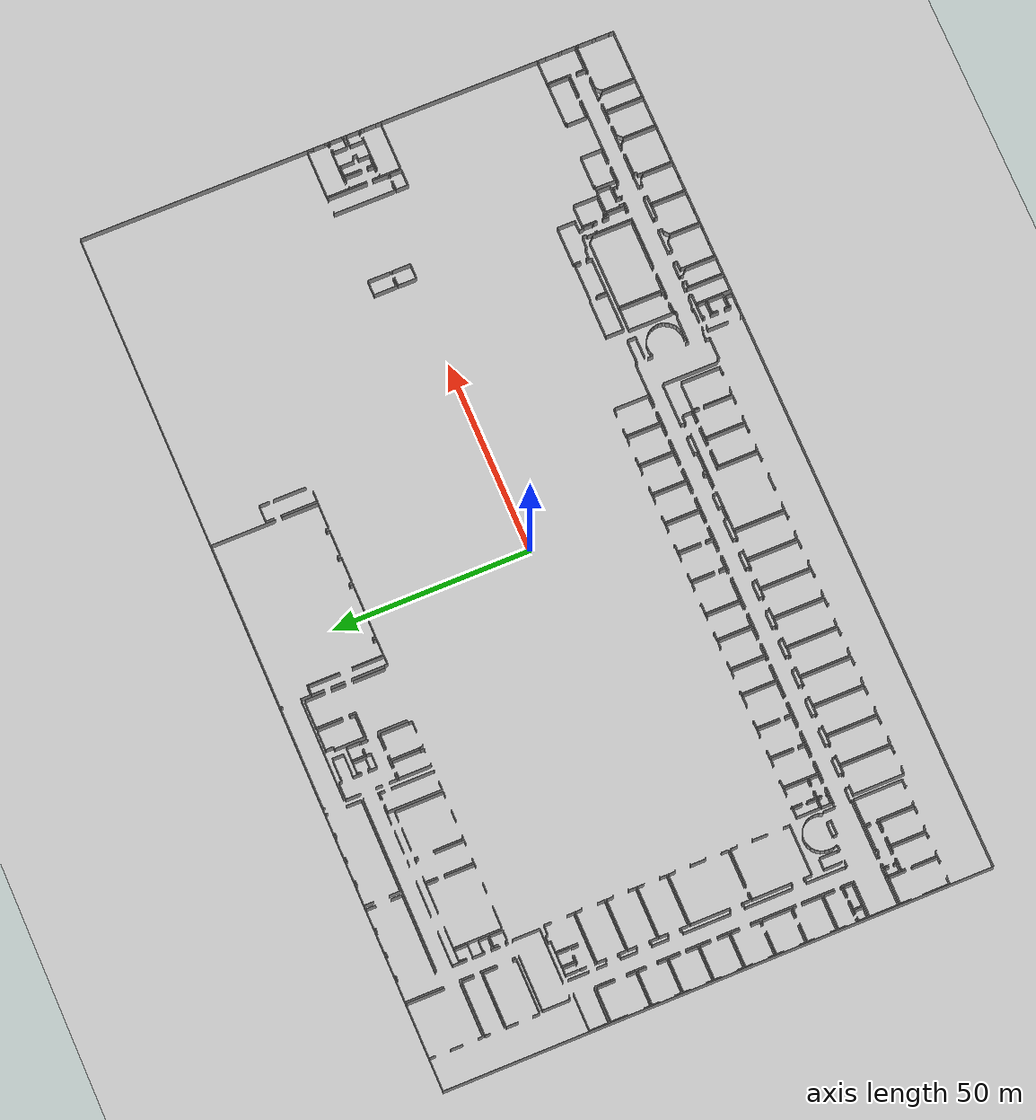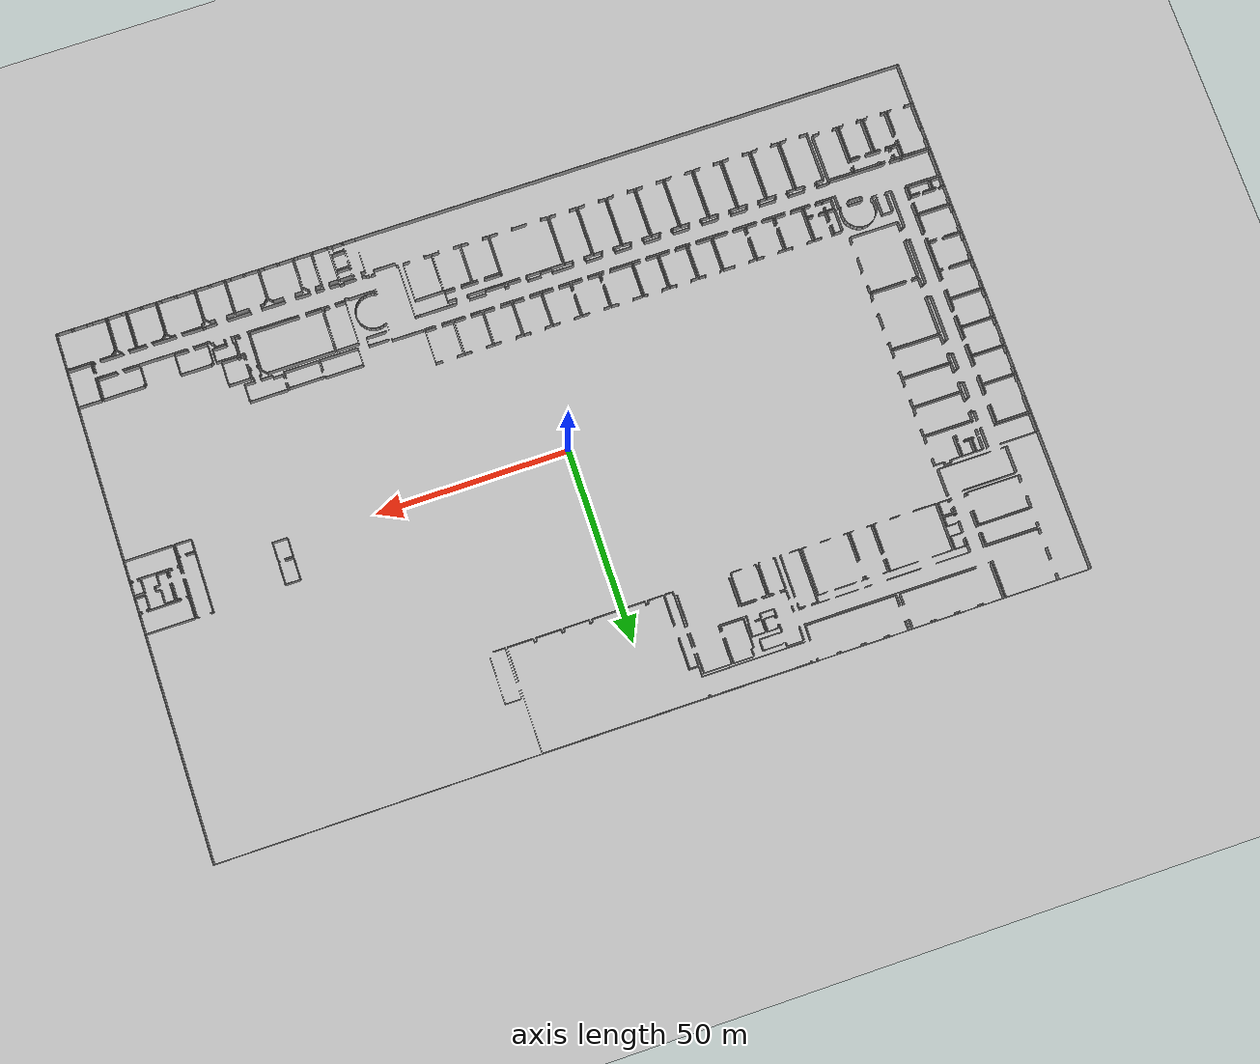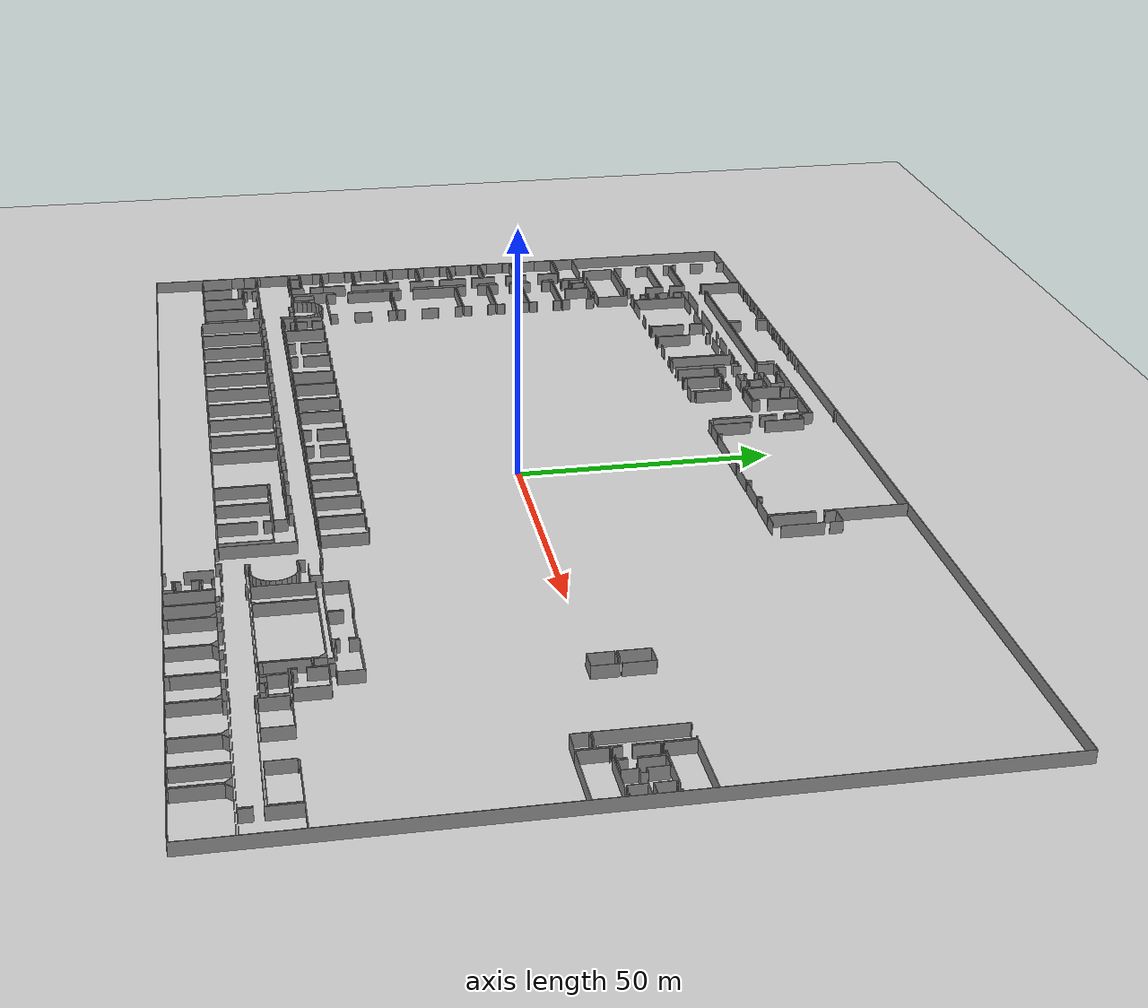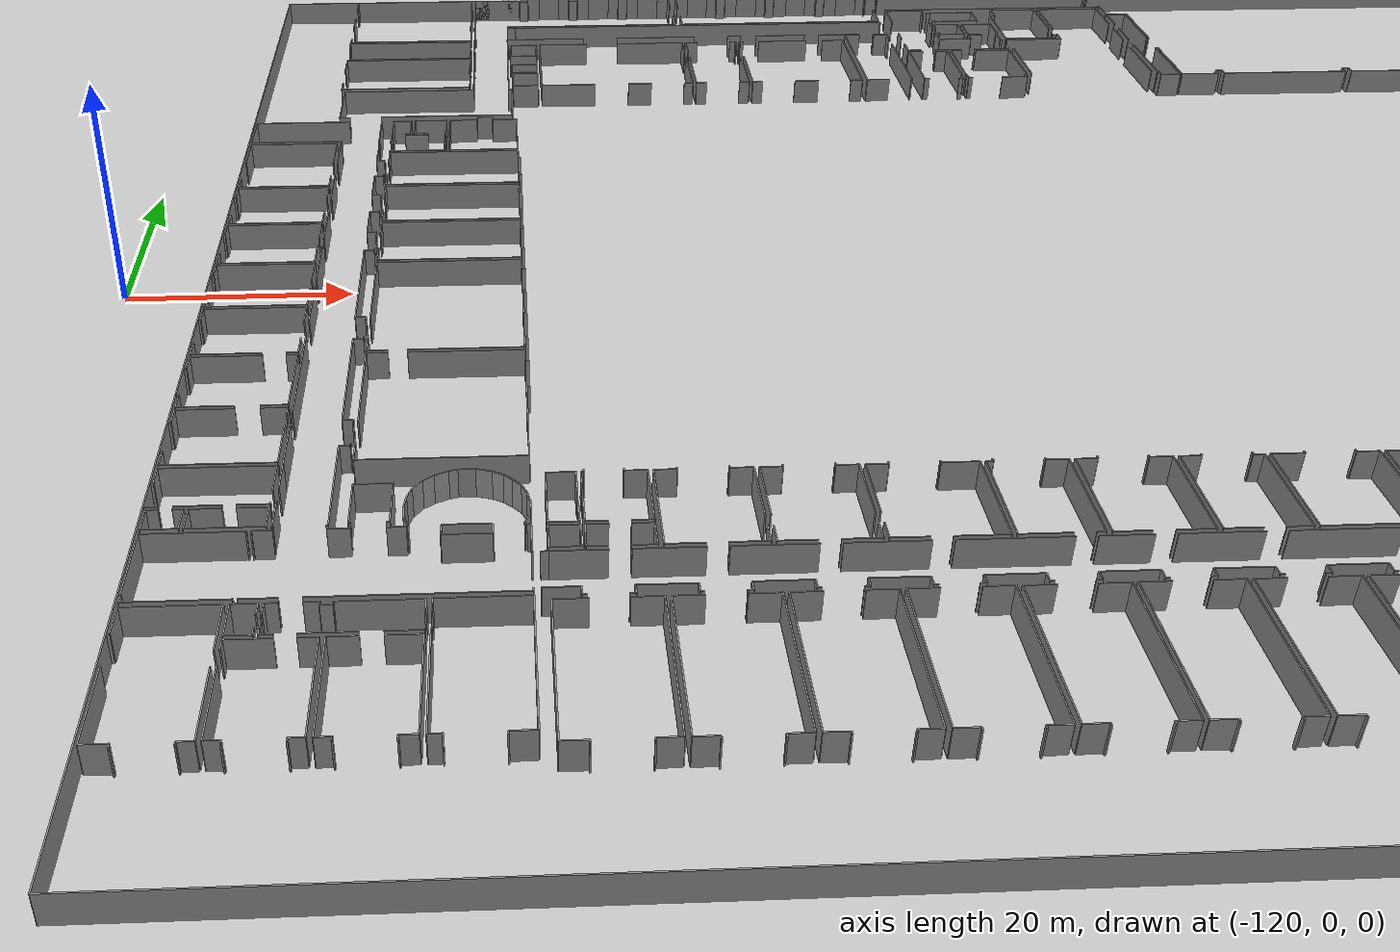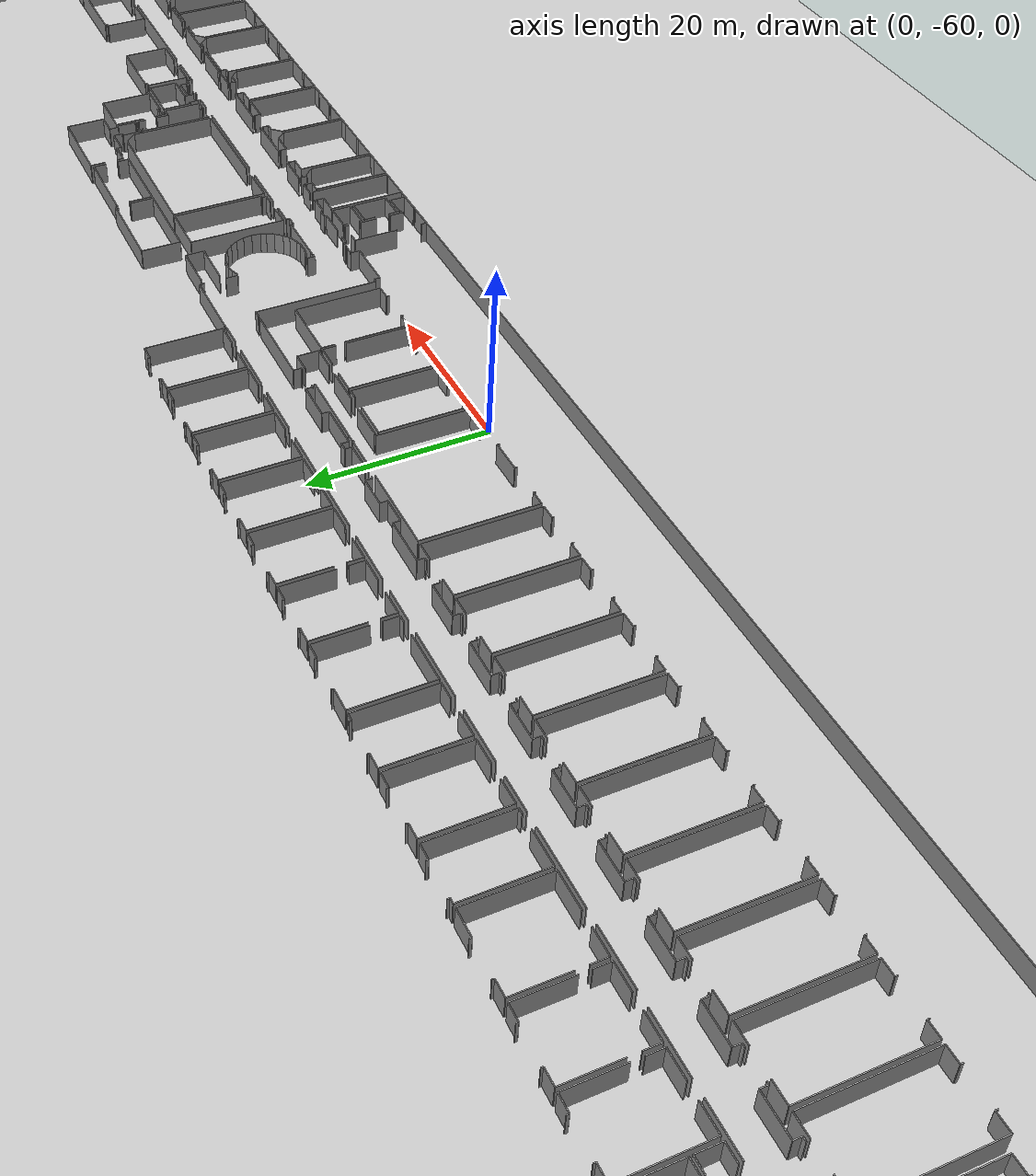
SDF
<sdf version="1.6">
  <world name="default">
    <light name="sun" type="directional">
      <cast_shadows>1</cast_shadows>
      <pose frame="">0 0 10 0 -0 0</pose>
      <diffuse>0.8 0.8 0.8 1</diffuse>
      <specular>0.1 0.1 0.1 1</specular>
      <attenuation>
        <range>1000</range>
        <constant>0.9</constant>
        <linear>0.01</linear>
        <quadratic>0.001</quadratic>
      </attenuation>
      <direction>-0.5 0.5 -1</direction>
    </light>
    <model name="ground_plane">
      <static>1</static>
      <link name="link">
        <collision name="collision">
          <geometry>
            <plane>
              <normal>0 0 1</normal>
              <size>100 100</size>
            </plane>
          </geometry>
          <surface>
            <friction>
              <ode>
                <mu>100</mu>
                <mu2>50</mu2>
              </ode>
              <torsional>
                <ode />
              </torsional>
            </friction>
            <contact>
              <ode />
            </contact>
            <bounce />
          </surface>
          <max_contacts>10</max_contacts>
        </collision>
        <visual name="visual">
          <cast_shadows>0</cast_shadows>
          <geometry>
            <plane>
              <normal>0 0 1</normal>
              <size>100 100</size>
            </plane>
          </geometry>
          <material>
            <script>
              <uri>file://media/materials/scripts/gazebo.material</uri>
              <name>Gazebo/Grey</name>
            </script>
          </material>
        </visual>
        <self_collide>0</self_collide>
        <kinematic>0</kinematic>
        <gravity>1</gravity>
      </link>
    </model>
    <gravity>0 0 -9.8</gravity>
    <magnetic_field>6e-06 2.3e-05 -4.2e-05</magnetic_field>
    <atmosphere type="adiabatic" />
    <physics default="0" name="default_physics" type="ode">
      <max_step_size>0.001</max_step_size>
      <real_time_factor>1</real_time_factor>
      <real_time_update_rate>1000</real_time_update_rate>
    </physics>
    <scene>
      <ambient>0.4 0.4 0.4 1</ambient>
      <background>0.7 0.7 0.7 1</background>
      <shadows>1</shadows>
    </scene>
    <spherical_coordinates>
      <surface_model>EARTH_WGS84</surface_model>
      <latitude_deg>0</latitude_deg>
      <longitude_deg>0</longitude_deg>
      <elevation>0</elevation>
      <heading_deg>0</heading_deg>
    </spherical_coordinates>
  <model name="0510035520_A_40_1_103">
		<static>1</static>
		<link name="Wall_0">
			<collision name="Wall_0_Collision">
				<geometry>
					<box>
						<size>13.8430593715 0.1 2.5</size>
					</box>
				</geometry>
				<pose frame="">6.92152968573 0 1.25 0 0 0</pose>
			</collision>
			<visual name="Wall_0_Visual">
				<pose frame="">6.92152968573 0 1.25 0 0 0</pose>
				<geometry>
					<box>
						<size>13.8430593715 0.1 2.5</size>
					</box>
				</geometry>
				<material>
					<script>
						<uri>file://media/materials/scripts/gazebo.material</uri>
						<name>Gazebo/Grey</name>
					</script>
					<ambient>1 1 1 1</ambient>
				</material>
			</visual>
			<pose frame="">22.2473207657 -13.3489000704 0 0 0 3.14159265359</pose>
		</link>
		<link name="Wall_1">
			<collision name="Wall_1_Collision">
				<geometry>
					<box>
						<size>1.32816416139 0.1 2.5</size>
					</box>
				</geometry>
				<pose frame="">0.664082080697 0 1.25 0 0 0</pose>
			</collision>
			<visual name="Wall_1_Visual">
				<pose frame="">0.664082080697 0 1.25 0 0 0</pose>
				<geometry>
					<box>
						<size>1.32816416139 0.1 2.5</size>
					</box>
				</geometry>
				<material>
					<script>
						<uri>file://media/materials/scripts/gazebo.material</uri>
						<name>Gazebo/Grey</name>
					</script>
					<ambient>1 1 1 1</ambient>
				</material>
			</visual>
			<pose frame="">8.40426139428 -13.3489000704 0 0 0 1.57079632679</pose>
		</link>
		<link name="Wall_2">
			<collision name="Wall_2_Collision">
				<geometry>
					<box>
						<size>3.09465041465 0.1 2.5</size>
					</box>
				</geometry>
				<pose frame="">1.54732520733 0 1.25 0 0 0</pose>
			</collision>
			<visual name="Wall_2_Visual">
				<pose frame="">1.54732520733 0 1.25 0 0 0</pose>
				<geometry>
					<box>
						<size>3.09465041465 0.1 2.5</size>
					</box>
				</geometry>
				<material>
					<script>
						<uri>file://media/materials/scripts/gazebo.material</uri>
						<name>Gazebo/Grey</name>
					</script>
					<ambient>1 1 1 1</ambient>
				</material>
			</visual>
			<pose frame="">8.40426139428 -8.38700262054 0 0 0 1.57079632679</pose>
		</link>
		<link name="Wall_3">
			<collision name="Wall_3_Collision">
				<geometry>
					<box>
						<size>1.65938033388 0.1 2.5</size>
					</box>
				</geometry>
				<pose frame="">0.829690166941 0 1.25 0 0 0</pose>
			</collision>
			<visual name="Wall_3_Visual">
				<pose frame="">0.829690166941 0 1.25 0 0 0</pose>
				<geometry>
					<box>
						<size>1.65938033388 0.1 2.5</size>
					</box>
				</geometry>
				<material>
					<script>
						<uri>file://media/materials/scripts/gazebo.material</uri>
						<name>Gazebo/Grey</name>
					</script>
					<ambient>1 1 1 1</ambient>
				</material>
			</visual>
			<pose frame="">8.40426139428 -1.67714671861 0 0 0 1.57079632679</pose>
		</link>
		<link name="Wall_4">
			<collision name="Wall_4_Collision">
				<geometry>
					<box>
						<size>13.8679323101 0.1 2.5</size>
					</box>
				</geometry>
				<pose frame="">6.93396615504 0 1.25 0 0 0</pose>
			</collision>
			<visual name="Wall_4_Visual">
				<pose frame="">6.93396615504 0 1.25 0 0 0</pose>
				<geometry>
					<box>
						<size>13.8679323101 0.1 2.5</size>
					</box>
				</geometry>
				<material>
					<script>
						<uri>file://media/materials/scripts/gazebo.material</uri>
						<name>Gazebo/Grey</name>
					</script>
					<ambient>1 1 1 1</ambient>
				</material>
			</visual>
			<pose frame="">8.40426139428 -0.0177663847311 0 0 0 0.0</pose>
		</link>
		<link name="Wall_5">
			<collision name="Wall_5_Collision">
				<geometry>
					<box>
						<size>9.46037876144 0.1 2.5</size>
					</box>
				</geometry>
				<pose frame="">4.73018938072 0 1.25 0 0 0</pose>
			</collision>
			<visual name="Wall_5_Visual">
				<pose frame="">4.73018938072 0 1.25 0 0 0</pose>
				<geometry>
					<box>
						<size>9.46037876144 0.1 2.5</size>
					</box>
				</geometry>
				<material>
					<script>
						<uri>file://media/materials/scripts/gazebo.material</uri>
						<name>Gazebo/Grey</name>
					</script>
					<ambient>1 1 1 1</ambient>
				</material>
			</visual>
			<pose frame="">22.2721937044 -0.0177663847311 0 0 0 -1.57342549925</pose>
		</link>
		<link name="Wall_6">
			<collision name="Wall_6_Collision">
				<geometry>
					<box>
						<size>13.9044803015 0.1 2.5</size>
					</box>
				</geometry>
				<pose frame="">6.95224015076 0 1.25 0 0 0</pose>
			</collision>
			<visual name="Wall_6_Visual">
				<pose frame="">6.95224015076 0 1.25 0 0 0</pose>
				<geometry>
					<box>
						<size>13.9044803015 0.1 2.5</size>
					</box>
				</geometry>
				<material>
					<script>
						<uri>file://media/materials/scripts/gazebo.material</uri>
						<name>Gazebo/Grey</name>
					</script>
					<ambient>1 1 1 1</ambient>
				</material>
			</visual>
			<pose frame="">8.36593676436 -13.8136179339 0 0 0 0.0</pose>
		</link>
		<link name="Wall_7">
			<collision name="Wall_7_Collision">
				<geometry>
					<box>
						<size>3.17891383938 0.1 2.5</size>
					</box>
				</geometry>
				<pose frame="">1.58945691969 0 1.25 0 0 0</pose>
			</collision>
			<visual name="Wall_7_Visual">
				<pose frame="">1.58945691969 0 1.25 0 0 0</pose>
				<geometry>
					<box>
						<size>3.17891383938 0.1 2.5</size>
					</box>
				</geometry>
				<material>
					<script>
						<uri>file://media/materials/scripts/gazebo.material</uri>
						<name>Gazebo/Grey</name>
					</script>
					<ambient>1 1 1 1</ambient>
				</material>
			</visual>
			<pose frame="">22.2704170659 -13.8136179339 0 0 0 -1.57079632679</pose>
		</link>
		<link name="Wall_8">
			<collision name="Wall_8_Collision">
				<geometry>
					<box>
						<size>0.0763954543436 0.1 2.5</size>
					</box>
				</geometry>
				<pose frame="">0.0381977271718 0 1.25 0 0 0</pose>
			</collision>
			<visual name="Wall_8_Visual">
				<pose frame="">0.0381977271718 0 1.25 0 0 0</pose>
				<geometry>
					<box>
						<size>0.0763954543436 0.1 2.5</size>
					</box>
				</geometry>
				<material>
					<script>
						<uri>file://media/materials/scripts/gazebo.material</uri>
						<name>Gazebo/Grey</name>
					</script>
					<ambient>1 1 1 1</ambient>
				</material>
			</visual>
			<pose frame="">22.2704170659 -18.6798307117 0 0 0 -1.57079632679</pose>
		</link>
		<link name="Wall_9">
			<collision name="Wall_9_Collision">
				<geometry>
					<box>
						<size>13.904734107 0.1 2.5</size>
					</box>
				</geometry>
				<pose frame="">6.95236705351 0 1.25 0 0 0</pose>
			</collision>
			<visual name="Wall_9_Visual">
				<pose frame="">6.95236705351 0 1.25 0 0 0</pose>
				<geometry>
					<box>
						<size>13.904734107 0.1 2.5</size>
					</box>
				</geometry>
				<material>
					<script>
						<uri>file://media/materials/scripts/gazebo.material</uri>
						<name>Gazebo/Grey</name>
					</script>
					<ambient>1 1 1 1</ambient>
				</material>
			</visual>
			<pose frame="">22.2704170659 -18.7562261661 0 0 0 3.14159265359</pose>
		</link>
		<link name="Wall_10">
			<collision name="Wall_10_Collision">
				<geometry>
					<box>
						<size>1.30887496829 0.1 2.5</size>
					</box>
				</geometry>
				<pose frame="">0.654437484147 0 1.25 0 0 0</pose>
			</collision>
			<visual name="Wall_10_Visual">
				<pose frame="">0.654437484147 0 1.25 0 0 0</pose>
				<geometry>
					<box>
						<size>1.30887496829 0.1 2.5</size>
					</box>
				</geometry>
				<material>
					<script>
						<uri>file://media/materials/scripts/gazebo.material</uri>
						<name>Gazebo/Grey</name>
					</script>
					<ambient>1 1 1 1</ambient>
				</material>
			</visual>
			<pose frame="">8.36568295886 -15.1224928776 0 0 0 1.57060241561</pose>
		</link>
		<link name="Wall_11">
			<collision name="Wall_11_Collision">
				<geometry>
					<box>
						<size>1.87283075615 0.1 2.5</size>
					</box>
				</geometry>
				<pose frame="">0.936415378075 0 1.25 0 0 0</pose>
			</collision>
			<visual name="Wall_11_Visual">
				<pose frame="">0.936415378075 0 1.25 0 0 0</pose>
				<geometry>
					<box>
						<size>1.87283075615 0.1 2.5</size>
					</box>
				</geometry>
				<material>
					<script>
						<uri>file://media/materials/scripts/gazebo.material</uri>
						<name>Gazebo/Grey</name>
					</script>
					<ambient>1 1 1 1</ambient>
				</material>
			</visual>
			<pose frame="">8.36898243031 -27.4554095469 0 0 0 1.57079632679</pose>
		</link>
		<link name="Wall_12">
			<collision name="Wall_12_Collision">
				<geometry>
					<box>
						<size>2.87079396704 0.1 2.5</size>
					</box>
				</geometry>
				<pose frame="">1.43539698352 0 1.25 0 0 0</pose>
			</collision>
			<visual name="Wall_12_Visual">
				<pose frame="">1.43539698352 0 1.25 0 0 0</pose>
				<geometry>
					<box>
						<size>2.87079396704 0.1 2.5</size>
					</box>
				</geometry>
				<material>
					<script>
						<uri>file://media/materials/scripts/gazebo.material</uri>
						<name>Gazebo/Grey</name>
					</script>
					<ambient>1 1 1 1</ambient>
				</material>
			</visual>
			<pose frame="">8.36898243031 -21.9815864113 0 0 0 1.57079632679</pose>
		</link>
		<link name="Wall_13">
			<collision name="Wall_13_Collision">
				<geometry>
					<box>
						<size>13.8846834728 0.1 2.5</size>
					</box>
				</geometry>
				<pose frame="">6.94234173641 0 1.25 0 0 0</pose>
			</collision>
			<visual name="Wall_13_Visual">
				<pose frame="">6.94234173641 0 1.25 0 0 0</pose>
				<geometry>
					<box>
						<size>13.8846834728 0.1 2.5</size>
					</box>
				</geometry>
				<material>
					<script>
						<uri>file://media/materials/scripts/gazebo.material</uri>
						<name>Gazebo/Grey</name>
					</script>
					<ambient>1 1 1 1</ambient>
				</material>
			</visual>
			<pose frame="">8.36898243031 -19.1107924442 0 0 0 0.0</pose>
		</link>
		<link name="Wall_14">
			<collision name="Wall_14_Collision">
				<geometry>
					<box>
						<size>3.60936796086 0.1 2.5</size>
					</box>
				</geometry>
				<pose frame="">1.80468398043 0 1.25 0 0 0</pose>
			</collision>
			<visual name="Wall_14_Visual">
				<pose frame="">1.80468398043 0 1.25 0 0 0</pose>
				<geometry>
					<box>
						<size>3.60936796086 0.1 2.5</size>
					</box>
				</geometry>
				<material>
					<script>
						<uri>file://media/materials/scripts/gazebo.material</uri>
						<name>Gazebo/Grey</name>
					</script>
					<ambient>1 1 1 1</ambient>
				</material>
			</visual>
			<pose frame="">22.2536659031 -19.1107924442 0 0 0 -1.57079632679</pose>
		</link>
		<link name="Wall_15">
			<collision name="Wall_15_Collision">
				<geometry>
					<box>
						<size>0.831466805414 0.1 2.5</size>
					</box>
				</geometry>
				<pose frame="">0.415733402707 0 1.25 0 0 0</pose>
			</collision>
			<visual name="Wall_15_Visual">
				<pose frame="">0.415733402707 0 1.25 0 0 0</pose>
				<geometry>
					<box>
						<size>0.831466805414 0.1 2.5</size>
					</box>
				</geometry>
				<material>
					<script>
						<uri>file://media/materials/scripts/gazebo.material</uri>
						<name>Gazebo/Grey</name>
					</script>
					<ambient>1 1 1 1</ambient>
				</material>
			</visual>
			<pose frame="">22.2536659031 -26.6186128261 0 0 0 -1.57079632679</pose>
		</link>
		<link name="Wall_16">
			<collision name="Wall_16_Collision">
				<geometry>
					<box>
						<size>13.8846844958 0.1 2.5</size>
					</box>
				</geometry>
				<pose frame="">6.94234224791 0 1.25 0 0 0</pose>
			</collision>
			<visual name="Wall_16_Visual">
				<pose frame="">6.94234224791 0 1.25 0 0 0</pose>
				<geometry>
					<box>
						<size>13.8846844958 0.1 2.5</size>
					</box>
				</geometry>
				<material>
					<script>
						<uri>file://media/materials/scripts/gazebo.material</uri>
						<name>Gazebo/Grey</name>
					</script>
					<ambient>1 1 1 1</ambient>
				</material>
			</visual>
			<pose frame="">22.2536659031 -27.4500796315 0 0 0 -3.14120878347</pose>
		</link>
		<link name="Wall_17">
			<collision name="Wall_17_Collision">
				<geometry>
					<box>
						<size>1.68755274395 0.1 2.5</size>
					</box>
				</geometry>
				<pose frame="">0.843776371977 0 1.25 0 0 0</pose>
			</collision>
			<visual name="Wall_17_Visual">
				<pose frame="">0.843776371977 0 1.25 0 0 0</pose>
				<geometry>
					<box>
						<size>1.68755274395 0.1 2.5</size>
					</box>
				</geometry>
				<material>
					<script>
						<uri>file://media/materials/scripts/gazebo.material</uri>
						<name>Gazebo/Grey</name>
					</script>
					<ambient>1 1 1 1</ambient>
				</material>
			</visual>
			<pose frame="">22.7115310182 -0.0 0 0 0 0.0</pose>
		</link>
		<link name="Wall_18">
			<collision name="Wall_18_Collision">
				<geometry>
					<box>
						<size>1.35278329452 0.1 2.5</size>
					</box>
				</geometry>
				<pose frame="">0.676391647261 0 1.25 0 0 0</pose>
			</collision>
			<visual name="Wall_18_Visual">
				<pose frame="">0.676391647261 0 1.25 0 0 0</pose>
				<geometry>
					<box>
						<size>1.35278329452 0.1 2.5</size>
					</box>
				</geometry>
				<material>
					<script>
						<uri>file://media/materials/scripts/gazebo.material</uri>
						<name>Gazebo/Grey</name>
					</script>
					<ambient>1 1 1 1</ambient>
				</material>
			</visual>
			<pose frame="">26.8318094428 -0.0 0 0 0 0.0</pose>
		</link>
		<link name="Wall_19">
			<collision name="Wall_19_Collision">
				<geometry>
					<box>
						<size>0.416748624691 0.1 2.5</size>
					</box>
				</geometry>
				<pose frame="">0.208374312346 0 1.25 0 0 0</pose>
			</collision>
			<visual name="Wall_19_Visual">
				<pose frame="">0.208374312346 0 1.25 0 0 0</pose>
				<geometry>
					<box>
						<size>0.416748624691 0.1 2.5</size>
					</box>
				</geometry>
				<material>
					<script>
						<uri>file://media/materials/scripts/gazebo.material</uri>
						<name>Gazebo/Grey</name>
					</script>
					<ambient>1 1 1 1</ambient>
				</material>
			</visual>
			<pose frame="">28.1845927374 -0.0 0 0 0 -1.57079632679</pose>
		</link>
		<link name="Wall_20">
			<collision name="Wall_20_Collision">
				<geometry>
					<box>
						<size>0.990602851505 0.1 2.5</size>
					</box>
				</geometry>
				<pose frame="">0.495301425752 0 1.25 0 0 0</pose>
			</collision>
			<visual name="Wall_20_Visual">
				<pose frame="">0.495301425752 0 1.25 0 0 0</pose>
				<geometry>
					<box>
						<size>0.990602851505 0.1 2.5</size>
					</box>
				</geometry>
				<material>
					<script>
						<uri>file://media/materials/scripts/gazebo.material</uri>
						<name>Gazebo/Grey</name>
					</script>
					<ambient>1 1 1 1</ambient>
				</material>
			</visual>
			<pose frame="">28.1845927374 -0.416748624691 0 0 0 0.0</pose>
		</link>
		<link name="Wall_21">
			<collision name="Wall_21_Collision">
				<geometry>
					<box>
						<size>0.39771321248 0.1 2.5</size>
					</box>
				</geometry>
				<pose frame="">0.19885660624 0 1.25 0 0 0</pose>
			</collision>
			<visual name="Wall_21_Visual">
				<pose frame="">0.19885660624 0 1.25 0 0 0</pose>
				<geometry>
					<box>
						<size>0.39771321248 0.1 2.5</size>
					</box>
				</geometry>
				<material>
					<script>
						<uri>file://media/materials/scripts/gazebo.material</uri>
						<name>Gazebo/Grey</name>
					</script>
					<ambient>1 1 1 1</ambient>
				</material>
			</visual>
			<pose frame="">29.1751955889 -0.416748624691 0 0 0 1.57079632679</pose>
		</link>
		<link name="Wall_22">
			<collision name="Wall_22_Collision">
				<geometry>
					<box>
						<size>1.39796067284 0.1 2.5</size>
					</box>
				</geometry>
				<pose frame="">0.698980336419 0 1.25 0 0 0</pose>
			</collision>
			<visual name="Wall_22_Visual">
				<pose frame="">0.698980336419 0 1.25 0 0 0</pose>
				<geometry>
					<box>
						<size>1.39796067284 0.1 2.5</size>
					</box>
				</geometry>
				<material>
					<script>
						<uri>file://media/materials/scripts/gazebo.material</uri>
						<name>Gazebo/Grey</name>
					</script>
					<ambient>1 1 1 1</ambient>
				</material>
			</visual>
			<pose frame="">29.1751955889 -0.0190354122118 0 0 0 0.0</pose>
		</link>
		<link name="Wall_23">
			<collision name="Wall_23_Collision">
				<geometry>
					<box>
						<size>1.24593118064 0.1 2.5</size>
					</box>
				</geometry>
				<pose frame="">0.62296559032 0 1.25 0 0 0</pose>
			</collision>
			<visual name="Wall_23_Visual">
				<pose frame="">0.62296559032 0 1.25 0 0 0</pose>
				<geometry>
					<box>
						<size>1.24593118064 0.1 2.5</size>
					</box>
				</geometry>
				<material>
					<script>
						<uri>file://media/materials/scripts/gazebo.material</uri>
						<name>Gazebo/Grey</name>
					</script>
					<ambient>1 1 1 1</ambient>
				</material>
			</visual>
			<pose frame="">33.0315162975 -0.0190354122118 0 0 0 0.0</pose>
		</link>
		<link name="Wall_24">
			<collision name="Wall_24_Collision">
				<geometry>
					<box>
						<size>0.39111426958 0.1 2.5</size>
					</box>
				</geometry>
				<pose frame="">0.19555713479 0 1.25 0 0 0</pose>
			</collision>
			<visual name="Wall_24_Visual">
				<pose frame="">0.19555713479 0 1.25 0 0 0</pose>
				<geometry>
					<box>
						<size>0.39111426958 0.1 2.5</size>
					</box>
				</geometry>
				<material>
					<script>
						<uri>file://media/materials/scripts/gazebo.material</uri>
						<name>Gazebo/Grey</name>
					</script>
					<ambient>1 1 1 1</ambient>
				</material>
			</visual>
			<pose frame="">34.2774474781 -0.0190354122118 0 0 0 -1.57079632679</pose>
		</link>
		<link name="Wall_25">
			<collision name="Wall_25_Collision">
				<geometry>
					<box>
						<size>0.992379489978 0.1 2.5</size>
					</box>
				</geometry>
				<pose frame="">0.496189744989 0 1.25 0 0 0</pose>
			</collision>
			<visual name="Wall_25_Visual">
				<pose frame="">0.496189744989 0 1.25 0 0 0</pose>
				<geometry>
					<box>
						<size>0.992379489978 0.1 2.5</size>
					</box>
				</geometry>
				<material>
					<script>
						<uri>file://media/materials/scripts/gazebo.material</uri>
						<name>Gazebo/Grey</name>
					</script>
					<ambient>1 1 1 1</ambient>
				</material>
			</visual>
			<pose frame="">34.2774474781 -0.410149681791 0 0 0 0.0</pose>
		</link>
		<link name="Wall_26">
			<collision name="Wall_26_Collision">
				<geometry>
					<box>
						<size>0.374363106833 0.1 2.5</size>
					</box>
				</geometry>
				<pose frame="">0.187181553417 0 1.25 0 0 0</pose>
			</collision>
			<visual name="Wall_26_Visual">
				<pose frame="">0.187181553417 0 1.25 0 0 0</pose>
				<geometry>
					<box>
						<size>0.374363106833 0.1 2.5</size>
					</box>
				</geometry>
				<material>
					<script>
						<uri>file://media/materials/scripts/gazebo.material</uri>
						<name>Gazebo/Grey</name>
					</script>
					<ambient>1 1 1 1</ambient>
				</material>
			</visual>
			<pose frame="">35.2698269681 -0.410149681791 0 0 0 1.57079632679</pose>
		</link>
		<link name="Wall_27">
			<collision name="Wall_27_Collision">
				<geometry>
					<box>
						<size>1.41902652902 0.1 2.5</size>
					</box>
				</geometry>
				<pose frame="">0.70951326451 0 1.25 0 0 0</pose>
			</collision>
			<visual name="Wall_27_Visual">
				<pose frame="">0.70951326451 0 1.25 0 0 0</pose>
				<geometry>
					<box>
						<size>1.41902652902 0.1 2.5</size>
					</box>
				</geometry>
				<material>
					<script>
						<uri>file://media/materials/scripts/gazebo.material</uri>
						<name>Gazebo/Grey</name>
					</script>
					<ambient>1 1 1 1</ambient>
				</material>
			</visual>
			<pose frame="">35.2698269681 -0.0357865749583 0 0 0 0.0</pose>
		</link>
		<link name="Wall_28">
			<collision name="Wall_28_Collision">
				<geometry>
					<box>
						<size>1.23983984873 0.1 2.5</size>
					</box>
				</geometry>
				<pose frame="">0.619919924366 0 1.25 0 0 0</pose>
			</collision>
			<visual name="Wall_28_Visual">
				<pose frame="">0.619919924366 0 1.25 0 0 0</pose>
				<geometry>
					<box>
						<size>1.23983984873 0.1 2.5</size>
					</box>
				</geometry>
				<material>
					<script>
						<uri>file://media/materials/scripts/gazebo.material</uri>
						<name>Gazebo/Grey</name>
					</script>
					<ambient>1 1 1 1</ambient>
				</material>
			</visual>
			<pose frame="">39.1322390086 -0.0357865749583 0 0 0 0.0</pose>
		</link>
		<link name="Wall_29">
			<collision name="Wall_29_Collision">
				<geometry>
					<box>
						<size>0.382231077214 0.1 2.5</size>
					</box>
				</geometry>
				<pose frame="">0.191115538607 0 1.25 0 0 0</pose>
			</collision>
			<visual name="Wall_29_Visual">
				<pose frame="">0.191115538607 0 1.25 0 0 0</pose>
				<geometry>
					<box>
						<size>0.382231077214 0.1 2.5</size>
					</box>
				</geometry>
				<material>
					<script>
						<uri>file://media/materials/scripts/gazebo.material</uri>
						<name>Gazebo/Grey</name>
					</script>
					<ambient>1 1 1 1</ambient>
				</material>
			</visual>
			<pose frame="">40.3720788574 -0.0357865749583 0 0 0 -1.57079632679</pose>
		</link>
		<link name="Wall_30">
			<collision name="Wall_30_Collision">
				<geometry>
					<box>
						<size>1.00989206921 0.1 2.5</size>
					</box>
				</geometry>
				<pose frame="">0.504946034606 0 1.25 0 0 0</pose>
			</collision>
			<visual name="Wall_30_Visual">
				<pose frame="">0.504946034606 0 1.25 0 0 0</pose>
				<geometry>
					<box>
						<size>1.00989206921 0.1 2.5</size>
					</box>
				</geometry>
				<material>
					<script>
						<uri>file://media/materials/scripts/gazebo.material</uri>
						<name>Gazebo/Grey</name>
					</script>
					<ambient>1 1 1 1</ambient>
				</material>
			</visual>
			<pose frame="">40.3720788574 -0.418017652172 0 0 0 0.0</pose>
		</link>
		<link name="Wall_31">
			<collision name="Wall_31_Collision">
				<geometry>
					<box>
						<size>0.385276743168 0.1 2.5</size>
					</box>
				</geometry>
				<pose frame="">0.192638371584 0 1.25 0 0 0</pose>
			</collision>
			<visual name="Wall_31_Visual">
				<pose frame="">0.192638371584 0 1.25 0 0 0</pose>
				<geometry>
					<box>
						<size>0.385276743168 0.1 2.5</size>
					</box>
				</geometry>
				<material>
					<script>
						<uri>file://media/materials/scripts/gazebo.material</uri>
						<name>Gazebo/Grey</name>
					</script>
					<ambient>1 1 1 1</ambient>
				</material>
			</visual>
			<pose frame="">41.3819709266 -0.418017652172 0 0 0 1.57079632679</pose>
		</link>
		<link name="Wall_32">
			<collision name="Wall_32_Collision">
				<geometry>
					<box>
						<size>1.41978794551 0.1 2.5</size>
					</box>
				</geometry>
				<pose frame="">0.709893972754 0 1.25 0 0 0</pose>
			</collision>
			<visual name="Wall_32_Visual">
				<pose frame="">0.709893972754 0 1.25 0 0 0</pose>
				<geometry>
					<box>
						<size>1.41978794551 0.1 2.5</size>
					</box>
				</geometry>
				<material>
					<script>
						<uri>file://media/materials/scripts/gazebo.material</uri>
						<name>Gazebo/Grey</name>
					</script>
					<ambient>1 1 1 1</ambient>
				</material>
			</visual>
			<pose frame="">41.3819709266 -0.0327409090044 0 0 0 0.0</pose>
		</link>
		<link name="Wall_33">
			<collision name="Wall_33_Collision">
				<geometry>
					<box>
						<size>1.27994111712 0.1 2.5</size>
					</box>
				</geometry>
				<pose frame="">0.639970558562 0 1.25 0 0 0</pose>
			</collision>
			<visual name="Wall_33_Visual">
				<pose frame="">0.639970558562 0 1.25 0 0 0</pose>
				<geometry>
					<box>
						<size>1.27994111712 0.1 2.5</size>
					</box>
				</geometry>
				<material>
					<script>
						<uri>file://media/materials/scripts/gazebo.material</uri>
						<name>Gazebo/Grey</name>
					</script>
					<ambient>1 1 1 1</ambient>
				</material>
			</visual>
			<pose frame="">45.2131648911 -0.0327409090044 0 0 0 0.0</pose>
		</link>
		<link name="Wall_34">
			<collision name="Wall_34_Collision">
				<geometry>
					<box>
						<size>2.50302980311 0.1 2.5</size>
					</box>
				</geometry>
				<pose frame="">1.25151490156 0 1.25 0 0 0</pose>
			</collision>
			<visual name="Wall_34_Visual">
				<pose frame="">1.25151490156 0 1.25 0 0 0</pose>
				<geometry>
					<box>
						<size>2.50302980311 0.1 2.5</size>
					</box>
				</geometry>
				<material>
					<script>
						<uri>file://media/materials/scripts/gazebo.material</uri>
						<name>Gazebo/Grey</name>
					</script>
					<ambient>1 1 1 1</ambient>
				</material>
			</visual>
			<pose frame="">46.4931060082 -0.0327409090044 0 0 0 -1.57079632679</pose>
		</link>
		<link name="Wall_35">
			<collision name="Wall_35_Collision">
				<geometry>
					<box>
						<size>2.81064206445 0.1 2.5</size>
					</box>
				</geometry>
				<pose frame="">1.40532103223 0 1.25 0 0 0</pose>
			</collision>
			<visual name="Wall_35_Visual">
				<pose frame="">1.40532103223 0 1.25 0 0 0</pose>
				<geometry>
					<box>
						<size>2.81064206445 0.1 2.5</size>
					</box>
				</geometry>
				<material>
					<script>
						<uri>file://media/materials/scripts/gazebo.material</uri>
						<name>Gazebo/Grey</name>
					</script>
					<ambient>1 1 1 1</ambient>
				</material>
			</visual>
			<pose frame="">46.4931060082 -6.24209237251 0 0 0 -1.57079632679</pose>
		</link>
		<link name="Wall_36">
			<collision name="Wall_36_Collision">
				<geometry>
					<box>
						<size>19.8965742603 0.1 2.5</size>
					</box>
				</geometry>
				<pose frame="">9.94828713016 0 1.25 0 0 0</pose>
			</collision>
			<visual name="Wall_36_Visual">
				<pose frame="">9.94828713016 0 1.25 0 0 0</pose>
				<geometry>
					<box>
						<size>19.8965742603 0.1 2.5</size>
					</box>
				</geometry>
				<material>
					<script>
						<uri>file://media/materials/scripts/gazebo.material</uri>
						<name>Gazebo/Grey</name>
					</script>
					<ambient>1 1 1 1</ambient>
				</material>
			</visual>
			<pose frame="">46.4931060082 -9.05273443696 0 0 0 3.14159265359</pose>
		</link>
		<link name="Wall_37">
			<collision name="Wall_37_Collision">
				<geometry>
					<box>
						<size>9.05273444052 0.1 2.5</size>
					</box>
				</geometry>
				<pose frame="">4.52636722026 0 1.25 0 0 0</pose>
			</collision>
			<visual name="Wall_37_Visual">
				<pose frame="">4.52636722026 0 1.25 0 0 0</pose>
				<geometry>
					<box>
						<size>9.05273444052 0.1 2.5</size>
					</box>
				</geometry>
				<material>
					<script>
						<uri>file://media/materials/scripts/gazebo.material</uri>
						<name>Gazebo/Grey</name>
					</script>
					<ambient>1 1 1 1</ambient>
				</material>
			</visual>
			<pose frame="">22.7117848237 -9.05273443696 0 0 0 1.57082436313</pose>
		</link>
		<link name="Wall_38">
			<collision name="Wall_38_Collision">
				<geometry>
					<box>
						<size>1.53679227924 0.1 2.5</size>
					</box>
				</geometry>
				<pose frame="">0.768396139618 0 1.25 0 0 0</pose>
			</collision>
			<visual name="Wall_38_Visual">
				<pose frame="">0.768396139618 0 1.25 0 0 0</pose>
				<geometry>
					<box>
						<size>1.53679227924 0.1 2.5</size>
					</box>
				</geometry>
				<material>
					<script>
						<uri>file://media/materials/scripts/gazebo.material</uri>
						<name>Gazebo/Grey</name>
					</script>
					<ambient>1 1 1 1</ambient>
				</material>
			</visual>
			<pose frame="">47.4512217562 -0.00329947145006 0 0 0 0.0</pose>
		</link>
		<link name="Wall_39">
			<collision name="Wall_39_Collision">
				<geometry>
					<box>
						<size>1.1761346692 0.1 2.5</size>
					</box>
				</geometry>
				<pose frame="">0.588067334598 0 1.25 0 0 0</pose>
			</collision>
			<visual name="Wall_39_Visual">
				<pose frame="">0.588067334598 0 1.25 0 0 0</pose>
				<geometry>
					<box>
						<size>1.1761346692 0.1 2.5</size>
					</box>
				</geometry>
				<material>
					<script>
						<uri>file://media/materials/scripts/gazebo.material</uri>
						<name>Gazebo/Grey</name>
					</script>
					<ambient>1 1 1 1</ambient>
				</material>
			</visual>
			<pose frame="">51.3687095894 -0.00329947145006 0 0 0 0.0</pose>
		</link>
		<link name="Wall_40">
			<collision name="Wall_40_Collision">
				<geometry>
					<box>
						<size>0.404058349884 0.1 2.5</size>
					</box>
				</geometry>
				<pose frame="">0.202029174942 0 1.25 0 0 0</pose>
			</collision>
			<visual name="Wall_40_Visual">
				<pose frame="">0.202029174942 0 1.25 0 0 0</pose>
				<geometry>
					<box>
						<size>0.404058349884 0.1 2.5</size>
					</box>
				</geometry>
				<material>
					<script>
						<uri>file://media/materials/scripts/gazebo.material</uri>
						<name>Gazebo/Grey</name>
					</script>
					<ambient>1 1 1 1</ambient>
				</material>
			</visual>
			<pose frame="">52.5448442586 -0.00329947145006 0 0 0 -1.57079632679</pose>
		</link>
		<link name="Wall_41">
			<collision name="Wall_41_Collision">
				<geometry>
					<box>
						<size>1.03171934188 0.1 2.5</size>
					</box>
				</geometry>
				<pose frame="">0.515859670941 0 1.25 0 0 0</pose>
			</collision>
			<visual name="Wall_41_Visual">
				<pose frame="">0.515859670941 0 1.25 0 0 0</pose>
				<geometry>
					<box>
						<size>1.03171934188 0.1 2.5</size>
					</box>
				</geometry>
				<material>
					<script>
						<uri>file://media/materials/scripts/gazebo.material</uri>
						<name>Gazebo/Grey</name>
					</script>
					<ambient>1 1 1 1</ambient>
				</material>
			</visual>
			<pose frame="">52.5448442586 -0.407357821334 0 0 0 0.0</pose>
		</link>
		<link name="Wall_42">
			<collision name="Wall_42_Collision">
				<geometry>
					<box>
						<size>0.38248488271 0.1 2.5</size>
					</box>
				</geometry>
				<pose frame="">0.191242441355 0 1.25 0 0 0</pose>
			</collision>
			<visual name="Wall_42_Visual">
				<pose frame="">0.191242441355 0 1.25 0 0 0</pose>
				<geometry>
					<box>
						<size>0.38248488271 0.1 2.5</size>
					</box>
				</geometry>
				<material>
					<script>
						<uri>file://media/materials/scripts/gazebo.material</uri>
						<name>Gazebo/Grey</name>
					</script>
					<ambient>1 1 1 1</ambient>
				</material>
			</visual>
			<pose frame="">53.5765636005 -0.407357821334 0 0 0 1.57079632679</pose>
		</link>
		<link name="Wall_43">
			<collision name="Wall_43_Collision">
				<geometry>
					<box>
						<size>1.49339153939 0.1 2.5</size>
					</box>
				</geometry>
				<pose frame="">0.746695769697 0 1.25 0 0 0</pose>
			</collision>
			<visual name="Wall_43_Visual">
				<pose frame="">0.746695769697 0 1.25 0 0 0</pose>
				<geometry>
					<box>
						<size>1.49339153939 0.1 2.5</size>
					</box>
				</geometry>
				<material>
					<script>
						<uri>file://media/materials/scripts/gazebo.material</uri>
						<name>Gazebo/Grey</name>
					</script>
					<ambient>1 1 1 1</ambient>
				</material>
			</visual>
			<pose frame="">53.5765636005 -0.0248729386235 0 0 0 0.0</pose>
		</link>
		<link name="Wall_44">
			<collision name="Wall_44_Collision">
				<geometry>
					<box>
						<size>1.15329217454 0.1 2.5</size>
					</box>
				</geometry>
				<pose frame="">0.576646087271 0 1.25 0 0 0</pose>
			</collision>
			<visual name="Wall_44_Visual">
				<pose frame="">0.576646087271 0 1.25 0 0 0</pose>
				<geometry>
					<box>
						<size>1.15329217454 0.1 2.5</size>
					</box>
				</geometry>
				<material>
					<script>
						<uri>file://media/materials/scripts/gazebo.material</uri>
						<name>Gazebo/Grey</name>
					</script>
					<ambient>1 1 1 1</ambient>
				</material>
			</visual>
			<pose frame="">57.5257771207 -0.0248729386235 0 0 0 0.0</pose>
		</link>
		<link name="Wall_45">
			<collision name="Wall_45_Collision">
				<geometry>
					<box>
						<size>0.401266489426 0.1 2.5</size>
					</box>
				</geometry>
				<pose frame="">0.200633244713 0 1.25 0 0 0</pose>
			</collision>
			<visual name="Wall_45_Visual">
				<pose frame="">0.200633244713 0 1.25 0 0 0</pose>
				<geometry>
					<box>
						<size>0.401266489426 0.1 2.5</size>
					</box>
				</geometry>
				<material>
					<script>
						<uri>file://media/materials/scripts/gazebo.material</uri>
						<name>Gazebo/Grey</name>
					</script>
					<ambient>1 1 1 1</ambient>
				</material>
			</visual>
			<pose frame="">58.6790692952 -0.0248729386235 0 0 0 -1.57079632679</pose>
		</link>
		<link name="Wall_46">
			<collision name="Wall_46_Collision">
				<geometry>
					<box>
						<size>0.995678961428 0.1 2.5</size>
					</box>
				</geometry>
				<pose frame="">0.497839480714 0 1.25 0 0 0</pose>
			</collision>
			<visual name="Wall_46_Visual">
				<pose frame="">0.497839480714 0 1.25 0 0 0</pose>
				<geometry>
					<box>
						<size>0.995678961428 0.1 2.5</size>
					</box>
				</geometry>
				<material>
					<script>
						<uri>file://media/materials/scripts/gazebo.material</uri>
						<name>Gazebo/Grey</name>
					</script>
					<ambient>1 1 1 1</ambient>
				</material>
			</visual>
			<pose frame="">58.6790692952 -0.426139428049 0 0 0 0.0</pose>
		</link>
		<link name="Wall_47">
			<collision name="Wall_47_Collision">
				<geometry>
					<box>
						<size>0.414971986218 0.1 2.5</size>
					</box>
				</geometry>
				<pose frame="">0.207485993109 0 1.25 0 0 0</pose>
			</collision>
			<visual name="Wall_47_Visual">
				<pose frame="">0.207485993109 0 1.25 0 0 0</pose>
				<geometry>
					<box>
						<size>0.414971986218 0.1 2.5</size>
					</box>
				</geometry>
				<material>
					<script>
						<uri>file://media/materials/scripts/gazebo.material</uri>
						<name>Gazebo/Grey</name>
					</script>
					<ambient>1 1 1 1</ambient>
				</material>
			</visual>
			<pose frame="">59.6747482567 -0.426139428049 0 0 0 1.57079632679</pose>
		</link>
		<link name="Wall_48">
			<collision name="Wall_48_Collision">
				<geometry>
					<box>
						<size>1.62613181388 0.1 2.5</size>
					</box>
				</geometry>
				<pose frame="">0.813065906942 0 1.25 0 0 0</pose>
			</collision>
			<visual name="Wall_48_Visual">
				<pose frame="">0.813065906942 0 1.25 0 0 0</pose>
				<geometry>
					<box>
						<size>1.62613181388 0.1 2.5</size>
					</box>
				</geometry>
				<material>
					<script>
						<uri>file://media/materials/scripts/gazebo.material</uri>
						<name>Gazebo/Grey</name>
					</script>
					<ambient>1 1 1 1</ambient>
				</material>
			</visual>
			<pose frame="">59.6747482567 -0.011167441831 0 0 0 0.0</pose>
		</link>
		<link name="Wall_49">
			<collision name="Wall_49_Collision">
				<geometry>
					<box>
						<size>1.31750433056 0.1 2.5</size>
					</box>
				</geometry>
				<pose frame="">0.658752165278 0 1.25 0 0 0</pose>
			</collision>
			<visual name="Wall_49_Visual">
				<pose frame="">0.658752165278 0 1.25 0 0 0</pose>
				<geometry>
					<box>
						<size>1.31750433056 0.1 2.5</size>
					</box>
				</geometry>
				<material>
					<script>
						<uri>file://media/materials/scripts/gazebo.material</uri>
						<name>Gazebo/Grey</name>
					</script>
					<ambient>1 1 1 1</ambient>
				</material>
			</visual>
			<pose frame="">63.6600021573 -0.011167441831 0 0 0 0.0</pose>
		</link>
		<link name="Wall_50">
			<collision name="Wall_50_Collision">
				<geometry>
					<box>
						<size>0.402789322403 0.1 2.5</size>
					</box>
				</geometry>
				<pose frame="">0.201394661201 0 1.25 0 0 0</pose>
			</collision>
			<visual name="Wall_50_Visual">
				<pose frame="">0.201394661201 0 1.25 0 0 0</pose>
				<geometry>
					<box>
						<size>0.402789322403 0.1 2.5</size>
					</box>
				</geometry>
				<material>
					<script>
						<uri>file://media/materials/scripts/gazebo.material</uri>
						<name>Gazebo/Grey</name>
					</script>
					<ambient>1 1 1 1</ambient>
				</material>
			</visual>
			<pose frame="">64.9775064879 -0.011167441831 0 0 0 -1.57079632679</pose>
		</link>
		<link name="Wall_51">
			<collision name="Wall_51_Collision">
				<geometry>
					<box>
						<size>0.96979080082 0.1 2.5</size>
					</box>
				</geometry>
				<pose frame="">0.48489540041 0 1.25 0 0 0</pose>
			</collision>
			<visual name="Wall_51_Visual">
				<pose frame="">0.48489540041 0 1.25 0 0 0</pose>
				<geometry>
					<box>
						<size>0.96979080082 0.1 2.5</size>
					</box>
				</geometry>
				<material>
					<script>
						<uri>file://media/materials/scripts/gazebo.material</uri>
						<name>Gazebo/Grey</name>
					</script>
					<ambient>1 1 1 1</ambient>
				</material>
			</visual>
			<pose frame="">64.9775064879 -0.413956764234 0 0 0 0.0</pose>
		</link>
		<link name="Wall_52">
			<collision name="Wall_52_Collision">
				<geometry>
					<box>
						<size>0.407865432326 0.1 2.5</size>
					</box>
				</geometry>
				<pose frame="">0.203932716163 0 1.25 0 0 0</pose>
			</collision>
			<visual name="Wall_52_Visual">
				<pose frame="">0.203932716163 0 1.25 0 0 0</pose>
				<geometry>
					<box>
						<size>0.407865432326 0.1 2.5</size>
					</box>
				</geometry>
				<material>
					<script>
						<uri>file://media/materials/scripts/gazebo.material</uri>
						<name>Gazebo/Grey</name>
					</script>
					<ambient>1 1 1 1</ambient>
				</material>
			</visual>
			<pose frame="">65.9472972887 -0.413956764234 0 0 0 1.57079632679</pose>
		</link>
		<link name="Wall_53">
			<collision name="Wall_53_Collision">
				<geometry>
					<box>
						<size>1.58349249053 0.1 2.5</size>
					</box>
				</geometry>
				<pose frame="">0.791746245265 0 1.25 0 0 0</pose>
			</collision>
			<visual name="Wall_53_Visual">
				<pose frame="">0.791746245265 0 1.25 0 0 0</pose>
				<geometry>
					<box>
						<size>1.58349249053 0.1 2.5</size>
					</box>
				</geometry>
				<material>
					<script>
						<uri>file://media/materials/scripts/gazebo.material</uri>
						<name>Gazebo/Grey</name>
					</script>
					<ambient>1 1 1 1</ambient>
				</material>
			</visual>
			<pose frame="">65.9472972887 -0.00609133190779 0 0 0 0.0</pose>
		</link>
		<link name="Wall_54">
			<collision name="Wall_54_Collision">
				<geometry>
					<box>
						<size>1.09517071592 0.1 2.5</size>
					</box>
				</geometry>
				<pose frame="">0.547585357961 0 1.25 0 0 0</pose>
			</collision>
			<visual name="Wall_54_Visual">
				<pose frame="">0.547585357961 0 1.25 0 0 0</pose>
				<geometry>
					<box>
						<size>1.09517071592 0.1 2.5</size>
					</box>
				</geometry>
				<material>
					<script>
						<uri>file://media/materials/scripts/gazebo.material</uri>
						<name>Gazebo/Grey</name>
					</script>
					<ambient>1 1 1 1</ambient>
				</material>
			</visual>
			<pose frame="">69.9795052062 -0.00609133190779 0 0 0 0.0</pose>
		</link>
		<link name="Wall_55">
			<collision name="Wall_55_Collision">
				<geometry>
					<box>
						<size>0.609133190779 0.1 2.5</size>
					</box>
				</geometry>
				<pose frame="">0.30456659539 0 1.25 0 0 0</pose>
			</collision>
			<visual name="Wall_55_Visual">
				<pose frame="">0.30456659539 0 1.25 0 0 0</pose>
				<geometry>
					<box>
						<size>0.609133190779 0.1 2.5</size>
					</box>
				</geometry>
				<material>
					<script>
						<uri>file://media/materials/scripts/gazebo.material</uri>
						<name>Gazebo/Grey</name>
					</script>
					<ambient>1 1 1 1</ambient>
				</material>
			</visual>
			<pose frame="">71.0746759221 -0.00609133190779 0 0 0 -1.57079632679</pose>
		</link>
		<link name="Wall_56">
			<collision name="Wall_56_Collision">
				<geometry>
					<box>
						<size>3.77484914436 0.1 2.5</size>
					</box>
				</geometry>
				<pose frame="">1.88742457218 0 1.25 0 0 0</pose>
			</collision>
			<visual name="Wall_56_Visual">
				<pose frame="">1.88742457218 0 1.25 0 0 0</pose>
				<geometry>
					<box>
						<size>3.77484914436 0.1 2.5</size>
					</box>
				</geometry>
				<material>
					<script>
						<uri>file://media/materials/scripts/gazebo.material</uri>
						<name>Gazebo/Grey</name>
					</script>
					<ambient>1 1 1 1</ambient>
				</material>
			</visual>
			<pose frame="">71.0746759221 -5.26747926726 0 0 0 -1.57079632679</pose>
		</link>
		<link name="Wall_57">
			<collision name="Wall_57_Collision">
				<geometry>
					<box>
						<size>23.6181242505 0.1 2.5</size>
					</box>
				</geometry>
				<pose frame="">11.8090621252 0 1.25 0 0 0</pose>
			</collision>
			<visual name="Wall_57_Visual">
				<pose frame="">11.8090621252 0 1.25 0 0 0</pose>
				<geometry>
					<box>
						<size>23.6181242505 0.1 2.5</size>
					</box>
				</geometry>
				<material>
					<script>
						<uri>file://media/materials/scripts/gazebo.material</uri>
						<name>Gazebo/Grey</name>
					</script>
					<ambient>1 1 1 1</ambient>
				</material>
			</visual>
			<pose frame="">71.0746759221 -9.04232841162 0 0 0 3.14159265359</pose>
		</link>
		<link name="Wall_58">
			<collision name="Wall_58_Collision">
				<geometry>
					<box>
						<size>2.80201267758 0.1 2.5</size>
					</box>
				</geometry>
				<pose frame="">1.40100633879 0 1.25 0 0 0</pose>
			</collision>
			<visual name="Wall_58_Visual">
				<pose frame="">1.40100633879 0 1.25 0 0 0</pose>
				<geometry>
					<box>
						<size>2.80201267758 0.1 2.5</size>
					</box>
				</geometry>
				<material>
					<script>
						<uri>file://media/materials/scripts/gazebo.material</uri>
						<name>Gazebo/Grey</name>
					</script>
					<ambient>1 1 1 1</ambient>
				</material>
			</visual>
			<pose frame="">47.4565516716 -9.04232841162 0 0 0 1.57079632679</pose>
		</link>
		<link name="Wall_59">
			<collision name="Wall_59_Collision">
				<geometry>
					<box>
						<size>2.38095532514 0.1 2.5</size>
					</box>
				</geometry>
				<pose frame="">1.19047766257 0 1.25 0 0 0</pose>
			</collision>
			<visual name="Wall_59_Visual">
				<pose frame="">1.19047766257 0 1.25 0 0 0</pose>
				<geometry>
					<box>
						<size>2.38095532514 0.1 2.5</size>
					</box>
				</geometry>
				<material>
					<script>
						<uri>file://media/materials/scripts/gazebo.material</uri>
						<name>Gazebo/Grey</name>
					</script>
					<ambient>1 1 1 1</ambient>
				</material>
			</visual>
			<pose frame="">47.4565516716 -2.38424883091 0 0 0 1.57303489037</pose>
		</link>
		<link name="Wall_60">
			<collision name="Wall_60_Collision">
				<geometry>
					<box>
						<size>13.6532128603 0.1 2.5</size>
					</box>
				</geometry>
				<pose frame="">6.82660643016 0 1.25 0 0 0</pose>
			</collision>
			<visual name="Wall_60_Visual">
				<pose frame="">6.82660643016 0 1.25 0 0 0</pose>
				<geometry>
					<box>
						<size>13.6532128603 0.1 2.5</size>
					</box>
				</geometry>
				<material>
					<script>
						<uri>file://media/materials/scripts/gazebo.material</uri>
						<name>Gazebo/Grey</name>
					</script>
					<ambient>1 1 1 1</ambient>
				</material>
			</visual>
			<pose frame="">66.1379052163 -27.2465276236 0 0 0 1.57079632679</pose>
		</link>
		<link name="Wall_61">
			<collision name="Wall_61_Collision">
				<geometry>
					<box>
						<size>1.70938001662 0.1 2.5</size>
					</box>
				</geometry>
				<pose frame="">0.854690008312 0 1.25 0 0 0</pose>
			</collision>
			<visual name="Wall_61_Visual">
				<pose frame="">0.854690008312 0 1.25 0 0 0</pose>
				<geometry>
					<box>
						<size>1.70938001662 0.1 2.5</size>
					</box>
				</geometry>
				<material>
					<script>
						<uri>file://media/materials/scripts/gazebo.material</uri>
						<name>Gazebo/Grey</name>
					</script>
					<ambient>1 1 1 1</ambient>
				</material>
			</visual>
			<pose frame="">66.1379052163 -13.5933147632 0 0 0 0.0</pose>
		</link>
		<link name="Wall_62">
			<collision name="Wall_62_Collision">
				<geometry>
					<box>
						<size>1.51877208901 0.1 2.5</size>
					</box>
				</geometry>
				<pose frame="">0.759386044505 0 1.25 0 0 0</pose>
			</collision>
			<visual name="Wall_62_Visual">
				<pose frame="">0.759386044505 0 1.25 0 0 0</pose>
				<geometry>
					<box>
						<size>1.51877208901 0.1 2.5</size>
					</box>
				</geometry>
				<material>
					<script>
						<uri>file://media/materials/scripts/gazebo.material</uri>
						<name>Gazebo/Grey</name>
					</script>
					<ambient>1 1 1 1</ambient>
				</material>
			</visual>
			<pose frame="">69.5642794145 -13.5933147632 0 0 0 0.0</pose>
		</link>
		<link name="Wall_63">
			<collision name="Wall_63_Collision">
				<geometry>
					<box>
						<size>1.30278361178 0.1 2.5</size>
					</box>
				</geometry>
				<pose frame="">0.65139180589 0 1.25 0 0 0</pose>
			</collision>
			<visual name="Wall_63_Visual">
				<pose frame="">0.65139180589 0 1.25 0 0 0</pose>
				<geometry>
					<box>
						<size>1.30278361178 0.1 2.5</size>
					</box>
				</geometry>
				<material>
					<script>
						<uri>file://media/materials/scripts/gazebo.material</uri>
						<name>Gazebo/Grey</name>
					</script>
					<ambient>1 1 1 1</ambient>
				</material>
			</visual>
			<pose frame="">71.0830515035 -13.5933147632 0 0 0 -1.57079632679</pose>
		</link>
		<link name="Wall_64">
			<collision name="Wall_64_Collision">
				<geometry>
					<box>
						<size>10.7405409864 0.1 2.5</size>
					</box>
				</geometry>
				<pose frame="">5.37027049321 0 1.25 0 0 0</pose>
			</collision>
			<visual name="Wall_64_Visual">
				<pose frame="">5.37027049321 0 1.25 0 0 0</pose>
				<geometry>
					<box>
						<size>10.7405409864 0.1 2.5</size>
					</box>
				</geometry>
				<material>
					<script>
						<uri>file://media/materials/scripts/gazebo.material</uri>
						<name>Gazebo/Grey</name>
					</script>
					<ambient>1 1 1 1</ambient>
				</material>
			</visual>
			<pose frame="">71.0830515035 -16.5059866371 0 0 0 -1.57079632679</pose>
		</link>
		<link name="Wall_65">
			<collision name="Wall_65_Collision">
				<geometry>
					<box>
						<size>0.0890857291515 0.1 2.5</size>
					</box>
				</geometry>
				<pose frame="">0.0445428645757 0 1.25 0 0 0</pose>
			</collision>
			<visual name="Wall_65_Visual">
				<pose frame="">0.0445428645757 0 1.25 0 0 0</pose>
				<geometry>
					<box>
						<size>0.0890857291515 0.1 2.5</size>
					</box>
				</geometry>
				<material>
					<script>
						<uri>file://media/materials/scripts/gazebo.material</uri>
						<name>Gazebo/Grey</name>
					</script>
					<ambient>1 1 1 1</ambient>
				</material>
			</visual>
			<pose frame="">71.0830515035 -27.2465276236 0 0 0 3.14159265359</pose>
		</link>
		<link name="Wall_66">
			<collision name="Wall_66_Collision">
				<geometry>
					<box>
						<size>2.45531436983 0.1 2.5</size>
					</box>
				</geometry>
				<pose frame="">1.22765718492 0 1.25 0 0 0</pose>
			</collision>
			<visual name="Wall_66_Visual">
				<pose frame="">1.22765718492 0 1.25 0 0 0</pose>
				<geometry>
					<box>
						<size>2.45531436983 0.1 2.5</size>
					</box>
				</geometry>
				<material>
					<script>
						<uri>file://media/materials/scripts/gazebo.material</uri>
						<name>Gazebo/Grey</name>
					</script>
					<ambient>1 1 1 1</ambient>
				</material>
			</visual>
			<pose frame="">68.5932195862 -27.2465276236 0 0 0 3.14159265359</pose>
		</link>
		<link name="Wall_67">
			<collision name="Wall_67_Collision">
				<geometry>
					<box>
						<size>7.51315029727 0.1 2.5</size>
					</box>
				</geometry>
				<pose frame="">3.75657514863 0 1.25 0 0 0</pose>
			</collision>
			<visual name="Wall_67_Visual">
				<pose frame="">3.75657514863 0 1.25 0 0 0</pose>
				<geometry>
					<box>
						<size>7.51315029727 0.1 2.5</size>
					</box>
				</geometry>
				<material>
					<script>
						<uri>file://media/materials/scripts/gazebo.material</uri>
						<name>Gazebo/Grey</name>
					</script>
					<ambient>1 1 1 1</ambient>
				</material>
			</visual>
			<pose frame="">53.4301178292 -27.2307916828 0 0 0 1.57079632679</pose>
		</link>
		<link name="Wall_68">
			<collision name="Wall_68_Collision">
				<geometry>
					<box>
						<size>0.77156870832 0.1 2.5</size>
					</box>
				</geometry>
				<pose frame="">0.38578435416 0 1.25 0 0 0</pose>
			</collision>
			<visual name="Wall_68_Visual">
				<pose frame="">0.38578435416 0 1.25 0 0 0</pose>
				<geometry>
					<box>
						<size>0.77156870832 0.1 2.5</size>
					</box>
				</geometry>
				<material>
					<script>
						<uri>file://media/materials/scripts/gazebo.material</uri>
						<name>Gazebo/Grey</name>
					</script>
					<ambient>1 1 1 1</ambient>
				</material>
			</visual>
			<pose frame="">53.4301178292 -15.8666505923 0 0 0 1.57079632679</pose>
		</link>
		<link name="Wall_69">
			<collision name="Wall_69_Collision">
				<geometry>
					<box>
						<size>0.511418074758 0.1 2.5</size>
					</box>
				</geometry>
				<pose frame="">0.255709037379 0 1.25 0 0 0</pose>
			</collision>
			<visual name="Wall_69_Visual">
				<pose frame="">0.255709037379 0 1.25 0 0 0</pose>
				<geometry>
					<box>
						<size>0.511418074758 0.1 2.5</size>
					</box>
				</geometry>
				<material>
					<script>
						<uri>file://media/materials/scripts/gazebo.material</uri>
						<name>Gazebo/Grey</name>
					</script>
					<ambient>1 1 1 1</ambient>
				</material>
			</visual>
			<pose frame="">53.4301178292 -15.095081884 0 0 0 0.0</pose>
		</link>
		<link name="Wall_70">
			<collision name="Wall_70_Collision">
				<geometry>
					<box>
						<size>5.56773116922 0.1 2.5</size>
					</box>
				</geometry>
				<pose frame="">2.78386558461 0 1.25 0 0 0</pose>
			</collision>
			<visual name="Wall_70_Visual">
				<pose frame="">2.78386558461 0 1.25 0 0 0</pose>
				<geometry>
					<box>
						<size>5.56773116922 0.1 2.5</size>
					</box>
				</geometry>
				<material>
					<script>
						<uri>file://media/materials/scripts/gazebo.material</uri>
						<name>Gazebo/Grey</name>
					</script>
					<ambient>1 1 1 1</ambient>
				</material>
			</visual>
			<pose frame="">55.7458391761 -15.095081884 0 0 0 0.0</pose>
		</link>
		<link name="Wall_71">
			<collision name="Wall_71_Collision">
				<geometry>
					<box>
						<size>2.34287853503 0.1 2.5</size>
					</box>
				</geometry>
				<pose frame="">1.17143926752 0 1.25 0 0 0</pose>
			</collision>
			<visual name="Wall_71_Visual">
				<pose frame="">1.17143926752 0 1.25 0 0 0</pose>
				<geometry>
					<box>
						<size>2.34287853503 0.1 2.5</size>
					</box>
				</geometry>
				<material>
					<script>
						<uri>file://media/materials/scripts/gazebo.material</uri>
						<name>Gazebo/Grey</name>
					</script>
					<ambient>1 1 1 1</ambient>
				</material>
			</visual>
			<pose frame="">63.2298018414 -15.095081884 0 0 0 0.0</pose>
		</link>
		<link name="Wall_72">
			<collision name="Wall_72_Collision">
				<geometry>
					<box>
						<size>12.158298488 0.1 2.5</size>
					</box>
				</geometry>
				<pose frame="">6.07914924398 0 1.25 0 0 0</pose>
			</collision>
			<visual name="Wall_72_Visual">
				<pose frame="">6.07914924398 0 1.25 0 0 0</pose>
				<geometry>
					<box>
						<size>12.158298488 0.1 2.5</size>
					</box>
				</geometry>
				<material>
					<script>
						<uri>file://media/materials/scripts/gazebo.material</uri>
						<name>Gazebo/Grey</name>
					</script>
					<ambient>1 1 1 1</ambient>
				</material>
			</visual>
			<pose frame="">65.5726803764 -15.095081884 0 0 0 -1.57079632679</pose>
		</link>
		<link name="Wall_73">
			<collision name="Wall_73_Collision">
				<geometry>
					<box>
						<size>1.26775845331 0.1 2.5</size>
					</box>
				</geometry>
				<pose frame="">0.633879226655 0 1.25 0 0 0</pose>
			</collision>
			<visual name="Wall_73_Visual">
				<pose frame="">0.633879226655 0 1.25 0 0 0</pose>
				<geometry>
					<box>
						<size>1.26775845331 0.1 2.5</size>
					</box>
				</geometry>
				<material>
					<script>
						<uri>file://media/materials/scripts/gazebo.material</uri>
						<name>Gazebo/Grey</name>
					</script>
					<ambient>1 1 1 1</ambient>
				</material>
			</visual>
			<pose frame="">65.5726803764 -27.253380372 0 0 0 3.14159265359</pose>
		</link>
		<link name="Wall_74">
			<collision name="Wall_74_Collision">
				<geometry>
					<box>
						<size>2.63348582814 0.1 2.5</size>
					</box>
				</geometry>
				<pose frame="">1.31674291407 0 1.25 0 0 0</pose>
			</collision>
			<visual name="Wall_74_Visual">
				<pose frame="">1.31674291407 0 1.25 0 0 0</pose>
				<geometry>
					<box>
						<size>2.63348582814 0.1 2.5</size>
					</box>
				</geometry>
				<material>
					<script>
						<uri>file://media/materials/scripts/gazebo.material</uri>
						<name>Gazebo/Grey</name>
					</script>
					<ambient>1 1 1 1</ambient>
				</material>
			</visual>
			<pose frame="">60.7191578734 -27.253380372 0 0 0 3.14159265359</pose>
		</link>
		<link name="Wall_75">
			<collision name="Wall_75_Collision">
				<geometry>
					<box>
						<size>1.0720586129 0.1 2.5</size>
					</box>
				</geometry>
				<pose frame="">0.536029306449 0 1.25 0 0 0</pose>
			</collision>
			<visual name="Wall_75_Visual">
				<pose frame="">0.536029306449 0 1.25 0 0 0</pose>
				<geometry>
					<box>
						<size>1.0720586129 0.1 2.5</size>
					</box>
				</geometry>
				<material>
					<script>
						<uri>file://media/materials/scripts/gazebo.material</uri>
						<name>Gazebo/Grey</name>
					</script>
					<ambient>1 1 1 1</ambient>
				</material>
			</visual>
			<pose frame="">54.5019384395 -27.253380372 0 0 0 3.12052070786</pose>
		</link>
		<link name="Wall_76">
			<collision name="Wall_76_Collision">
				<geometry>
					<box>
						<size>7.59614469451 0.1 2.5</size>
					</box>
				</geometry>
				<pose frame="">3.79807234726 0 1.25 0 0 0</pose>
			</collision>
			<visual name="Wall_76_Visual">
				<pose frame="">3.79807234726 0 1.25 0 0 0</pose>
				<geometry>
					<box>
						<size>7.59614469451 0.1 2.5</size>
					</box>
				</geometry>
				<material>
					<script>
						<uri>file://media/materials/scripts/gazebo.material</uri>
						<name>Gazebo/Grey</name>
					</script>
					<ambient>1 1 1 1</ambient>
				</material>
			</visual>
			<pose frame="">47.1961472326 -27.2500809005 0 0 0 1.57079632679</pose>
		</link>
		<link name="Wall_77">
			<collision name="Wall_77_Collision">
				<geometry>
					<box>
						<size>3.08373677832 0.1 2.5</size>
					</box>
				</geometry>
				<pose frame="">1.54186838916 0 1.25 0 0 0</pose>
			</collision>
			<visual name="Wall_77_Visual">
				<pose frame="">1.54186838916 0 1.25 0 0 0</pose>
				<geometry>
					<box>
						<size>3.08373677832 0.1 2.5</size>
					</box>
				</geometry>
				<material>
					<script>
						<uri>file://media/materials/scripts/gazebo.material</uri>
						<name>Gazebo/Grey</name>
					</script>
					<ambient>1 1 1 1</ambient>
				</material>
			</visual>
			<pose frame="">47.1961472326 -18.1780572458 0 0 0 1.57079632679</pose>
		</link>
		<link name="Wall_78">
			<collision name="Wall_78_Collision">
				<geometry>
					<box>
						<size>1.39440739589 0.1 2.5</size>
					</box>
				</geometry>
				<pose frame="">0.697203697946 0 1.25 0 0 0</pose>
			</collision>
			<visual name="Wall_78_Visual">
				<pose frame="">0.697203697946 0 1.25 0 0 0</pose>
				<geometry>
					<box>
						<size>1.39440739589 0.1 2.5</size>
					</box>
				</geometry>
				<material>
					<script>
						<uri>file://media/materials/scripts/gazebo.material</uri>
						<name>Gazebo/Grey</name>
					</script>
					<ambient>1 1 1 1</ambient>
				</material>
			</visual>
			<pose frame="">47.1961472326 -15.0943204675 0 0 0 0.0</pose>
		</link>
		<link name="Wall_79">
			<collision name="Wall_79_Collision">
				<geometry>
					<box>
						<size>0.664970399934 0.1 2.5</size>
					</box>
				</geometry>
				<pose frame="">0.332485199967 0 1.25 0 0 0</pose>
			</collision>
			<visual name="Wall_79_Visual">
				<pose frame="">0.332485199967 0 1.25 0 0 0</pose>
				<geometry>
					<box>
						<size>0.664970399934 0.1 2.5</size>
					</box>
				</geometry>
				<material>
					<script>
						<uri>file://media/materials/scripts/gazebo.material</uri>
						<name>Gazebo/Grey</name>
					</script>
					<ambient>1 1 1 1</ambient>
				</material>
			</visual>
			<pose frame="">52.3610890794 -15.0943204675 0 0 0 0.0</pose>
		</link>
		<link name="Wall_80">
			<collision name="Wall_80_Collision">
				<geometry>
					<box>
						<size>0.830451583429 0.1 2.5</size>
					</box>
				</geometry>
				<pose frame="">0.415225791715 0 1.25 0 0 0</pose>
			</collision>
			<visual name="Wall_80_Visual">
				<pose frame="">0.415225791715 0 1.25 0 0 0</pose>
				<geometry>
					<box>
						<size>0.830451583429 0.1 2.5</size>
					</box>
				</geometry>
				<material>
					<script>
						<uri>file://media/materials/scripts/gazebo.material</uri>
						<name>Gazebo/Grey</name>
					</script>
					<ambient>1 1 1 1</ambient>
				</material>
			</visual>
			<pose frame="">53.0260594793 -15.0943204675 0 0 0 -1.57079632679</pose>
		</link>
		<link name="Wall_81">
			<collision name="Wall_81_Collision">
				<geometry>
					<box>
						<size>7.44259236934 0.1 2.5</size>
					</box>
				</geometry>
				<pose frame="">3.72129618467 0 1.25 0 0 0</pose>
			</collision>
			<visual name="Wall_81_Visual">
				<pose frame="">3.72129618467 0 1.25 0 0 0</pose>
				<geometry>
					<box>
						<size>7.44259236934 0.1 2.5</size>
					</box>
				</geometry>
				<material>
					<script>
						<uri>file://media/materials/scripts/gazebo.material</uri>
						<name>Gazebo/Grey</name>
					</script>
					<ambient>1 1 1 1</ambient>
				</material>
			</visual>
			<pose frame="">53.0260594793 -19.8168793345 0 0 0 -1.57079632679</pose>
		</link>
		<link name="Wall_82">
			<collision name="Wall_82_Collision">
				<geometry>
					<box>
						<size>1.08933318951 0.1 2.5</size>
					</box>
				</geometry>
				<pose frame="">0.544666594755 0 1.25 0 0 0</pose>
			</collision>
			<visual name="Wall_82_Visual">
				<pose frame="">0.544666594755 0 1.25 0 0 0</pose>
				<geometry>
					<box>
						<size>1.08933318951 0.1 2.5</size>
					</box>
				</geometry>
				<material>
					<script>
						<uri>file://media/materials/scripts/gazebo.material</uri>
						<name>Gazebo/Grey</name>
					</script>
					<ambient>1 1 1 1</ambient>
				</material>
			</visual>
			<pose frame="">53.0260594793 -27.2594717039 0 0 0 3.14159265359</pose>
		</link>
		<link name="Wall_83">
			<collision name="Wall_83_Collision">
				<geometry>
					<box>
						<size>1.11373810848 0.1 2.5</size>
					</box>
				</geometry>
				<pose frame="">0.556869054238 0 1.25 0 0 0</pose>
			</collision>
			<visual name="Wall_83_Visual">
				<pose frame="">0.556869054238 0 1.25 0 0 0</pose>
				<geometry>
					<box>
						<size>1.11373810848 0.1 2.5</size>
					</box>
				</geometry>
				<material>
					<script>
						<uri>file://media/materials/scripts/gazebo.material</uri>
						<name>Gazebo/Grey</name>
					</script>
					<ambient>1 1 1 1</ambient>
				</material>
			</visual>
			<pose frame="">48.3098457497 -27.2594717039 0 0 0 3.13316076591</pose>
		</link>
		<link name="Wall_84">
			<collision name="Wall_84_Collision">
				<geometry>
					<box>
						<size>12.1306336889 0.1 2.5</size>
					</box>
				</geometry>
				<pose frame="">6.06531684444 0 1.25 0 0 0</pose>
			</collision>
			<visual name="Wall_84_Visual">
				<pose frame="">6.06531684444 0 1.25 0 0 0</pose>
				<geometry>
					<box>
						<size>12.1306336889 0.1 2.5</size>
					</box>
				</geometry>
				<material>
					<script>
						<uri>file://media/materials/scripts/gazebo.material</uri>
						<name>Gazebo/Grey</name>
					</script>
					<ambient>1 1 1 1</ambient>
				</material>
			</visual>
			<pose frame="">30.222397066 -27.2318069048 0 0 0 1.57079632679</pose>
		</link>
		<link name="Wall_85">
			<collision name="Wall_85_Collision">
				<geometry>
					<box>
						<size>5.44285886511 0.1 2.5</size>
					</box>
				</geometry>
				<pose frame="">2.72142943255 0 1.25 0 0 0</pose>
			</collision>
			<visual name="Wall_85_Visual">
				<pose frame="">2.72142943255 0 1.25 0 0 0</pose>
				<geometry>
					<box>
						<size>5.44285886511 0.1 2.5</size>
					</box>
				</geometry>
				<material>
					<script>
						<uri>file://media/materials/scripts/gazebo.material</uri>
						<name>Gazebo/Grey</name>
					</script>
					<ambient>1 1 1 1</ambient>
				</material>
			</visual>
			<pose frame="">30.222397066 -15.1011732159 0 0 0 0.0</pose>
		</link>
		<link name="Wall_86">
			<collision name="Wall_86_Collision">
				<geometry>
					<box>
						<size>7.50274427193 0.1 2.5</size>
					</box>
				</geometry>
				<pose frame="">3.75137213596 0 1.25 0 0 0</pose>
			</collision>
			<visual name="Wall_86_Visual">
				<pose frame="">3.75137213596 0 1.25 0 0 0</pose>
				<geometry>
					<box>
						<size>7.50274427193 0.1 2.5</size>
					</box>
				</geometry>
				<material>
					<script>
						<uri>file://media/materials/scripts/gazebo.material</uri>
						<name>Gazebo/Grey</name>
					</script>
					<ambient>1 1 1 1</ambient>
				</material>
			</visual>
			<pose frame="">39.2769081414 -15.1011732159 0 0 0 0.0</pose>
		</link>
		<link name="Wall_87">
			<collision name="Wall_87_Collision">
				<geometry>
					<box>
						<size>3.12180760274 0.1 2.5</size>
					</box>
				</geometry>
				<pose frame="">1.56090380137 0 1.25 0 0 0</pose>
			</collision>
			<visual name="Wall_87_Visual">
				<pose frame="">1.56090380137 0 1.25 0 0 0</pose>
				<geometry>
					<box>
						<size>3.12180760274 0.1 2.5</size>
					</box>
				</geometry>
				<material>
					<script>
						<uri>file://media/materials/scripts/gazebo.material</uri>
						<name>Gazebo/Grey</name>
					</script>
					<ambient>1 1 1 1</ambient>
				</material>
			</visual>
			<pose frame="">46.7796524134 -15.1011732159 0 0 0 -1.57079632679</pose>
		</link>
		<link name="Wall_88">
			<collision name="Wall_88_Collision">
				<geometry>
					<box>
						<size>7.52761721055 0.1 2.5</size>
					</box>
				</geometry>
				<pose frame="">3.76380860528 0 1.25 0 0 0</pose>
			</collision>
			<visual name="Wall_88_Visual">
				<pose frame="">3.76380860528 0 1.25 0 0 0</pose>
				<geometry>
					<box>
						<size>7.52761721055 0.1 2.5</size>
					</box>
				</geometry>
				<material>
					<script>
						<uri>file://media/materials/scripts/gazebo.material</uri>
						<name>Gazebo/Grey</name>
					</script>
					<ambient>1 1 1 1</ambient>
				</material>
			</visual>
			<pose frame="">46.7796524134 -19.7331235208 0 0 0 -1.57079632679</pose>
		</link>
		<link name="Wall_89">
			<collision name="Wall_89_Collision">
				<geometry>
					<box>
						<size>0.951770610593 0.1 2.5</size>
					</box>
				</geometry>
				<pose frame="">0.475885305296 0 1.25 0 0 0</pose>
			</collision>
			<visual name="Wall_89_Visual">
				<pose frame="">0.475885305296 0 1.25 0 0 0</pose>
				<geometry>
					<box>
						<size>0.951770610593 0.1 2.5</size>
					</box>
				</geometry>
				<material>
					<script>
						<uri>file://media/materials/scripts/gazebo.material</uri>
						<name>Gazebo/Grey</name>
					</script>
					<ambient>1 1 1 1</ambient>
				</material>
			</visual>
			<pose frame="">46.7796524134 -27.2607407313 0 0 0 3.14159265359</pose>
		</link>
		<link name="Wall_90">
			<collision name="Wall_90_Collision">
				<geometry>
					<box>
						<size>2.53247124066 0.1 2.5</size>
					</box>
				</geometry>
				<pose frame="">1.26623562033 0 1.25 0 0 0</pose>
			</collision>
			<visual name="Wall_90_Visual">
				<pose frame="">1.26623562033 0 1.25 0 0 0</pose>
				<geometry>
					<box>
						<size>2.53247124066 0.1 2.5</size>
					</box>
				</geometry>
				<material>
					<script>
						<uri>file://media/materials/scripts/gazebo.material</uri>
						<name>Gazebo/Grey</name>
					</script>
					<ambient>1 1 1 1</ambient>
				</material>
			</visual>
			<pose frame="">42.2205442859 -27.2607407313 0 0 0 3.14159265359</pose>
		</link>
		<link name="Wall_91">
			<collision name="Wall_91_Collision">
				<geometry>
					<box>
						<size>5.82236997454 0.1 2.5</size>
					</box>
				</geometry>
				<pose frame="">2.91118498727 0 1.25 0 0 0</pose>
			</collision>
			<visual name="Wall_91_Visual">
				<pose frame="">2.91118498727 0 1.25 0 0 0</pose>
				<geometry>
					<box>
						<size>5.82236997454 0.1 2.5</size>
					</box>
				</geometry>
				<material>
					<script>
						<uri>file://media/materials/scripts/gazebo.material</uri>
						<name>Gazebo/Grey</name>
					</script>
					<ambient>1 1 1 1</ambient>
				</material>
			</visual>
			<pose frame="">36.0446951479 -27.2607407313 0 0 0 3.13662320888</pose>
		</link>
		<link name="Wall_92">
			<collision name="Wall_92_Collision">
				<geometry>
					<box>
						<size>2.93602197956 0.1 2.5</size>
					</box>
				</geometry>
				<pose frame="">1.46801098978 0 1.25 0 0 0</pose>
			</collision>
			<visual name="Wall_92_Visual">
				<pose frame="">1.46801098978 0 1.25 0 0 0</pose>
				<geometry>
					<box>
						<size>2.93602197956 0.1 2.5</size>
					</box>
				</geometry>
				<material>
					<script>
						<uri>file://media/materials/scripts/gazebo.material</uri>
						<name>Gazebo/Grey</name>
					</script>
					<ambient>1 1 1 1</ambient>
				</material>
			</visual>
			<pose frame="">26.9023673708 -15.1070107423 0 0 0 0.0</pose>
		</link>
		<link name="Wall_93">
			<collision name="Wall_93_Collision">
				<geometry>
					<box>
						<size>3.32485199967 0.1 2.5</size>
					</box>
				</geometry>
				<pose frame="">1.66242599984 0 1.25 0 0 0</pose>
			</collision>
			<visual name="Wall_93_Visual">
				<pose frame="">1.66242599984 0 1.25 0 0 0</pose>
				<geometry>
					<box>
						<size>3.32485199967 0.1 2.5</size>
					</box>
				</geometry>
				<material>
					<script>
						<uri>file://media/materials/scripts/gazebo.material</uri>
						<name>Gazebo/Grey</name>
					</script>
					<ambient>1 1 1 1</ambient>
				</material>
			</visual>
			<pose frame="">29.8383893503 -15.1070107423 0 0 0 -1.57079632679</pose>
		</link>
		<link name="Wall_94">
			<collision name="Wall_94_Collision">
				<geometry>
					<box>
						<size>3.01394026688 0.1 2.5</size>
					</box>
				</geometry>
				<pose frame="">1.50697013344 0 1.25 0 0 0</pose>
			</collision>
			<visual name="Wall_94_Visual">
				<pose frame="">1.50697013344 0 1.25 0 0 0</pose>
				<geometry>
					<box>
						<size>3.01394026688 0.1 2.5</size>
					</box>
				</geometry>
				<material>
					<script>
						<uri>file://media/materials/scripts/gazebo.material</uri>
						<name>Gazebo/Grey</name>
					</script>
					<ambient>1 1 1 1</ambient>
				</material>
			</visual>
			<pose frame="">29.8383893503 -18.431862742 0 0 0 3.14159265359</pose>
		</link>
		<link name="Wall_95">
			<collision name="Wall_95_Collision">
				<geometry>
					<box>
						<size>0.123857082125 0.1 2.5</size>
					</box>
				</geometry>
				<pose frame="">0.0619285410626 0 1.25 0 0 0</pose>
			</collision>
			<visual name="Wall_95_Visual">
				<pose frame="">0.0619285410626 0 1.25 0 0 0</pose>
				<geometry>
					<box>
						<size>0.123857082125 0.1 2.5</size>
					</box>
				</geometry>
				<material>
					<script>
						<uri>file://media/materials/scripts/gazebo.material</uri>
						<name>Gazebo/Grey</name>
					</script>
					<ambient>1 1 1 1</ambient>
				</material>
			</visual>
			<pose frame="">26.8244490834 -18.431862742 0 0 0 1.57079632679</pose>
		</link>
		<link name="Wall_96">
			<collision name="Wall_96_Collision">
				<geometry>
					<box>
						<size>1.83818873709 0.1 2.5</size>
					</box>
				</geometry>
				<pose frame="">0.919094368547 0 1.25 0 0 0</pose>
			</collision>
			<visual name="Wall_96_Visual">
				<pose frame="">0.919094368547 0 1.25 0 0 0</pose>
				<geometry>
					<box>
						<size>1.83818873709 0.1 2.5</size>
					</box>
				</geometry>
				<material>
					<script>
						<uri>file://media/materials/scripts/gazebo.material</uri>
						<name>Gazebo/Grey</name>
					</script>
					<ambient>1 1 1 1</ambient>
				</material>
			</visual>
			<pose frame="">26.8244490834 -16.9435473125 0 0 0 1.52839500069</pose>
		</link>
		<link name="Wall_97">
			<collision name="Wall_97_Collision">
				<geometry>
					<box>
						<size>2.79186045774 0.1 2.5</size>
					</box>
				</geometry>
				<pose frame="">1.39593022887 0 1.25 0 0 0</pose>
			</collision>
			<visual name="Wall_97_Visual">
				<pose frame="">1.39593022887 0 1.25 0 0 0</pose>
				<geometry>
					<box>
						<size>2.79186045774 0.1 2.5</size>
					</box>
				</geometry>
				<material>
					<script>
						<uri>file://media/materials/scripts/gazebo.material</uri>
						<name>Gazebo/Grey</name>
					</script>
					<ambient>1 1 1 1</ambient>
				</material>
			</visual>
			<pose frame="">26.983838935 -21.0544349338 0 0 0 0.0</pose>
		</link>
		<link name="Wall_98">
			<collision name="Wall_98_Collision">
				<geometry>
					<box>
						<size>2.30861479305 0.1 2.5</size>
					</box>
				</geometry>
				<pose frame="">1.15430739653 0 1.25 0 0 0</pose>
			</collision>
			<visual name="Wall_98_Visual">
				<pose frame="">1.15430739653 0 1.25 0 0 0</pose>
				<geometry>
					<box>
						<size>2.30861479305 0.1 2.5</size>
					</box>
				</geometry>
				<material>
					<script>
						<uri>file://media/materials/scripts/gazebo.material</uri>
						<name>Gazebo/Grey</name>
					</script>
					<ambient>1 1 1 1</ambient>
				</material>
			</visual>
			<pose frame="">29.7756993928 -21.0544349338 0 0 0 -1.57079632679</pose>
		</link>
		<link name="Wall_99">
			<collision name="Wall_99_Collision">
				<geometry>
					<box>
						<size>2.78526151484 0.1 2.5</size>
					</box>
				</geometry>
				<pose frame="">1.39263075742 0 1.25 0 0 0</pose>
			</collision>
			<visual name="Wall_99_Visual">
				<pose frame="">1.39263075742 0 1.25 0 0 0</pose>
				<geometry>
					<box>
						<size>2.78526151484 0.1 2.5</size>
					</box>
				</geometry>
				<material>
					<script>
						<uri>file://media/materials/scripts/gazebo.material</uri>
						<name>Gazebo/Grey</name>
					</script>
					<ambient>1 1 1 1</ambient>
				</material>
			</visual>
			<pose frame="">29.7756993928 -23.3630497268 0 0 0 3.14159265359</pose>
		</link>
		<link name="Wall_100">
			<collision name="Wall_100_Collision">
				<geometry>
					<box>
						<size>0.373347884848 0.1 2.5</size>
					</box>
				</geometry>
				<pose frame="">0.186673942424 0 1.25 0 0 0</pose>
			</collision>
			<visual name="Wall_100_Visual">
				<pose frame="">0.186673942424 0 1.25 0 0 0</pose>
				<geometry>
					<box>
						<size>0.373347884848 0.1 2.5</size>
					</box>
				</geometry>
				<material>
					<script>
						<uri>file://media/materials/scripts/gazebo.material</uri>
						<name>Gazebo/Grey</name>
					</script>
					<ambient>1 1 1 1</ambient>
				</material>
			</visual>
			<pose frame="">26.9904378779 -23.3630497268 0 0 0 1.57079632679</pose>
		</link>
		<link name="Wall_101">
			<collision name="Wall_101_Collision">
				<geometry>
					<box>
						<size>0.222431522595 0.1 2.5</size>
					</box>
				</geometry>
				<pose frame="">0.111215761297 0 1.25 0 0 0</pose>
			</collision>
			<visual name="Wall_101_Visual">
				<pose frame="">0.111215761297 0 1.25 0 0 0</pose>
				<geometry>
					<box>
						<size>0.222431522595 0.1 2.5</size>
					</box>
				</geometry>
				<material>
					<script>
						<uri>file://media/materials/scripts/gazebo.material</uri>
						<name>Gazebo/Grey</name>
					</script>
					<ambient>1 1 1 1</ambient>
				</material>
			</visual>
			<pose frame="">26.9904378779 -21.2767685484 0 0 0 1.60046798131</pose>
		</link>
		<link name="Wall_102">
			<collision name="Wall_102_Collision">
				<geometry>
					<box>
						<size>2.71648022538 0.1 2.5</size>
					</box>
				</geometry>
				<pose frame="">1.35824011269 0 1.25 0 0 0</pose>
			</collision>
			<visual name="Wall_102_Visual">
				<pose frame="">1.35824011269 0 1.25 0 0 0</pose>
				<geometry>
					<box>
						<size>2.71648022538 0.1 2.5</size>
					</box>
				</geometry>
				<material>
					<script>
						<uri>file://media/materials/scripts/gazebo.material</uri>
						<name>Gazebo/Grey</name>
					</script>
					<ambient>1 1 1 1</ambient>
				</material>
			</visual>
			<pose frame="">27.0655643048 -23.8084783726 0 0 0 0.0</pose>
		</link>
		<link name="Wall_103">
			<collision name="Wall_103_Collision">
				<geometry>
					<box>
						<size>3.42332853218 0.1 2.5</size>
					</box>
				</geometry>
				<pose frame="">1.71166426609 0 1.25 0 0 0</pose>
			</collision>
			<visual name="Wall_103_Visual">
				<pose frame="">1.71166426609 0 1.25 0 0 0</pose>
				<geometry>
					<box>
						<size>3.42332853218 0.1 2.5</size>
					</box>
				</geometry>
				<material>
					<script>
						<uri>file://media/materials/scripts/gazebo.material</uri>
						<name>Gazebo/Grey</name>
					</script>
					<ambient>1 1 1 1</ambient>
				</material>
			</visual>
			<pose frame="">29.7820445302 -23.8084783726 0 0 0 -1.57079632679</pose>
		</link>
		<link name="Wall_104">
			<collision name="Wall_104_Collision">
				<geometry>
					<box>
						<size>2.71977969683 0.1 2.5</size>
					</box>
				</geometry>
				<pose frame="">1.35988984841 0 1.25 0 0 0</pose>
			</collision>
			<visual name="Wall_104_Visual">
				<pose frame="">1.35988984841 0 1.25 0 0 0</pose>
				<geometry>
					<box>
						<size>2.71977969683 0.1 2.5</size>
					</box>
				</geometry>
				<material>
					<script>
						<uri>file://media/materials/scripts/gazebo.material</uri>
						<name>Gazebo/Grey</name>
					</script>
					<ambient>1 1 1 1</ambient>
				</material>
			</visual>
			<pose frame="">29.7820445302 -27.2318069048 0 0 0 3.14159265359</pose>
		</link>
		<link name="Wall_105">
			<collision name="Wall_105_Collision">
				<geometry>
					<box>
						<size>0.577153698263 0.1 2.5</size>
					</box>
				</geometry>
				<pose frame="">0.288576849132 0 1.25 0 0 0</pose>
			</collision>
			<visual name="Wall_105_Visual">
				<pose frame="">0.288576849132 0 1.25 0 0 0</pose>
				<geometry>
					<box>
						<size>0.577153698263 0.1 2.5</size>
					</box>
				</geometry>
				<material>
					<script>
						<uri>file://media/materials/scripts/gazebo.material</uri>
						<name>Gazebo/Grey</name>
					</script>
					<ambient>1 1 1 1</ambient>
				</material>
			</visual>
			<pose frame="">27.0622648333 -27.2318069048 0 0 0 1.57079632679</pose>
		</link>
		<link name="Wall_106">
			<collision name="Wall_106_Collision">
				<geometry>
					<box>
						<size>1.10202840364 0.1 2.5</size>
					</box>
				</geometry>
				<pose frame="">0.551014201818 0 1.25 0 0 0</pose>
			</collision>
			<visual name="Wall_106_Visual">
				<pose frame="">0.551014201818 0 1.25 0 0 0</pose>
				<geometry>
					<box>
						<size>1.10202840364 0.1 2.5</size>
					</box>
				</geometry>
				<material>
					<script>
						<uri>file://media/materials/scripts/gazebo.material</uri>
						<name>Gazebo/Grey</name>
					</script>
					<ambient>1 1 1 1</ambient>
				</material>
			</visual>
			<pose frame="">27.0622648333 -24.9105018369 0 0 0 1.56780232377</pose>
		</link>
		<link name="Wall_107">
			<collision name="Wall_107_Collision">
				<geometry>
					<box>
						<size>43.5692666925 0.1 2.5</size>
					</box>
				</geometry>
				<pose frame="">21.7846333462 0 1.25 0 0 0</pose>
			</collision>
			<visual name="Wall_107_Visual">
				<pose frame="">21.7846333462 0 1.25 0 0 0</pose>
				<geometry>
					<box>
						<size>43.5692666925 0.1 2.5</size>
					</box>
				</geometry>
				<material>
					<script>
						<uri>file://media/materials/scripts/gazebo.material</uri>
						<name>Gazebo/Grey</name>
					</script>
					<ambient>1 1 1 1</ambient>
				</material>
			</visual>
			<pose frame="">27.5411958046 -9.44816339998 0 0 0 0.0</pose>
		</link>
		<link name="Wall_108">
			<collision name="Wall_108_Collision">
				<geometry>
					<box>
						<size>0.188069872653 0.1 2.5</size>
					</box>
				</geometry>
				<pose frame="">0.0940349363265 0 1.25 0 0 0</pose>
			</collision>
			<visual name="Wall_108_Visual">
				<pose frame="">0.0940349363265 0 1.25 0 0 0</pose>
				<geometry>
					<box>
						<size>0.188069872653 0.1 2.5</size>
					</box>
				</geometry>
				<material>
					<script>
						<uri>file://media/materials/scripts/gazebo.material</uri>
						<name>Gazebo/Grey</name>
					</script>
					<ambient>1 1 1 1</ambient>
				</material>
			</visual>
			<pose frame="">71.1104624971 -9.44816339998 0 0 0 -1.57079632679</pose>
		</link>
		<link name="Wall_109">
			<collision name="Wall_109_Collision">
				<geometry>
					<box>
						<size>0.144161521818 0.1 2.5</size>
					</box>
				</geometry>
				<pose frame="">0.0720807609089 0 1.25 0 0 0</pose>
			</collision>
			<visual name="Wall_109_Visual">
				<pose frame="">0.0720807609089 0 1.25 0 0 0</pose>
				<geometry>
					<box>
						<size>0.144161521818 0.1 2.5</size>
					</box>
				</geometry>
				<material>
					<script>
						<uri>file://media/materials/scripts/gazebo.material</uri>
						<name>Gazebo/Grey</name>
					</script>
					<ambient>1 1 1 1</ambient>
				</material>
			</visual>
			<pose frame="">71.1104624971 -13.1433176185 0 0 0 -1.57079632679</pose>
		</link>
		<link name="Wall_110">
			<collision name="Wall_110_Collision">
				<geometry>
					<box>
						<size>1.60354312473 0.1 2.5</size>
					</box>
				</geometry>
				<pose frame="">0.801771562363 0 1.25 0 0 0</pose>
			</collision>
			<visual name="Wall_110_Visual">
				<pose frame="">0.801771562363 0 1.25 0 0 0</pose>
				<geometry>
					<box>
						<size>1.60354312473 0.1 2.5</size>
					</box>
				</geometry>
				<material>
					<script>
						<uri>file://media/materials/scripts/gazebo.material</uri>
						<name>Gazebo/Grey</name>
					</script>
					<ambient>1 1 1 1</ambient>
				</material>
			</visual>
			<pose frame="">71.1104624971 -13.2874791404 0 0 0 3.14159265359</pose>
		</link>
		<link name="Wall_111">
			<collision name="Wall_111_Collision">
				<geometry>
					<box>
						<size>4.72611214396 0.1 2.5</size>
					</box>
				</geometry>
				<pose frame="">2.36305607198 0 1.25 0 0 0</pose>
			</collision>
			<visual name="Wall_111_Visual">
				<pose frame="">2.36305607198 0 1.25 0 0 0</pose>
				<geometry>
					<box>
						<size>4.72611214396 0.1 2.5</size>
					</box>
				</geometry>
				<material>
					<script>
						<uri>file://media/materials/scripts/gazebo.material</uri>
						<name>Gazebo/Grey</name>
					</script>
					<ambient>1 1 1 1</ambient>
				</material>
			</visual>
			<pose frame="">67.8193666284 -13.2874791404 0 0 0 3.14159265359</pose>
		</link>
		<link name="Wall_112">
			<collision name="Wall_112_Collision">
				<geometry>
					<box>
						<size>5.71874543943 0.1 2.5</size>
					</box>
				</geometry>
				<pose frame="">2.85937271972 0 1.25 0 0 0</pose>
			</collision>
			<visual name="Wall_112_Visual">
				<pose frame="">2.85937271972 0 1.25 0 0 0</pose>
				<geometry>
					<box>
						<size>5.71874543943 0.1 2.5</size>
					</box>
				</geometry>
				<material>
					<script>
						<uri>file://media/materials/scripts/gazebo.material</uri>
						<name>Gazebo/Grey</name>
					</script>
					<ambient>1 1 1 1</ambient>
				</material>
			</visual>
			<pose frame="">61.3973261591 -13.2874791404 0 0 0 3.14159265359</pose>
		</link>
		<link name="Wall_113">
			<collision name="Wall_113_Collision">
				<geometry>
					<box>
						<size>1.57283265969 0.1 2.5</size>
					</box>
				</geometry>
				<pose frame="">0.786416329846 0 1.25 0 0 0</pose>
			</collision>
			<visual name="Wall_113_Visual">
				<pose frame="">0.786416329846 0 1.25 0 0 0</pose>
				<geometry>
					<box>
						<size>1.57283265969 0.1 2.5</size>
					</box>
				</geometry>
				<material>
					<script>
						<uri>file://media/materials/scripts/gazebo.material</uri>
						<name>Gazebo/Grey</name>
					</script>
					<ambient>1 1 1 1</ambient>
				</material>
			</visual>
			<pose frame="">53.9011808301 -13.2874791404 0 0 0 3.14159265359</pose>
		</link>
		<link name="Wall_114">
			<collision name="Wall_114_Collision">
				<geometry>
					<box>
						<size>9.06187143483 0.1 2.5</size>
					</box>
				</geometry>
				<pose frame="">4.53093571741 0 1.25 0 0 0</pose>
			</collision>
			<visual name="Wall_114_Visual">
				<pose frame="">4.53093571741 0 1.25 0 0 0</pose>
				<geometry>
					<box>
						<size>9.06187143483 0.1 2.5</size>
					</box>
				</geometry>
				<material>
					<script>
						<uri>file://media/materials/scripts/gazebo.material</uri>
						<name>Gazebo/Grey</name>
					</script>
					<ambient>1 1 1 1</ambient>
				</material>
			</visual>
			<pose frame="">48.4207587515 -13.2874791404 0 0 0 3.14159265359</pose>
		</link>
		<link name="Wall_115">
			<collision name="Wall_115_Collision">
				<geometry>
					<box>
						<size>8.90857291515 0.1 2.5</size>
					</box>
				</geometry>
				<pose frame="">4.45428645757 0 1.25 0 0 0</pose>
			</collision>
			<visual name="Wall_115_Visual">
				<pose frame="">4.45428645757 0 1.25 0 0 0</pose>
				<geometry>
					<box>
						<size>8.90857291515 0.1 2.5</size>
					</box>
				</geometry>
				<material>
					<script>
						<uri>file://media/materials/scripts/gazebo.material</uri>
						<name>Gazebo/Grey</name>
					</script>
					<ambient>1 1 1 1</ambient>
				</material>
			</visual>
			<pose frame="">35.4507902869 -13.2874791404 0 0 0 3.14159265359</pose>
		</link>
		<link name="Wall_116">
			<collision name="Wall_116_Collision">
				<geometry>
					<box>
						<size>3.70987493734 0.1 2.5</size>
					</box>
				</geometry>
				<pose frame="">1.85493746867 0 1.25 0 0 0</pose>
			</collision>
			<visual name="Wall_116_Visual">
				<pose frame="">1.85493746867 0 1.25 0 0 0</pose>
				<geometry>
					<box>
						<size>3.70987493734 0.1 2.5</size>
					</box>
				</geometry>
				<material>
					<script>
						<uri>file://media/materials/scripts/gazebo.material</uri>
						<name>Gazebo/Grey</name>
					</script>
					<ambient>1 1 1 1</ambient>
				</material>
			</visual>
			<pose frame="">26.5422173717 -13.2874791404 0 0 0 -1.57079632679</pose>
		</link>
		<link name="Wall_117">
			<collision name="Wall_117_Collision">
				<geometry>
					<box>
						<size>3.08627483328 0.1 2.5</size>
					</box>
				</geometry>
				<pose frame="">1.54313741664 0 1.25 0 0 0</pose>
			</collision>
			<visual name="Wall_117_Visual">
				<pose frame="">1.54313741664 0 1.25 0 0 0</pose>
				<geometry>
					<box>
						<size>3.08627483328 0.1 2.5</size>
					</box>
				</geometry>
				<material>
					<script>
						<uri>file://media/materials/scripts/gazebo.material</uri>
						<name>Gazebo/Grey</name>
					</script>
					<ambient>1 1 1 1</ambient>
				</material>
			</visual>
			<pose frame="">26.5422173717 -18.3191731017 0 0 0 -1.57079632679</pose>
		</link>
		<link name="Wall_118">
			<collision name="Wall_118_Collision">
				<geometry>
					<box>
						<size>2.11775305994 0.1 2.5</size>
					</box>
				</geometry>
				<pose frame="">1.05887652997 0 1.25 0 0 0</pose>
			</collision>
			<visual name="Wall_118_Visual">
				<pose frame="">1.05887652997 0 1.25 0 0 0</pose>
				<geometry>
					<box>
						<size>2.11775305994 0.1 2.5</size>
					</box>
				</geometry>
				<material>
					<script>
						<uri>file://media/materials/scripts/gazebo.material</uri>
						<name>Gazebo/Grey</name>
					</script>
					<ambient>1 1 1 1</ambient>
				</material>
			</visual>
			<pose frame="">26.5422173717 -22.9851333431 0 0 0 -1.57079632679</pose>
		</link>
		<link name="Wall_119">
			<collision name="Wall_119_Collision">
				<geometry>
					<box>
						<size>0.733751689393 0.1 2.5</size>
					</box>
				</geometry>
				<pose frame="">0.366875844696 0 1.25 0 0 0</pose>
			</collision>
			<visual name="Wall_119_Visual">
				<pose frame="">0.366875844696 0 1.25 0 0 0</pose>
				<geometry>
					<box>
						<size>0.733751689393 0.1 2.5</size>
					</box>
				</geometry>
				<material>
					<script>
						<uri>file://media/materials/scripts/gazebo.material</uri>
						<name>Gazebo/Grey</name>
					</script>
					<ambient>1 1 1 1</ambient>
				</material>
			</visual>
			<pose frame="">26.5422173717 -26.5780039467 0 0 0 -1.57079632679</pose>
		</link>
		<link name="Wall_120">
			<collision name="Wall_120_Collision">
				<geometry>
					<box>
						<size>0.72537610802 0.1 2.5</size>
					</box>
				</geometry>
				<pose frame="">0.36268805401 0 1.25 0 0 0</pose>
			</collision>
			<visual name="Wall_120_Visual">
				<pose frame="">0.36268805401 0 1.25 0 0 0</pose>
				<geometry>
					<box>
						<size>0.72537610802 0.1 2.5</size>
					</box>
				</geometry>
				<material>
					<script>
						<uri>file://media/materials/scripts/gazebo.material</uri>
						<name>Gazebo/Grey</name>
					</script>
					<ambient>1 1 1 1</ambient>
				</material>
			</visual>
			<pose frame="">22.7046782698 -27.3117556361 0 0 0 1.57079632679</pose>
		</link>
		<link name="Wall_121">
			<collision name="Wall_121_Collision">
				<geometry>
					<box>
						<size>4.0563194396 0.1 2.5</size>
					</box>
				</geometry>
				<pose frame="">2.0281597198 0 1.25 0 0 0</pose>
			</collision>
			<visual name="Wall_121_Visual">
				<pose frame="">2.0281597198 0 1.25 0 0 0</pose>
				<geometry>
					<box>
						<size>4.0563194396 0.1 2.5</size>
					</box>
				</geometry>
				<material>
					<script>
						<uri>file://media/materials/scripts/gazebo.material</uri>
						<name>Gazebo/Grey</name>
					</script>
					<ambient>1 1 1 1</ambient>
				</material>
			</visual>
			<pose frame="">22.7046782698 -22.6666074454 0 0 0 1.57079632679</pose>
		</link>
		<link name="Wall_122">
			<collision name="Wall_122_Collision">
				<geometry>
					<box>
						<size>3.6200277917 0.1 2.5</size>
					</box>
				</geometry>
				<pose frame="">1.81001389585 0 1.25 0 0 0</pose>
			</collision>
			<visual name="Wall_122_Visual">
				<pose frame="">1.81001389585 0 1.25 0 0 0</pose>
				<geometry>
					<box>
						<size>3.6200277917 0.1 2.5</size>
					</box>
				</geometry>
				<material>
					<script>
						<uri>file://media/materials/scripts/gazebo.material</uri>
						<name>Gazebo/Grey</name>
					</script>
					<ambient>1 1 1 1</ambient>
				</material>
			</visual>
			<pose frame="">22.7046782698 -16.9577604203 0 0 0 1.57079632679</pose>
		</link>
		<link name="Wall_123">
			<collision name="Wall_123_Collision">
				<geometry>
					<box>
						<size>0.10964397434 0.1 2.5</size>
					</box>
				</geometry>
				<pose frame="">0.0548219871701 0 1.25 0 0 0</pose>
			</collision>
			<visual name="Wall_123_Visual">
				<pose frame="">0.0548219871701 0 1.25 0 0 0</pose>
				<geometry>
					<box>
						<size>0.10964397434 0.1 2.5</size>
					</box>
				</geometry>
				<material>
					<script>
						<uri>file://media/materials/scripts/gazebo.material</uri>
						<name>Gazebo/Grey</name>
					</script>
					<ambient>1 1 1 1</ambient>
				</material>
			</visual>
			<pose frame="">22.7046782698 -9.53598010165 0 0 0 1.57079632679</pose>
		</link>
		<link name="Wall_124">
			<collision name="Wall_124_Collision">
				<geometry>
					<box>
						<size>0.140100633879 0.1 2.5</size>
					</box>
				</geometry>
				<pose frame="">0.0700503169396 0 1.25 0 0 0</pose>
			</collision>
			<visual name="Wall_124_Visual">
				<pose frame="">0.0700503169396 0 1.25 0 0 0</pose>
				<geometry>
					<box>
						<size>0.140100633879 0.1 2.5</size>
					</box>
				</geometry>
				<material>
					<script>
						<uri>file://media/materials/scripts/gazebo.material</uri>
						<name>Gazebo/Grey</name>
					</script>
					<ambient>1 1 1 1</ambient>
				</material>
			</visual>
			<pose frame="">22.7046782698 -9.42633612731 0 0 0 0.0</pose>
		</link>
		<link name="Wall_125">
			<collision name="Wall_125_Collision">
				<geometry>
					<box>
						<size>0.97054388762 0.1 2.5</size>
					</box>
				</geometry>
				<pose frame="">0.48527194381 0 1.25 0 0 0</pose>
			</collision>
			<visual name="Wall_125_Visual">
				<pose frame="">0.48527194381 0 1.25 0 0 0</pose>
				<geometry>
					<box>
						<size>0.97054388762 0.1 2.5</size>
					</box>
				</geometry>
				<material>
					<script>
						<uri>file://media/materials/scripts/gazebo.material</uri>
						<name>Gazebo/Grey</name>
					</script>
					<ambient>1 1 1 1</ambient>
				</material>
			</visual>
			<pose frame="">26.5708973928 -9.42633612731 0 0 0 -0.0224916290367</pose>
		</link>
		<link name="Wall_126">
			<collision name="Wall_126_Collision">
				<geometry>
					<box>
						<size>26.1168393602 0.1 2.5</size>
					</box>
				</geometry>
				<pose frame="">13.0584196801 0 1.25 0 0 0</pose>
			</collision>
			<visual name="Wall_126_Visual">
				<pose frame="">13.0584196801 0 1.25 0 0 0</pose>
				<geometry>
					<box>
						<size>26.1168393602 0.1 2.5</size>
					</box>
				</geometry>
				<material>
					<script>
						<uri>file://media/materials/scripts/gazebo.material</uri>
						<name>Gazebo/Grey</name>
					</script>
					<ambient>1 1 1 1</ambient>
				</material>
			</visual>
			<pose frame="">72.5495396603 -0.120303805179 0 0 0 0.0</pose>
		</link>
		<link name="Wall_127">
			<collision name="Wall_127_Collision">
				<geometry>
					<box>
						<size>0.571569977348 0.1 2.5</size>
					</box>
				</geometry>
				<pose frame="">0.285784988674 0 1.25 0 0 0</pose>
			</collision>
			<visual name="Wall_127_Visual">
				<pose frame="">0.285784988674 0 1.25 0 0 0</pose>
				<geometry>
					<box>
						<size>0.571569977348 0.1 2.5</size>
					</box>
				</geometry>
				<material>
					<script>
						<uri>file://media/materials/scripts/gazebo.material</uri>
						<name>Gazebo/Grey</name>
					</script>
					<ambient>1 1 1 1</ambient>
				</material>
			</visual>
			<pose frame="">98.6663790204 -0.120303805179 0 0 0 -1.57079632679</pose>
		</link>
		<link name="Wall_128">
			<collision name="Wall_128_Collision">
				<geometry>
					<box>
						<size>0.0720807609089 0.1 2.5</size>
					</box>
				</geometry>
				<pose frame="">0.0360403804544 0 1.25 0 0 0</pose>
			</collision>
			<visual name="Wall_128_Visual">
				<pose frame="">0.0360403804544 0 1.25 0 0 0</pose>
				<geometry>
					<box>
						<size>0.0720807609089 0.1 2.5</size>
					</box>
				</geometry>
				<material>
					<script>
						<uri>file://media/materials/scripts/gazebo.material</uri>
						<name>Gazebo/Grey</name>
					</script>
					<ambient>1 1 1 1</ambient>
				</material>
			</visual>
			<pose frame="">98.6663790204 -5.25428138146 0 0 0 -1.57079632679</pose>
		</link>
		<link name="Wall_129">
			<collision name="Wall_129_Collision">
				<geometry>
					<box>
						<size>26.1229306921 0.1 2.5</size>
					</box>
				</geometry>
				<pose frame="">13.061465346 0 1.25 0 0 0</pose>
			</collision>
			<visual name="Wall_129_Visual">
				<pose frame="">13.061465346 0 1.25 0 0 0</pose>
				<geometry>
					<box>
						<size>26.1229306921 0.1 2.5</size>
					</box>
				</geometry>
				<material>
					<script>
						<uri>file://media/materials/scripts/gazebo.material</uri>
						<name>Gazebo/Grey</name>
					</script>
					<ambient>1 1 1 1</ambient>
				</material>
			</visual>
			<pose frame="">98.6663790204 -5.32636214237 0 0 0 3.14159265359</pose>
		</link>
		<link name="Wall_130">
			<collision name="Wall_130_Collision">
				<geometry>
					<box>
						<size>0.407149584349 0.1 2.5</size>
					</box>
				</geometry>
				<pose frame="">0.203574792174 0 1.25 0 0 0</pose>
			</collision>
			<visual name="Wall_130_Visual">
				<pose frame="">0.203574792174 0 1.25 0 0 0</pose>
				<geometry>
					<box>
						<size>0.407149584349 0.1 2.5</size>
					</box>
				</geometry>
				<material>
					<script>
						<uri>file://media/materials/scripts/gazebo.material</uri>
						<name>Gazebo/Grey</name>
					</script>
					<ambient>1 1 1 1</ambient>
				</material>
			</visual>
			<pose frame="">72.5434483284 -0.527407821016 0 0 0 1.55583484973</pose>
		</link>
		<link name="Wall_131">
			<collision name="Wall_131_Collision">
				<geometry>
					<box>
						<size>8.00477154333 0.1 2.5</size>
					</box>
				</geometry>
				<pose frame="">4.00238577166 0 1.25 0 0 0</pose>
			</collision>
			<visual name="Wall_131_Visual">
				<pose frame="">4.00238577166 0 1.25 0 0 0</pose>
				<geometry>
					<box>
						<size>8.00477154333 0.1 2.5</size>
					</box>
				</geometry>
				<material>
					<script>
						<uri>file://media/materials/scripts/gazebo.material</uri>
						<name>Gazebo/Grey</name>
					</script>
					<ambient>1 1 1 1</ambient>
				</material>
			</visual>
			<pose frame="">101.475244446 -27.1252085964 0 0 0 1.57079632679</pose>
		</link>
		<link name="Wall_132">
			<collision name="Wall_132_Collision">
				<geometry>
					<box>
						<size>8.12253729355 0.1 2.5</size>
					</box>
				</geometry>
				<pose frame="">4.06126864677 0 1.25 0 0 0</pose>
			</collision>
			<visual name="Wall_132_Visual">
				<pose frame="">4.06126864677 0 1.25 0 0 0</pose>
				<geometry>
					<box>
						<size>8.12253729355 0.1 2.5</size>
					</box>
				</geometry>
				<material>
					<script>
						<uri>file://media/materials/scripts/gazebo.material</uri>
						<name>Gazebo/Grey</name>
					</script>
					<ambient>1 1 1 1</ambient>
				</material>
			</visual>
			<pose frame="">101.475244446 -15.9993908668 0 0 0 1.57079632679</pose>
		</link>
		<link name="Wall_133">
			<collision name="Wall_133_Collision">
				<geometry>
					<box>
						<size>2.49769988769 0.1 2.5</size>
					</box>
				</geometry>
				<pose frame="">1.24884994385 0 1.25 0 0 0</pose>
			</collision>
			<visual name="Wall_133_Visual">
				<pose frame="">1.24884994385 0 1.25 0 0 0</pose>
				<geometry>
					<box>
						<size>2.49769988769 0.1 2.5</size>
					</box>
				</geometry>
				<material>
					<script>
						<uri>file://media/materials/scripts/gazebo.material</uri>
						<name>Gazebo/Grey</name>
					</script>
					<ambient>1 1 1 1</ambient>
				</material>
			</visual>
			<pose frame="">101.475244446 -7.87685357326 0 0 0 3.14159265359</pose>
		</link>
		<link name="Wall_134">
			<collision name="Wall_134_Collision">
				<geometry>
					<box>
						<size>2.64465326997 0.1 2.5</size>
					</box>
				</geometry>
				<pose frame="">1.32232663498 0 1.25 0 0 0</pose>
			</collision>
			<visual name="Wall_134_Visual">
				<pose frame="">1.32232663498 0 1.25 0 0 0</pose>
				<geometry>
					<box>
						<size>2.64465326997 0.1 2.5</size>
					</box>
				</geometry>
				<material>
					<script>
						<uri>file://media/materials/scripts/gazebo.material</uri>
						<name>Gazebo/Grey</name>
					</script>
					<ambient>1 1 1 1</ambient>
				</material>
			</visual>
			<pose frame="">98.9775445587 -7.87685357326 0 0 0 1.57079632679</pose>
		</link>
		<link name="Wall_135">
			<collision name="Wall_135_Collision">
				<geometry>
					<box>
						<size>0.496697355981 0.1 2.5</size>
					</box>
				</geometry>
				<pose frame="">0.248348677991 0 1.25 0 0 0</pose>
			</collision>
			<visual name="Wall_135_Visual">
				<pose frame="">0.248348677991 0 1.25 0 0 0</pose>
				<geometry>
					<box>
						<size>0.496697355981 0.1 2.5</size>
					</box>
				</geometry>
				<material>
					<script>
						<uri>file://media/materials/scripts/gazebo.material</uri>
						<name>Gazebo/Grey</name>
					</script>
					<ambient>1 1 1 1</ambient>
				</material>
			</visual>
			<pose frame="">98.9775445587 -0.608371774291 0 0 0 1.57079632679</pose>
		</link>
		<link name="Wall_136">
			<collision name="Wall_136_Collision">
				<geometry>
					<box>
						<size>42.7565814938 0.1 2.5</size>
					</box>
				</geometry>
				<pose frame="">21.3782907469 0 1.25 0 0 0</pose>
			</collision>
			<visual name="Wall_136_Visual">
				<pose frame="">21.3782907469 0 1.25 0 0 0</pose>
				<geometry>
					<box>
						<size>42.7565814938 0.1 2.5</size>
					</box>
				</geometry>
				<material>
					<script>
						<uri>file://media/materials/scripts/gazebo.material</uri>
						<name>Gazebo/Grey</name>
					</script>
					<ambient>1 1 1 1</ambient>
				</material>
			</visual>
			<pose frame="">98.9775445587 -0.11167441831 0 0 0 0.0</pose>
		</link>
		<link name="Wall_137">
			<collision name="Wall_137_Collision">
				<geometry>
					<box>
						<size>16.2113184561 0.1 2.5</size>
					</box>
				</geometry>
				<pose frame="">8.10565922805 0 1.25 0 0 0</pose>
			</collision>
			<visual name="Wall_137_Visual">
				<pose frame="">8.10565922805 0 1.25 0 0 0</pose>
				<geometry>
					<box>
						<size>16.2113184561 0.1 2.5</size>
					</box>
				</geometry>
				<material>
					<script>
						<uri>file://media/materials/scripts/gazebo.material</uri>
						<name>Gazebo/Grey</name>
					</script>
					<ambient>1 1 1 1</ambient>
				</material>
			</visual>
			<pose frame="">141.734126052 -0.11167441831 0 0 0 -1.57079632679</pose>
		</link>
		<link name="Wall_138">
			<collision name="Wall_138_Collision">
				<geometry>
					<box>
						<size>9.09867323177 0.1 2.5</size>
					</box>
				</geometry>
				<pose frame="">4.54933661588 0 1.25 0 0 0</pose>
			</collision>
			<visual name="Wall_138_Visual">
				<pose frame="">4.54933661588 0 1.25 0 0 0</pose>
				<geometry>
					<box>
						<size>9.09867323177 0.1 2.5</size>
					</box>
				</geometry>
				<material>
					<script>
						<uri>file://media/materials/scripts/gazebo.material</uri>
						<name>Gazebo/Grey</name>
					</script>
					<ambient>1 1 1 1</ambient>
				</material>
			</visual>
			<pose frame="">141.734126052 -18.0090227854 0 0 0 -1.57079632679</pose>
		</link>
		<link name="Wall_139">
			<collision name="Wall_139_Collision">
				<geometry>
					<box>
						<size>6.67330791048 0.1 2.5</size>
					</box>
				</geometry>
				<pose frame="">3.33665395524 0 1.25 0 0 0</pose>
			</collision>
			<visual name="Wall_139_Visual">
				<pose frame="">3.33665395524 0 1.25 0 0 0</pose>
				<geometry>
					<box>
						<size>6.67330791048 0.1 2.5</size>
					</box>
				</geometry>
				<material>
					<script>
						<uri>file://media/materials/scripts/gazebo.material</uri>
						<name>Gazebo/Grey</name>
					</script>
					<ambient>1 1 1 1</ambient>
				</material>
			</visual>
			<pose frame="">141.734126052 -27.1076960172 0 0 0 3.14159265359</pose>
		</link>
		<link name="Wall_140">
			<collision name="Wall_140_Collision">
				<geometry>
					<box>
						<size>0.878167016707 0.1 2.5</size>
					</box>
				</geometry>
				<pose frame="">0.439083508353 0 1.25 0 0 0</pose>
			</collision>
			<visual name="Wall_140_Visual">
				<pose frame="">0.439083508353 0 1.25 0 0 0</pose>
				<geometry>
					<box>
						<size>0.878167016707 0.1 2.5</size>
					</box>
				</geometry>
				<material>
					<script>
						<uri>file://media/materials/scripts/gazebo.material</uri>
						<name>Gazebo/Grey</name>
					</script>
					<ambient>1 1 1 1</ambient>
				</material>
			</visual>
			<pose frame="">135.060818142 -27.1076960172 0 0 0 1.57079632679</pose>
		</link>
		<link name="Wall_141">
			<collision name="Wall_141_Collision">
				<geometry>
					<box>
						<size>0.672076953826 0.1 2.5</size>
					</box>
				</geometry>
				<pose frame="">0.336038476913 0 1.25 0 0 0</pose>
			</collision>
			<visual name="Wall_141_Visual">
				<pose frame="">0.336038476913 0 1.25 0 0 0</pose>
				<geometry>
					<box>
						<size>0.672076953826 0.1 2.5</size>
					</box>
				</geometry>
				<material>
					<script>
						<uri>file://media/materials/scripts/gazebo.material</uri>
						<name>Gazebo/Grey</name>
					</script>
					<ambient>1 1 1 1</ambient>
				</material>
			</visual>
			<pose frame="">135.060818142 -26.2295290005 0 0 0 3.14159265359</pose>
		</link>
		<link name="Wall_142">
			<collision name="Wall_142_Collision">
				<geometry>
					<box>
						<size>0.87131426831 0.1 2.5</size>
					</box>
				</geometry>
				<pose frame="">0.435657134155 0 1.25 0 0 0</pose>
			</collision>
			<visual name="Wall_142_Visual">
				<pose frame="">0.435657134155 0 1.25 0 0 0</pose>
				<geometry>
					<box>
						<size>0.87131426831 0.1 2.5</size>
					</box>
				</geometry>
				<material>
					<script>
						<uri>file://media/materials/scripts/gazebo.material</uri>
						<name>Gazebo/Grey</name>
					</script>
					<ambient>1 1 1 1</ambient>
				</material>
			</visual>
			<pose frame="">134.388741188 -26.2295290005 0 0 0 -1.57079632679</pose>
		</link>
		<link name="Wall_143">
			<collision name="Wall_143_Collision">
				<geometry>
					<box>
						<size>6.50478106103 0.1 2.5</size>
					</box>
				</geometry>
				<pose frame="">3.25239053052 0 1.25 0 0 0</pose>
			</collision>
			<visual name="Wall_143_Visual">
				<pose frame="">3.25239053052 0 1.25 0 0 0</pose>
				<geometry>
					<box>
						<size>6.50478106103 0.1 2.5</size>
					</box>
				</geometry>
				<material>
					<script>
						<uri>file://media/materials/scripts/gazebo.material</uri>
						<name>Gazebo/Grey</name>
					</script>
					<ambient>1 1 1 1</ambient>
				</material>
			</visual>
			<pose frame="">134.388741188 -27.1008432688 0 0 0 3.14159265359</pose>
		</link>
		<link name="Wall_144">
			<collision name="Wall_144_Collision">
				<geometry>
					<box>
						<size>0.854563105564 0.1 2.5</size>
					</box>
				</geometry>
				<pose frame="">0.427281552782 0 1.25 0 0 0</pose>
			</collision>
			<visual name="Wall_144_Visual">
				<pose frame="">0.427281552782 0 1.25 0 0 0</pose>
				<geometry>
					<box>
						<size>0.854563105564 0.1 2.5</size>
					</box>
				</geometry>
				<material>
					<script>
						<uri>file://media/materials/scripts/gazebo.material</uri>
						<name>Gazebo/Grey</name>
					</script>
					<ambient>1 1 1 1</ambient>
				</material>
			</visual>
			<pose frame="">127.883960127 -27.1008432688 0 0 0 1.57079632679</pose>
		</link>
		<link name="Wall_145">
			<collision name="Wall_145_Collision">
				<geometry>
					<box>
						<size>0.688574311077 0.1 2.5</size>
					</box>
				</geometry>
				<pose frame="">0.344287155538 0 1.25 0 0 0</pose>
			</collision>
			<visual name="Wall_145_Visual">
				<pose frame="">0.344287155538 0 1.25 0 0 0</pose>
				<geometry>
					<box>
						<size>0.688574311077 0.1 2.5</size>
					</box>
				</geometry>
				<material>
					<script>
						<uri>file://media/materials/scripts/gazebo.material</uri>
						<name>Gazebo/Grey</name>
					</script>
					<ambient>1 1 1 1</ambient>
				</material>
			</visual>
			<pose frame="">127.883960127 -26.2462801632 0 0 0 3.14159265359</pose>
		</link>
		<link name="Wall_146">
			<collision name="Wall_146_Collision">
				<geometry>
					<box>
						<size>0.887811625561 0.1 2.5</size>
					</box>
				</geometry>
				<pose frame="">0.44390581278 0 1.25 0 0 0</pose>
			</collision>
			<visual name="Wall_146_Visual">
				<pose frame="">0.44390581278 0 1.25 0 0 0</pose>
				<geometry>
					<box>
						<size>0.887811625561 0.1 2.5</size>
					</box>
				</geometry>
				<material>
					<script>
						<uri>file://media/materials/scripts/gazebo.material</uri>
						<name>Gazebo/Grey</name>
					</script>
					<ambient>1 1 1 1</ambient>
				</material>
			</visual>
			<pose frame="">127.195385816 -26.2462801632 0 0 0 -1.57079632679</pose>
		</link>
		<link name="Wall_147">
			<collision name="Wall_147_Collision">
				<geometry>
					<box>
						<size>6.50325822806 0.1 2.5</size>
					</box>
				</geometry>
				<pose frame="">3.25162911403 0 1.25 0 0 0</pose>
			</collision>
			<visual name="Wall_147_Visual">
				<pose frame="">3.25162911403 0 1.25 0 0 0</pose>
				<geometry>
					<box>
						<size>6.50325822806 0.1 2.5</size>
					</box>
				</geometry>
				<material>
					<script>
						<uri>file://media/materials/scripts/gazebo.material</uri>
						<name>Gazebo/Grey</name>
					</script>
					<ambient>1 1 1 1</ambient>
				</material>
			</visual>
			<pose frame="">127.195385816 -27.1340917888 0 0 0 3.14159265359</pose>
		</link>
		<link name="Wall_148">
			<collision name="Wall_148_Collision">
				<geometry>
					<box>
						<size>0.896187206934 0.1 2.5</size>
					</box>
				</geometry>
				<pose frame="">0.448093603467 0 1.25 0 0 0</pose>
			</collision>
			<visual name="Wall_148_Visual">
				<pose frame="">0.448093603467 0 1.25 0 0 0</pose>
				<geometry>
					<box>
						<size>0.896187206934 0.1 2.5</size>
					</box>
				</geometry>
				<material>
					<script>
						<uri>file://media/materials/scripts/gazebo.material</uri>
						<name>Gazebo/Grey</name>
					</script>
					<ambient>1 1 1 1</ambient>
				</material>
			</visual>
			<pose frame="">120.692127588 -27.1340917888 0 0 0 1.57079632679</pose>
		</link>
		<link name="Wall_149">
			<collision name="Wall_149_Collision">
				<geometry>
					<box>
						<size>0.7068483068 0.1 2.5</size>
					</box>
				</geometry>
				<pose frame="">0.3534241534 0 1.25 0 0 0</pose>
			</collision>
			<visual name="Wall_149_Visual">
				<pose frame="">0.3534241534 0 1.25 0 0 0</pose>
				<geometry>
					<box>
						<size>0.7068483068 0.1 2.5</size>
					</box>
				</geometry>
				<material>
					<script>
						<uri>file://media/materials/scripts/gazebo.material</uri>
						<name>Gazebo/Grey</name>
					</script>
					<ambient>1 1 1 1</ambient>
				</material>
			</visual>
			<pose frame="">120.692127588 -26.2379045818 0 0 0 3.14159265359</pose>
		</link>
		<link name="Wall_150">
			<collision name="Wall_150_Collision">
				<geometry>
					<box>
						<size>0.87131426831 0.1 2.5</size>
					</box>
				</geometry>
				<pose frame="">0.435657134155 0 1.25 0 0 0</pose>
			</collision>
			<visual name="Wall_150_Visual">
				<pose frame="">0.435657134155 0 1.25 0 0 0</pose>
				<geometry>
					<box>
						<size>0.87131426831 0.1 2.5</size>
					</box>
				</geometry>
				<material>
					<script>
						<uri>file://media/materials/scripts/gazebo.material</uri>
						<name>Gazebo/Grey</name>
					</script>
					<ambient>1 1 1 1</ambient>
				</material>
			</visual>
			<pose frame="">119.985279281 -26.2379045818 0 0 0 -1.57079632679</pose>
		</link>
		<link name="Wall_151">
			<collision name="Wall_151_Collision">
				<geometry>
					<box>
						<size>13.6981364331 0.1 2.5</size>
					</box>
				</geometry>
				<pose frame="">6.84906821657 0 1.25 0 0 0</pose>
			</collision>
			<visual name="Wall_151_Visual">
				<pose frame="">6.84906821657 0 1.25 0 0 0</pose>
				<geometry>
					<box>
						<size>13.6981364331 0.1 2.5</size>
					</box>
				</geometry>
				<material>
					<script>
						<uri>file://media/materials/scripts/gazebo.material</uri>
						<name>Gazebo/Grey</name>
					</script>
					<ambient>1 1 1 1</ambient>
				</material>
			</visual>
			<pose frame="">119.985279281 -27.1092188501 0 0 0 3.14159265359</pose>
		</link>
		<link name="Wall_152">
			<collision name="Wall_152_Collision">
				<geometry>
					<box>
						<size>0.854563105564 0.1 2.5</size>
					</box>
				</geometry>
				<pose frame="">0.427281552782 0 1.25 0 0 0</pose>
			</collision>
			<visual name="Wall_152_Visual">
				<pose frame="">0.427281552782 0 1.25 0 0 0</pose>
				<geometry>
					<box>
						<size>0.854563105564 0.1 2.5</size>
					</box>
				</geometry>
				<material>
					<script>
						<uri>file://media/materials/scripts/gazebo.material</uri>
						<name>Gazebo/Grey</name>
					</script>
					<ambient>1 1 1 1</ambient>
				</material>
			</visual>
			<pose frame="">106.287142848 -27.1092188501 0 0 0 1.57079632679</pose>
		</link>
		<link name="Wall_153">
			<collision name="Wall_153_Collision">
				<geometry>
					<box>
						<size>0.69694989245 0.1 2.5</size>
					</box>
				</geometry>
				<pose frame="">0.348474946225 0 1.25 0 0 0</pose>
			</collision>
			<visual name="Wall_153_Visual">
				<pose frame="">0.348474946225 0 1.25 0 0 0</pose>
				<geometry>
					<box>
						<size>0.69694989245 0.1 2.5</size>
					</box>
				</geometry>
				<material>
					<script>
						<uri>file://media/materials/scripts/gazebo.material</uri>
						<name>Gazebo/Grey</name>
					</script>
					<ambient>1 1 1 1</ambient>
				</material>
			</visual>
			<pose frame="">106.287142848 -26.2546557446 0 0 0 3.14159265359</pose>
		</link>
		<link name="Wall_154">
			<collision name="Wall_154_Collision">
				<geometry>
					<box>
						<size>0.837811942818 0.1 2.5</size>
					</box>
				</geometry>
				<pose frame="">0.418905971409 0 1.25 0 0 0</pose>
			</collision>
			<visual name="Wall_154_Visual">
				<pose frame="">0.418905971409 0 1.25 0 0 0</pose>
				<geometry>
					<box>
						<size>0.837811942818 0.1 2.5</size>
					</box>
				</geometry>
				<material>
					<script>
						<uri>file://media/materials/scripts/gazebo.material</uri>
						<name>Gazebo/Grey</name>
					</script>
					<ambient>1 1 1 1</ambient>
				</material>
			</visual>
			<pose frame="">105.590192956 -26.2546557446 0 0 0 -1.57079632679</pose>
		</link>
		<link name="Wall_155">
			<collision name="Wall_155_Collision">
				<geometry>
					<box>
						<size>4.11507875995 0.1 2.5</size>
					</box>
				</geometry>
				<pose frame="">2.05753937997 0 1.25 0 0 0</pose>
			</collision>
			<visual name="Wall_155_Visual">
				<pose frame="">2.05753937997 0 1.25 0 0 0</pose>
				<geometry>
					<box>
						<size>4.11507875995 0.1 2.5</size>
					</box>
				</geometry>
				<material>
					<script>
						<uri>file://media/materials/scripts/gazebo.material</uri>
						<name>Gazebo/Grey</name>
					</script>
					<ambient>1 1 1 1</ambient>
				</material>
			</visual>
			<pose frame="">105.590192956 -27.0924676874 0 0 0 -3.13363624343</pose>
		</link>
		<link name="Wall_156">
			<collision name="Wall_156_Collision">
				<geometry>
					<box>
						<size>9.21618517649 0.1 2.5</size>
					</box>
				</geometry>
				<pose frame="">4.60809258824 0 1.25 0 0 0</pose>
			</collision>
			<visual name="Wall_156_Visual">
				<pose frame="">4.60809258824 0 1.25 0 0 0</pose>
				<geometry>
					<box>
						<size>9.21618517649 0.1 2.5</size>
					</box>
				</geometry>
				<material>
					<script>
						<uri>file://media/materials/scripts/gazebo.material</uri>
						<name>Gazebo/Grey</name>
					</script>
					<ambient>1 1 1 1</ambient>
				</material>
			</visual>
			<pose frame="">142.281838313 -27.114802571 0 0 0 1.57079632679</pose>
		</link>
		<link name="Wall_157">
			<collision name="Wall_157_Collision">
				<geometry>
					<box>
						<size>2.11115411704 0.1 2.5</size>
					</box>
				</geometry>
				<pose frame="">1.05557705852 0 1.25 0 0 0</pose>
			</collision>
			<visual name="Wall_157_Visual">
				<pose frame="">1.05557705852 0 1.25 0 0 0</pose>
				<geometry>
					<box>
						<size>2.11115411704 0.1 2.5</size>
					</box>
				</geometry>
				<material>
					<script>
						<uri>file://media/materials/scripts/gazebo.material</uri>
						<name>Gazebo/Grey</name>
					</script>
					<ambient>1 1 1 1</ambient>
				</material>
			</visual>
			<pose frame="">142.281838313 -16.2582724729 0 0 0 1.57079632679</pose>
		</link>
		<link name="Wall_158">
			<collision name="Wall_158_Collision">
				<geometry>
					<box>
						<size>4.22053159561 0.1 2.5</size>
					</box>
				</geometry>
				<pose frame="">2.11026579781 0 1.25 0 0 0</pose>
			</collision>
			<visual name="Wall_158_Visual">
				<pose frame="">2.11026579781 0 1.25 0 0 0</pose>
				<geometry>
					<box>
						<size>4.22053159561 0.1 2.5</size>
					</box>
				</geometry>
				<material>
					<script>
						<uri>file://media/materials/scripts/gazebo.material</uri>
						<name>Gazebo/Grey</name>
					</script>
					<ambient>1 1 1 1</ambient>
				</material>
			</visual>
			<pose frame="">142.281838313 -14.1471183558 0 0 0 0.0</pose>
		</link>
		<link name="Wall_159">
			<collision name="Wall_159_Collision">
				<geometry>
					<box>
						<size>2.55125284738 0.1 2.5</size>
					</box>
				</geometry>
				<pose frame="">1.27562642369 0 1.25 0 0 0</pose>
			</collision>
			<visual name="Wall_159_Visual">
				<pose frame="">1.27562642369 0 1.25 0 0 0</pose>
				<geometry>
					<box>
						<size>2.55125284738 0.1 2.5</size>
					</box>
				</geometry>
				<material>
					<script>
						<uri>file://media/materials/scripts/gazebo.material</uri>
						<name>Gazebo/Grey</name>
					</script>
					<ambient>1 1 1 1</ambient>
				</material>
			</visual>
			<pose frame="">146.502369909 -14.1471183558 0 0 0 -1.57079632679</pose>
		</link>
		<link name="Wall_160">
			<collision name="Wall_160_Collision">
				<geometry>
					<box>
						<size>8.33852577078 0.1 2.5</size>
					</box>
				</geometry>
				<pose frame="">4.16926288539 0 1.25 0 0 0</pose>
			</collision>
			<visual name="Wall_160_Visual">
				<pose frame="">4.16926288539 0 1.25 0 0 0</pose>
				<geometry>
					<box>
						<size>8.33852577078 0.1 2.5</size>
					</box>
				</geometry>
				<material>
					<script>
						<uri>file://media/materials/scripts/gazebo.material</uri>
						<name>Gazebo/Grey</name>
					</script>
					<ambient>1 1 1 1</ambient>
				</material>
			</visual>
			<pose frame="">146.502369909 -17.6090253234 0 0 0 -1.57079632679</pose>
		</link>
		<link name="Wall_161">
			<collision name="Wall_161_Collision">
				<geometry>
					<box>
						<size>3.06292472763 0.1 2.5</size>
					</box>
				</geometry>
				<pose frame="">1.53146236382 0 1.25 0 0 0</pose>
			</collision>
			<visual name="Wall_161_Visual">
				<pose frame="">1.53146236382 0 1.25 0 0 0</pose>
				<geometry>
					<box>
						<size>3.06292472763 0.1 2.5</size>
					</box>
				</geometry>
				<material>
					<script>
						<uri>file://media/materials/scripts/gazebo.material</uri>
						<name>Gazebo/Grey</name>
					</script>
					<ambient>1 1 1 1</ambient>
				</material>
			</visual>
			<pose frame="">145.340702153 -27.1589647274 0 0 0 3.14159265359</pose>
		</link>
		<link name="Wall_162">
			<collision name="Wall_162_Collision">
				<geometry>
					<box>
						<size>0.0443484708045 0.1 2.5</size>
					</box>
				</geometry>
				<pose frame="">0.0221742354022 0 1.25 0 0 0</pose>
			</collision>
			<visual name="Wall_162_Visual">
				<pose frame="">0.0221742354022 0 1.25 0 0 0</pose>
				<geometry>
					<box>
						<size>0.0443484708045 0.1 2.5</size>
					</box>
				</geometry>
				<material>
					<script>
						<uri>file://media/materials/scripts/gazebo.material</uri>
						<name>Gazebo/Grey</name>
					</script>
					<ambient>1 1 1 1</ambient>
				</material>
			</visual>
			<pose frame="">142.277777425 -27.1589647274 0 0 0 1.47910017054</pose>
		</link>
		<link name="Wall_163">
			<collision name="Wall_163_Collision">
				<geometry>
					<box>
						<size>8.08091319218 0.1 2.5</size>
					</box>
				</geometry>
				<pose frame="">4.04045659609 0 1.25 0 0 0</pose>
			</collision>
			<visual name="Wall_163_Visual">
				<pose frame="">4.04045659609 0 1.25 0 0 0</pose>
				<geometry>
					<box>
						<size>8.08091319218 0.1 2.5</size>
					</box>
				</geometry>
				<material>
					<script>
						<uri>file://media/materials/scripts/gazebo.material</uri>
						<name>Gazebo/Grey</name>
					</script>
					<ambient>1 1 1 1</ambient>
				</material>
			</visual>
			<pose frame="">72.5558847977 -27.1335841778 0 0 0 1.57079632679</pose>
		</link>
		<link name="Wall_164">
			<collision name="Wall_164_Collision">
				<geometry>
					<box>
						<size>1.58882240595 0.1 2.5</size>
					</box>
				</geometry>
				<pose frame="">0.794411202975 0 1.25 0 0 0</pose>
			</collision>
			<visual name="Wall_164_Visual">
				<pose frame="">0.794411202975 0 1.25 0 0 0</pose>
				<geometry>
					<box>
						<size>1.58882240595 0.1 2.5</size>
					</box>
				</geometry>
				<material>
					<script>
						<uri>file://media/materials/scripts/gazebo.material</uri>
						<name>Gazebo/Grey</name>
					</script>
					<ambient>1 1 1 1</ambient>
				</material>
			</visual>
			<pose frame="">72.5558847977 -19.0526709856 0 0 0 0.0</pose>
		</link>
		<link name="Wall_165">
			<collision name="Wall_165_Collision">
				<geometry>
					<box>
						<size>1.21141363316 0.1 2.5</size>
					</box>
				</geometry>
				<pose frame="">0.605706816581 0 1.25 0 0 0</pose>
			</collision>
			<visual name="Wall_165_Visual">
				<pose frame="">0.605706816581 0 1.25 0 0 0</pose>
				<geometry>
					<box>
						<size>1.21141363316 0.1 2.5</size>
					</box>
				</geometry>
				<material>
					<script>
						<uri>file://media/materials/scripts/gazebo.material</uri>
						<name>Gazebo/Grey</name>
					</script>
					<ambient>1 1 1 1</ambient>
				</material>
			</visual>
			<pose frame="">75.6962202016 -19.0526709856 0 0 0 0.0</pose>
		</link>
		<link name="Wall_166">
			<collision name="Wall_166_Collision">
				<geometry>
					<box>
						<size>7.19056351165 0.1 2.5</size>
					</box>
				</geometry>
				<pose frame="">3.59528175583 0 1.25 0 0 0</pose>
			</collision>
			<visual name="Wall_166_Visual">
				<pose frame="">3.59528175583 0 1.25 0 0 0</pose>
				<geometry>
					<box>
						<size>7.19056351165 0.1 2.5</size>
					</box>
				</geometry>
				<material>
					<script>
						<uri>file://media/materials/scripts/gazebo.material</uri>
						<name>Gazebo/Grey</name>
					</script>
					<ambient>1 1 1 1</ambient>
				</material>
			</visual>
			<pose frame="">76.9076338348 -19.0526709856 0 0 0 -1.57079632679</pose>
		</link>
		<link name="Wall_167">
			<collision name="Wall_167_Collision">
				<geometry>
					<box>
						<size>0.0923852006015 0.1 2.5</size>
					</box>
				</geometry>
				<pose frame="">0.0461926003008 0 1.25 0 0 0</pose>
			</collision>
			<visual name="Wall_167_Visual">
				<pose frame="">0.0461926003008 0 1.25 0 0 0</pose>
				<geometry>
					<box>
						<size>0.0923852006015 0.1 2.5</size>
					</box>
				</geometry>
				<material>
					<script>
						<uri>file://media/materials/scripts/gazebo.material</uri>
						<name>Gazebo/Grey</name>
					</script>
					<ambient>1 1 1 1</ambient>
				</material>
			</visual>
			<pose frame="">76.9076338348 -26.2432344972 0 0 0 3.14159265359</pose>
		</link>
		<link name="Wall_168">
			<collision name="Wall_168_Collision">
				<geometry>
					<box>
						<size>0.923598200519 0.1 2.5</size>
					</box>
				</geometry>
				<pose frame="">0.46179910026 0 1.25 0 0 0</pose>
			</collision>
			<visual name="Wall_168_Visual">
				<pose frame="">0.46179910026 0 1.25 0 0 0</pose>
				<geometry>
					<box>
						<size>0.923598200519 0.1 2.5</size>
					</box>
				</geometry>
				<material>
					<script>
						<uri>file://media/materials/scripts/gazebo.material</uri>
						<name>Gazebo/Grey</name>
					</script>
					<ambient>1 1 1 1</ambient>
				</material>
			</visual>
			<pose frame="">76.8152486342 -26.2432344972 0 0 0 -1.57079632679</pose>
		</link>
		<link name="Wall_169">
			<collision name="Wall_169_Collision">
				<geometry>
					<box>
						<size>0.404058349884 0.1 2.5</size>
					</box>
				</geometry>
				<pose frame="">0.202029174942 0 1.25 0 0 0</pose>
			</collision>
			<visual name="Wall_169_Visual">
				<pose frame="">0.202029174942 0 1.25 0 0 0</pose>
				<geometry>
					<box>
						<size>0.404058349884 0.1 2.5</size>
					</box>
				</geometry>
				<material>
					<script>
						<uri>file://media/materials/scripts/gazebo.material</uri>
						<name>Gazebo/Grey</name>
					</script>
					<ambient>1 1 1 1</ambient>
				</material>
			</visual>
			<pose frame="">76.8152486342 -27.1668326978 0 0 0 3.14159265359</pose>
		</link>
		<link name="Wall_170">
			<collision name="Wall_170_Collision">
				<geometry>
					<box>
						<size>0.520808878116 0.1 2.5</size>
					</box>
				</geometry>
				<pose frame="">0.260404439058 0 1.25 0 0 0</pose>
			</collision>
			<visual name="Wall_170_Visual">
				<pose frame="">0.260404439058 0 1.25 0 0 0</pose>
				<geometry>
					<box>
						<size>0.520808878116 0.1 2.5</size>
					</box>
				</geometry>
				<material>
					<script>
						<uri>file://media/materials/scripts/gazebo.material</uri>
						<name>Gazebo/Grey</name>
					</script>
					<ambient>1 1 1 1</ambient>
				</material>
			</visual>
			<pose frame="">73.0766936758 -27.1668326978 0 0 0 3.14159265359</pose>
		</link>
		<link name="Wall_171">
			<collision name="Wall_171_Collision">
				<geometry>
					<box>
						<size>0.0332485199967 0.1 2.5</size>
					</box>
				</geometry>
				<pose frame="">0.0166242599983 0 1.25 0 0 0</pose>
			</collision>
			<visual name="Wall_171_Visual">
				<pose frame="">0.0166242599983 0 1.25 0 0 0</pose>
				<geometry>
					<box>
						<size>0.0332485199967 0.1 2.5</size>
					</box>
				</geometry>
				<material>
					<script>
						<uri>file://media/materials/scripts/gazebo.material</uri>
						<name>Gazebo/Grey</name>
					</script>
					<ambient>1 1 1 1</ambient>
				</material>
			</visual>
			<pose frame="">72.5558847977 -27.1668326978 0 0 0 1.57079632679</pose>
		</link>
		<link name="Wall_172">
			<collision name="Wall_172_Collision">
				<geometry>
					<box>
						<size>7.21467503379 0.1 2.5</size>
					</box>
				</geometry>
				<pose frame="">3.60733751689 0 1.25 0 0 0</pose>
			</collision>
			<visual name="Wall_172_Visual">
				<pose frame="">3.60733751689 0 1.25 0 0 0</pose>
				<geometry>
					<box>
						<size>7.21467503379 0.1 2.5</size>
					</box>
				</geometry>
				<material>
					<script>
						<uri>file://media/materials/scripts/gazebo.material</uri>
						<name>Gazebo/Grey</name>
					</script>
					<ambient>1 1 1 1</ambient>
				</material>
			</visual>
			<pose frame="">77.3850419731 -26.2577014105 0 0 0 1.57079632679</pose>
		</link>
		<link name="Wall_173">
			<collision name="Wall_173_Collision">
				<geometry>
					<box>
						<size>1.29872272384 0.1 2.5</size>
					</box>
				</geometry>
				<pose frame="">0.64936136192 0 1.25 0 0 0</pose>
			</collision>
			<visual name="Wall_173_Visual">
				<pose frame="">0.64936136192 0 1.25 0 0 0</pose>
				<geometry>
					<box>
						<size>1.29872272384 0.1 2.5</size>
					</box>
				</geometry>
				<material>
					<script>
						<uri>file://media/materials/scripts/gazebo.material</uri>
						<name>Gazebo/Grey</name>
					</script>
					<ambient>1 1 1 1</ambient>
				</material>
			</visual>
			<pose frame="">77.3850419731 -19.0430263767 0 0 0 0.0</pose>
		</link>
		<link name="Wall_174">
			<collision name="Wall_174_Collision">
				<geometry>
					<box>
						<size>3.84210760084 0.1 2.5</size>
					</box>
				</geometry>
				<pose frame="">1.92105380042 0 1.25 0 0 0</pose>
			</collision>
			<visual name="Wall_174_Visual">
				<pose frame="">1.92105380042 0 1.25 0 0 0</pose>
				<geometry>
					<box>
						<size>3.84210760084 0.1 2.5</size>
					</box>
				</geometry>
				<material>
					<script>
						<uri>file://media/materials/scripts/gazebo.material</uri>
						<name>Gazebo/Grey</name>
					</script>
					<ambient>1 1 1 1</ambient>
				</material>
			</visual>
			<pose frame="">80.3040589844 -19.0430263767 0 0 0 0.0</pose>
		</link>
		<link name="Wall_175">
			<collision name="Wall_175_Collision">
				<geometry>
					<box>
						<size>7.21162936783 0.1 2.5</size>
					</box>
				</geometry>
				<pose frame="">3.60581468392 0 1.25 0 0 0</pose>
			</collision>
			<visual name="Wall_175_Visual">
				<pose frame="">3.60581468392 0 1.25 0 0 0</pose>
				<geometry>
					<box>
						<size>7.21162936783 0.1 2.5</size>
					</box>
				</geometry>
				<material>
					<script>
						<uri>file://media/materials/scripts/gazebo.material</uri>
						<name>Gazebo/Grey</name>
					</script>
					<ambient>1 1 1 1</ambient>
				</material>
			</visual>
			<pose frame="">84.1461665852 -19.0430263767 0 0 0 -1.57079632679</pose>
		</link>
		<link name="Wall_176">
			<collision name="Wall_176_Collision">
				<geometry>
					<box>
						<size>0.111420612813 0.1 2.5</size>
					</box>
				</geometry>
				<pose frame="">0.0557103064067 0 1.25 0 0 0</pose>
			</collision>
			<visual name="Wall_176_Visual">
				<pose frame="">0.0557103064067 0 1.25 0 0 0</pose>
				<geometry>
					<box>
						<size>0.111420612813 0.1 2.5</size>
					</box>
				</geometry>
				<material>
					<script>
						<uri>file://media/materials/scripts/gazebo.material</uri>
						<name>Gazebo/Grey</name>
					</script>
					<ambient>1 1 1 1</ambient>
				</material>
			</visual>
			<pose frame="">84.1461665852 -26.2546557446 0 0 0 3.14159265359</pose>
		</link>
		<link name="Wall_177">
			<collision name="Wall_177_Collision">
				<geometry>
					<box>
						<size>0.862684881441 0.1 2.5</size>
					</box>
				</geometry>
				<pose frame="">0.431342440721 0 1.25 0 0 0</pose>
			</collision>
			<visual name="Wall_177_Visual">
				<pose frame="">0.431342440721 0 1.25 0 0 0</pose>
				<geometry>
					<box>
						<size>0.862684881441 0.1 2.5</size>
					</box>
				</geometry>
				<material>
					<script>
						<uri>file://media/materials/scripts/gazebo.material</uri>
						<name>Gazebo/Grey</name>
					</script>
					<ambient>1 1 1 1</ambient>
				</material>
			</visual>
			<pose frame="">84.0347459724 -26.2546557446 0 0 0 -1.57079632679</pose>
		</link>
		<link name="Wall_178">
			<collision name="Wall_178_Collision">
				<geometry>
					<box>
						<size>2.79617515117 0.1 2.5</size>
					</box>
				</geometry>
				<pose frame="">1.39808757559 0 1.25 0 0 0</pose>
			</collision>
			<visual name="Wall_178_Visual">
				<pose frame="">1.39808757559 0 1.25 0 0 0</pose>
				<geometry>
					<box>
						<size>2.79617515117 0.1 2.5</size>
					</box>
				</geometry>
				<material>
					<script>
						<uri>file://media/materials/scripts/gazebo.material</uri>
						<name>Gazebo/Grey</name>
					</script>
					<ambient>1 1 1 1</ambient>
				</material>
			</visual>
			<pose frame="">84.0347459724 -27.117340626 0 0 0 3.14159265359</pose>
		</link>
		<link name="Wall_179">
			<collision name="Wall_179_Collision">
				<geometry>
					<box>
						<size>0.423093762095 0.1 2.5</size>
					</box>
				</geometry>
				<pose frame="">0.211546881048 0 1.25 0 0 0</pose>
			</collision>
			<visual name="Wall_179_Visual">
				<pose frame="">0.211546881048 0 1.25 0 0 0</pose>
				<geometry>
					<box>
						<size>0.423093762095 0.1 2.5</size>
					</box>
				</geometry>
				<material>
					<script>
						<uri>file://media/materials/scripts/gazebo.material</uri>
						<name>Gazebo/Grey</name>
					</script>
					<ambient>1 1 1 1</ambient>
				</material>
			</visual>
			<pose frame="">77.9198101535 -27.117340626 0 0 0 3.14159265359</pose>
		</link>
		<link name="Wall_180">
			<collision name="Wall_180_Collision">
				<geometry>
					<box>
						<size>0.846187524191 0.1 2.5</size>
					</box>
				</geometry>
				<pose frame="">0.423093762095 0 1.25 0 0 0</pose>
			</collision>
			<visual name="Wall_180_Visual">
				<pose frame="">0.423093762095 0 1.25 0 0 0</pose>
				<geometry>
					<box>
						<size>0.846187524191 0.1 2.5</size>
					</box>
				</geometry>
				<material>
					<script>
						<uri>file://media/materials/scripts/gazebo.material</uri>
						<name>Gazebo/Grey</name>
					</script>
					<ambient>1 1 1 1</ambient>
				</material>
			</visual>
			<pose frame="">77.4967163914 -27.117340626 0 0 0 1.57079632679</pose>
		</link>
		<link name="Wall_181">
			<collision name="Wall_181_Collision">
				<geometry>
					<box>
						<size>0.112481659409 0.1 2.5</size>
					</box>
				</geometry>
				<pose frame="">0.0562408297047 0 1.25 0 0 0</pose>
			</collision>
			<visual name="Wall_181_Visual">
				<pose frame="">0.0562408297047 0 1.25 0 0 0</pose>
				<geometry>
					<box>
						<size>0.112481659409 0.1 2.5</size>
					</box>
				</geometry>
				<material>
					<script>
						<uri>file://media/materials/scripts/gazebo.material</uri>
						<name>Gazebo/Grey</name>
					</script>
					<ambient>1 1 1 1</ambient>
				</material>
			</visual>
			<pose frame="">77.4967163914 -26.2711531018 0 0 0 3.02171565878</pose>
		</link>
		<link name="Wall_182">
			<collision name="Wall_182_Collision">
				<geometry>
					<box>
						<size>8.1057861308 0.1 2.5</size>
					</box>
				</geometry>
				<pose frame="">4.0528930654 0 1.25 0 0 0</pose>
			</collision>
			<visual name="Wall_182_Visual">
				<pose frame="">4.0528930654 0 1.25 0 0 0</pose>
				<geometry>
					<box>
						<size>8.1057861308 0.1 2.5</size>
					</box>
				</geometry>
				<material>
					<script>
						<uri>file://media/materials/scripts/gazebo.material</uri>
						<name>Gazebo/Grey</name>
					</script>
					<ambient>1 1 1 1</ambient>
				</material>
			</visual>
			<pose frame="">98.3219649622 -26.1795293177 0 0 0 1.57079632679</pose>
		</link>
		<link name="Wall_183">
			<collision name="Wall_183_Collision">
				<geometry>
					<box>
						<size>3.61545929277 0.1 2.5</size>
					</box>
				</geometry>
				<pose frame="">1.80772964639 0 1.25 0 0 0</pose>
			</collision>
			<visual name="Wall_183_Visual">
				<pose frame="">1.80772964639 0 1.25 0 0 0</pose>
				<geometry>
					<box>
						<size>3.61545929277 0.1 2.5</size>
					</box>
				</geometry>
				<material>
					<script>
						<uri>file://media/materials/scripts/gazebo.material</uri>
						<name>Gazebo/Grey</name>
					</script>
					<ambient>1 1 1 1</ambient>
				</material>
			</visual>
			<pose frame="">98.3219649622 -16.3554799779 0 0 0 1.57079632679</pose>
		</link>
		<link name="Wall_184">
			<collision name="Wall_184_Collision">
				<geometry>
					<box>
						<size>5.23423074727 0.1 2.5</size>
					</box>
				</geometry>
				<pose frame="">2.61711537363 0 1.25 0 0 0</pose>
			</collision>
			<visual name="Wall_184_Visual">
				<pose frame="">2.61711537363 0 1.25 0 0 0</pose>
				<geometry>
					<box>
						<size>5.23423074727 0.1 2.5</size>
					</box>
				</geometry>
				<material>
					<script>
						<uri>file://media/materials/scripts/gazebo.material</uri>
						<name>Gazebo/Grey</name>
					</script>
					<ambient>1 1 1 1</ambient>
				</material>
			</visual>
			<pose frame="">98.3219649622 -11.1897767146 0 0 0 1.57079632679</pose>
		</link>
		<link name="Wall_185">
			<collision name="Wall_185_Collision">
				<geometry>
					<box>
						<size>7.19335537211 0.1 2.5</size>
					</box>
				</geometry>
				<pose frame="">3.59667768606 0 1.25 0 0 0</pose>
			</collision>
			<visual name="Wall_185_Visual">
				<pose frame="">3.59667768606 0 1.25 0 0 0</pose>
				<geometry>
					<box>
						<size>7.19335537211 0.1 2.5</size>
					</box>
				</geometry>
				<material>
					<script>
						<uri>file://media/materials/scripts/gazebo.material</uri>
						<name>Gazebo/Grey</name>
					</script>
					<ambient>1 1 1 1</ambient>
				</material>
			</visual>
			<pose frame="">98.3219649622 -5.95554596735 0 0 0 3.14159265359</pose>
		</link>
		<link name="Wall_186">
			<collision name="Wall_186_Collision">
				<geometry>
					<box>
						<size>6.53092302714 0.1 2.5</size>
					</box>
				</geometry>
				<pose frame="">3.26546151357 0 1.25 0 0 0</pose>
			</collision>
			<visual name="Wall_186_Visual">
				<pose frame="">3.26546151357 0 1.25 0 0 0</pose>
				<geometry>
					<box>
						<size>6.53092302714 0.1 2.5</size>
					</box>
				</geometry>
				<material>
					<script>
						<uri>file://media/materials/scripts/gazebo.material</uri>
						<name>Gazebo/Grey</name>
					</script>
					<ambient>1 1 1 1</ambient>
				</material>
			</visual>
			<pose frame="">91.12860959 -5.95554596735 0 0 0 -1.57079632679</pose>
		</link>
		<link name="Wall_187">
			<collision name="Wall_187_Collision">
				<geometry>
					<box>
						<size>1.69542071434 0.1 2.5</size>
					</box>
				</geometry>
				<pose frame="">0.847710357168 0 1.25 0 0 0</pose>
			</collision>
			<visual name="Wall_187_Visual">
				<pose frame="">0.847710357168 0 1.25 0 0 0</pose>
				<geometry>
					<box>
						<size>1.69542071434 0.1 2.5</size>
					</box>
				</geometry>
				<material>
					<script>
						<uri>file://media/materials/scripts/gazebo.material</uri>
						<name>Gazebo/Grey</name>
					</script>
					<ambient>1 1 1 1</ambient>
				</material>
			</visual>
			<pose frame="">91.12860959 -14.1514330493 0 0 0 -1.57079632679</pose>
		</link>
		<link name="Wall_188">
			<collision name="Wall_188_Collision">
				<geometry>
					<box>
						<size>6.35554342929 0.1 2.5</size>
					</box>
				</geometry>
				<pose frame="">3.17777171465 0 1.25 0 0 0</pose>
			</collision>
			<visual name="Wall_188_Visual">
				<pose frame="">3.17777171465 0 1.25 0 0 0</pose>
				<geometry>
					<box>
						<size>6.35554342929 0.1 2.5</size>
					</box>
				</geometry>
				<material>
					<script>
						<uri>file://media/materials/scripts/gazebo.material</uri>
						<name>Gazebo/Grey</name>
					</script>
					<ambient>1 1 1 1</ambient>
				</material>
			</visual>
			<pose frame="">91.12860959 -15.8468537636 0 0 0 3.14159265359</pose>
		</link>
		<link name="Wall_189">
			<collision name="Wall_189_Collision">
				<geometry>
					<box>
						<size>7.56036099945 0.1 2.5</size>
					</box>
				</geometry>
				<pose frame="">3.78018049972 0 1.25 0 0 0</pose>
			</collision>
			<visual name="Wall_189_Visual">
				<pose frame="">3.78018049972 0 1.25 0 0 0</pose>
				<geometry>
					<box>
						<size>7.56036099945 0.1 2.5</size>
					</box>
				</geometry>
				<material>
					<script>
						<uri>file://media/materials/scripts/gazebo.material</uri>
						<name>Gazebo/Grey</name>
					</script>
					<ambient>1 1 1 1</ambient>
				</material>
			</visual>
			<pose frame="">84.7730661607 -18.6191711982 0 0 0 -1.56992349232</pose>
		</link>
		<link name="Wall_190">
			<collision name="Wall_190_Collision">
				<geometry>
					<box>
						<size>7.47381044537 0.1 2.5</size>
					</box>
				</geometry>
				<pose frame="">3.73690522268 0 1.25 0 0 0</pose>
			</collision>
			<visual name="Wall_190_Visual">
				<pose frame="">3.73690522268 0 1.25 0 0 0</pose>
				<geometry>
					<box>
						<size>7.47381044537 0.1 2.5</size>
					</box>
				</geometry>
				<material>
					<script>
						<uri>file://media/materials/scripts/gazebo.material</uri>
						<name>Gazebo/Grey</name>
					</script>
					<ambient>1 1 1 1</ambient>
				</material>
			</visual>
			<pose frame="">84.7684976618 -15.4285823059 0 0 0 1.57079632679</pose>
		</link>
		<link name="Wall_191">
			<collision name="Wall_191_Collision">
				<geometry>
					<box>
						<size>0.605579913833 0.1 2.5</size>
					</box>
				</geometry>
				<pose frame="">0.302789956917 0 1.25 0 0 0</pose>
			</collision>
			<visual name="Wall_191_Visual">
				<pose frame="">0.302789956917 0 1.25 0 0 0</pose>
				<geometry>
					<box>
						<size>0.605579913833 0.1 2.5</size>
					</box>
				</geometry>
				<material>
					<script>
						<uri>file://media/materials/scripts/gazebo.material</uri>
						<name>Gazebo/Grey</name>
					</script>
					<ambient>1 1 1 1</ambient>
				</material>
			</visual>
			<pose frame="">84.7684976618 -7.95477186058 0 0 0 0.0</pose>
		</link>
		<link name="Wall_192">
			<collision name="Wall_192_Collision">
				<geometry>
					<box>
						<size>1.9949111998 0.1 2.5</size>
					</box>
				</geometry>
				<pose frame="">0.997455599901 0 1.25 0 0 0</pose>
			</collision>
			<visual name="Wall_192_Visual">
				<pose frame="">0.997455599901 0 1.25 0 0 0</pose>
				<geometry>
					<box>
						<size>1.9949111998 0.1 2.5</size>
					</box>
				</geometry>
				<material>
					<script>
						<uri>file://media/materials/scripts/gazebo.material</uri>
						<name>Gazebo/Grey</name>
					</script>
					<ambient>1 1 1 1</ambient>
				</material>
			</visual>
			<pose frame="">85.3740775756 -7.95477186058 0 0 0 1.57079632679</pose>
		</link>
		<link name="Wall_193">
			<collision name="Wall_193_Collision">
				<geometry>
					<box>
						<size>5.29336742787 0.1 2.5</size>
					</box>
				</geometry>
				<pose frame="">2.64668371394 0 1.25 0 0 0</pose>
			</collision>
			<visual name="Wall_193_Visual">
				<pose frame="">2.64668371394 0 1.25 0 0 0</pose>
				<geometry>
					<box>
						<size>5.29336742787 0.1 2.5</size>
					</box>
				</geometry>
				<material>
					<script>
						<uri>file://media/materials/scripts/gazebo.material</uri>
						<name>Gazebo/Grey</name>
					</script>
					<ambient>1 1 1 1</ambient>
				</material>
			</visual>
			<pose frame="">85.3740775756 -5.95986066078 0 0 0 0.0</pose>
		</link>
		<link name="Wall_194">
			<collision name="Wall_194_Collision">
				<geometry>
					<box>
						<size>6.51975558531 0.1 2.5</size>
					</box>
				</geometry>
				<pose frame="">3.25987779265 0 1.25 0 0 0</pose>
			</collision>
			<visual name="Wall_194_Visual">
				<pose frame="">3.25987779265 0 1.25 0 0 0</pose>
				<geometry>
					<box>
						<size>6.51975558531 0.1 2.5</size>
					</box>
				</geometry>
				<material>
					<script>
						<uri>file://media/materials/scripts/gazebo.material</uri>
						<name>Gazebo/Grey</name>
					</script>
					<ambient>1 1 1 1</ambient>
				</material>
			</visual>
			<pose frame="">90.6674450035 -5.95986066078 0 0 0 -1.57079632679</pose>
		</link>
		<link name="Wall_195">
			<collision name="Wall_195_Collision">
				<geometry>
					<box>
						<size>1.24491595866 0.1 2.5</size>
					</box>
				</geometry>
				<pose frame="">0.622457979328 0 1.25 0 0 0</pose>
			</collision>
			<visual name="Wall_195_Visual">
				<pose frame="">0.622457979328 0 1.25 0 0 0</pose>
				<geometry>
					<box>
						<size>1.24491595866 0.1 2.5</size>
					</box>
				</geometry>
				<material>
					<script>
						<uri>file://media/materials/scripts/gazebo.material</uri>
						<name>Gazebo/Grey</name>
					</script>
					<ambient>1 1 1 1</ambient>
				</material>
			</visual>
			<pose frame="">90.6674450035 -14.1907729012 0 0 0 -1.57079632679</pose>
		</link>
		<link name="Wall_196">
			<collision name="Wall_196_Collision">
				<geometry>
					<box>
						<size>5.89895162239 0.1 2.5</size>
					</box>
				</geometry>
				<pose frame="">2.9494758112 0 1.25 0 0 0</pose>
			</collision>
			<visual name="Wall_196_Visual">
				<pose frame="">2.9494758112 0 1.25 0 0 0</pose>
				<geometry>
					<box>
						<size>5.89895162239 0.1 2.5</size>
					</box>
				</geometry>
				<material>
					<script>
						<uri>file://media/materials/scripts/gazebo.material</uri>
						<name>Gazebo/Grey</name>
					</script>
					<ambient>1 1 1 1</ambient>
				</material>
			</visual>
			<pose frame="">90.6674450035 -15.4356888598 0 0 0 3.14038793857</pose>
		</link>
		<link name="Wall_197">
			<collision name="Wall_197_Collision">
				<geometry>
					<box>
						<size>0.90633942678 0.1 2.5</size>
					</box>
				</geometry>
				<pose frame="">0.45316971339 0 1.25 0 0 0</pose>
			</collision>
			<visual name="Wall_197_Visual">
				<pose frame="">0.45316971339 0 1.25 0 0 0</pose>
				<geometry>
					<box>
						<size>0.90633942678 0.1 2.5</size>
					</box>
				</geometry>
				<material>
					<script>
						<uri>file://media/materials/scripts/gazebo.material</uri>
						<name>Gazebo/Grey</name>
					</script>
					<ambient>1 1 1 1</ambient>
				</material>
			</visual>
			<pose frame="">99.0861733111 -27.1447516196 0 0 0 1.57079632679</pose>
		</link>
		<link name="Wall_198">
			<collision name="Wall_198_Collision">
				<geometry>
					<box>
						<size>0.114466278767 0.1 2.5</size>
					</box>
				</geometry>
				<pose frame="">0.0572331393836 0 1.25 0 0 0</pose>
			</collision>
			<visual name="Wall_198_Visual">
				<pose frame="">0.0572331393836 0 1.25 0 0 0</pose>
				<geometry>
					<box>
						<size>0.114466278767 0.1 2.5</size>
					</box>
				</geometry>
				<material>
					<script>
						<uri>file://media/materials/scripts/gazebo.material</uri>
						<name>Gazebo/Grey</name>
					</script>
					<ambient>1 1 1 1</ambient>
				</material>
			</visual>
			<pose frame="">99.0861733111 -26.2384121928 0 0 0 3.14159265359</pose>
		</link>
		<link name="Wall_199">
			<collision name="Wall_199_Collision">
				<geometry>
					<box>
						<size>8.23928782178 0.1 2.5</size>
					</box>
				</geometry>
				<pose frame="">4.11964391089 0 1.25 0 0 0</pose>
			</collision>
			<visual name="Wall_199_Visual">
				<pose frame="">4.11964391089 0 1.25 0 0 0</pose>
				<geometry>
					<box>
						<size>8.23928782178 0.1 2.5</size>
					</box>
				</geometry>
				<material>
					<script>
						<uri>file://media/materials/scripts/gazebo.material</uri>
						<name>Gazebo/Grey</name>
					</script>
					<ambient>1 1 1 1</ambient>
				</material>
			</visual>
			<pose frame="">98.9717070323 -26.2384121928 0 0 0 1.57079632679</pose>
		</link>
		<link name="Wall_200">
			<collision name="Wall_200_Collision">
				<geometry>
					<box>
						<size>3.53195728453 0.1 2.5</size>
					</box>
				</geometry>
				<pose frame="">1.76597864227 0 1.25 0 0 0</pose>
			</collision>
			<visual name="Wall_200_Visual">
				<pose frame="">1.76597864227 0 1.25 0 0 0</pose>
				<geometry>
					<box>
						<size>3.53195728453 0.1 2.5</size>
					</box>
				</geometry>
				<material>
					<script>
						<uri>file://media/materials/scripts/gazebo.material</uri>
						<name>Gazebo/Grey</name>
					</script>
					<ambient>1 1 1 1</ambient>
				</material>
			</visual>
			<pose frame="">98.9717070323 -16.3087797666 0 0 0 1.57079632679</pose>
		</link>
		<link name="Wall_201">
			<collision name="Wall_201_Collision">
				<geometry>
					<box>
						<size>3.04744259237 0.1 2.5</size>
					</box>
				</geometry>
				<pose frame="">1.52372129618 0 1.25 0 0 0</pose>
			</collision>
			<visual name="Wall_201_Visual">
				<pose frame="">1.52372129618 0 1.25 0 0 0</pose>
				<geometry>
					<box>
						<size>3.04744259237 0.1 2.5</size>
					</box>
				</geometry>
				<material>
					<script>
						<uri>file://media/materials/scripts/gazebo.material</uri>
						<name>Gazebo/Grey</name>
					</script>
					<ambient>1 1 1 1</ambient>
				</material>
			</visual>
			<pose frame="">98.9717070323 -11.1438379198 0 0 0 1.57079632679</pose>
		</link>
		<link name="Wall_202">
			<collision name="Wall_202_Collision">
				<geometry>
					<box>
						<size>2.27079777413 0.1 2.5</size>
					</box>
				</geometry>
				<pose frame="">1.13539888706 0 1.25 0 0 0</pose>
			</collision>
			<visual name="Wall_202_Visual">
				<pose frame="">1.13539888706 0 1.25 0 0 0</pose>
				<geometry>
					<box>
						<size>2.27079777413 0.1 2.5</size>
					</box>
				</geometry>
				<material>
					<script>
						<uri>file://media/materials/scripts/gazebo.material</uri>
						<name>Gazebo/Grey</name>
					</script>
					<ambient>1 1 1 1</ambient>
				</material>
			</visual>
			<pose frame="">98.9717070323 -8.09639532744 0 0 0 0.0</pose>
		</link>
		<link name="Wall_203">
			<collision name="Wall_203_Collision">
				<geometry>
					<box>
						<size>7.95147238913 0.1 2.5</size>
					</box>
				</geometry>
				<pose frame="">3.97573619457 0 1.25 0 0 0</pose>
			</collision>
			<visual name="Wall_203_Visual">
				<pose frame="">3.97573619457 0 1.25 0 0 0</pose>
				<geometry>
					<box>
						<size>7.95147238913 0.1 2.5</size>
					</box>
				</geometry>
				<material>
					<script>
						<uri>file://media/materials/scripts/gazebo.material</uri>
						<name>Gazebo/Grey</name>
					</script>
					<ambient>1 1 1 1</ambient>
				</material>
			</visual>
			<pose frame="">101.242504806 -8.09639532744 0 0 0 -1.57079632679</pose>
		</link>
		<link name="Wall_204">
			<collision name="Wall_204_Collision">
				<geometry>
					<box>
						<size>8.01238570821 0.1 2.5</size>
					</box>
				</geometry>
				<pose frame="">4.00619285411 0 1.25 0 0 0</pose>
			</collision>
			<visual name="Wall_204_Visual">
				<pose frame="">4.00619285411 0 1.25 0 0 0</pose>
				<geometry>
					<box>
						<size>8.01238570821 0.1 2.5</size>
					</box>
				</geometry>
				<material>
					<script>
						<uri>file://media/materials/scripts/gazebo.material</uri>
						<name>Gazebo/Grey</name>
					</script>
					<ambient>1 1 1 1</ambient>
				</material>
			</visual>
			<pose frame="">101.242504806 -19.1394724653 0 0 0 -1.57079632679</pose>
		</link>
		<link name="Wall_205">
			<collision name="Wall_205_Collision">
				<geometry>
					<box>
						<size>2.15634320575 0.1 2.5</size>
					</box>
				</geometry>
				<pose frame="">1.07817160287 0 1.25 0 0 0</pose>
			</collision>
			<visual name="Wall_205_Visual">
				<pose frame="">1.07817160287 0 1.25 0 0 0</pose>
				<geometry>
					<box>
						<size>2.15634320575 0.1 2.5</size>
					</box>
				</geometry>
				<material>
					<script>
						<uri>file://media/materials/scripts/gazebo.material</uri>
						<name>Gazebo/Grey</name>
					</script>
					<ambient>1 1 1 1</ambient>
				</material>
			</visual>
			<pose frame="">101.242504806 -27.1518581735 0 0 0 3.13829699697</pose>
		</link>
		<link name="Wall_206">
			<collision name="Wall_206_Collision">
				<geometry>
					<box>
						<size>3.17333011846 0.1 2.5</size>
					</box>
				</geometry>
				<pose frame="">1.58666505923 0 1.25 0 0 0</pose>
			</collision>
			<visual name="Wall_206_Visual">
				<pose frame="">1.58666505923 0 1.25 0 0 0</pose>
				<geometry>
					<box>
						<size>3.17333011846 0.1 2.5</size>
					</box>
				</geometry>
				<material>
					<script>
						<uri>file://media/materials/scripts/gazebo.material</uri>
						<name>Gazebo/Grey</name>
					</script>
					<ambient>1 1 1 1</ambient>
				</material>
			</visual>
			<pose frame="">80.6428893218 -13.7895064118 0 0 0 1.57079632679</pose>
		</link>
		<link name="Wall_207">
			<collision name="Wall_207_Collision">
				<geometry>
					<box>
						<size>3.48221140729 0.1 2.5</size>
					</box>
				</geometry>
				<pose frame="">1.74110570364 0 1.25 0 0 0</pose>
			</collision>
			<visual name="Wall_207_Visual">
				<pose frame="">1.74110570364 0 1.25 0 0 0</pose>
				<geometry>
					<box>
						<size>3.48221140729 0.1 2.5</size>
					</box>
				</geometry>
				<material>
					<script>
						<uri>file://media/materials/scripts/gazebo.material</uri>
						<name>Gazebo/Grey</name>
					</script>
					<ambient>1 1 1 1</ambient>
				</material>
			</visual>
			<pose frame="">80.6428893218 -10.6161762933 0 0 0 0.0</pose>
		</link>
		<link name="Wall_208">
			<collision name="Wall_208_Collision">
				<geometry>
					<box>
						<size>3.2372891035 0.1 2.5</size>
					</box>
				</geometry>
				<pose frame="">1.61864455175 0 1.25 0 0 0</pose>
			</collision>
			<visual name="Wall_208_Visual">
				<pose frame="">1.61864455175 0 1.25 0 0 0</pose>
				<geometry>
					<box>
						<size>3.2372891035 0.1 2.5</size>
					</box>
				</geometry>
				<material>
					<script>
						<uri>file://media/materials/scripts/gazebo.material</uri>
						<name>Gazebo/Grey</name>
					</script>
					<ambient>1 1 1 1</ambient>
				</material>
			</visual>
			<pose frame="">84.1251007291 -10.6161762933 0 0 0 -1.57079632679</pose>
		</link>
		<link name="Wall_209">
			<collision name="Wall_209_Collision">
				<geometry>
					<box>
						<size>0.209897145323 0.1 2.5</size>
					</box>
				</geometry>
				<pose frame="">0.104948572661 0 1.25 0 0 0</pose>
			</collision>
			<visual name="Wall_209_Visual">
				<pose frame="">0.104948572661 0 1.25 0 0 0</pose>
				<geometry>
					<box>
						<size>0.209897145323 0.1 2.5</size>
					</box>
				</geometry>
				<material>
					<script>
						<uri>file://media/materials/scripts/gazebo.material</uri>
						<name>Gazebo/Grey</name>
					</script>
					<ambient>1 1 1 1</ambient>
				</material>
			</visual>
			<pose frame="">84.1251007291 -13.8534653968 0 0 0 3.14159265359</pose>
		</link>
		<link name="Wall_210">
			<collision name="Wall_210_Collision">
				<geometry>
					<box>
						<size>1.5921218774 0.1 2.5</size>
					</box>
				</geometry>
				<pose frame="">0.7960609387 0 1.25 0 0 0</pose>
			</collision>
			<visual name="Wall_210_Visual">
				<pose frame="">0.7960609387 0 1.25 0 0 0</pose>
				<geometry>
					<box>
						<size>1.5921218774 0.1 2.5</size>
					</box>
				</geometry>
				<material>
					<script>
						<uri>file://media/materials/scripts/gazebo.material</uri>
						<name>Gazebo/Grey</name>
					</script>
					<ambient>1 1 1 1</ambient>
				</material>
			</visual>
			<pose frame="">82.2334883662 -13.8534653968 0 0 0 3.14159265359</pose>
		</link>
		<link name="Wall_211">
			<collision name="Wall_211_Collision">
				<geometry>
					<box>
						<size>0.0639771114273 0.1 2.5</size>
					</box>
				</geometry>
				<pose frame="">0.0319885557136 0 1.25 0 0 0</pose>
			</collision>
			<visual name="Wall_211_Visual">
				<pose frame="">0.0319885557136 0 1.25 0 0 0</pose>
				<geometry>
					<box>
						<size>0.0639771114273 0.1 2.5</size>
					</box>
				</geometry>
				<material>
					<script>
						<uri>file://media/materials/scripts/gazebo.material</uri>
						<name>Gazebo/Grey</name>
					</script>
					<ambient>1 1 1 1</ambient>
				</material>
			</visual>
			<pose frame="">80.6413664888 -13.8534653968 0 0 0 1.54699130061</pose>
		</link>
		<link name="Wall_212">
			<collision name="Wall_212_Collision">
				<geometry>
					<box>
						<size>5.04742990209 0.1 2.5</size>
					</box>
				</geometry>
				<pose frame="">2.52371495105 0 1.25 0 0 0</pose>
			</collision>
			<visual name="Wall_212_Visual">
				<pose frame="">2.52371495105 0 1.25 0 0 0</pose>
				<geometry>
					<box>
						<size>5.04742990209 0.1 2.5</size>
					</box>
				</geometry>
				<material>
					<script>
						<uri>file://media/materials/scripts/gazebo.material</uri>
						<name>Gazebo/Grey</name>
					</script>
					<ambient>1 1 1 1</ambient>
				</material>
			</visual>
			<pose frame="">77.7863084625 -6.55579596576 0 0 0 0.0</pose>
		</link>
		<link name="Wall_213">
			<collision name="Wall_213_Collision">
				<geometry>
					<box>
						<size>2.88957557376 0.1 2.5</size>
					</box>
				</geometry>
				<pose frame="">1.44478778688 0 1.25 0 0 0</pose>
			</collision>
			<visual name="Wall_213_Visual">
				<pose frame="">1.44478778688 0 1.25 0 0 0</pose>
				<geometry>
					<box>
						<size>2.88957557376 0.1 2.5</size>
					</box>
				</geometry>
				<material>
					<script>
						<uri>file://media/materials/scripts/gazebo.material</uri>
						<name>Gazebo/Grey</name>
					</script>
					<ambient>1 1 1 1</ambient>
				</material>
			</visual>
			<pose frame="">82.8337383646 -6.55579596576 0 0 0 -1.57079632679</pose>
		</link>
		<link name="Wall_214">
			<collision name="Wall_214_Collision">
				<geometry>
					<box>
						<size>5.04742990209 0.1 2.5</size>
					</box>
				</geometry>
				<pose frame="">2.52371495105 0 1.25 0 0 0</pose>
			</collision>
			<visual name="Wall_214_Visual">
				<pose frame="">2.52371495105 0 1.25 0 0 0</pose>
				<geometry>
					<box>
						<size>5.04742990209 0.1 2.5</size>
					</box>
				</geometry>
				<material>
					<script>
						<uri>file://media/materials/scripts/gazebo.material</uri>
						<name>Gazebo/Grey</name>
					</script>
					<ambient>1 1 1 1</ambient>
				</material>
			</visual>
			<pose frame="">82.8337383646 -9.44537153952 0 0 0 3.14159265359</pose>
		</link>
		<link name="Wall_215">
			<collision name="Wall_215_Collision">
				<geometry>
					<box>
						<size>0.0629437630472 0.1 2.5</size>
					</box>
				</geometry>
				<pose frame="">0.0314718815236 0 1.25 0 0 0</pose>
			</collision>
			<visual name="Wall_215_Visual">
				<pose frame="">0.0314718815236 0 1.25 0 0 0</pose>
				<geometry>
					<box>
						<size>0.0629437630472 0.1 2.5</size>
					</box>
				</geometry>
				<material>
					<script>
						<uri>file://media/materials/scripts/gazebo.material</uri>
						<name>Gazebo/Grey</name>
					</script>
					<ambient>1 1 1 1</ambient>
				</material>
			</visual>
			<pose frame="">77.7863084625 -9.44537153952 0 0 0 1.57079632679</pose>
		</link>
		<link name="Wall_216">
			<collision name="Wall_216_Collision">
				<geometry>
					<box>
						<size>0.416494819195 0.1 2.5</size>
					</box>
				</geometry>
				<pose frame="">0.208247409598 0 1.25 0 0 0</pose>
			</collision>
			<visual name="Wall_216_Visual">
				<pose frame="">0.208247409598 0 1.25 0 0 0</pose>
				<geometry>
					<box>
						<size>0.416494819195 0.1 2.5</size>
					</box>
				</geometry>
				<material>
					<script>
						<uri>file://media/materials/scripts/gazebo.material</uri>
						<name>Gazebo/Grey</name>
					</script>
					<ambient>1 1 1 1</ambient>
				</material>
			</visual>
			<pose frame="">77.7863084625 -9.38242777647 0 0 0 3.14159265359</pose>
		</link>
		<link name="Wall_217">
			<collision name="Wall_217_Collision">
				<geometry>
					<box>
						<size>0.400505072937 0.1 2.5</size>
					</box>
				</geometry>
				<pose frame="">0.200252536469 0 1.25 0 0 0</pose>
			</collision>
			<visual name="Wall_217_Visual">
				<pose frame="">0.200252536469 0 1.25 0 0 0</pose>
				<geometry>
					<box>
						<size>0.400505072937 0.1 2.5</size>
					</box>
				</geometry>
				<material>
					<script>
						<uri>file://media/materials/scripts/gazebo.material</uri>
						<name>Gazebo/Grey</name>
					</script>
					<ambient>1 1 1 1</ambient>
				</material>
			</visual>
			<pose frame="">77.3698136433 -6.68193729735 0 0 0 0.0</pose>
		</link>
		<link name="Wall_218">
			<collision name="Wall_218_Collision">
				<geometry>
					<box>
						<size>0.127150727567 0.1 2.5</size>
					</box>
				</geometry>
				<pose frame="">0.0635753637835 0 1.25 0 0 0</pose>
			</collision>
			<visual name="Wall_218_Visual">
				<pose frame="">0.0635753637835 0 1.25 0 0 0</pose>
				<geometry>
					<box>
						<size>0.127150727567 0.1 2.5</size>
					</box>
				</geometry>
				<material>
					<script>
						<uri>file://media/materials/scripts/gazebo.material</uri>
						<name>Gazebo/Grey</name>
					</script>
					<ambient>1 1 1 1</ambient>
				</material>
			</visual>
			<pose frame="">77.7703187163 -6.68193729735 0 0 0 1.44470823173</pose>
		</link>
		<link name="Wall_219">
			<collision name="Wall_219_Collision">
				<geometry>
					<box>
						<size>2.89312885071 0.1 2.5</size>
					</box>
				</geometry>
				<pose frame="">1.44656442535 0 1.25 0 0 0</pose>
			</collision>
			<visual name="Wall_219_Visual">
				<pose frame="">1.44656442535 0 1.25 0 0 0</pose>
				<geometry>
					<box>
						<size>2.89312885071 0.1 2.5</size>
					</box>
				</geometry>
				<material>
					<script>
						<uri>file://media/materials/scripts/gazebo.material</uri>
						<name>Gazebo/Grey</name>
					</script>
					<ambient>1 1 1 1</ambient>
				</material>
			</visual>
			<pose frame="">77.3274281255 -10.60170938 0 0 0 0.0</pose>
		</link>
		<link name="Wall_220">
			<collision name="Wall_220_Collision">
				<geometry>
					<box>
						<size>3.19464978014 0.1 2.5</size>
					</box>
				</geometry>
				<pose frame="">1.59732489007 0 1.25 0 0 0</pose>
			</collision>
			<visual name="Wall_220_Visual">
				<pose frame="">1.59732489007 0 1.25 0 0 0</pose>
				<geometry>
					<box>
						<size>3.19464978014 0.1 2.5</size>
					</box>
				</geometry>
				<material>
					<script>
						<uri>file://media/materials/scripts/gazebo.material</uri>
						<name>Gazebo/Grey</name>
					</script>
					<ambient>1 1 1 1</ambient>
				</material>
			</visual>
			<pose frame="">80.2205569762 -10.60170938 0 0 0 -1.57079632679</pose>
		</link>
		<link name="Wall_221">
			<collision name="Wall_221_Collision">
				<geometry>
					<box>
						<size>2.87942335391 0.1 2.5</size>
					</box>
				</geometry>
				<pose frame="">1.43971167696 0 1.25 0 0 0</pose>
			</collision>
			<visual name="Wall_221_Visual">
				<pose frame="">1.43971167696 0 1.25 0 0 0</pose>
				<geometry>
					<box>
						<size>2.87942335391 0.1 2.5</size>
					</box>
				</geometry>
				<material>
					<script>
						<uri>file://media/materials/scripts/gazebo.material</uri>
						<name>Gazebo/Grey</name>
					</script>
					<ambient>1 1 1 1</ambient>
				</material>
			</visual>
			<pose frame="">80.2205569762 -13.7963591602 0 0 0 3.14159265359</pose>
		</link>
		<link name="Wall_222">
			<collision name="Wall_222_Collision">
				<geometry>
					<box>
						<size>0.629945241464 0.1 2.5</size>
					</box>
				</geometry>
				<pose frame="">0.314972620732 0 1.25 0 0 0</pose>
			</collision>
			<visual name="Wall_222_Visual">
				<pose frame="">0.314972620732 0 1.25 0 0 0</pose>
				<geometry>
					<box>
						<size>0.629945241464 0.1 2.5</size>
					</box>
				</geometry>
				<material>
					<script>
						<uri>file://media/materials/scripts/gazebo.material</uri>
						<name>Gazebo/Grey</name>
					</script>
					<ambient>1 1 1 1</ambient>
				</material>
			</visual>
			<pose frame="">77.3411336222 -13.7963591602 0 0 0 1.57079632679</pose>
		</link>
		<link name="Wall_223">
			<collision name="Wall_223_Collision">
				<geometry>
					<box>
						<size>0.844268332185 0.1 2.5</size>
					</box>
				</geometry>
				<pose frame="">0.422134166093 0 1.25 0 0 0</pose>
			</collision>
			<visual name="Wall_223_Visual">
				<pose frame="">0.422134166093 0 1.25 0 0 0</pose>
				<geometry>
					<box>
						<size>0.844268332185 0.1 2.5</size>
					</box>
				</geometry>
				<material>
					<script>
						<uri>file://media/materials/scripts/gazebo.material</uri>
						<name>Gazebo/Grey</name>
					</script>
					<ambient>1 1 1 1</ambient>
				</material>
			</visual>
			<pose frame="">77.3411336222 -11.4458664602 0 0 0 1.58703061903</pose>
		</link>
		<link name="Wall_224">
			<collision name="Wall_224_Collision">
				<geometry>
					<box>
						<size>2.1073470346 0.1 2.5</size>
					</box>
				</geometry>
				<pose frame="">1.0536735173 0 1.25 0 0 0</pose>
			</collision>
			<visual name="Wall_224_Visual">
				<pose frame="">1.0536735173 0 1.25 0 0 0</pose>
				<geometry>
					<box>
						<size>2.1073470346 0.1 2.5</size>
					</box>
				</geometry>
				<material>
					<script>
						<uri>file://media/materials/scripts/gazebo.material</uri>
						<name>Gazebo/Grey</name>
					</script>
					<ambient>1 1 1 1</ambient>
				</material>
			</visual>
			<pose frame="">72.5495396603 -18.631861473 0 0 0 1.57079632679</pose>
		</link>
		<link name="Wall_225">
			<collision name="Wall_225_Collision">
				<geometry>
					<box>
						<size>1.65100475251 0.1 2.5</size>
					</box>
				</geometry>
				<pose frame="">0.825502376254 0 1.25 0 0 0</pose>
			</collision>
			<visual name="Wall_225_Visual">
				<pose frame="">0.825502376254 0 1.25 0 0 0</pose>
				<geometry>
					<box>
						<size>1.65100475251 0.1 2.5</size>
					</box>
				</geometry>
				<material>
					<script>
						<uri>file://media/materials/scripts/gazebo.material</uri>
						<name>Gazebo/Grey</name>
					</script>
					<ambient>1 1 1 1</ambient>
				</material>
			</visual>
			<pose frame="">72.5495396603 -14.8362002779 0 0 0 1.57079632679</pose>
		</link>
		<link name="Wall_226">
			<collision name="Wall_226_Collision">
				<geometry>
					<box>
						<size>3.71545865826 0.1 2.5</size>
					</box>
				</geometry>
				<pose frame="">1.85772932913 0 1.25 0 0 0</pose>
			</collision>
			<visual name="Wall_226_Visual">
				<pose frame="">1.85772932913 0 1.25 0 0 0</pose>
				<geometry>
					<box>
						<size>3.71545865826 0.1 2.5</size>
					</box>
				</geometry>
				<material>
					<script>
						<uri>file://media/materials/scripts/gazebo.material</uri>
						<name>Gazebo/Grey</name>
					</script>
					<ambient>1 1 1 1</ambient>
				</material>
			</visual>
			<pose frame="">72.5495396603 -9.4930869728 0 0 0 1.57079632679</pose>
		</link>
		<link name="Wall_227">
			<collision name="Wall_227_Collision">
				<geometry>
					<box>
						<size>4.40784005178 0.1 2.5</size>
					</box>
				</geometry>
				<pose frame="">2.20392002589 0 1.25 0 0 0</pose>
			</collision>
			<visual name="Wall_227_Visual">
				<pose frame="">2.20392002589 0 1.25 0 0 0</pose>
				<geometry>
					<box>
						<size>4.40784005178 0.1 2.5</size>
					</box>
				</geometry>
				<material>
					<script>
						<uri>file://media/materials/scripts/gazebo.material</uri>
						<name>Gazebo/Grey</name>
					</script>
					<ambient>1 1 1 1</ambient>
				</material>
			</visual>
			<pose frame="">72.5495396603 -5.77762831454 0 0 0 0.0</pose>
		</link>
		<link name="Wall_228">
			<collision name="Wall_228_Collision">
				<geometry>
					<box>
						<size>0.899232872888 0.1 2.5</size>
					</box>
				</geometry>
				<pose frame="">0.449616436444 0 1.25 0 0 0</pose>
			</collision>
			<visual name="Wall_228_Visual">
				<pose frame="">0.449616436444 0 1.25 0 0 0</pose>
				<geometry>
					<box>
						<size>0.899232872888 0.1 2.5</size>
					</box>
				</geometry>
				<material>
					<script>
						<uri>file://media/materials/scripts/gazebo.material</uri>
						<name>Gazebo/Grey</name>
					</script>
					<ambient>1 1 1 1</ambient>
				</material>
			</visual>
			<pose frame="">76.9573797121 -5.77762831454 0 0 0 -1.57079632679</pose>
		</link>
		<link name="Wall_229">
			<collision name="Wall_229_Collision">
				<geometry>
					<box>
						<size>2.20277790116 0.1 2.5</size>
					</box>
				</geometry>
				<pose frame="">1.10138895058 0 1.25 0 0 0</pose>
			</collision>
			<visual name="Wall_229_Visual">
				<pose frame="">1.10138895058 0 1.25 0 0 0</pose>
				<geometry>
					<box>
						<size>2.20277790116 0.1 2.5</size>
					</box>
				</geometry>
				<material>
					<script>
						<uri>file://media/materials/scripts/gazebo.material</uri>
						<name>Gazebo/Grey</name>
					</script>
					<ambient>1 1 1 1</ambient>
				</material>
			</visual>
			<pose frame="">76.9573797121 -9.37024511266 0 0 0 -1.57079632679</pose>
		</link>
		<link name="Wall_230">
			<collision name="Wall_230_Collision">
				<geometry>
					<box>
						<size>2.28881796435 0.1 2.5</size>
					</box>
				</geometry>
				<pose frame="">1.14440898218 0 1.25 0 0 0</pose>
			</collision>
			<visual name="Wall_230_Visual">
				<pose frame="">1.14440898218 0 1.25 0 0 0</pose>
				<geometry>
					<box>
						<size>2.28881796435 0.1 2.5</size>
					</box>
				</geometry>
				<material>
					<script>
						<uri>file://media/materials/scripts/gazebo.material</uri>
						<name>Gazebo/Grey</name>
					</script>
					<ambient>1 1 1 1</ambient>
				</material>
			</visual>
			<pose frame="">76.9573797121 -13.08012005 0 0 0 -1.57079632679</pose>
		</link>
		<link name="Wall_231">
			<collision name="Wall_231_Collision">
				<geometry>
					<box>
						<size>3.64236267536 0.1 2.5</size>
					</box>
				</geometry>
				<pose frame="">1.82118133768 0 1.25 0 0 0</pose>
			</collision>
			<visual name="Wall_231_Visual">
				<pose frame="">1.82118133768 0 1.25 0 0 0</pose>
				<geometry>
					<box>
						<size>3.64236267536 0.1 2.5</size>
					</box>
				</geometry>
				<material>
					<script>
						<uri>file://media/materials/scripts/gazebo.material</uri>
						<name>Gazebo/Grey</name>
					</script>
					<ambient>1 1 1 1</ambient>
				</material>
			</visual>
			<pose frame="">76.9573797121 -15.3689380144 0 0 0 0.0</pose>
		</link>
		<link name="Wall_232">
			<collision name="Wall_232_Collision">
				<geometry>
					<box>
						<size>1.20303805179 0.1 2.5</size>
					</box>
				</geometry>
				<pose frame="">0.601519025895 0 1.25 0 0 0</pose>
			</collision>
			<visual name="Wall_232_Visual">
				<pose frame="">0.601519025895 0 1.25 0 0 0</pose>
				<geometry>
					<box>
						<size>1.20303805179 0.1 2.5</size>
					</box>
				</geometry>
				<material>
					<script>
						<uri>file://media/materials/scripts/gazebo.material</uri>
						<name>Gazebo/Grey</name>
					</script>
					<ambient>1 1 1 1</ambient>
				</material>
			</visual>
			<pose frame="">80.5997423874 -15.3689380144 0 0 0 1.57079632679</pose>
		</link>
		<link name="Wall_233">
			<collision name="Wall_233_Collision">
				<geometry>
					<box>
						<size>1.66978635922 0.1 2.5</size>
					</box>
				</geometry>
				<pose frame="">0.834893179612 0 1.25 0 0 0</pose>
			</collision>
			<visual name="Wall_233_Visual">
				<pose frame="">0.834893179612 0 1.25 0 0 0</pose>
				<geometry>
					<box>
						<size>1.66978635922 0.1 2.5</size>
					</box>
				</geometry>
				<material>
					<script>
						<uri>file://media/materials/scripts/gazebo.material</uri>
						<name>Gazebo/Grey</name>
					</script>
					<ambient>1 1 1 1</ambient>
				</material>
			</visual>
			<pose frame="">80.5997423874 -14.1658999626 0 0 0 0.0</pose>
		</link>
		<link name="Wall_234">
			<collision name="Wall_234_Collision">
				<geometry>
					<box>
						<size>1.74821225754 0.1 2.5</size>
					</box>
				</geometry>
				<pose frame="">0.874106128768 0 1.25 0 0 0</pose>
			</collision>
			<visual name="Wall_234_Visual">
				<pose frame="">0.874106128768 0 1.25 0 0 0</pose>
				<geometry>
					<box>
						<size>1.74821225754 0.1 2.5</size>
					</box>
				</geometry>
				<material>
					<script>
						<uri>file://media/materials/scripts/gazebo.material</uri>
						<name>Gazebo/Grey</name>
					</script>
					<ambient>1 1 1 1</ambient>
				</material>
			</visual>
			<pose frame="">83.9553048521 -14.1658999626 0 0 0 -1.57079632679</pose>
		</link>
		<link name="Wall_235">
			<collision name="Wall_235_Collision">
				<geometry>
					<box>
						<size>0.212942811277 0.1 2.5</size>
					</box>
				</geometry>
				<pose frame="">0.106471405638 0 1.25 0 0 0</pose>
			</collision>
			<visual name="Wall_235_Visual">
				<pose frame="">0.106471405638 0 1.25 0 0 0</pose>
				<geometry>
					<box>
						<size>0.212942811277 0.1 2.5</size>
					</box>
				</geometry>
				<material>
					<script>
						<uri>file://media/materials/scripts/gazebo.material</uri>
						<name>Gazebo/Grey</name>
					</script>
					<ambient>1 1 1 1</ambient>
				</material>
			</visual>
			<pose frame="">83.9553048521 -15.9141122201 0 0 0 0.0</pose>
		</link>
		<link name="Wall_236">
			<collision name="Wall_236_Collision">
				<geometry>
					<box>
						<size>0.158120824106 0.1 2.5</size>
					</box>
				</geometry>
				<pose frame="">0.0790604120532 0 1.25 0 0 0</pose>
			</collision>
			<visual name="Wall_236_Visual">
				<pose frame="">0.0790604120532 0 1.25 0 0 0</pose>
				<geometry>
					<box>
						<size>0.158120824106 0.1 2.5</size>
					</box>
				</geometry>
				<material>
					<script>
						<uri>file://media/materials/scripts/gazebo.material</uri>
						<name>Gazebo/Grey</name>
					</script>
					<ambient>1 1 1 1</ambient>
				</material>
			</visual>
			<pose frame="">84.1682476634 -18.4562280696 0 0 0 -1.57079632679</pose>
		</link>
		<link name="Wall_237">
			<collision name="Wall_237_Collision">
				<geometry>
					<box>
						<size>3.92231013763 0.1 2.5</size>
					</box>
				</geometry>
				<pose frame="">1.96115506881 0 1.25 0 0 0</pose>
			</collision>
			<visual name="Wall_237_Visual">
				<pose frame="">1.96115506881 0 1.25 0 0 0</pose>
				<geometry>
					<box>
						<size>3.92231013763 0.1 2.5</size>
					</box>
				</geometry>
				<material>
					<script>
						<uri>file://media/materials/scripts/gazebo.material</uri>
						<name>Gazebo/Grey</name>
					</script>
					<ambient>1 1 1 1</ambient>
				</material>
			</visual>
			<pose frame="">84.1682476634 -18.6143488937 0 0 0 3.14159265359</pose>
		</link>
		<link name="Wall_238">
			<collision name="Wall_238_Collision">
				<geometry>
					<box>
						<size>2.98551405131 0.1 2.5</size>
					</box>
				</geometry>
				<pose frame="">1.49275702565 0 1.25 0 0 0</pose>
			</collision>
			<visual name="Wall_238_Visual">
				<pose frame="">1.49275702565 0 1.25 0 0 0</pose>
				<geometry>
					<box>
						<size>2.98551405131 0.1 2.5</size>
					</box>
				</geometry>
				<material>
					<script>
						<uri>file://media/materials/scripts/gazebo.material</uri>
						<name>Gazebo/Grey</name>
					</script>
					<ambient>1 1 1 1</ambient>
				</material>
			</visual>
			<pose frame="">78.647470511 -18.6143488937 0 0 0 3.14159265359</pose>
		</link>
		<link name="Wall_239">
			<collision name="Wall_239_Collision">
				<geometry>
					<box>
						<size>1.45009655169 0.1 2.5</size>
					</box>
				</geometry>
				<pose frame="">0.725048275843 0 1.25 0 0 0</pose>
			</collision>
			<visual name="Wall_239_Visual">
				<pose frame="">0.725048275843 0 1.25 0 0 0</pose>
				<geometry>
					<box>
						<size>1.45009655169 0.1 2.5</size>
					</box>
				</geometry>
				<material>
					<script>
						<uri>file://media/materials/scripts/gazebo.material</uri>
						<name>Gazebo/Grey</name>
					</script>
					<ambient>1 1 1 1</ambient>
				</material>
			</visual>
			<pose frame="">73.9995304598 -18.6143488937 0 0 0 -3.12951552332</pose>
		</link>
		<link name="Wall_240">
			<collision name="Wall_240_Collision">
				<geometry>
					<box>
						<size>6.969245119 0.1 2.5</size>
					</box>
				</geometry>
				<pose frame="">3.4846225595 0 1.25 0 0 0</pose>
			</collision>
			<visual name="Wall_240_Visual">
				<pose frame="">3.4846225595 0 1.25 0 0 0</pose>
				<geometry>
					<box>
						<size>6.969245119 0.1 2.5</size>
					</box>
				</geometry>
				<material>
					<script>
						<uri>file://media/materials/scripts/gazebo.material</uri>
						<name>Gazebo/Grey</name>
					</script>
					<ambient>1 1 1 1</ambient>
				</material>
			</visual>
			<pose frame="">8.7397922602 -35.2068832051 0 0 0 1.57079632679</pose>
		</link>
		<link name="Wall_241">
			<collision name="Wall_241_Collision">
				<geometry>
					<box>
						<size>14.0143780814 0.1 2.5</size>
					</box>
				</geometry>
				<pose frame="">7.00718904068 0 1.25 0 0 0</pose>
			</collision>
			<visual name="Wall_241_Visual">
				<pose frame="">7.00718904068 0 1.25 0 0 0</pose>
				<geometry>
					<box>
						<size>14.0143780814 0.1 2.5</size>
					</box>
				</geometry>
				<material>
					<script>
						<uri>file://media/materials/scripts/gazebo.material</uri>
						<name>Gazebo/Grey</name>
					</script>
					<ambient>1 1 1 1</ambient>
				</material>
			</visual>
			<pose frame="">8.7397922602 -28.2376380861 0 0 0 0.0</pose>
		</link>
		<link name="Wall_242">
			<collision name="Wall_242_Collision">
				<geometry>
					<box>
						<size>0.358880971567 0.1 2.5</size>
					</box>
				</geometry>
				<pose frame="">0.179440485784 0 1.25 0 0 0</pose>
			</collision>
			<visual name="Wall_242_Visual">
				<pose frame="">0.179440485784 0 1.25 0 0 0</pose>
				<geometry>
					<box>
						<size>0.358880971567 0.1 2.5</size>
					</box>
				</geometry>
				<material>
					<script>
						<uri>file://media/materials/scripts/gazebo.material</uri>
						<name>Gazebo/Grey</name>
					</script>
					<ambient>1 1 1 1</ambient>
				</material>
			</visual>
			<pose frame="">26.5016084923 -28.2376380861 0 0 0 0.0</pose>
		</link>
		<link name="Wall_243">
			<collision name="Wall_243_Collision">
				<geometry>
					<box>
						<size>6.93244332206 0.1 2.5</size>
					</box>
				</geometry>
				<pose frame="">3.46622166103 0 1.25 0 0 0</pose>
			</collision>
			<visual name="Wall_243_Visual">
				<pose frame="">3.46622166103 0 1.25 0 0 0</pose>
				<geometry>
					<box>
						<size>6.93244332206 0.1 2.5</size>
					</box>
				</geometry>
				<material>
					<script>
						<uri>file://media/materials/scripts/gazebo.material</uri>
						<name>Gazebo/Grey</name>
					</script>
					<ambient>1 1 1 1</ambient>
				</material>
			</visual>
			<pose frame="">26.8604894639 -28.2376380861 0 0 0 -1.57079632679</pose>
		</link>
		<link name="Wall_244">
			<collision name="Wall_244_Collision">
				<geometry>
					<box>
						<size>13.7882373843 0.1 2.5</size>
					</box>
				</geometry>
				<pose frame="">6.89411869214 0 1.25 0 0 0</pose>
			</collision>
			<visual name="Wall_244_Visual">
				<pose frame="">6.89411869214 0 1.25 0 0 0</pose>
				<geometry>
					<box>
						<size>13.7882373843 0.1 2.5</size>
					</box>
				</geometry>
				<material>
					<script>
						<uri>file://media/materials/scripts/gazebo.material</uri>
						<name>Gazebo/Grey</name>
					</script>
					<ambient>1 1 1 1</ambient>
				</material>
			</visual>
			<pose frame="">26.8604894639 -35.1700814081 0 0 0 3.14159265359</pose>
		</link>
		<link name="Wall_245">
			<collision name="Wall_245_Collision">
				<geometry>
					<box>
						<size>1.07435866524 0.1 2.5</size>
					</box>
				</geometry>
				<pose frame="">0.537179332618 0 1.25 0 0 0</pose>
			</collision>
			<visual name="Wall_245_Visual">
				<pose frame="">0.537179332618 0 1.25 0 0 0</pose>
				<geometry>
					<box>
						<size>1.07435866524 0.1 2.5</size>
					</box>
				</geometry>
				<material>
					<script>
						<uri>file://media/materials/scripts/gazebo.material</uri>
						<name>Gazebo/Grey</name>
					</script>
					<ambient>1 1 1 1</ambient>
				</material>
			</visual>
			<pose frame="">9.81592756391 -35.1700814081 0 0 0 3.14159265359</pose>
		</link>
		<link name="Wall_246">
			<collision name="Wall_246_Collision">
				<geometry>
					<box>
						<size>0.0368446563628 0.1 2.5</size>
					</box>
				</geometry>
				<pose frame="">0.0184223281814 0 1.25 0 0 0</pose>
			</collision>
			<visual name="Wall_246_Visual">
				<pose frame="">0.0184223281814 0 1.25 0 0 0</pose>
				<geometry>
					<box>
						<size>0.0368446563628 0.1 2.5</size>
					</box>
				</geometry>
				<material>
					<script>
						<uri>file://media/materials/scripts/gazebo.material</uri>
						<name>Gazebo/Grey</name>
					</script>
					<ambient>1 1 1 1</ambient>
				</material>
			</visual>
			<pose frame="">8.74156889867 -35.1700814081 0 0 0 -1.61903473797</pose>
		</link>
		<link name="Wall_247">
			<collision name="Wall_247_Collision">
				<geometry>
					<box>
						<size>4.82331964899 0.1 2.5</size>
					</box>
				</geometry>
				<pose frame="">2.41165982449 0 1.25 0 0 0</pose>
			</collision>
			<visual name="Wall_247_Visual">
				<pose frame="">2.41165982449 0 1.25 0 0 0</pose>
				<geometry>
					<box>
						<size>4.82331964899 0.1 2.5</size>
					</box>
				</geometry>
				<material>
					<script>
						<uri>file://media/materials/scripts/gazebo.material</uri>
						<name>Gazebo/Grey</name>
					</script>
					<ambient>1 1 1 1</ambient>
				</material>
			</visual>
			<pose frame="">0.231978223488 -41.1289268469 0 0 0 1.57079632679</pose>
		</link>
		<link name="Wall_248">
			<collision name="Wall_248_Collision">
				<geometry>
					<box>
						<size>9.59334014378 0.1 2.5</size>
					</box>
				</geometry>
				<pose frame="">4.79667007189 0 1.25 0 0 0</pose>
			</collision>
			<visual name="Wall_248_Visual">
				<pose frame="">4.79667007189 0 1.25 0 0 0</pose>
				<geometry>
					<box>
						<size>9.59334014378 0.1 2.5</size>
					</box>
				</geometry>
				<material>
					<script>
						<uri>file://media/materials/scripts/gazebo.material</uri>
						<name>Gazebo/Grey</name>
					</script>
					<ambient>1 1 1 1</ambient>
				</material>
			</visual>
			<pose frame="">0.231978223488 -36.3056071979 0 0 0 0.0</pose>
		</link>
		<link name="Wall_249">
			<collision name="Wall_249_Collision">
				<geometry>
					<box>
						<size>4.89946129783 0.1 2.5</size>
					</box>
				</geometry>
				<pose frame="">2.44973064892 0 1.25 0 0 0</pose>
			</collision>
			<visual name="Wall_249_Visual">
				<pose frame="">2.44973064892 0 1.25 0 0 0</pose>
				<geometry>
					<box>
						<size>4.89946129783 0.1 2.5</size>
					</box>
				</geometry>
				<material>
					<script>
						<uri>file://media/materials/scripts/gazebo.material</uri>
						<name>Gazebo/Grey</name>
					</script>
					<ambient>1 1 1 1</ambient>
				</material>
			</visual>
			<pose frame="">13.1829112759 -36.3056071979 0 0 0 -1.57079632679</pose>
		</link>
		<link name="Wall_250">
			<collision name="Wall_250_Collision">
				<geometry>
					<box>
						<size>9.14289864022 0.1 2.5</size>
					</box>
				</geometry>
				<pose frame="">4.57144932011 0 1.25 0 0 0</pose>
			</collision>
			<visual name="Wall_250_Visual">
				<pose frame="">4.57144932011 0 1.25 0 0 0</pose>
				<geometry>
					<box>
						<size>9.14289864022 0.1 2.5</size>
					</box>
				</geometry>
				<material>
					<script>
						<uri>file://media/materials/scripts/gazebo.material</uri>
						<name>Gazebo/Grey</name>
					</script>
					<ambient>1 1 1 1</ambient>
				</material>
			</visual>
			<pose frame="">9.37455980609 -41.2050684958 0 0 0 3.13326460228</pose>
		</link>
		<link name="Wall_251">
			<collision name="Wall_251_Collision">
				<geometry>
					<box>
						<size>1.83958223615 0.1 2.5</size>
					</box>
				</geometry>
				<pose frame="">0.919791118077 0 1.25 0 0 0</pose>
			</collision>
			<visual name="Wall_251_Visual">
				<pose frame="">0.919791118077 0 1.25 0 0 0</pose>
				<geometry>
					<box>
						<size>1.83958223615 0.1 2.5</size>
					</box>
				</geometry>
				<material>
					<script>
						<uri>file://media/materials/scripts/gazebo.material</uri>
						<name>Gazebo/Grey</name>
					</script>
					<ambient>1 1 1 1</ambient>
				</material>
			</visual>
			<pose frame="">14.4222435137 -36.3583987411 0 0 0 0.0</pose>
		</link>
		<link name="Wall_252">
			<collision name="Wall_252_Collision">
				<geometry>
					<box>
						<size>3.24667990685 0.1 2.5</size>
					</box>
				</geometry>
				<pose frame="">1.62333995343 0 1.25 0 0 0</pose>
			</collision>
			<visual name="Wall_252_Visual">
				<pose frame="">1.62333995343 0 1.25 0 0 0</pose>
				<geometry>
					<box>
						<size>3.24667990685 0.1 2.5</size>
					</box>
				</geometry>
				<material>
					<script>
						<uri>file://media/materials/scripts/gazebo.material</uri>
						<name>Gazebo/Grey</name>
					</script>
					<ambient>1 1 1 1</ambient>
				</material>
			</visual>
			<pose frame="">16.2618257498 -36.3583987411 0 0 0 -1.57079632679</pose>
		</link>
		<link name="Wall_253">
			<collision name="Wall_253_Collision">
				<geometry>
					<box>
						<size>0.497712577966 0.1 2.5</size>
					</box>
				</geometry>
				<pose frame="">0.248856288983 0 1.25 0 0 0</pose>
			</collision>
			<visual name="Wall_253_Visual">
				<pose frame="">0.248856288983 0 1.25 0 0 0</pose>
				<geometry>
					<box>
						<size>0.497712577966 0.1 2.5</size>
					</box>
				</geometry>
				<material>
					<script>
						<uri>file://media/materials/scripts/gazebo.material</uri>
						<name>Gazebo/Grey</name>
					</script>
					<ambient>1 1 1 1</ambient>
				</material>
			</visual>
			<pose frame="">16.2618257498 -39.605078648 0 0 0 3.14159265359</pose>
		</link>
		<link name="Wall_254">
			<collision name="Wall_254_Collision">
				<geometry>
					<box>
						<size>0.0654818180088 0.1 2.5</size>
					</box>
				</geometry>
				<pose frame="">0.0327409090044 0 1.25 0 0 0</pose>
			</collision>
			<visual name="Wall_254_Visual">
				<pose frame="">0.0327409090044 0 1.25 0 0 0</pose>
				<geometry>
					<box>
						<size>0.0654818180088 0.1 2.5</size>
					</box>
				</geometry>
				<material>
					<script>
						<uri>file://media/materials/scripts/gazebo.material</uri>
						<name>Gazebo/Grey</name>
					</script>
					<ambient>1 1 1 1</ambient>
				</material>
			</visual>
			<pose frame="">14.4867101097 -39.605078648 0 0 0 3.14159265359</pose>
		</link>
		<link name="Wall_255">
			<collision name="Wall_255_Collision">
				<geometry>
					<box>
						<size>3.24668006558 0.1 2.5</size>
					</box>
				</geometry>
				<pose frame="">1.62334003279 0 1.25 0 0 0</pose>
			</collision>
			<visual name="Wall_255_Visual">
				<pose frame="">1.62334003279 0 1.25 0 0 0</pose>
				<geometry>
					<box>
						<size>3.24668006558 0.1 2.5</size>
					</box>
				</geometry>
				<material>
					<script>
						<uri>file://media/materials/scripts/gazebo.material</uri>
						<name>Gazebo/Grey</name>
					</script>
					<ambient>1 1 1 1</ambient>
				</material>
			</visual>
			<pose frame="">14.4212282917 -39.605078648 0 0 0 1.57048363137</pose>
		</link>
		<link name="Wall_256">
			<collision name="Wall_256_Collision">
				<geometry>
					<box>
						<size>3.23449724304 0.1 2.5</size>
					</box>
				</geometry>
				<pose frame="">1.61724862152 0 1.25 0 0 0</pose>
			</collision>
			<visual name="Wall_256_Visual">
				<pose frame="">1.61724862152 0 1.25 0 0 0</pose>
				<geometry>
					<box>
						<size>3.23449724304 0.1 2.5</size>
					</box>
				</geometry>
				<material>
					<script>
						<uri>file://media/materials/scripts/gazebo.material</uri>
						<name>Gazebo/Grey</name>
					</script>
					<ambient>1 1 1 1</ambient>
				</material>
			</visual>
			<pose frame="">16.6580161293 -39.5903579292 0 0 0 1.57079632679</pose>
		</link>
		<link name="Wall_257">
			<collision name="Wall_257_Collision">
				<geometry>
					<box>
						<size>3.26799956853 0.1 2.5</size>
					</box>
				</geometry>
				<pose frame="">1.63399978427 0 1.25 0 0 0</pose>
			</collision>
			<visual name="Wall_257_Visual">
				<pose frame="">1.63399978427 0 1.25 0 0 0</pose>
				<geometry>
					<box>
						<size>3.26799956853 0.1 2.5</size>
					</box>
				</geometry>
				<material>
					<script>
						<uri>file://media/materials/scripts/gazebo.material</uri>
						<name>Gazebo/Grey</name>
					</script>
					<ambient>1 1 1 1</ambient>
				</material>
			</visual>
			<pose frame="">16.6580161293 -36.3558606862 0 0 0 0.0</pose>
		</link>
		<link name="Wall_258">
			<collision name="Wall_258_Collision">
				<geometry>
					<box>
						<size>3.24972557281 0.1 2.5</size>
					</box>
				</geometry>
				<pose frame="">1.6248627864 0 1.25 0 0 0</pose>
			</collision>
			<visual name="Wall_258_Visual">
				<pose frame="">1.6248627864 0 1.25 0 0 0</pose>
				<geometry>
					<box>
						<size>3.24972557281 0.1 2.5</size>
					</box>
				</geometry>
				<material>
					<script>
						<uri>file://media/materials/scripts/gazebo.material</uri>
						<name>Gazebo/Grey</name>
					</script>
					<ambient>1 1 1 1</ambient>
				</material>
			</visual>
			<pose frame="">19.9260156979 -36.3558606862 0 0 0 -1.57079632679</pose>
		</link>
		<link name="Wall_259">
			<collision name="Wall_259_Collision">
				<geometry>
					<box>
						<size>1.43484328298 0.1 2.5</size>
					</box>
				</geometry>
				<pose frame="">0.717421641491 0 1.25 0 0 0</pose>
			</collision>
			<visual name="Wall_259_Visual">
				<pose frame="">0.717421641491 0 1.25 0 0 0</pose>
				<geometry>
					<box>
						<size>1.43484328298 0.1 2.5</size>
					</box>
				</geometry>
				<material>
					<script>
						<uri>file://media/materials/scripts/gazebo.material</uri>
						<name>Gazebo/Grey</name>
					</script>
					<ambient>1 1 1 1</ambient>
				</material>
			</visual>
			<pose frame="">18.0927785991 -39.605586259 0 0 0 3.13097921876</pose>
		</link>
		<link name="Wall_260">
			<collision name="Wall_260_Collision">
				<geometry>
					<box>
						<size>2.8210480898 0.1 2.5</size>
					</box>
				</geometry>
				<pose frame="">1.4105240449 0 1.25 0 0 0</pose>
			</collision>
			<visual name="Wall_260_Visual">
				<pose frame="">1.4105240449 0 1.25 0 0 0</pose>
				<geometry>
					<box>
						<size>2.8210480898 0.1 2.5</size>
					</box>
				</geometry>
				<material>
					<script>
						<uri>file://media/materials/scripts/gazebo.material</uri>
						<name>Gazebo/Grey</name>
					</script>
					<ambient>1 1 1 1</ambient>
				</material>
			</visual>
			<pose frame="">20.2851504749 -36.3459622718 0 0 0 0.0</pose>
		</link>
		<link name="Wall_261">
			<collision name="Wall_261_Collision">
				<geometry>
					<box>
						<size>0.661670928484 0.1 2.5</size>
					</box>
				</geometry>
				<pose frame="">0.330835464242 0 1.25 0 0 0</pose>
			</collision>
			<visual name="Wall_261_Visual">
				<pose frame="">0.330835464242 0 1.25 0 0 0</pose>
				<geometry>
					<box>
						<size>0.661670928484 0.1 2.5</size>
					</box>
				</geometry>
				<material>
					<script>
						<uri>file://media/materials/scripts/gazebo.material</uri>
						<name>Gazebo/Grey</name>
					</script>
					<ambient>1 1 1 1</ambient>
				</material>
			</visual>
			<pose frame="">23.1061985647 -36.3459622718 0 0 0 1.57079632679</pose>
		</link>
		<link name="Wall_262">
			<collision name="Wall_262_Collision">
				<geometry>
					<box>
						<size>1.65861891739 0.1 2.5</size>
					</box>
				</geometry>
				<pose frame="">0.829309458696 0 1.25 0 0 0</pose>
			</collision>
			<visual name="Wall_262_Visual">
				<pose frame="">0.829309458696 0 1.25 0 0 0</pose>
				<geometry>
					<box>
						<size>1.65861891739 0.1 2.5</size>
					</box>
				</geometry>
				<material>
					<script>
						<uri>file://media/materials/scripts/gazebo.material</uri>
						<name>Gazebo/Grey</name>
					</script>
					<ambient>1 1 1 1</ambient>
				</material>
			</visual>
			<pose frame="">23.1061985647 -35.6842913433 0 0 0 0.0</pose>
		</link>
		<link name="Wall_263">
			<collision name="Wall_263_Collision">
				<geometry>
					<box>
						<size>0.654818180088 0.1 2.5</size>
					</box>
				</geometry>
				<pose frame="">0.327409090044 0 1.25 0 0 0</pose>
			</collision>
			<visual name="Wall_263_Visual">
				<pose frame="">0.327409090044 0 1.25 0 0 0</pose>
				<geometry>
					<box>
						<size>0.654818180088 0.1 2.5</size>
					</box>
				</geometry>
				<material>
					<script>
						<uri>file://media/materials/scripts/gazebo.material</uri>
						<name>Gazebo/Grey</name>
					</script>
					<ambient>1 1 1 1</ambient>
				</material>
			</visual>
			<pose frame="">24.7648174821 -35.6842913433 0 0 0 -1.57079632679</pose>
		</link>
		<link name="Wall_264">
			<collision name="Wall_264_Collision">
				<geometry>
					<box>
						<size>2.51394343945 0.1 2.5</size>
					</box>
				</geometry>
				<pose frame="">1.25697171972 0 1.25 0 0 0</pose>
			</collision>
			<visual name="Wall_264_Visual">
				<pose frame="">1.25697171972 0 1.25 0 0 0</pose>
				<geometry>
					<box>
						<size>2.51394343945 0.1 2.5</size>
					</box>
				</geometry>
				<material>
					<script>
						<uri>file://media/materials/scripts/gazebo.material</uri>
						<name>Gazebo/Grey</name>
					</script>
					<ambient>1 1 1 1</ambient>
				</material>
			</visual>
			<pose frame="">24.7648174821 -36.3391095234 0 0 0 0.0</pose>
		</link>
		<link name="Wall_265">
			<collision name="Wall_265_Collision">
				<geometry>
					<box>
						<size>1.8301914328 0.1 2.5</size>
					</box>
				</geometry>
				<pose frame="">0.915095716398 0 1.25 0 0 0</pose>
			</collision>
			<visual name="Wall_265_Visual">
				<pose frame="">0.915095716398 0 1.25 0 0 0</pose>
				<geometry>
					<box>
						<size>1.8301914328 0.1 2.5</size>
					</box>
				</geometry>
				<material>
					<script>
						<uri>file://media/materials/scripts/gazebo.material</uri>
						<name>Gazebo/Grey</name>
					</script>
					<ambient>1 1 1 1</ambient>
				</material>
			</visual>
			<pose frame="">27.2787609216 -36.3391095234 0 0 0 -1.57079632679</pose>
		</link>
		<link name="Wall_266">
			<collision name="Wall_266_Collision">
				<geometry>
					<box>
						<size>1.70075062975 0.1 2.5</size>
					</box>
				</geometry>
				<pose frame="">0.850375314877 0 1.25 0 0 0</pose>
			</collision>
			<visual name="Wall_266_Visual">
				<pose frame="">0.850375314877 0 1.25 0 0 0</pose>
				<geometry>
					<box>
						<size>1.70075062975 0.1 2.5</size>
					</box>
				</geometry>
				<material>
					<script>
						<uri>file://media/materials/scripts/gazebo.material</uri>
						<name>Gazebo/Grey</name>
					</script>
					<ambient>1 1 1 1</ambient>
				</material>
			</visual>
			<pose frame="">27.2787609216 -42.0921187048 0 0 0 -1.57079632679</pose>
		</link>
		<link name="Wall_267">
			<collision name="Wall_267_Collision">
				<geometry>
					<box>
						<size>6.99513327961 0.1 2.5</size>
					</box>
				</geometry>
				<pose frame="">3.49756663981 0 1.25 0 0 0</pose>
			</collision>
			<visual name="Wall_267_Visual">
				<pose frame="">3.49756663981 0 1.25 0 0 0</pose>
				<geometry>
					<box>
						<size>6.99513327961 0.1 2.5</size>
					</box>
				</geometry>
				<material>
					<script>
						<uri>file://media/materials/scripts/gazebo.material</uri>
						<name>Gazebo/Grey</name>
					</script>
					<ambient>1 1 1 1</ambient>
				</material>
			</visual>
			<pose frame="">27.2787609216 -43.7928693346 0 0 0 3.14159265359</pose>
		</link>
		<link name="Wall_268">
			<collision name="Wall_268_Collision">
				<geometry>
					<box>
						<size>5.43270685869 0.1 2.5</size>
					</box>
				</geometry>
				<pose frame="">2.71635342935 0 1.25 0 0 0</pose>
			</collision>
			<visual name="Wall_268_Visual">
				<pose frame="">2.71635342935 0 1.25 0 0 0</pose>
				<geometry>
					<box>
						<size>5.43270685869 0.1 2.5</size>
					</box>
				</geometry>
				<material>
					<script>
						<uri>file://media/materials/scripts/gazebo.material</uri>
						<name>Gazebo/Grey</name>
					</script>
					<ambient>1 1 1 1</ambient>
				</material>
			</visual>
			<pose frame="">20.283627642 -41.7786689171 0 0 0 1.57051601846</pose>
		</link>
		<link name="Wall_269">
			<collision name="Wall_269_Collision">
				<geometry>
					<box>
						<size>0.245176109289 0.1 2.5</size>
					</box>
				</geometry>
				<pose frame="">0.122588054644 0 1.25 0 0 0</pose>
			</collision>
			<visual name="Wall_269_Visual">
				<pose frame="">0.122588054644 0 1.25 0 0 0</pose>
				<geometry>
					<box>
						<size>0.245176109289 0.1 2.5</size>
					</box>
				</geometry>
				<material>
					<script>
						<uri>file://media/materials/scripts/gazebo.material</uri>
						<name>Gazebo/Grey</name>
					</script>
					<ambient>1 1 1 1</ambient>
				</material>
			</visual>
			<pose frame="">14.3933096871 -43.8111433303 0 0 0 1.57079632679</pose>
		</link>
		<link name="Wall_270">
			<collision name="Wall_270_Collision">
				<geometry>
					<box>
						<size>1.63450739526 0.1 2.5</size>
					</box>
				</geometry>
				<pose frame="">0.817253697629 0 1.25 0 0 0</pose>
			</collision>
			<visual name="Wall_270_Visual">
				<pose frame="">0.817253697629 0 1.25 0 0 0</pose>
				<geometry>
					<box>
						<size>1.63450739526 0.1 2.5</size>
					</box>
				</geometry>
				<material>
					<script>
						<uri>file://media/materials/scripts/gazebo.material</uri>
						<name>Gazebo/Grey</name>
					</script>
					<ambient>1 1 1 1</ambient>
				</material>
			</visual>
			<pose frame="">14.3933096871 -41.5956751543 0 0 0 1.57079632679</pose>
		</link>
		<link name="Wall_271">
			<collision name="Wall_271_Collision">
				<geometry>
					<box>
						<size>0.104567864417 0.1 2.5</size>
					</box>
				</geometry>
				<pose frame="">0.0522839322086 0 1.25 0 0 0</pose>
			</collision>
			<visual name="Wall_271_Visual">
				<pose frame="">0.0522839322086 0 1.25 0 0 0</pose>
				<geometry>
					<box>
						<size>0.104567864417 0.1 2.5</size>
					</box>
				</geometry>
				<material>
					<script>
						<uri>file://media/materials/scripts/gazebo.material</uri>
						<name>Gazebo/Grey</name>
					</script>
					<ambient>1 1 1 1</ambient>
				</material>
			</visual>
			<pose frame="">14.3933096871 -39.9611677591 0 0 0 0.0</pose>
		</link>
		<link name="Wall_272">
			<collision name="Wall_272_Collision">
				<geometry>
					<box>
						<size>2.32917303824 0.1 2.5</size>
					</box>
				</geometry>
				<pose frame="">1.16458651912 0 1.25 0 0 0</pose>
			</collision>
			<visual name="Wall_272_Visual">
				<pose frame="">1.16458651912 0 1.25 0 0 0</pose>
				<geometry>
					<box>
						<size>2.32917303824 0.1 2.5</size>
					</box>
				</geometry>
				<material>
					<script>
						<uri>file://media/materials/scripts/gazebo.material</uri>
						<name>Gazebo/Grey</name>
					</script>
					<ambient>1 1 1 1</ambient>
				</material>
			</visual>
			<pose frame="">15.7950774424 -39.9611677591 0 0 0 0.0</pose>
		</link>
		<link name="Wall_273">
			<collision name="Wall_273_Collision">
				<geometry>
					<box>
						<size>1.85709481539 0.1 2.5</size>
					</box>
				</geometry>
				<pose frame="">0.928547407694 0 1.25 0 0 0</pose>
			</collision>
			<visual name="Wall_273_Visual">
				<pose frame="">0.928547407694 0 1.25 0 0 0</pose>
				<geometry>
					<box>
						<size>1.85709481539 0.1 2.5</size>
					</box>
				</geometry>
				<material>
					<script>
						<uri>file://media/materials/scripts/gazebo.material</uri>
						<name>Gazebo/Grey</name>
					</script>
					<ambient>1 1 1 1</ambient>
				</material>
			</visual>
			<pose frame="">19.8036814487 -39.9611677591 0 0 0 -1.57079632679</pose>
		</link>
		<link name="Wall_274">
			<collision name="Wall_274_Collision">
				<geometry>
					<box>
						<size>0.0535529596894 0.1 2.5</size>
					</box>
				</geometry>
				<pose frame="">0.0267764798447 0 1.25 0 0 0</pose>
			</collision>
			<visual name="Wall_274_Visual">
				<pose frame="">0.0267764798447 0 1.25 0 0 0</pose>
				<geometry>
					<box>
						<size>0.0535529596894 0.1 2.5</size>
					</box>
				</geometry>
				<material>
					<script>
						<uri>file://media/materials/scripts/gazebo.material</uri>
						<name>Gazebo/Grey</name>
					</script>
					<ambient>1 1 1 1</ambient>
				</material>
			</visual>
			<pose frame="">19.8036814487 -43.7093673263 0 0 0 -1.57079632679</pose>
		</link>
		<link name="Wall_275">
			<collision name="Wall_275_Collision">
				<geometry>
					<box>
						<size>5.41058666512 0.1 2.5</size>
					</box>
				</geometry>
				<pose frame="">2.70529333256 0 1.25 0 0 0</pose>
			</collision>
			<visual name="Wall_275_Visual">
				<pose frame="">2.70529333256 0 1.25 0 0 0</pose>
				<geometry>
					<box>
						<size>5.41058666512 0.1 2.5</size>
					</box>
				</geometry>
				<material>
					<script>
						<uri>file://media/materials/scripts/gazebo.material</uri>
						<name>Gazebo/Grey</name>
					</script>
					<ambient>1 1 1 1</ambient>
				</material>
			</visual>
			<pose frame="">19.8036814487 -43.762920286 0 0 0 -3.13267981553</pose>
		</link>
		<link name="Wall_276">
			<collision name="Wall_276_Collision">
				<geometry>
					<box>
						<size>12.8760604311 0.1 2.5</size>
					</box>
				</geometry>
				<pose frame="">6.43803021554 0 1.25 0 0 0</pose>
			</collision>
			<visual name="Wall_276_Visual">
				<pose frame="">6.43803021554 0 1.25 0 0 0</pose>
				<geometry>
					<box>
						<size>12.8760604311 0.1 2.5</size>
					</box>
				</geometry>
				<material>
					<script>
						<uri>file://media/materials/scripts/gazebo.material</uri>
						<name>Gazebo/Grey</name>
					</script>
					<ambient>1 1 1 1</ambient>
				</material>
			</visual>
			<pose frame="">14.4232587357 -44.192612991 0 0 0 0.0</pose>
		</link>
		<link name="Wall_277">
			<collision name="Wall_277_Collision">
				<geometry>
					<box>
						<size>1.73323773326 0.1 2.5</size>
					</box>
				</geometry>
				<pose frame="">0.866618866632 0 1.25 0 0 0</pose>
			</collision>
			<visual name="Wall_277_Visual">
				<pose frame="">0.866618866632 0 1.25 0 0 0</pose>
				<geometry>
					<box>
						<size>1.73323773326 0.1 2.5</size>
					</box>
				</geometry>
				<material>
					<script>
						<uri>file://media/materials/scripts/gazebo.material</uri>
						<name>Gazebo/Grey</name>
					</script>
					<ambient>1 1 1 1</ambient>
				</material>
			</visual>
			<pose frame="">27.2993191668 -44.192612991 0 0 0 -1.57079632679</pose>
		</link>
		<link name="Wall_278">
			<collision name="Wall_278_Collision">
				<geometry>
					<box>
						<size>0.277409407301 0.1 2.5</size>
					</box>
				</geometry>
				<pose frame="">0.13870470365 0 1.25 0 0 0</pose>
			</collision>
			<visual name="Wall_278_Visual">
				<pose frame="">0.13870470365 0 1.25 0 0 0</pose>
				<geometry>
					<box>
						<size>0.277409407301 0.1 2.5</size>
					</box>
				</geometry>
				<material>
					<script>
						<uri>file://media/materials/scripts/gazebo.material</uri>
						<name>Gazebo/Grey</name>
					</script>
					<ambient>1 1 1 1</ambient>
				</material>
			</visual>
			<pose frame="">27.2993191668 -45.9258507243 0 0 0 0.0</pose>
		</link>
		<link name="Wall_279">
			<collision name="Wall_279_Collision">
				<geometry>
					<box>
						<size>0.291622515086 0.1 2.5</size>
					</box>
				</geometry>
				<pose frame="">0.145811257543 0 1.25 0 0 0</pose>
			</collision>
			<visual name="Wall_279_Visual">
				<pose frame="">0.145811257543 0 1.25 0 0 0</pose>
				<geometry>
					<box>
						<size>0.291622515086 0.1 2.5</size>
					</box>
				</geometry>
				<material>
					<script>
						<uri>file://media/materials/scripts/gazebo.material</uri>
						<name>Gazebo/Grey</name>
					</script>
					<ambient>1 1 1 1</ambient>
				</material>
			</visual>
			<pose frame="">27.5767285741 -49.77557249 0 0 0 3.14159265359</pose>
		</link>
		<link name="Wall_280">
			<collision name="Wall_280_Collision">
				<geometry>
					<box>
						<size>1.74821225754 0.1 2.5</size>
					</box>
				</geometry>
				<pose frame="">0.874106128768 0 1.25 0 0 0</pose>
			</collision>
			<visual name="Wall_280_Visual">
				<pose frame="">0.874106128768 0 1.25 0 0 0</pose>
				<geometry>
					<box>
						<size>1.74821225754 0.1 2.5</size>
					</box>
				</geometry>
				<material>
					<script>
						<uri>file://media/materials/scripts/gazebo.material</uri>
						<name>Gazebo/Grey</name>
					</script>
					<ambient>1 1 1 1</ambient>
				</material>
			</visual>
			<pose frame="">27.285106059 -49.77557249 0 0 0 -1.57079632679</pose>
		</link>
		<link name="Wall_281">
			<collision name="Wall_281_Collision">
				<geometry>
					<box>
						<size>12.8674310442 0.1 2.5</size>
					</box>
				</geometry>
				<pose frame="">6.43371552211 0 1.25 0 0 0</pose>
			</collision>
			<visual name="Wall_281_Visual">
				<pose frame="">6.43371552211 0 1.25 0 0 0</pose>
				<geometry>
					<box>
						<size>12.8674310442 0.1 2.5</size>
					</box>
				</geometry>
				<material>
					<script>
						<uri>file://media/materials/scripts/gazebo.material</uri>
						<name>Gazebo/Grey</name>
					</script>
					<ambient>1 1 1 1</ambient>
				</material>
			</visual>
			<pose frame="">27.285106059 -51.5237847476 0 0 0 3.14159265359</pose>
		</link>
		<link name="Wall_282">
			<collision name="Wall_282_Collision">
				<geometry>
					<box>
						<size>2.32917303824 0.1 2.5</size>
					</box>
				</geometry>
				<pose frame="">1.16458651912 0 1.25 0 0 0</pose>
			</collision>
			<visual name="Wall_282_Visual">
				<pose frame="">1.16458651912 0 1.25 0 0 0</pose>
				<geometry>
					<box>
						<size>2.32917303824 0.1 2.5</size>
					</box>
				</geometry>
				<material>
					<script>
						<uri>file://media/materials/scripts/gazebo.material</uri>
						<name>Gazebo/Grey</name>
					</script>
					<ambient>1 1 1 1</ambient>
				</material>
			</visual>
			<pose frame="">14.4176750148 -51.5237847476 0 0 0 1.57079632679</pose>
		</link>
		<link name="Wall_283">
			<collision name="Wall_283_Collision">
				<geometry>
					<box>
						<size>2.20684585302 0.1 2.5</size>
					</box>
				</geometry>
				<pose frame="">1.10342292651 0 1.25 0 0 0</pose>
			</collision>
			<visual name="Wall_283_Visual">
				<pose frame="">1.10342292651 0 1.25 0 0 0</pose>
				<geometry>
					<box>
						<size>2.20684585302 0.1 2.5</size>
					</box>
				</geometry>
				<material>
					<script>
						<uri>file://media/materials/scripts/gazebo.material</uri>
						<name>Gazebo/Grey</name>
					</script>
					<ambient>1 1 1 1</ambient>
				</material>
			</visual>
			<pose frame="">14.4176750148 -46.3994517801 0 0 0 1.56826614243</pose>
		</link>
		<link name="Wall_284">
			<collision name="Wall_284_Collision">
				<geometry>
					<box>
						<size>12.851948909 0.1 2.5</size>
					</box>
				</geometry>
				<pose frame="">6.42597445448 0 1.25 0 0 0</pose>
			</collision>
			<visual name="Wall_284_Visual">
				<pose frame="">6.42597445448 0 1.25 0 0 0</pose>
				<geometry>
					<box>
						<size>12.851948909 0.1 2.5</size>
					</box>
				</geometry>
				<material>
					<script>
						<uri>file://media/materials/scripts/gazebo.material</uri>
						<name>Gazebo/Grey</name>
					</script>
					<ambient>1 1 1 1</ambient>
				</material>
			</visual>
			<pose frame="">14.4148831543 -51.9204827381 0 0 0 0.0</pose>
		</link>
		<link name="Wall_285">
			<collision name="Wall_285_Collision">
				<geometry>
					<box>
						<size>1.75328836746 0.1 2.5</size>
					</box>
				</geometry>
				<pose frame="">0.87664418373 0 1.25 0 0 0</pose>
			</collision>
			<visual name="Wall_285_Visual">
				<pose frame="">0.87664418373 0 1.25 0 0 0</pose>
				<geometry>
					<box>
						<size>1.75328836746 0.1 2.5</size>
					</box>
				</geometry>
				<material>
					<script>
						<uri>file://media/materials/scripts/gazebo.material</uri>
						<name>Gazebo/Grey</name>
					</script>
					<ambient>1 1 1 1</ambient>
				</material>
			</visual>
			<pose frame="">27.2668320632 -51.9204827381 0 0 0 -1.57079632679</pose>
		</link>
		<link name="Wall_286">
			<collision name="Wall_286_Collision">
				<geometry>
					<box>
						<size>0.300505707451 0.1 2.5</size>
					</box>
				</geometry>
				<pose frame="">0.150252853726 0 1.25 0 0 0</pose>
			</collision>
			<visual name="Wall_286_Visual">
				<pose frame="">0.150252853726 0 1.25 0 0 0</pose>
				<geometry>
					<box>
						<size>0.300505707451 0.1 2.5</size>
					</box>
				</geometry>
				<material>
					<script>
						<uri>file://media/materials/scripts/gazebo.material</uri>
						<name>Gazebo/Grey</name>
					</script>
					<ambient>1 1 1 1</ambient>
				</material>
			</visual>
			<pose frame="">27.2668320632 -53.6737711055 0 0 0 0.0</pose>
		</link>
		<link name="Wall_287">
			<collision name="Wall_287_Collision">
				<geometry>
					<box>
						<size>0.271318075393 0.1 2.5</size>
					</box>
				</geometry>
				<pose frame="">0.135659037696 0 1.25 0 0 0</pose>
			</collision>
			<visual name="Wall_287_Visual">
				<pose frame="">0.135659037696 0 1.25 0 0 0</pose>
				<geometry>
					<box>
						<size>0.271318075393 0.1 2.5</size>
					</box>
				</geometry>
				<material>
					<script>
						<uri>file://media/materials/scripts/gazebo.material</uri>
						<name>Gazebo/Grey</name>
					</script>
					<ambient>1 1 1 1</ambient>
				</material>
			</visual>
			<pose frame="">27.5673377707 -57.5166401228 0 0 0 3.14159265359</pose>
		</link>
		<link name="Wall_288">
			<collision name="Wall_288_Collision">
				<geometry>
					<box>
						<size>1.7639481983 0.1 2.5</size>
					</box>
				</geometry>
				<pose frame="">0.881974099149 0 1.25 0 0 0</pose>
			</collision>
			<visual name="Wall_288_Visual">
				<pose frame="">0.881974099149 0 1.25 0 0 0</pose>
				<geometry>
					<box>
						<size>1.7639481983 0.1 2.5</size>
					</box>
				</geometry>
				<material>
					<script>
						<uri>file://media/materials/scripts/gazebo.material</uri>
						<name>Gazebo/Grey</name>
					</script>
					<ambient>1 1 1 1</ambient>
				</material>
			</visual>
			<pose frame="">27.2960196953 -57.5166401228 0 0 0 -1.57079632679</pose>
		</link>
		<link name="Wall_289">
			<collision name="Wall_289_Collision">
				<geometry>
					<box>
						<size>12.881136541 0.1 2.5</size>
					</box>
				</geometry>
				<pose frame="">6.44056827051 0 1.25 0 0 0</pose>
			</collision>
			<visual name="Wall_289_Visual">
				<pose frame="">6.44056827051 0 1.25 0 0 0</pose>
				<geometry>
					<box>
						<size>12.881136541 0.1 2.5</size>
					</box>
				</geometry>
				<material>
					<script>
						<uri>file://media/materials/scripts/gazebo.material</uri>
						<name>Gazebo/Grey</name>
					</script>
					<ambient>1 1 1 1</ambient>
				</material>
			</visual>
			<pose frame="">27.2960196953 -59.2805883211 0 0 0 3.14159265359</pose>
		</link>
		<link name="Wall_290">
			<collision name="Wall_290_Collision">
				<geometry>
					<box>
						<size>2.29947779519 0.1 2.5</size>
					</box>
				</geometry>
				<pose frame="">1.1497388976 0 1.25 0 0 0</pose>
			</collision>
			<visual name="Wall_290_Visual">
				<pose frame="">1.1497388976 0 1.25 0 0 0</pose>
				<geometry>
					<box>
						<size>2.29947779519 0.1 2.5</size>
					</box>
				</geometry>
				<material>
					<script>
						<uri>file://media/materials/scripts/gazebo.material</uri>
						<name>Gazebo/Grey</name>
					</script>
					<ambient>1 1 1 1</ambient>
				</material>
			</visual>
			<pose frame="">14.4148831543 -59.2805883211 0 0 0 1.57079632679</pose>
		</link>
		<link name="Wall_291">
			<collision name="Wall_291_Collision">
				<geometry>
					<box>
						<size>2.2327269497 0.1 2.5</size>
					</box>
				</geometry>
				<pose frame="">1.11636347485 0 1.25 0 0 0</pose>
			</collision>
			<visual name="Wall_291_Visual">
				<pose frame="">1.11636347485 0 1.25 0 0 0</pose>
				<geometry>
					<box>
						<size>2.2327269497 0.1 2.5</size>
					</box>
				</geometry>
				<material>
					<script>
						<uri>file://media/materials/scripts/gazebo.material</uri>
						<name>Gazebo/Grey</name>
					</script>
					<ambient>1 1 1 1</ambient>
				</material>
			</visual>
			<pose frame="">14.4148831543 -54.1532096878 0 0 0 1.57079632679</pose>
		</link>
		<link name="Wall_292">
			<collision name="Wall_292_Collision">
				<geometry>
					<box>
						<size>12.8610859068 0.1 2.5</size>
					</box>
				</geometry>
				<pose frame="">6.43054295341 0 1.25 0 0 0</pose>
			</collision>
			<visual name="Wall_292_Visual">
				<pose frame="">6.43054295341 0 1.25 0 0 0</pose>
				<geometry>
					<box>
						<size>12.8610859068 0.1 2.5</size>
					</box>
				</geometry>
				<material>
					<script>
						<uri>file://media/materials/scripts/gazebo.material</uri>
						<name>Gazebo/Grey</name>
					</script>
					<ambient>1 1 1 1</ambient>
				</material>
			</visual>
			<pose frame="">14.4240201522 -59.656474261 0 0 0 0.0</pose>
		</link>
		<link name="Wall_293">
			<collision name="Wall_293_Collision">
				<geometry>
					<box>
						<size>1.75658783891 0.1 2.5</size>
					</box>
				</geometry>
				<pose frame="">0.878293919455 0 1.25 0 0 0</pose>
			</collision>
			<visual name="Wall_293_Visual">
				<pose frame="">0.878293919455 0 1.25 0 0 0</pose>
				<geometry>
					<box>
						<size>1.75658783891 0.1 2.5</size>
					</box>
				</geometry>
				<material>
					<script>
						<uri>file://media/materials/scripts/gazebo.material</uri>
						<name>Gazebo/Grey</name>
					</script>
					<ambient>1 1 1 1</ambient>
				</material>
			</visual>
			<pose frame="">27.285106059 -59.656474261 0 0 0 -1.57079632679</pose>
		</link>
		<link name="Wall_294">
			<collision name="Wall_294_Collision">
				<geometry>
					<box>
						<size>0.27614037982 0.1 2.5</size>
					</box>
				</geometry>
				<pose frame="">0.13807018991 0 1.25 0 0 0</pose>
			</collision>
			<visual name="Wall_294_Visual">
				<pose frame="">0.13807018991 0 1.25 0 0 0</pose>
				<geometry>
					<box>
						<size>0.27614037982 0.1 2.5</size>
					</box>
				</geometry>
				<material>
					<script>
						<uri>file://media/materials/scripts/gazebo.material</uri>
						<name>Gazebo/Grey</name>
					</script>
					<ambient>1 1 1 1</ambient>
				</material>
			</visual>
			<pose frame="">27.285106059 -61.4130620999 0 0 0 0.0</pose>
		</link>
		<link name="Wall_295">
			<collision name="Wall_295_Collision">
				<geometry>
					<box>
						<size>0.305328011878 0.1 2.5</size>
					</box>
				</geometry>
				<pose frame="">0.152664005939 0 1.25 0 0 0</pose>
			</collision>
			<visual name="Wall_295_Visual">
				<pose frame="">0.152664005939 0 1.25 0 0 0</pose>
				<geometry>
					<box>
						<size>0.305328011878 0.1 2.5</size>
					</box>
				</geometry>
				<material>
					<script>
						<uri>file://media/materials/scripts/gazebo.material</uri>
						<name>Gazebo/Grey</name>
					</script>
					<ambient>1 1 1 1</ambient>
				</material>
			</visual>
			<pose frame="">27.5612464388 -65.3102454934 0 0 0 3.14159265359</pose>
		</link>
		<link name="Wall_296">
			<collision name="Wall_296_Collision">
				<geometry>
					<box>
						<size>1.71547134853 0.1 2.5</size>
					</box>
				</geometry>
				<pose frame="">0.857735674266 0 1.25 0 0 0</pose>
			</collision>
			<visual name="Wall_296_Visual">
				<pose frame="">0.857735674266 0 1.25 0 0 0</pose>
				<geometry>
					<box>
						<size>1.71547134853 0.1 2.5</size>
					</box>
				</geometry>
				<material>
					<script>
						<uri>file://media/materials/scripts/gazebo.material</uri>
						<name>Gazebo/Grey</name>
					</script>
					<ambient>1 1 1 1</ambient>
				</material>
			</visual>
			<pose frame="">27.2559184269 -65.3102454934 0 0 0 -1.57079632679</pose>
		</link>
		<link name="Wall_297">
			<collision name="Wall_297_Collision">
				<geometry>
					<box>
						<size>12.8443347441 0.1 2.5</size>
					</box>
				</geometry>
				<pose frame="">6.42216737203 0 1.25 0 0 0</pose>
			</collision>
			<visual name="Wall_297_Visual">
				<pose frame="">6.42216737203 0 1.25 0 0 0</pose>
				<geometry>
					<box>
						<size>12.8443347441 0.1 2.5</size>
					</box>
				</geometry>
				<material>
					<script>
						<uri>file://media/materials/scripts/gazebo.material</uri>
						<name>Gazebo/Grey</name>
					</script>
					<ambient>1 1 1 1</ambient>
				</material>
			</visual>
			<pose frame="">27.2559184269 -67.0257168419 0 0 0 3.14159265359</pose>
		</link>
		<link name="Wall_298">
			<collision name="Wall_298_Collision">
				<geometry>
					<box>
						<size>2.32054365137 0.1 2.5</size>
					</box>
				</geometry>
				<pose frame="">1.16027182569 0 1.25 0 0 0</pose>
			</collision>
			<visual name="Wall_298_Visual">
				<pose frame="">1.16027182569 0 1.25 0 0 0</pose>
				<geometry>
					<box>
						<size>2.32054365137 0.1 2.5</size>
					</box>
				</geometry>
				<material>
					<script>
						<uri>file://media/materials/scripts/gazebo.material</uri>
						<name>Gazebo/Grey</name>
					</script>
					<ambient>1 1 1 1</ambient>
				</material>
			</visual>
			<pose frame="">14.4115836828 -67.0257168419 0 0 0 1.57079632679</pose>
		</link>
		<link name="Wall_299">
			<collision name="Wall_299_Collision">
				<geometry>
					<box>
						<size>2.2418984422 0.1 2.5</size>
					</box>
				</geometry>
				<pose frame="">1.1209492211 0 1.25 0 0 0</pose>
			</collision>
			<visual name="Wall_299_Visual">
				<pose frame="">1.1209492211 0 1.25 0 0 0</pose>
				<geometry>
					<box>
						<size>2.2418984422 0.1 2.5</size>
					</box>
				</geometry>
				<material>
					<script>
						<uri>file://media/materials/scripts/gazebo.material</uri>
						<name>Gazebo/Grey</name>
					</script>
					<ambient>1 1 1 1</ambient>
				</material>
			</visual>
			<pose frame="">14.4115836828 -61.8983382085 0 0 0 1.56524900455</pose>
		</link>
		<link name="Wall_300">
			<collision name="Wall_300_Collision">
				<geometry>
					<box>
						<size>2.34440136801 0.1 2.5</size>
					</box>
				</geometry>
				<pose frame="">1.17220068401 0 1.25 0 0 0</pose>
			</collision>
			<visual name="Wall_300_Visual">
				<pose frame="">1.17220068401 0 1.25 0 0 0</pose>
				<geometry>
					<box>
						<size>2.34440136801 0.1 2.5</size>
					</box>
				</geometry>
				<material>
					<script>
						<uri>file://media/materials/scripts/gazebo.material</uri>
						<name>Gazebo/Grey</name>
					</script>
					<ambient>1 1 1 1</ambient>
				</material>
			</visual>
			<pose frame="">14.4148831543 -82.5398316001 0 0 0 1.57079632679</pose>
		</link>
		<link name="Wall_301">
			<collision name="Wall_301_Collision">
				<geometry>
					<box>
						<size>9.99689088267 0.1 2.5</size>
					</box>
				</geometry>
				<pose frame="">4.99844544134 0 1.25 0 0 0</pose>
			</collision>
			<visual name="Wall_301_Visual">
				<pose frame="">4.99844544134 0 1.25 0 0 0</pose>
				<geometry>
					<box>
						<size>9.99689088267 0.1 2.5</size>
					</box>
				</geometry>
				<material>
					<script>
						<uri>file://media/materials/scripts/gazebo.material</uri>
						<name>Gazebo/Grey</name>
					</script>
					<ambient>1 1 1 1</ambient>
				</material>
			</visual>
			<pose frame="">14.4148831543 -77.42184377 0 0 0 1.57079632679</pose>
		</link>
		<link name="Wall_302">
			<collision name="Wall_302_Collision">
				<geometry>
					<box>
						<size>12.8415428836 0.1 2.5</size>
					</box>
				</geometry>
				<pose frame="">6.42077144181 0 1.25 0 0 0</pose>
			</collision>
			<visual name="Wall_302_Visual">
				<pose frame="">6.42077144181 0 1.25 0 0 0</pose>
				<geometry>
					<box>
						<size>12.8415428836 0.1 2.5</size>
					</box>
				</geometry>
				<material>
					<script>
						<uri>file://media/materials/scripts/gazebo.material</uri>
						<name>Gazebo/Grey</name>
					</script>
					<ambient>1 1 1 1</ambient>
				</material>
			</visual>
			<pose frame="">14.4148831543 -67.4249528874 0 0 0 0.0</pose>
		</link>
		<link name="Wall_303">
			<collision name="Wall_303_Collision">
				<geometry>
					<box>
						<size>1.72257790242 0.1 2.5</size>
					</box>
				</geometry>
				<pose frame="">0.861288951212 0 1.25 0 0 0</pose>
			</collision>
			<visual name="Wall_303_Visual">
				<pose frame="">0.861288951212 0 1.25 0 0 0</pose>
				<geometry>
					<box>
						<size>1.72257790242 0.1 2.5</size>
					</box>
				</geometry>
				<material>
					<script>
						<uri>file://media/materials/scripts/gazebo.material</uri>
						<name>Gazebo/Grey</name>
					</script>
					<ambient>1 1 1 1</ambient>
				</material>
			</visual>
			<pose frame="">27.2564260379 -67.4249528874 0 0 0 -1.57079632679</pose>
		</link>
		<link name="Wall_304">
			<collision name="Wall_304_Collision">
				<geometry>
					<box>
						<size>0.301520929436 0.1 2.5</size>
					</box>
				</geometry>
				<pose frame="">0.150760464718 0 1.25 0 0 0</pose>
			</collision>
			<visual name="Wall_304_Visual">
				<pose frame="">0.150760464718 0 1.25 0 0 0</pose>
				<geometry>
					<box>
						<size>0.301520929436 0.1 2.5</size>
					</box>
				</geometry>
				<material>
					<script>
						<uri>file://media/materials/scripts/gazebo.material</uri>
						<name>Gazebo/Grey</name>
					</script>
					<ambient>1 1 1 1</ambient>
				</material>
			</visual>
			<pose frame="">27.2564260379 -69.1475307898 0 0 0 0.0</pose>
		</link>
		<link name="Wall_305">
			<collision name="Wall_305_Collision">
				<geometry>
					<box>
						<size>0.27284090837 0.1 2.5</size>
					</box>
				</geometry>
				<pose frame="">0.136420454185 0 1.25 0 0 0</pose>
			</collision>
			<visual name="Wall_305_Visual">
				<pose frame="">0.136420454185 0 1.25 0 0 0</pose>
				<geometry>
					<box>
						<size>0.27284090837 0.1 2.5</size>
					</box>
				</geometry>
				<material>
					<script>
						<uri>file://media/materials/scripts/gazebo.material</uri>
						<name>Gazebo/Grey</name>
					</script>
					<ambient>1 1 1 1</ambient>
				</material>
			</visual>
			<pose frame="">27.5579469673 -73.031770103 0 0 0 3.14159265359</pose>
		</link>
		<link name="Wall_306">
			<collision name="Wall_306_Collision">
				<geometry>
					<box>
						<size>3.85708212511 0.1 2.5</size>
					</box>
				</geometry>
				<pose frame="">1.92854106256 0 1.25 0 0 0</pose>
			</collision>
			<visual name="Wall_306_Visual">
				<pose frame="">1.92854106256 0 1.25 0 0 0</pose>
				<geometry>
					<box>
						<size>3.85708212511 0.1 2.5</size>
					</box>
				</geometry>
				<material>
					<script>
						<uri>file://media/materials/scripts/gazebo.material</uri>
						<name>Gazebo/Grey</name>
					</script>
					<ambient>1 1 1 1</ambient>
				</material>
			</visual>
			<pose frame="">27.285106059 -73.031770103 0 0 0 -1.57079632679</pose>
		</link>
		<link name="Wall_307">
			<collision name="Wall_307_Collision">
				<geometry>
					<box>
						<size>0.278170823789 0.1 2.5</size>
					</box>
				</geometry>
				<pose frame="">0.139085411895 0 1.25 0 0 0</pose>
			</collision>
			<visual name="Wall_307_Visual">
				<pose frame="">0.139085411895 0 1.25 0 0 0</pose>
				<geometry>
					<box>
						<size>0.278170823789 0.1 2.5</size>
					</box>
				</geometry>
				<material>
					<script>
						<uri>file://media/materials/scripts/gazebo.material</uri>
						<name>Gazebo/Grey</name>
					</script>
					<ambient>1 1 1 1</ambient>
				</material>
			</visual>
			<pose frame="">27.285106059 -76.8888522281 0 0 0 0.0</pose>
		</link>
		<link name="Wall_308">
			<collision name="Wall_308_Collision">
				<geometry>
					<box>
						<size>0.286292599666 0.1 2.5</size>
					</box>
				</geometry>
				<pose frame="">0.143146299833 0 1.25 0 0 0</pose>
			</collision>
			<visual name="Wall_308_Visual">
				<pose frame="">0.143146299833 0 1.25 0 0 0</pose>
				<geometry>
					<box>
						<size>0.286292599666 0.1 2.5</size>
					</box>
				</geometry>
				<material>
					<script>
						<uri>file://media/materials/scripts/gazebo.material</uri>
						<name>Gazebo/Grey</name>
					</script>
					<ambient>1 1 1 1</ambient>
				</material>
			</visual>
			<pose frame="">27.5632768828 -80.7870508436 0 0 0 3.14159265359</pose>
		</link>
		<link name="Wall_309">
			<collision name="Wall_309_Collision">
				<geometry>
					<box>
						<size>1.7175017925 0.1 2.5</size>
					</box>
				</geometry>
				<pose frame="">0.858750896251 0 1.25 0 0 0</pose>
			</collision>
			<visual name="Wall_309_Visual">
				<pose frame="">0.858750896251 0 1.25 0 0 0</pose>
				<geometry>
					<box>
						<size>1.7175017925 0.1 2.5</size>
					</box>
				</geometry>
				<material>
					<script>
						<uri>file://media/materials/scripts/gazebo.material</uri>
						<name>Gazebo/Grey</name>
					</script>
					<ambient>1 1 1 1</ambient>
				</material>
			</visual>
			<pose frame="">27.2769842831 -80.7870508436 0 0 0 -1.57079632679</pose>
		</link>
		<link name="Wall_310">
			<collision name="Wall_310_Collision">
				<geometry>
					<box>
						<size>9.55146223691 0.1 2.5</size>
					</box>
				</geometry>
				<pose frame="">4.77573111846 0 1.25 0 0 0</pose>
			</collision>
			<visual name="Wall_310_Visual">
				<pose frame="">4.77573111846 0 1.25 0 0 0</pose>
				<geometry>
					<box>
						<size>9.55146223691 0.1 2.5</size>
					</box>
				</geometry>
				<material>
					<script>
						<uri>file://media/materials/scripts/gazebo.material</uri>
						<name>Gazebo/Grey</name>
					</script>
					<ambient>1 1 1 1</ambient>
				</material>
			</visual>
			<pose frame="">27.2769842831 -82.5045526361 0 0 0 3.14159265359</pose>
		</link>
		<link name="Wall_311">
			<collision name="Wall_311_Collision">
				<geometry>
					<box>
						<size>1.72471539334 0.1 2.5</size>
					</box>
				</geometry>
				<pose frame="">0.862357696668 0 1.25 0 0 0</pose>
			</collision>
			<visual name="Wall_311_Visual">
				<pose frame="">0.862357696668 0 1.25 0 0 0</pose>
				<geometry>
					<box>
						<size>1.72471539334 0.1 2.5</size>
					</box>
				</geometry>
				<material>
					<script>
						<uri>file://media/materials/scripts/gazebo.material</uri>
						<name>Gazebo/Grey</name>
					</script>
					<ambient>1 1 1 1</ambient>
				</material>
			</visual>
			<pose frame="">16.1392376952 -82.5045526361 0 0 0 -3.12113627875</pose>
		</link>
		<link name="Wall_312">
			<collision name="Wall_312_Collision">
				<geometry>
					<box>
						<size>1.79389724684 0.1 2.5</size>
					</box>
				</geometry>
				<pose frame="">0.896948623422 0 1.25 0 0 0</pose>
			</collision>
			<visual name="Wall_312_Visual">
				<pose frame="">0.896948623422 0 1.25 0 0 0</pose>
				<geometry>
					<box>
						<size>1.79389724684 0.1 2.5</size>
					</box>
				</geometry>
				<material>
					<script>
						<uri>file://media/materials/scripts/gazebo.material</uri>
						<name>Gazebo/Grey</name>
					</script>
					<ambient>1 1 1 1</ambient>
				</material>
			</visual>
			<pose frame="">14.3958477421 -82.9053115145 0 0 0 0.0</pose>
		</link>
		<link name="Wall_313">
			<collision name="Wall_313_Collision">
				<geometry>
					<box>
						<size>9.51618327295 0.1 2.5</size>
					</box>
				</geometry>
				<pose frame="">4.75809163647 0 1.25 0 0 0</pose>
			</collision>
			<visual name="Wall_313_Visual">
				<pose frame="">4.75809163647 0 1.25 0 0 0</pose>
				<geometry>
					<box>
						<size>9.51618327295 0.1 2.5</size>
					</box>
				</geometry>
				<material>
					<script>
						<uri>file://media/materials/scripts/gazebo.material</uri>
						<name>Gazebo/Grey</name>
					</script>
					<ambient>1 1 1 1</ambient>
				</material>
			</visual>
			<pose frame="">17.7625776486 -82.9053115145 0 0 0 0.0</pose>
		</link>
		<link name="Wall_314">
			<collision name="Wall_314_Collision">
				<geometry>
					<box>
						<size>1.75176553448 0.1 2.5</size>
					</box>
				</geometry>
				<pose frame="">0.875882767241 0 1.25 0 0 0</pose>
			</collision>
			<visual name="Wall_314_Visual">
				<pose frame="">0.875882767241 0 1.25 0 0 0</pose>
				<geometry>
					<box>
						<size>1.75176553448 0.1 2.5</size>
					</box>
				</geometry>
				<material>
					<script>
						<uri>file://media/materials/scripts/gazebo.material</uri>
						<name>Gazebo/Grey</name>
					</script>
					<ambient>1 1 1 1</ambient>
				</material>
			</visual>
			<pose frame="">27.2787609216 -82.9053115145 0 0 0 -1.57079632679</pose>
		</link>
		<link name="Wall_315">
			<collision name="Wall_315_Collision">
				<geometry>
					<box>
						<size>0.294921986536 0.1 2.5</size>
					</box>
				</geometry>
				<pose frame="">0.147460993268 0 1.25 0 0 0</pose>
			</collision>
			<visual name="Wall_315_Visual">
				<pose frame="">0.147460993268 0 1.25 0 0 0</pose>
				<geometry>
					<box>
						<size>0.294921986536 0.1 2.5</size>
					</box>
				</geometry>
				<material>
					<script>
						<uri>file://media/materials/scripts/gazebo.material</uri>
						<name>Gazebo/Grey</name>
					</script>
					<ambient>1 1 1 1</ambient>
				</material>
			</visual>
			<pose frame="">27.2787609216 -84.657077049 0 0 0 0.0</pose>
		</link>
		<link name="Wall_316">
			<collision name="Wall_316_Collision">
				<geometry>
					<box>
						<size>0.283246933712 0.1 2.5</size>
					</box>
				</geometry>
				<pose frame="">0.141623466856 0 1.25 0 0 0</pose>
			</collision>
			<visual name="Wall_316_Visual">
				<pose frame="">0.141623466856 0 1.25 0 0 0</pose>
				<geometry>
					<box>
						<size>0.283246933712 0.1 2.5</size>
					</box>
				</geometry>
				<material>
					<script>
						<uri>file://media/materials/scripts/gazebo.material</uri>
						<name>Gazebo/Grey</name>
					</script>
					<ambient>1 1 1 1</ambient>
				</material>
			</visual>
			<pose frame="">27.5736829081 -88.519742895 0 0 0 3.14159265359</pose>
		</link>
		<link name="Wall_317">
			<collision name="Wall_317_Collision">
				<geometry>
					<box>
						<size>3.89134586709 0.1 2.5</size>
					</box>
				</geometry>
				<pose frame="">1.94567293355 0 1.25 0 0 0</pose>
			</collision>
			<visual name="Wall_317_Visual">
				<pose frame="">1.94567293355 0 1.25 0 0 0</pose>
				<geometry>
					<box>
						<size>3.89134586709 0.1 2.5</size>
					</box>
				</geometry>
				<material>
					<script>
						<uri>file://media/materials/scripts/gazebo.material</uri>
						<name>Gazebo/Grey</name>
					</script>
					<ambient>1 1 1 1</ambient>
				</material>
			</visual>
			<pose frame="">27.2904359744 -88.519742895 0 0 0 -1.57079632679</pose>
		</link>
		<link name="Wall_318">
			<collision name="Wall_318_Collision">
				<geometry>
					<box>
						<size>1.63755306121 0.1 2.5</size>
					</box>
				</geometry>
				<pose frame="">0.818776530606 0 1.25 0 0 0</pose>
			</collision>
			<visual name="Wall_318_Visual">
				<pose frame="">0.818776530606 0 1.25 0 0 0</pose>
				<geometry>
					<box>
						<size>1.63755306121 0.1 2.5</size>
					</box>
				</geometry>
				<material>
					<script>
						<uri>file://media/materials/scripts/gazebo.material</uri>
						<name>Gazebo/Grey</name>
					</script>
					<ambient>1 1 1 1</ambient>
				</material>
			</visual>
			<pose frame="">27.2904359744 -96.3057341007 0 0 0 -1.57079632679</pose>
		</link>
		<link name="Wall_319">
			<collision name="Wall_319_Collision">
				<geometry>
					<box>
						<size>12.8755528201 0.1 2.5</size>
					</box>
				</geometry>
				<pose frame="">6.43777641005 0 1.25 0 0 0</pose>
			</collision>
			<visual name="Wall_319_Visual">
				<pose frame="">6.43777641005 0 1.25 0 0 0</pose>
				<geometry>
					<box>
						<size>12.8755528201 0.1 2.5</size>
					</box>
				</geometry>
				<material>
					<script>
						<uri>file://media/materials/scripts/gazebo.material</uri>
						<name>Gazebo/Grey</name>
					</script>
					<ambient>1 1 1 1</ambient>
				</material>
			</visual>
			<pose frame="">27.2904359744 -97.9432871619 0 0 0 3.14159265359</pose>
		</link>
		<link name="Wall_320">
			<collision name="Wall_320_Collision">
				<geometry>
					<box>
						<size>2.21470675947 0.1 2.5</size>
					</box>
				</geometry>
				<pose frame="">1.10735337974 0 1.25 0 0 0</pose>
			</collision>
			<visual name="Wall_320_Visual">
				<pose frame="">1.10735337974 0 1.25 0 0 0</pose>
				<geometry>
					<box>
						<size>2.21470675947 0.1 2.5</size>
					</box>
				</geometry>
				<material>
					<script>
						<uri>file://media/materials/scripts/gazebo.material</uri>
						<name>Gazebo/Grey</name>
					</script>
					<ambient>1 1 1 1</ambient>
				</material>
			</visual>
			<pose frame="">14.4148831543 -97.9432871619 0 0 0 1.57079632679</pose>
		</link>
		<link name="Wall_321">
			<collision name="Wall_321_Collision">
				<geometry>
					<box>
						<size>9.96772142665 0.1 2.5</size>
					</box>
				</geometry>
				<pose frame="">4.98386071332 0 1.25 0 0 0</pose>
			</collision>
			<visual name="Wall_321_Visual">
				<pose frame="">4.98386071332 0 1.25 0 0 0</pose>
				<geometry>
					<box>
						<size>9.96772142665 0.1 2.5</size>
					</box>
				</geometry>
				<material>
					<script>
						<uri>file://media/materials/scripts/gazebo.material</uri>
						<name>Gazebo/Grey</name>
					</script>
					<ambient>1 1 1 1</ambient>
				</material>
			</visual>
			<pose frame="">14.4148831543 -92.8730147651 0 0 0 1.57270603343</pose>
		</link>
		<link name="Wall_322">
			<collision name="Wall_322_Collision">
				<geometry>
					<box>
						<size>8.67278760922 0.1 2.5</size>
					</box>
				</geometry>
				<pose frame="">4.33639380461 0 1.25 0 0 0</pose>
			</collision>
			<visual name="Wall_322_Visual">
				<pose frame="">4.33639380461 0 1.25 0 0 0</pose>
				<geometry>
					<box>
						<size>8.67278760922 0.1 2.5</size>
					</box>
				</geometry>
				<material>
					<script>
						<uri>file://media/materials/scripts/gazebo.material</uri>
						<name>Gazebo/Grey</name>
					</script>
					<ambient>1 1 1 1</ambient>
				</material>
			</visual>
			<pose frame="">0.227155919061 -98.4130811353 0 0 0 0.0</pose>
		</link>
		<link name="Wall_323">
			<collision name="Wall_323_Collision">
				<geometry>
					<box>
						<size>2.93576817406 0.1 2.5</size>
					</box>
				</geometry>
				<pose frame="">1.46788408703 0 1.25 0 0 0</pose>
			</collision>
			<visual name="Wall_323_Visual">
				<pose frame="">1.46788408703 0 1.25 0 0 0</pose>
				<geometry>
					<box>
						<size>2.93576817406 0.1 2.5</size>
					</box>
				</geometry>
				<material>
					<script>
						<uri>file://media/materials/scripts/gazebo.material</uri>
						<name>Gazebo/Grey</name>
					</script>
					<ambient>1 1 1 1</ambient>
				</material>
			</visual>
			<pose frame="">8.89994352828 -98.4130811353 0 0 0 -1.57079632679</pose>
		</link>
		<link name="Wall_324">
			<collision name="Wall_324_Collision">
				<geometry>
					<box>
						<size>0.229186363031 0.1 2.5</size>
					</box>
				</geometry>
				<pose frame="">0.114593181515 0 1.25 0 0 0</pose>
			</collision>
			<visual name="Wall_324_Visual">
				<pose frame="">0.114593181515 0 1.25 0 0 0</pose>
				<geometry>
					<box>
						<size>0.229186363031 0.1 2.5</size>
					</box>
				</geometry>
				<material>
					<script>
						<uri>file://media/materials/scripts/gazebo.material</uri>
						<name>Gazebo/Grey</name>
					</script>
					<ambient>1 1 1 1</ambient>
				</material>
			</visual>
			<pose frame="">8.89994352828 -102.867367593 0 0 0 -1.57079632679</pose>
		</link>
		<link name="Wall_325">
			<collision name="Wall_325_Collision">
				<geometry>
					<box>
						<size>2.35049269992 0.1 2.5</size>
					</box>
				</geometry>
				<pose frame="">1.17524634996 0 1.25 0 0 0</pose>
			</collision>
			<visual name="Wall_325_Visual">
				<pose frame="">1.17524634996 0 1.25 0 0 0</pose>
				<geometry>
					<box>
						<size>2.35049269992 0.1 2.5</size>
					</box>
				</geometry>
				<material>
					<script>
						<uri>file://media/materials/scripts/gazebo.material</uri>
						<name>Gazebo/Grey</name>
					</script>
					<ambient>1 1 1 1</ambient>
				</material>
			</visual>
			<pose frame="">8.89994352828 -103.096553956 0 0 0 3.14159265359</pose>
		</link>
		<link name="Wall_326">
			<collision name="Wall_326_Collision">
				<geometry>
					<box>
						<size>3.46089174561 0.1 2.5</size>
					</box>
				</geometry>
				<pose frame="">1.73044587281 0 1.25 0 0 0</pose>
			</collision>
			<visual name="Wall_326_Visual">
				<pose frame="">1.73044587281 0 1.25 0 0 0</pose>
				<geometry>
					<box>
						<size>3.46089174561 0.1 2.5</size>
					</box>
				</geometry>
				<material>
					<script>
						<uri>file://media/materials/scripts/gazebo.material</uri>
						<name>Gazebo/Grey</name>
					</script>
					<ambient>1 1 1 1</ambient>
				</material>
			</visual>
			<pose frame="">5.55478708891 -103.096553956 0 0 0 3.14159265359</pose>
		</link>
		<link name="Wall_327">
			<collision name="Wall_327_Collision">
				<geometry>
					<box>
						<size>1.09415549394 0.1 2.5</size>
					</box>
				</geometry>
				<pose frame="">0.547077746969 0 1.25 0 0 0</pose>
			</collision>
			<visual name="Wall_327_Visual">
				<pose frame="">0.547077746969 0 1.25 0 0 0</pose>
				<geometry>
					<box>
						<size>1.09415549394 0.1 2.5</size>
					</box>
				</geometry>
				<material>
					<script>
						<uri>file://media/materials/scripts/gazebo.material</uri>
						<name>Gazebo/Grey</name>
					</script>
					<ambient>1 1 1 1</ambient>
				</material>
			</visual>
			<pose frame="">1.10684576875 -103.096553956 0 0 0 3.14159265359</pose>
		</link>
		<link name="Wall_328">
			<collision name="Wall_328_Collision">
				<geometry>
					<box>
						<size>0.232485834481 0.1 2.5</size>
					</box>
				</geometry>
				<pose frame="">0.11624291724 0 1.25 0 0 0</pose>
			</collision>
			<visual name="Wall_328_Visual">
				<pose frame="">0.11624291724 0 1.25 0 0 0</pose>
				<geometry>
					<box>
						<size>0.232485834481 0.1 2.5</size>
					</box>
				</geometry>
				<material>
					<script>
						<uri>file://media/materials/scripts/gazebo.material</uri>
						<name>Gazebo/Grey</name>
					</script>
					<ambient>1 1 1 1</ambient>
				</material>
			</visual>
			<pose frame="">0.0126902748079 -100.13667426 0 0 0 0.0</pose>
		</link>
		<link name="Wall_329">
			<collision name="Wall_329_Collision">
				<geometry>
					<box>
						<size>1.72368732251 0.1 2.5</size>
					</box>
				</geometry>
				<pose frame="">0.861843661253 0 1.25 0 0 0</pose>
			</collision>
			<visual name="Wall_329_Visual">
				<pose frame="">0.861843661253 0 1.25 0 0 0</pose>
				<geometry>
					<box>
						<size>1.72368732251 0.1 2.5</size>
					</box>
				</geometry>
				<material>
					<script>
						<uri>file://media/materials/scripts/gazebo.material</uri>
						<name>Gazebo/Grey</name>
					</script>
					<ambient>1 1 1 1</ambient>
				</material>
			</visual>
			<pose frame="">0.245176109289 -100.13667426 0 0 0 1.58125095987</pose>
		</link>
		<link name="Wall_330">
			<collision name="Wall_330_Collision">
				<geometry>
					<box>
						<size>2.25836130481 0.1 2.5</size>
					</box>
				</geometry>
				<pose frame="">1.12918065241 0 1.25 0 0 0</pose>
			</collision>
			<visual name="Wall_330_Visual">
				<pose frame="">1.12918065241 0 1.25 0 0 0</pose>
				<geometry>
					<box>
						<size>2.25836130481 0.1 2.5</size>
					</box>
				</geometry>
				<material>
					<script>
						<uri>file://media/materials/scripts/gazebo.material</uri>
						<name>Gazebo/Grey</name>
					</script>
					<ambient>1 1 1 1</ambient>
				</material>
			</visual>
			<pose frame="">0.245176109289 -105.684862406 0 0 0 1.57079632679</pose>
		</link>
		<link name="Wall_331">
			<collision name="Wall_331_Collision">
				<geometry>
					<box>
						<size>0.873090906784 0.1 2.5</size>
					</box>
				</geometry>
				<pose frame="">0.436545453392 0 1.25 0 0 0</pose>
			</collision>
			<visual name="Wall_331_Visual">
				<pose frame="">0.436545453392 0 1.25 0 0 0</pose>
				<geometry>
					<box>
						<size>0.873090906784 0.1 2.5</size>
					</box>
				</geometry>
				<material>
					<script>
						<uri>file://media/materials/scripts/gazebo.material</uri>
						<name>Gazebo/Grey</name>
					</script>
					<ambient>1 1 1 1</ambient>
				</material>
			</visual>
			<pose frame="">0.245176109289 -103.426501101 0 0 0 0.0</pose>
		</link>
		<link name="Wall_332">
			<collision name="Wall_332_Collision">
				<geometry>
					<box>
						<size>0.786289427098 0.1 2.5</size>
					</box>
				</geometry>
				<pose frame="">0.393144713549 0 1.25 0 0 0</pose>
			</collision>
			<visual name="Wall_332_Visual">
				<pose frame="">0.393144713549 0 1.25 0 0 0</pose>
				<geometry>
					<box>
						<size>0.786289427098 0.1 2.5</size>
					</box>
				</geometry>
				<material>
					<script>
						<uri>file://media/materials/scripts/gazebo.material</uri>
						<name>Gazebo/Grey</name>
					</script>
					<ambient>1 1 1 1</ambient>
				</material>
			</visual>
			<pose frame="">2.09947906422 -103.426501101 0 0 0 0.0</pose>
		</link>
		<link name="Wall_333">
			<collision name="Wall_333_Collision">
				<geometry>
					<box>
						<size>2.2723206071 0.1 2.5</size>
					</box>
				</geometry>
				<pose frame="">1.13616030355 0 1.25 0 0 0</pose>
			</collision>
			<visual name="Wall_333_Visual">
				<pose frame="">1.13616030355 0 1.25 0 0 0</pose>
				<geometry>
					<box>
						<size>2.2723206071 0.1 2.5</size>
					</box>
				</geometry>
				<material>
					<script>
						<uri>file://media/materials/scripts/gazebo.material</uri>
						<name>Gazebo/Grey</name>
					</script>
					<ambient>1 1 1 1</ambient>
				</material>
			</visual>
			<pose frame="">2.88576849132 -103.426501101 0 0 0 -1.57079632679</pose>
		</link>
		<link name="Wall_334">
			<collision name="Wall_334_Collision">
				<geometry>
					<box>
						<size>2.6406292792 0.1 2.5</size>
					</box>
				</geometry>
				<pose frame="">1.3203146396 0 1.25 0 0 0</pose>
			</collision>
			<visual name="Wall_334_Visual">
				<pose frame="">1.3203146396 0 1.25 0 0 0</pose>
				<geometry>
					<box>
						<size>2.6406292792 0.1 2.5</size>
					</box>
				</geometry>
				<material>
					<script>
						<uri>file://media/materials/scripts/gazebo.material</uri>
						<name>Gazebo/Grey</name>
					</script>
					<ambient>1 1 1 1</ambient>
				</material>
			</visual>
			<pose frame="">2.88576849132 -105.698821708 0 0 0 3.13630627454</pose>
		</link>
		<link name="Wall_335">
			<collision name="Wall_335_Collision">
				<geometry>
					<box>
						<size>2.24871669596 0.1 2.5</size>
					</box>
				</geometry>
				<pose frame="">1.12435834798 0 1.25 0 0 0</pose>
			</collision>
			<visual name="Wall_335_Visual">
				<pose frame="">1.12435834798 0 1.25 0 0 0</pose>
				<geometry>
					<box>
						<size>2.24871669596 0.1 2.5</size>
					</box>
				</geometry>
				<material>
					<script>
						<uri>file://media/materials/scripts/gazebo.material</uri>
						<name>Gazebo/Grey</name>
					</script>
					<ambient>1 1 1 1</ambient>
				</material>
			</visual>
			<pose frame="">3.2240912177 -105.707958706 0 0 0 1.57079632679</pose>
		</link>
		<link name="Wall_336">
			<collision name="Wall_336_Collision">
				<geometry>
					<box>
						<size>2.36242155824 0.1 2.5</size>
					</box>
				</geometry>
				<pose frame="">1.18121077912 0 1.25 0 0 0</pose>
			</collision>
			<visual name="Wall_336_Visual">
				<pose frame="">1.18121077912 0 1.25 0 0 0</pose>
				<geometry>
					<box>
						<size>2.36242155824 0.1 2.5</size>
					</box>
				</geometry>
				<material>
					<script>
						<uri>file://media/materials/scripts/gazebo.material</uri>
						<name>Gazebo/Grey</name>
					</script>
					<ambient>1 1 1 1</ambient>
				</material>
			</visual>
			<pose frame="">3.2240912177 -103.45924201 0 0 0 0.0</pose>
		</link>
		<link name="Wall_337">
			<collision name="Wall_337_Collision">
				<geometry>
					<box>
						<size>2.31521373595 0.1 2.5</size>
					</box>
				</geometry>
				<pose frame="">1.15760686798 0 1.25 0 0 0</pose>
			</collision>
			<visual name="Wall_337_Visual">
				<pose frame="">1.15760686798 0 1.25 0 0 0</pose>
				<geometry>
					<box>
						<size>2.31521373595 0.1 2.5</size>
					</box>
				</geometry>
				<material>
					<script>
						<uri>file://media/materials/scripts/gazebo.material</uri>
						<name>Gazebo/Grey</name>
					</script>
					<ambient>1 1 1 1</ambient>
				</material>
			</visual>
			<pose frame="">6.57762323843 -103.45924201 0 0 0 0.0</pose>
		</link>
		<link name="Wall_338">
			<collision name="Wall_338_Collision">
				<geometry>
					<box>
						<size>2.25023952894 0.1 2.5</size>
					</box>
				</geometry>
				<pose frame="">1.12511976447 0 1.25 0 0 0</pose>
			</collision>
			<visual name="Wall_338_Visual">
				<pose frame="">1.12511976447 0 1.25 0 0 0</pose>
				<geometry>
					<box>
						<size>2.25023952894 0.1 2.5</size>
					</box>
				</geometry>
				<material>
					<script>
						<uri>file://media/materials/scripts/gazebo.material</uri>
						<name>Gazebo/Grey</name>
					</script>
					<ambient>1 1 1 1</ambient>
				</material>
			</visual>
			<pose frame="">8.89283697438 -103.45924201 0 0 0 -1.57079632679</pose>
		</link>
		<link name="Wall_339">
			<collision name="Wall_339_Collision">
				<geometry>
					<box>
						<size>5.66874596123 0.1 2.5</size>
					</box>
				</geometry>
				<pose frame="">2.83437298062 0 1.25 0 0 0</pose>
			</collision>
			<visual name="Wall_339_Visual">
				<pose frame="">2.83437298062 0 1.25 0 0 0</pose>
				<geometry>
					<box>
						<size>5.66874596123 0.1 2.5</size>
					</box>
				</geometry>
				<material>
					<script>
						<uri>file://media/materials/scripts/gazebo.material</uri>
						<name>Gazebo/Grey</name>
					</script>
					<ambient>1 1 1 1</ambient>
				</material>
			</visual>
			<pose frame="">8.89283697438 -105.709481539 0 0 0 3.14132401693</pose>
		</link>
		<link name="Wall_340">
			<collision name="Wall_340_Collision">
				<geometry>
					<box>
						<size>1.72511595739 0.1 2.5</size>
					</box>
				</geometry>
				<pose frame="">0.862557978693 0 1.25 0 0 0</pose>
			</collision>
			<visual name="Wall_340_Visual">
				<pose frame="">0.862557978693 0 1.25 0 0 0</pose>
				<geometry>
					<box>
						<size>1.72511595739 0.1 2.5</size>
					</box>
				</geometry>
				<material>
					<script>
						<uri>file://media/materials/scripts/gazebo.material</uri>
						<name>Gazebo/Grey</name>
					</script>
					<ambient>1 1 1 1</ambient>
				</material>
			</visual>
			<pose frame="">0.251775052189 -97.9948096776 0 0 0 1.57079632679</pose>
		</link>
		<link name="Wall_341">
			<collision name="Wall_341_Collision">
				<geometry>
					<box>
						<size>0.251775052189 0.1 2.5</size>
					</box>
				</geometry>
				<pose frame="">0.125887526094 0 1.25 0 0 0</pose>
			</collision>
			<visual name="Wall_341_Visual">
				<pose frame="">0.125887526094 0 1.25 0 0 0</pose>
				<geometry>
					<box>
						<size>0.251775052189 0.1 2.5</size>
					</box>
				</geometry>
				<material>
					<script>
						<uri>file://media/materials/scripts/gazebo.material</uri>
						<name>Gazebo/Grey</name>
					</script>
					<ambient>1 1 1 1</ambient>
				</material>
			</visual>
			<pose frame="">0.251775052189 -96.2696937202 0 0 0 3.14159265359</pose>
		</link>
		<link name="Wall_342">
			<collision name="Wall_342_Collision">
				<geometry>
					<box>
						<size>0.252028857685 0.1 2.5</size>
					</box>
				</geometry>
				<pose frame="">0.126014428842 0 1.25 0 0 0</pose>
			</collision>
			<visual name="Wall_342_Visual">
				<pose frame="">0.126014428842 0 1.25 0 0 0</pose>
				<geometry>
					<box>
						<size>0.252028857685 0.1 2.5</size>
					</box>
				</geometry>
				<material>
					<script>
						<uri>file://media/materials/scripts/gazebo.material</uri>
						<name>Gazebo/Grey</name>
					</script>
					<ambient>1 1 1 1</ambient>
				</material>
			</visual>
			<pose frame="">0.0 -92.3730179377 0 0 0 0.0</pose>
		</link>
		<link name="Wall_343">
			<collision name="Wall_343_Collision">
				<geometry>
					<box>
						<size>1.70938001662 0.1 2.5</size>
					</box>
				</geometry>
				<pose frame="">0.854690008312 0 1.25 0 0 0</pose>
			</collision>
			<visual name="Wall_343_Visual">
				<pose frame="">0.854690008312 0 1.25 0 0 0</pose>
				<geometry>
					<box>
						<size>1.70938001662 0.1 2.5</size>
					</box>
				</geometry>
				<material>
					<script>
						<uri>file://media/materials/scripts/gazebo.material</uri>
						<name>Gazebo/Grey</name>
					</script>
					<ambient>1 1 1 1</ambient>
				</material>
			</visual>
			<pose frame="">0.252028857685 -92.3730179377 0 0 0 1.57079632679</pose>
		</link>
		<link name="Wall_344">
			<collision name="Wall_344_Collision">
				<geometry>
					<box>
						<size>4.60327028382 0.1 2.5</size>
					</box>
				</geometry>
				<pose frame="">2.30163514191 0 1.25 0 0 0</pose>
			</collision>
			<visual name="Wall_344_Visual">
				<pose frame="">2.30163514191 0 1.25 0 0 0</pose>
				<geometry>
					<box>
						<size>4.60327028382 0.1 2.5</size>
					</box>
				</geometry>
				<material>
					<script>
						<uri>file://media/materials/scripts/gazebo.material</uri>
						<name>Gazebo/Grey</name>
					</script>
					<ambient>1 1 1 1</ambient>
				</material>
			</visual>
			<pose frame="">0.252028857685 -90.6636379211 0 0 0 0.0</pose>
		</link>
		<link name="Wall_345">
			<collision name="Wall_345_Collision">
				<geometry>
					<box>
						<size>2.14211838757 0.1 2.5</size>
					</box>
				</geometry>
				<pose frame="">1.07105919379 0 1.25 0 0 0</pose>
			</collision>
			<visual name="Wall_345_Visual">
				<pose frame="">1.07105919379 0 1.25 0 0 0</pose>
				<geometry>
					<box>
						<size>2.14211838757 0.1 2.5</size>
					</box>
				</geometry>
				<material>
					<script>
						<uri>file://media/materials/scripts/gazebo.material</uri>
						<name>Gazebo/Grey</name>
					</script>
					<ambient>1 1 1 1</ambient>
				</material>
			</visual>
			<pose frame="">6.76746974956 -90.6636379211 0 0 0 0.0</pose>
		</link>
		<link name="Wall_346">
			<collision name="Wall_346_Collision">
				<geometry>
					<box>
						<size>0.925882449984 0.1 2.5</size>
					</box>
				</geometry>
				<pose frame="">0.462941224992 0 1.25 0 0 0</pose>
			</collision>
			<visual name="Wall_346_Visual">
				<pose frame="">0.462941224992 0 1.25 0 0 0</pose>
				<geometry>
					<box>
						<size>0.925882449984 0.1 2.5</size>
					</box>
				</geometry>
				<material>
					<script>
						<uri>file://media/materials/scripts/gazebo.material</uri>
						<name>Gazebo/Grey</name>
					</script>
					<ambient>1 1 1 1</ambient>
				</material>
			</visual>
			<pose frame="">8.90958813713 -90.6636379211 0 0 0 -1.57079632679</pose>
		</link>
		<link name="Wall_347">
			<collision name="Wall_347_Collision">
				<geometry>
					<box>
						<size>4.95199903554 0.1 2.5</size>
					</box>
				</geometry>
				<pose frame="">2.47599951777 0 1.25 0 0 0</pose>
			</collision>
			<visual name="Wall_347_Visual">
				<pose frame="">2.47599951777 0 1.25 0 0 0</pose>
				<geometry>
					<box>
						<size>4.95199903554 0.1 2.5</size>
					</box>
				</geometry>
				<material>
					<script>
						<uri>file://media/materials/scripts/gazebo.material</uri>
						<name>Gazebo/Grey</name>
					</script>
					<ambient>1 1 1 1</ambient>
				</material>
			</visual>
			<pose frame="">8.90958813713 -93.0636226927 0 0 0 -1.57079632679</pose>
		</link>
		<link name="Wall_348">
			<collision name="Wall_348_Collision">
				<geometry>
					<box>
						<size>8.65783809939 0.1 2.5</size>
					</box>
				</geometry>
				<pose frame="">4.3289190497 0 1.25 0 0 0</pose>
			</collision>
			<visual name="Wall_348_Visual">
				<pose frame="">4.3289190497 0 1.25 0 0 0</pose>
				<geometry>
					<box>
						<size>8.65783809939 0.1 2.5</size>
					</box>
				</geometry>
				<material>
					<script>
						<uri>file://media/materials/scripts/gazebo.material</uri>
						<name>Gazebo/Grey</name>
					</script>
					<ambient>1 1 1 1</ambient>
				</material>
			</visual>
			<pose frame="">8.90958813713 -98.0156217283 0 0 0 3.13918881207</pose>
		</link>
		<link name="Wall_349">
			<collision name="Wall_349_Collision">
				<geometry>
					<box>
						<size>1.73146109479 0.1 2.5</size>
					</box>
				</geometry>
				<pose frame="">0.865730547395 0 1.25 0 0 0</pose>
			</collision>
			<visual name="Wall_349_Visual">
				<pose frame="">0.865730547395 0 1.25 0 0 0</pose>
				<geometry>
					<box>
						<size>1.73146109479 0.1 2.5</size>
					</box>
				</geometry>
				<material>
					<script>
						<uri>file://media/materials/scripts/gazebo.material</uri>
						<name>Gazebo/Grey</name>
					</script>
					<ambient>1 1 1 1</ambient>
				</material>
			</visual>
			<pose frame="">0.249744608219 -90.2621176262 0 0 0 1.57079632679</pose>
		</link>
		<link name="Wall_350">
			<collision name="Wall_350_Collision">
				<geometry>
					<box>
						<size>0.225125475092 0.1 2.5</size>
					</box>
				</geometry>
				<pose frame="">0.112562737546 0 1.25 0 0 0</pose>
			</collision>
			<visual name="Wall_350_Visual">
				<pose frame="">0.112562737546 0 1.25 0 0 0</pose>
				<geometry>
					<box>
						<size>0.225125475092 0.1 2.5</size>
					</box>
				</geometry>
				<material>
					<script>
						<uri>file://media/materials/scripts/gazebo.material</uri>
						<name>Gazebo/Grey</name>
					</script>
					<ambient>1 1 1 1</ambient>
				</material>
			</visual>
			<pose frame="">0.249744608219 -88.5306565314 0 0 0 3.14159265359</pose>
		</link>
		<link name="Wall_351">
			<collision name="Wall_351_Collision">
				<geometry>
					<box>
						<size>0.22131839265 0.1 2.5</size>
					</box>
				</geometry>
				<pose frame="">0.110659196325 0 1.25 0 0 0</pose>
			</collision>
			<visual name="Wall_351_Visual">
				<pose frame="">0.110659196325 0 1.25 0 0 0</pose>
				<geometry>
					<box>
						<size>0.22131839265 0.1 2.5</size>
					</box>
				</geometry>
				<material>
					<script>
						<uri>file://media/materials/scripts/gazebo.material</uri>
						<name>Gazebo/Grey</name>
					</script>
					<ambient>1 1 1 1</ambient>
				</material>
			</visual>
			<pose frame="">0.0246191331273 -84.6542851885 0 0 0 0.0</pose>
		</link>
		<link name="Wall_352">
			<collision name="Wall_352_Collision">
				<geometry>
					<box>
						<size>1.75404978395 0.1 2.5</size>
					</box>
				</geometry>
				<pose frame="">0.877024891974 0 1.25 0 0 0</pose>
			</collision>
			<visual name="Wall_352_Visual">
				<pose frame="">0.877024891974 0 1.25 0 0 0</pose>
				<geometry>
					<box>
						<size>1.75404978395 0.1 2.5</size>
					</box>
				</geometry>
				<material>
					<script>
						<uri>file://media/materials/scripts/gazebo.material</uri>
						<name>Gazebo/Grey</name>
					</script>
					<ambient>1 1 1 1</ambient>
				</material>
			</visual>
			<pose frame="">0.245937525777 -84.6542851885 0 0 0 1.57079632679</pose>
		</link>
		<link name="Wall_353">
			<collision name="Wall_353_Collision">
				<geometry>
					<box>
						<size>5.82788180278 0.1 2.5</size>
					</box>
				</geometry>
				<pose frame="">2.91394090139 0 1.25 0 0 0</pose>
			</collision>
			<visual name="Wall_353_Visual">
				<pose frame="">2.91394090139 0 1.25 0 0 0</pose>
				<geometry>
					<box>
						<size>5.82788180278 0.1 2.5</size>
					</box>
				</geometry>
				<material>
					<script>
						<uri>file://media/materials/scripts/gazebo.material</uri>
						<name>Gazebo/Grey</name>
					</script>
					<ambient>1 1 1 1</ambient>
				</material>
			</visual>
			<pose frame="">0.245937525777 -82.9002354046 0 0 0 0.0</pose>
		</link>
		<link name="Wall_354">
			<collision name="Wall_354_Collision">
				<geometry>
					<box>
						<size>0.943648834716 0.1 2.5</size>
					</box>
				</geometry>
				<pose frame="">0.471824417358 0 1.25 0 0 0</pose>
			</collision>
			<visual name="Wall_354_Visual">
				<pose frame="">0.471824417358 0 1.25 0 0 0</pose>
				<geometry>
					<box>
						<size>0.943648834716 0.1 2.5</size>
					</box>
				</geometry>
				<material>
					<script>
						<uri>file://media/materials/scripts/gazebo.material</uri>
						<name>Gazebo/Grey</name>
					</script>
					<ambient>1 1 1 1</ambient>
				</material>
			</visual>
			<pose frame="">7.95680230455 -82.9002354046 0 0 0 0.0</pose>
		</link>
		<link name="Wall_355">
			<collision name="Wall_355_Collision">
				<geometry>
					<box>
						<size>7.38066382828 0.1 2.5</size>
					</box>
				</geometry>
				<pose frame="">3.69033191414 0 1.25 0 0 0</pose>
			</collision>
			<visual name="Wall_355_Visual">
				<pose frame="">3.69033191414 0 1.25 0 0 0</pose>
				<geometry>
					<box>
						<size>7.38066382828 0.1 2.5</size>
					</box>
				</geometry>
				<material>
					<script>
						<uri>file://media/materials/scripts/gazebo.material</uri>
						<name>Gazebo/Grey</name>
					</script>
					<ambient>1 1 1 1</ambient>
				</material>
			</visual>
			<pose frame="">8.90045113927 -82.9002354046 0 0 0 -1.57079632679</pose>
		</link>
		<link name="Wall_356">
			<collision name="Wall_356_Collision">
				<geometry>
					<box>
						<size>2.17587451856 0.1 2.5</size>
					</box>
				</geometry>
				<pose frame="">1.08793725928 0 1.25 0 0 0</pose>
			</collision>
			<visual name="Wall_356_Visual">
				<pose frame="">1.08793725928 0 1.25 0 0 0</pose>
				<geometry>
					<box>
						<size>2.17587451856 0.1 2.5</size>
					</box>
				</geometry>
				<material>
					<script>
						<uri>file://media/materials/scripts/gazebo.material</uri>
						<name>Gazebo/Grey</name>
					</script>
					<ambient>1 1 1 1</ambient>
				</material>
			</visual>
			<pose frame="">8.90045113927 -90.2808992329 0 0 0 3.14159265359</pose>
		</link>
		<link name="Wall_357">
			<collision name="Wall_357_Collision">
				<geometry>
					<box>
						<size>4.52412195451 0.1 2.5</size>
					</box>
				</geometry>
				<pose frame="">2.26206097726 0 1.25 0 0 0</pose>
			</collision>
			<visual name="Wall_357_Visual">
				<pose frame="">2.26206097726 0 1.25 0 0 0</pose>
				<geometry>
					<box>
						<size>4.52412195451 0.1 2.5</size>
					</box>
				</geometry>
				<material>
					<script>
						<uri>file://media/materials/scripts/gazebo.material</uri>
						<name>Gazebo/Grey</name>
					</script>
					<ambient>1 1 1 1</ambient>
				</material>
			</visual>
			<pose frame="">4.77382757724 -90.2808992329 0 0 0 3.13744120479</pose>
		</link>
		<link name="Wall_358">
			<collision name="Wall_358_Collision">
				<geometry>
					<box>
						<size>1.72181648594 0.1 2.5</size>
					</box>
				</geometry>
				<pose frame="">0.860908242968 0 1.25 0 0 0</pose>
			</collision>
			<visual name="Wall_358_Visual">
				<pose frame="">0.860908242968 0 1.25 0 0 0</pose>
				<geometry>
					<box>
						<size>1.72181648594 0.1 2.5</size>
					</box>
				</geometry>
				<material>
					<script>
						<uri>file://media/materials/scripts/gazebo.material</uri>
						<name>Gazebo/Grey</name>
					</script>
					<ambient>1 1 1 1</ambient>
				</material>
			</visual>
			<pose frame="">0.251775052189 -82.5301869912 0 0 0 1.57079632679</pose>
		</link>
		<link name="Wall_359">
			<collision name="Wall_359_Collision">
				<geometry>
					<box>
						<size>0.244668498296 0.1 2.5</size>
					</box>
				</geometry>
				<pose frame="">0.122334249148 0 1.25 0 0 0</pose>
			</collision>
			<visual name="Wall_359_Visual">
				<pose frame="">0.122334249148 0 1.25 0 0 0</pose>
				<geometry>
					<box>
						<size>0.244668498296 0.1 2.5</size>
					</box>
				</geometry>
				<material>
					<script>
						<uri>file://media/materials/scripts/gazebo.material</uri>
						<name>Gazebo/Grey</name>
					</script>
					<ambient>1 1 1 1</ambient>
				</material>
			</visual>
			<pose frame="">0.251775052189 -80.8083705053 0 0 0 3.14159265359</pose>
		</link>
		<link name="Wall_360">
			<collision name="Wall_360_Collision">
				<geometry>
					<box>
						<size>0.228171141046 0.1 2.5</size>
					</box>
				</geometry>
				<pose frame="">0.114085570523 0 1.25 0 0 0</pose>
			</collision>
			<visual name="Wall_360_Visual">
				<pose frame="">0.114085570523 0 1.25 0 0 0</pose>
				<geometry>
					<box>
						<size>0.228171141046 0.1 2.5</size>
					</box>
				</geometry>
				<material>
					<script>
						<uri>file://media/materials/scripts/gazebo.material</uri>
						<name>Gazebo/Grey</name>
					</script>
					<ambient>1 1 1 1</ambient>
				</material>
			</visual>
			<pose frame="">0.00710655389243 -76.8883446171 0 0 0 0.0</pose>
		</link>
		<link name="Wall_361">
			<collision name="Wall_361_Collision">
				<geometry>
					<box>
						<size>1.72917684532 0.1 2.5</size>
					</box>
				</geometry>
				<pose frame="">0.864588422662 0 1.25 0 0 0</pose>
			</collision>
			<visual name="Wall_361_Visual">
				<pose frame="">0.864588422662 0 1.25 0 0 0</pose>
				<geometry>
					<box>
						<size>1.72917684532 0.1 2.5</size>
					</box>
				</geometry>
				<material>
					<script>
						<uri>file://media/materials/scripts/gazebo.material</uri>
						<name>Gazebo/Grey</name>
					</script>
					<ambient>1 1 1 1</ambient>
				</material>
			</visual>
			<pose frame="">0.235277694938 -76.8883446171 0 0 0 1.57079632679</pose>
		</link>
		<link name="Wall_362">
			<collision name="Wall_362_Collision">
				<geometry>
					<box>
						<size>8.68167080158 0.1 2.5</size>
					</box>
				</geometry>
				<pose frame="">4.34083540079 0 1.25 0 0 0</pose>
			</collision>
			<visual name="Wall_362_Visual">
				<pose frame="">4.34083540079 0 1.25 0 0 0</pose>
				<geometry>
					<box>
						<size>8.68167080158 0.1 2.5</size>
					</box>
				</geometry>
				<material>
					<script>
						<uri>file://media/materials/scripts/gazebo.material</uri>
						<name>Gazebo/Grey</name>
					</script>
					<ambient>1 1 1 1</ambient>
				</material>
			</visual>
			<pose frame="">0.235277694938 -75.1591677718 0 0 0 0.0</pose>
		</link>
		<link name="Wall_363">
			<collision name="Wall_363_Collision">
				<geometry>
					<box>
						<size>2.32688878878 0.1 2.5</size>
					</box>
				</geometry>
				<pose frame="">1.16344439439 0 1.25 0 0 0</pose>
			</collision>
			<visual name="Wall_363_Visual">
				<pose frame="">1.16344439439 0 1.25 0 0 0</pose>
				<geometry>
					<box>
						<size>2.32688878878 0.1 2.5</size>
					</box>
				</geometry>
				<material>
					<script>
						<uri>file://media/materials/scripts/gazebo.material</uri>
						<name>Gazebo/Grey</name>
					</script>
					<ambient>1 1 1 1</ambient>
				</material>
			</visual>
			<pose frame="">8.91694849652 -75.1591677718 0 0 0 -1.57079632679</pose>
		</link>
		<link name="Wall_364">
			<collision name="Wall_364_Collision">
				<geometry>
					<box>
						<size>2.29084840832 0.1 2.5</size>
					</box>
				</geometry>
				<pose frame="">1.14542420416 0 1.25 0 0 0</pose>
			</collision>
			<visual name="Wall_364_Visual">
				<pose frame="">1.14542420416 0 1.25 0 0 0</pose>
				<geometry>
					<box>
						<size>2.29084840832 0.1 2.5</size>
					</box>
				</geometry>
				<material>
					<script>
						<uri>file://media/materials/scripts/gazebo.material</uri>
						<name>Gazebo/Grey</name>
					</script>
					<ambient>1 1 1 1</ambient>
				</material>
			</visual>
			<pose frame="">8.91694849652 -80.2329934455 0 0 0 -1.57079632679</pose>
		</link>
		<link name="Wall_365">
			<collision name="Wall_365_Collision">
				<geometry>
					<box>
						<size>0.998724627382 0.1 2.5</size>
					</box>
				</geometry>
				<pose frame="">0.499362313691 0 1.25 0 0 0</pose>
			</collision>
			<visual name="Wall_365_Visual">
				<pose frame="">0.499362313691 0 1.25 0 0 0</pose>
				<geometry>
					<box>
						<size>0.998724627382 0.1 2.5</size>
					</box>
				</geometry>
				<material>
					<script>
						<uri>file://media/materials/scripts/gazebo.material</uri>
						<name>Gazebo/Grey</name>
					</script>
					<ambient>1 1 1 1</ambient>
				</material>
			</visual>
			<pose frame="">8.91694849652 -82.5238418538 0 0 0 3.14159265359</pose>
		</link>
		<link name="Wall_366">
			<collision name="Wall_366_Collision">
				<geometry>
					<box>
						<size>5.77255569188 0.1 2.5</size>
					</box>
				</geometry>
				<pose frame="">2.88627784594 0 1.25 0 0 0</pose>
			</collision>
			<visual name="Wall_366_Visual">
				<pose frame="">2.88627784594 0 1.25 0 0 0</pose>
				<geometry>
					<box>
						<size>5.77255569188 0.1 2.5</size>
					</box>
				</geometry>
				<material>
					<script>
						<uri>file://media/materials/scripts/gazebo.material</uri>
						<name>Gazebo/Grey</name>
					</script>
					<ambient>1 1 1 1</ambient>
				</material>
			</visual>
			<pose frame="">6.02432725681 -82.5238418538 0 0 0 -3.14049346304</pose>
		</link>
		<link name="Wall_367">
			<collision name="Wall_367_Collision">
				<geometry>
					<box>
						<size>1.72866923433 0.1 2.5</size>
					</box>
				</geometry>
				<pose frame="">0.864334617166 0 1.25 0 0 0</pose>
			</collision>
			<visual name="Wall_367_Visual">
				<pose frame="">0.864334617166 0 1.25 0 0 0</pose>
				<geometry>
					<box>
						<size>1.72866923433 0.1 2.5</size>
					</box>
				</geometry>
				<material>
					<script>
						<uri>file://media/materials/scripts/gazebo.material</uri>
						<name>Gazebo/Grey</name>
					</script>
					<ambient>1 1 1 1</ambient>
				</material>
			</visual>
			<pose frame="">0.260404439058 -74.7751600561 0 0 0 1.57079632679</pose>
		</link>
		<link name="Wall_368">
			<collision name="Wall_368_Collision">
				<geometry>
					<box>
						<size>0.253805496158 0.1 2.5</size>
					</box>
				</geometry>
				<pose frame="">0.126902748079 0 1.25 0 0 0</pose>
			</collision>
			<visual name="Wall_368_Visual">
				<pose frame="">0.126902748079 0 1.25 0 0 0</pose>
				<geometry>
					<box>
						<size>0.253805496158 0.1 2.5</size>
					</box>
				</geometry>
				<material>
					<script>
						<uri>file://media/materials/scripts/gazebo.material</uri>
						<name>Gazebo/Grey</name>
					</script>
					<ambient>1 1 1 1</ambient>
				</material>
			</visual>
			<pose frame="">0.260404439058 -73.0464908218 0 0 0 3.14159265359</pose>
		</link>
		<link name="Wall_369">
			<collision name="Wall_369_Collision">
				<geometry>
					<box>
						<size>0.237054333412 0.1 2.5</size>
					</box>
				</geometry>
				<pose frame="">0.118527166706 0 1.25 0 0 0</pose>
			</collision>
			<visual name="Wall_369_Visual">
				<pose frame="">0.118527166706 0 1.25 0 0 0</pose>
				<geometry>
					<box>
						<size>0.237054333412 0.1 2.5</size>
					</box>
				</geometry>
				<material>
					<script>
						<uri>file://media/materials/scripts/gazebo.material</uri>
						<name>Gazebo/Grey</name>
					</script>
					<ambient>1 1 1 1</ambient>
				</material>
			</visual>
			<pose frame="">0.0065989429001 -69.1498150392 0 0 0 0.0</pose>
		</link>
		<link name="Wall_370">
			<collision name="Wall_370_Collision">
				<geometry>
					<box>
						<size>1.74643561906 0.1 2.5</size>
					</box>
				</geometry>
				<pose frame="">0.873217809532 0 1.25 0 0 0</pose>
			</collision>
			<visual name="Wall_370_Visual">
				<pose frame="">0.873217809532 0 1.25 0 0 0</pose>
				<geometry>
					<box>
						<size>1.74643561906 0.1 2.5</size>
					</box>
				</geometry>
				<material>
					<script>
						<uri>file://media/materials/scripts/gazebo.material</uri>
						<name>Gazebo/Grey</name>
					</script>
					<ambient>1 1 1 1</ambient>
				</material>
			</visual>
			<pose frame="">0.243653276312 -69.1498150392 0 0 0 1.57079632679</pose>
		</link>
		<link name="Wall_371">
			<collision name="Wall_371_Collision">
				<geometry>
					<box>
						<size>8.67532566418 0.1 2.5</size>
					</box>
				</geometry>
				<pose frame="">4.33766283209 0 1.25 0 0 0</pose>
			</collision>
			<visual name="Wall_371_Visual">
				<pose frame="">4.33766283209 0 1.25 0 0 0</pose>
				<geometry>
					<box>
						<size>8.67532566418 0.1 2.5</size>
					</box>
				</geometry>
				<material>
					<script>
						<uri>file://media/materials/scripts/gazebo.material</uri>
						<name>Gazebo/Grey</name>
					</script>
					<ambient>1 1 1 1</ambient>
				</material>
			</visual>
			<pose frame="">0.243653276312 -67.4033794202 0 0 0 0.0</pose>
		</link>
		<link name="Wall_372">
			<collision name="Wall_372_Collision">
				<geometry>
					<box>
						<size>2.99820432611 0.1 2.5</size>
					</box>
				</geometry>
				<pose frame="">1.49910216306 0 1.25 0 0 0</pose>
			</collision>
			<visual name="Wall_372_Visual">
				<pose frame="">1.49910216306 0 1.25 0 0 0</pose>
				<geometry>
					<box>
						<size>2.99820432611 0.1 2.5</size>
					</box>
				</geometry>
				<material>
					<script>
						<uri>file://media/materials/scripts/gazebo.material</uri>
						<name>Gazebo/Grey</name>
					</script>
					<ambient>1 1 1 1</ambient>
				</material>
			</visual>
			<pose frame="">8.91897894049 -67.4033794202 0 0 0 -1.57079632679</pose>
		</link>
		<link name="Wall_373">
			<collision name="Wall_373_Collision">
				<geometry>
					<box>
						<size>2.89312885071 0.1 2.5</size>
					</box>
				</geometry>
				<pose frame="">1.44656442535 0 1.25 0 0 0</pose>
			</collision>
			<visual name="Wall_373_Visual">
				<pose frame="">1.44656442535 0 1.25 0 0 0</pose>
				<geometry>
					<box>
						<size>2.89312885071 0.1 2.5</size>
					</box>
				</geometry>
				<material>
					<script>
						<uri>file://media/materials/scripts/gazebo.material</uri>
						<name>Gazebo/Grey</name>
					</script>
					<ambient>1 1 1 1</ambient>
				</material>
			</visual>
			<pose frame="">8.91897894049 -71.8764474845 0 0 0 -1.57079632679</pose>
		</link>
		<link name="Wall_374">
			<collision name="Wall_374_Collision">
				<geometry>
					<box>
						<size>8.65857630184 0.1 2.5</size>
					</box>
				</geometry>
				<pose frame="">4.32928815092 0 1.25 0 0 0</pose>
			</collision>
			<visual name="Wall_374_Visual">
				<pose frame="">4.32928815092 0 1.25 0 0 0</pose>
				<geometry>
					<box>
						<size>8.65857630184 0.1 2.5</size>
					</box>
				</geometry>
				<material>
					<script>
						<uri>file://media/materials/scripts/gazebo.material</uri>
						<name>Gazebo/Grey</name>
					</script>
					<ambient>1 1 1 1</ambient>
				</material>
			</visual>
			<pose frame="">8.91897894049 -74.7695763352 0 0 0 -3.14094777606</pose>
		</link>
		<link name="Wall_375">
			<collision name="Wall_375_Collision">
				<geometry>
					<box>
						<size>8.65121414204 0.1 2.5</size>
					</box>
				</geometry>
				<pose frame="">4.32560707102 0 1.25 0 0 0</pose>
			</collision>
			<visual name="Wall_375_Visual">
				<pose frame="">4.32560707102 0 1.25 0 0 0</pose>
				<geometry>
					<box>
						<size>8.65121414204 0.1 2.5</size>
					</box>
				</geometry>
				<material>
					<script>
						<uri>file://media/materials/scripts/gazebo.material</uri>
						<name>Gazebo/Grey</name>
					</script>
					<ambient>1 1 1 1</ambient>
				</material>
			</visual>
			<pose frame="">0.239338582877 -59.6689107303 0 0 0 0.0</pose>
		</link>
		<link name="Wall_376">
			<collision name="Wall_376_Collision">
				<geometry>
					<box>
						<size>2.93119967513 0.1 2.5</size>
					</box>
				</geometry>
				<pose frame="">1.46559983756 0 1.25 0 0 0</pose>
			</collision>
			<visual name="Wall_376_Visual">
				<pose frame="">1.46559983756 0 1.25 0 0 0</pose>
				<geometry>
					<box>
						<size>2.93119967513 0.1 2.5</size>
					</box>
				</geometry>
				<material>
					<script>
						<uri>file://media/materials/scripts/gazebo.material</uri>
						<name>Gazebo/Grey</name>
					</script>
					<ambient>1 1 1 1</ambient>
				</material>
			</visual>
			<pose frame="">8.89055272492 -59.6689107303 0 0 0 -1.57079632679</pose>
		</link>
		<link name="Wall_377">
			<collision name="Wall_377_Collision">
				<geometry>
					<box>
						<size>2.90048921009 0.1 2.5</size>
					</box>
				</geometry>
				<pose frame="">1.45024460505 0 1.25 0 0 0</pose>
			</collision>
			<visual name="Wall_377_Visual">
				<pose frame="">1.45024460505 0 1.25 0 0 0</pose>
				<geometry>
					<box>
						<size>2.90048921009 0.1 2.5</size>
					</box>
				</geometry>
				<material>
					<script>
						<uri>file://media/materials/scripts/gazebo.material</uri>
						<name>Gazebo/Grey</name>
					</script>
					<ambient>1 1 1 1</ambient>
				</material>
			</visual>
			<pose frame="">8.89055272492 -64.1371564901 0 0 0 -1.57079632679</pose>
		</link>
		<link name="Wall_378">
			<collision name="Wall_378_Collision">
				<geometry>
					<box>
						<size>8.63014828586 0.1 2.5</size>
					</box>
				</geometry>
				<pose frame="">4.31507414293 0 1.25 0 0 0</pose>
			</collision>
			<visual name="Wall_378_Visual">
				<pose frame="">4.31507414293 0 1.25 0 0 0</pose>
				<geometry>
					<box>
						<size>8.63014828586 0.1 2.5</size>
					</box>
				</geometry>
				<material>
					<script>
						<uri>file://media/materials/scripts/gazebo.material</uri>
						<name>Gazebo/Grey</name>
					</script>
					<ambient>1 1 1 1</ambient>
				</material>
			</visual>
			<pose frame="">8.89055272492 -67.0376457002 0 0 0 3.14159265359</pose>
		</link>
		<link name="Wall_379">
			<collision name="Wall_379_Collision">
				<geometry>
					<box>
						<size>1.74922747952 0.1 2.5</size>
					</box>
				</geometry>
				<pose frame="">0.874613739761 0 1.25 0 0 0</pose>
			</collision>
			<visual name="Wall_379_Visual">
				<pose frame="">0.874613739761 0 1.25 0 0 0</pose>
				<geometry>
					<box>
						<size>1.74922747952 0.1 2.5</size>
					</box>
				</geometry>
				<material>
					<script>
						<uri>file://media/materials/scripts/gazebo.material</uri>
						<name>Gazebo/Grey</name>
					</script>
					<ambient>1 1 1 1</ambient>
				</material>
			</visual>
			<pose frame="">0.260404439058 -67.0376457002 0 0 0 1.57079632679</pose>
		</link>
		<link name="Wall_380">
			<collision name="Wall_380_Collision">
				<geometry>
					<box>
						<size>0.249744608219 0.1 2.5</size>
					</box>
				</geometry>
				<pose frame="">0.12487230411 0 1.25 0 0 0</pose>
			</collision>
			<visual name="Wall_380_Visual">
				<pose frame="">0.12487230411 0 1.25 0 0 0</pose>
				<geometry>
					<box>
						<size>0.249744608219 0.1 2.5</size>
					</box>
				</geometry>
				<material>
					<script>
						<uri>file://media/materials/scripts/gazebo.material</uri>
						<name>Gazebo/Grey</name>
					</script>
					<ambient>1 1 1 1</ambient>
				</material>
			</visual>
			<pose frame="">0.260404439058 -65.2884182207 0 0 0 3.14159265359</pose>
		</link>
		<link name="Wall_381">
			<collision name="Wall_381_Collision">
				<geometry>
					<box>
						<size>0.21598847723 0.1 2.5</size>
					</box>
				</geometry>
				<pose frame="">0.107994238615 0 1.25 0 0 0</pose>
			</collision>
			<visual name="Wall_381_Visual">
				<pose frame="">0.107994238615 0 1.25 0 0 0</pose>
				<geometry>
					<box>
						<size>0.21598847723 0.1 2.5</size>
					</box>
				</geometry>
				<material>
					<script>
						<uri>file://media/materials/scripts/gazebo.material</uri>
						<name>Gazebo/Grey</name>
					</script>
					<ambient>1 1 1 1</ambient>
				</material>
			</visual>
			<pose frame="">0.0106598308386 -61.4178844043 0 0 0 0.0</pose>
		</link>
		<link name="Wall_382">
			<collision name="Wall_382_Collision">
				<geometry>
					<box>
						<size>1.74901971273 0.1 2.5</size>
					</box>
				</geometry>
				<pose frame="">0.874509856363 0 1.25 0 0 0</pose>
			</collision>
			<visual name="Wall_382_Visual">
				<pose frame="">0.874509856363 0 1.25 0 0 0</pose>
				<geometry>
					<box>
						<size>1.74901971273 0.1 2.5</size>
					</box>
				</geometry>
				<material>
					<script>
						<uri>file://media/materials/scripts/gazebo.material</uri>
						<name>Gazebo/Grey</name>
					</script>
					<ambient>1 1 1 1</ambient>
				</material>
			</visual>
			<pose frame="">0.226648308069 -61.4178844043 0 0 0 1.56354061317</pose>
		</link>
		<link name="Wall_383">
			<collision name="Wall_383_Collision">
				<geometry>
					<box>
						<size>8.67659469166 0.1 2.5</size>
					</box>
				</geometry>
				<pose frame="">4.33829734583 0 1.25 0 0 0</pose>
			</collision>
			<visual name="Wall_383_Visual">
				<pose frame="">4.33829734583 0 1.25 0 0 0</pose>
				<geometry>
					<box>
						<size>8.67659469166 0.1 2.5</size>
					</box>
				</geometry>
				<material>
					<script>
						<uri>file://media/materials/scripts/gazebo.material</uri>
						<name>Gazebo/Grey</name>
					</script>
					<ambient>1 1 1 1</ambient>
				</material>
			</visual>
			<pose frame="">0.245683720281 -51.9303811524 0 0 0 0.0</pose>
		</link>
		<link name="Wall_384">
			<collision name="Wall_384_Collision">
				<geometry>
					<box>
						<size>2.30963001504 0.1 2.5</size>
					</box>
				</geometry>
				<pose frame="">1.15481500752 0 1.25 0 0 0</pose>
			</collision>
			<visual name="Wall_384_Visual">
				<pose frame="">1.15481500752 0 1.25 0 0 0</pose>
				<geometry>
					<box>
						<size>2.30963001504 0.1 2.5</size>
					</box>
				</geometry>
				<material>
					<script>
						<uri>file://media/materials/scripts/gazebo.material</uri>
						<name>Gazebo/Grey</name>
					</script>
					<ambient>1 1 1 1</ambient>
				</material>
			</visual>
			<pose frame="">8.92227841194 -51.9303811524 0 0 0 -1.57079632679</pose>
		</link>
		<link name="Wall_385">
			<collision name="Wall_385_Collision">
				<geometry>
					<box>
						<size>2.26496024771 0.1 2.5</size>
					</box>
				</geometry>
				<pose frame="">1.13248012386 0 1.25 0 0 0</pose>
			</collision>
			<visual name="Wall_385_Visual">
				<pose frame="">1.13248012386 0 1.25 0 0 0</pose>
				<geometry>
					<box>
						<size>2.26496024771 0.1 2.5</size>
					</box>
				</geometry>
				<material>
					<script>
						<uri>file://media/materials/scripts/gazebo.material</uri>
						<name>Gazebo/Grey</name>
					</script>
					<ambient>1 1 1 1</ambient>
				</material>
			</visual>
			<pose frame="">8.92227841194 -57.0361863186 0 0 0 -1.57079632679</pose>
		</link>
		<link name="Wall_386">
			<collision name="Wall_386_Collision">
				<geometry>
					<box>
						<size>8.65172175303 0.1 2.5</size>
					</box>
				</geometry>
				<pose frame="">4.32586087652 0 1.25 0 0 0</pose>
			</collision>
			<visual name="Wall_386_Visual">
				<pose frame="">4.32586087652 0 1.25 0 0 0</pose>
				<geometry>
					<box>
						<size>8.65172175303 0.1 2.5</size>
					</box>
				</geometry>
				<material>
					<script>
						<uri>file://media/materials/scripts/gazebo.material</uri>
						<name>Gazebo/Grey</name>
					</script>
					<ambient>1 1 1 1</ambient>
				</material>
			</visual>
			<pose frame="">8.92227841194 -59.3011465663 0 0 0 3.14159265359</pose>
		</link>
		<link name="Wall_387">
			<collision name="Wall_387_Collision">
				<geometry>
					<box>
						<size>1.76750147524 0.1 2.5</size>
					</box>
				</geometry>
				<pose frame="">0.883750737622 0 1.25 0 0 0</pose>
			</collision>
			<visual name="Wall_387_Visual">
				<pose frame="">0.883750737622 0 1.25 0 0 0</pose>
				<geometry>
					<box>
						<size>1.76750147524 0.1 2.5</size>
					</box>
				</geometry>
				<material>
					<script>
						<uri>file://media/materials/scripts/gazebo.material</uri>
						<name>Gazebo/Grey</name>
					</script>
					<ambient>1 1 1 1</ambient>
				</material>
			</visual>
			<pose frame="">0.270556658904 -59.3011465663 0 0 0 1.57079632679</pose>
		</link>
		<link name="Wall_388">
			<collision name="Wall_388_Collision">
				<geometry>
					<box>
						<size>0.25634355112 0.1 2.5</size>
					</box>
				</geometry>
				<pose frame="">0.12817177556 0 1.25 0 0 0</pose>
			</collision>
			<visual name="Wall_388_Visual">
				<pose frame="">0.12817177556 0 1.25 0 0 0</pose>
				<geometry>
					<box>
						<size>0.25634355112 0.1 2.5</size>
					</box>
				</geometry>
				<material>
					<script>
						<uri>file://media/materials/scripts/gazebo.material</uri>
						<name>Gazebo/Grey</name>
					</script>
					<ambient>1 1 1 1</ambient>
				</material>
			</visual>
			<pose frame="">0.270556658904 -57.5336450911 0 0 0 3.14159265359</pose>
		</link>
		<link name="Wall_389">
			<collision name="Wall_389_Collision">
				<geometry>
					<box>
						<size>0.230709196008 0.1 2.5</size>
					</box>
				</geometry>
				<pose frame="">0.115354598004 0 1.25 0 0 0</pose>
			</collision>
			<visual name="Wall_389_Visual">
				<pose frame="">0.115354598004 0 1.25 0 0 0</pose>
				<geometry>
					<box>
						<size>0.230709196008 0.1 2.5</size>
					</box>
				</geometry>
				<material>
					<script>
						<uri>file://media/materials/scripts/gazebo.material</uri>
						<name>Gazebo/Grey</name>
					</script>
					<ambient>1 1 1 1</ambient>
				</material>
			</visual>
			<pose frame="">0.0142131077848 -53.676055355 0 0 0 0.0</pose>
		</link>
		<link name="Wall_390">
			<collision name="Wall_390_Collision">
				<geometry>
					<box>
						<size>1.74567436863 0.1 2.5</size>
					</box>
				</geometry>
				<pose frame="">0.872837184315 0 1.25 0 0 0</pose>
			</collision>
			<visual name="Wall_390_Visual">
				<pose frame="">0.872837184315 0 1.25 0 0 0</pose>
				<geometry>
					<box>
						<size>1.74567436863 0.1 2.5</size>
					</box>
				</geometry>
				<material>
					<script>
						<uri>file://media/materials/scripts/gazebo.material</uri>
						<name>Gazebo/Grey</name>
					</script>
					<ambient>1 1 1 1</ambient>
				</material>
			</visual>
			<pose frame="">0.244922303792 -53.676055355 0 0 0 1.57036015352</pose>
		</link>
		<link name="Wall_391">
			<collision name="Wall_391_Collision">
				<geometry>
					<box>
						<size>8.67024955425 0.1 2.5</size>
					</box>
				</geometry>
				<pose frame="">4.33512477713 0 1.25 0 0 0</pose>
			</collision>
			<visual name="Wall_391_Visual">
				<pose frame="">4.33512477713 0 1.25 0 0 0</pose>
				<geometry>
					<box>
						<size>8.67024955425 0.1 2.5</size>
					</box>
				</geometry>
				<material>
					<script>
						<uri>file://media/materials/scripts/gazebo.material</uri>
						<name>Gazebo/Grey</name>
					</script>
					<ambient>1 1 1 1</ambient>
				</material>
			</visual>
			<pose frame="">0.252028857685 -41.6642026383 0 0 0 0.0</pose>
		</link>
		<link name="Wall_392">
			<collision name="Wall_392_Collision">
				<geometry>
					<box>
						<size>4.78601024105 0.1 2.5</size>
					</box>
				</geometry>
				<pose frame="">2.39300512053 0 1.25 0 0 0</pose>
			</collision>
			<visual name="Wall_392_Visual">
				<pose frame="">2.39300512053 0 1.25 0 0 0</pose>
				<geometry>
					<box>
						<size>4.78601024105 0.1 2.5</size>
					</box>
				</geometry>
				<material>
					<script>
						<uri>file://media/materials/scripts/gazebo.material</uri>
						<name>Gazebo/Grey</name>
					</script>
					<ambient>1 1 1 1</ambient>
				</material>
			</visual>
			<pose frame="">8.92227841194 -41.6642026383 0 0 0 -1.57079632679</pose>
		</link>
		<link name="Wall_393">
			<collision name="Wall_393_Collision">
				<geometry>
					<box>
						<size>2.25074713993 0.1 2.5</size>
					</box>
				</geometry>
				<pose frame="">1.12537356996 0 1.25 0 0 0</pose>
			</collision>
			<visual name="Wall_393_Visual">
				<pose frame="">1.12537356996 0 1.25 0 0 0</pose>
				<geometry>
					<box>
						<size>2.25074713993 0.1 2.5</size>
					</box>
				</geometry>
				<material>
					<script>
						<uri>file://media/materials/scripts/gazebo.material</uri>
						<name>Gazebo/Grey</name>
					</script>
					<ambient>1 1 1 1</ambient>
				</material>
			</visual>
			<pose frame="">8.92227841194 -49.2946110748 0 0 0 -1.57079632679</pose>
		</link>
		<link name="Wall_394">
			<collision name="Wall_394_Collision">
				<geometry>
					<box>
						<size>8.67684849715 0.1 2.5</size>
					</box>
				</geometry>
				<pose frame="">4.33842424858 0 1.25 0 0 0</pose>
			</collision>
			<visual name="Wall_394_Visual">
				<pose frame="">4.33842424858 0 1.25 0 0 0</pose>
				<geometry>
					<box>
						<size>8.67684849715 0.1 2.5</size>
					</box>
				</geometry>
				<material>
					<script>
						<uri>file://media/materials/scripts/gazebo.material</uri>
						<name>Gazebo/Grey</name>
					</script>
					<ambient>1 1 1 1</ambient>
				</material>
			</visual>
			<pose frame="">8.92227841194 -51.5453582147 0 0 0 3.14159265359</pose>
		</link>
		<link name="Wall_395">
			<collision name="Wall_395_Collision">
				<geometry>
					<box>
						<size>1.71978604197 0.1 2.5</size>
					</box>
				</geometry>
				<pose frame="">0.859893020983 0 1.25 0 0 0</pose>
			</collision>
			<visual name="Wall_395_Visual">
				<pose frame="">0.859893020983 0 1.25 0 0 0</pose>
				<geometry>
					<box>
						<size>1.71978604197 0.1 2.5</size>
					</box>
				</geometry>
				<material>
					<script>
						<uri>file://media/materials/scripts/gazebo.material</uri>
						<name>Gazebo/Grey</name>
					</script>
					<ambient>1 1 1 1</ambient>
				</material>
			</visual>
			<pose frame="">0.245429914785 -51.5453582147 0 0 0 1.57079632679</pose>
		</link>
		<link name="Wall_396">
			<collision name="Wall_396_Collision">
				<geometry>
					<box>
						<size>4.16952191283 0.1 2.5</size>
					</box>
				</geometry>
				<pose frame="">2.08476095642 0 1.25 0 0 0</pose>
			</collision>
			<visual name="Wall_396_Visual">
				<pose frame="">2.08476095642 0 1.25 0 0 0</pose>
				<geometry>
					<box>
						<size>4.16952191283 0.1 2.5</size>
					</box>
				</geometry>
				<material>
					<script>
						<uri>file://media/materials/scripts/gazebo.material</uri>
						<name>Gazebo/Grey</name>
					</script>
					<ambient>1 1 1 1</ambient>
				</material>
			</visual>
			<pose frame="">0.245429914785 -45.8337193292 0 0 0 1.56921366437</pose>
		</link>
		<link name="Wall_397">
			<collision name="Wall_397_Collision">
				<geometry>
					<box>
						<size>5.18448487002 0.1 2.5</size>
					</box>
				</geometry>
				<pose frame="">2.59224243501 0 1.25 0 0 0</pose>
			</collision>
			<visual name="Wall_397_Visual">
				<pose frame="">2.59224243501 0 1.25 0 0 0</pose>
				<geometry>
					<box>
						<size>5.18448487002 0.1 2.5</size>
					</box>
				</geometry>
				<material>
					<script>
						<uri>file://media/materials/scripts/gazebo.material</uri>
						<name>Gazebo/Grey</name>
					</script>
					<ambient>1 1 1 1</ambient>
				</material>
			</visual>
			<pose frame="">9.31237745953 -98.2057220449 0 0 0 1.57079632679</pose>
		</link>
		<link name="Wall_398">
			<collision name="Wall_398_Collision">
				<geometry>
					<box>
						<size>11.3550040926 0.1 2.5</size>
					</box>
				</geometry>
				<pose frame="">5.67750204631 0 1.25 0 0 0</pose>
			</collision>
			<visual name="Wall_398_Visual">
				<pose frame="">5.67750204631 0 1.25 0 0 0</pose>
				<geometry>
					<box>
						<size>11.3550040926 0.1 2.5</size>
					</box>
				</geometry>
				<material>
					<script>
						<uri>file://media/materials/scripts/gazebo.material</uri>
						<name>Gazebo/Grey</name>
					</script>
					<ambient>1 1 1 1</ambient>
				</material>
			</visual>
			<pose frame="">9.31237745953 -91.5529723796 0 0 0 1.57079632679</pose>
		</link>
		<link name="Wall_399">
			<collision name="Wall_399_Collision">
				<geometry>
					<box>
						<size>5.61214713105 0.1 2.5</size>
					</box>
				</geometry>
				<pose frame="">2.80607356552 0 1.25 0 0 0</pose>
			</collision>
			<visual name="Wall_399_Visual">
				<pose frame="">2.80607356552 0 1.25 0 0 0</pose>
				<geometry>
					<box>
						<size>5.61214713105 0.1 2.5</size>
					</box>
				</geometry>
				<material>
					<script>
						<uri>file://media/materials/scripts/gazebo.material</uri>
						<name>Gazebo/Grey</name>
					</script>
					<ambient>1 1 1 1</ambient>
				</material>
			</visual>
			<pose frame="">9.31237745953 -77.4302193514 0 0 0 1.57079632679</pose>
		</link>
		<link name="Wall_400">
			<collision name="Wall_400_Collision">
				<geometry>
					<box>
						<size>6.29996002563 0.1 2.5</size>
					</box>
				</geometry>
				<pose frame="">3.14998001282 0 1.25 0 0 0</pose>
			</collision>
			<visual name="Wall_400_Visual">
				<pose frame="">3.14998001282 0 1.25 0 0 0</pose>
				<geometry>
					<box>
						<size>6.29996002563 0.1 2.5</size>
					</box>
				</geometry>
				<material>
					<script>
						<uri>file://media/materials/scripts/gazebo.material</uri>
						<name>Gazebo/Grey</name>
					</script>
					<ambient>1 1 1 1</ambient>
				</material>
			</visual>
			<pose frame="">9.31237745953 -70.3399090107 0 0 0 1.57079632679</pose>
		</link>
		<link name="Wall_401">
			<collision name="Wall_401_Collision">
				<geometry>
					<box>
						<size>5.60707102112 0.1 2.5</size>
					</box>
				</geometry>
				<pose frame="">2.80353551056 0 1.25 0 0 0</pose>
			</collision>
			<visual name="Wall_401_Visual">
				<pose frame="">2.80353551056 0 1.25 0 0 0</pose>
				<geometry>
					<box>
						<size>5.60707102112 0.1 2.5</size>
					</box>
				</geometry>
				<material>
					<script>
						<uri>file://media/materials/scripts/gazebo.material</uri>
						<name>Gazebo/Grey</name>
					</script>
					<ambient>1 1 1 1</ambient>
				</material>
			</visual>
			<pose frame="">9.31237745953 -62.5671156909 0 0 0 1.57079632679</pose>
		</link>
		<link name="Wall_402">
			<collision name="Wall_402_Collision">
				<geometry>
					<box>
						<size>4.92458804195 0.1 2.5</size>
					</box>
				</geometry>
				<pose frame="">2.46229402098 0 1.25 0 0 0</pose>
			</collision>
			<visual name="Wall_402_Visual">
				<pose frame="">2.46229402098 0 1.25 0 0 0</pose>
				<geometry>
					<box>
						<size>4.92458804195 0.1 2.5</size>
					</box>
				</geometry>
				<material>
					<script>
						<uri>file://media/materials/scripts/gazebo.material</uri>
						<name>Gazebo/Grey</name>
					</script>
					<ambient>1 1 1 1</ambient>
				</material>
			</visual>
			<pose frame="">9.31237745953 -54.1757983769 0 0 0 1.57079632679</pose>
		</link>
		<link name="Wall_403">
			<collision name="Wall_403_Collision">
				<geometry>
					<box>
						<size>4.91849671005 0.1 2.5</size>
					</box>
				</geometry>
				<pose frame="">2.45924835502 0 1.25 0 0 0</pose>
			</collision>
			<visual name="Wall_403_Visual">
				<pose frame="">2.45924835502 0 1.25 0 0 0</pose>
				<geometry>
					<box>
						<size>4.91849671005 0.1 2.5</size>
					</box>
				</geometry>
				<material>
					<script>
						<uri>file://media/materials/scripts/gazebo.material</uri>
						<name>Gazebo/Grey</name>
					</script>
					<ambient>1 1 1 1</ambient>
				</material>
			</visual>
			<pose frame="">9.31237745953 -46.4063045285 0 0 0 1.57079632679</pose>
		</link>
		<link name="Wall_404">
			<collision name="Wall_404_Collision">
				<geometry>
					<box>
						<size>0.117765750217 0.1 2.5</size>
					</box>
				</geometry>
				<pose frame="">0.0588828751087 0 1.25 0 0 0</pose>
			</collision>
			<visual name="Wall_404_Visual">
				<pose frame="">0.0588828751087 0 1.25 0 0 0</pose>
				<geometry>
					<box>
						<size>0.117765750217 0.1 2.5</size>
					</box>
				</geometry>
				<material>
					<script>
						<uri>file://media/materials/scripts/gazebo.material</uri>
						<name>Gazebo/Grey</name>
					</script>
					<ambient>1 1 1 1</ambient>
				</material>
			</visual>
			<pose frame="">9.31237745953 -41.4878078185 0 0 0 0.0</pose>
		</link>
		<link name="Wall_405">
			<collision name="Wall_405_Collision">
				<geometry>
					<box>
						<size>0.12817177556 0.1 2.5</size>
					</box>
				</geometry>
				<pose frame="">0.0640858877799 0 1.25 0 0 0</pose>
			</collision>
			<visual name="Wall_405_Visual">
				<pose frame="">0.0640858877799 0 1.25 0 0 0</pose>
				<geometry>
					<box>
						<size>0.12817177556 0.1 2.5</size>
					</box>
				</geometry>
				<material>
					<script>
						<uri>file://media/materials/scripts/gazebo.material</uri>
						<name>Gazebo/Grey</name>
					</script>
					<ambient>1 1 1 1</ambient>
				</material>
			</visual>
			<pose frame="">13.081642883 -41.4878078185 0 0 0 0.0</pose>
		</link>
		<link name="Wall_406">
			<collision name="Wall_406_Collision">
				<geometry>
					<box>
						<size>0.211927589292 0.1 2.5</size>
					</box>
				</geometry>
				<pose frame="">0.105963794646 0 1.25 0 0 0</pose>
			</collision>
			<visual name="Wall_406_Visual">
				<pose frame="">0.105963794646 0 1.25 0 0 0</pose>
				<geometry>
					<box>
						<size>0.211927589292 0.1 2.5</size>
					</box>
				</geometry>
				<material>
					<script>
						<uri>file://media/materials/scripts/gazebo.material</uri>
						<name>Gazebo/Grey</name>
					</script>
					<ambient>1 1 1 1</ambient>
				</material>
			</visual>
			<pose frame="">13.2098146585 -41.4878078185 0 0 0 -1.57079632679</pose>
		</link>
		<link name="Wall_407">
			<collision name="Wall_407_Collision">
				<geometry>
					<box>
						<size>2.48907050082 0.1 2.5</size>
					</box>
				</geometry>
				<pose frame="">1.24453525041 0 1.25 0 0 0</pose>
			</collision>
			<visual name="Wall_407_Visual">
				<pose frame="">1.24453525041 0 1.25 0 0 0</pose>
				<geometry>
					<box>
						<size>2.48907050082 0.1 2.5</size>
					</box>
				</geometry>
				<material>
					<script>
						<uri>file://media/materials/scripts/gazebo.material</uri>
						<name>Gazebo/Grey</name>
					</script>
					<ambient>1 1 1 1</ambient>
				</material>
			</visual>
			<pose frame="">13.2098146585 -43.5949010476 0 0 0 -1.57079632679</pose>
		</link>
		<link name="Wall_408">
			<collision name="Wall_408_Collision">
				<geometry>
					<box>
						<size>0.822837418544 0.1 2.5</size>
					</box>
				</geometry>
				<pose frame="">0.411418709272 0 1.25 0 0 0</pose>
			</collision>
			<visual name="Wall_408_Visual">
				<pose frame="">0.411418709272 0 1.25 0 0 0</pose>
				<geometry>
					<box>
						<size>0.822837418544 0.1 2.5</size>
					</box>
				</geometry>
				<material>
					<script>
						<uri>file://media/materials/scripts/gazebo.material</uri>
						<name>Gazebo/Grey</name>
					</script>
					<ambient>1 1 1 1</ambient>
				</material>
			</visual>
			<pose frame="">13.2098146585 -46.0839715484 0 0 0 0.0</pose>
		</link>
		<link name="Wall_409">
			<collision name="Wall_409_Collision">
				<geometry>
					<box>
						<size>0.389591436603 0.1 2.5</size>
					</box>
				</geometry>
				<pose frame="">0.194795718301 0 1.25 0 0 0</pose>
			</collision>
			<visual name="Wall_409_Visual">
				<pose frame="">0.194795718301 0 1.25 0 0 0</pose>
				<geometry>
					<box>
						<size>0.389591436603 0.1 2.5</size>
					</box>
				</geometry>
				<material>
					<script>
						<uri>file://media/materials/scripts/gazebo.material</uri>
						<name>Gazebo/Grey</name>
					</script>
					<ambient>1 1 1 1</ambient>
				</material>
			</visual>
			<pose frame="">14.0326520771 -46.0839715484 0 0 0 -1.57079632679</pose>
		</link>
		<link name="Wall_410">
			<collision name="Wall_410_Collision">
				<geometry>
					<box>
						<size>0.353551056148 0.1 2.5</size>
					</box>
				</geometry>
				<pose frame="">0.176775528074 0 1.25 0 0 0</pose>
			</collision>
			<visual name="Wall_410_Visual">
				<pose frame="">0.176775528074 0 1.25 0 0 0</pose>
				<geometry>
					<box>
						<size>0.353551056148 0.1 2.5</size>
					</box>
				</geometry>
				<material>
					<script>
						<uri>file://media/materials/scripts/gazebo.material</uri>
						<name>Gazebo/Grey</name>
					</script>
					<ambient>1 1 1 1</ambient>
				</material>
			</visual>
			<pose frame="">14.0326520771 -49.2727838021 0 0 0 -1.57079632679</pose>
		</link>
		<link name="Wall_411">
			<collision name="Wall_411_Collision">
				<geometry>
					<box>
						<size>0.844157080222 0.1 2.5</size>
					</box>
				</geometry>
				<pose frame="">0.422078540111 0 1.25 0 0 0</pose>
			</collision>
			<visual name="Wall_411_Visual">
				<pose frame="">0.422078540111 0 1.25 0 0 0</pose>
				<geometry>
					<box>
						<size>0.844157080222 0.1 2.5</size>
					</box>
				</geometry>
				<material>
					<script>
						<uri>file://media/materials/scripts/gazebo.material</uri>
						<name>Gazebo/Grey</name>
					</script>
					<ambient>1 1 1 1</ambient>
				</material>
			</visual>
			<pose frame="">14.0326520771 -49.6263348583 0 0 0 3.14159265359</pose>
		</link>
		<link name="Wall_412">
			<collision name="Wall_412_Collision">
				<geometry>
					<box>
						<size>4.21824734615 0.1 2.5</size>
					</box>
				</geometry>
				<pose frame="">2.10912367307 0 1.25 0 0 0</pose>
			</collision>
			<visual name="Wall_412_Visual">
				<pose frame="">2.10912367307 0 1.25 0 0 0</pose>
				<geometry>
					<box>
						<size>4.21824734615 0.1 2.5</size>
					</box>
				</geometry>
				<material>
					<script>
						<uri>file://media/materials/scripts/gazebo.material</uri>
						<name>Gazebo/Grey</name>
					</script>
					<ambient>1 1 1 1</ambient>
				</material>
			</visual>
			<pose frame="">13.1884949969 -49.6263348583 0 0 0 -1.57079632679</pose>
		</link>
		<link name="Wall_413">
			<collision name="Wall_413_Collision">
				<geometry>
					<box>
						<size>0.855578327549 0.1 2.5</size>
					</box>
				</geometry>
				<pose frame="">0.427789163774 0 1.25 0 0 0</pose>
			</collision>
			<visual name="Wall_413_Visual">
				<pose frame="">0.427789163774 0 1.25 0 0 0</pose>
				<geometry>
					<box>
						<size>0.855578327549 0.1 2.5</size>
					</box>
				</geometry>
				<material>
					<script>
						<uri>file://media/materials/scripts/gazebo.material</uri>
						<name>Gazebo/Grey</name>
					</script>
					<ambient>1 1 1 1</ambient>
				</material>
			</visual>
			<pose frame="">13.1884949969 -53.8445822044 0 0 0 0.0</pose>
		</link>
		<link name="Wall_414">
			<collision name="Wall_414_Collision">
				<geometry>
					<box>
						<size>0.383500104695 0.1 2.5</size>
					</box>
				</geometry>
				<pose frame="">0.191750052347 0 1.25 0 0 0</pose>
			</collision>
			<visual name="Wall_414_Visual">
				<pose frame="">0.191750052347 0 1.25 0 0 0</pose>
				<geometry>
					<box>
						<size>0.383500104695 0.1 2.5</size>
					</box>
				</geometry>
				<material>
					<script>
						<uri>file://media/materials/scripts/gazebo.material</uri>
						<name>Gazebo/Grey</name>
					</script>
					<ambient>1 1 1 1</ambient>
				</material>
			</visual>
			<pose frame="">14.0440733244 -53.8445822044 0 0 0 -1.57079632679</pose>
		</link>
		<link name="Wall_415">
			<collision name="Wall_415_Collision">
				<geometry>
					<box>
						<size>0.369794607902 0.1 2.5</size>
					</box>
				</geometry>
				<pose frame="">0.184897303951 0 1.25 0 0 0</pose>
			</collision>
			<visual name="Wall_415_Visual">
				<pose frame="">0.184897303951 0 1.25 0 0 0</pose>
				<geometry>
					<box>
						<size>0.369794607902 0.1 2.5</size>
					</box>
				</geometry>
				<material>
					<script>
						<uri>file://media/materials/scripts/gazebo.material</uri>
						<name>Gazebo/Grey</name>
					</script>
					<ambient>1 1 1 1</ambient>
				</material>
			</visual>
			<pose frame="">14.0440733244 -57.012836213 0 0 0 -1.57079632679</pose>
		</link>
		<link name="Wall_416">
			<collision name="Wall_416_Collision">
				<geometry>
					<box>
						<size>0.853294078083 0.1 2.5</size>
					</box>
				</geometry>
				<pose frame="">0.426647039042 0 1.25 0 0 0</pose>
			</collision>
			<visual name="Wall_416_Visual">
				<pose frame="">0.426647039042 0 1.25 0 0 0</pose>
				<geometry>
					<box>
						<size>0.853294078083 0.1 2.5</size>
					</box>
				</geometry>
				<material>
					<script>
						<uri>file://media/materials/scripts/gazebo.material</uri>
						<name>Gazebo/Grey</name>
					</script>
					<ambient>1 1 1 1</ambient>
				</material>
			</visual>
			<pose frame="">14.0440733244 -57.3826308209 0 0 0 3.14159265359</pose>
		</link>
		<link name="Wall_417">
			<collision name="Wall_417_Collision">
				<geometry>
					<box>
						<size>4.18423740966 0.1 2.5</size>
					</box>
				</geometry>
				<pose frame="">2.09211870483 0 1.25 0 0 0</pose>
			</collision>
			<visual name="Wall_417_Visual">
				<pose frame="">2.09211870483 0 1.25 0 0 0</pose>
				<geometry>
					<box>
						<size>4.18423740966 0.1 2.5</size>
					</box>
				</geometry>
				<material>
					<script>
						<uri>file://media/materials/scripts/gazebo.material</uri>
						<name>Gazebo/Grey</name>
					</script>
					<ambient>1 1 1 1</ambient>
				</material>
			</visual>
			<pose frame="">13.1907792463 -57.3826308209 0 0 0 -1.57079632679</pose>
		</link>
		<link name="Wall_418">
			<collision name="Wall_418_Collision">
				<geometry>
					<box>
						<size>0.83502008236 0.1 2.5</size>
					</box>
				</geometry>
				<pose frame="">0.41751004118 0 1.25 0 0 0</pose>
			</collision>
			<visual name="Wall_418_Visual">
				<pose frame="">0.41751004118 0 1.25 0 0 0</pose>
				<geometry>
					<box>
						<size>0.83502008236 0.1 2.5</size>
					</box>
				</geometry>
				<material>
					<script>
						<uri>file://media/materials/scripts/gazebo.material</uri>
						<name>Gazebo/Grey</name>
					</script>
					<ambient>1 1 1 1</ambient>
				</material>
			</visual>
			<pose frame="">13.1907792463 -61.5668682305 0 0 0 0.0</pose>
		</link>
		<link name="Wall_419">
			<collision name="Wall_419_Collision">
				<geometry>
					<box>
						<size>0.40431215538 0.1 2.5</size>
					</box>
				</geometry>
				<pose frame="">0.20215607769 0 1.25 0 0 0</pose>
			</collision>
			<visual name="Wall_419_Visual">
				<pose frame="">0.20215607769 0 1.25 0 0 0</pose>
				<geometry>
					<box>
						<size>0.40431215538 0.1 2.5</size>
					</box>
				</geometry>
				<material>
					<script>
						<uri>file://media/materials/scripts/gazebo.material</uri>
						<name>Gazebo/Grey</name>
					</script>
					<ambient>1 1 1 1</ambient>
				</material>
			</visual>
			<pose frame="">14.0257993287 -61.5668682305 0 0 0 -1.57079632679</pose>
		</link>
		<link name="Wall_420">
			<collision name="Wall_420_Collision">
				<geometry>
					<box>
						<size>0.367764163933 0.1 2.5</size>
					</box>
				</geometry>
				<pose frame="">0.183882081966 0 1.25 0 0 0</pose>
			</collision>
			<visual name="Wall_420_Visual">
				<pose frame="">0.183882081966 0 1.25 0 0 0</pose>
				<geometry>
					<box>
						<size>0.367764163933 0.1 2.5</size>
					</box>
				</geometry>
				<material>
					<script>
						<uri>file://media/materials/scripts/gazebo.material</uri>
						<name>Gazebo/Grey</name>
					</script>
					<ambient>1 1 1 1</ambient>
				</material>
			</visual>
			<pose frame="">14.0257993287 -64.7556804843 0 0 0 -1.57079632679</pose>
		</link>
		<link name="Wall_421">
			<collision name="Wall_421_Collision">
				<geometry>
					<box>
						<size>0.87334471228 0.1 2.5</size>
					</box>
				</geometry>
				<pose frame="">0.43667235614 0 1.25 0 0 0</pose>
			</collision>
			<visual name="Wall_421_Visual">
				<pose frame="">0.43667235614 0 1.25 0 0 0</pose>
				<geometry>
					<box>
						<size>0.87334471228 0.1 2.5</size>
					</box>
				</geometry>
				<material>
					<script>
						<uri>file://media/materials/scripts/gazebo.material</uri>
						<name>Gazebo/Grey</name>
					</script>
					<ambient>1 1 1 1</ambient>
				</material>
			</visual>
			<pose frame="">14.0257993287 -65.1234446482 0 0 0 3.14159265359</pose>
		</link>
		<link name="Wall_422">
			<collision name="Wall_422_Collision">
				<geometry>
					<box>
						<size>11.9331730129 0.1 2.5</size>
					</box>
				</geometry>
				<pose frame="">5.96658650643 0 1.25 0 0 0</pose>
			</collision>
			<visual name="Wall_422_Visual">
				<pose frame="">5.96658650643 0 1.25 0 0 0</pose>
				<geometry>
					<box>
						<size>11.9331730129 0.1 2.5</size>
					</box>
				</geometry>
				<material>
					<script>
						<uri>file://media/materials/scripts/gazebo.material</uri>
						<name>Gazebo/Grey</name>
					</script>
					<ambient>1 1 1 1</ambient>
				</material>
			</visual>
			<pose frame="">13.1524546164 -65.1234446482 0 0 0 -1.57079632679</pose>
		</link>
		<link name="Wall_423">
			<collision name="Wall_423_Collision">
				<geometry>
					<box>
						<size>0.905831815788 0.1 2.5</size>
					</box>
				</geometry>
				<pose frame="">0.452915907894 0 1.25 0 0 0</pose>
			</collision>
			<visual name="Wall_423_Visual">
				<pose frame="">0.452915907894 0 1.25 0 0 0</pose>
				<geometry>
					<box>
						<size>0.905831815788 0.1 2.5</size>
					</box>
				</geometry>
				<material>
					<script>
						<uri>file://media/materials/scripts/gazebo.material</uri>
						<name>Gazebo/Grey</name>
					</script>
					<ambient>1 1 1 1</ambient>
				</material>
			</visual>
			<pose frame="">13.1524546164 -77.0566176611 0 0 0 0.0</pose>
		</link>
		<link name="Wall_424">
			<collision name="Wall_424_Collision">
				<geometry>
					<box>
						<size>0.406596404845 0.1 2.5</size>
					</box>
				</geometry>
				<pose frame="">0.203298202423 0 1.25 0 0 0</pose>
			</collision>
			<visual name="Wall_424_Visual">
				<pose frame="">0.203298202423 0 1.25 0 0 0</pose>
				<geometry>
					<box>
						<size>0.406596404845 0.1 2.5</size>
					</box>
				</geometry>
				<material>
					<script>
						<uri>file://media/materials/scripts/gazebo.material</uri>
						<name>Gazebo/Grey</name>
					</script>
					<ambient>1 1 1 1</ambient>
				</material>
			</visual>
			<pose frame="">14.0582864322 -77.0566176611 0 0 0 -1.57079632679</pose>
		</link>
		<link name="Wall_425">
			<collision name="Wall_425_Collision">
				<geometry>
					<box>
						<size>0.363957081491 0.1 2.5</size>
					</box>
				</geometry>
				<pose frame="">0.181978540745 0 1.25 0 0 0</pose>
			</collision>
			<visual name="Wall_425_Visual">
				<pose frame="">0.181978540745 0 1.25 0 0 0</pose>
				<geometry>
					<box>
						<size>0.363957081491 0.1 2.5</size>
					</box>
				</geometry>
				<material>
					<script>
						<uri>file://media/materials/scripts/gazebo.material</uri>
						<name>Gazebo/Grey</name>
					</script>
					<ambient>1 1 1 1</ambient>
				</material>
			</visual>
			<pose frame="">14.0582864322 -80.2403538049 0 0 0 -1.57079632679</pose>
		</link>
		<link name="Wall_426">
			<collision name="Wall_426_Collision">
				<geometry>
					<box>
						<size>0.857608771518 0.1 2.5</size>
					</box>
				</geometry>
				<pose frame="">0.428804385759 0 1.25 0 0 0</pose>
			</collision>
			<visual name="Wall_426_Visual">
				<pose frame="">0.428804385759 0 1.25 0 0 0</pose>
				<geometry>
					<box>
						<size>0.857608771518 0.1 2.5</size>
					</box>
				</geometry>
				<material>
					<script>
						<uri>file://media/materials/scripts/gazebo.material</uri>
						<name>Gazebo/Grey</name>
					</script>
					<ambient>1 1 1 1</ambient>
				</material>
			</visual>
			<pose frame="">14.0582864322 -80.6043108864 0 0 0 3.14159265359</pose>
		</link>
		<link name="Wall_427">
			<collision name="Wall_427_Collision">
				<geometry>
					<box>
						<size>11.9633758669 0.1 2.5</size>
					</box>
				</geometry>
				<pose frame="">5.98168793345 0 1.25 0 0 0</pose>
			</collision>
			<visual name="Wall_427_Visual">
				<pose frame="">5.98168793345 0 1.25 0 0 0</pose>
				<geometry>
					<box>
						<size>11.9633758669 0.1 2.5</size>
					</box>
				</geometry>
				<material>
					<script>
						<uri>file://media/materials/scripts/gazebo.material</uri>
						<name>Gazebo/Grey</name>
					</script>
					<ambient>1 1 1 1</ambient>
				</material>
			</visual>
			<pose frame="">13.2006776607 -80.6043108864 0 0 0 -1.57079632679</pose>
		</link>
		<link name="Wall_428">
			<collision name="Wall_428_Collision">
				<geometry>
					<box>
						<size>0.833243443887 0.1 2.5</size>
					</box>
				</geometry>
				<pose frame="">0.416621721943 0 1.25 0 0 0</pose>
			</collision>
			<visual name="Wall_428_Visual">
				<pose frame="">0.416621721943 0 1.25 0 0 0</pose>
				<geometry>
					<box>
						<size>0.833243443887 0.1 2.5</size>
					</box>
				</geometry>
				<material>
					<script>
						<uri>file://media/materials/scripts/gazebo.material</uri>
						<name>Gazebo/Grey</name>
					</script>
					<ambient>1 1 1 1</ambient>
				</material>
			</visual>
			<pose frame="">13.2006776607 -92.5676867533 0 0 0 0.0</pose>
		</link>
		<link name="Wall_429">
			<collision name="Wall_429_Collision">
				<geometry>
					<box>
						<size>0.381723466222 0.1 2.5</size>
					</box>
				</geometry>
				<pose frame="">0.190861733111 0 1.25 0 0 0</pose>
			</collision>
			<visual name="Wall_429_Visual">
				<pose frame="">0.190861733111 0 1.25 0 0 0</pose>
				<geometry>
					<box>
						<size>0.381723466222 0.1 2.5</size>
					</box>
				</geometry>
				<material>
					<script>
						<uri>file://media/materials/scripts/gazebo.material</uri>
						<name>Gazebo/Grey</name>
					</script>
					<ambient>1 1 1 1</ambient>
				</material>
			</visual>
			<pose frame="">14.0339211046 -92.5676867533 0 0 0 -1.57079632679</pose>
		</link>
		<link name="Wall_430">
			<collision name="Wall_430_Collision">
				<geometry>
					<box>
						<size>0.348474946225 0.1 2.5</size>
					</box>
				</geometry>
				<pose frame="">0.174237473112 0 1.25 0 0 0</pose>
			</collision>
			<visual name="Wall_430_Visual">
				<pose frame="">0.174237473112 0 1.25 0 0 0</pose>
				<geometry>
					<box>
						<size>0.348474946225 0.1 2.5</size>
					</box>
				</geometry>
				<material>
					<script>
						<uri>file://media/materials/scripts/gazebo.material</uri>
						<name>Gazebo/Grey</name>
					</script>
					<ambient>1 1 1 1</ambient>
				</material>
			</visual>
			<pose frame="">14.0339211046 -95.7331489013 0 0 0 -1.57079632679</pose>
		</link>
		<link name="Wall_431">
			<collision name="Wall_431_Collision">
				<geometry>
					<box>
						<size>0.838573359306 0.1 2.5</size>
					</box>
				</geometry>
				<pose frame="">0.419286679653 0 1.25 0 0 0</pose>
			</collision>
			<visual name="Wall_431_Visual">
				<pose frame="">0.419286679653 0 1.25 0 0 0</pose>
				<geometry>
					<box>
						<size>0.838573359306 0.1 2.5</size>
					</box>
				</geometry>
				<material>
					<script>
						<uri>file://media/materials/scripts/gazebo.material</uri>
						<name>Gazebo/Grey</name>
					</script>
					<ambient>1 1 1 1</ambient>
				</material>
			</visual>
			<pose frame="">14.0339211046 -96.0816238476 0 0 0 3.14159265359</pose>
		</link>
		<link name="Wall_432">
			<collision name="Wall_432_Collision">
				<geometry>
					<box>
						<size>9.68978623232 0.1 2.5</size>
					</box>
				</geometry>
				<pose frame="">4.84489311616 0 1.25 0 0 0</pose>
			</collision>
			<visual name="Wall_432_Visual">
				<pose frame="">4.84489311616 0 1.25 0 0 0</pose>
				<geometry>
					<box>
						<size>9.68978623232 0.1 2.5</size>
					</box>
				</geometry>
				<material>
					<script>
						<uri>file://media/materials/scripts/gazebo.material</uri>
						<name>Gazebo/Grey</name>
					</script>
					<ambient>1 1 1 1</ambient>
				</material>
			</visual>
			<pose frame="">13.1953477453 -96.0816238476 0 0 0 -1.57079632679</pose>
		</link>
		<link name="Wall_433">
			<collision name="Wall_433_Collision">
				<geometry>
					<box>
						<size>0.143907716322 0.1 2.5</size>
					</box>
				</geometry>
				<pose frame="">0.0719538581608 0 1.25 0 0 0</pose>
			</collision>
			<visual name="Wall_433_Visual">
				<pose frame="">0.0719538581608 0 1.25 0 0 0</pose>
				<geometry>
					<box>
						<size>0.143907716322 0.1 2.5</size>
					</box>
				</geometry>
				<material>
					<script>
						<uri>file://media/materials/scripts/gazebo.material</uri>
						<name>Gazebo/Grey</name>
					</script>
					<ambient>1 1 1 1</ambient>
				</material>
			</visual>
			<pose frame="">13.1953477453 -105.77141008 0 0 0 3.14159265359</pose>
		</link>
		<link name="Wall_434">
			<collision name="Wall_434_Collision">
				<geometry>
					<box>
						<size>0.0814715642667 0.1 2.5</size>
					</box>
				</geometry>
				<pose frame="">0.0407357821334 0 1.25 0 0 0</pose>
			</collision>
			<visual name="Wall_434_Visual">
				<pose frame="">0.0407357821334 0 1.25 0 0 0</pose>
				<geometry>
					<box>
						<size>0.0814715642667 0.1 2.5</size>
					</box>
				</geometry>
				<material>
					<script>
						<uri>file://media/materials/scripts/gazebo.material</uri>
						<name>Gazebo/Grey</name>
					</script>
					<ambient>1 1 1 1</ambient>
				</material>
			</visual>
			<pose frame="">9.40501646563 -105.77141008 0 0 0 3.14159265359</pose>
		</link>
		<link name="Wall_435">
			<collision name="Wall_435_Collision">
				<geometry>
					<box>
						<size>2.96749386108 0.1 2.5</size>
					</box>
				</geometry>
				<pose frame="">1.48374693054 0 1.25 0 0 0</pose>
			</collision>
			<visual name="Wall_435_Visual">
				<pose frame="">1.48374693054 0 1.25 0 0 0</pose>
				<geometry>
					<box>
						<size>2.96749386108 0.1 2.5</size>
					</box>
				</geometry>
				<material>
					<script>
						<uri>file://media/materials/scripts/gazebo.material</uri>
						<name>Gazebo/Grey</name>
					</script>
					<ambient>1 1 1 1</ambient>
				</material>
			</visual>
			<pose frame="">9.32354490136 -105.77141008 0 0 0 1.57079632679</pose>
		</link>
		<link name="Wall_436">
			<collision name="Wall_436_Collision">
				<geometry>
					<box>
						<size>3.0781733149 0.1 2.5</size>
					</box>
				</geometry>
				<pose frame="">1.53908665745 0 1.25 0 0 0</pose>
			</collision>
			<visual name="Wall_436_Visual">
				<pose frame="">1.53908665745 0 1.25 0 0 0</pose>
				<geometry>
					<box>
						<size>3.0781733149 0.1 2.5</size>
					</box>
				</geometry>
				<material>
					<script>
						<uri>file://media/materials/scripts/gazebo.material</uri>
						<name>Gazebo/Grey</name>
					</script>
					<ambient>1 1 1 1</ambient>
				</material>
			</visual>
			<pose frame="">9.32354490136 -101.283875102 0 0 0 1.57442427922</pose>
		</link>
		<link name="Wall_437">
			<collision name="Wall_437_Collision">
				<geometry>
					<box>
						<size>7.37152683041 0.1 2.5</size>
					</box>
				</geometry>
				<pose frame="">3.68576341521 0 1.25 0 0 0</pose>
			</collision>
			<visual name="Wall_437_Visual">
				<pose frame="">3.68576341521 0 1.25 0 0 0</pose>
				<geometry>
					<box>
						<size>7.37152683041 0.1 2.5</size>
					</box>
				</geometry>
				<material>
					<script>
						<uri>file://media/materials/scripts/gazebo.material</uri>
						<name>Gazebo/Grey</name>
					</script>
					<ambient>1 1 1 1</ambient>
				</material>
			</visual>
			<pose frame="">0.236292916923 -106.186382066 0 0 0 0.0</pose>
		</link>
		<link name="Wall_438">
			<collision name="Wall_438_Collision">
				<geometry>
					<box>
						<size>0.11167441831 0.1 2.5</size>
					</box>
				</geometry>
				<pose frame="">0.0558372091548 0 1.25 0 0 0</pose>
			</collision>
			<visual name="Wall_438_Visual">
				<pose frame="">0.0558372091548 0 1.25 0 0 0</pose>
				<geometry>
					<box>
						<size>0.11167441831 0.1 2.5</size>
					</box>
				</geometry>
				<material>
					<script>
						<uri>file://media/materials/scripts/gazebo.material</uri>
						<name>Gazebo/Grey</name>
					</script>
					<ambient>1 1 1 1</ambient>
				</material>
			</visual>
			<pose frame="">7.60781974734 -106.186382066 0 0 0 -1.57079632679</pose>
		</link>
		<link name="Wall_439">
			<collision name="Wall_439_Collision">
				<geometry>
					<box>
						<size>0.0865476741899 0.1 2.5</size>
					</box>
				</geometry>
				<pose frame="">0.0432738370949 0 1.25 0 0 0</pose>
			</collision>
			<visual name="Wall_439_Visual">
				<pose frame="">0.0432738370949 0 1.25 0 0 0</pose>
				<geometry>
					<box>
						<size>0.0865476741899 0.1 2.5</size>
					</box>
				</geometry>
				<material>
					<script>
						<uri>file://media/materials/scripts/gazebo.material</uri>
						<name>Gazebo/Grey</name>
					</script>
					<ambient>1 1 1 1</ambient>
				</material>
			</visual>
			<pose frame="">7.60781974734 -113.361209637 0 0 0 -1.57079632679</pose>
		</link>
		<link name="Wall_440">
			<collision name="Wall_440_Collision">
				<geometry>
					<box>
						<size>7.35528327866 0.1 2.5</size>
					</box>
				</geometry>
				<pose frame="">3.67764163933 0 1.25 0 0 0</pose>
			</collision>
			<visual name="Wall_440_Visual">
				<pose frame="">3.67764163933 0 1.25 0 0 0</pose>
				<geometry>
					<box>
						<size>7.35528327866 0.1 2.5</size>
					</box>
				</geometry>
				<material>
					<script>
						<uri>file://media/materials/scripts/gazebo.material</uri>
						<name>Gazebo/Grey</name>
					</script>
					<ambient>1 1 1 1</ambient>
				</material>
			</visual>
			<pose frame="">7.60781974734 -113.447757311 0 0 0 3.14159265359</pose>
		</link>
		<link name="Wall_441">
			<collision name="Wall_441_Collision">
				<geometry>
					<box>
						<size>0.728421773974 0.1 2.5</size>
					</box>
				</geometry>
				<pose frame="">0.364210886987 0 1.25 0 0 0</pose>
			</collision>
			<visual name="Wall_441_Visual">
				<pose frame="">0.364210886987 0 1.25 0 0 0</pose>
				<geometry>
					<box>
						<size>0.728421773974 0.1 2.5</size>
					</box>
				</geometry>
				<material>
					<script>
						<uri>file://media/materials/scripts/gazebo.material</uri>
						<name>Gazebo/Grey</name>
					</script>
					<ambient>1 1 1 1</ambient>
				</material>
			</visual>
			<pose frame="">0.252536468677 -113.447757311 0 0 0 1.57079632679</pose>
		</link>
		<link name="Wall_442">
			<collision name="Wall_442_Collision">
				<geometry>
					<box>
						<size>0.0456849893084 0.1 2.5</size>
					</box>
				</geometry>
				<pose frame="">0.0228424946542 0 1.25 0 0 0</pose>
			</collision>
			<visual name="Wall_442_Visual">
				<pose frame="">0.0228424946542 0 1.25 0 0 0</pose>
				<geometry>
					<box>
						<size>0.0456849893084 0.1 2.5</size>
					</box>
				</geometry>
				<material>
					<script>
						<uri>file://media/materials/scripts/gazebo.material</uri>
						<name>Gazebo/Grey</name>
					</script>
					<ambient>1 1 1 1</ambient>
				</material>
			</visual>
			<pose frame="">0.252536468677 -112.719335537 0 0 0 3.14159265359</pose>
		</link>
		<link name="Wall_443">
			<collision name="Wall_443_Collision">
				<geometry>
					<box>
						<size>6.5268621392 0.1 2.5</size>
					</box>
				</geometry>
				<pose frame="">3.2634310696 0 1.25 0 0 0</pose>
			</collision>
			<visual name="Wall_443_Visual">
				<pose frame="">3.2634310696 0 1.25 0 0 0</pose>
				<geometry>
					<box>
						<size>6.5268621392 0.1 2.5</size>
					</box>
				</geometry>
				<material>
					<script>
						<uri>file://media/materials/scripts/gazebo.material</uri>
						<name>Gazebo/Grey</name>
					</script>
					<ambient>1 1 1 1</ambient>
				</material>
			</visual>
			<pose frame="">0.206851479369 -112.719335537 0 0 0 1.57079632679</pose>
		</link>
		<link name="Wall_444">
			<collision name="Wall_444_Collision">
				<geometry>
					<box>
						<size>0.0300649724709 0.1 2.5</size>
					</box>
				</geometry>
				<pose frame="">0.0150324862355 0 1.25 0 0 0</pose>
			</collision>
			<visual name="Wall_444_Visual">
				<pose frame="">0.0150324862355 0 1.25 0 0 0</pose>
				<geometry>
					<box>
						<size>0.0300649724709 0.1 2.5</size>
					</box>
				</geometry>
				<material>
					<script>
						<uri>file://media/materials/scripts/gazebo.material</uri>
						<name>Gazebo/Grey</name>
					</script>
					<ambient>1 1 1 1</ambient>
				</material>
			</visual>
			<pose frame="">0.206851479369 -106.192473398 0 0 0 0.204017979592</pose>
		</link>
		<link name="Wall_445">
			<collision name="Wall_445_Collision">
				<geometry>
					<box>
						<size>6.77026161002 0.1 2.5</size>
					</box>
				</geometry>
				<pose frame="">3.38513080501 0 1.25 0 0 0</pose>
			</collision>
			<visual name="Wall_445_Visual">
				<pose frame="">3.38513080501 0 1.25 0 0 0</pose>
				<geometry>
					<box>
						<size>6.77026161002 0.1 2.5</size>
					</box>
				</geometry>
				<material>
					<script>
						<uri>file://media/materials/scripts/gazebo.material</uri>
						<name>Gazebo/Grey</name>
					</script>
					<ambient>1 1 1 1</ambient>
				</material>
			</visual>
			<pose frame="">0.230201585015 -126.285746918 0 0 0 1.57079632679</pose>
		</link>
		<link name="Wall_446">
			<collision name="Wall_446_Collision">
				<geometry>
					<box>
						<size>0.219541754177 0.1 2.5</size>
					</box>
				</geometry>
				<pose frame="">0.109770877088 0 1.25 0 0 0</pose>
			</collision>
			<visual name="Wall_446_Visual">
				<pose frame="">0.109770877088 0 1.25 0 0 0</pose>
				<geometry>
					<box>
						<size>0.219541754177 0.1 2.5</size>
					</box>
				</geometry>
				<material>
					<script>
						<uri>file://media/materials/scripts/gazebo.material</uri>
						<name>Gazebo/Grey</name>
					</script>
					<ambient>1 1 1 1</ambient>
				</material>
			</visual>
			<pose frame="">0.230201585015 -119.515485308 0 0 0 3.14159265359</pose>
		</link>
		<link name="Wall_447">
			<collision name="Wall_447_Collision">
				<geometry>
					<box>
						<size>0.244668498296 0.1 2.5</size>
					</box>
				</geometry>
				<pose frame="">0.122334249148 0 1.25 0 0 0</pose>
			</collision>
			<visual name="Wall_447_Visual">
				<pose frame="">0.122334249148 0 1.25 0 0 0</pose>
				<geometry>
					<box>
						<size>0.244668498296 0.1 2.5</size>
					</box>
				</geometry>
				<material>
					<script>
						<uri>file://media/materials/scripts/gazebo.material</uri>
						<name>Gazebo/Grey</name>
					</script>
					<ambient>1 1 1 1</ambient>
				</material>
			</visual>
			<pose frame="">0.0106598308386 -116.529463646 0 0 0 0.0</pose>
		</link>
		<link name="Wall_448">
			<collision name="Wall_448_Collision">
				<geometry>
					<box>
						<size>2.60099872463 0.1 2.5</size>
					</box>
				</geometry>
				<pose frame="">1.30049936231 0 1.25 0 0 0</pose>
			</collision>
			<visual name="Wall_448_Visual">
				<pose frame="">1.30049936231 0 1.25 0 0 0</pose>
				<geometry>
					<box>
						<size>2.60099872463 0.1 2.5</size>
					</box>
				</geometry>
				<material>
					<script>
						<uri>file://media/materials/scripts/gazebo.material</uri>
						<name>Gazebo/Grey</name>
					</script>
					<ambient>1 1 1 1</ambient>
				</material>
			</visual>
			<pose frame="">0.255328329135 -116.529463646 0 0 0 1.57079632679</pose>
		</link>
		<link name="Wall_449">
			<collision name="Wall_449_Collision">
				<geometry>
					<box>
						<size>6.81264712787 0.1 2.5</size>
					</box>
				</geometry>
				<pose frame="">3.40632356394 0 1.25 0 0 0</pose>
			</collision>
			<visual name="Wall_449_Visual">
				<pose frame="">3.40632356394 0 1.25 0 0 0</pose>
				<geometry>
					<box>
						<size>6.81264712787 0.1 2.5</size>
					</box>
				</geometry>
				<material>
					<script>
						<uri>file://media/materials/scripts/gazebo.material</uri>
						<name>Gazebo/Grey</name>
					</script>
					<ambient>1 1 1 1</ambient>
				</material>
			</visual>
			<pose frame="">0.255328329135 -113.928464921 0 0 0 0.0</pose>
		</link>
		<link name="Wall_450">
			<collision name="Wall_450_Collision">
				<geometry>
					<box>
						<size>4.42205315956 0.1 2.5</size>
					</box>
				</geometry>
				<pose frame="">2.21102657978 0 1.25 0 0 0</pose>
			</collision>
			<visual name="Wall_450_Visual">
				<pose frame="">2.21102657978 0 1.25 0 0 0</pose>
				<geometry>
					<box>
						<size>4.42205315956 0.1 2.5</size>
					</box>
				</geometry>
				<material>
					<script>
						<uri>file://media/materials/scripts/gazebo.material</uri>
						<name>Gazebo/Grey</name>
					</script>
					<ambient>1 1 1 1</ambient>
				</material>
			</visual>
			<pose frame="">7.06797545701 -113.928464921 0 0 0 -1.57079632679</pose>
		</link>
		<link name="Wall_451">
			<collision name="Wall_451_Collision">
				<geometry>
					<box>
						<size>6.45503518379 0.1 2.5</size>
					</box>
				</geometry>
				<pose frame="">3.22751759189 0 1.25 0 0 0</pose>
			</collision>
			<visual name="Wall_451_Visual">
				<pose frame="">3.22751759189 0 1.25 0 0 0</pose>
				<geometry>
					<box>
						<size>6.45503518379 0.1 2.5</size>
					</box>
				</geometry>
				<material>
					<script>
						<uri>file://media/materials/scripts/gazebo.material</uri>
						<name>Gazebo/Grey</name>
					</script>
					<ambient>1 1 1 1</ambient>
				</material>
			</visual>
			<pose frame="">7.06797545701 -119.854569451 0 0 0 -1.57079632679</pose>
		</link>
		<link name="Wall_452">
			<collision name="Wall_452_Collision">
				<geometry>
					<box>
						<size>1.12588118096 0.1 2.5</size>
					</box>
				</geometry>
				<pose frame="">0.562940590478 0 1.25 0 0 0</pose>
			</collision>
			<visual name="Wall_452_Visual">
				<pose frame="">0.562940590478 0 1.25 0 0 0</pose>
				<geometry>
					<box>
						<size>1.12588118096 0.1 2.5</size>
					</box>
				</geometry>
				<material>
					<script>
						<uri>file://media/materials/scripts/gazebo.material</uri>
						<name>Gazebo/Grey</name>
					</script>
					<ambient>1 1 1 1</ambient>
				</material>
			</visual>
			<pose frame="">7.06797545701 -126.309604634 0 0 0 3.14159265359</pose>
		</link>
		<link name="Wall_453">
			<collision name="Wall_453_Collision">
				<geometry>
					<box>
						<size>0.267003381958 0.1 2.5</size>
					</box>
				</geometry>
				<pose frame="">0.133501690979 0 1.25 0 0 0</pose>
			</collision>
			<visual name="Wall_453_Visual">
				<pose frame="">0.133501690979 0 1.25 0 0 0</pose>
				<geometry>
					<box>
						<size>0.267003381958 0.1 2.5</size>
					</box>
				</geometry>
				<material>
					<script>
						<uri>file://media/materials/scripts/gazebo.material</uri>
						<name>Gazebo/Grey</name>
					</script>
					<ambient>1 1 1 1</ambient>
				</material>
			</visual>
			<pose frame="">5.94209427605 -126.309604634 0 0 0 -1.57079632679</pose>
		</link>
		<link name="Wall_454">
			<collision name="Wall_454_Collision">
				<geometry>
					<box>
						<size>0.281216489743 0.1 2.5</size>
					</box>
				</geometry>
				<pose frame="">0.140608244872 0 1.25 0 0 0</pose>
			</collision>
			<visual name="Wall_454_Visual">
				<pose frame="">0.140608244872 0 1.25 0 0 0</pose>
				<geometry>
					<box>
						<size>0.281216489743 0.1 2.5</size>
					</box>
				</geometry>
				<material>
					<script>
						<uri>file://media/materials/scripts/gazebo.material</uri>
						<name>Gazebo/Grey</name>
					</script>
					<ambient>1 1 1 1</ambient>
				</material>
			</visual>
			<pose frame="">2.08374312346 -126.576608016 0 0 0 1.57079632679</pose>
		</link>
		<link name="Wall_455">
			<collision name="Wall_455_Collision">
				<geometry>
					<box>
						<size>1.85356663037 0.1 2.5</size>
					</box>
				</geometry>
				<pose frame="">0.926783315183 0 1.25 0 0 0</pose>
			</collision>
			<visual name="Wall_455_Visual">
				<pose frame="">0.926783315183 0 1.25 0 0 0</pose>
				<geometry>
					<box>
						<size>1.85356663037 0.1 2.5</size>
					</box>
				</geometry>
				<material>
					<script>
						<uri>file://media/materials/scripts/gazebo.material</uri>
						<name>Gazebo/Grey</name>
					</script>
					<ambient>1 1 1 1</ambient>
				</material>
			</visual>
			<pose frame="">2.08374312346 -126.295391527 0 0 0 3.13638935946</pose>
		</link>
		<link name="Wall_456">
			<collision name="Wall_456_Collision">
				<geometry>
					<box>
						<size>6.45960368272 0.1 2.5</size>
					</box>
				</geometry>
				<pose frame="">3.22980184136 0 1.25 0 0 0</pose>
			</collision>
			<visual name="Wall_456_Visual">
				<pose frame="">3.22980184136 0 1.25 0 0 0</pose>
				<geometry>
					<box>
						<size>6.45960368272 0.1 2.5</size>
					</box>
				</geometry>
				<material>
					<script>
						<uri>file://media/materials/scripts/gazebo.material</uri>
						<name>Gazebo/Grey</name>
					</script>
					<ambient>1 1 1 1</ambient>
				</material>
			</visual>
			<pose frame="">7.44969892323 -126.271280005 0 0 0 1.57079632679</pose>
		</link>
		<link name="Wall_457">
			<collision name="Wall_457_Collision">
				<geometry>
					<box>
						<size>0.896948623422 0.1 2.5</size>
					</box>
				</geometry>
				<pose frame="">0.448474311711 0 1.25 0 0 0</pose>
			</collision>
			<visual name="Wall_457_Visual">
				<pose frame="">0.448474311711 0 1.25 0 0 0</pose>
				<geometry>
					<box>
						<size>0.896948623422 0.1 2.5</size>
					</box>
				</geometry>
				<material>
					<script>
						<uri>file://media/materials/scripts/gazebo.material</uri>
						<name>Gazebo/Grey</name>
					</script>
					<ambient>1 1 1 1</ambient>
				</material>
			</visual>
			<pose frame="">7.44969892323 -118.294680871 0 0 0 1.57079632679</pose>
		</link>
		<link name="Wall_458">
			<collision name="Wall_458_Collision">
				<geometry>
					<box>
						<size>3.24414185189 0.1 2.5</size>
					</box>
				</geometry>
				<pose frame="">1.62207092595 0 1.25 0 0 0</pose>
			</collision>
			<visual name="Wall_458_Visual">
				<pose frame="">1.62207092595 0 1.25 0 0 0</pose>
				<geometry>
					<box>
						<size>3.24414185189 0.1 2.5</size>
					</box>
				</geometry>
				<material>
					<script>
						<uri>file://media/materials/scripts/gazebo.material</uri>
						<name>Gazebo/Grey</name>
					</script>
					<ambient>1 1 1 1</ambient>
				</material>
			</visual>
			<pose frame="">7.44969892323 -117.397732248 0 0 0 0.0</pose>
		</link>
		<link name="Wall_459">
			<collision name="Wall_459_Collision">
				<geometry>
					<box>
						<size>1.37587959467 0.1 2.5</size>
					</box>
				</geometry>
				<pose frame="">0.687939797336 0 1.25 0 0 0</pose>
			</collision>
			<visual name="Wall_459_Visual">
				<pose frame="">0.687939797336 0 1.25 0 0 0</pose>
				<geometry>
					<box>
						<size>1.37587959467 0.1 2.5</size>
					</box>
				</geometry>
				<material>
					<script>
						<uri>file://media/materials/scripts/gazebo.material</uri>
						<name>Gazebo/Grey</name>
					</script>
					<ambient>1 1 1 1</ambient>
				</material>
			</visual>
			<pose frame="">12.1565218495 -117.397732248 0 0 0 0.0</pose>
		</link>
		<link name="Wall_460">
			<collision name="Wall_460_Collision">
				<geometry>
					<box>
						<size>8.8786238666 0.1 2.5</size>
					</box>
				</geometry>
				<pose frame="">4.4393119333 0 1.25 0 0 0</pose>
			</collision>
			<visual name="Wall_460_Visual">
				<pose frame="">4.4393119333 0 1.25 0 0 0</pose>
				<geometry>
					<box>
						<size>8.8786238666 0.1 2.5</size>
					</box>
				</geometry>
				<material>
					<script>
						<uri>file://media/materials/scripts/gazebo.material</uri>
						<name>Gazebo/Grey</name>
					</script>
					<ambient>1 1 1 1</ambient>
				</material>
			</visual>
			<pose frame="">13.5324014442 -117.397732248 0 0 0 -1.57079632679</pose>
		</link>
		<link name="Wall_461">
			<collision name="Wall_461_Collision">
				<geometry>
					<box>
						<size>1.06953636081 0.1 2.5</size>
					</box>
				</geometry>
				<pose frame="">0.534768180405 0 1.25 0 0 0</pose>
			</collision>
			<visual name="Wall_461_Visual">
				<pose frame="">0.534768180405 0 1.25 0 0 0</pose>
				<geometry>
					<box>
						<size>1.06953636081 0.1 2.5</size>
					</box>
				</geometry>
				<material>
					<script>
						<uri>file://media/materials/scripts/gazebo.material</uri>
						<name>Gazebo/Grey</name>
					</script>
					<ambient>1 1 1 1</ambient>
				</material>
			</visual>
			<pose frame="">13.5324014442 -126.276356114 0 0 0 3.14159265359</pose>
		</link>
		<link name="Wall_462">
			<collision name="Wall_462_Collision">
				<geometry>
					<box>
						<size>0.305581817374 0.1 2.5</size>
					</box>
				</geometry>
				<pose frame="">0.152790908687 0 1.25 0 0 0</pose>
			</collision>
			<visual name="Wall_462_Visual">
				<pose frame="">0.152790908687 0 1.25 0 0 0</pose>
				<geometry>
					<box>
						<size>0.305581817374 0.1 2.5</size>
					</box>
				</geometry>
				<material>
					<script>
						<uri>file://media/materials/scripts/gazebo.material</uri>
						<name>Gazebo/Grey</name>
					</script>
					<ambient>1 1 1 1</ambient>
				</material>
			</visual>
			<pose frame="">12.4628650833 -126.276356114 0 0 0 -1.57079632679</pose>
		</link>
		<link name="Wall_463">
			<collision name="Wall_463_Collision">
				<geometry>
					<box>
						<size>0.309896510809 0.1 2.5</size>
					</box>
				</geometry>
				<pose frame="">0.154948255404 0 1.25 0 0 0</pose>
			</collision>
			<visual name="Wall_463_Visual">
				<pose frame="">0.154948255404 0 1.25 0 0 0</pose>
				<geometry>
					<box>
						<size>0.309896510809 0.1 2.5</size>
					</box>
				</geometry>
				<material>
					<script>
						<uri>file://media/materials/scripts/gazebo.material</uri>
						<name>Gazebo/Grey</name>
					</script>
					<ambient>1 1 1 1</ambient>
				</material>
			</visual>
			<pose frame="">8.58953940648 -126.581937932 0 0 0 1.57079632679</pose>
		</link>
		<link name="Wall_464">
			<collision name="Wall_464_Collision">
				<geometry>
					<box>
						<size>1.13984073756 0.1 2.5</size>
					</box>
				</geometry>
				<pose frame="">0.56992036878 0 1.25 0 0 0</pose>
			</collision>
			<visual name="Wall_464_Visual">
				<pose frame="">0.56992036878 0 1.25 0 0 0</pose>
				<geometry>
					<box>
						<size>1.13984073756 0.1 2.5</size>
					</box>
				</geometry>
				<material>
					<script>
						<uri>file://media/materials/scripts/gazebo.material</uri>
						<name>Gazebo/Grey</name>
					</script>
					<ambient>1 1 1 1</ambient>
				</material>
			</visual>
			<pose frame="">8.58953940648 -126.272041421 0 0 0 3.14092465102</pose>
		</link>
		<link name="Wall_465">
			<collision name="Wall_465_Collision">
				<geometry>
					<box>
						<size>3.07688402992 0.1 2.5</size>
					</box>
				</geometry>
				<pose frame="">1.53844201496 0 1.25 0 0 0</pose>
			</collision>
			<visual name="Wall_465_Visual">
				<pose frame="">1.53844201496 0 1.25 0 0 0</pose>
				<geometry>
					<box>
						<size>3.07688402992 0.1 2.5</size>
					</box>
				</geometry>
				<material>
					<script>
						<uri>file://media/materials/scripts/gazebo.material</uri>
						<name>Gazebo/Grey</name>
					</script>
					<ambient>1 1 1 1</ambient>
				</material>
			</visual>
			<pose frame="">7.46035875407 -117.013216921 0 0 0 1.57079632679</pose>
		</link>
		<link name="Wall_466">
			<collision name="Wall_466_Collision">
				<geometry>
					<box>
						<size>1.84922684501 0.1 2.5</size>
					</box>
				</geometry>
				<pose frame="">0.924613422504 0 1.25 0 0 0</pose>
			</collision>
			<visual name="Wall_466_Visual">
				<pose frame="">0.924613422504 0 1.25 0 0 0</pose>
				<geometry>
					<box>
						<size>1.84922684501 0.1 2.5</size>
					</box>
				</geometry>
				<material>
					<script>
						<uri>file://media/materials/scripts/gazebo.material</uri>
						<name>Gazebo/Grey</name>
					</script>
					<ambient>1 1 1 1</ambient>
				</material>
			</visual>
			<pose frame="">7.46035875407 -113.936332891 0 0 0 0.0</pose>
		</link>
		<link name="Wall_467">
			<collision name="Wall_467_Collision">
				<geometry>
					<box>
						<size>1.16192156141 0.1 2.5</size>
					</box>
				</geometry>
				<pose frame="">0.580960780706 0 1.25 0 0 0</pose>
			</collision>
			<visual name="Wall_467_Visual">
				<pose frame="">0.580960780706 0 1.25 0 0 0</pose>
				<geometry>
					<box>
						<size>1.16192156141 0.1 2.5</size>
					</box>
				</geometry>
				<material>
					<script>
						<uri>file://media/materials/scripts/gazebo.material</uri>
						<name>Gazebo/Grey</name>
					</script>
					<ambient>1 1 1 1</ambient>
				</material>
			</visual>
			<pose frame="">9.30958559908 -113.936332891 0 0 0 -1.57079632679</pose>
		</link>
		<link name="Wall_468">
			<collision name="Wall_468_Collision">
				<geometry>
					<box>
						<size>0.731213634431 0.1 2.5</size>
					</box>
				</geometry>
				<pose frame="">0.365606817216 0 1.25 0 0 0</pose>
			</collision>
			<visual name="Wall_468_Visual">
				<pose frame="">0.365606817216 0 1.25 0 0 0</pose>
				<geometry>
					<box>
						<size>0.731213634431 0.1 2.5</size>
					</box>
				</geometry>
				<material>
					<script>
						<uri>file://media/materials/scripts/gazebo.material</uri>
						<name>Gazebo/Grey</name>
					</script>
					<ambient>1 1 1 1</ambient>
				</material>
			</visual>
			<pose frame="">9.30958559908 -116.282003287 0 0 0 -1.57079632679</pose>
		</link>
		<link name="Wall_469">
			<collision name="Wall_469_Collision">
				<geometry>
					<box>
						<size>1.84922684501 0.1 2.5</size>
					</box>
				</geometry>
				<pose frame="">0.924613422504 0 1.25 0 0 0</pose>
			</collision>
			<visual name="Wall_469_Visual">
				<pose frame="">0.924613422504 0 1.25 0 0 0</pose>
				<geometry>
					<box>
						<size>1.84922684501 0.1 2.5</size>
					</box>
				</geometry>
				<material>
					<script>
						<uri>file://media/materials/scripts/gazebo.material</uri>
						<name>Gazebo/Grey</name>
					</script>
					<ambient>1 1 1 1</ambient>
				</material>
			</visual>
			<pose frame="">9.30958559908 -117.013216921 0 0 0 3.14159265359</pose>
		</link>
		<link name="Wall_470">
			<collision name="Wall_470_Collision">
				<geometry>
					<box>
						<size>0.935019447846 0.1 2.5</size>
					</box>
				</geometry>
				<pose frame="">0.467509723923 0 1.25 0 0 0</pose>
			</collision>
			<visual name="Wall_470_Visual">
				<pose frame="">0.467509723923 0 1.25 0 0 0</pose>
				<geometry>
					<box>
						<size>0.935019447846 0.1 2.5</size>
					</box>
				</geometry>
				<material>
					<script>
						<uri>file://media/materials/scripts/gazebo.material</uri>
						<name>Gazebo/Grey</name>
					</script>
					<ambient>1 1 1 1</ambient>
				</material>
			</visual>
			<pose frame="">9.67278126408 -113.943693251 0 0 0 0.0</pose>
		</link>
		<link name="Wall_471">
			<collision name="Wall_471_Collision">
				<geometry>
					<box>
						<size>1.0966935489 0.1 2.5</size>
					</box>
				</geometry>
				<pose frame="">0.548346774449 0 1.25 0 0 0</pose>
			</collision>
			<visual name="Wall_471_Visual">
				<pose frame="">0.548346774449 0 1.25 0 0 0</pose>
				<geometry>
					<box>
						<size>1.0966935489 0.1 2.5</size>
					</box>
				</geometry>
				<material>
					<script>
						<uri>file://media/materials/scripts/gazebo.material</uri>
						<name>Gazebo/Grey</name>
					</script>
					<ambient>1 1 1 1</ambient>
				</material>
			</visual>
			<pose frame="">12.2118514476 -113.943693251 0 0 0 0.0</pose>
		</link>
		<link name="Wall_472">
			<collision name="Wall_472_Collision">
				<geometry>
					<box>
						<size>0.27614037982 0.1 2.5</size>
					</box>
				</geometry>
				<pose frame="">0.13807018991 0 1.25 0 0 0</pose>
			</collision>
			<visual name="Wall_472_Visual">
				<pose frame="">0.13807018991 0 1.25 0 0 0</pose>
				<geometry>
					<box>
						<size>0.27614037982 0.1 2.5</size>
					</box>
				</geometry>
				<material>
					<script>
						<uri>file://media/materials/scripts/gazebo.material</uri>
						<name>Gazebo/Grey</name>
					</script>
					<ambient>1 1 1 1</ambient>
				</material>
			</visual>
			<pose frame="">13.3085449965 -113.943693251 0 0 0 -1.57079632679</pose>
		</link>
		<link name="Wall_473">
			<collision name="Wall_473_Collision">
				<geometry>
					<box>
						<size>0.873598517776 0.1 2.5</size>
					</box>
				</geometry>
				<pose frame="">0.436799258888 0 1.25 0 0 0</pose>
			</collision>
			<visual name="Wall_473_Visual">
				<pose frame="">0.436799258888 0 1.25 0 0 0</pose>
				<geometry>
					<box>
						<size>0.873598517776 0.1 2.5</size>
					</box>
				</geometry>
				<material>
					<script>
						<uri>file://media/materials/scripts/gazebo.material</uri>
						<name>Gazebo/Grey</name>
					</script>
					<ambient>1 1 1 1</ambient>
				</material>
			</visual>
			<pose frame="">13.3085449965 -114.21983363 0 0 0 0.0</pose>
		</link>
		<link name="Wall_474">
			<collision name="Wall_474_Collision">
				<geometry>
					<box>
						<size>0.271825686385 0.1 2.5</size>
					</box>
				</geometry>
				<pose frame="">0.135912843193 0 1.25 0 0 0</pose>
			</collision>
			<visual name="Wall_474_Visual">
				<pose frame="">0.135912843193 0 1.25 0 0 0</pose>
				<geometry>
					<box>
						<size>0.271825686385 0.1 2.5</size>
					</box>
				</geometry>
				<material>
					<script>
						<uri>file://media/materials/scripts/gazebo.material</uri>
						<name>Gazebo/Grey</name>
					</script>
					<ambient>1 1 1 1</ambient>
				</material>
			</visual>
			<pose frame="">14.1821435143 -114.21983363 0 0 0 1.57079632679</pose>
		</link>
		<link name="Wall_475">
			<collision name="Wall_475_Collision">
				<geometry>
					<box>
						<size>6.0248348678 0.1 2.5</size>
					</box>
				</geometry>
				<pose frame="">3.0124174339 0 1.25 0 0 0</pose>
			</collision>
			<visual name="Wall_475_Visual">
				<pose frame="">3.0124174339 0 1.25 0 0 0</pose>
				<geometry>
					<box>
						<size>6.0248348678 0.1 2.5</size>
					</box>
				</geometry>
				<material>
					<script>
						<uri>file://media/materials/scripts/gazebo.material</uri>
						<name>Gazebo/Grey</name>
					</script>
					<ambient>1 1 1 1</ambient>
				</material>
			</visual>
			<pose frame="">14.1821435143 -113.948007944 0 0 0 0.0</pose>
		</link>
		<link name="Wall_476">
			<collision name="Wall_476_Collision">
				<geometry>
					<box>
						<size>1.32334185697 0.1 2.5</size>
					</box>
				</geometry>
				<pose frame="">0.661670928484 0 1.25 0 0 0</pose>
			</collision>
			<visual name="Wall_476_Visual">
				<pose frame="">0.661670928484 0 1.25 0 0 0</pose>
				<geometry>
					<box>
						<size>1.32334185697 0.1 2.5</size>
					</box>
				</geometry>
				<material>
					<script>
						<uri>file://media/materials/scripts/gazebo.material</uri>
						<name>Gazebo/Grey</name>
					</script>
					<ambient>1 1 1 1</ambient>
				</material>
			</visual>
			<pose frame="">20.2069783821 -113.948007944 0 0 0 -1.57079632679</pose>
		</link>
		<link name="Wall_477">
			<collision name="Wall_477_Collision">
				<geometry>
					<box>
						<size>0.141877272352 0.1 2.5</size>
					</box>
				</geometry>
				<pose frame="">0.0709386361762 0 1.25 0 0 0</pose>
			</collision>
			<visual name="Wall_477_Visual">
				<pose frame="">0.0709386361762 0 1.25 0 0 0</pose>
				<geometry>
					<box>
						<size>0.141877272352 0.1 2.5</size>
					</box>
				</geometry>
				<material>
					<script>
						<uri>file://media/materials/scripts/gazebo.material</uri>
						<name>Gazebo/Grey</name>
					</script>
					<ambient>1 1 1 1</ambient>
				</material>
			</visual>
			<pose frame="">20.2069783821 -116.854842292 0 0 0 -1.57079632679</pose>
		</link>
		<link name="Wall_478">
			<collision name="Wall_478_Collision">
				<geometry>
					<box>
						<size>2.57130348158 0.1 2.5</size>
					</box>
				</geometry>
				<pose frame="">1.28565174079 0 1.25 0 0 0</pose>
			</collision>
			<visual name="Wall_478_Visual">
				<pose frame="">1.28565174079 0 1.25 0 0 0</pose>
				<geometry>
					<box>
						<size>2.57130348158 0.1 2.5</size>
					</box>
				</geometry>
				<material>
					<script>
						<uri>file://media/materials/scripts/gazebo.material</uri>
						<name>Gazebo/Grey</name>
					</script>
					<ambient>1 1 1 1</ambient>
				</material>
			</visual>
			<pose frame="">20.2069783821 -116.996719564 0 0 0 3.14159265359</pose>
		</link>
		<link name="Wall_479">
			<collision name="Wall_479_Collision">
				<geometry>
					<box>
						<size>3.93322377396 0.1 2.5</size>
					</box>
				</geometry>
				<pose frame="">1.96661188698 0 1.25 0 0 0</pose>
			</collision>
			<visual name="Wall_479_Visual">
				<pose frame="">1.96661188698 0 1.25 0 0 0</pose>
				<geometry>
					<box>
						<size>3.93322377396 0.1 2.5</size>
					</box>
				</geometry>
				<material>
					<script>
						<uri>file://media/materials/scripts/gazebo.material</uri>
						<name>Gazebo/Grey</name>
					</script>
					<ambient>1 1 1 1</ambient>
				</material>
			</visual>
			<pose frame="">16.0524362155 -116.996719564 0 0 0 3.14159265359</pose>
		</link>
		<link name="Wall_480">
			<collision name="Wall_480_Collision">
				<geometry>
					<box>
						<size>0.960653802958 0.1 2.5</size>
					</box>
				</geometry>
				<pose frame="">0.480326901479 0 1.25 0 0 0</pose>
			</collision>
			<visual name="Wall_480_Visual">
				<pose frame="">0.480326901479 0 1.25 0 0 0</pose>
				<geometry>
					<box>
						<size>0.960653802958 0.1 2.5</size>
					</box>
				</geometry>
				<material>
					<script>
						<uri>file://media/materials/scripts/gazebo.material</uri>
						<name>Gazebo/Grey</name>
					</script>
					<ambient>1 1 1 1</ambient>
				</material>
			</visual>
			<pose frame="">10.6286127626 -116.996719564 0 0 0 3.14159265359</pose>
		</link>
		<link name="Wall_481">
			<collision name="Wall_481_Collision">
				<geometry>
					<box>
						<size>0.762431710459 0.1 2.5</size>
					</box>
				</geometry>
				<pose frame="">0.381215855229 0 1.25 0 0 0</pose>
			</collision>
			<visual name="Wall_481_Visual">
				<pose frame="">0.381215855229 0 1.25 0 0 0</pose>
				<geometry>
					<box>
						<size>0.762431710459 0.1 2.5</size>
					</box>
				</geometry>
				<material>
					<script>
						<uri>file://media/materials/scripts/gazebo.material</uri>
						<name>Gazebo/Grey</name>
					</script>
					<ambient>1 1 1 1</ambient>
				</material>
			</visual>
			<pose frame="">9.66795895965 -116.996719564 0 0 0 1.57079632679</pose>
		</link>
		<link name="Wall_482">
			<collision name="Wall_482_Collision">
				<geometry>
					<box>
						<size>1.11650079171 0.1 2.5</size>
					</box>
				</geometry>
				<pose frame="">0.558250395856 0 1.25 0 0 0</pose>
			</collision>
			<visual name="Wall_482_Visual">
				<pose frame="">0.558250395856 0 1.25 0 0 0</pose>
				<geometry>
					<box>
						<size>1.11650079171 0.1 2.5</size>
					</box>
				</geometry>
				<material>
					<script>
						<uri>file://media/materials/scripts/gazebo.material</uri>
						<name>Gazebo/Grey</name>
					</script>
					<ambient>1 1 1 1</ambient>
				</material>
			</visual>
			<pose frame="">9.66795895965 -115.060183628 0 0 0 1.56647719021</pose>
		</link>
		<link name="Wall_483">
			<collision name="Wall_483_Collision">
				<geometry>
					<box>
						<size>8.90400441622 0.1 2.5</size>
					</box>
				</geometry>
				<pose frame="">4.45200220811 0 1.25 0 0 0</pose>
			</collision>
			<visual name="Wall_483_Visual">
				<pose frame="">4.45200220811 0 1.25 0 0 0</pose>
				<geometry>
					<box>
						<size>8.90400441622 0.1 2.5</size>
					</box>
				</geometry>
				<material>
					<script>
						<uri>file://media/materials/scripts/gazebo.material</uri>
						<name>Gazebo/Grey</name>
					</script>
					<ambient>1 1 1 1</ambient>
				</material>
			</visual>
			<pose frame="">13.9598098997 -126.301736664 0 0 0 1.57079632679</pose>
		</link>
		<link name="Wall_484">
			<collision name="Wall_484_Collision">
				<geometry>
					<box>
						<size>2.15607768986 0.1 2.5</size>
					</box>
				</geometry>
				<pose frame="">1.07803884493 0 1.25 0 0 0</pose>
			</collision>
			<visual name="Wall_484_Visual">
				<pose frame="">1.07803884493 0 1.25 0 0 0</pose>
				<geometry>
					<box>
						<size>2.15607768986 0.1 2.5</size>
					</box>
				</geometry>
				<material>
					<script>
						<uri>file://media/materials/scripts/gazebo.material</uri>
						<name>Gazebo/Grey</name>
					</script>
					<ambient>1 1 1 1</ambient>
				</material>
			</visual>
			<pose frame="">13.9598098997 -117.397732248 0 0 0 0.0</pose>
		</link>
		<link name="Wall_485">
			<collision name="Wall_485_Collision">
				<geometry>
					<box>
						<size>2.52790274173 0.1 2.5</size>
					</box>
				</geometry>
				<pose frame="">1.26395137087 0 1.25 0 0 0</pose>
			</collision>
			<visual name="Wall_485_Visual">
				<pose frame="">1.26395137087 0 1.25 0 0 0</pose>
				<geometry>
					<box>
						<size>2.52790274173 0.1 2.5</size>
					</box>
				</geometry>
				<material>
					<script>
						<uri>file://media/materials/scripts/gazebo.material</uri>
						<name>Gazebo/Grey</name>
					</script>
					<ambient>1 1 1 1</ambient>
				</material>
			</visual>
			<pose frame="">17.6679081986 -117.397732248 0 0 0 0.0</pose>
		</link>
		<link name="Wall_486">
			<collision name="Wall_486_Collision">
				<geometry>
					<box>
						<size>8.90146636125 0.1 2.5</size>
					</box>
				</geometry>
				<pose frame="">4.45073318063 0 1.25 0 0 0</pose>
			</collision>
			<visual name="Wall_486_Visual">
				<pose frame="">4.45073318063 0 1.25 0 0 0</pose>
				<geometry>
					<box>
						<size>8.90146636125 0.1 2.5</size>
					</box>
				</geometry>
				<material>
					<script>
						<uri>file://media/materials/scripts/gazebo.material</uri>
						<name>Gazebo/Grey</name>
					</script>
					<ambient>1 1 1 1</ambient>
				</material>
			</visual>
			<pose frame="">20.1958109403 -117.397732248 0 0 0 -1.57079632679</pose>
		</link>
		<link name="Wall_487">
			<collision name="Wall_487_Collision">
				<geometry>
					<box>
						<size>1.23425612782 0.1 2.5</size>
					</box>
				</geometry>
				<pose frame="">0.617128063908 0 1.25 0 0 0</pose>
			</collision>
			<visual name="Wall_487_Visual">
				<pose frame="">0.617128063908 0 1.25 0 0 0</pose>
				<geometry>
					<box>
						<size>1.23425612782 0.1 2.5</size>
					</box>
				</geometry>
				<material>
					<script>
						<uri>file://media/materials/scripts/gazebo.material</uri>
						<name>Gazebo/Grey</name>
					</script>
					<ambient>1 1 1 1</ambient>
				</material>
			</visual>
			<pose frame="">20.1958109403 -126.299198609 0 0 0 3.14159265359</pose>
		</link>
		<link name="Wall_488">
			<collision name="Wall_488_Collision">
				<geometry>
					<box>
						<size>0.265480548981 0.1 2.5</size>
					</box>
				</geometry>
				<pose frame="">0.132740274491 0 1.25 0 0 0</pose>
			</collision>
			<visual name="Wall_488_Visual">
				<pose frame="">0.132740274491 0 1.25 0 0 0</pose>
				<geometry>
					<box>
						<size>0.265480548981 0.1 2.5</size>
					</box>
				</geometry>
				<material>
					<script>
						<uri>file://media/materials/scripts/gazebo.material</uri>
						<name>Gazebo/Grey</name>
					</script>
					<ambient>1 1 1 1</ambient>
				</material>
			</visual>
			<pose frame="">18.9615548125 -126.299198609 0 0 0 -1.57079632679</pose>
		</link>
		<link name="Wall_489">
			<collision name="Wall_489_Collision">
				<geometry>
					<box>
						<size>0.289084460124 0.1 2.5</size>
					</box>
				</geometry>
				<pose frame="">0.144542230062 0 1.25 0 0 0</pose>
			</collision>
			<visual name="Wall_489_Visual">
				<pose frame="">0.144542230062 0 1.25 0 0 0</pose>
				<geometry>
					<box>
						<size>0.289084460124 0.1 2.5</size>
					</box>
				</geometry>
				<material>
					<script>
						<uri>file://media/materials/scripts/gazebo.material</uri>
						<name>Gazebo/Grey</name>
					</script>
					<ambient>1 1 1 1</ambient>
				</material>
			</visual>
			<pose frame="">15.0859448861 -126.564679158 0 0 0 1.57079632679</pose>
		</link>
		<link name="Wall_490">
			<collision name="Wall_490_Collision">
				<geometry>
					<box>
						<size>1.12643837386 0.1 2.5</size>
					</box>
				</geometry>
				<pose frame="">0.56321918693 0 1.25 0 0 0</pose>
			</collision>
			<visual name="Wall_490_Visual">
				<pose frame="">0.56321918693 0 1.25 0 0 0</pose>
				<geometry>
					<box>
						<size>1.12643837386 0.1 2.5</size>
					</box>
				</geometry>
				<material>
					<script>
						<uri>file://media/materials/scripts/gazebo.material</uri>
						<name>Gazebo/Grey</name>
					</script>
					<ambient>1 1 1 1</ambient>
				</material>
			</visual>
			<pose frame="">15.0859448861 -126.275594698 0 0 0 -3.11838293885</pose>
		</link>
		<link name="Wall_491">
			<collision name="Wall_491_Collision">
				<geometry>
					<box>
						<size>9.50273158165 0.1 2.5</size>
					</box>
				</geometry>
				<pose frame="">4.75136579083 0 1.25 0 0 0</pose>
			</collision>
			<visual name="Wall_491_Visual">
				<pose frame="">4.75136579083 0 1.25 0 0 0</pose>
				<geometry>
					<box>
						<size>9.50273158165 0.1 2.5</size>
					</box>
				</geometry>
				<material>
					<script>
						<uri>file://media/materials/scripts/gazebo.material</uri>
						<name>Gazebo/Grey</name>
					</script>
					<ambient>1 1 1 1</ambient>
				</material>
			</visual>
			<pose frame="">20.6282955057 -126.318487827 0 0 0 1.57079632679</pose>
		</link>
		<link name="Wall_492">
			<collision name="Wall_492_Collision">
				<geometry>
					<box>
						<size>1.3347631043 0.1 2.5</size>
					</box>
				</geometry>
				<pose frame="">0.667381552148 0 1.25 0 0 0</pose>
			</collision>
			<visual name="Wall_492_Visual">
				<pose frame="">0.667381552148 0 1.25 0 0 0</pose>
				<geometry>
					<box>
						<size>1.3347631043 0.1 2.5</size>
					</box>
				</geometry>
				<material>
					<script>
						<uri>file://media/materials/scripts/gazebo.material</uri>
						<name>Gazebo/Grey</name>
					</script>
					<ambient>1 1 1 1</ambient>
				</material>
			</visual>
			<pose frame="">20.6282955057 -115.237086059 0 0 0 1.57079632679</pose>
		</link>
		<link name="Wall_493">
			<collision name="Wall_493_Collision">
				<geometry>
					<box>
						<size>6.64335886194 0.1 2.5</size>
					</box>
				</geometry>
				<pose frame="">3.32167943097 0 1.25 0 0 0</pose>
			</collision>
			<visual name="Wall_493_Visual">
				<pose frame="">3.32167943097 0 1.25 0 0 0</pose>
				<geometry>
					<box>
						<size>6.64335886194 0.1 2.5</size>
					</box>
				</geometry>
				<material>
					<script>
						<uri>file://media/materials/scripts/gazebo.material</uri>
						<name>Gazebo/Grey</name>
					</script>
					<ambient>1 1 1 1</ambient>
				</material>
			</visual>
			<pose frame="">20.6282955057 -113.902322955 0 0 0 0.0</pose>
		</link>
		<link name="Wall_494">
			<collision name="Wall_494_Collision">
				<geometry>
					<box>
						<size>12.3661651893 0.1 2.5</size>
					</box>
				</geometry>
				<pose frame="">6.18308259465 0 1.25 0 0 0</pose>
			</collision>
			<visual name="Wall_494_Visual">
				<pose frame="">6.18308259465 0 1.25 0 0 0</pose>
				<geometry>
					<box>
						<size>12.3661651893 0.1 2.5</size>
					</box>
				</geometry>
				<material>
					<script>
						<uri>file://media/materials/scripts/gazebo.material</uri>
						<name>Gazebo/Grey</name>
					</script>
					<ambient>1 1 1 1</ambient>
				</material>
			</visual>
			<pose frame="">27.2716543677 -113.902322955 0 0 0 -1.57079632679</pose>
		</link>
		<link name="Wall_495">
			<collision name="Wall_495_Collision">
				<geometry>
					<box>
						<size>1.81826257448 0.1 2.5</size>
					</box>
				</geometry>
				<pose frame="">0.909131287238 0 1.25 0 0 0</pose>
			</collision>
			<visual name="Wall_495_Visual">
				<pose frame="">0.909131287238 0 1.25 0 0 0</pose>
				<geometry>
					<box>
						<size>1.81826257448 0.1 2.5</size>
					</box>
				</geometry>
				<material>
					<script>
						<uri>file://media/materials/scripts/gazebo.material</uri>
						<name>Gazebo/Grey</name>
					</script>
					<ambient>1 1 1 1</ambient>
				</material>
			</visual>
			<pose frame="">27.2716543677 -126.268488144 0 0 0 3.14159265359</pose>
		</link>
		<link name="Wall_496">
			<collision name="Wall_496_Collision">
				<geometry>
					<box>
						<size>0.295683403024 0.1 2.5</size>
					</box>
				</geometry>
				<pose frame="">0.147841701512 0 1.25 0 0 0</pose>
			</collision>
			<visual name="Wall_496_Visual">
				<pose frame="">0.147841701512 0 1.25 0 0 0</pose>
				<geometry>
					<box>
						<size>0.295683403024 0.1 2.5</size>
					</box>
				</geometry>
				<material>
					<script>
						<uri>file://media/materials/scripts/gazebo.material</uri>
						<name>Gazebo/Grey</name>
					</script>
					<ambient>1 1 1 1</ambient>
				</material>
			</visual>
			<pose frame="">25.4533917932 -126.268488144 0 0 0 -1.57079632679</pose>
		</link>
		<link name="Wall_497">
			<collision name="Wall_497_Collision">
				<geometry>
					<box>
						<size>0.268780020431 0.1 2.5</size>
					</box>
				</geometry>
				<pose frame="">0.134390010216 0 1.25 0 0 0</pose>
			</collision>
			<visual name="Wall_497_Visual">
				<pose frame="">0.134390010216 0 1.25 0 0 0</pose>
				<geometry>
					<box>
						<size>0.268780020431 0.1 2.5</size>
					</box>
				</geometry>
				<material>
					<script>
						<uri>file://media/materials/scripts/gazebo.material</uri>
						<name>Gazebo/Grey</name>
					</script>
					<ambient>1 1 1 1</ambient>
				</material>
			</visual>
			<pose frame="">21.5886955032 -126.564171547 0 0 0 1.57079632679</pose>
		</link>
		<link name="Wall_498">
			<collision name="Wall_498_Collision">
				<geometry>
					<box>
						<size>0.96067767446 0.1 2.5</size>
					</box>
				</geometry>
				<pose frame="">0.48033883723 0 1.25 0 0 0</pose>
			</collision>
			<visual name="Wall_498_Visual">
				<pose frame="">0.48033883723 0 1.25 0 0 0</pose>
				<geometry>
					<box>
						<size>0.96067767446 0.1 2.5</size>
					</box>
				</geometry>
				<material>
					<script>
						<uri>file://media/materials/scripts/gazebo.material</uri>
						<name>Gazebo/Grey</name>
					</script>
					<ambient>1 1 1 1</ambient>
				</material>
			</visual>
			<pose frame="">21.5886955032 -126.295391527 0 0 0 -3.11754866225</pose>
		</link>
		<link name="Wall_499">
			<collision name="Wall_499_Collision">
				<geometry>
					<box>
						<size>4.47332186979 0.1 2.5</size>
					</box>
				</geometry>
				<pose frame="">2.23666093489 0 1.25 0 0 0</pose>
			</collision>
			<visual name="Wall_499_Visual">
				<pose frame="">2.23666093489 0 1.25 0 0 0</pose>
				<geometry>
					<box>
						<size>4.47332186979 0.1 2.5</size>
					</box>
				</geometry>
				<material>
					<script>
						<uri>file://media/materials/scripts/gazebo.material</uri>
						<name>Gazebo/Grey</name>
					</script>
					<ambient>1 1 1 1</ambient>
				</material>
			</visual>
			<pose frame="">14.5664050355 -105.461259764 0 0 0 1.57079632679</pose>
		</link>
		<link name="Wall_500">
			<collision name="Wall_500_Collision">
				<geometry>
					<box>
						<size>2.86901732857 0.1 2.5</size>
					</box>
				</geometry>
				<pose frame="">1.43450866429 0 1.25 0 0 0</pose>
			</collision>
			<visual name="Wall_500_Visual">
				<pose frame="">1.43450866429 0 1.25 0 0 0</pose>
				<geometry>
					<box>
						<size>2.86901732857 0.1 2.5</size>
					</box>
				</geometry>
				<material>
					<script>
						<uri>file://media/materials/scripts/gazebo.material</uri>
						<name>Gazebo/Grey</name>
					</script>
					<ambient>1 1 1 1</ambient>
				</material>
			</visual>
			<pose frame="">14.5664050355 -100.987937894 0 0 0 0.0</pose>
		</link>
		<link name="Wall_501">
			<collision name="Wall_501_Collision">
				<geometry>
					<box>
						<size>4.53068191192 0.1 2.5</size>
					</box>
				</geometry>
				<pose frame="">2.26534095596 0 1.25 0 0 0</pose>
			</collision>
			<visual name="Wall_501_Visual">
				<pose frame="">2.26534095596 0 1.25 0 0 0</pose>
				<geometry>
					<box>
						<size>4.53068191192 0.1 2.5</size>
					</box>
				</geometry>
				<material>
					<script>
						<uri>file://media/materials/scripts/gazebo.material</uri>
						<name>Gazebo/Grey</name>
					</script>
					<ambient>1 1 1 1</ambient>
				</material>
			</visual>
			<pose frame="">17.4354223641 -100.987937894 0 0 0 -1.57079632679</pose>
		</link>
		<link name="Wall_502">
			<collision name="Wall_502_Collision">
				<geometry>
					<box>
						<size>0.248221775243 0.1 2.5</size>
					</box>
				</geometry>
				<pose frame="">0.124110887621 0 1.25 0 0 0</pose>
			</collision>
			<visual name="Wall_502_Visual">
				<pose frame="">0.124110887621 0 1.25 0 0 0</pose>
				<geometry>
					<box>
						<size>0.248221775243 0.1 2.5</size>
					</box>
				</geometry>
				<material>
					<script>
						<uri>file://media/materials/scripts/gazebo.material</uri>
						<name>Gazebo/Grey</name>
					</script>
					<ambient>1 1 1 1</ambient>
				</material>
			</visual>
			<pose frame="">17.4354223641 -105.518619806 0 0 0 3.14159265359</pose>
		</link>
		<link name="Wall_503">
			<collision name="Wall_503_Collision">
				<geometry>
					<box>
						<size>0.162943128533 0.1 2.5</size>
					</box>
				</geometry>
				<pose frame="">0.0814715642667 0 1.25 0 0 0</pose>
			</collision>
			<visual name="Wall_503_Visual">
				<pose frame="">0.0814715642667 0 1.25 0 0 0</pose>
				<geometry>
					<box>
						<size>0.162943128533 0.1 2.5</size>
					</box>
				</geometry>
				<material>
					<script>
						<uri>file://media/materials/scripts/gazebo.material</uri>
						<name>Gazebo/Grey</name>
					</script>
					<ambient>1 1 1 1</ambient>
				</material>
			</visual>
			<pose frame="">14.731378608 -105.518619806 0 0 0 3.14159265359</pose>
		</link>
		<link name="Wall_504">
			<collision name="Wall_504_Collision">
				<geometry>
					<box>
						<size>0.0573959679426 0.1 2.5</size>
					</box>
				</geometry>
				<pose frame="">0.0286979839713 0 1.25 0 0 0</pose>
			</collision>
			<visual name="Wall_504_Visual">
				<pose frame="">0.0286979839713 0 1.25 0 0 0</pose>
				<geometry>
					<box>
						<size>0.0573959679426 0.1 2.5</size>
					</box>
				</geometry>
				<material>
					<script>
						<uri>file://media/materials/scripts/gazebo.material</uri>
						<name>Gazebo/Grey</name>
					</script>
					<ambient>1 1 1 1</ambient>
				</material>
			</visual>
			<pose frame="">14.5684354795 -105.518619806 0 0 0 1.60617978292</pose>
		</link>
		<link name="Wall_505">
			<collision name="Wall_505_Collision">
				<geometry>
					<box>
						<size>0.853927903467 0.1 2.5</size>
					</box>
				</geometry>
				<pose frame="">0.426963951733 0 1.25 0 0 0</pose>
			</collision>
			<visual name="Wall_505_Visual">
				<pose frame="">0.426963951733 0 1.25 0 0 0</pose>
				<geometry>
					<box>
						<size>0.853927903467 0.1 2.5</size>
					</box>
				</geometry>
				<material>
					<script>
						<uri>file://media/materials/scripts/gazebo.material</uri>
						<name>Gazebo/Grey</name>
					</script>
					<ambient>1 1 1 1</ambient>
				</material>
			</visual>
			<pose frame="">18.6838915997 -105.880800249 0 0 0 1.93899444432</pose>
		</link>
		<link name="Wall_506">
			<collision name="Wall_506_Collision">
				<geometry>
					<box>
						<size>1.21444264385 0.1 2.5</size>
					</box>
				</geometry>
				<pose frame="">0.607221321923 0 1.25 0 0 0</pose>
			</collision>
			<visual name="Wall_506_Visual">
				<pose frame="">0.607221321923 0 1.25 0 0 0</pose>
				<geometry>
					<box>
						<size>1.21444264385 0.1 2.5</size>
					</box>
				</geometry>
				<material>
					<script>
						<uri>file://media/materials/scripts/gazebo.material</uri>
						<name>Gazebo/Grey</name>
					</script>
					<ambient>1 1 1 1</ambient>
				</material>
			</visual>
			<pose frame="">18.3765331438 -105.084104796 0 0 0 1.61135136347</pose>
		</link>
		<link name="Wall_507">
			<collision name="Wall_507_Collision">
				<geometry>
					<box>
						<size>1.04169657272 0.1 2.5</size>
					</box>
				</geometry>
				<pose frame="">0.52084828636 0 1.25 0 0 0</pose>
			</collision>
			<visual name="Wall_507_Visual">
				<pose frame="">0.52084828636 0 1.25 0 0 0</pose>
				<geometry>
					<box>
						<size>1.04169657272 0.1 2.5</size>
					</box>
				</geometry>
				<material>
					<script>
						<uri>file://media/materials/scripts/gazebo.material</uri>
						<name>Gazebo/Grey</name>
					</script>
					<ambient>1 1 1 1</ambient>
				</material>
			</visual>
			<pose frame="">18.3272948776 -103.870660719 0 0 0 1.44719684737</pose>
		</link>
		<link name="Wall_508">
			<collision name="Wall_508_Collision">
				<geometry>
					<box>
						<size>1.10812194647 0.1 2.5</size>
					</box>
				</geometry>
				<pose frame="">0.554060973236 0 1.25 0 0 0</pose>
			</collision>
			<visual name="Wall_508_Visual">
				<pose frame="">0.554060973236 0 1.25 0 0 0</pose>
				<geometry>
					<box>
						<size>1.10812194647 0.1 2.5</size>
					</box>
				</geometry>
				<material>
					<script>
						<uri>file://media/materials/scripts/gazebo.material</uri>
						<name>Gazebo/Grey</name>
					</script>
					<ambient>1 1 1 1</ambient>
				</material>
			</visual>
			<pose frame="">18.4557204586 -102.836910933 0 0 0 1.23977470673</pose>
		</link>
		<link name="Wall_509">
			<collision name="Wall_509_Collision">
				<geometry>
					<box>
						<size>1.20369219951 0.1 2.5</size>
					</box>
				</geometry>
				<pose frame="">0.601846099753 0 1.25 0 0 0</pose>
			</collision>
			<visual name="Wall_509_Visual">
				<pose frame="">0.601846099753 0 1.25 0 0 0</pose>
				<geometry>
					<box>
						<size>1.20369219951 0.1 2.5</size>
					</box>
				</geometry>
				<material>
					<script>
						<uri>file://media/materials/scripts/gazebo.material</uri>
						<name>Gazebo/Grey</name>
					</script>
					<ambient>1 1 1 1</ambient>
				</material>
			</visual>
			<pose frame="">18.8158704577 -101.78894804 0 0 0 0.942899181302</pose>
		</link>
		<link name="Wall_510">
			<collision name="Wall_510_Collision">
				<geometry>
					<box>
						<size>1.03660888643 0.1 2.5</size>
					</box>
				</geometry>
				<pose frame="">0.518304443213 0 1.25 0 0 0</pose>
			</collision>
			<visual name="Wall_510_Visual">
				<pose frame="">0.518304443213 0 1.25 0 0 0</pose>
				<geometry>
					<box>
						<size>1.03660888643 0.1 2.5</size>
					</box>
				</geometry>
				<material>
					<script>
						<uri>file://media/materials/scripts/gazebo.material</uri>
						<name>Gazebo/Grey</name>
					</script>
					<ambient>1 1 1 1</ambient>
				</material>
			</visual>
			<pose frame="">19.52297257 -100.814842545 0 0 0 0.676805790926</pose>
		</link>
		<link name="Wall_511">
			<collision name="Wall_511_Collision">
				<geometry>
					<box>
						<size>1.16839251957 0.1 2.5</size>
					</box>
				</geometry>
				<pose frame="">0.584196259787 0 1.25 0 0 0</pose>
			</collision>
			<visual name="Wall_511_Visual">
				<pose frame="">0.584196259787 0 1.25 0 0 0</pose>
				<geometry>
					<box>
						<size>1.16839251957 0.1 2.5</size>
					</box>
				</geometry>
				<material>
					<script>
						<uri>file://media/materials/scripts/gazebo.material</uri>
						<name>Gazebo/Grey</name>
					</script>
					<ambient>1 1 1 1</ambient>
				</material>
			</visual>
			<pose frame="">20.3310892697 -100.165608086 0 0 0 0.433333251699</pose>
		</link>
		<link name="Wall_512">
			<collision name="Wall_512_Collision">
				<geometry>
					<box>
						<size>0.693222171958 0.1 2.5</size>
					</box>
				</geometry>
				<pose frame="">0.346611085979 0 1.25 0 0 0</pose>
			</collision>
			<visual name="Wall_512_Visual">
				<pose frame="">0.346611085979 0 1.25 0 0 0</pose>
				<geometry>
					<box>
						<size>0.693222171958 0.1 2.5</size>
					</box>
				</geometry>
				<material>
					<script>
						<uri>file://media/materials/scripts/gazebo.material</uri>
						<name>Gazebo/Grey</name>
					</script>
					<ambient>1 1 1 1</ambient>
				</material>
			</visual>
			<pose frame="">21.3914886327 -99.6750020622 0 0 0 0.273220241816</pose>
		</link>
		<link name="Wall_513">
			<collision name="Wall_513_Collision">
				<geometry>
					<box>
						<size>1.29909787225 0.1 2.5</size>
					</box>
				</geometry>
				<pose frame="">0.649548936126 0 1.25 0 0 0</pose>
			</collision>
			<visual name="Wall_513_Visual">
				<pose frame="">0.649548936126 0 1.25 0 0 0</pose>
				<geometry>
					<box>
						<size>1.29909787225 0.1 2.5</size>
					</box>
				</geometry>
				<material>
					<script>
						<uri>file://media/materials/scripts/gazebo.material</uri>
						<name>Gazebo/Grey</name>
					</script>
					<ambient>1 1 1 1</ambient>
				</material>
			</visual>
			<pose frame="">22.0589970876 -99.4879474115 0 0 0 0.0240328939434</pose>
		</link>
		<link name="Wall_514">
			<collision name="Wall_514_Collision">
				<geometry>
					<box>
						<size>1.27275401603 0.1 2.5</size>
					</box>
				</geometry>
				<pose frame="">0.636377008014 0 1.25 0 0 0</pose>
			</collision>
			<visual name="Wall_514_Visual">
				<pose frame="">0.636377008014 0 1.25 0 0 0</pose>
				<geometry>
					<box>
						<size>1.27275401603 0.1 2.5</size>
					</box>
				</geometry>
				<material>
					<script>
						<uri>file://media/materials/scripts/gazebo.material</uri>
						<name>Gazebo/Grey</name>
					</script>
					<ambient>1 1 1 1</ambient>
				</material>
			</visual>
			<pose frame="">23.3577198114 -99.4567293355 0 0 0 -0.299803782254</pose>
		</link>
		<link name="Wall_515">
			<collision name="Wall_515_Collision">
				<geometry>
					<box>
						<size>0.943697881114 0.1 2.5</size>
					</box>
				</geometry>
				<pose frame="">0.471848940557 0 1.25 0 0 0</pose>
			</collision>
			<visual name="Wall_515_Visual">
				<pose frame="">0.471848940557 0 1.25 0 0 0</pose>
				<geometry>
					<box>
						<size>0.943697881114 0.1 2.5</size>
					</box>
				</geometry>
				<material>
					<script>
						<uri>file://media/materials/scripts/gazebo.material</uri>
						<name>Gazebo/Grey</name>
					</script>
					<ambient>1 1 1 1</ambient>
				</material>
			</visual>
			<pose frame="">24.5737019435 -99.8326152753 0 0 0 -0.517678323327</pose>
		</link>
		<link name="Wall_516">
			<collision name="Wall_516_Collision">
				<geometry>
					<box>
						<size>0.874550249256 0.1 2.5</size>
					</box>
				</geometry>
				<pose frame="">0.437275124628 0 1.25 0 0 0</pose>
			</collision>
			<visual name="Wall_516_Visual">
				<pose frame="">0.437275124628 0 1.25 0 0 0</pose>
				<geometry>
					<box>
						<size>0.874550249256 0.1 2.5</size>
					</box>
				</geometry>
				<material>
					<script>
						<uri>file://media/materials/scripts/gazebo.material</uri>
						<name>Gazebo/Grey</name>
					</script>
					<ambient>1 1 1 1</ambient>
				</material>
			</visual>
			<pose frame="">25.3937475016 -100.299617388 0 0 0 -0.764875593527</pose>
		</link>
		<link name="Wall_517">
			<collision name="Wall_517_Collision">
				<geometry>
					<box>
						<size>1.01144958092 0.1 2.5</size>
					</box>
				</geometry>
				<pose frame="">0.505724790458 0 1.25 0 0 0</pose>
			</collision>
			<visual name="Wall_517_Visual">
				<pose frame="">0.505724790458 0 1.25 0 0 0</pose>
				<geometry>
					<box>
						<size>1.01144958092 0.1 2.5</size>
					</box>
				</geometry>
				<material>
					<script>
						<uri>file://media/materials/scripts/gazebo.material</uri>
						<name>Gazebo/Grey</name>
					</script>
					<ambient>1 1 1 1</ambient>
				</material>
			</visual>
			<pose frame="">26.0247079651 -100.905197302 0 0 0 -0.86497345496</pose>
		</link>
		<link name="Wall_518">
			<collision name="Wall_518_Collision">
				<geometry>
					<box>
						<size>0.991109812547 0.1 2.5</size>
					</box>
				</geometry>
				<pose frame="">0.495554906273 0 1.25 0 0 0</pose>
			</collision>
			<visual name="Wall_518_Visual">
				<pose frame="">0.495554906273 0 1.25 0 0 0</pose>
				<geometry>
					<box>
						<size>0.991109812547 0.1 2.5</size>
					</box>
				</geometry>
				<material>
					<script>
						<uri>file://media/materials/scripts/gazebo.material</uri>
						<name>Gazebo/Grey</name>
					</script>
					<ambient>1 1 1 1</ambient>
				</material>
			</visual>
			<pose frame="">26.6807951726 -101.674989372 0 0 0 -1.19257250789</pose>
		</link>
		<link name="Wall_519">
			<collision name="Wall_519_Collision">
				<geometry>
					<box>
						<size>1.18540103558 0.1 2.5</size>
					</box>
				</geometry>
				<pose frame="">0.592700517792 0 1.25 0 0 0</pose>
			</collision>
			<visual name="Wall_519_Visual">
				<pose frame="">0.592700517792 0 1.25 0 0 0</pose>
				<geometry>
					<box>
						<size>1.18540103558 0.1 2.5</size>
					</box>
				</geometry>
				<material>
					<script>
						<uri>file://media/materials/scripts/gazebo.material</uri>
						<name>Gazebo/Grey</name>
					</script>
					<ambient>1 1 1 1</ambient>
				</material>
			</visual>
			<pose frame="">27.0467826981 -102.596049517 0 0 0 -1.37470246682</pose>
		</link>
		<link name="Wall_520">
			<collision name="Wall_520_Collision">
				<geometry>
					<box>
						<size>1.39183826283 0.1 2.5</size>
					</box>
				</geometry>
				<pose frame="">0.695919131416 0 1.25 0 0 0</pose>
			</collision>
			<visual name="Wall_520_Visual">
				<pose frame="">0.695919131416 0 1.25 0 0 0</pose>
				<geometry>
					<box>
						<size>1.39183826283 0.1 2.5</size>
					</box>
				</geometry>
				<material>
					<script>
						<uri>file://media/materials/scripts/gazebo.material</uri>
						<name>Gazebo/Grey</name>
					</script>
					<ambient>1 1 1 1</ambient>
				</material>
			</visual>
			<pose frame="">27.2777456996 -103.758732495 0 0 0 -1.6469108847</pose>
		</link>
		<link name="Wall_521">
			<collision name="Wall_521_Collision">
				<geometry>
					<box>
						<size>0.954959731317 0.1 2.5</size>
					</box>
				</geometry>
				<pose frame="">0.477479865658 0 1.25 0 0 0</pose>
			</collision>
			<visual name="Wall_521_Visual">
				<pose frame="">0.477479865658 0 1.25 0 0 0</pose>
				<geometry>
					<box>
						<size>0.954959731317 0.1 2.5</size>
					</box>
				</geometry>
				<material>
					<script>
						<uri>file://media/materials/scripts/gazebo.material</uri>
						<name>Gazebo/Grey</name>
					</script>
					<ambient>1 1 1 1</ambient>
				</material>
			</visual>
			<pose frame="">27.1719088077 -105.146540948 0 0 0 -1.94947662756</pose>
		</link>
		<link name="Wall_522">
			<collision name="Wall_522_Collision">
				<geometry>
					<box>
						<size>3.54033286591 0.1 2.5</size>
					</box>
				</geometry>
				<pose frame="">1.77016643295 0 1.25 0 0 0</pose>
			</collision>
			<visual name="Wall_522_Visual">
				<pose frame="">1.77016643295 0 1.25 0 0 0</pose>
				<geometry>
					<box>
						<size>3.54033286591 0.1 2.5</size>
					</box>
				</geometry>
				<material>
					<script>
						<uri>file://media/materials/scripts/gazebo.material</uri>
						<name>Gazebo/Grey</name>
					</script>
					<ambient>1 1 1 1</ambient>
				</material>
			</visual>
			<pose frame="">24.5711638886 -106.033844963 0 0 0 3.14159265359</pose>
		</link>
		<link name="Wall_523">
			<collision name="Wall_523_Collision">
				<geometry>
					<box>
						<size>0.161084132116 0.1 2.5</size>
					</box>
				</geometry>
				<pose frame="">0.0805420660582 0 1.25 0 0 0</pose>
			</collision>
			<visual name="Wall_523_Visual">
				<pose frame="">0.0805420660582 0 1.25 0 0 0</pose>
				<geometry>
					<box>
						<size>0.161084132116 0.1 2.5</size>
					</box>
				</geometry>
				<material>
					<script>
						<uri>file://media/materials/scripts/gazebo.material</uri>
						<name>Gazebo/Grey</name>
					</script>
					<ambient>1 1 1 1</ambient>
				</material>
			</visual>
			<pose frame="">18.7341450879 -106.033844963 0 0 0 1.88806260632</pose>
		</link>
		<link name="Wall_524">
			<collision name="Wall_524_Collision">
				<geometry>
					<box>
						<size>1.45532071497 0.1 2.5</size>
					</box>
				</geometry>
				<pose frame="">0.727660357485 0 1.25 0 0 0</pose>
			</collision>
			<visual name="Wall_524_Visual">
				<pose frame="">0.727660357485 0 1.25 0 0 0</pose>
				<geometry>
					<box>
						<size>1.45532071497 0.1 2.5</size>
					</box>
				</geometry>
				<material>
					<script>
						<uri>file://media/materials/scripts/gazebo.material</uri>
						<name>Gazebo/Grey</name>
					</script>
					<ambient>1 1 1 1</ambient>
				</material>
			</visual>
			<pose frame="">7.94969575066 -106.169377098 0 0 0 0.0</pose>
		</link>
		<link name="Wall_525">
			<collision name="Wall_525_Collision">
				<geometry>
					<box>
						<size>1.64897430854 0.1 2.5</size>
					</box>
				</geometry>
				<pose frame="">0.824487154269 0 1.25 0 0 0</pose>
			</collision>
			<visual name="Wall_525_Visual">
				<pose frame="">0.824487154269 0 1.25 0 0 0</pose>
				<geometry>
					<box>
						<size>1.64897430854 0.1 2.5</size>
					</box>
				</geometry>
				<material>
					<script>
						<uri>file://media/materials/scripts/gazebo.material</uri>
						<name>Gazebo/Grey</name>
					</script>
					<ambient>1 1 1 1</ambient>
				</material>
			</visual>
			<pose frame="">13.112860959 -106.169377098 0 0 0 0.0</pose>
		</link>
		<link name="Wall_526">
			<collision name="Wall_526_Collision">
				<geometry>
					<box>
						<size>1.37664101116 0.1 2.5</size>
					</box>
				</geometry>
				<pose frame="">0.688320505581 0 1.25 0 0 0</pose>
			</collision>
			<visual name="Wall_526_Visual">
				<pose frame="">0.688320505581 0 1.25 0 0 0</pose>
				<geometry>
					<box>
						<size>1.37664101116 0.1 2.5</size>
					</box>
				</geometry>
				<material>
					<script>
						<uri>file://media/materials/scripts/gazebo.material</uri>
						<name>Gazebo/Grey</name>
					</script>
					<ambient>1 1 1 1</ambient>
				</material>
			</visual>
			<pose frame="">17.2346622166 -106.169377098 0 0 0 0.0</pose>
		</link>
		<link name="Wall_527">
			<collision name="Wall_527_Collision">
				<geometry>
					<box>
						<size>0.972836466774 0.1 2.5</size>
					</box>
				</geometry>
				<pose frame="">0.486418233387 0 1.25 0 0 0</pose>
			</collision>
			<visual name="Wall_527_Visual">
				<pose frame="">0.486418233387 0 1.25 0 0 0</pose>
				<geometry>
					<box>
						<size>0.972836466774 0.1 2.5</size>
					</box>
				</geometry>
				<material>
					<script>
						<uri>file://media/materials/scripts/gazebo.material</uri>
						<name>Gazebo/Grey</name>
					</script>
					<ambient>1 1 1 1</ambient>
				</material>
			</visual>
			<pose frame="">21.0112879994 -106.169377098 0 0 0 -1.57079632679</pose>
		</link>
		<link name="Wall_528">
			<collision name="Wall_528_Collision">
				<geometry>
					<box>
						<size>3.58246457827 0.1 2.5</size>
					</box>
				</geometry>
				<pose frame="">1.79123228914 0 1.25 0 0 0</pose>
			</collision>
			<visual name="Wall_528_Visual">
				<pose frame="">1.79123228914 0 1.25 0 0 0</pose>
				<geometry>
					<box>
						<size>3.58246457827 0.1 2.5</size>
					</box>
				</geometry>
				<material>
					<script>
						<uri>file://media/materials/scripts/gazebo.material</uri>
						<name>Gazebo/Grey</name>
					</script>
					<ambient>1 1 1 1</ambient>
				</material>
			</visual>
			<pose frame="">21.0112879994 -107.142213565 0 0 0 0.0</pose>
		</link>
		<link name="Wall_529">
			<collision name="Wall_529_Collision">
				<geometry>
					<box>
						<size>0.949740166623 0.1 2.5</size>
					</box>
				</geometry>
				<pose frame="">0.474870083312 0 1.25 0 0 0</pose>
			</collision>
			<visual name="Wall_529_Visual">
				<pose frame="">0.474870083312 0 1.25 0 0 0</pose>
				<geometry>
					<box>
						<size>0.949740166623 0.1 2.5</size>
					</box>
				</geometry>
				<material>
					<script>
						<uri>file://media/materials/scripts/gazebo.material</uri>
						<name>Gazebo/Grey</name>
					</script>
					<ambient>1 1 1 1</ambient>
				</material>
			</visual>
			<pose frame="">24.5937525777 -107.142213565 0 0 0 1.57079632679</pose>
		</link>
		<link name="Wall_530">
			<collision name="Wall_530_Collision">
				<geometry>
					<box>
						<size>0.28933826562 0.1 2.5</size>
					</box>
				</geometry>
				<pose frame="">0.14466913281 0 1.25 0 0 0</pose>
			</collision>
			<visual name="Wall_530_Visual">
				<pose frame="">0.14466913281 0 1.25 0 0 0</pose>
				<geometry>
					<box>
						<size>0.28933826562 0.1 2.5</size>
					</box>
				</geometry>
				<material>
					<script>
						<uri>file://media/materials/scripts/gazebo.material</uri>
						<name>Gazebo/Grey</name>
					</script>
					<ambient>1 1 1 1</ambient>
				</material>
			</visual>
			<pose frame="">26.9620116624 -106.192473398 0 0 0 0.0</pose>
		</link>
		<link name="Wall_531">
			<collision name="Wall_531_Collision">
				<geometry>
					<box>
						<size>3.21393899785 0.1 2.5</size>
					</box>
				</geometry>
				<pose frame="">1.60696949892 0 1.25 0 0 0</pose>
			</collision>
			<visual name="Wall_531_Visual">
				<pose frame="">1.60696949892 0 1.25 0 0 0</pose>
				<geometry>
					<box>
						<size>3.21393899785 0.1 2.5</size>
					</box>
				</geometry>
				<material>
					<script>
						<uri>file://media/materials/scripts/gazebo.material</uri>
						<name>Gazebo/Grey</name>
					</script>
					<ambient>1 1 1 1</ambient>
				</material>
			</visual>
			<pose frame="">27.251349928 -106.192473398 0 0 0 -1.57079632679</pose>
		</link>
		<link name="Wall_532">
			<collision name="Wall_532_Collision">
				<geometry>
					<box>
						<size>0.326393868059 0.1 2.5</size>
					</box>
				</geometry>
				<pose frame="">0.16319693403 0 1.25 0 0 0</pose>
			</collision>
			<visual name="Wall_532_Visual">
				<pose frame="">0.16319693403 0 1.25 0 0 0</pose>
				<geometry>
					<box>
						<size>0.326393868059 0.1 2.5</size>
					</box>
				</geometry>
				<material>
					<script>
						<uri>file://media/materials/scripts/gazebo.material</uri>
						<name>Gazebo/Grey</name>
					</script>
					<ambient>1 1 1 1</ambient>
				</material>
			</visual>
			<pose frame="">27.251349928 -113.120602027 0 0 0 -1.57079632679</pose>
		</link>
		<link name="Wall_533">
			<collision name="Wall_533_Collision">
				<geometry>
					<box>
						<size>15.1047264929 0.1 2.5</size>
					</box>
				</geometry>
				<pose frame="">7.55236324643 0 1.25 0 0 0</pose>
			</collision>
			<visual name="Wall_533_Visual">
				<pose frame="">7.55236324643 0 1.25 0 0 0</pose>
				<geometry>
					<box>
						<size>15.1047264929 0.1 2.5</size>
					</box>
				</geometry>
				<material>
					<script>
						<uri>file://media/materials/scripts/gazebo.material</uri>
						<name>Gazebo/Grey</name>
					</script>
					<ambient>1 1 1 1</ambient>
				</material>
			</visual>
			<pose frame="">27.251349928 -113.446995895 0 0 0 3.14159265359</pose>
		</link>
		<link name="Wall_534">
			<collision name="Wall_534_Collision">
				<geometry>
					<box>
						<size>2.65226743485 0.1 2.5</size>
					</box>
				</geometry>
				<pose frame="">1.32613371743 0 1.25 0 0 0</pose>
			</collision>
			<visual name="Wall_534_Visual">
				<pose frame="">1.32613371743 0 1.25 0 0 0</pose>
				<geometry>
					<box>
						<size>2.65226743485 0.1 2.5</size>
					</box>
				</geometry>
				<material>
					<script>
						<uri>file://media/materials/scripts/gazebo.material</uri>
						<name>Gazebo/Grey</name>
					</script>
					<ambient>1 1 1 1</ambient>
				</material>
			</visual>
			<pose frame="">10.5915571602 -113.446995895 0 0 0 3.14159265359</pose>
		</link>
		<link name="Wall_535">
			<collision name="Wall_535_Collision">
				<geometry>
					<box>
						<size>0.101522198463 0.1 2.5</size>
					</box>
				</geometry>
				<pose frame="">0.0507610992316 0 1.25 0 0 0</pose>
			</collision>
			<visual name="Wall_535_Visual">
				<pose frame="">0.0507610992316 0 1.25 0 0 0</pose>
				<geometry>
					<box>
						<size>0.101522198463 0.1 2.5</size>
					</box>
				</geometry>
				<material>
					<script>
						<uri>file://media/materials/scripts/gazebo.material</uri>
						<name>Gazebo/Grey</name>
					</script>
					<ambient>1 1 1 1</ambient>
				</material>
			</visual>
			<pose frame="">7.93928972532 -113.446995895 0 0 0 1.57079632679</pose>
		</link>
		<link name="Wall_536">
			<collision name="Wall_536_Collision">
				<geometry>
					<box>
						<size>0.0987724124709 0.1 2.5</size>
					</box>
				</geometry>
				<pose frame="">0.0493862062355 0 1.25 0 0 0</pose>
			</collision>
			<visual name="Wall_536_Visual">
				<pose frame="">0.0493862062355 0 1.25 0 0 0</pose>
				<geometry>
					<box>
						<size>0.0987724124709 0.1 2.5</size>
					</box>
				</geometry>
				<material>
					<script>
						<uri>file://media/materials/scripts/gazebo.material</uri>
						<name>Gazebo/Grey</name>
					</script>
					<ambient>1 1 1 1</ambient>
				</material>
			</visual>
			<pose frame="">7.93928972532 -106.267599825 0 0 0 1.46524689321</pose>
		</link>
		<link name="Wall_537">
			<collision name="Wall_537_Collision">
				<geometry>
					<box>
						<size>2.39617768923 0.1 2.5</size>
					</box>
				</geometry>
				<pose frame="">1.19808884461 0 1.25 0 0 0</pose>
			</collision>
			<visual name="Wall_537_Visual">
				<pose frame="">1.19808884461 0 1.25 0 0 0</pose>
				<geometry>
					<box>
						<size>2.39617768923 0.1 2.5</size>
					</box>
				</geometry>
				<material>
					<script>
						<uri>file://media/materials/scripts/gazebo.material</uri>
						<name>Gazebo/Grey</name>
					</script>
					<ambient>1 1 1 1</ambient>
				</material>
			</visual>
			<pose frame="">30.9848287765 -106.073184815 0 0 0 1.57079632679</pose>
		</link>
		<link name="Wall_538">
			<collision name="Wall_538_Collision">
				<geometry>
					<box>
						<size>2.30988382053 0.1 2.5</size>
					</box>
				</geometry>
				<pose frame="">1.15494191027 0 1.25 0 0 0</pose>
			</collision>
			<visual name="Wall_538_Visual">
				<pose frame="">1.15494191027 0 1.25 0 0 0</pose>
				<geometry>
					<box>
						<size>2.30988382053 0.1 2.5</size>
					</box>
				</geometry>
				<material>
					<script>
						<uri>file://media/materials/scripts/gazebo.material</uri>
						<name>Gazebo/Grey</name>
					</script>
					<ambient>1 1 1 1</ambient>
				</material>
			</visual>
			<pose frame="">30.9848287765 -102.481583239 0 0 0 1.57079632679</pose>
		</link>
		<link name="Wall_539">
			<collision name="Wall_539_Collision">
				<geometry>
					<box>
						<size>0.191876955095 0.1 2.5</size>
					</box>
				</geometry>
				<pose frame="">0.0959384775477 0 1.25 0 0 0</pose>
			</collision>
			<visual name="Wall_539_Visual">
				<pose frame="">0.0959384775477 0 1.25 0 0 0</pose>
				<geometry>
					<box>
						<size>0.191876955095 0.1 2.5</size>
					</box>
				</geometry>
				<material>
					<script>
						<uri>file://media/materials/scripts/gazebo.material</uri>
						<name>Gazebo/Grey</name>
					</script>
					<ambient>1 1 1 1</ambient>
				</material>
			</visual>
			<pose frame="">30.9848287765 -100.171699418 0 0 0 0.0</pose>
		</link>
		<link name="Wall_540">
			<collision name="Wall_540_Collision">
				<geometry>
					<box>
						<size>0.272587102874 0.1 2.5</size>
					</box>
				</geometry>
				<pose frame="">0.136293551437 0 1.25 0 0 0</pose>
			</collision>
			<visual name="Wall_540_Visual">
				<pose frame="">0.136293551437 0 1.25 0 0 0</pose>
				<geometry>
					<box>
						<size>0.272587102874 0.1 2.5</size>
					</box>
				</geometry>
				<material>
					<script>
						<uri>file://media/materials/scripts/gazebo.material</uri>
						<name>Gazebo/Grey</name>
					</script>
					<ambient>1 1 1 1</ambient>
				</material>
			</visual>
			<pose frame="">31.1767057316 -100.171699418 0 0 0 1.57079632679</pose>
		</link>
		<link name="Wall_541">
			<collision name="Wall_541_Collision">
				<geometry>
					<box>
						<size>0.253805496158 0.1 2.5</size>
					</box>
				</geometry>
				<pose frame="">0.126902748079 0 1.25 0 0 0</pose>
			</collision>
			<visual name="Wall_541_Visual">
				<pose frame="">0.126902748079 0 1.25 0 0 0</pose>
				<geometry>
					<box>
						<size>0.253805496158 0.1 2.5</size>
					</box>
				</geometry>
				<material>
					<script>
						<uri>file://media/materials/scripts/gazebo.material</uri>
						<name>Gazebo/Grey</name>
					</script>
					<ambient>1 1 1 1</ambient>
				</material>
			</visual>
			<pose frame="">34.1299864849 -99.8991123153 0 0 0 -1.57079632679</pose>
		</link>
		<link name="Wall_542">
			<collision name="Wall_542_Collision">
				<geometry>
					<box>
						<size>1.72207029143 0.1 2.5</size>
					</box>
				</geometry>
				<pose frame="">0.861035145716 0 1.25 0 0 0</pose>
			</collision>
			<visual name="Wall_542_Visual">
				<pose frame="">0.861035145716 0 1.25 0 0 0</pose>
				<geometry>
					<box>
						<size>1.72207029143 0.1 2.5</size>
					</box>
				</geometry>
				<material>
					<script>
						<uri>file://media/materials/scripts/gazebo.material</uri>
						<name>Gazebo/Grey</name>
					</script>
					<ambient>1 1 1 1</ambient>
				</material>
			</visual>
			<pose frame="">34.1299864849 -100.152917811 0 0 0 0.0</pose>
		</link>
		<link name="Wall_543">
			<collision name="Wall_543_Collision">
				<geometry>
					<box>
						<size>5.93295727819 0.1 2.5</size>
					</box>
				</geometry>
				<pose frame="">2.96647863909 0 1.25 0 0 0</pose>
			</collision>
			<visual name="Wall_543_Visual">
				<pose frame="">2.96647863909 0 1.25 0 0 0</pose>
				<geometry>
					<box>
						<size>5.93295727819 0.1 2.5</size>
					</box>
				</geometry>
				<material>
					<script>
						<uri>file://media/materials/scripts/gazebo.material</uri>
						<name>Gazebo/Grey</name>
					</script>
					<ambient>1 1 1 1</ambient>
				</material>
			</visual>
			<pose frame="">35.8520567763 -100.152917811 0 0 0 -1.57079632679</pose>
		</link>
		<link name="Wall_544">
			<collision name="Wall_544_Collision">
				<geometry>
					<box>
						<size>1.63323836778 0.1 2.5</size>
					</box>
				</geometry>
				<pose frame="">0.816619183888 0 1.25 0 0 0</pose>
			</collision>
			<visual name="Wall_544_Visual">
				<pose frame="">0.816619183888 0 1.25 0 0 0</pose>
				<geometry>
					<box>
						<size>1.63323836778 0.1 2.5</size>
					</box>
				</geometry>
				<material>
					<script>
						<uri>file://media/materials/scripts/gazebo.material</uri>
						<name>Gazebo/Grey</name>
					</script>
					<ambient>1 1 1 1</ambient>
				</material>
			</visual>
			<pose frame="">35.8520567763 -106.08587509 0 0 0 3.14159265359</pose>
		</link>
		<link name="Wall_545">
			<collision name="Wall_545_Collision">
				<geometry>
					<box>
						<size>1.63430286016 0.1 2.5</size>
					</box>
				</geometry>
				<pose frame="">0.817151430079 0 1.25 0 0 0</pose>
			</collision>
			<visual name="Wall_545_Visual">
				<pose frame="">0.817151430079 0 1.25 0 0 0</pose>
				<geometry>
					<box>
						<size>1.63430286016 0.1 2.5</size>
					</box>
				</geometry>
				<material>
					<script>
						<uri>file://media/materials/scripts/gazebo.material</uri>
						<name>Gazebo/Grey</name>
					</script>
					<ambient>1 1 1 1</ambient>
				</material>
			</visual>
			<pose frame="">32.6190823662 -106.08587509 0 0 0 3.13382762873</pose>
		</link>
		<link name="Wall_546">
			<collision name="Wall_546_Collision">
				<geometry>
					<box>
						<size>5.92788116827 0.1 2.5</size>
					</box>
				</geometry>
				<pose frame="">2.96394058413 0 1.25 0 0 0</pose>
			</collision>
			<visual name="Wall_546_Visual">
				<pose frame="">2.96394058413 0 1.25 0 0 0</pose>
				<geometry>
					<box>
						<size>5.92788116827 0.1 2.5</size>
					</box>
				</geometry>
				<material>
					<script>
						<uri>file://media/materials/scripts/gazebo.material</uri>
						<name>Gazebo/Grey</name>
					</script>
					<ambient>1 1 1 1</ambient>
				</material>
			</visual>
			<pose frame="">28.403373075 -106.084098451 0 0 0 1.57079632679</pose>
		</link>
		<link name="Wall_547">
			<collision name="Wall_547_Collision">
				<geometry>
					<box>
						<size>2.212930121 0.1 2.5</size>
					</box>
				</geometry>
				<pose frame="">1.1064650605 0 1.25 0 0 0</pose>
			</collision>
			<visual name="Wall_547_Visual">
				<pose frame="">1.1064650605 0 1.25 0 0 0</pose>
				<geometry>
					<box>
						<size>2.212930121 0.1 2.5</size>
					</box>
				</geometry>
				<material>
					<script>
						<uri>file://media/materials/scripts/gazebo.material</uri>
						<name>Gazebo/Grey</name>
					</script>
					<ambient>1 1 1 1</ambient>
				</material>
			</visual>
			<pose frame="">28.403373075 -100.156217283 0 0 0 0.0</pose>
		</link>
		<link name="Wall_548">
			<collision name="Wall_548_Collision">
				<geometry>
					<box>
						<size>2.38044174847 0.1 2.5</size>
					</box>
				</geometry>
				<pose frame="">1.19022087423 0 1.25 0 0 0</pose>
			</collision>
			<visual name="Wall_548_Visual">
				<pose frame="">1.19022087423 0 1.25 0 0 0</pose>
				<geometry>
					<box>
						<size>2.38044174847 0.1 2.5</size>
					</box>
				</geometry>
				<material>
					<script>
						<uri>file://media/materials/scripts/gazebo.material</uri>
						<name>Gazebo/Grey</name>
					</script>
					<ambient>1 1 1 1</ambient>
				</material>
			</visual>
			<pose frame="">30.616303196 -100.156217283 0 0 0 -1.57079632679</pose>
		</link>
		<link name="Wall_549">
			<collision name="Wall_549_Collision">
				<geometry>
					<box>
						<size>2.3515079219 0.1 2.5</size>
					</box>
				</geometry>
				<pose frame="">1.17575396095 0 1.25 0 0 0</pose>
			</collision>
			<visual name="Wall_549_Visual">
				<pose frame="">1.17575396095 0 1.25 0 0 0</pose>
				<geometry>
					<box>
						<size>2.3515079219 0.1 2.5</size>
					</box>
				</geometry>
				<material>
					<script>
						<uri>file://media/materials/scripts/gazebo.material</uri>
						<name>Gazebo/Grey</name>
					</script>
					<ambient>1 1 1 1</ambient>
				</material>
			</visual>
			<pose frame="">30.616303196 -103.722438309 0 0 0 -1.57079632679</pose>
		</link>
		<link name="Wall_550">
			<collision name="Wall_550_Collision">
				<geometry>
					<box>
						<size>2.21295340846 0.1 2.5</size>
					</box>
				</geometry>
				<pose frame="">1.10647670423 0 1.25 0 0 0</pose>
			</collision>
			<visual name="Wall_550_Visual">
				<pose frame="">1.10647670423 0 1.25 0 0 0</pose>
				<geometry>
					<box>
						<size>2.21295340846 0.1 2.5</size>
					</box>
				</geometry>
				<material>
					<script>
						<uri>file://media/materials/scripts/gazebo.material</uri>
						<name>Gazebo/Grey</name>
					</script>
					<ambient>1 1 1 1</ambient>
				</material>
			</visual>
			<pose frame="">30.616303196 -106.073946231 0 0 0 -3.1370050037</pose>
		</link>
		<link name="Wall_551">
			<collision name="Wall_551_Collision">
				<geometry>
					<box>
						<size>2.45303012037 0.1 2.5</size>
					</box>
				</geometry>
				<pose frame="">1.22651506018 0 1.25 0 0 0</pose>
			</collision>
			<visual name="Wall_551_Visual">
				<pose frame="">1.22651506018 0 1.25 0 0 0</pose>
				<geometry>
					<box>
						<size>2.45303012037 0.1 2.5</size>
					</box>
				</geometry>
				<material>
					<script>
						<uri>file://media/materials/scripts/gazebo.material</uri>
						<name>Gazebo/Grey</name>
					</script>
					<ambient>1 1 1 1</ambient>
				</material>
			</visual>
			<pose frame="">28.408956796 -108.871898021 0 0 0 1.57079632679</pose>
		</link>
		<link name="Wall_552">
			<collision name="Wall_552_Collision">
				<geometry>
					<box>
						<size>2.24846289046 0.1 2.5</size>
					</box>
				</geometry>
				<pose frame="">1.12423144523 0 1.25 0 0 0</pose>
			</collision>
			<visual name="Wall_552_Visual">
				<pose frame="">1.12423144523 0 1.25 0 0 0</pose>
				<geometry>
					<box>
						<size>2.24846289046 0.1 2.5</size>
					</box>
				</geometry>
				<material>
					<script>
						<uri>file://media/materials/scripts/gazebo.material</uri>
						<name>Gazebo/Grey</name>
					</script>
					<ambient>1 1 1 1</ambient>
				</material>
			</visual>
			<pose frame="">28.408956796 -106.418867901 0 0 0 0.0</pose>
		</link>
		<link name="Wall_553">
			<collision name="Wall_553_Collision">
				<geometry>
					<box>
						<size>1.06522166738 0.1 2.5</size>
					</box>
				</geometry>
				<pose frame="">0.532610833688 0 1.25 0 0 0</pose>
			</collision>
			<visual name="Wall_553_Visual">
				<pose frame="">0.532610833688 0 1.25 0 0 0</pose>
				<geometry>
					<box>
						<size>1.06522166738 0.1 2.5</size>
					</box>
				</geometry>
				<material>
					<script>
						<uri>file://media/materials/scripts/gazebo.material</uri>
						<name>Gazebo/Grey</name>
					</script>
					<ambient>1 1 1 1</ambient>
				</material>
			</visual>
			<pose frame="">30.6574196864 -106.418867901 0 0 0 -1.57079632679</pose>
		</link>
		<link name="Wall_554">
			<collision name="Wall_554_Collision">
				<geometry>
					<box>
						<size>0.21268900578 0.1 2.5</size>
					</box>
				</geometry>
				<pose frame="">0.10634450289 0 1.25 0 0 0</pose>
			</collision>
			<visual name="Wall_554_Visual">
				<pose frame="">0.10634450289 0 1.25 0 0 0</pose>
				<geometry>
					<box>
						<size>0.21268900578 0.1 2.5</size>
					</box>
				</geometry>
				<material>
					<script>
						<uri>file://media/materials/scripts/gazebo.material</uri>
						<name>Gazebo/Grey</name>
					</script>
					<ambient>1 1 1 1</ambient>
				</material>
			</visual>
			<pose frame="">30.6574196864 -108.650072017 0 0 0 -1.57079632679</pose>
		</link>
		<link name="Wall_555">
			<collision name="Wall_555_Collision">
				<geometry>
					<box>
						<size>2.24848145523 0.1 2.5</size>
					</box>
				</geometry>
				<pose frame="">1.12424072762 0 1.25 0 0 0</pose>
			</collision>
			<visual name="Wall_555_Visual">
				<pose frame="">1.12424072762 0 1.25 0 0 0</pose>
				<geometry>
					<box>
						<size>2.24848145523 0.1 2.5</size>
					</box>
				</geometry>
				<material>
					<script>
						<uri>file://media/materials/scripts/gazebo.material</uri>
						<name>Gazebo/Grey</name>
					</script>
					<ambient>1 1 1 1</ambient>
				</material>
			</visual>
			<pose frame="">30.6574196864 -108.862761023 0 0 0 -3.13752901189</pose>
		</link>
		<link name="Wall_556">
			<collision name="Wall_556_Collision">
				<geometry>
					<box>
						<size>1.65278139098 0.1 2.5</size>
					</box>
				</geometry>
				<pose frame="">0.826390695491 0 1.25 0 0 0</pose>
			</collision>
			<visual name="Wall_556_Visual">
				<pose frame="">0.826390695491 0 1.25 0 0 0</pose>
				<geometry>
					<box>
						<size>1.65278139098 0.1 2.5</size>
					</box>
				</geometry>
				<material>
					<script>
						<uri>file://media/materials/scripts/gazebo.material</uri>
						<name>Gazebo/Grey</name>
					</script>
					<ambient>1 1 1 1</ambient>
				</material>
			</visual>
			<pose frame="">30.9893972754 -106.418867901 0 0 0 0.0</pose>
		</link>
		<link name="Wall_557">
			<collision name="Wall_557_Collision">
				<geometry>
					<box>
						<size>1.5987208203 0.1 2.5</size>
					</box>
				</geometry>
				<pose frame="">0.79936041015 0 1.25 0 0 0</pose>
			</collision>
			<visual name="Wall_557_Visual">
				<pose frame="">0.79936041015 0 1.25 0 0 0</pose>
				<geometry>
					<box>
						<size>1.5987208203 0.1 2.5</size>
					</box>
				</geometry>
				<material>
					<script>
						<uri>file://media/materials/scripts/gazebo.material</uri>
						<name>Gazebo/Grey</name>
					</script>
					<ambient>1 1 1 1</ambient>
				</material>
			</visual>
			<pose frame="">34.2436913471 -106.418867901 0 0 0 0.0</pose>
		</link>
		<link name="Wall_558">
			<collision name="Wall_558_Collision">
				<geometry>
					<box>
						<size>2.46927367212 0.1 2.5</size>
					</box>
				</geometry>
				<pose frame="">1.23463683606 0 1.25 0 0 0</pose>
			</collision>
			<visual name="Wall_558_Visual">
				<pose frame="">1.23463683606 0 1.25 0 0 0</pose>
				<geometry>
					<box>
						<size>2.46927367212 0.1 2.5</size>
					</box>
				</geometry>
				<material>
					<script>
						<uri>file://media/materials/scripts/gazebo.material</uri>
						<name>Gazebo/Grey</name>
					</script>
					<ambient>1 1 1 1</ambient>
				</material>
			</visual>
			<pose frame="">35.8424121674 -106.418867901 0 0 0 -1.57079632679</pose>
		</link>
		<link name="Wall_559">
			<collision name="Wall_559_Collision">
				<geometry>
					<box>
						<size>1.83932843066 0.1 2.5</size>
					</box>
				</geometry>
				<pose frame="">0.919664215329 0 1.25 0 0 0</pose>
			</collision>
			<visual name="Wall_559_Visual">
				<pose frame="">0.919664215329 0 1.25 0 0 0</pose>
				<geometry>
					<box>
						<size>1.83932843066 0.1 2.5</size>
					</box>
				</geometry>
				<material>
					<script>
						<uri>file://media/materials/scripts/gazebo.material</uri>
						<name>Gazebo/Grey</name>
					</script>
					<ambient>1 1 1 1</ambient>
				</material>
			</visual>
			<pose frame="">35.8424121674 -108.888141573 0 0 0 3.14159265359</pose>
		</link>
		<link name="Wall_560">
			<collision name="Wall_560_Collision">
				<geometry>
					<box>
						<size>1.46775718428 0.1 2.5</size>
					</box>
				</geometry>
				<pose frame="">0.733878592141 0 1.25 0 0 0</pose>
			</collision>
			<visual name="Wall_560_Visual">
				<pose frame="">0.733878592141 0 1.25 0 0 0</pose>
				<geometry>
					<box>
						<size>1.46775718428 0.1 2.5</size>
					</box>
				</geometry>
				<material>
					<script>
						<uri>file://media/materials/scripts/gazebo.material</uri>
						<name>Gazebo/Grey</name>
					</script>
					<ambient>1 1 1 1</ambient>
				</material>
			</visual>
			<pose frame="">32.4350733815 -108.888141573 0 0 0 3.14159265359</pose>
		</link>
		<link name="Wall_561">
			<collision name="Wall_561_Collision">
				<geometry>
					<box>
						<size>0.253297885166 0.1 2.5</size>
					</box>
				</geometry>
				<pose frame="">0.126648942583 0 1.25 0 0 0</pose>
			</collision>
			<visual name="Wall_561_Visual">
				<pose frame="">0.126648942583 0 1.25 0 0 0</pose>
				<geometry>
					<box>
						<size>0.253297885166 0.1 2.5</size>
					</box>
				</geometry>
				<material>
					<script>
						<uri>file://media/materials/scripts/gazebo.material</uri>
						<name>Gazebo/Grey</name>
					</script>
					<ambient>1 1 1 1</ambient>
				</material>
			</visual>
			<pose frame="">30.9673161972 -108.888141573 0 0 0 1.57079632679</pose>
		</link>
		<link name="Wall_562">
			<collision name="Wall_562_Collision">
				<geometry>
					<box>
						<size>0.997699978845 0.1 2.5</size>
					</box>
				</geometry>
				<pose frame="">0.498849989422 0 1.25 0 0 0</pose>
			</collision>
			<visual name="Wall_562_Visual">
				<pose frame="">0.498849989422 0 1.25 0 0 0</pose>
				<geometry>
					<box>
						<size>0.997699978845 0.1 2.5</size>
					</box>
				</geometry>
				<material>
					<script>
						<uri>file://media/materials/scripts/gazebo.material</uri>
						<name>Gazebo/Grey</name>
					</script>
					<ambient>1 1 1 1</ambient>
				</material>
			</visual>
			<pose frame="">30.9673161972 -107.4163235 0 0 0 1.54866253741</pose>
		</link>
		<link name="Wall_563">
			<collision name="Wall_563_Collision">
				<geometry>
					<box>
						<size>8.72837101287 0.1 2.5</size>
					</box>
				</geometry>
				<pose frame="">4.36418550644 0 1.25 0 0 0</pose>
			</collision>
			<visual name="Wall_563_Visual">
				<pose frame="">4.36418550644 0 1.25 0 0 0</pose>
				<geometry>
					<box>
						<size>8.72837101287 0.1 2.5</size>
					</box>
				</geometry>
				<material>
					<script>
						<uri>file://media/materials/scripts/gazebo.material</uri>
						<name>Gazebo/Grey</name>
					</script>
					<ambient>1 1 1 1</ambient>
				</material>
			</visual>
			<pose frame="">36.2606836251 -108.875451298 0 0 0 1.57079632679</pose>
		</link>
		<link name="Wall_564">
			<collision name="Wall_564_Collision">
				<geometry>
					<box>
						<size>1.74237473112 0.1 2.5</size>
					</box>
				</geometry>
				<pose frame="">0.871187365562 0 1.25 0 0 0</pose>
			</collision>
			<visual name="Wall_564_Visual">
				<pose frame="">0.871187365562 0 1.25 0 0 0</pose>
				<geometry>
					<box>
						<size>1.74237473112 0.1 2.5</size>
					</box>
				</geometry>
				<material>
					<script>
						<uri>file://media/materials/scripts/gazebo.material</uri>
						<name>Gazebo/Grey</name>
					</script>
					<ambient>1 1 1 1</ambient>
				</material>
			</visual>
			<pose frame="">36.2606836251 -100.147080285 0 0 0 0.0</pose>
		</link>
		<link name="Wall_565">
			<collision name="Wall_565_Collision">
				<geometry>
					<box>
						<size>0.257104967608 0.1 2.5</size>
					</box>
				</geometry>
				<pose frame="">0.128552483804 0 1.25 0 0 0</pose>
			</collision>
			<visual name="Wall_565_Visual">
				<pose frame="">0.128552483804 0 1.25 0 0 0</pose>
				<geometry>
					<box>
						<size>0.257104967608 0.1 2.5</size>
					</box>
				</geometry>
				<material>
					<script>
						<uri>file://media/materials/scripts/gazebo.material</uri>
						<name>Gazebo/Grey</name>
					</script>
					<ambient>1 1 1 1</ambient>
				</material>
			</visual>
			<pose frame="">38.0030583562 -100.147080285 0 0 0 1.57079632679</pose>
		</link>
		<link name="Wall_566">
			<collision name="Wall_566_Collision">
				<geometry>
					<box>
						<size>0.266495770966 0.1 2.5</size>
					</box>
				</geometry>
				<pose frame="">0.133247885483 0 1.25 0 0 0</pose>
			</collision>
			<visual name="Wall_566_Visual">
				<pose frame="">0.133247885483 0 1.25 0 0 0</pose>
				<geometry>
					<box>
						<size>0.266495770966 0.1 2.5</size>
					</box>
				</geometry>
				<material>
					<script>
						<uri>file://media/materials/scripts/gazebo.material</uri>
						<name>Gazebo/Grey</name>
					</script>
					<ambient>1 1 1 1</ambient>
				</material>
			</visual>
			<pose frame="">41.8385670142 -99.8899753174 0 0 0 -1.57079632679</pose>
		</link>
		<link name="Wall_567">
			<collision name="Wall_567_Collision">
				<geometry>
					<box>
						<size>1.76496342028 0.1 2.5</size>
					</box>
				</geometry>
				<pose frame="">0.882481710141 0 1.25 0 0 0</pose>
			</collision>
			<visual name="Wall_567_Visual">
				<pose frame="">0.882481710141 0 1.25 0 0 0</pose>
				<geometry>
					<box>
						<size>1.76496342028 0.1 2.5</size>
					</box>
				</geometry>
				<material>
					<script>
						<uri>file://media/materials/scripts/gazebo.material</uri>
						<name>Gazebo/Grey</name>
					</script>
					<ambient>1 1 1 1</ambient>
				</material>
			</visual>
			<pose frame="">41.8385670142 -100.156471088 0 0 0 0.0</pose>
		</link>
		<link name="Wall_568">
			<collision name="Wall_568_Collision">
				<geometry>
					<box>
						<size>5.81214586202 0.1 2.5</size>
					</box>
				</geometry>
				<pose frame="">2.90607293101 0 1.25 0 0 0</pose>
			</collision>
			<visual name="Wall_568_Visual">
				<pose frame="">2.90607293101 0 1.25 0 0 0</pose>
				<geometry>
					<box>
						<size>5.81214586202 0.1 2.5</size>
					</box>
				</geometry>
				<material>
					<script>
						<uri>file://media/materials/scripts/gazebo.material</uri>
						<name>Gazebo/Grey</name>
					</script>
					<ambient>1 1 1 1</ambient>
				</material>
			</visual>
			<pose frame="">43.6035304345 -100.156471088 0 0 0 -1.57079632679</pose>
		</link>
		<link name="Wall_569">
			<collision name="Wall_569_Collision">
				<geometry>
					<box>
						<size>1.70760337815 0.1 2.5</size>
					</box>
				</geometry>
				<pose frame="">0.853801689076 0 1.25 0 0 0</pose>
			</collision>
			<visual name="Wall_569_Visual">
				<pose frame="">0.853801689076 0 1.25 0 0 0</pose>
				<geometry>
					<box>
						<size>1.70760337815 0.1 2.5</size>
					</box>
				</geometry>
				<material>
					<script>
						<uri>file://media/materials/scripts/gazebo.material</uri>
						<name>Gazebo/Grey</name>
					</script>
					<ambient>1 1 1 1</ambient>
				</material>
			</visual>
			<pose frame="">43.6035304345 -107.160741366 0 0 0 -1.57079632679</pose>
		</link>
		<link name="Wall_570">
			<collision name="Wall_570_Collision">
				<geometry>
					<box>
						<size>2.88906796277 0.1 2.5</size>
					</box>
				</geometry>
				<pose frame="">1.44453398138 0 1.25 0 0 0</pose>
			</collision>
			<visual name="Wall_570_Visual">
				<pose frame="">1.44453398138 0 1.25 0 0 0</pose>
				<geometry>
					<box>
						<size>2.88906796277 0.1 2.5</size>
					</box>
				</geometry>
				<material>
					<script>
						<uri>file://media/materials/scripts/gazebo.material</uri>
						<name>Gazebo/Grey</name>
					</script>
					<ambient>1 1 1 1</ambient>
				</material>
			</visual>
			<pose frame="">43.6035304345 -108.868344744 0 0 0 3.14159265359</pose>
		</link>
		<link name="Wall_571">
			<collision name="Wall_571_Collision">
				<geometry>
					<box>
						<size>2.89262996934 0.1 2.5</size>
					</box>
				</geometry>
				<pose frame="">1.44631498467 0 1.25 0 0 0</pose>
			</collision>
			<visual name="Wall_571_Visual">
				<pose frame="">1.44631498467 0 1.25 0 0 0</pose>
				<geometry>
					<box>
						<size>2.89262996934 0.1 2.5</size>
					</box>
				</geometry>
				<material>
					<script>
						<uri>file://media/materials/scripts/gazebo.material</uri>
						<name>Gazebo/Grey</name>
					</script>
					<ambient>1 1 1 1</ambient>
				</material>
			</visual>
			<pose frame="">39.1533048648 -108.868344744 0 0 0 -3.13913587166</pose>
		</link>
		<link name="Wall_572">
			<collision name="Wall_572_Collision">
				<geometry>
					<box>
						<size>1.73146109479 0.1 2.5</size>
					</box>
				</geometry>
				<pose frame="">0.865730547395 0 1.25 0 0 0</pose>
			</collision>
			<visual name="Wall_572_Visual">
				<pose frame="">0.865730547395 0 1.25 0 0 0</pose>
				<geometry>
					<box>
						<size>1.73146109479 0.1 2.5</size>
					</box>
				</geometry>
				<material>
					<script>
						<uri>file://media/materials/scripts/gazebo.material</uri>
						<name>Gazebo/Grey</name>
					</script>
					<ambient>1 1 1 1</ambient>
				</material>
			</visual>
			<pose frame="">44.0098730338 -108.873674659 0 0 0 1.57079632679</pose>
		</link>
		<link name="Wall_573">
			<collision name="Wall_573_Collision">
				<geometry>
					<box>
						<size>5.75859290233 0.1 2.5</size>
					</box>
				</geometry>
				<pose frame="">2.87929645116 0 1.25 0 0 0</pose>
			</collision>
			<visual name="Wall_573_Visual">
				<pose frame="">2.87929645116 0 1.25 0 0 0</pose>
				<geometry>
					<box>
						<size>5.75859290233 0.1 2.5</size>
					</box>
				</geometry>
				<material>
					<script>
						<uri>file://media/materials/scripts/gazebo.material</uri>
						<name>Gazebo/Grey</name>
					</script>
					<ambient>1 1 1 1</ambient>
				</material>
			</visual>
			<pose frame="">44.0098730338 -105.92242435 0 0 0 1.57079632679</pose>
		</link>
		<link name="Wall_574">
			<collision name="Wall_574_Collision">
				<geometry>
					<box>
						<size>1.717755598 0.1 2.5</size>
					</box>
				</geometry>
				<pose frame="">0.858877798999 0 1.25 0 0 0</pose>
			</collision>
			<visual name="Wall_574_Visual">
				<pose frame="">0.858877798999 0 1.25 0 0 0</pose>
				<geometry>
					<box>
						<size>1.717755598 0.1 2.5</size>
					</box>
				</geometry>
				<material>
					<script>
						<uri>file://media/materials/scripts/gazebo.material</uri>
						<name>Gazebo/Grey</name>
					</script>
					<ambient>1 1 1 1</ambient>
				</material>
			</visual>
			<pose frame="">44.0098730338 -100.163831448 0 0 0 0.0</pose>
		</link>
		<link name="Wall_575">
			<collision name="Wall_575_Collision">
				<geometry>
					<box>
						<size>0.248983191731 0.1 2.5</size>
					</box>
				</geometry>
				<pose frame="">0.124491595866 0 1.25 0 0 0</pose>
			</collision>
			<visual name="Wall_575_Visual">
				<pose frame="">0.124491595866 0 1.25 0 0 0</pose>
				<geometry>
					<box>
						<size>0.248983191731 0.1 2.5</size>
					</box>
				</geometry>
				<material>
					<script>
						<uri>file://media/materials/scripts/gazebo.material</uri>
						<name>Gazebo/Grey</name>
					</script>
					<ambient>1 1 1 1</ambient>
				</material>
			</visual>
			<pose frame="">45.7276286318 -100.163831448 0 0 0 1.57079632679</pose>
		</link>
		<link name="Wall_576">
			<collision name="Wall_576_Collision">
				<geometry>
					<box>
						<size>0.243399470816 0.1 2.5</size>
					</box>
				</geometry>
				<pose frame="">0.121699735408 0 1.25 0 0 0</pose>
			</collision>
			<visual name="Wall_576_Visual">
				<pose frame="">0.121699735408 0 1.25 0 0 0</pose>
				<geometry>
					<box>
						<size>0.243399470816 0.1 2.5</size>
					</box>
				</geometry>
				<material>
					<script>
						<uri>file://media/materials/scripts/gazebo.material</uri>
						<name>Gazebo/Grey</name>
					</script>
					<ambient>1 1 1 1</ambient>
				</material>
			</visual>
			<pose frame="">49.6012081142 -99.914848256 0 0 0 -1.57079632679</pose>
		</link>
		<link name="Wall_577">
			<collision name="Wall_577_Collision">
				<geometry>
					<box>
						<size>1.74338995311 0.1 2.5</size>
					</box>
				</geometry>
				<pose frame="">0.871694976555 0 1.25 0 0 0</pose>
			</collision>
			<visual name="Wall_577_Visual">
				<pose frame="">0.871694976555 0 1.25 0 0 0</pose>
				<geometry>
					<box>
						<size>1.74338995311 0.1 2.5</size>
					</box>
				</geometry>
				<material>
					<script>
						<uri>file://media/materials/scripts/gazebo.material</uri>
						<name>Gazebo/Grey</name>
					</script>
					<ambient>1 1 1 1</ambient>
				</material>
			</visual>
			<pose frame="">49.6012081142 -100.158247727 0 0 0 0.0</pose>
		</link>
		<link name="Wall_578">
			<collision name="Wall_578_Collision">
				<geometry>
					<box>
						<size>5.83904924461 0.1 2.5</size>
					</box>
				</geometry>
				<pose frame="">2.91952462231 0 1.25 0 0 0</pose>
			</collision>
			<visual name="Wall_578_Visual">
				<pose frame="">2.91952462231 0 1.25 0 0 0</pose>
				<geometry>
					<box>
						<size>5.83904924461 0.1 2.5</size>
					</box>
				</geometry>
				<material>
					<script>
						<uri>file://media/materials/scripts/gazebo.material</uri>
						<name>Gazebo/Grey</name>
					</script>
					<ambient>1 1 1 1</ambient>
				</material>
			</visual>
			<pose frame="">51.3445980673 -100.158247727 0 0 0 -1.57079632679</pose>
		</link>
		<link name="Wall_579">
			<collision name="Wall_579_Collision">
				<geometry>
					<box>
						<size>1.69668974182 0.1 2.5</size>
					</box>
				</geometry>
				<pose frame="">0.848344870908 0 1.25 0 0 0</pose>
			</collision>
			<visual name="Wall_579_Visual">
				<pose frame="">0.848344870908 0 1.25 0 0 0</pose>
				<geometry>
					<box>
						<size>1.69668974182 0.1 2.5</size>
					</box>
				</geometry>
				<material>
					<script>
						<uri>file://media/materials/scripts/gazebo.material</uri>
						<name>Gazebo/Grey</name>
					</script>
					<ambient>1 1 1 1</ambient>
				</material>
			</visual>
			<pose frame="">51.3445980673 -107.176984918 0 0 0 -1.57079632679</pose>
		</link>
		<link name="Wall_580">
			<collision name="Wall_580_Collision">
				<geometry>
					<box>
						<size>2.90251965406 0.1 2.5</size>
					</box>
				</geometry>
				<pose frame="">1.45125982703 0 1.25 0 0 0</pose>
			</collision>
			<visual name="Wall_580_Visual">
				<pose frame="">1.45125982703 0 1.25 0 0 0</pose>
				<geometry>
					<box>
						<size>2.90251965406 0.1 2.5</size>
					</box>
				</geometry>
				<material>
					<script>
						<uri>file://media/materials/scripts/gazebo.material</uri>
						<name>Gazebo/Grey</name>
					</script>
					<ambient>1 1 1 1</ambient>
				</material>
			</visual>
			<pose frame="">51.3445980673 -108.873674659 0 0 0 3.14159265359</pose>
		</link>
		<link name="Wall_581">
			<collision name="Wall_581_Collision">
				<geometry>
					<box>
						<size>2.84972811086 0.1 2.5</size>
					</box>
				</geometry>
				<pose frame="">1.42486405543 0 1.25 0 0 0</pose>
			</collision>
			<visual name="Wall_581_Visual">
				<pose frame="">1.42486405543 0 1.25 0 0 0</pose>
				<geometry>
					<box>
						<size>2.84972811086 0.1 2.5</size>
					</box>
				</geometry>
				<material>
					<script>
						<uri>file://media/materials/scripts/gazebo.material</uri>
						<name>Gazebo/Grey</name>
					</script>
					<ambient>1 1 1 1</ambient>
				</material>
			</visual>
			<pose frame="">46.8596011447 -108.873674659 0 0 0 3.14159265359</pose>
		</link>
		<link name="Wall_582">
			<collision name="Wall_582_Collision">
				<geometry>
					<box>
						<size>1.7372986212 0.1 2.5</size>
					</box>
				</geometry>
				<pose frame="">0.868649310601 0 1.25 0 0 0</pose>
			</collision>
			<visual name="Wall_582_Visual">
				<pose frame="">0.868649310601 0 1.25 0 0 0</pose>
				<geometry>
					<box>
						<size>1.7372986212 0.1 2.5</size>
					</box>
				</geometry>
				<material>
					<script>
						<uri>file://media/materials/scripts/gazebo.material</uri>
						<name>Gazebo/Grey</name>
					</script>
					<ambient>1 1 1 1</ambient>
				</material>
			</visual>
			<pose frame="">51.7471335842 -108.868344744 0 0 0 1.57079632679</pose>
		</link>
		<link name="Wall_583">
			<collision name="Wall_583_Collision">
				<geometry>
					<box>
						<size>5.75478581989 0.1 2.5</size>
					</box>
				</geometry>
				<pose frame="">2.87739290994 0 1.25 0 0 0</pose>
			</collision>
			<visual name="Wall_583_Visual">
				<pose frame="">2.87739290994 0 1.25 0 0 0</pose>
				<geometry>
					<box>
						<size>5.75478581989 0.1 2.5</size>
					</box>
				</geometry>
				<material>
					<script>
						<uri>file://media/materials/scripts/gazebo.material</uri>
						<name>Gazebo/Grey</name>
					</script>
					<ambient>1 1 1 1</ambient>
				</material>
			</visual>
			<pose frame="">51.7471335842 -105.918617268 0 0 0 1.57079632679</pose>
		</link>
		<link name="Wall_584">
			<collision name="Wall_584_Collision">
				<geometry>
					<box>
						<size>1.7570954499 0.1 2.5</size>
					</box>
				</geometry>
				<pose frame="">0.878547724951 0 1.25 0 0 0</pose>
			</collision>
			<visual name="Wall_584_Visual">
				<pose frame="">0.878547724951 0 1.25 0 0 0</pose>
				<geometry>
					<box>
						<size>1.7570954499 0.1 2.5</size>
					</box>
				</geometry>
				<material>
					<script>
						<uri>file://media/materials/scripts/gazebo.material</uri>
						<name>Gazebo/Grey</name>
					</script>
					<ambient>1 1 1 1</ambient>
				</material>
			</visual>
			<pose frame="">51.7471335842 -100.163831448 0 0 0 0.0</pose>
		</link>
		<link name="Wall_585">
			<collision name="Wall_585_Collision">
				<geometry>
					<box>
						<size>0.259135411577 0.1 2.5</size>
					</box>
				</geometry>
				<pose frame="">0.129567705789 0 1.25 0 0 0</pose>
			</collision>
			<visual name="Wall_585_Visual">
				<pose frame="">0.129567705789 0 1.25 0 0 0</pose>
				<geometry>
					<box>
						<size>0.259135411577 0.1 2.5</size>
					</box>
				</geometry>
				<material>
					<script>
						<uri>file://media/materials/scripts/gazebo.material</uri>
						<name>Gazebo/Grey</name>
					</script>
					<ambient>1 1 1 1</ambient>
				</material>
			</visual>
			<pose frame="">53.5042290341 -100.163831448 0 0 0 1.57079632679</pose>
		</link>
		<link name="Wall_586">
			<collision name="Wall_586_Collision">
				<geometry>
					<box>
						<size>0.262434883027 0.1 2.5</size>
					</box>
				</geometry>
				<pose frame="">0.131217441514 0 1.25 0 0 0</pose>
			</collision>
			<visual name="Wall_586_Visual">
				<pose frame="">0.131217441514 0 1.25 0 0 0</pose>
				<geometry>
					<box>
						<size>0.262434883027 0.1 2.5</size>
					</box>
				</geometry>
				<material>
					<script>
						<uri>file://media/materials/scripts/gazebo.material</uri>
						<name>Gazebo/Grey</name>
					</script>
					<ambient>1 1 1 1</ambient>
				</material>
			</visual>
			<pose frame="">57.3557274383 -99.9046960362 0 0 0 -1.57079632679</pose>
		</link>
		<link name="Wall_587">
			<collision name="Wall_587_Collision">
				<geometry>
					<box>
						<size>2.8870375188 0.1 2.5</size>
					</box>
				</geometry>
				<pose frame="">1.4435187594 0 1.25 0 0 0</pose>
			</collision>
			<visual name="Wall_587_Visual">
				<pose frame="">1.4435187594 0 1.25 0 0 0</pose>
				<geometry>
					<box>
						<size>2.8870375188 0.1 2.5</size>
					</box>
				</geometry>
				<material>
					<script>
						<uri>file://media/materials/scripts/gazebo.material</uri>
						<name>Gazebo/Grey</name>
					</script>
					<ambient>1 1 1 1</ambient>
				</material>
			</visual>
			<pose frame="">57.3557274383 -100.167130919 0 0 0 0.0</pose>
		</link>
		<link name="Wall_588">
			<collision name="Wall_588_Collision">
				<geometry>
					<box>
						<size>8.71669596005 0.1 2.5</size>
					</box>
				</geometry>
				<pose frame="">4.35834798003 0 1.25 0 0 0</pose>
			</collision>
			<visual name="Wall_588_Visual">
				<pose frame="">4.35834798003 0 1.25 0 0 0</pose>
				<geometry>
					<box>
						<size>8.71669596005 0.1 2.5</size>
					</box>
				</geometry>
				<material>
					<script>
						<uri>file://media/materials/scripts/gazebo.material</uri>
						<name>Gazebo/Grey</name>
					</script>
					<ambient>1 1 1 1</ambient>
				</material>
			</visual>
			<pose frame="">60.2427649571 -100.167130919 0 0 0 -1.57079632679</pose>
		</link>
		<link name="Wall_589">
			<collision name="Wall_589_Collision">
				<geometry>
					<box>
						<size>4.05276616265 0.1 2.5</size>
					</box>
				</geometry>
				<pose frame="">2.02638308133 0 1.25 0 0 0</pose>
			</collision>
			<visual name="Wall_589_Visual">
				<pose frame="">2.02638308133 0 1.25 0 0 0</pose>
				<geometry>
					<box>
						<size>4.05276616265 0.1 2.5</size>
					</box>
				</geometry>
				<material>
					<script>
						<uri>file://media/materials/scripts/gazebo.material</uri>
						<name>Gazebo/Grey</name>
					</script>
					<ambient>1 1 1 1</ambient>
				</material>
			</visual>
			<pose frame="">60.2427649571 -108.883826879 0 0 0 3.14159265359</pose>
		</link>
		<link name="Wall_590">
			<collision name="Wall_590_Collision">
				<geometry>
					<box>
						<size>2.85383099468 0.1 2.5</size>
					</box>
				</geometry>
				<pose frame="">1.42691549734 0 1.25 0 0 0</pose>
			</collision>
			<visual name="Wall_590_Visual">
				<pose frame="">1.42691549734 0 1.25 0 0 0</pose>
				<geometry>
					<box>
						<size>2.85383099468 0.1 2.5</size>
					</box>
				</geometry>
				<material>
					<script>
						<uri>file://media/materials/scripts/gazebo.material</uri>
						<name>Gazebo/Grey</name>
					</script>
					<ambient>1 1 1 1</ambient>
				</material>
			</visual>
			<pose frame="">54.600922583 -108.883826879 0 0 0 3.1361675912</pose>
		</link>
		<link name="Wall_591">
			<collision name="Wall_591_Collision">
				<geometry>
					<box>
						<size>8.70096001929 0.1 2.5</size>
					</box>
				</geometry>
				<pose frame="">4.35048000964 0 1.25 0 0 0</pose>
			</collision>
			<visual name="Wall_591_Visual">
				<pose frame="">4.35048000964 0 1.25 0 0 0</pose>
				<geometry>
					<box>
						<size>8.70096001929 0.1 2.5</size>
					</box>
				</geometry>
				<material>
					<script>
						<uri>file://media/materials/scripts/gazebo.material</uri>
						<name>Gazebo/Grey</name>
					</script>
					<ambient>1 1 1 1</ambient>
				</material>
			</visual>
			<pose frame="">60.6397167531 -108.873674659 0 0 0 1.57079632679</pose>
		</link>
		<link name="Wall_592">
			<collision name="Wall_592_Collision">
				<geometry>
					<box>
						<size>0.577153698263 0.1 2.5</size>
					</box>
				</geometry>
				<pose frame="">0.288576849132 0 1.25 0 0 0</pose>
			</collision>
			<visual name="Wall_592_Visual">
				<pose frame="">0.288576849132 0 1.25 0 0 0</pose>
				<geometry>
					<box>
						<size>0.577153698263 0.1 2.5</size>
					</box>
				</geometry>
				<material>
					<script>
						<uri>file://media/materials/scripts/gazebo.material</uri>
						<name>Gazebo/Grey</name>
					</script>
					<ambient>1 1 1 1</ambient>
				</material>
			</visual>
			<pose frame="">60.6397167531 -100.17271464 0 0 0 0.0</pose>
		</link>
		<link name="Wall_593">
			<collision name="Wall_593_Collision">
				<geometry>
					<box>
						<size>0.274109935851 0.1 2.5</size>
					</box>
				</geometry>
				<pose frame="">0.137054967925 0 1.25 0 0 0</pose>
			</collision>
			<visual name="Wall_593_Visual">
				<pose frame="">0.137054967925 0 1.25 0 0 0</pose>
				<geometry>
					<box>
						<size>0.274109935851 0.1 2.5</size>
					</box>
				</geometry>
				<material>
					<script>
						<uri>file://media/materials/scripts/gazebo.material</uri>
						<name>Gazebo/Grey</name>
					</script>
					<ambient>1 1 1 1</ambient>
				</material>
			</visual>
			<pose frame="">61.2168704513 -100.17271464 0 0 0 1.57079632679</pose>
		</link>
		<link name="Wall_594">
			<collision name="Wall_594_Collision">
				<geometry>
					<box>
						<size>0.260658244554 0.1 2.5</size>
					</box>
				</geometry>
				<pose frame="">0.130329122277 0 1.25 0 0 0</pose>
			</collision>
			<visual name="Wall_594_Visual">
				<pose frame="">0.130329122277 0 1.25 0 0 0</pose>
				<geometry>
					<box>
						<size>0.260658244554 0.1 2.5</size>
					</box>
				</geometry>
				<material>
					<script>
						<uri>file://media/materials/scripts/gazebo.material</uri>
						<name>Gazebo/Grey</name>
					</script>
					<ambient>1 1 1 1</ambient>
				</material>
			</visual>
			<pose frame="">65.1092315404 -99.8986047043 0 0 0 -1.57079632679</pose>
		</link>
		<link name="Wall_595">
			<collision name="Wall_595_Collision">
				<geometry>
					<box>
						<size>1.71267948807 0.1 2.5</size>
					</box>
				</geometry>
				<pose frame="">0.856339744037 0 1.25 0 0 0</pose>
			</collision>
			<visual name="Wall_595_Visual">
				<pose frame="">0.856339744037 0 1.25 0 0 0</pose>
				<geometry>
					<box>
						<size>1.71267948807 0.1 2.5</size>
					</box>
				</geometry>
				<material>
					<script>
						<uri>file://media/materials/scripts/gazebo.material</uri>
						<name>Gazebo/Grey</name>
					</script>
					<ambient>1 1 1 1</ambient>
				</material>
			</visual>
			<pose frame="">65.1092315404 -100.159262949 0 0 0 0.0</pose>
		</link>
		<link name="Wall_596">
			<collision name="Wall_596_Collision">
				<geometry>
					<box>
						<size>8.71441171059 0.1 2.5</size>
					</box>
				</geometry>
				<pose frame="">4.35720585529 0 1.25 0 0 0</pose>
			</collision>
			<visual name="Wall_596_Visual">
				<pose frame="">4.35720585529 0 1.25 0 0 0</pose>
				<geometry>
					<box>
						<size>8.71441171059 0.1 2.5</size>
					</box>
				</geometry>
				<material>
					<script>
						<uri>file://media/materials/scripts/gazebo.material</uri>
						<name>Gazebo/Grey</name>
					</script>
					<ambient>1 1 1 1</ambient>
				</material>
			</visual>
			<pose frame="">66.8219110285 -100.159262949 0 0 0 -1.57079632679</pose>
		</link>
		<link name="Wall_597">
			<collision name="Wall_597_Collision">
				<geometry>
					<box>
						<size>0.670046509857 0.1 2.5</size>
					</box>
				</geometry>
				<pose frame="">0.335023254929 0 1.25 0 0 0</pose>
			</collision>
			<visual name="Wall_597_Visual">
				<pose frame="">0.335023254929 0 1.25 0 0 0</pose>
				<geometry>
					<box>
						<size>0.670046509857 0.1 2.5</size>
					</box>
				</geometry>
				<material>
					<script>
						<uri>file://media/materials/scripts/gazebo.material</uri>
						<name>Gazebo/Grey</name>
					</script>
					<ambient>1 1 1 1</ambient>
				</material>
			</visual>
			<pose frame="">66.8219110285 -108.873674659 0 0 0 3.14159265359</pose>
		</link>
		<link name="Wall_598">
			<collision name="Wall_598_Collision">
				<geometry>
					<box>
						<size>3.91038127931 0.1 2.5</size>
					</box>
				</geometry>
				<pose frame="">1.95519063965 0 1.25 0 0 0</pose>
			</collision>
			<visual name="Wall_598_Visual">
				<pose frame="">1.95519063965 0 1.25 0 0 0</pose>
				<geometry>
					<box>
						<size>3.91038127931 0.1 2.5</size>
					</box>
				</geometry>
				<material>
					<script>
						<uri>file://media/materials/scripts/gazebo.material</uri>
						<name>Gazebo/Grey</name>
					</script>
					<ambient>1 1 1 1</ambient>
				</material>
			</visual>
			<pose frame="">64.5500980324 -108.873674659 0 0 0 3.14159265359</pose>
		</link>
		<link name="Wall_599">
			<collision name="Wall_599_Collision">
				<geometry>
					<box>
						<size>8.72253348646 0.1 2.5</size>
					</box>
				</geometry>
				<pose frame="">4.36126674323 0 1.25 0 0 0</pose>
			</collision>
			<visual name="Wall_599_Visual">
				<pose frame="">4.36126674323 0 1.25 0 0 0</pose>
				<geometry>
					<box>
						<size>8.72253348646 0.1 2.5</size>
					</box>
				</geometry>
				<material>
					<script>
						<uri>file://media/materials/scripts/gazebo.material</uri>
						<name>Gazebo/Grey</name>
					</script>
					<ambient>1 1 1 1</ambient>
				</material>
			</visual>
			<pose frame="">67.2627711753 -108.888141573 0 0 0 1.57079632679</pose>
		</link>
		<link name="Wall_600">
			<collision name="Wall_600_Collision">
				<geometry>
					<box>
						<size>1.70988762762 0.1 2.5</size>
					</box>
				</geometry>
				<pose frame="">0.854943813808 0 1.25 0 0 0</pose>
			</collision>
			<visual name="Wall_600_Visual">
				<pose frame="">0.854943813808 0 1.25 0 0 0</pose>
				<geometry>
					<box>
						<size>1.70988762762 0.1 2.5</size>
					</box>
				</geometry>
				<material>
					<script>
						<uri>file://media/materials/scripts/gazebo.material</uri>
						<name>Gazebo/Grey</name>
					</script>
					<ambient>1 1 1 1</ambient>
				</material>
			</visual>
			<pose frame="">67.2627711753 -100.165608086 0 0 0 0.0</pose>
		</link>
		<link name="Wall_601">
			<collision name="Wall_601_Collision">
				<geometry>
					<box>
						<size>0.259896828066 0.1 2.5</size>
					</box>
				</geometry>
				<pose frame="">0.129948414033 0 1.25 0 0 0</pose>
			</collision>
			<visual name="Wall_601_Visual">
				<pose frame="">0.129948414033 0 1.25 0 0 0</pose>
				<geometry>
					<box>
						<size>0.259896828066 0.1 2.5</size>
					</box>
				</geometry>
				<material>
					<script>
						<uri>file://media/materials/scripts/gazebo.material</uri>
						<name>Gazebo/Grey</name>
					</script>
					<ambient>1 1 1 1</ambient>
				</material>
			</visual>
			<pose frame="">68.9726588029 -100.165608086 0 0 0 1.57079632679</pose>
		</link>
		<link name="Wall_602">
			<collision name="Wall_602_Collision">
				<geometry>
					<box>
						<size>0.258120189593 0.1 2.5</size>
					</box>
				</geometry>
				<pose frame="">0.129060094796 0 1.25 0 0 0</pose>
			</collision>
			<visual name="Wall_602_Visual">
				<pose frame="">0.129060094796 0 1.25 0 0 0</pose>
				<geometry>
					<box>
						<size>0.258120189593 0.1 2.5</size>
					</box>
				</geometry>
				<material>
					<script>
						<uri>file://media/materials/scripts/gazebo.material</uri>
						<name>Gazebo/Grey</name>
					</script>
					<ambient>1 1 1 1</ambient>
				</material>
			</visual>
			<pose frame="">72.8254262346 -99.9057112582 0 0 0 -1.57079632679</pose>
		</link>
		<link name="Wall_603">
			<collision name="Wall_603_Collision">
				<geometry>
					<box>
						<size>1.7507503125 0.1 2.5</size>
					</box>
				</geometry>
				<pose frame="">0.875375156249 0 1.25 0 0 0</pose>
			</collision>
			<visual name="Wall_603_Visual">
				<pose frame="">0.875375156249 0 1.25 0 0 0</pose>
				<geometry>
					<box>
						<size>1.7507503125 0.1 2.5</size>
					</box>
				</geometry>
				<material>
					<script>
						<uri>file://media/materials/scripts/gazebo.material</uri>
						<name>Gazebo/Grey</name>
					</script>
					<ambient>1 1 1 1</ambient>
				</material>
			</visual>
			<pose frame="">72.8254262346 -100.163831448 0 0 0 0.0</pose>
		</link>
		<link name="Wall_604">
			<collision name="Wall_604_Collision">
				<geometry>
					<box>
						<size>8.70451329624 0.1 2.5</size>
					</box>
				</geometry>
				<pose frame="">4.35225664812 0 1.25 0 0 0</pose>
			</collision>
			<visual name="Wall_604_Visual">
				<pose frame="">4.35225664812 0 1.25 0 0 0</pose>
				<geometry>
					<box>
						<size>8.70451329624 0.1 2.5</size>
					</box>
				</geometry>
				<material>
					<script>
						<uri>file://media/materials/scripts/gazebo.material</uri>
						<name>Gazebo/Grey</name>
					</script>
					<ambient>1 1 1 1</ambient>
				</material>
			</visual>
			<pose frame="">74.5761765471 -100.163831448 0 0 0 -1.57079632679</pose>
		</link>
		<link name="Wall_605">
			<collision name="Wall_605_Collision">
				<geometry>
					<box>
						<size>2.88424565834 0.1 2.5</size>
					</box>
				</geometry>
				<pose frame="">1.44212282917 0 1.25 0 0 0</pose>
			</collision>
			<visual name="Wall_605_Visual">
				<pose frame="">1.44212282917 0 1.25 0 0 0</pose>
				<geometry>
					<box>
						<size>2.88424565834 0.1 2.5</size>
					</box>
				</geometry>
				<material>
					<script>
						<uri>file://media/materials/scripts/gazebo.material</uri>
						<name>Gazebo/Grey</name>
					</script>
					<ambient>1 1 1 1</ambient>
				</material>
			</visual>
			<pose frame="">74.5761765471 -108.868344744 0 0 0 3.14159265359</pose>
		</link>
		<link name="Wall_606">
			<collision name="Wall_606_Collision">
				<geometry>
					<box>
						<size>2.78863125721 0.1 2.5</size>
					</box>
				</geometry>
				<pose frame="">1.3943156286 0 1.25 0 0 0</pose>
			</collision>
			<visual name="Wall_606_Visual">
				<pose frame="">1.3943156286 0 1.25 0 0 0</pose>
				<geometry>
					<box>
						<size>2.78863125721 0.1 2.5</size>
					</box>
				</geometry>
				<material>
					<script>
						<uri>file://media/materials/scripts/gazebo.material</uri>
						<name>Gazebo/Grey</name>
					</script>
					<ambient>1 1 1 1</ambient>
				</material>
			</visual>
			<pose frame="">70.0513321616 -108.868344744 0 0 0 -3.13449347368</pose>
		</link>
		<link name="Wall_607">
			<collision name="Wall_607_Collision">
				<geometry>
					<box>
						<size>8.71644215455 0.1 2.5</size>
					</box>
				</geometry>
				<pose frame="">4.35822107728 0 1.25 0 0 0</pose>
			</collision>
			<visual name="Wall_607_Visual">
				<pose frame="">4.35822107728 0 1.25 0 0 0</pose>
				<geometry>
					<box>
						<size>8.71644215455 0.1 2.5</size>
					</box>
				</geometry>
				<material>
					<script>
						<uri>file://media/materials/scripts/gazebo.material</uri>
						<name>Gazebo/Grey</name>
					</script>
					<ambient>1 1 1 1</ambient>
				</material>
			</visual>
			<pose frame="">75.0073920851 -108.871898021 0 0 0 1.57079632679</pose>
		</link>
		<link name="Wall_608">
			<collision name="Wall_608_Collision">
				<geometry>
					<box>
						<size>1.7175017925 0.1 2.5</size>
					</box>
				</geometry>
				<pose frame="">0.858750896251 0 1.25 0 0 0</pose>
			</collision>
			<visual name="Wall_608_Visual">
				<pose frame="">0.858750896251 0 1.25 0 0 0</pose>
				<geometry>
					<box>
						<size>1.7175017925 0.1 2.5</size>
					</box>
				</geometry>
				<material>
					<script>
						<uri>file://media/materials/scripts/gazebo.material</uri>
						<name>Gazebo/Grey</name>
					</script>
					<ambient>1 1 1 1</ambient>
				</material>
			</visual>
			<pose frame="">75.0073920851 -100.155455866 0 0 0 0.0</pose>
		</link>
		<link name="Wall_609">
			<collision name="Wall_609_Collision">
				<geometry>
					<box>
						<size>0.240607610358 0.1 2.5</size>
					</box>
				</geometry>
				<pose frame="">0.120303805179 0 1.25 0 0 0</pose>
			</collision>
			<visual name="Wall_609_Visual">
				<pose frame="">0.120303805179 0 1.25 0 0 0</pose>
				<geometry>
					<box>
						<size>0.240607610358 0.1 2.5</size>
					</box>
				</geometry>
				<material>
					<script>
						<uri>file://media/materials/scripts/gazebo.material</uri>
						<name>Gazebo/Grey</name>
					</script>
					<ambient>1 1 1 1</ambient>
				</material>
			</visual>
			<pose frame="">76.7248938776 -100.155455866 0 0 0 1.57079632679</pose>
		</link>
		<link name="Wall_610">
			<collision name="Wall_610_Collision">
				<geometry>
					<box>
						<size>0.257104967608 0.1 2.5</size>
					</box>
				</geometry>
				<pose frame="">0.128552483804 0 1.25 0 0 0</pose>
			</collision>
			<visual name="Wall_610_Visual">
				<pose frame="">0.128552483804 0 1.25 0 0 0</pose>
				<geometry>
					<box>
						<size>0.257104967608 0.1 2.5</size>
					</box>
				</geometry>
				<material>
					<script>
						<uri>file://media/materials/scripts/gazebo.material</uri>
						<name>Gazebo/Grey</name>
					</script>
					<ambient>1 1 1 1</ambient>
				</material>
			</visual>
			<pose frame="">80.5614177575 -99.914848256 0 0 0 -1.57079632679</pose>
		</link>
		<link name="Wall_611">
			<collision name="Wall_611_Collision">
				<geometry>
					<box>
						<size>0.849994606633 0.1 2.5</size>
					</box>
				</geometry>
				<pose frame="">0.424997303317 0 1.25 0 0 0</pose>
			</collision>
			<visual name="Wall_611_Visual">
				<pose frame="">0.424997303317 0 1.25 0 0 0</pose>
				<geometry>
					<box>
						<size>0.849994606633 0.1 2.5</size>
					</box>
				</geometry>
				<material>
					<script>
						<uri>file://media/materials/scripts/gazebo.material</uri>
						<name>Gazebo/Grey</name>
					</script>
					<ambient>1 1 1 1</ambient>
				</material>
			</visual>
			<pose frame="">80.5614177575 -100.171953224 0 0 0 0.0</pose>
		</link>
		<link name="Wall_612">
			<collision name="Wall_612_Collision">
				<geometry>
					<box>
						<size>8.68116319059 0.1 2.5</size>
					</box>
				</geometry>
				<pose frame="">4.34058159529 0 1.25 0 0 0</pose>
			</collision>
			<visual name="Wall_612_Visual">
				<pose frame="">4.34058159529 0 1.25 0 0 0</pose>
				<geometry>
					<box>
						<size>8.68116319059 0.1 2.5</size>
					</box>
				</geometry>
				<material>
					<script>
						<uri>file://media/materials/scripts/gazebo.material</uri>
						<name>Gazebo/Grey</name>
					</script>
					<ambient>1 1 1 1</ambient>
				</material>
			</visual>
			<pose frame="">81.4114123641 -100.171953224 0 0 0 -1.57079632679</pose>
		</link>
		<link name="Wall_613">
			<collision name="Wall_613_Collision">
				<geometry>
					<box>
						<size>1.94008921263 0.1 2.5</size>
					</box>
				</geometry>
				<pose frame="">0.970044606316 0 1.25 0 0 0</pose>
			</collision>
			<visual name="Wall_613_Visual">
				<pose frame="">0.970044606316 0 1.25 0 0 0</pose>
				<geometry>
					<box>
						<size>1.94008921263 0.1 2.5</size>
					</box>
				</geometry>
				<material>
					<script>
						<uri>file://media/materials/scripts/gazebo.material</uri>
						<name>Gazebo/Grey</name>
					</script>
					<ambient>1 1 1 1</ambient>
				</material>
			</visual>
			<pose frame="">81.4114123641 -108.853116414 0 0 0 3.14159265359</pose>
		</link>
		<link name="Wall_614">
			<collision name="Wall_614_Collision">
				<geometry>
					<box>
						<size>2.86527180269 0.1 2.5</size>
					</box>
				</geometry>
				<pose frame="">1.43263590134 0 1.25 0 0 0</pose>
			</collision>
			<visual name="Wall_614_Visual">
				<pose frame="">1.43263590134 0 1.25 0 0 0</pose>
				<geometry>
					<box>
						<size>2.86527180269 0.1 2.5</size>
					</box>
				</geometry>
				<material>
					<script>
						<uri>file://media/materials/scripts/gazebo.material</uri>
						<name>Gazebo/Grey</name>
					</script>
					<ambient>1 1 1 1</ambient>
				</material>
			</visual>
			<pose frame="">77.8726023312 -108.853116414 0 0 0 -3.13503769388</pose>
		</link>
		<link name="Wall_615">
			<collision name="Wall_615_Collision">
				<geometry>
					<box>
						<size>8.71542693257 0.1 2.5</size>
					</box>
				</geometry>
				<pose frame="">4.35771346629 0 1.25 0 0 0</pose>
			</collision>
			<visual name="Wall_615_Visual">
				<pose frame="">4.35771346629 0 1.25 0 0 0</pose>
				<geometry>
					<box>
						<size>8.71542693257 0.1 2.5</size>
					</box>
				</geometry>
				<material>
					<script>
						<uri>file://media/materials/scripts/gazebo.material</uri>
						<name>Gazebo/Grey</name>
					</script>
					<ambient>1 1 1 1</ambient>
				</material>
			</visual>
			<pose frame="">81.8223234624 -108.881035019 0 0 0 1.57079632679</pose>
		</link>
		<link name="Wall_616">
			<collision name="Wall_616_Collision">
				<geometry>
					<box>
						<size>2.63323202264 0.1 2.5</size>
					</box>
				</geometry>
				<pose frame="">1.31661601132 0 1.25 0 0 0</pose>
			</collision>
			<visual name="Wall_616_Visual">
				<pose frame="">1.31661601132 0 1.25 0 0 0</pose>
				<geometry>
					<box>
						<size>2.63323202264 0.1 2.5</size>
					</box>
				</geometry>
				<material>
					<script>
						<uri>file://media/materials/scripts/gazebo.material</uri>
						<name>Gazebo/Grey</name>
					</script>
					<ambient>1 1 1 1</ambient>
				</material>
			</visual>
			<pose frame="">81.8223234624 -100.165608086 0 0 0 0.0</pose>
		</link>
		<link name="Wall_617">
			<collision name="Wall_617_Collision">
				<geometry>
					<box>
						<size>0.259896828066 0.1 2.5</size>
					</box>
				</geometry>
				<pose frame="">0.129948414033 0 1.25 0 0 0</pose>
			</collision>
			<visual name="Wall_617_Visual">
				<pose frame="">0.129948414033 0 1.25 0 0 0</pose>
				<geometry>
					<box>
						<size>0.259896828066 0.1 2.5</size>
					</box>
				</geometry>
				<material>
					<script>
						<uri>file://media/materials/scripts/gazebo.material</uri>
						<name>Gazebo/Grey</name>
					</script>
					<ambient>1 1 1 1</ambient>
				</material>
			</visual>
			<pose frame="">84.4555554851 -100.165608086 0 0 0 1.57079632679</pose>
		</link>
		<link name="Wall_618">
			<collision name="Wall_618_Collision">
				<geometry>
					<box>
						<size>0.255835940127 0.1 2.5</size>
					</box>
				</geometry>
				<pose frame="">0.127917970064 0 1.25 0 0 0</pose>
			</collision>
			<visual name="Wall_618_Visual">
				<pose frame="">0.127917970064 0 1.25 0 0 0</pose>
				<geometry>
					<box>
						<size>0.255835940127 0.1 2.5</size>
					</box>
				</geometry>
				<material>
					<script>
						<uri>file://media/materials/scripts/gazebo.material</uri>
						<name>Gazebo/Grey</name>
					</script>
					<ambient>1 1 1 1</ambient>
				</material>
			</visual>
			<pose frame="">88.325327885 -99.9057112582 0 0 0 -1.57079632679</pose>
		</link>
		<link name="Wall_619">
			<collision name="Wall_619_Collision">
				<geometry>
					<box>
						<size>1.75658783891 0.1 2.5</size>
					</box>
				</geometry>
				<pose frame="">0.878293919455 0 1.25 0 0 0</pose>
			</collision>
			<visual name="Wall_619_Visual">
				<pose frame="">0.878293919455 0 1.25 0 0 0</pose>
				<geometry>
					<box>
						<size>1.75658783891 0.1 2.5</size>
					</box>
				</geometry>
				<material>
					<script>
						<uri>file://media/materials/scripts/gazebo.material</uri>
						<name>Gazebo/Grey</name>
					</script>
					<ambient>1 1 1 1</ambient>
				</material>
			</visual>
			<pose frame="">88.325327885 -100.161547198 0 0 0 0.0</pose>
		</link>
		<link name="Wall_620">
			<collision name="Wall_620_Collision">
				<geometry>
					<box>
						<size>5.83549596767 0.1 2.5</size>
					</box>
				</geometry>
				<pose frame="">2.91774798383 0 1.25 0 0 0</pose>
			</collision>
			<visual name="Wall_620_Visual">
				<pose frame="">2.91774798383 0 1.25 0 0 0</pose>
				<geometry>
					<box>
						<size>5.83549596767 0.1 2.5</size>
					</box>
				</geometry>
				<material>
					<script>
						<uri>file://media/materials/scripts/gazebo.material</uri>
						<name>Gazebo/Grey</name>
					</script>
					<ambient>1 1 1 1</ambient>
				</material>
			</visual>
			<pose frame="">90.0819157239 -100.161547198 0 0 0 -1.57079632679</pose>
		</link>
		<link name="Wall_621">
			<collision name="Wall_621_Collision">
				<geometry>
					<box>
						<size>1.6974511583 0.1 2.5</size>
					</box>
				</geometry>
				<pose frame="">0.848725579152 0 1.25 0 0 0</pose>
			</collision>
			<visual name="Wall_621_Visual">
				<pose frame="">0.848725579152 0 1.25 0 0 0</pose>
				<geometry>
					<box>
						<size>1.6974511583 0.1 2.5</size>
					</box>
				</geometry>
				<material>
					<script>
						<uri>file://media/materials/scripts/gazebo.material</uri>
						<name>Gazebo/Grey</name>
					</script>
					<ambient>1 1 1 1</ambient>
				</material>
			</visual>
			<pose frame="">90.0819157239 -107.169116947 0 0 0 -1.57079632679</pose>
		</link>
		<link name="Wall_622">
			<collision name="Wall_622_Collision">
				<geometry>
					<box>
						<size>0.900755705865 0.1 2.5</size>
					</box>
				</geometry>
				<pose frame="">0.450377852932 0 1.25 0 0 0</pose>
			</collision>
			<visual name="Wall_622_Visual">
				<pose frame="">0.450377852932 0 1.25 0 0 0</pose>
				<geometry>
					<box>
						<size>0.900755705865 0.1 2.5</size>
					</box>
				</geometry>
				<material>
					<script>
						<uri>file://media/materials/scripts/gazebo.material</uri>
						<name>Gazebo/Grey</name>
					</script>
					<ambient>1 1 1 1</ambient>
				</material>
			</visual>
			<pose frame="">90.0819157239 -108.866568106 0 0 0 3.14159265359</pose>
		</link>
		<link name="Wall_623">
			<collision name="Wall_623_Collision">
				<geometry>
					<box>
						<size>5.74465181628 0.1 2.5</size>
					</box>
				</geometry>
				<pose frame="">2.87232590814 0 1.25 0 0 0</pose>
			</collision>
			<visual name="Wall_623_Visual">
				<pose frame="">2.87232590814 0 1.25 0 0 0</pose>
				<geometry>
					<box>
						<size>5.74465181628 0.1 2.5</size>
					</box>
				</geometry>
				<material>
					<script>
						<uri>file://media/materials/scripts/gazebo.material</uri>
						<name>Gazebo/Grey</name>
					</script>
					<ambient>1 1 1 1</ambient>
				</material>
			</visual>
			<pose frame="">87.5669570625 -108.866568106 0 0 0 -3.13907432367</pose>
		</link>
		<link name="Wall_624">
			<collision name="Wall_624_Collision">
				<geometry>
					<box>
						<size>1.75658783891 0.1 2.5</size>
					</box>
				</geometry>
				<pose frame="">0.878293919455 0 1.25 0 0 0</pose>
			</collision>
			<visual name="Wall_624_Visual">
				<pose frame="">0.878293919455 0 1.25 0 0 0</pose>
				<geometry>
					<box>
						<size>1.75658783891 0.1 2.5</size>
					</box>
				</geometry>
				<material>
					<script>
						<uri>file://media/materials/scripts/gazebo.material</uri>
						<name>Gazebo/Grey</name>
					</script>
					<ambient>1 1 1 1</ambient>
				</material>
			</visual>
			<pose frame="">90.4798827419 -108.879765991 0 0 0 1.57079632679</pose>
		</link>
		<link name="Wall_625">
			<collision name="Wall_625_Collision">
				<geometry>
					<box>
						<size>5.79209522782 0.1 2.5</size>
					</box>
				</geometry>
				<pose frame="">2.89604761391 0 1.25 0 0 0</pose>
			</collision>
			<visual name="Wall_625_Visual">
				<pose frame="">2.89604761391 0 1.25 0 0 0</pose>
				<geometry>
					<box>
						<size>5.79209522782 0.1 2.5</size>
					</box>
				</geometry>
				<material>
					<script>
						<uri>file://media/materials/scripts/gazebo.material</uri>
						<name>Gazebo/Grey</name>
					</script>
					<ambient>1 1 1 1</ambient>
				</material>
			</visual>
			<pose frame="">90.4798827419 -105.945013039 0 0 0 1.57079632679</pose>
		</link>
		<link name="Wall_626">
			<collision name="Wall_626_Collision">
				<geometry>
					<box>
						<size>1.7441513696 0.1 2.5</size>
					</box>
				</geometry>
				<pose frame="">0.872075684799 0 1.25 0 0 0</pose>
			</collision>
			<visual name="Wall_626_Visual">
				<pose frame="">0.872075684799 0 1.25 0 0 0</pose>
				<geometry>
					<box>
						<size>1.7441513696 0.1 2.5</size>
					</box>
				</geometry>
				<material>
					<script>
						<uri>file://media/materials/scripts/gazebo.material</uri>
						<name>Gazebo/Grey</name>
					</script>
					<ambient>1 1 1 1</ambient>
				</material>
			</visual>
			<pose frame="">90.4798827419 -100.152917811 0 0 0 0.0</pose>
		</link>
		<link name="Wall_627">
			<collision name="Wall_627_Collision">
				<geometry>
					<box>
						<size>0.244668498296 0.1 2.5</size>
					</box>
				</geometry>
				<pose frame="">0.122334249148 0 1.25 0 0 0</pose>
			</collision>
			<visual name="Wall_627_Visual">
				<pose frame="">0.122334249148 0 1.25 0 0 0</pose>
				<geometry>
					<box>
						<size>0.244668498296 0.1 2.5</size>
					</box>
				</geometry>
				<material>
					<script>
						<uri>file://media/materials/scripts/gazebo.material</uri>
						<name>Gazebo/Grey</name>
					</script>
					<ambient>1 1 1 1</ambient>
				</material>
			</visual>
			<pose frame="">92.2240341115 -100.152917811 0 0 0 1.57079632679</pose>
		</link>
		<link name="Wall_628">
			<collision name="Wall_628_Collision">
				<geometry>
					<box>
						<size>0.24771416425 0.1 2.5</size>
					</box>
				</geometry>
				<pose frame="">0.123857082125 0 1.25 0 0 0</pose>
			</collision>
			<visual name="Wall_628_Visual">
				<pose frame="">0.123857082125 0 1.25 0 0 0</pose>
				<geometry>
					<box>
						<size>0.24771416425 0.1 2.5</size>
					</box>
				</geometry>
				<material>
					<script>
						<uri>file://media/materials/scripts/gazebo.material</uri>
						<name>Gazebo/Grey</name>
					</script>
					<ambient>1 1 1 1</ambient>
				</material>
			</visual>
			<pose frame="">96.0610656024 -99.9082493131 0 0 0 -1.57079632679</pose>
		</link>
		<link name="Wall_629">
			<collision name="Wall_629_Collision">
				<geometry>
					<box>
						<size>1.74643561906 0.1 2.5</size>
					</box>
				</geometry>
				<pose frame="">0.873217809532 0 1.25 0 0 0</pose>
			</collision>
			<visual name="Wall_629_Visual">
				<pose frame="">0.873217809532 0 1.25 0 0 0</pose>
				<geometry>
					<box>
						<size>1.74643561906 0.1 2.5</size>
					</box>
				</geometry>
				<material>
					<script>
						<uri>file://media/materials/scripts/gazebo.material</uri>
						<name>Gazebo/Grey</name>
					</script>
					<ambient>1 1 1 1</ambient>
				</material>
			</visual>
			<pose frame="">96.0610656024 -100.155963477 0 0 0 0.0</pose>
		</link>
		<link name="Wall_630">
			<collision name="Wall_630_Collision">
				<geometry>
					<box>
						<size>5.81011541805 0.1 2.5</size>
					</box>
				</geometry>
				<pose frame="">2.90505770902 0 1.25 0 0 0</pose>
			</collision>
			<visual name="Wall_630_Visual">
				<pose frame="">2.90505770902 0 1.25 0 0 0</pose>
				<geometry>
					<box>
						<size>5.81011541805 0.1 2.5</size>
					</box>
				</geometry>
				<material>
					<script>
						<uri>file://media/materials/scripts/gazebo.material</uri>
						<name>Gazebo/Grey</name>
					</script>
					<ambient>1 1 1 1</ambient>
				</material>
			</visual>
			<pose frame="">97.8075012214 -100.155963477 0 0 0 -1.57079632679</pose>
		</link>
		<link name="Wall_631">
			<collision name="Wall_631_Collision">
				<geometry>
					<box>
						<size>1.69262885388 0.1 2.5</size>
					</box>
				</geometry>
				<pose frame="">0.846314426939 0 1.25 0 0 0</pose>
			</collision>
			<visual name="Wall_631_Visual">
				<pose frame="">0.846314426939 0 1.25 0 0 0</pose>
				<geometry>
					<box>
						<size>1.69262885388 0.1 2.5</size>
					</box>
				</geometry>
				<material>
					<script>
						<uri>file://media/materials/scripts/gazebo.material</uri>
						<name>Gazebo/Grey</name>
					</script>
					<ambient>1 1 1 1</ambient>
				</material>
			</visual>
			<pose frame="">97.8075012214 -107.171655002 0 0 0 -1.57079632679</pose>
		</link>
		<link name="Wall_632">
			<collision name="Wall_632_Collision">
				<geometry>
					<box>
						<size>2.87891574292 0.1 2.5</size>
					</box>
				</geometry>
				<pose frame="">1.43945787146 0 1.25 0 0 0</pose>
			</collision>
			<visual name="Wall_632_Visual">
				<pose frame="">1.43945787146 0 1.25 0 0 0</pose>
				<geometry>
					<box>
						<size>2.87891574292 0.1 2.5</size>
					</box>
				</geometry>
				<material>
					<script>
						<uri>file://media/materials/scripts/gazebo.material</uri>
						<name>Gazebo/Grey</name>
					</script>
					<ambient>1 1 1 1</ambient>
				</material>
			</visual>
			<pose frame="">97.8075012214 -108.864283856 0 0 0 3.14159265359</pose>
		</link>
		<link name="Wall_633">
			<collision name="Wall_633_Collision">
				<geometry>
					<box>
						<size>2.86220645316 0.1 2.5</size>
					</box>
				</geometry>
				<pose frame="">1.43110322658 0 1.25 0 0 0</pose>
			</collision>
			<visual name="Wall_633_Visual">
				<pose frame="">1.43110322658 0 1.25 0 0 0</pose>
				<geometry>
					<box>
						<size>2.86220645316 0.1 2.5</size>
					</box>
				</geometry>
				<material>
					<script>
						<uri>file://media/materials/scripts/gazebo.material</uri>
						<name>Gazebo/Grey</name>
					</script>
					<ambient>1 1 1 1</ambient>
				</material>
			</visual>
			<pose frame="">93.342047322 -108.864283856 0 0 0 -3.1361834663</pose>
		</link>
		<link name="Wall_634">
			<collision name="Wall_634_Collision">
				<geometry>
					<box>
						<size>1.73780623219 0.1 2.5</size>
					</box>
				</geometry>
				<pose frame="">0.868903116097 0 1.25 0 0 0</pose>
			</collision>
			<visual name="Wall_634_Visual">
				<pose frame="">0.868903116097 0 1.25 0 0 0</pose>
				<geometry>
					<box>
						<size>1.73780623219 0.1 2.5</size>
					</box>
				</geometry>
				<material>
					<script>
						<uri>file://media/materials/scripts/gazebo.material</uri>
						<name>Gazebo/Grey</name>
					</script>
					<ambient>1 1 1 1</ambient>
				</material>
			</visual>
			<pose frame="">98.2217117912 -108.879765991 0 0 0 1.57079632679</pose>
		</link>
		<link name="Wall_635">
			<collision name="Wall_635_Collision">
				<geometry>
					<box>
						<size>5.74894829348 0.1 2.5</size>
					</box>
				</geometry>
				<pose frame="">2.87447414674 0 1.25 0 0 0</pose>
			</collision>
			<visual name="Wall_635_Visual">
				<pose frame="">2.87447414674 0 1.25 0 0 0</pose>
				<geometry>
					<box>
						<size>5.74894829348 0.1 2.5</size>
					</box>
				</geometry>
				<material>
					<script>
						<uri>file://media/materials/scripts/gazebo.material</uri>
						<name>Gazebo/Grey</name>
					</script>
					<ambient>1 1 1 1</ambient>
				</material>
			</visual>
			<pose frame="">98.2217117912 -105.90719602 0 0 0 1.57079632679</pose>
		</link>
		<link name="Wall_636">
			<collision name="Wall_636_Collision">
				<geometry>
					<box>
						<size>1.74567420257 0.1 2.5</size>
					</box>
				</geometry>
				<pose frame="">0.872837101287 0 1.25 0 0 0</pose>
			</collision>
			<visual name="Wall_636_Visual">
				<pose frame="">0.872837101287 0 1.25 0 0 0</pose>
				<geometry>
					<box>
						<size>1.74567420257 0.1 2.5</size>
					</box>
				</geometry>
				<material>
					<script>
						<uri>file://media/materials/scripts/gazebo.material</uri>
						<name>Gazebo/Grey</name>
					</script>
					<ambient>1 1 1 1</ambient>
				</material>
			</visual>
			<pose frame="">98.2217117912 -100.158247727 0 0 0 0.0</pose>
		</link>
		<link name="Wall_637">
			<collision name="Wall_637_Collision">
				<geometry>
					<box>
						<size>0.266749576462 0.1 2.5</size>
					</box>
				</geometry>
				<pose frame="">0.133374788231 0 1.25 0 0 0</pose>
			</collision>
			<visual name="Wall_637_Visual">
				<pose frame="">0.133374788231 0 1.25 0 0 0</pose>
				<geometry>
					<box>
						<size>0.266749576462 0.1 2.5</size>
					</box>
				</geometry>
				<material>
					<script>
						<uri>file://media/materials/scripts/gazebo.material</uri>
						<name>Gazebo/Grey</name>
					</script>
					<ambient>1 1 1 1</ambient>
				</material>
			</visual>
			<pose frame="">99.9673859937 -100.158247727 0 0 0 1.57079632679</pose>
		</link>
		<link name="Wall_638">
			<collision name="Wall_638_Collision">
				<geometry>
					<box>
						<size>0.266749576462 0.1 2.5</size>
					</box>
				</geometry>
				<pose frame="">0.133374788231 0 1.25 0 0 0</pose>
			</collision>
			<visual name="Wall_638_Visual">
				<pose frame="">0.133374788231 0 1.25 0 0 0</pose>
				<geometry>
					<box>
						<size>0.266749576462 0.1 2.5</size>
					</box>
				</geometry>
				<material>
					<script>
						<uri>file://media/materials/scripts/gazebo.material</uri>
						<name>Gazebo/Grey</name>
					</script>
					<ambient>1 1 1 1</ambient>
				</material>
			</visual>
			<pose frame="">103.827259979 -99.8914981504 0 0 0 -1.57079632679</pose>
		</link>
		<link name="Wall_639">
			<collision name="Wall_639_Collision">
				<geometry>
					<box>
						<size>1.71699418151 0.1 2.5</size>
					</box>
				</geometry>
				<pose frame="">0.858497090755 0 1.25 0 0 0</pose>
			</collision>
			<visual name="Wall_639_Visual">
				<pose frame="">0.858497090755 0 1.25 0 0 0</pose>
				<geometry>
					<box>
						<size>1.71699418151 0.1 2.5</size>
					</box>
				</geometry>
				<material>
					<script>
						<uri>file://media/materials/scripts/gazebo.material</uri>
						<name>Gazebo/Grey</name>
					</script>
					<ambient>1 1 1 1</ambient>
				</material>
			</visual>
			<pose frame="">103.827259979 -100.158247727 0 0 0 0.0</pose>
		</link>
		<link name="Wall_640">
			<collision name="Wall_640_Collision">
				<geometry>
					<box>
						<size>8.71542693257 0.1 2.5</size>
					</box>
				</geometry>
				<pose frame="">4.35771346629 0 1.25 0 0 0</pose>
			</collision>
			<visual name="Wall_640_Visual">
				<pose frame="">4.35771346629 0 1.25 0 0 0</pose>
				<geometry>
					<box>
						<size>8.71542693257 0.1 2.5</size>
					</box>
				</geometry>
				<material>
					<script>
						<uri>file://media/materials/scripts/gazebo.material</uri>
						<name>Gazebo/Grey</name>
					</script>
					<ambient>1 1 1 1</ambient>
				</material>
			</visual>
			<pose frame="">105.544254161 -100.158247727 0 0 0 -1.57079632679</pose>
		</link>
		<link name="Wall_641">
			<collision name="Wall_641_Collision">
				<geometry>
					<box>
						<size>2.8603879417 0.1 2.5</size>
					</box>
				</geometry>
				<pose frame="">1.43019397085 0 1.25 0 0 0</pose>
			</collision>
			<visual name="Wall_641_Visual">
				<pose frame="">1.43019397085 0 1.25 0 0 0</pose>
				<geometry>
					<box>
						<size>2.8603879417 0.1 2.5</size>
					</box>
				</geometry>
				<material>
					<script>
						<uri>file://media/materials/scripts/gazebo.material</uri>
						<name>Gazebo/Grey</name>
					</script>
					<ambient>1 1 1 1</ambient>
				</material>
			</visual>
			<pose frame="">105.544254161 -108.873674659 0 0 0 3.14159265359</pose>
		</link>
		<link name="Wall_642">
			<collision name="Wall_642_Collision">
				<geometry>
					<box>
						<size>2.86369389156 0.1 2.5</size>
					</box>
				</geometry>
				<pose frame="">1.43184694578 0 1.25 0 0 0</pose>
			</collision>
			<visual name="Wall_642_Visual">
				<pose frame="">1.43184694578 0 1.25 0 0 0</pose>
				<geometry>
					<box>
						<size>2.86369389156 0.1 2.5</size>
					</box>
				</geometry>
				<material>
					<script>
						<uri>file://media/materials/scripts/gazebo.material</uri>
						<name>Gazebo/Grey</name>
					</script>
					<ambient>1 1 1 1</ambient>
				</material>
			</visual>
			<pose frame="">101.085399204 -108.873674659 0 0 0 -3.13946556294</pose>
		</link>
		<link name="Wall_643">
			<collision name="Wall_643_Collision">
				<geometry>
					<box>
						<size>8.69258443792 0.1 2.5</size>
					</box>
				</geometry>
				<pose frame="">4.34629221896 0 1.25 0 0 0</pose>
			</collision>
			<visual name="Wall_643_Visual">
				<pose frame="">4.34629221896 0 1.25 0 0 0</pose>
				<geometry>
					<box>
						<size>8.69258443792 0.1 2.5</size>
					</box>
				</geometry>
				<material>
					<script>
						<uri>file://media/materials/scripts/gazebo.material</uri>
						<name>Gazebo/Grey</name>
					</script>
					<ambient>1 1 1 1</ambient>
				</material>
			</visual>
			<pose frame="">105.957195703 -108.879765991 0 0 0 1.57079632679</pose>
		</link>
		<link name="Wall_644">
			<collision name="Wall_644_Collision">
				<geometry>
					<box>
						<size>1.73704481571 0.1 2.5</size>
					</box>
				</geometry>
				<pose frame="">0.868522407853 0 1.25 0 0 0</pose>
			</collision>
			<visual name="Wall_644_Visual">
				<pose frame="">0.868522407853 0 1.25 0 0 0</pose>
				<geometry>
					<box>
						<size>1.73704481571 0.1 2.5</size>
					</box>
				</geometry>
				<material>
					<script>
						<uri>file://media/materials/scripts/gazebo.material</uri>
						<name>Gazebo/Grey</name>
					</script>
					<ambient>1 1 1 1</ambient>
				</material>
			</visual>
			<pose frame="">105.957195703 -100.187181553 0 0 0 0.0</pose>
		</link>
		<link name="Wall_645">
			<collision name="Wall_645_Collision">
				<geometry>
					<box>
						<size>0.274109935851 0.1 2.5</size>
					</box>
				</geometry>
				<pose frame="">0.137054967925 0 1.25 0 0 0</pose>
			</collision>
			<visual name="Wall_645_Visual">
				<pose frame="">0.137054967925 0 1.25 0 0 0</pose>
				<geometry>
					<box>
						<size>0.274109935851 0.1 2.5</size>
					</box>
				</geometry>
				<material>
					<script>
						<uri>file://media/materials/scripts/gazebo.material</uri>
						<name>Gazebo/Grey</name>
					</script>
					<ambient>1 1 1 1</ambient>
				</material>
			</visual>
			<pose frame="">107.694240519 -100.187181553 0 0 0 1.57079632679</pose>
		</link>
		<link name="Wall_646">
			<collision name="Wall_646_Collision">
				<geometry>
					<box>
						<size>0.245176109289 0.1 2.5</size>
					</box>
				</geometry>
				<pose frame="">0.122588054644 0 1.25 0 0 0</pose>
			</collision>
			<visual name="Wall_646_Visual">
				<pose frame="">0.122588054644 0 1.25 0 0 0</pose>
				<geometry>
					<box>
						<size>0.245176109289 0.1 2.5</size>
					</box>
				</geometry>
				<material>
					<script>
						<uri>file://media/materials/scripts/gazebo.material</uri>
						<name>Gazebo/Grey</name>
					</script>
					<ambient>1 1 1 1</ambient>
				</material>
			</visual>
			<pose frame="">111.554114504 -99.9130716176 0 0 0 -1.57079632679</pose>
		</link>
		<link name="Wall_647">
			<collision name="Wall_647_Collision">
				<geometry>
					<box>
						<size>1.73146109479 0.1 2.5</size>
					</box>
				</geometry>
				<pose frame="">0.865730547395 0 1.25 0 0 0</pose>
			</collision>
			<visual name="Wall_647_Visual">
				<pose frame="">0.865730547395 0 1.25 0 0 0</pose>
				<geometry>
					<box>
						<size>1.73146109479 0.1 2.5</size>
					</box>
				</geometry>
				<material>
					<script>
						<uri>file://media/materials/scripts/gazebo.material</uri>
						<name>Gazebo/Grey</name>
					</script>
					<ambient>1 1 1 1</ambient>
				</material>
			</visual>
			<pose frame="">111.554114504 -100.158247727 0 0 0 0.0</pose>
		</link>
		<link name="Wall_648">
			<collision name="Wall_648_Collision">
				<geometry>
					<box>
						<size>8.70908179517 0.1 2.5</size>
					</box>
				</geometry>
				<pose frame="">4.35454089758 0 1.25 0 0 0</pose>
			</collision>
			<visual name="Wall_648_Visual">
				<pose frame="">4.35454089758 0 1.25 0 0 0</pose>
				<geometry>
					<box>
						<size>8.70908179517 0.1 2.5</size>
					</box>
				</geometry>
				<material>
					<script>
						<uri>file://media/materials/scripts/gazebo.material</uri>
						<name>Gazebo/Grey</name>
					</script>
					<ambient>1 1 1 1</ambient>
				</material>
			</visual>
			<pose frame="">113.285575599 -100.158247727 0 0 0 -1.57079632679</pose>
		</link>
		<link name="Wall_649">
			<collision name="Wall_649_Collision">
				<geometry>
					<box>
						<size>2.85835749773 0.1 2.5</size>
					</box>
				</geometry>
				<pose frame="">1.42917874887 0 1.25 0 0 0</pose>
			</collision>
			<visual name="Wall_649_Visual">
				<pose frame="">1.42917874887 0 1.25 0 0 0</pose>
				<geometry>
					<box>
						<size>2.85835749773 0.1 2.5</size>
					</box>
				</geometry>
				<material>
					<script>
						<uri>file://media/materials/scripts/gazebo.material</uri>
						<name>Gazebo/Grey</name>
					</script>
					<ambient>1 1 1 1</ambient>
				</material>
			</visual>
			<pose frame="">113.285575599 -108.867329522 0 0 0 3.14159265359</pose>
		</link>
		<link name="Wall_650">
			<collision name="Wall_650_Collision">
				<geometry>
					<box>
						<size>2.86701385805 0.1 2.5</size>
					</box>
				</geometry>
				<pose frame="">1.43350692902 0 1.25 0 0 0</pose>
			</collision>
			<visual name="Wall_650_Visual">
				<pose frame="">1.43350692902 0 1.25 0 0 0</pose>
				<geometry>
					<box>
						<size>2.86701385805 0.1 2.5</size>
					</box>
				</geometry>
				<material>
					<script>
						<uri>file://media/materials/scripts/gazebo.material</uri>
						<name>Gazebo/Grey</name>
					</script>
					<ambient>1 1 1 1</ambient>
				</material>
			</visual>
			<pose frame="">108.824182588 -108.867329522 0 0 0 -3.1372548621</pose>
		</link>
		<link name="Wall_651">
			<collision name="Wall_651_Collision">
				<geometry>
					<box>
						<size>8.70451329624 0.1 2.5</size>
					</box>
				</geometry>
				<pose frame="">4.35225664812 0 1.25 0 0 0</pose>
			</collision>
			<visual name="Wall_651_Visual">
				<pose frame="">4.35225664812 0 1.25 0 0 0</pose>
				<geometry>
					<box>
						<size>8.70451329624 0.1 2.5</size>
					</box>
				</geometry>
				<material>
					<script>
						<uri>file://media/materials/scripts/gazebo.material</uri>
						<name>Gazebo/Grey</name>
					</script>
					<ambient>1 1 1 1</ambient>
				</material>
			</visual>
			<pose frame="">113.703593251 -108.877227936 0 0 0 1.57079632679</pose>
		</link>
		<link name="Wall_652">
			<collision name="Wall_652_Collision">
				<geometry>
					<box>
						<size>1.72486215189 0.1 2.5</size>
					</box>
				</geometry>
				<pose frame="">0.862431075945 0 1.25 0 0 0</pose>
			</collision>
			<visual name="Wall_652_Visual">
				<pose frame="">0.862431075945 0 1.25 0 0 0</pose>
				<geometry>
					<box>
						<size>1.72486215189 0.1 2.5</size>
					</box>
				</geometry>
				<material>
					<script>
						<uri>file://media/materials/scripts/gazebo.material</uri>
						<name>Gazebo/Grey</name>
					</script>
					<ambient>1 1 1 1</ambient>
				</material>
			</visual>
			<pose frame="">113.703593251 -100.17271464 0 0 0 0.0</pose>
		</link>
		<link name="Wall_653">
			<collision name="Wall_653_Collision">
				<geometry>
					<box>
						<size>0.25964302257 0.1 2.5</size>
					</box>
				</geometry>
				<pose frame="">0.129821511285 0 1.25 0 0 0</pose>
			</collision>
			<visual name="Wall_653_Visual">
				<pose frame="">0.129821511285 0 1.25 0 0 0</pose>
				<geometry>
					<box>
						<size>0.25964302257 0.1 2.5</size>
					</box>
				</geometry>
				<material>
					<script>
						<uri>file://media/materials/scripts/gazebo.material</uri>
						<name>Gazebo/Grey</name>
					</script>
					<ambient>1 1 1 1</ambient>
				</material>
			</visual>
			<pose frame="">115.428455403 -100.17271464 0 0 0 1.57079632679</pose>
		</link>
		<link name="Wall_654">
			<collision name="Wall_654_Collision">
				<geometry>
					<box>
						<size>0.238069555396 0.1 2.5</size>
					</box>
				</geometry>
				<pose frame="">0.119034777698 0 1.25 0 0 0</pose>
			</collision>
			<visual name="Wall_654_Visual">
				<pose frame="">0.119034777698 0 1.25 0 0 0</pose>
				<geometry>
					<box>
						<size>0.238069555396 0.1 2.5</size>
					</box>
				</geometry>
				<material>
					<script>
						<uri>file://media/materials/scripts/gazebo.material</uri>
						<name>Gazebo/Grey</name>
					</script>
					<ambient>1 1 1 1</ambient>
				</material>
			</visual>
			<pose frame="">119.331730129 -99.9130716176 0 0 0 -1.57079632679</pose>
		</link>
		<link name="Wall_655">
			<collision name="Wall_655_Collision">
				<geometry>
					<box>
						<size>1.70988762762 0.1 2.5</size>
					</box>
				</geometry>
				<pose frame="">0.854943813808 0 1.25 0 0 0</pose>
			</collision>
			<visual name="Wall_655_Visual">
				<pose frame="">0.854943813808 0 1.25 0 0 0</pose>
				<geometry>
					<box>
						<size>1.70988762762 0.1 2.5</size>
					</box>
				</geometry>
				<material>
					<script>
						<uri>file://media/materials/scripts/gazebo.material</uri>
						<name>Gazebo/Grey</name>
					</script>
					<ambient>1 1 1 1</ambient>
				</material>
			</visual>
			<pose frame="">119.331730129 -100.151141173 0 0 0 0.0</pose>
		</link>
		<link name="Wall_656">
			<collision name="Wall_656_Collision">
				<geometry>
					<box>
						<size>8.72608676341 0.1 2.5</size>
					</box>
				</geometry>
				<pose frame="">4.3630433817 0 1.25 0 0 0</pose>
			</collision>
			<visual name="Wall_656_Visual">
				<pose frame="">4.3630433817 0 1.25 0 0 0</pose>
				<geometry>
					<box>
						<size>8.72608676341 0.1 2.5</size>
					</box>
				</geometry>
				<material>
					<script>
						<uri>file://media/materials/scripts/gazebo.material</uri>
						<name>Gazebo/Grey</name>
					</script>
					<ambient>1 1 1 1</ambient>
				</material>
			</visual>
			<pose frame="">121.041617756 -100.151141173 0 0 0 -1.57079632679</pose>
		</link>
		<link name="Wall_657">
			<collision name="Wall_657_Collision">
				<geometry>
					<box>
						<size>2.86292599666 0.1 2.5</size>
					</box>
				</geometry>
				<pose frame="">1.43146299833 0 1.25 0 0 0</pose>
			</collision>
			<visual name="Wall_657_Visual">
				<pose frame="">1.43146299833 0 1.25 0 0 0</pose>
				<geometry>
					<box>
						<size>2.86292599666 0.1 2.5</size>
					</box>
				</geometry>
				<material>
					<script>
						<uri>file://media/materials/scripts/gazebo.material</uri>
						<name>Gazebo/Grey</name>
					</script>
					<ambient>1 1 1 1</ambient>
				</material>
			</visual>
			<pose frame="">121.041617756 -108.877227936 0 0 0 3.14159265359</pose>
		</link>
		<link name="Wall_658">
			<collision name="Wall_658_Collision">
				<geometry>
					<box>
						<size>2.85328138781 0.1 2.5</size>
					</box>
				</geometry>
				<pose frame="">1.4266406939 0 1.25 0 0 0</pose>
			</collision>
			<visual name="Wall_658_Visual">
				<pose frame="">1.4266406939 0 1.25 0 0 0</pose>
				<geometry>
					<box>
						<size>2.85328138781 0.1 2.5</size>
					</box>
				</geometry>
				<material>
					<script>
						<uri>file://media/materials/scripts/gazebo.material</uri>
						<name>Gazebo/Grey</name>
					</script>
					<ambient>1 1 1 1</ambient>
				</material>
			</visual>
			<pose frame="">116.556874639 -108.877227936 0 0 0 3.14159265359</pose>
		</link>
		<link name="Wall_659">
			<collision name="Wall_659_Collision">
				<geometry>
					<box>
						<size>8.71948782051 0.1 2.5</size>
					</box>
				</geometry>
				<pose frame="">4.35974391025 0 1.25 0 0 0</pose>
			</collision>
			<visual name="Wall_659_Visual">
				<pose frame="">4.35974391025 0 1.25 0 0 0</pose>
				<geometry>
					<box>
						<size>8.71948782051 0.1 2.5</size>
					</box>
				</geometry>
				<material>
					<script>
						<uri>file://media/materials/scripts/gazebo.material</uri>
						<name>Gazebo/Grey</name>
					</script>
					<ambient>1 1 1 1</ambient>
				</material>
			</visual>
			<pose frame="">121.460904436 -108.867583328 0 0 0 1.57079632679</pose>
		</link>
		<link name="Wall_660">
			<collision name="Wall_660_Collision">
				<geometry>
					<box>
						<size>1.75252695097 0.1 2.5</size>
					</box>
				</geometry>
				<pose frame="">0.876263475486 0 1.25 0 0 0</pose>
			</collision>
			<visual name="Wall_660_Visual">
				<pose frame="">0.876263475486 0 1.25 0 0 0</pose>
				<geometry>
					<box>
						<size>1.75252695097 0.1 2.5</size>
					</box>
				</geometry>
				<material>
					<script>
						<uri>file://media/materials/scripts/gazebo.material</uri>
						<name>Gazebo/Grey</name>
					</script>
					<ambient>1 1 1 1</ambient>
				</material>
			</visual>
			<pose frame="">121.460904436 -100.148095507 0 0 0 0.0</pose>
		</link>
		<link name="Wall_661">
			<collision name="Wall_661_Collision">
				<geometry>
					<box>
						<size>0.227155919061 0.1 2.5</size>
					</box>
				</geometry>
				<pose frame="">0.113577959531 0 1.25 0 0 0</pose>
			</collision>
			<visual name="Wall_661_Visual">
				<pose frame="">0.113577959531 0 1.25 0 0 0</pose>
				<geometry>
					<box>
						<size>0.227155919061 0.1 2.5</size>
					</box>
				</geometry>
				<material>
					<script>
						<uri>file://media/materials/scripts/gazebo.material</uri>
						<name>Gazebo/Grey</name>
					</script>
					<ambient>1 1 1 1</ambient>
				</material>
			</visual>
			<pose frame="">123.213431387 -100.148095507 0 0 0 1.57079632679</pose>
		</link>
		<link name="Wall_662">
			<collision name="Wall_662_Collision">
				<geometry>
					<box>
						<size>0.227663530054 0.1 2.5</size>
					</box>
				</geometry>
				<pose frame="">0.113831765027 0 1.25 0 0 0</pose>
			</collision>
			<visual name="Wall_662_Visual">
				<pose frame="">0.113831765027 0 1.25 0 0 0</pose>
				<geometry>
					<box>
						<size>0.227663530054 0.1 2.5</size>
					</box>
				</geometry>
				<material>
					<script>
						<uri>file://media/materials/scripts/gazebo.material</uri>
						<name>Gazebo/Grey</name>
					</script>
					<ambient>1 1 1 1</ambient>
				</material>
			</visual>
			<pose frame="">127.063660764 -99.9209395879 0 0 0 -1.57079632679</pose>
		</link>
		<link name="Wall_663">
			<collision name="Wall_663_Collision">
				<geometry>
					<box>
						<size>1.75557261693 0.1 2.5</size>
					</box>
				</geometry>
				<pose frame="">0.877786308463 0 1.25 0 0 0</pose>
			</collision>
			<visual name="Wall_663_Visual">
				<pose frame="">0.877786308463 0 1.25 0 0 0</pose>
				<geometry>
					<box>
						<size>1.75557261693 0.1 2.5</size>
					</box>
				</geometry>
				<material>
					<script>
						<uri>file://media/materials/scripts/gazebo.material</uri>
						<name>Gazebo/Grey</name>
					</script>
					<ambient>1 1 1 1</ambient>
				</material>
			</visual>
			<pose frame="">127.063660764 -100.148603118 0 0 0 0.0</pose>
		</link>
		<link name="Wall_664">
			<collision name="Wall_664_Collision">
				<geometry>
					<box>
						<size>8.76720325379 0.1 2.5</size>
					</box>
				</geometry>
				<pose frame="">4.38360162689 0 1.25 0 0 0</pose>
			</collision>
			<visual name="Wall_664_Visual">
				<pose frame="">4.38360162689 0 1.25 0 0 0</pose>
				<geometry>
					<box>
						<size>8.76720325379 0.1 2.5</size>
					</box>
				</geometry>
				<material>
					<script>
						<uri>file://media/materials/scripts/gazebo.material</uri>
						<name>Gazebo/Grey</name>
					</script>
					<ambient>1 1 1 1</ambient>
				</material>
			</visual>
			<pose frame="">128.81923338 -100.148603118 0 0 0 -1.57079632679</pose>
		</link>
		<link name="Wall_665">
			<collision name="Wall_665_Collision">
				<geometry>
					<box>
						<size>2.89668212765 0.1 2.5</size>
					</box>
				</geometry>
				<pose frame="">1.44834106383 0 1.25 0 0 0</pose>
			</collision>
			<visual name="Wall_665_Visual">
				<pose frame="">1.44834106383 0 1.25 0 0 0</pose>
				<geometry>
					<box>
						<size>2.89668212765 0.1 2.5</size>
					</box>
				</geometry>
				<material>
					<script>
						<uri>file://media/materials/scripts/gazebo.material</uri>
						<name>Gazebo/Grey</name>
					</script>
					<ambient>1 1 1 1</ambient>
				</material>
			</visual>
			<pose frame="">128.81923338 -108.915806372 0 0 0 3.14159265359</pose>
		</link>
		<link name="Wall_666">
			<collision name="Wall_666_Collision">
				<geometry>
					<box>
						<size>2.84379186927 0.1 2.5</size>
					</box>
				</geometry>
				<pose frame="">1.42189593464 0 1.25 0 0 0</pose>
			</collision>
			<visual name="Wall_666_Visual">
				<pose frame="">1.42189593464 0 1.25 0 0 0</pose>
				<geometry>
					<box>
						<size>2.84379186927 0.1 2.5</size>
					</box>
				</geometry>
				<material>
					<script>
						<uri>file://media/materials/scripts/gazebo.material</uri>
						<name>Gazebo/Grey</name>
					</script>
					<ambient>1 1 1 1</ambient>
				</material>
			</visual>
			<pose frame="">124.304287409 -108.915806372 0 0 0 3.12463453644</pose>
		</link>
		<link name="Wall_667">
			<collision name="Wall_667_Collision">
				<geometry>
					<box>
						<size>8.70222904677 0.1 2.5</size>
					</box>
				</geometry>
				<pose frame="">4.35111452339 0 1.25 0 0 0</pose>
			</collision>
			<visual name="Wall_667_Visual">
				<pose frame="">4.35111452339 0 1.25 0 0 0</pose>
				<geometry>
					<box>
						<size>8.70222904677 0.1 2.5</size>
					</box>
				</geometry>
				<material>
					<script>
						<uri>file://media/materials/scripts/gazebo.material</uri>
						<name>Gazebo/Grey</name>
					</script>
					<ambient>1 1 1 1</ambient>
				</material>
			</visual>
			<pose frame="">129.219738453 -108.875451298 0 0 0 1.57079632679</pose>
		</link>
		<link name="Wall_668">
			<collision name="Wall_668_Collision">
				<geometry>
					<box>
						<size>1.70354249021 0.1 2.5</size>
					</box>
				</geometry>
				<pose frame="">0.851771245106 0 1.25 0 0 0</pose>
			</collision>
			<visual name="Wall_668_Visual">
				<pose frame="">0.851771245106 0 1.25 0 0 0</pose>
				<geometry>
					<box>
						<size>1.70354249021 0.1 2.5</size>
					</box>
				</geometry>
				<material>
					<script>
						<uri>file://media/materials/scripts/gazebo.material</uri>
						<name>Gazebo/Grey</name>
					</script>
					<ambient>1 1 1 1</ambient>
				</material>
			</visual>
			<pose frame="">129.219738453 -100.173222251 0 0 0 0.0</pose>
		</link>
		<link name="Wall_669">
			<collision name="Wall_669_Collision">
				<geometry>
					<box>
						<size>0.277409407301 0.1 2.5</size>
					</box>
				</geometry>
				<pose frame="">0.13870470365 0 1.25 0 0 0</pose>
			</collision>
			<visual name="Wall_669_Visual">
				<pose frame="">0.13870470365 0 1.25 0 0 0</pose>
				<geometry>
					<box>
						<size>0.277409407301 0.1 2.5</size>
					</box>
				</geometry>
				<material>
					<script>
						<uri>file://media/materials/scripts/gazebo.material</uri>
						<name>Gazebo/Grey</name>
					</script>
					<ambient>1 1 1 1</ambient>
				</material>
			</visual>
			<pose frame="">130.923280944 -100.173222251 0 0 0 1.57079632679</pose>
		</link>
		<link name="Wall_670">
			<collision name="Wall_670_Collision">
				<geometry>
					<box>
						<size>0.251267441196 0.1 2.5</size>
					</box>
				</geometry>
				<pose frame="">0.125633720598 0 1.25 0 0 0</pose>
			</collision>
			<visual name="Wall_670_Visual">
				<pose frame="">0.125633720598 0 1.25 0 0 0</pose>
				<geometry>
					<box>
						<size>0.251267441196 0.1 2.5</size>
					</box>
				</geometry>
				<material>
					<script>
						<uri>file://media/materials/scripts/gazebo.material</uri>
						<name>Gazebo/Grey</name>
					</script>
					<ambient>1 1 1 1</ambient>
				</material>
			</visual>
			<pose frame="">134.786962012 -99.8958128438 0 0 0 -1.57079632679</pose>
		</link>
		<link name="Wall_671">
			<collision name="Wall_671_Collision">
				<geometry>
					<box>
						<size>1.70100443525 0.1 2.5</size>
					</box>
				</geometry>
				<pose frame="">0.850502217626 0 1.25 0 0 0</pose>
			</collision>
			<visual name="Wall_671_Visual">
				<pose frame="">0.850502217626 0 1.25 0 0 0</pose>
				<geometry>
					<box>
						<size>1.70100443525 0.1 2.5</size>
					</box>
				</geometry>
				<material>
					<script>
						<uri>file://media/materials/scripts/gazebo.material</uri>
						<name>Gazebo/Grey</name>
					</script>
					<ambient>1 1 1 1</ambient>
				</material>
			</visual>
			<pose frame="">134.786962012 -100.147080285 0 0 0 0.0</pose>
		</link>
		<link name="Wall_672">
			<collision name="Wall_672_Collision">
				<geometry>
					<box>
						<size>8.72634056891 0.1 2.5</size>
					</box>
				</geometry>
				<pose frame="">4.36317028445 0 1.25 0 0 0</pose>
			</collision>
			<visual name="Wall_672_Visual">
				<pose frame="">4.36317028445 0 1.25 0 0 0</pose>
				<geometry>
					<box>
						<size>8.72634056891 0.1 2.5</size>
					</box>
				</geometry>
				<material>
					<script>
						<uri>file://media/materials/scripts/gazebo.material</uri>
						<name>Gazebo/Grey</name>
					</script>
					<ambient>1 1 1 1</ambient>
				</material>
			</visual>
			<pose frame="">136.487966447 -100.147080285 0 0 0 -1.57079632679</pose>
		</link>
		<link name="Wall_673">
			<collision name="Wall_673_Collision">
				<geometry>
					<box>
						<size>2.84515961193 0.1 2.5</size>
					</box>
				</geometry>
				<pose frame="">1.42257980597 0 1.25 0 0 0</pose>
			</collision>
			<visual name="Wall_673_Visual">
				<pose frame="">1.42257980597 0 1.25 0 0 0</pose>
				<geometry>
					<box>
						<size>2.84515961193 0.1 2.5</size>
					</box>
				</geometry>
				<material>
					<script>
						<uri>file://media/materials/scripts/gazebo.material</uri>
						<name>Gazebo/Grey</name>
					</script>
					<ambient>1 1 1 1</ambient>
				</material>
			</visual>
			<pose frame="">136.487966447 -108.873420854 0 0 0 3.14159265359</pose>
		</link>
		<link name="Wall_674">
			<collision name="Wall_674_Collision">
				<geometry>
					<box>
						<size>2.81698793362 0.1 2.5</size>
					</box>
				</geometry>
				<pose frame="">1.40849396681 0 1.25 0 0 0</pose>
			</collision>
			<visual name="Wall_674_Visual">
				<pose frame="">1.40849396681 0 1.25 0 0 0</pose>
				<geometry>
					<box>
						<size>2.81698793362 0.1 2.5</size>
					</box>
				</geometry>
				<material>
					<script>
						<uri>file://media/materials/scripts/gazebo.material</uri>
						<name>Gazebo/Grey</name>
					</script>
					<ambient>1 1 1 1</ambient>
				</material>
			</visual>
			<pose frame="">132.036725655 -108.873420854 0 0 0 -3.14087186806</pose>
		</link>
		<link name="Wall_675">
			<collision name="Wall_675_Collision">
				<geometry>
					<box>
						<size>7.34893814126 0.1 2.5</size>
					</box>
				</geometry>
				<pose frame="">3.67446907063 0 1.25 0 0 0</pose>
			</collision>
			<visual name="Wall_675_Visual">
				<pose frame="">3.67446907063 0 1.25 0 0 0</pose>
				<geometry>
					<box>
						<size>7.34893814126 0.1 2.5</size>
					</box>
				</geometry>
				<material>
					<script>
						<uri>file://media/materials/scripts/gazebo.material</uri>
						<name>Gazebo/Grey</name>
					</script>
					<ambient>1 1 1 1</ambient>
				</material>
			</visual>
			<pose frame="">129.103749342 -127.203507592 0 0 0 1.57079632679</pose>
		</link>
		<link name="Wall_676">
			<collision name="Wall_676_Collision">
				<geometry>
					<box>
						<size>1.51826447802 0.1 2.5</size>
					</box>
				</geometry>
				<pose frame="">0.759132239009 0 1.25 0 0 0</pose>
			</collision>
			<visual name="Wall_676_Visual">
				<pose frame="">0.759132239009 0 1.25 0 0 0</pose>
				<geometry>
					<box>
						<size>1.51826447802 0.1 2.5</size>
					</box>
				</geometry>
				<material>
					<script>
						<uri>file://media/materials/scripts/gazebo.material</uri>
						<name>Gazebo/Grey</name>
					</script>
					<ambient>1 1 1 1</ambient>
				</material>
			</visual>
			<pose frame="">129.103749342 -118.729449686 0 0 0 1.57079632679</pose>
		</link>
		<link name="Wall_677">
			<collision name="Wall_677_Collision">
				<geometry>
					<box>
						<size>7.40959765484 0.1 2.5</size>
					</box>
				</geometry>
				<pose frame="">3.70479882742 0 1.25 0 0 0</pose>
			</collision>
			<visual name="Wall_677_Visual">
				<pose frame="">3.70479882742 0 1.25 0 0 0</pose>
				<geometry>
					<box>
						<size>7.40959765484 0.1 2.5</size>
					</box>
				</geometry>
				<material>
					<script>
						<uri>file://media/materials/scripts/gazebo.material</uri>
						<name>Gazebo/Grey</name>
					</script>
					<ambient>1 1 1 1</ambient>
				</material>
			</visual>
			<pose frame="">129.103749342 -117.211185208 0 0 0 0.0</pose>
		</link>
		<link name="Wall_678">
			<collision name="Wall_678_Collision">
				<geometry>
					<box>
						<size>10.008819741 0.1 2.5</size>
					</box>
				</geometry>
				<pose frame="">5.0044098705 0 1.25 0 0 0</pose>
			</collision>
			<visual name="Wall_678_Visual">
				<pose frame="">5.0044098705 0 1.25 0 0 0</pose>
				<geometry>
					<box>
						<size>10.008819741 0.1 2.5</size>
					</box>
				</geometry>
				<material>
					<script>
						<uri>file://media/materials/scripts/gazebo.material</uri>
						<name>Gazebo/Grey</name>
					</script>
					<ambient>1 1 1 1</ambient>
				</material>
			</visual>
			<pose frame="">136.513346997 -117.211185208 0 0 0 -1.57079632679</pose>
		</link>
		<link name="Wall_679">
			<collision name="Wall_679_Collision">
				<geometry>
					<box>
						<size>1.70963382212 0.1 2.5</size>
					</box>
				</geometry>
				<pose frame="">0.85481691106 0 1.25 0 0 0</pose>
			</collision>
			<visual name="Wall_679_Visual">
				<pose frame="">0.85481691106 0 1.25 0 0 0</pose>
				<geometry>
					<box>
						<size>1.70963382212 0.1 2.5</size>
					</box>
				</geometry>
				<material>
					<script>
						<uri>file://media/materials/scripts/gazebo.material</uri>
						<name>Gazebo/Grey</name>
					</script>
					<ambient>1 1 1 1</ambient>
				</material>
			</visual>
			<pose frame="">136.513346997 -127.220004949 0 0 0 3.14159265359</pose>
		</link>
		<link name="Wall_680">
			<collision name="Wall_680_Collision">
				<geometry>
					<box>
						<size>0.282231711728 0.1 2.5</size>
					</box>
				</geometry>
				<pose frame="">0.141115855864 0 1.25 0 0 0</pose>
			</collision>
			<visual name="Wall_680_Visual">
				<pose frame="">0.141115855864 0 1.25 0 0 0</pose>
				<geometry>
					<box>
						<size>0.282231711728 0.1 2.5</size>
					</box>
				</geometry>
				<material>
					<script>
						<uri>file://media/materials/scripts/gazebo.material</uri>
						<name>Gazebo/Grey</name>
					</script>
					<ambient>1 1 1 1</ambient>
				</material>
			</visual>
			<pose frame="">134.803713174 -127.220004949 0 0 0 -1.57079632679</pose>
		</link>
		<link name="Wall_681">
			<collision name="Wall_681_Collision">
				<geometry>
					<box>
						<size>0.284515961193 0.1 2.5</size>
					</box>
				</geometry>
				<pose frame="">0.142257980597 0 1.25 0 0 0</pose>
			</collision>
			<visual name="Wall_681_Visual">
				<pose frame="">0.142257980597 0 1.25 0 0 0</pose>
				<geometry>
					<box>
						<size>0.284515961193 0.1 2.5</size>
					</box>
				</geometry>
				<material>
					<script>
						<uri>file://media/materials/scripts/gazebo.material</uri>
						<name>Gazebo/Grey</name>
					</script>
					<ambient>1 1 1 1</ambient>
				</material>
			</visual>
			<pose frame="">130.919981472 -127.502236661 0 0 0 1.57079632679</pose>
		</link>
		<link name="Wall_682">
			<collision name="Wall_682_Collision">
				<geometry>
					<box>
						<size>1.81628774271 0.1 2.5</size>
					</box>
				</geometry>
				<pose frame="">0.908143871355 0 1.25 0 0 0</pose>
			</collision>
			<visual name="Wall_682_Visual">
				<pose frame="">0.908143871355 0 1.25 0 0 0</pose>
				<geometry>
					<box>
						<size>1.81628774271 0.1 2.5</size>
					</box>
				</geometry>
				<material>
					<script>
						<uri>file://media/materials/scripts/gazebo.material</uri>
						<name>Gazebo/Grey</name>
					</script>
					<ambient>1 1 1 1</ambient>
				</material>
			</visual>
			<pose frame="">130.919981472 -127.2177207 0 0 0 3.13376721244</pose>
		</link>
		<link name="Wall_683">
			<collision name="Wall_683_Collision">
				<geometry>
					<box>
						<size>10.0286165697 0.1 2.5</size>
					</box>
				</geometry>
				<pose frame="">5.01430828485 0 1.25 0 0 0</pose>
			</collision>
			<visual name="Wall_683_Visual">
				<pose frame="">5.01430828485 0 1.25 0 0 0</pose>
				<geometry>
					<box>
						<size>10.0286165697 0.1 2.5</size>
					</box>
				</geometry>
				<material>
					<script>
						<uri>file://media/materials/scripts/gazebo.material</uri>
						<name>Gazebo/Grey</name>
					</script>
					<ambient>1 1 1 1</ambient>
				</material>
			</visual>
			<pose frame="">121.647451476 -127.235233279 0 0 0 1.57079632679</pose>
		</link>
		<link name="Wall_684">
			<collision name="Wall_684_Collision">
				<geometry>
					<box>
						<size>2.8210480898 0.1 2.5</size>
					</box>
				</geometry>
				<pose frame="">1.4105240449 0 1.25 0 0 0</pose>
			</collision>
			<visual name="Wall_684_Visual">
				<pose frame="">1.4105240449 0 1.25 0 0 0</pose>
				<geometry>
					<box>
						<size>2.8210480898 0.1 2.5</size>
					</box>
				</geometry>
				<material>
					<script>
						<uri>file://media/materials/scripts/gazebo.material</uri>
						<name>Gazebo/Grey</name>
					</script>
					<ambient>1 1 1 1</ambient>
				</material>
			</visual>
			<pose frame="">121.647451476 -117.206616709 0 0 0 0.0</pose>
		</link>
		<link name="Wall_685">
			<collision name="Wall_685_Collision">
				<geometry>
					<box>
						<size>2.7550586608 0.1 2.5</size>
					</box>
				</geometry>
				<pose frame="">1.3775293304 0 1.25 0 0 0</pose>
			</collision>
			<visual name="Wall_685_Visual">
				<pose frame="">1.3775293304 0 1.25 0 0 0</pose>
				<geometry>
					<box>
						<size>2.7550586608 0.1 2.5</size>
					</box>
				</geometry>
				<material>
					<script>
						<uri>file://media/materials/scripts/gazebo.material</uri>
						<name>Gazebo/Grey</name>
					</script>
					<ambient>1 1 1 1</ambient>
				</material>
			</visual>
			<pose frame="">126.060113832 -117.206616709 0 0 0 0.0</pose>
		</link>
		<link name="Wall_686">
			<collision name="Wall_686_Collision">
				<geometry>
					<box>
						<size>1.5791777971 0.1 2.5</size>
					</box>
				</geometry>
				<pose frame="">0.789588898548 0 1.25 0 0 0</pose>
			</collision>
			<visual name="Wall_686_Visual">
				<pose frame="">0.789588898548 0 1.25 0 0 0</pose>
				<geometry>
					<box>
						<size>1.5791777971 0.1 2.5</size>
					</box>
				</geometry>
				<material>
					<script>
						<uri>file://media/materials/scripts/gazebo.material</uri>
						<name>Gazebo/Grey</name>
					</script>
					<ambient>1 1 1 1</ambient>
				</material>
			</visual>
			<pose frame="">128.815172493 -117.206616709 0 0 0 -1.57079632679</pose>
		</link>
		<link name="Wall_687">
			<collision name="Wall_687_Collision">
				<geometry>
					<box>
						<size>7.28421773974 0.1 2.5</size>
					</box>
				</geometry>
				<pose frame="">3.64210886987 0 1.25 0 0 0</pose>
			</collision>
			<visual name="Wall_687_Visual">
				<pose frame="">3.64210886987 0 1.25 0 0 0</pose>
				<geometry>
					<box>
						<size>7.28421773974 0.1 2.5</size>
					</box>
				</geometry>
				<material>
					<script>
						<uri>file://media/materials/scripts/gazebo.material</uri>
						<name>Gazebo/Grey</name>
					</script>
					<ambient>1 1 1 1</ambient>
				</material>
			</visual>
			<pose frame="">128.815172493 -119.935787209 0 0 0 -1.57079632679</pose>
		</link>
		<link name="Wall_688">
			<collision name="Wall_688_Collision">
				<geometry>
					<box>
						<size>1.76927811372 0.1 2.5</size>
					</box>
				</geometry>
				<pose frame="">0.884639056859 0 1.25 0 0 0</pose>
			</collision>
			<visual name="Wall_688_Visual">
				<pose frame="">0.884639056859 0 1.25 0 0 0</pose>
				<geometry>
					<box>
						<size>1.76927811372 0.1 2.5</size>
					</box>
				</geometry>
				<material>
					<script>
						<uri>file://media/materials/scripts/gazebo.material</uri>
						<name>Gazebo/Grey</name>
					</script>
					<ambient>1 1 1 1</ambient>
				</material>
			</visual>
			<pose frame="">128.815172493 -127.220004949 0 0 0 3.14159265359</pose>
		</link>
		<link name="Wall_689">
			<collision name="Wall_689_Collision">
				<geometry>
					<box>
						<size>0.265480548981 0.1 2.5</size>
					</box>
				</geometry>
				<pose frame="">0.132740274491 0 1.25 0 0 0</pose>
			</collision>
			<visual name="Wall_689_Visual">
				<pose frame="">0.132740274491 0 1.25 0 0 0</pose>
				<geometry>
					<box>
						<size>0.265480548981 0.1 2.5</size>
					</box>
				</geometry>
				<material>
					<script>
						<uri>file://media/materials/scripts/gazebo.material</uri>
						<name>Gazebo/Grey</name>
					</script>
					<ambient>1 1 1 1</ambient>
				</material>
			</visual>
			<pose frame="">127.045894379 -127.220004949 0 0 0 -1.57079632679</pose>
		</link>
		<link name="Wall_690">
			<collision name="Wall_690_Collision">
				<geometry>
					<box>
						<size>0.257104967608 0.1 2.5</size>
					</box>
				</geometry>
				<pose frame="">0.128552483804 0 1.25 0 0 0</pose>
			</collision>
			<visual name="Wall_690_Visual">
				<pose frame="">0.128552483804 0 1.25 0 0 0</pose>
				<geometry>
					<box>
						<size>0.257104967608 0.1 2.5</size>
					</box>
				</geometry>
				<material>
					<script>
						<uri>file://media/materials/scripts/gazebo.material</uri>
						<name>Gazebo/Grey</name>
					</script>
					<ambient>1 1 1 1</ambient>
				</material>
			</visual>
			<pose frame="">123.187797032 -127.485485498 0 0 0 1.57079632679</pose>
		</link>
		<link name="Wall_691">
			<collision name="Wall_691_Collision">
				<geometry>
					<box>
						<size>1.54036079949 0.1 2.5</size>
					</box>
				</geometry>
				<pose frame="">0.770180399746 0 1.25 0 0 0</pose>
			</collision>
			<visual name="Wall_691_Visual">
				<pose frame="">0.770180399746 0 1.25 0 0 0</pose>
				<geometry>
					<box>
						<size>1.54036079949 0.1 2.5</size>
					</box>
				</geometry>
				<material>
					<script>
						<uri>file://media/materials/scripts/gazebo.material</uri>
						<name>Gazebo/Grey</name>
					</script>
					<ambient>1 1 1 1</ambient>
				</material>
			</visual>
			<pose frame="">123.187797032 -127.228380531 0 0 0 -3.13714384458</pose>
		</link>
		<link name="Wall_692">
			<collision name="Wall_692_Collision">
				<geometry>
					<box>
						<size>10.0169415169 0.1 2.5</size>
					</box>
				</geometry>
				<pose frame="">5.00847075843 0 1.25 0 0 0</pose>
			</collision>
			<visual name="Wall_692_Visual">
				<pose frame="">5.00847075843 0 1.25 0 0 0</pose>
				<geometry>
					<box>
						<size>10.0169415169 0.1 2.5</size>
					</box>
				</geometry>
				<material>
					<script>
						<uri>file://media/materials/scripts/gazebo.material</uri>
						<name>Gazebo/Grey</name>
					</script>
					<ambient>1 1 1 1</ambient>
				</material>
			</visual>
			<pose frame="">114.058413335 -127.230918586 0 0 0 1.57079632679</pose>
		</link>
		<link name="Wall_693">
			<collision name="Wall_693_Collision">
				<geometry>
					<box>
						<size>4.28931288507 0.1 2.5</size>
					</box>
				</geometry>
				<pose frame="">2.14465644254 0 1.25 0 0 0</pose>
			</collision>
			<visual name="Wall_693_Visual">
				<pose frame="">2.14465644254 0 1.25 0 0 0</pose>
				<geometry>
					<box>
						<size>4.28931288507 0.1 2.5</size>
					</box>
				</geometry>
				<material>
					<script>
						<uri>file://media/materials/scripts/gazebo.material</uri>
						<name>Gazebo/Grey</name>
					</script>
					<ambient>1 1 1 1</ambient>
				</material>
			</visual>
			<pose frame="">114.058413335 -117.213977069 0 0 0 0.0</pose>
		</link>
		<link name="Wall_694">
			<collision name="Wall_694_Collision">
				<geometry>
					<box>
						<size>1.17004333729 0.1 2.5</size>
					</box>
				</geometry>
				<pose frame="">0.585021668644 0 1.25 0 0 0</pose>
			</collision>
			<visual name="Wall_694_Visual">
				<pose frame="">0.585021668644 0 1.25 0 0 0</pose>
				<geometry>
					<box>
						<size>1.17004333729 0.1 2.5</size>
					</box>
				</geometry>
				<material>
					<script>
						<uri>file://media/materials/scripts/gazebo.material</uri>
						<name>Gazebo/Grey</name>
					</script>
					<ambient>1 1 1 1</ambient>
				</material>
			</visual>
			<pose frame="">120.084771036 -117.213977069 0 0 0 0.0</pose>
		</link>
		<link name="Wall_695">
			<collision name="Wall_695_Collision">
				<geometry>
					<box>
						<size>10.0169415169 0.1 2.5</size>
					</box>
				</geometry>
				<pose frame="">5.00847075843 0 1.25 0 0 0</pose>
			</collision>
			<visual name="Wall_695_Visual">
				<pose frame="">5.00847075843 0 1.25 0 0 0</pose>
				<geometry>
					<box>
						<size>10.0169415169 0.1 2.5</size>
					</box>
				</geometry>
				<material>
					<script>
						<uri>file://media/materials/scripts/gazebo.material</uri>
						<name>Gazebo/Grey</name>
					</script>
					<ambient>1 1 1 1</ambient>
				</material>
			</visual>
			<pose frame="">121.254814373 -117.213977069 0 0 0 -1.57079632679</pose>
		</link>
		<link name="Wall_696">
			<collision name="Wall_696_Collision">
				<geometry>
					<box>
						<size>1.96470834576 0.1 2.5</size>
					</box>
				</geometry>
				<pose frame="">0.98235417288 0 1.25 0 0 0</pose>
			</collision>
			<visual name="Wall_696_Visual">
				<pose frame="">0.98235417288 0 1.25 0 0 0</pose>
				<geometry>
					<box>
						<size>1.96470834576 0.1 2.5</size>
					</box>
				</geometry>
				<material>
					<script>
						<uri>file://media/materials/scripts/gazebo.material</uri>
						<name>Gazebo/Grey</name>
					</script>
					<ambient>1 1 1 1</ambient>
				</material>
			</visual>
			<pose frame="">121.254814373 -127.230918586 0 0 0 3.14159265359</pose>
		</link>
		<link name="Wall_697">
			<collision name="Wall_697_Collision">
				<geometry>
					<box>
						<size>0.261927272035 0.1 2.5</size>
					</box>
				</geometry>
				<pose frame="">0.130963636018 0 1.25 0 0 0</pose>
			</collision>
			<visual name="Wall_697_Visual">
				<pose frame="">0.130963636018 0 1.25 0 0 0</pose>
				<geometry>
					<box>
						<size>0.261927272035 0.1 2.5</size>
					</box>
				</geometry>
				<material>
					<script>
						<uri>file://media/materials/scripts/gazebo.material</uri>
						<name>Gazebo/Grey</name>
					</script>
					<ambient>1 1 1 1</ambient>
				</material>
			</visual>
			<pose frame="">119.290106027 -127.230918586 0 0 0 -1.57079632679</pose>
		</link>
		<link name="Wall_698">
			<collision name="Wall_698_Collision">
				<geometry>
					<box>
						<size>0.278170823789 0.1 2.5</size>
					</box>
				</geometry>
				<pose frame="">0.139085411895 0 1.25 0 0 0</pose>
			</collision>
			<visual name="Wall_698_Visual">
				<pose frame="">0.139085411895 0 1.25 0 0 0</pose>
				<geometry>
					<box>
						<size>0.278170823789 0.1 2.5</size>
					</box>
				</geometry>
				<material>
					<script>
						<uri>file://media/materials/scripts/gazebo.material</uri>
						<name>Gazebo/Grey</name>
					</script>
					<ambient>1 1 1 1</ambient>
				</material>
			</visual>
			<pose frame="">115.41678035 -127.492845858 0 0 0 1.57079632679</pose>
		</link>
		<link name="Wall_699">
			<collision name="Wall_699_Collision">
				<geometry>
					<box>
						<size>1.35846413335 0.1 2.5</size>
					</box>
				</geometry>
				<pose frame="">0.679232066676 0 1.25 0 0 0</pose>
			</collision>
			<visual name="Wall_699_Visual">
				<pose frame="">0.679232066676 0 1.25 0 0 0</pose>
				<geometry>
					<box>
						<size>1.35846413335 0.1 2.5</size>
					</box>
				</geometry>
				<material>
					<script>
						<uri>file://media/materials/scripts/gazebo.material</uri>
						<name>Gazebo/Grey</name>
					</script>
					<ambient>1 1 1 1</ambient>
				</material>
			</visual>
			<pose frame="">115.41678035 -127.214675034 0 0 0 -3.12963507705</pose>
		</link>
		<link name="Wall_700">
			<collision name="Wall_700_Collision">
				<geometry>
					<box>
						<size>9.00527280918 0.1 2.5</size>
					</box>
				</geometry>
				<pose frame="">4.50263640459 0 1.25 0 0 0</pose>
			</collision>
			<visual name="Wall_700_Visual">
				<pose frame="">4.50263640459 0 1.25 0 0 0</pose>
				<geometry>
					<box>
						<size>9.00527280918 0.1 2.5</size>
					</box>
				</geometry>
				<material>
					<script>
						<uri>file://media/materials/scripts/gazebo.material</uri>
						<name>Gazebo/Grey</name>
					</script>
					<ambient>1 1 1 1</ambient>
				</material>
			</visual>
			<pose frame="">114.766530669 -114.326685744 0 0 0 0.0</pose>
		</link>
		<link name="Wall_701">
			<collision name="Wall_701_Collision">
				<geometry>
					<box>
						<size>2.29820876771 0.1 2.5</size>
					</box>
				</geometry>
				<pose frame="">1.14910438386 0 1.25 0 0 0</pose>
			</collision>
			<visual name="Wall_701_Visual">
				<pose frame="">1.14910438386 0 1.25 0 0 0</pose>
				<geometry>
					<box>
						<size>2.29820876771 0.1 2.5</size>
					</box>
				</geometry>
				<material>
					<script>
						<uri>file://media/materials/scripts/gazebo.material</uri>
						<name>Gazebo/Grey</name>
					</script>
					<ambient>1 1 1 1</ambient>
				</material>
			</visual>
			<pose frame="">126.498435924 -114.326685744 0 0 0 0.0</pose>
		</link>
		<link name="Wall_702">
			<collision name="Wall_702_Collision">
				<geometry>
					<box>
						<size>2.47612642052 0.1 2.5</size>
					</box>
				</geometry>
				<pose frame="">1.23806321026 0 1.25 0 0 0</pose>
			</collision>
			<visual name="Wall_702_Visual">
				<pose frame="">1.23806321026 0 1.25 0 0 0</pose>
				<geometry>
					<box>
						<size>2.47612642052 0.1 2.5</size>
					</box>
				</geometry>
				<material>
					<script>
						<uri>file://media/materials/scripts/gazebo.material</uri>
						<name>Gazebo/Grey</name>
					</script>
					<ambient>1 1 1 1</ambient>
				</material>
			</visual>
			<pose frame="">128.796644691 -114.326685744 0 0 0 -1.57079632679</pose>
		</link>
		<link name="Wall_703">
			<collision name="Wall_703_Collision">
				<geometry>
					<box>
						<size>2.77688593346 0.1 2.5</size>
					</box>
				</geometry>
				<pose frame="">1.38844296673 0 1.25 0 0 0</pose>
			</collision>
			<visual name="Wall_703_Visual">
				<pose frame="">1.38844296673 0 1.25 0 0 0</pose>
				<geometry>
					<box>
						<size>2.77688593346 0.1 2.5</size>
					</box>
				</geometry>
				<material>
					<script>
						<uri>file://media/materials/scripts/gazebo.material</uri>
						<name>Gazebo/Grey</name>
					</script>
					<ambient>1 1 1 1</ambient>
				</material>
			</visual>
			<pose frame="">128.796644691 -116.802812165 0 0 0 3.14159265359</pose>
		</link>
		<link name="Wall_704">
			<collision name="Wall_704_Collision">
				<geometry>
					<box>
						<size>4.44007334979 0.1 2.5</size>
					</box>
				</geometry>
				<pose frame="">2.22003667489 0 1.25 0 0 0</pose>
			</collision>
			<visual name="Wall_704_Visual">
				<pose frame="">2.22003667489 0 1.25 0 0 0</pose>
				<geometry>
					<box>
						<size>4.44007334979 0.1 2.5</size>
					</box>
				</geometry>
				<material>
					<script>
						<uri>file://media/materials/scripts/gazebo.material</uri>
						<name>Gazebo/Grey</name>
					</script>
					<ambient>1 1 1 1</ambient>
				</material>
			</visual>
			<pose frame="">124.425352631 -116.802812165 0 0 0 3.14159265359</pose>
		</link>
		<link name="Wall_705">
			<collision name="Wall_705_Collision">
				<geometry>
					<box>
						<size>4.37433772628 0.1 2.5</size>
					</box>
				</geometry>
				<pose frame="">2.18716886314 0 1.25 0 0 0</pose>
			</collision>
			<visual name="Wall_705_Visual">
				<pose frame="">2.18716886314 0 1.25 0 0 0</pose>
				<geometry>
					<box>
						<size>4.37433772628 0.1 2.5</size>
					</box>
				</geometry>
				<material>
					<script>
						<uri>file://media/materials/scripts/gazebo.material</uri>
						<name>Gazebo/Grey</name>
					</script>
					<ambient>1 1 1 1</ambient>
				</material>
			</visual>
			<pose frame="">118.30940159 -116.802812165 0 0 0 3.14159265359</pose>
		</link>
		<link name="Wall_706">
			<collision name="Wall_706_Collision">
				<geometry>
					<box>
						<size>0.108374946859 0.1 2.5</size>
					</box>
				</geometry>
				<pose frame="">0.0541874734297 0 1.25 0 0 0</pose>
			</collision>
			<visual name="Wall_706_Visual">
				<pose frame="">0.0541874734297 0 1.25 0 0 0</pose>
				<geometry>
					<box>
						<size>0.108374946859 0.1 2.5</size>
					</box>
				</geometry>
				<material>
					<script>
						<uri>file://media/materials/scripts/gazebo.material</uri>
						<name>Gazebo/Grey</name>
					</script>
					<ambient>1 1 1 1</ambient>
				</material>
			</visual>
			<pose frame="">113.935063864 -116.802812165 0 0 0 1.57079632679</pose>
		</link>
		<link name="Wall_707">
			<collision name="Wall_707_Collision">
				<geometry>
					<box>
						<size>0.0982227270132 0.1 2.5</size>
					</box>
				</geometry>
				<pose frame="">0.0491113635066 0 1.25 0 0 0</pose>
			</collision>
			<visual name="Wall_707_Visual">
				<pose frame="">0.0491113635066 0 1.25 0 0 0</pose>
				<geometry>
					<box>
						<size>0.0982227270132 0.1 2.5</size>
					</box>
				</geometry>
				<material>
					<script>
						<uri>file://media/materials/scripts/gazebo.material</uri>
						<name>Gazebo/Grey</name>
					</script>
					<ambient>1 1 1 1</ambient>
				</material>
			</visual>
			<pose frame="">113.935063864 -114.421862805 0 0 0 1.57079632679</pose>
		</link>
		<link name="Wall_708">
			<collision name="Wall_708_Collision">
				<geometry>
					<box>
						<size>0.831472383538 0.1 2.5</size>
					</box>
				</geometry>
				<pose frame="">0.415736191769 0 1.25 0 0 0</pose>
			</collision>
			<visual name="Wall_708_Visual">
				<pose frame="">0.415736191769 0 1.25 0 0 0</pose>
				<geometry>
					<box>
						<size>0.831472383538 0.1 2.5</size>
					</box>
				</geometry>
				<material>
					<script>
						<uri>file://media/materials/scripts/gazebo.material</uri>
						<name>Gazebo/Grey</name>
					</script>
					<ambient>1 1 1 1</ambient>
				</material>
			</visual>
			<pose frame="">113.935063864 -114.323640078 0 0 0 -0.00366298728023</pose>
		</link>
		<link name="Wall_709">
			<collision name="Wall_709_Collision">
				<geometry>
					<box>
						<size>12.914385061 0.1 2.5</size>
					</box>
				</geometry>
				<pose frame="">6.4571925305 0 1.25 0 0 0</pose>
			</collision>
			<visual name="Wall_709_Visual">
				<pose frame="">6.4571925305 0 1.25 0 0 0</pose>
				<geometry>
					<box>
						<size>12.914385061 0.1 2.5</size>
					</box>
				</geometry>
				<material>
					<script>
						<uri>file://media/materials/scripts/gazebo.material</uri>
						<name>Gazebo/Grey</name>
					</script>
					<ambient>1 1 1 1</ambient>
				</material>
			</visual>
			<pose frame="">98.199630713 -127.249700192 0 0 0 1.57079632679</pose>
		</link>
		<link name="Wall_710">
			<collision name="Wall_710_Collision">
				<geometry>
					<box>
						<size>10.0788700579 0.1 2.5</size>
					</box>
				</geometry>
				<pose frame="">5.03943502897 0 1.25 0 0 0</pose>
			</collision>
			<visual name="Wall_710_Visual">
				<pose frame="">5.03943502897 0 1.25 0 0 0</pose>
				<geometry>
					<box>
						<size>10.0788700579 0.1 2.5</size>
					</box>
				</geometry>
				<material>
					<script>
						<uri>file://media/materials/scripts/gazebo.material</uri>
						<name>Gazebo/Grey</name>
					</script>
					<ambient>1 1 1 1</ambient>
				</material>
			</visual>
			<pose frame="">98.199630713 -114.335315131 0 0 0 0.0</pose>
		</link>
		<link name="Wall_711">
			<collision name="Wall_711_Collision">
				<geometry>
					<box>
						<size>3.89286870007 0.1 2.5</size>
					</box>
				</geometry>
				<pose frame="">1.94643435004 0 1.25 0 0 0</pose>
			</collision>
			<visual name="Wall_711_Visual">
				<pose frame="">1.94643435004 0 1.25 0 0 0</pose>
				<geometry>
					<box>
						<size>3.89286870007 0.1 2.5</size>
					</box>
				</geometry>
				<material>
					<script>
						<uri>file://media/materials/scripts/gazebo.material</uri>
						<name>Gazebo/Grey</name>
					</script>
					<ambient>1 1 1 1</ambient>
				</material>
			</visual>
			<pose frame="">109.784074974 -114.335315131 0 0 0 0.0</pose>
		</link>
		<link name="Wall_712">
			<collision name="Wall_712_Collision">
				<geometry>
					<box>
						<size>0.132740274491 0.1 2.5</size>
					</box>
				</geometry>
				<pose frame="">0.0663701372453 0 1.25 0 0 0</pose>
			</collision>
			<visual name="Wall_712_Visual">
				<pose frame="">0.0663701372453 0 1.25 0 0 0</pose>
				<geometry>
					<box>
						<size>0.132740274491 0.1 2.5</size>
					</box>
				</geometry>
				<material>
					<script>
						<uri>file://media/materials/scripts/gazebo.material</uri>
						<name>Gazebo/Grey</name>
					</script>
					<ambient>1 1 1 1</ambient>
				</material>
			</visual>
			<pose frame="">113.676943674 -114.335315131 0 0 0 -1.57079632679</pose>
		</link>
		<link name="Wall_713">
			<collision name="Wall_713_Collision">
				<geometry>
					<box>
						<size>10.4745528264 0.1 2.5</size>
					</box>
				</geometry>
				<pose frame="">5.23727641322 0 1.25 0 0 0</pose>
			</collision>
			<visual name="Wall_713_Visual">
				<pose frame="">5.23727641322 0 1.25 0 0 0</pose>
				<geometry>
					<box>
						<size>10.4745528264 0.1 2.5</size>
					</box>
				</geometry>
				<material>
					<script>
						<uri>file://media/materials/scripts/gazebo.material</uri>
						<name>Gazebo/Grey</name>
					</script>
					<ambient>1 1 1 1</ambient>
				</material>
			</visual>
			<pose frame="">113.676943674 -116.749259205 0 0 0 -1.57079632679</pose>
		</link>
		<link name="Wall_714">
			<collision name="Wall_714_Collision">
				<geometry>
					<box>
						<size>2.12993572376 0.1 2.5</size>
					</box>
				</geometry>
				<pose frame="">1.06496786188 0 1.25 0 0 0</pose>
			</collision>
			<visual name="Wall_714_Visual">
				<pose frame="">1.06496786188 0 1.25 0 0 0</pose>
				<geometry>
					<box>
						<size>2.12993572376 0.1 2.5</size>
					</box>
				</geometry>
				<material>
					<script>
						<uri>file://media/materials/scripts/gazebo.material</uri>
						<name>Gazebo/Grey</name>
					</script>
					<ambient>1 1 1 1</ambient>
				</material>
			</visual>
			<pose frame="">113.676943674 -127.223812032 0 0 0 3.14159265359</pose>
		</link>
		<link name="Wall_715">
			<collision name="Wall_715_Collision">
				<geometry>
					<box>
						<size>0.256597356616 0.1 2.5</size>
					</box>
				</geometry>
				<pose frame="">0.128298678308 0 1.25 0 0 0</pose>
			</collision>
			<visual name="Wall_715_Visual">
				<pose frame="">0.128298678308 0 1.25 0 0 0</pose>
				<geometry>
					<box>
						<size>0.256597356616 0.1 2.5</size>
					</box>
				</geometry>
				<material>
					<script>
						<uri>file://media/materials/scripts/gazebo.material</uri>
						<name>Gazebo/Grey</name>
					</script>
					<ambient>1 1 1 1</ambient>
				</material>
			</visual>
			<pose frame="">111.54700795 -127.223812032 0 0 0 -1.57079632679</pose>
		</link>
		<link name="Wall_716">
			<collision name="Wall_716_Collision">
				<geometry>
					<box>
						<size>0.266749576462 0.1 2.5</size>
					</box>
				</geometry>
				<pose frame="">0.133374788231 0 1.25 0 0 0</pose>
			</collision>
			<visual name="Wall_716_Visual">
				<pose frame="">0.133374788231 0 1.25 0 0 0</pose>
				<geometry>
					<box>
						<size>0.266749576462 0.1 2.5</size>
					</box>
				</geometry>
				<material>
					<script>
						<uri>file://media/materials/scripts/gazebo.material</uri>
						<name>Gazebo/Grey</name>
					</script>
					<ambient>1 1 1 1</ambient>
				</material>
			</visual>
			<pose frame="">107.658200138 -127.480409388 0 0 0 1.57079632679</pose>
		</link>
		<link name="Wall_717">
			<collision name="Wall_717_Collision">
				<geometry>
					<box>
						<size>3.85200601519 0.1 2.5</size>
					</box>
				</geometry>
				<pose frame="">1.9260030076 0 1.25 0 0 0</pose>
			</collision>
			<visual name="Wall_717_Visual">
				<pose frame="">1.9260030076 0 1.25 0 0 0</pose>
				<geometry>
					<box>
						<size>3.85200601519 0.1 2.5</size>
					</box>
				</geometry>
				<material>
					<script>
						<uri>file://media/materials/scripts/gazebo.material</uri>
						<name>Gazebo/Grey</name>
					</script>
					<ambient>1 1 1 1</ambient>
				</material>
			</visual>
			<pose frame="">107.658200138 -127.213659812 0 0 0 3.14159265359</pose>
		</link>
		<link name="Wall_718">
			<collision name="Wall_718_Collision">
				<geometry>
					<box>
						<size>0.271825686385 0.1 2.5</size>
					</box>
				</geometry>
				<pose frame="">0.135912843193 0 1.25 0 0 0</pose>
			</collision>
			<visual name="Wall_718_Visual">
				<pose frame="">0.135912843193 0 1.25 0 0 0</pose>
				<geometry>
					<box>
						<size>0.271825686385 0.1 2.5</size>
					</box>
				</geometry>
				<material>
					<script>
						<uri>file://media/materials/scripts/gazebo.material</uri>
						<name>Gazebo/Grey</name>
					</script>
					<ambient>1 1 1 1</ambient>
				</material>
			</visual>
			<pose frame="">103.806194123 -127.213659812 0 0 0 -1.57079632679</pose>
		</link>
		<link name="Wall_719">
			<collision name="Wall_719_Collision">
				<geometry>
					<box>
						<size>0.232232028985 0.1 2.5</size>
					</box>
				</geometry>
				<pose frame="">0.116116014492 0 1.25 0 0 0</pose>
			</collision>
			<visual name="Wall_719_Visual">
				<pose frame="">0.116116014492 0 1.25 0 0 0</pose>
				<geometry>
					<box>
						<size>0.232232028985 0.1 2.5</size>
					</box>
				</geometry>
				<material>
					<script>
						<uri>file://media/materials/scripts/gazebo.material</uri>
						<name>Gazebo/Grey</name>
					</script>
					<ambient>1 1 1 1</ambient>
				</material>
			</visual>
			<pose frame="">99.9232238374 -127.485485498 0 0 0 1.57079632679</pose>
		</link>
		<link name="Wall_720">
			<collision name="Wall_720_Collision">
				<geometry>
					<box>
						<size>1.72359678704 0.1 2.5</size>
					</box>
				</geometry>
				<pose frame="">0.861798393519 0 1.25 0 0 0</pose>
			</collision>
			<visual name="Wall_720_Visual">
				<pose frame="">0.861798393519 0 1.25 0 0 0</pose>
				<geometry>
					<box>
						<size>1.72359678704 0.1 2.5</size>
					</box>
				</geometry>
				<material>
					<script>
						<uri>file://media/materials/scripts/gazebo.material</uri>
						<name>Gazebo/Grey</name>
					</script>
					<ambient>1 1 1 1</ambient>
				</material>
			</visual>
			<pose frame="">99.9232238374 -127.253253469 0 0 0 3.13953110446</pose>
		</link>
		<link name="Wall_721">
			<collision name="Wall_721_Collision">
				<geometry>
					<box>
						<size>12.9237758644 0.1 2.5</size>
					</box>
				</geometry>
				<pose frame="">6.46188793218 0 1.25 0 0 0</pose>
			</collision>
			<visual name="Wall_721_Visual">
				<pose frame="">6.46188793218 0 1.25 0 0 0</pose>
				<geometry>
					<box>
						<size>12.9237758644 0.1 2.5</size>
					</box>
				</geometry>
				<material>
					<script>
						<uri>file://media/materials/scripts/gazebo.material</uri>
						<name>Gazebo/Grey</name>
					</script>
					<ambient>1 1 1 1</ambient>
				</material>
			</visual>
			<pose frame="">90.470238133 -127.244624082 0 0 0 1.57079632679</pose>
		</link>
		<link name="Wall_722">
			<collision name="Wall_722_Collision">
				<geometry>
					<box>
						<size>2.27511246756 0.1 2.5</size>
					</box>
				</geometry>
				<pose frame="">1.13755623378 0 1.25 0 0 0</pose>
			</collision>
			<visual name="Wall_722_Visual">
				<pose frame="">1.13755623378 0 1.25 0 0 0</pose>
				<geometry>
					<box>
						<size>2.27511246756 0.1 2.5</size>
					</box>
				</geometry>
				<material>
					<script>
						<uri>file://media/materials/scripts/gazebo.material</uri>
						<name>Gazebo/Grey</name>
					</script>
					<ambient>1 1 1 1</ambient>
				</material>
			</visual>
			<pose frame="">90.470238133 -114.320848218 0 0 0 0.0</pose>
		</link>
		<link name="Wall_723">
			<collision name="Wall_723_Collision">
				<geometry>
					<box>
						<size>2.22714322879 0.1 2.5</size>
					</box>
				</geometry>
				<pose frame="">1.11357161439 0 1.25 0 0 0</pose>
			</collision>
			<visual name="Wall_723_Visual">
				<pose frame="">1.11357161439 0 1.25 0 0 0</pose>
				<geometry>
					<box>
						<size>2.22714322879 0.1 2.5</size>
					</box>
				</geometry>
				<material>
					<script>
						<uri>file://media/materials/scripts/gazebo.material</uri>
						<name>Gazebo/Grey</name>
					</script>
					<ambient>1 1 1 1</ambient>
				</material>
			</visual>
			<pose frame="">95.5427947792 -114.320848218 0 0 0 0.0</pose>
		</link>
		<link name="Wall_724">
			<collision name="Wall_724_Collision">
				<geometry>
					<box>
						<size>12.9214916149 0.1 2.5</size>
					</box>
				</geometry>
				<pose frame="">6.46074580745 0 1.25 0 0 0</pose>
			</collision>
			<visual name="Wall_724_Visual">
				<pose frame="">6.46074580745 0 1.25 0 0 0</pose>
				<geometry>
					<box>
						<size>12.9214916149 0.1 2.5</size>
					</box>
				</geometry>
				<material>
					<script>
						<uri>file://media/materials/scripts/gazebo.material</uri>
						<name>Gazebo/Grey</name>
					</script>
					<ambient>1 1 1 1</ambient>
				</material>
			</visual>
			<pose frame="">97.769938008 -114.320848218 0 0 0 -1.57079632679</pose>
		</link>
		<link name="Wall_725">
			<collision name="Wall_725_Collision">
				<geometry>
					<box>
						<size>1.6913598264 0.1 2.5</size>
					</box>
				</geometry>
				<pose frame="">0.845679913199 0 1.25 0 0 0</pose>
			</collision>
			<visual name="Wall_725_Visual">
				<pose frame="">0.845679913199 0 1.25 0 0 0</pose>
				<geometry>
					<box>
						<size>1.6913598264 0.1 2.5</size>
					</box>
				</geometry>
				<material>
					<script>
						<uri>file://media/materials/scripts/gazebo.material</uri>
						<name>Gazebo/Grey</name>
					</script>
					<ambient>1 1 1 1</ambient>
				</material>
			</visual>
			<pose frame="">97.769938008 -127.242339833 0 0 0 3.14159265359</pose>
		</link>
		<link name="Wall_726">
			<collision name="Wall_726_Collision">
				<geometry>
					<box>
						<size>0.252536468677 0.1 2.5</size>
					</box>
				</geometry>
				<pose frame="">0.126268234339 0 1.25 0 0 0</pose>
			</collision>
			<visual name="Wall_726_Visual">
				<pose frame="">0.126268234339 0 1.25 0 0 0</pose>
				<geometry>
					<box>
						<size>0.252536468677 0.1 2.5</size>
					</box>
				</geometry>
				<material>
					<script>
						<uri>file://media/materials/scripts/gazebo.material</uri>
						<name>Gazebo/Grey</name>
					</script>
					<ambient>1 1 1 1</ambient>
				</material>
			</visual>
			<pose frame="">96.0785781816 -127.242339833 0 0 0 -1.57079632679</pose>
		</link>
		<link name="Wall_727">
			<collision name="Wall_727_Collision">
				<geometry>
					<box>
						<size>0.281216489743 0.1 2.5</size>
					</box>
				</geometry>
				<pose frame="">0.140608244872 0 1.25 0 0 0</pose>
			</collision>
			<visual name="Wall_727_Visual">
				<pose frame="">0.140608244872 0 1.25 0 0 0</pose>
				<geometry>
					<box>
						<size>0.281216489743 0.1 2.5</size>
					</box>
				</geometry>
				<material>
					<script>
						<uri>file://media/materials/scripts/gazebo.material</uri>
						<name>Gazebo/Grey</name>
					</script>
					<ambient>1 1 1 1</ambient>
				</material>
			</visual>
			<pose frame="">92.218704196 -127.494876302 0 0 0 1.57079632679</pose>
		</link>
		<link name="Wall_728">
			<collision name="Wall_728_Collision">
				<geometry>
					<box>
						<size>1.74874022074 0.1 2.5</size>
					</box>
				</geometry>
				<pose frame="">0.874370110369 0 1.25 0 0 0</pose>
			</collision>
			<visual name="Wall_728_Visual">
				<pose frame="">0.874370110369 0 1.25 0 0 0</pose>
				<geometry>
					<box>
						<size>1.74874022074 0.1 2.5</size>
					</box>
				</geometry>
				<material>
					<script>
						<uri>file://media/materials/scripts/gazebo.material</uri>
						<name>Gazebo/Grey</name>
					</script>
					<ambient>1 1 1 1</ambient>
				</material>
			</visual>
			<pose frame="">92.218704196 -127.213659812 0 0 0 -3.12388511281</pose>
		</link>
		<link name="Wall_729">
			<collision name="Wall_729_Collision">
				<geometry>
					<box>
						<size>12.8638777673 0.1 2.5</size>
					</box>
				</geometry>
				<pose frame="">6.43193888364 0 1.25 0 0 0</pose>
			</collision>
			<visual name="Wall_729_Visual">
				<pose frame="">6.43193888364 0 1.25 0 0 0</pose>
				<geometry>
					<box>
						<size>12.8638777673 0.1 2.5</size>
					</box>
				</geometry>
				<material>
					<script>
						<uri>file://media/materials/scripts/gazebo.material</uri>
						<name>Gazebo/Grey</name>
					</script>
					<ambient>1 1 1 1</ambient>
				</material>
			</visual>
			<pose frame="">82.709627477 -127.191832539 0 0 0 1.57079632679</pose>
		</link>
		<link name="Wall_730">
			<collision name="Wall_730_Collision">
				<geometry>
					<box>
						<size>2.29440168527 0.1 2.5</size>
					</box>
				</geometry>
				<pose frame="">1.14720084263 0 1.25 0 0 0</pose>
			</collision>
			<visual name="Wall_730_Visual">
				<pose frame="">1.14720084263 0 1.25 0 0 0</pose>
				<geometry>
					<box>
						<size>2.29440168527 0.1 2.5</size>
					</box>
				</geometry>
				<material>
					<script>
						<uri>file://media/materials/scripts/gazebo.material</uri>
						<name>Gazebo/Grey</name>
					</script>
					<ambient>1 1 1 1</ambient>
				</material>
			</visual>
			<pose frame="">82.709627477 -114.327954772 0 0 0 0.0</pose>
		</link>
		<link name="Wall_731">
			<collision name="Wall_731_Collision">
				<geometry>
					<box>
						<size>2.23856447611 0.1 2.5</size>
					</box>
				</geometry>
				<pose frame="">1.11928223806 0 1.25 0 0 0</pose>
			</collision>
			<visual name="Wall_731_Visual">
				<pose frame="">1.11928223806 0 1.25 0 0 0</pose>
				<geometry>
					<box>
						<size>2.23856447611 0.1 2.5</size>
					</box>
				</geometry>
				<material>
					<script>
						<uri>file://media/materials/scripts/gazebo.material</uri>
						<name>Gazebo/Grey</name>
					</script>
					<ambient>1 1 1 1</ambient>
				</material>
			</visual>
			<pose frame="">87.8032499794 -114.327954772 0 0 0 0.0</pose>
		</link>
		<link name="Wall_732">
			<collision name="Wall_732_Collision">
				<geometry>
					<box>
						<size>12.8839284015 0.1 2.5</size>
					</box>
				</geometry>
				<pose frame="">6.44196420073 0 1.25 0 0 0</pose>
			</collision>
			<visual name="Wall_732_Visual">
				<pose frame="">6.44196420073 0 1.25 0 0 0</pose>
				<geometry>
					<box>
						<size>12.8839284015 0.1 2.5</size>
					</box>
				</geometry>
				<material>
					<script>
						<uri>file://media/materials/scripts/gazebo.material</uri>
						<name>Gazebo/Grey</name>
					</script>
					<ambient>1 1 1 1</ambient>
				</material>
			</visual>
			<pose frame="">90.0418144555 -114.327954772 0 0 0 -1.57079632679</pose>
		</link>
		<link name="Wall_733">
			<collision name="Wall_733_Collision">
				<geometry>
					<box>
						<size>1.69288265937 0.1 2.5</size>
					</box>
				</geometry>
				<pose frame="">0.846441329687 0 1.25 0 0 0</pose>
			</collision>
			<visual name="Wall_733_Visual">
				<pose frame="">0.846441329687 0 1.25 0 0 0</pose>
				<geometry>
					<box>
						<size>1.69288265937 0.1 2.5</size>
					</box>
				</geometry>
				<material>
					<script>
						<uri>file://media/materials/scripts/gazebo.material</uri>
						<name>Gazebo/Grey</name>
					</script>
					<ambient>1 1 1 1</ambient>
				</material>
			</visual>
			<pose frame="">90.0418144555 -127.211883173 0 0 0 3.14159265359</pose>
		</link>
		<link name="Wall_734">
			<collision name="Wall_734_Collision">
				<geometry>
					<box>
						<size>0.281977906232 0.1 2.5</size>
					</box>
				</geometry>
				<pose frame="">0.140988953116 0 1.25 0 0 0</pose>
			</collision>
			<visual name="Wall_734_Visual">
				<pose frame="">0.140988953116 0 1.25 0 0 0</pose>
				<geometry>
					<box>
						<size>0.281977906232 0.1 2.5</size>
					</box>
				</geometry>
				<material>
					<script>
						<uri>file://media/materials/scripts/gazebo.material</uri>
						<name>Gazebo/Grey</name>
					</script>
					<ambient>1 1 1 1</ambient>
				</material>
			</visual>
			<pose frame="">88.3489317961 -127.211883173 0 0 0 -1.57079632679</pose>
		</link>
		<link name="Wall_735">
			<collision name="Wall_735_Collision">
				<geometry>
					<box>
						<size>0.306850844855 0.1 2.5</size>
					</box>
				</geometry>
				<pose frame="">0.153425422428 0 1.25 0 0 0</pose>
			</collision>
			<visual name="Wall_735_Visual">
				<pose frame="">0.153425422428 0 1.25 0 0 0</pose>
				<geometry>
					<box>
						<size>0.306850844855 0.1 2.5</size>
					</box>
				</geometry>
				<material>
					<script>
						<uri>file://media/materials/scripts/gazebo.material</uri>
						<name>Gazebo/Grey</name>
					</script>
					<ambient>1 1 1 1</ambient>
				</material>
			</visual>
			<pose frame="">84.4659615104 -127.49386108 0 0 0 1.57079632679</pose>
		</link>
		<link name="Wall_736">
			<collision name="Wall_736_Collision">
				<geometry>
					<box>
						<size>1.75634065362 0.1 2.5</size>
					</box>
				</geometry>
				<pose frame="">0.878170326808 0 1.25 0 0 0</pose>
			</collision>
			<visual name="Wall_736_Visual">
				<pose frame="">0.878170326808 0 1.25 0 0 0</pose>
				<geometry>
					<box>
						<size>1.75634065362 0.1 2.5</size>
					</box>
				</geometry>
				<material>
					<script>
						<uri>file://media/materials/scripts/gazebo.material</uri>
						<name>Gazebo/Grey</name>
					</script>
					<ambient>1 1 1 1</ambient>
				</material>
			</visual>
			<pose frame="">84.4659615104 -127.187010235 0 0 0 -3.13884699575</pose>
		</link>
		<link name="Wall_737">
			<collision name="Wall_737_Collision">
				<geometry>
					<box>
						<size>12.8636239618 0.1 2.5</size>
					</box>
				</geometry>
				<pose frame="">6.43181198089 0 1.25 0 0 0</pose>
			</collision>
			<visual name="Wall_737_Visual">
				<pose frame="">6.43181198089 0 1.25 0 0 0</pose>
				<geometry>
					<box>
						<size>12.8636239618 0.1 2.5</size>
					</box>
				</geometry>
				<material>
					<script>
						<uri>file://media/materials/scripts/gazebo.material</uri>
						<name>Gazebo/Grey</name>
					</script>
					<ambient>1 1 1 1</ambient>
				</material>
			</visual>
			<pose frame="">74.9660217892 -127.195132011 0 0 0 1.57079632679</pose>
		</link>
		<link name="Wall_738">
			<collision name="Wall_738_Collision">
				<geometry>
					<box>
						<size>2.30785337656 0.1 2.5</size>
					</box>
				</geometry>
				<pose frame="">1.15392668828 0 1.25 0 0 0</pose>
			</collision>
			<visual name="Wall_738_Visual">
				<pose frame="">1.15392668828 0 1.25 0 0 0</pose>
				<geometry>
					<box>
						<size>2.30785337656 0.1 2.5</size>
					</box>
				</geometry>
				<material>
					<script>
						<uri>file://media/materials/scripts/gazebo.material</uri>
						<name>Gazebo/Grey</name>
					</script>
					<ambient>1 1 1 1</ambient>
				</material>
			</visual>
			<pose frame="">74.9660217892 -114.331508049 0 0 0 0.0</pose>
		</link>
		<link name="Wall_739">
			<collision name="Wall_739_Collision">
				<geometry>
					<box>
						<size>2.2591227213 0.1 2.5</size>
					</box>
				</geometry>
				<pose frame="">1.12956136065 0 1.25 0 0 0</pose>
			</collision>
			<visual name="Wall_739_Visual">
				<pose frame="">1.12956136065 0 1.25 0 0 0</pose>
				<geometry>
					<box>
						<size>2.2591227213 0.1 2.5</size>
					</box>
				</geometry>
				<material>
					<script>
						<uri>file://media/materials/scripts/gazebo.material</uri>
						<name>Gazebo/Grey</name>
					</script>
					<ambient>1 1 1 1</ambient>
				</material>
			</visual>
			<pose frame="">80.0489844608 -114.331508049 0 0 0 0.0</pose>
		</link>
		<link name="Wall_740">
			<collision name="Wall_740_Collision">
				<geometry>
					<box>
						<size>12.9049942577 0.1 2.5</size>
					</box>
				</geometry>
				<pose frame="">6.45249712883 0 1.25 0 0 0</pose>
			</collision>
			<visual name="Wall_740_Visual">
				<pose frame="">6.45249712883 0 1.25 0 0 0</pose>
				<geometry>
					<box>
						<size>12.9049942577 0.1 2.5</size>
					</box>
				</geometry>
				<material>
					<script>
						<uri>file://media/materials/scripts/gazebo.material</uri>
						<name>Gazebo/Grey</name>
					</script>
					<ambient>1 1 1 1</ambient>
				</material>
			</visual>
			<pose frame="">82.3081071821 -114.331508049 0 0 0 -1.57079632679</pose>
		</link>
		<link name="Wall_741">
			<collision name="Wall_741_Collision">
				<geometry>
					<box>
						<size>1.71318709907 0.1 2.5</size>
					</box>
				</geometry>
				<pose frame="">0.856593549533 0 1.25 0 0 0</pose>
			</collision>
			<visual name="Wall_741_Visual">
				<pose frame="">0.856593549533 0 1.25 0 0 0</pose>
				<geometry>
					<box>
						<size>1.71318709907 0.1 2.5</size>
					</box>
				</geometry>
				<material>
					<script>
						<uri>file://media/materials/scripts/gazebo.material</uri>
						<name>Gazebo/Grey</name>
					</script>
					<ambient>1 1 1 1</ambient>
				</material>
			</visual>
			<pose frame="">82.3081071821 -127.236502306 0 0 0 3.14159265359</pose>
		</link>
		<link name="Wall_742">
			<collision name="Wall_742_Collision">
				<geometry>
					<box>
						<size>0.245429914785 0.1 2.5</size>
					</box>
				</geometry>
				<pose frame="">0.122714957392 0 1.25 0 0 0</pose>
			</collision>
			<visual name="Wall_742_Visual">
				<pose frame="">0.122714957392 0 1.25 0 0 0</pose>
				<geometry>
					<box>
						<size>0.245429914785 0.1 2.5</size>
					</box>
				</geometry>
				<material>
					<script>
						<uri>file://media/materials/scripts/gazebo.material</uri>
						<name>Gazebo/Grey</name>
					</script>
					<ambient>1 1 1 1</ambient>
				</material>
			</visual>
			<pose frame="">80.594920083 -127.236502306 0 0 0 -1.57079632679</pose>
		</link>
		<link name="Wall_743">
			<collision name="Wall_743_Collision">
				<geometry>
					<box>
						<size>0.27284090837 0.1 2.5</size>
					</box>
				</geometry>
				<pose frame="">0.136420454185 0 1.25 0 0 0</pose>
			</collision>
			<visual name="Wall_743_Visual">
				<pose frame="">0.136420454185 0 1.25 0 0 0</pose>
				<geometry>
					<box>
						<size>0.27284090837 0.1 2.5</size>
					</box>
				</geometry>
				<material>
					<script>
						<uri>file://media/materials/scripts/gazebo.material</uri>
						<name>Gazebo/Grey</name>
					</script>
					<ambient>1 1 1 1</ambient>
				</material>
			</visual>
			<pose frame="">76.700020939 -127.481932221 0 0 0 1.57079632679</pose>
		</link>
		<link name="Wall_744">
			<collision name="Wall_744_Collision">
				<geometry>
					<box>
						<size>1.73405533748 0.1 2.5</size>
					</box>
				</geometry>
				<pose frame="">0.867027668742 0 1.25 0 0 0</pose>
			</collision>
			<visual name="Wall_744_Visual">
				<pose frame="">0.867027668742 0 1.25 0 0 0</pose>
				<geometry>
					<box>
						<size>1.73405533748 0.1 2.5</size>
					</box>
				</geometry>
				<material>
					<script>
						<uri>file://media/materials/scripts/gazebo.material</uri>
						<name>Gazebo/Grey</name>
					</script>
					<ambient>1 1 1 1</ambient>
				</material>
			</visual>
			<pose frame="">76.700020939 -127.209091313 0 0 0 3.1335424762</pose>
		</link>
		<link name="Wall_745">
			<collision name="Wall_745_Collision">
				<geometry>
					<box>
						<size>12.8917963719 0.1 2.5</size>
					</box>
				</geometry>
				<pose frame="">6.44589818593 0 1.25 0 0 0</pose>
			</collision>
			<visual name="Wall_745_Visual">
				<pose frame="">6.44589818593 0 1.25 0 0 0</pose>
				<geometry>
					<box>
						<size>12.8917963719 0.1 2.5</size>
					</box>
				</geometry>
				<material>
					<script>
						<uri>file://media/materials/scripts/gazebo.material</uri>
						<name>Gazebo/Grey</name>
					</script>
					<ambient>1 1 1 1</ambient>
				</material>
			</visual>
			<pose frame="">67.1980507738 -127.213659812 0 0 0 1.57079632679</pose>
		</link>
		<link name="Wall_746">
			<collision name="Wall_746_Collision">
				<geometry>
					<box>
						<size>2.31546754145 0.1 2.5</size>
					</box>
				</geometry>
				<pose frame="">1.15773377072 0 1.25 0 0 0</pose>
			</collision>
			<visual name="Wall_746_Visual">
				<pose frame="">1.15773377072 0 1.25 0 0 0</pose>
				<geometry>
					<box>
						<size>2.31546754145 0.1 2.5</size>
					</box>
				</geometry>
				<material>
					<script>
						<uri>file://media/materials/scripts/gazebo.material</uri>
						<name>Gazebo/Grey</name>
					</script>
					<ambient>1 1 1 1</ambient>
				</material>
			</visual>
			<pose frame="">67.1980507738 -114.32186344 0 0 0 0.0</pose>
		</link>
		<link name="Wall_747">
			<collision name="Wall_747_Collision">
				<geometry>
					<box>
						<size>2.23348836619 0.1 2.5</size>
					</box>
				</geometry>
				<pose frame="">1.1167441831 0 1.25 0 0 0</pose>
			</collision>
			<visual name="Wall_747_Visual">
				<pose frame="">1.1167441831 0 1.25 0 0 0</pose>
				<geometry>
					<box>
						<size>2.23348836619 0.1 2.5</size>
					</box>
				</geometry>
				<material>
					<script>
						<uri>file://media/materials/scripts/gazebo.material</uri>
						<name>Gazebo/Grey</name>
					</script>
					<ambient>1 1 1 1</ambient>
				</material>
			</visual>
			<pose frame="">72.2924346927 -114.32186344 0 0 0 0.0</pose>
		</link>
		<link name="Wall_748">
			<collision name="Wall_748_Collision">
				<geometry>
					<box>
						<size>12.8773294586 0.1 2.5</size>
					</box>
				</geometry>
				<pose frame="">6.43866472928 0 1.25 0 0 0</pose>
			</collision>
			<visual name="Wall_748_Visual">
				<pose frame="">6.43866472928 0 1.25 0 0 0</pose>
				<geometry>
					<box>
						<size>12.8773294586 0.1 2.5</size>
					</box>
				</geometry>
				<material>
					<script>
						<uri>file://media/materials/scripts/gazebo.material</uri>
						<name>Gazebo/Grey</name>
					</script>
					<ambient>1 1 1 1</ambient>
				</material>
			</visual>
			<pose frame="">74.5259230589 -114.32186344 0 0 0 -1.57079632679</pose>
		</link>
		<link name="Wall_749">
			<collision name="Wall_749_Collision">
				<geometry>
					<box>
						<size>1.69313646487 0.1 2.5</size>
					</box>
				</geometry>
				<pose frame="">0.846568232435 0 1.25 0 0 0</pose>
			</collision>
			<visual name="Wall_749_Visual">
				<pose frame="">0.846568232435 0 1.25 0 0 0</pose>
				<geometry>
					<box>
						<size>1.69313646487 0.1 2.5</size>
					</box>
				</geometry>
				<material>
					<script>
						<uri>file://media/materials/scripts/gazebo.material</uri>
						<name>Gazebo/Grey</name>
					</script>
					<ambient>1 1 1 1</ambient>
				</material>
			</visual>
			<pose frame="">74.5259230589 -127.199192899 0 0 0 3.14159265359</pose>
		</link>
		<link name="Wall_750">
			<collision name="Wall_750_Collision">
				<geometry>
					<box>
						<size>0.303043762413 0.1 2.5</size>
					</box>
				</geometry>
				<pose frame="">0.151521881206 0 1.25 0 0 0</pose>
			</collision>
			<visual name="Wall_750_Visual">
				<pose frame="">0.151521881206 0 1.25 0 0 0</pose>
				<geometry>
					<box>
						<size>0.303043762413 0.1 2.5</size>
					</box>
				</geometry>
				<material>
					<script>
						<uri>file://media/materials/scripts/gazebo.material</uri>
						<name>Gazebo/Grey</name>
					</script>
					<ambient>1 1 1 1</ambient>
				</material>
			</visual>
			<pose frame="">72.832786594 -127.199192899 0 0 0 -1.57079632679</pose>
		</link>
		<link name="Wall_751">
			<collision name="Wall_751_Collision">
				<geometry>
					<box>
						<size>0.278424629285 0.1 2.5</size>
					</box>
				</geometry>
				<pose frame="">0.139212314643 0 1.25 0 0 0</pose>
			</collision>
			<visual name="Wall_751_Visual">
				<pose frame="">0.139212314643 0 1.25 0 0 0</pose>
				<geometry>
					<box>
						<size>0.278424629285 0.1 2.5</size>
					</box>
				</geometry>
				<material>
					<script>
						<uri>file://media/materials/scripts/gazebo.material</uri>
						<name>Gazebo/Grey</name>
					</script>
					<ambient>1 1 1 1</ambient>
				</material>
			</visual>
			<pose frame="">68.9736740249 -127.502236661 0 0 0 1.57079632679</pose>
		</link>
		<link name="Wall_752">
			<collision name="Wall_752_Collision">
				<geometry>
					<box>
						<size>1.77565227381 0.1 2.5</size>
					</box>
				</geometry>
				<pose frame="">0.887826136906 0 1.25 0 0 0</pose>
			</collision>
			<visual name="Wall_752_Visual">
				<pose frame="">0.887826136906 0 1.25 0 0 0</pose>
				<geometry>
					<box>
						<size>1.77565227381 0.1 2.5</size>
					</box>
				</geometry>
				<material>
					<script>
						<uri>file://media/materials/scripts/gazebo.material</uri>
						<name>Gazebo/Grey</name>
					</script>
					<ambient>1 1 1 1</ambient>
				</material>
			</visual>
			<pose frame="">68.9736740249 -127.223812032 0 0 0 3.135875163</pose>
		</link>
		<link name="Wall_753">
			<collision name="Wall_753_Collision">
				<geometry>
					<box>
						<size>12.9006795642 0.1 2.5</size>
					</box>
				</geometry>
				<pose frame="">6.45033978211 0 1.25 0 0 0</pose>
			</collision>
			<visual name="Wall_753_Visual">
				<pose frame="">6.45033978211 0 1.25 0 0 0</pose>
				<geometry>
					<box>
						<size>12.9006795642 0.1 2.5</size>
					</box>
				</geometry>
				<material>
					<script>
						<uri>file://media/materials/scripts/gazebo.material</uri>
						<name>Gazebo/Grey</name>
					</script>
					<ambient>1 1 1 1</ambient>
				</material>
			</visual>
			<pose frame="">59.4709424433 -127.235233279 0 0 0 1.57079632679</pose>
		</link>
		<link name="Wall_754">
			<collision name="Wall_754_Collision">
				<geometry>
					<box>
						<size>2.34440136801 0.1 2.5</size>
					</box>
				</geometry>
				<pose frame="">1.17220068401 0 1.25 0 0 0</pose>
			</collision>
			<visual name="Wall_754_Visual">
				<pose frame="">1.17220068401 0 1.25 0 0 0</pose>
				<geometry>
					<box>
						<size>2.34440136801 0.1 2.5</size>
					</box>
				</geometry>
				<material>
					<script>
						<uri>file://media/materials/scripts/gazebo.material</uri>
						<name>Gazebo/Grey</name>
					</script>
					<ambient>1 1 1 1</ambient>
				</material>
			</visual>
			<pose frame="">59.4709424433 -114.334553715 0 0 0 0.0</pose>
		</link>
		<link name="Wall_755">
			<collision name="Wall_755_Collision">
				<geometry>
					<box>
						<size>2.25049333443 0.1 2.5</size>
					</box>
				</geometry>
				<pose frame="">1.12524666722 0 1.25 0 0 0</pose>
			</collision>
			<visual name="Wall_755_Visual">
				<pose frame="">1.12524666722 0 1.25 0 0 0</pose>
				<geometry>
					<box>
						<size>2.25049333443 0.1 2.5</size>
					</box>
				</geometry>
				<material>
					<script>
						<uri>file://media/materials/scripts/gazebo.material</uri>
						<name>Gazebo/Grey</name>
					</script>
					<ambient>1 1 1 1</ambient>
				</material>
			</visual>
			<pose frame="">64.5650725566 -114.334553715 0 0 0 0.0</pose>
		</link>
		<link name="Wall_756">
			<collision name="Wall_756_Collision">
				<geometry>
					<box>
						<size>12.8813903465 0.1 2.5</size>
					</box>
				</geometry>
				<pose frame="">6.44069517325 0 1.25 0 0 0</pose>
			</collision>
			<visual name="Wall_756_Visual">
				<pose frame="">6.44069517325 0 1.25 0 0 0</pose>
				<geometry>
					<box>
						<size>12.8813903465 0.1 2.5</size>
					</box>
				</geometry>
				<material>
					<script>
						<uri>file://media/materials/scripts/gazebo.material</uri>
						<name>Gazebo/Grey</name>
					</script>
					<ambient>1 1 1 1</ambient>
				</material>
			</visual>
			<pose frame="">66.8155658911 -114.334553715 0 0 0 -1.57079632679</pose>
		</link>
		<link name="Wall_757">
			<collision name="Wall_757_Collision">
				<geometry>
					<box>
						<size>1.70658815617 0.1 2.5</size>
					</box>
				</geometry>
				<pose frame="">0.853294078083 0 1.25 0 0 0</pose>
			</collision>
			<visual name="Wall_757_Visual">
				<pose frame="">0.853294078083 0 1.25 0 0 0</pose>
				<geometry>
					<box>
						<size>1.70658815617 0.1 2.5</size>
					</box>
				</geometry>
				<material>
					<script>
						<uri>file://media/materials/scripts/gazebo.material</uri>
						<name>Gazebo/Grey</name>
					</script>
					<ambient>1 1 1 1</ambient>
				</material>
			</visual>
			<pose frame="">66.8155658911 -127.215944061 0 0 0 3.14159265359</pose>
		</link>
		<link name="Wall_758">
			<collision name="Wall_758_Collision">
				<geometry>
					<box>
						<size>0.267257187454 0.1 2.5</size>
					</box>
				</geometry>
				<pose frame="">0.133628593727 0 1.25 0 0 0</pose>
			</collision>
			<visual name="Wall_758_Visual">
				<pose frame="">0.133628593727 0 1.25 0 0 0</pose>
				<geometry>
					<box>
						<size>0.267257187454 0.1 2.5</size>
					</box>
				</geometry>
				<material>
					<script>
						<uri>file://media/materials/scripts/gazebo.material</uri>
						<name>Gazebo/Grey</name>
					</script>
					<ambient>1 1 1 1</ambient>
				</material>
			</visual>
			<pose frame="">65.1089777349 -127.215944061 0 0 0 -1.57079632679</pose>
		</link>
		<link name="Wall_759">
			<collision name="Wall_759_Collision">
				<geometry>
					<box>
						<size>0.271318075393 0.1 2.5</size>
					</box>
				</geometry>
				<pose frame="">0.135659037696 0 1.25 0 0 0</pose>
			</collision>
			<visual name="Wall_759_Visual">
				<pose frame="">0.135659037696 0 1.25 0 0 0</pose>
				<geometry>
					<box>
						<size>0.271318075393 0.1 2.5</size>
					</box>
				</geometry>
				<material>
					<script>
						<uri>file://media/materials/scripts/gazebo.material</uri>
						<name>Gazebo/Grey</name>
					</script>
					<ambient>1 1 1 1</ambient>
				</material>
			</visual>
			<pose frame="">61.2181394788 -127.483201249 0 0 0 1.57079632679</pose>
		</link>
		<link name="Wall_760">
			<collision name="Wall_760_Collision">
				<geometry>
					<box>
						<size>1.74735305776 0.1 2.5</size>
					</box>
				</geometry>
				<pose frame="">0.873676528882 0 1.25 0 0 0</pose>
			</collision>
			<visual name="Wall_760_Visual">
				<pose frame="">0.873676528882 0 1.25 0 0 0</pose>
				<geometry>
					<box>
						<size>1.74735305776 0.1 2.5</size>
					</box>
				</geometry>
				<material>
					<script>
						<uri>file://media/materials/scripts/gazebo.material</uri>
						<name>Gazebo/Grey</name>
					</script>
					<ambient>1 1 1 1</ambient>
				</material>
			</visual>
			<pose frame="">61.2181394788 -127.211883173 0 0 0 -3.12822912608</pose>
		</link>
		<link name="Wall_761">
			<collision name="Wall_761_Collision">
				<geometry>
					<box>
						<size>12.9110855896 0.1 2.5</size>
					</box>
				</geometry>
				<pose frame="">6.45554279478 0 1.25 0 0 0</pose>
			</collision>
			<visual name="Wall_761_Visual">
				<pose frame="">6.45554279478 0 1.25 0 0 0</pose>
				<geometry>
					<box>
						<size>12.9110855896 0.1 2.5</size>
					</box>
				</geometry>
				<material>
					<script>
						<uri>file://media/materials/scripts/gazebo.material</uri>
						<name>Gazebo/Grey</name>
					</script>
					<ambient>1 1 1 1</ambient>
				</material>
			</visual>
			<pose frame="">51.7412960578 -127.22558867 0 0 0 1.57079632679</pose>
		</link>
		<link name="Wall_762">
			<collision name="Wall_762_Collision">
				<geometry>
					<box>
						<size>2.28805654786 0.1 2.5</size>
					</box>
				</geometry>
				<pose frame="">1.14402827393 0 1.25 0 0 0</pose>
			</collision>
			<visual name="Wall_762_Visual">
				<pose frame="">1.14402827393 0 1.25 0 0 0</pose>
				<geometry>
					<box>
						<size>2.28805654786 0.1 2.5</size>
					</box>
				</geometry>
				<material>
					<script>
						<uri>file://media/materials/scripts/gazebo.material</uri>
						<name>Gazebo/Grey</name>
					</script>
					<ambient>1 1 1 1</ambient>
				</material>
			</visual>
			<pose frame="">51.7412960578 -114.314503081 0 0 0 0.0</pose>
		</link>
		<link name="Wall_763">
			<collision name="Wall_763_Collision">
				<geometry>
					<box>
						<size>2.22688942329 0.1 2.5</size>
					</box>
				</geometry>
				<pose frame="">1.11344471165 0 1.25 0 0 0</pose>
			</collision>
			<visual name="Wall_763_Visual">
				<pose frame="">1.11344471165 0 1.25 0 0 0</pose>
				<geometry>
					<box>
						<size>2.22688942329 0.1 2.5</size>
					</box>
				</geometry>
				<material>
					<script>
						<uri>file://media/materials/scripts/gazebo.material</uri>
						<name>Gazebo/Grey</name>
					</script>
					<ambient>1 1 1 1</ambient>
				</material>
			</visual>
			<pose frame="">56.8232435073 -114.314503081 0 0 0 0.0</pose>
		</link>
		<link name="Wall_764">
			<collision name="Wall_764_Collision">
				<geometry>
					<box>
						<size>12.9156540885 0.1 2.5</size>
					</box>
				</geometry>
				<pose frame="">6.45782704424 0 1.25 0 0 0</pose>
			</collision>
			<visual name="Wall_764_Visual">
				<pose frame="">6.45782704424 0 1.25 0 0 0</pose>
				<geometry>
					<box>
						<size>12.9156540885 0.1 2.5</size>
					</box>
				</geometry>
				<material>
					<script>
						<uri>file://media/materials/scripts/gazebo.material</uri>
						<name>Gazebo/Grey</name>
					</script>
					<ambient>1 1 1 1</ambient>
				</material>
			</visual>
			<pose frame="">59.0501329306 -114.314503081 0 0 0 -1.57079632679</pose>
		</link>
		<link name="Wall_765">
			<collision name="Wall_765_Collision">
				<geometry>
					<box>
						<size>1.71420232105 0.1 2.5</size>
					</box>
				</geometry>
				<pose frame="">0.857101160526 0 1.25 0 0 0</pose>
			</collision>
			<visual name="Wall_765_Visual">
				<pose frame="">0.857101160526 0 1.25 0 0 0</pose>
				<geometry>
					<box>
						<size>1.71420232105 0.1 2.5</size>
					</box>
				</geometry>
				<material>
					<script>
						<uri>file://media/materials/scripts/gazebo.material</uri>
						<name>Gazebo/Grey</name>
					</script>
					<ambient>1 1 1 1</ambient>
				</material>
			</visual>
			<pose frame="">59.0501329306 -127.230157169 0 0 0 3.14159265359</pose>
		</link>
		<link name="Wall_766">
			<collision name="Wall_766_Collision">
				<geometry>
					<box>
						<size>0.269795242416 0.1 2.5</size>
					</box>
				</geometry>
				<pose frame="">0.134897621208 0 1.25 0 0 0</pose>
			</collision>
			<visual name="Wall_766_Visual">
				<pose frame="">0.134897621208 0 1.25 0 0 0</pose>
				<geometry>
					<box>
						<size>0.269795242416 0.1 2.5</size>
					</box>
				</geometry>
				<material>
					<script>
						<uri>file://media/materials/scripts/gazebo.material</uri>
						<name>Gazebo/Grey</name>
					</script>
					<ambient>1 1 1 1</ambient>
				</material>
			</visual>
			<pose frame="">57.3359306096 -127.230157169 0 0 0 -1.57079632679</pose>
		</link>
		<link name="Wall_767">
			<collision name="Wall_767_Collision">
				<geometry>
					<box>
						<size>0.282231711728 0.1 2.5</size>
					</box>
				</geometry>
				<pose frame="">0.141115855864 0 1.25 0 0 0</pose>
			</collision>
			<visual name="Wall_767_Visual">
				<pose frame="">0.141115855864 0 1.25 0 0 0</pose>
				<geometry>
					<box>
						<size>0.282231711728 0.1 2.5</size>
					</box>
				</geometry>
				<material>
					<script>
						<uri>file://media/materials/scripts/gazebo.material</uri>
						<name>Gazebo/Grey</name>
					</script>
					<ambient>1 1 1 1</ambient>
				</material>
			</visual>
			<pose frame="">53.4778332625 -127.499952411 0 0 0 1.57079632679</pose>
		</link>
		<link name="Wall_768">
			<collision name="Wall_768_Collision">
				<geometry>
					<box>
						<size>1.73655502887 0.1 2.5</size>
					</box>
				</geometry>
				<pose frame="">0.868277514437 0 1.25 0 0 0</pose>
			</collision>
			<visual name="Wall_768_Visual">
				<pose frame="">0.868277514437 0 1.25 0 0 0</pose>
				<geometry>
					<box>
						<size>1.73655502887 0.1 2.5</size>
					</box>
				</geometry>
				<material>
					<script>
						<uri>file://media/materials/scripts/gazebo.material</uri>
						<name>Gazebo/Grey</name>
					</script>
					<ambient>1 1 1 1</ambient>
				</material>
			</visual>
			<pose frame="">53.4778332625 -127.2177207 0 0 0 -3.13706184566</pose>
		</link>
		<link name="Wall_769">
			<collision name="Wall_769_Collision">
				<geometry>
					<box>
						<size>12.8765680421 0.1 2.5</size>
					</box>
				</geometry>
				<pose frame="">6.43828402104 0 1.25 0 0 0</pose>
			</collision>
			<visual name="Wall_769_Visual">
				<pose frame="">6.43828402104 0 1.25 0 0 0</pose>
				<geometry>
					<box>
						<size>12.8765680421 0.1 2.5</size>
					</box>
				</geometry>
				<material>
					<script>
						<uri>file://media/materials/scripts/gazebo.material</uri>
						<name>Gazebo/Grey</name>
					</script>
					<ambient>1 1 1 1</ambient>
				</material>
			</visual>
			<pose frame="">43.993629482 -127.211883173 0 0 0 1.57079632679</pose>
		</link>
		<link name="Wall_770">
			<collision name="Wall_770_Collision">
				<geometry>
					<box>
						<size>2.28881796435 0.1 2.5</size>
					</box>
				</geometry>
				<pose frame="">1.14440898218 0 1.25 0 0 0</pose>
			</collision>
			<visual name="Wall_770_Visual">
				<pose frame="">1.14440898218 0 1.25 0 0 0</pose>
				<geometry>
					<box>
						<size>2.28881796435 0.1 2.5</size>
					</box>
				</geometry>
				<material>
					<script>
						<uri>file://media/materials/scripts/gazebo.material</uri>
						<name>Gazebo/Grey</name>
					</script>
					<ambient>1 1 1 1</ambient>
				</material>
			</visual>
			<pose frame="">43.993629482 -114.335315131 0 0 0 0.0</pose>
		</link>
		<link name="Wall_771">
			<collision name="Wall_771_Collision">
				<geometry>
					<box>
						<size>2.23196553321 0.1 2.5</size>
					</box>
				</geometry>
				<pose frame="">1.11598276661 0 1.25 0 0 0</pose>
			</collision>
			<visual name="Wall_771_Visual">
				<pose frame="">1.11598276661 0 1.25 0 0 0</pose>
				<geometry>
					<box>
						<size>2.23196553321 0.1 2.5</size>
					</box>
				</geometry>
				<material>
					<script>
						<uri>file://media/materials/scripts/gazebo.material</uri>
						<name>Gazebo/Grey</name>
					</script>
					<ambient>1 1 1 1</ambient>
				</material>
			</visual>
			<pose frame="">49.0791302086 -114.335315131 0 0 0 0.0</pose>
		</link>
		<link name="Wall_772">
			<collision name="Wall_772_Collision">
				<geometry>
					<box>
						<size>12.8824055685 0.1 2.5</size>
					</box>
				</geometry>
				<pose frame="">6.44120278425 0 1.25 0 0 0</pose>
			</collision>
			<visual name="Wall_772_Visual">
				<pose frame="">6.44120278425 0 1.25 0 0 0</pose>
				<geometry>
					<box>
						<size>12.8824055685 0.1 2.5</size>
					</box>
				</geometry>
				<material>
					<script>
						<uri>file://media/materials/scripts/gazebo.material</uri>
						<name>Gazebo/Grey</name>
					</script>
					<ambient>1 1 1 1</ambient>
				</material>
			</visual>
			<pose frame="">51.3110957418 -114.335315131 0 0 0 -1.57079632679</pose>
		</link>
		<link name="Wall_773">
			<collision name="Wall_773_Collision">
				<geometry>
					<box>
						<size>1.7043039067 0.1 2.5</size>
					</box>
				</geometry>
				<pose frame="">0.852151953351 0 1.25 0 0 0</pose>
			</collision>
			<visual name="Wall_773_Visual">
				<pose frame="">0.852151953351 0 1.25 0 0 0</pose>
				<geometry>
					<box>
						<size>1.7043039067 0.1 2.5</size>
					</box>
				</geometry>
				<material>
					<script>
						<uri>file://media/materials/scripts/gazebo.material</uri>
						<name>Gazebo/Grey</name>
					</script>
					<ambient>1 1 1 1</ambient>
				</material>
			</visual>
			<pose frame="">51.3110957418 -127.2177207 0 0 0 3.14159265359</pose>
		</link>
		<link name="Wall_774">
			<collision name="Wall_774_Collision">
				<geometry>
					<box>
						<size>0.2510136357 0.1 2.5</size>
					</box>
				</geometry>
				<pose frame="">0.12550681785 0 1.25 0 0 0</pose>
			</collision>
			<visual name="Wall_774_Visual">
				<pose frame="">0.12550681785 0 1.25 0 0 0</pose>
				<geometry>
					<box>
						<size>0.2510136357 0.1 2.5</size>
					</box>
				</geometry>
				<material>
					<script>
						<uri>file://media/materials/scripts/gazebo.material</uri>
						<name>Gazebo/Grey</name>
					</script>
					<ambient>1 1 1 1</ambient>
				</material>
			</visual>
			<pose frame="">49.6067918351 -127.2177207 0 0 0 -1.57079632679</pose>
		</link>
		<link name="Wall_775">
			<collision name="Wall_775_Collision">
				<geometry>
					<box>
						<size>0.2510136357 0.1 2.5</size>
					</box>
				</geometry>
				<pose frame="">0.12550681785 0 1.25 0 0 0</pose>
			</collision>
			<visual name="Wall_775_Visual">
				<pose frame="">0.12550681785 0 1.25 0 0 0</pose>
				<geometry>
					<box>
						<size>0.2510136357 0.1 2.5</size>
					</box>
				</geometry>
				<material>
					<script>
						<uri>file://media/materials/scripts/gazebo.material</uri>
						<name>Gazebo/Grey</name>
					</script>
					<ambient>1 1 1 1</ambient>
				</material>
			</visual>
			<pose frame="">45.7172226065 -127.468734335 0 0 0 1.57079632679</pose>
		</link>
		<link name="Wall_776">
			<collision name="Wall_776_Collision">
				<geometry>
					<box>
						<size>1.72360300975 0.1 2.5</size>
					</box>
				</geometry>
				<pose frame="">0.861801504876 0 1.25 0 0 0</pose>
			</collision>
			<visual name="Wall_776_Visual">
				<pose frame="">0.861801504876 0 1.25 0 0 0</pose>
				<geometry>
					<box>
						<size>1.72360300975 0.1 2.5</size>
					</box>
				</geometry>
				<material>
					<script>
						<uri>file://media/materials/scripts/gazebo.material</uri>
						<name>Gazebo/Grey</name>
					</script>
					<ambient>1 1 1 1</ambient>
				</material>
			</visual>
			<pose frame="">45.7172226065 -127.2177207 0 0 0 3.13820583102</pose>
		</link>
		<link name="Wall_777">
			<collision name="Wall_777_Collision">
				<geometry>
					<box>
						<size>12.8849436235 0.1 2.5</size>
					</box>
				</geometry>
				<pose frame="">6.44247181173 0 1.25 0 0 0</pose>
			</collision>
			<visual name="Wall_777_Visual">
				<pose frame="">6.44247181173 0 1.25 0 0 0</pose>
				<geometry>
					<box>
						<size>12.8849436235 0.1 2.5</size>
					</box>
				</geometry>
				<material>
					<script>
						<uri>file://media/materials/scripts/gazebo.material</uri>
						<name>Gazebo/Grey</name>
					</script>
					<ambient>1 1 1 1</ambient>
				</material>
			</visual>
			<pose frame="">36.2467243228 -127.235233279 0 0 0 1.57079632679</pose>
		</link>
		<link name="Wall_778">
			<collision name="Wall_778_Collision">
				<geometry>
					<box>
						<size>2.25582324985 0.1 2.5</size>
					</box>
				</geometry>
				<pose frame="">1.12791162493 0 1.25 0 0 0</pose>
			</collision>
			<visual name="Wall_778_Visual">
				<pose frame="">1.12791162493 0 1.25 0 0 0</pose>
				<geometry>
					<box>
						<size>2.25582324985 0.1 2.5</size>
					</box>
				</geometry>
				<material>
					<script>
						<uri>file://media/materials/scripts/gazebo.material</uri>
						<name>Gazebo/Grey</name>
					</script>
					<ambient>1 1 1 1</ambient>
				</material>
			</visual>
			<pose frame="">36.2467243228 -114.350289656 0 0 0 0.0</pose>
		</link>
		<link name="Wall_779">
			<collision name="Wall_779_Collision">
				<geometry>
					<box>
						<size>2.27688910603 0.1 2.5</size>
					</box>
				</geometry>
				<pose frame="">1.13844455302 0 1.25 0 0 0</pose>
			</collision>
			<visual name="Wall_779_Visual">
				<pose frame="">1.13844455302 0 1.25 0 0 0</pose>
				<geometry>
					<box>
						<size>2.27688910603 0.1 2.5</size>
					</box>
				</geometry>
				<material>
					<script>
						<uri>file://media/materials/scripts/gazebo.material</uri>
						<name>Gazebo/Grey</name>
					</script>
					<ambient>1 1 1 1</ambient>
				</material>
			</visual>
			<pose frame="">41.3129358316 -114.350289656 0 0 0 0.0</pose>
		</link>
		<link name="Wall_780">
			<collision name="Wall_780_Collision">
				<geometry>
					<box>
						<size>12.8704767102 0.1 2.5</size>
					</box>
				</geometry>
				<pose frame="">6.43523835509 0 1.25 0 0 0</pose>
			</collision>
			<visual name="Wall_780_Visual">
				<pose frame="">6.43523835509 0 1.25 0 0 0</pose>
				<geometry>
					<box>
						<size>12.8704767102 0.1 2.5</size>
					</box>
				</geometry>
				<material>
					<script>
						<uri>file://media/materials/scripts/gazebo.material</uri>
						<name>Gazebo/Grey</name>
					</script>
					<ambient>1 1 1 1</ambient>
				</material>
			</visual>
			<pose frame="">43.5898249377 -114.350289656 0 0 0 -1.57079632679</pose>
		</link>
		<link name="Wall_781">
			<collision name="Wall_781_Collision">
				<geometry>
					<box>
						<size>1.72993826181 0.1 2.5</size>
					</box>
				</geometry>
				<pose frame="">0.864969130907 0 1.25 0 0 0</pose>
			</collision>
			<visual name="Wall_781_Visual">
				<pose frame="">0.864969130907 0 1.25 0 0 0</pose>
				<geometry>
					<box>
						<size>1.72993826181 0.1 2.5</size>
					</box>
				</geometry>
				<material>
					<script>
						<uri>file://media/materials/scripts/gazebo.material</uri>
						<name>Gazebo/Grey</name>
					</script>
					<ambient>1 1 1 1</ambient>
				</material>
			</visual>
			<pose frame="">43.5898249377 -127.220766366 0 0 0 3.14159265359</pose>
		</link>
		<link name="Wall_782">
			<collision name="Wall_782_Collision">
				<geometry>
					<box>
						<size>0.25964302257 0.1 2.5</size>
					</box>
				</geometry>
				<pose frame="">0.129821511285 0 1.25 0 0 0</pose>
			</collision>
			<visual name="Wall_782_Visual">
				<pose frame="">0.129821511285 0 1.25 0 0 0</pose>
				<geometry>
					<box>
						<size>0.25964302257 0.1 2.5</size>
					</box>
				</geometry>
				<material>
					<script>
						<uri>file://media/materials/scripts/gazebo.material</uri>
						<name>Gazebo/Grey</name>
					</script>
					<ambient>1 1 1 1</ambient>
				</material>
			</visual>
			<pose frame="">41.8598866758 -127.220766366 0 0 0 -1.57079632679</pose>
		</link>
		<link name="Wall_783">
			<collision name="Wall_783_Collision">
				<geometry>
					<box>
						<size>0.252282663181 0.1 2.5</size>
					</box>
				</geometry>
				<pose frame="">0.126141331591 0 1.25 0 0 0</pose>
			</collision>
			<visual name="Wall_783_Visual">
				<pose frame="">0.126141331591 0 1.25 0 0 0</pose>
				<geometry>
					<box>
						<size>0.252282663181 0.1 2.5</size>
					</box>
				</geometry>
				<material>
					<script>
						<uri>file://media/materials/scripts/gazebo.material</uri>
						<name>Gazebo/Grey</name>
					</script>
					<ambient>1 1 1 1</ambient>
				</material>
			</visual>
			<pose frame="">37.985545777 -127.480409388 0 0 0 1.57079632679</pose>
		</link>
		<link name="Wall_784">
			<collision name="Wall_784_Collision">
				<geometry>
					<box>
						<size>1.73883597634 0.1 2.5</size>
					</box>
				</geometry>
				<pose frame="">0.869417988171 0 1.25 0 0 0</pose>
			</collision>
			<visual name="Wall_784_Visual">
				<pose frame="">0.869417988171 0 1.25 0 0 0</pose>
				<geometry>
					<box>
						<size>1.73883597634 0.1 2.5</size>
					</box>
				</geometry>
				<material>
					<script>
						<uri>file://media/materials/scripts/gazebo.material</uri>
						<name>Gazebo/Grey</name>
					</script>
					<ambient>1 1 1 1</ambient>
				</material>
			</visual>
			<pose frame="">37.985545777 -127.228126725 0 0 0 -3.13750568175</pose>
		</link>
		<link name="Wall_785">
			<collision name="Wall_785_Collision">
				<geometry>
					<box>
						<size>12.8709843212 0.1 2.5</size>
					</box>
				</geometry>
				<pose frame="">6.43549216058 0 1.25 0 0 0</pose>
			</collision>
			<visual name="Wall_785_Visual">
				<pose frame="">6.43549216058 0 1.25 0 0 0</pose>
				<geometry>
					<box>
						<size>12.8709843212 0.1 2.5</size>
					</box>
				</geometry>
				<material>
					<script>
						<uri>file://media/materials/scripts/gazebo.material</uri>
						<name>Gazebo/Grey</name>
					</script>
					<ambient>1 1 1 1</ambient>
				</material>
			</visual>
			<pose frame="">28.3899213837 -127.220766366 0 0 0 1.57079632679</pose>
		</link>
		<link name="Wall_786">
			<collision name="Wall_786_Collision">
				<geometry>
					<box>
						<size>2.46749703365 0.1 2.5</size>
					</box>
				</geometry>
				<pose frame="">1.23374851682 0 1.25 0 0 0</pose>
			</collision>
			<visual name="Wall_786_Visual">
				<pose frame="">1.23374851682 0 1.25 0 0 0</pose>
				<geometry>
					<box>
						<size>2.46749703365 0.1 2.5</size>
					</box>
				</geometry>
				<material>
					<script>
						<uri>file://media/materials/scripts/gazebo.material</uri>
						<name>Gazebo/Grey</name>
					</script>
					<ambient>1 1 1 1</ambient>
				</material>
			</visual>
			<pose frame="">28.3899213837 -114.349782045 0 0 0 0.0</pose>
		</link>
		<link name="Wall_787">
			<collision name="Wall_787_Collision">
				<geometry>
					<box>
						<size>2.24313297504 0.1 2.5</size>
					</box>
				</geometry>
				<pose frame="">1.12156648752 0 1.25 0 0 0</pose>
			</collision>
			<visual name="Wall_787_Visual">
				<pose frame="">1.12156648752 0 1.25 0 0 0</pose>
				<geometry>
					<box>
						<size>2.24313297504 0.1 2.5</size>
					</box>
				</geometry>
				<material>
					<script>
						<uri>file://media/materials/scripts/gazebo.material</uri>
						<name>Gazebo/Grey</name>
					</script>
					<ambient>1 1 1 1</ambient>
				</material>
			</visual>
			<pose frame="">33.5853198901 -114.349782045 0 0 0 0.0</pose>
		</link>
		<link name="Wall_788">
			<collision name="Wall_788_Collision">
				<geometry>
					<box>
						<size>12.8621011288 0.1 2.5</size>
					</box>
				</geometry>
				<pose frame="">6.4310505644 0 1.25 0 0 0</pose>
			</collision>
			<visual name="Wall_788_Visual">
				<pose frame="">6.4310505644 0 1.25 0 0 0</pose>
				<geometry>
					<box>
						<size>12.8621011288 0.1 2.5</size>
					</box>
				</geometry>
				<material>
					<script>
						<uri>file://media/materials/scripts/gazebo.material</uri>
						<name>Gazebo/Grey</name>
					</script>
					<ambient>1 1 1 1</ambient>
				</material>
			</visual>
			<pose frame="">35.8284528651 -114.349782045 0 0 0 -1.57079632679</pose>
		</link>
		<link name="Wall_789">
			<collision name="Wall_789_Collision">
				<geometry>
					<box>
						<size>1.72486215189 0.1 2.5</size>
					</box>
				</geometry>
				<pose frame="">0.862431075945 0 1.25 0 0 0</pose>
			</collision>
			<visual name="Wall_789_Visual">
				<pose frame="">0.862431075945 0 1.25 0 0 0</pose>
				<geometry>
					<box>
						<size>1.72486215189 0.1 2.5</size>
					</box>
				</geometry>
				<material>
					<script>
						<uri>file://media/materials/scripts/gazebo.material</uri>
						<name>Gazebo/Grey</name>
					</script>
					<ambient>1 1 1 1</ambient>
				</material>
			</visual>
			<pose frame="">35.8284528651 -127.211883173 0 0 0 3.14159265359</pose>
		</link>
		<link name="Wall_790">
			<collision name="Wall_790_Collision">
				<geometry>
					<box>
						<size>0.290353487605 0.1 2.5</size>
					</box>
				</geometry>
				<pose frame="">0.145176743802 0 1.25 0 0 0</pose>
			</collision>
			<visual name="Wall_790_Visual">
				<pose frame="">0.145176743802 0 1.25 0 0 0</pose>
				<geometry>
					<box>
						<size>0.290353487605 0.1 2.5</size>
					</box>
				</geometry>
				<material>
					<script>
						<uri>file://media/materials/scripts/gazebo.material</uri>
						<name>Gazebo/Grey</name>
					</script>
					<ambient>1 1 1 1</ambient>
				</material>
			</visual>
			<pose frame="">34.1035907133 -127.211883173 0 0 0 -1.57079632679</pose>
		</link>
		<link name="Wall_791">
			<collision name="Wall_791_Collision">
				<geometry>
					<box>
						<size>0.278424629285 0.1 2.5</size>
					</box>
				</geometry>
				<pose frame="">0.139212314643 0 1.25 0 0 0</pose>
			</collision>
			<visual name="Wall_791_Visual">
				<pose frame="">0.139212314643 0 1.25 0 0 0</pose>
				<geometry>
					<box>
						<size>0.278424629285 0.1 2.5</size>
					</box>
				</geometry>
				<material>
					<script>
						<uri>file://media/materials/scripts/gazebo.material</uri>
						<name>Gazebo/Grey</name>
					</script>
					<ambient>1 1 1 1</ambient>
				</material>
			</visual>
			<pose frame="">30.2589450575 -127.502236661 0 0 0 1.57079632679</pose>
		</link>
		<link name="Wall_792">
			<collision name="Wall_792_Collision">
				<geometry>
					<box>
						<size>1.86902615524 0.1 2.5</size>
					</box>
				</geometry>
				<pose frame="">0.934513077619 0 1.25 0 0 0</pose>
			</collision>
			<visual name="Wall_792_Visual">
				<pose frame="">0.934513077619 0 1.25 0 0 0</pose>
				<geometry>
					<box>
						<size>1.86902615524 0.1 2.5</size>
					</box>
				</geometry>
				<material>
					<script>
						<uri>file://media/materials/scripts/gazebo.material</uri>
						<name>Gazebo/Grey</name>
					</script>
					<ambient>1 1 1 1</ambient>
				</material>
			</visual>
			<pose frame="">30.2589450575 -127.223812032 0 0 0 3.13996310587</pose>
		</link>
		<link name="Wall_793">
			<collision name="Wall_793_Collision">
				<geometry>
					<box>
						<size>4.07459343532 0.1 2.5</size>
					</box>
				</geometry>
				<pose frame="">2.03729671766 0 1.25 0 0 0</pose>
			</collision>
			<visual name="Wall_793_Visual">
				<pose frame="">2.03729671766 0 1.25 0 0 0</pose>
				<geometry>
					<box>
						<size>4.07459343532 0.1 2.5</size>
					</box>
				</geometry>
				<material>
					<script>
						<uri>file://media/materials/scripts/gazebo.material</uri>
						<name>Gazebo/Grey</name>
					</script>
					<ambient>1 1 1 1</ambient>
				</material>
			</visual>
			<pose frame="">28.3861143013 -109.299814087 0 0 0 0.0</pose>
		</link>
		<link name="Wall_794">
			<collision name="Wall_794_Collision">
				<geometry>
					<box>
						<size>5.11494216407 0.1 2.5</size>
					</box>
				</geometry>
				<pose frame="">2.55747108204 0 1.25 0 0 0</pose>
			</collision>
			<visual name="Wall_794_Visual">
				<pose frame="">2.55747108204 0 1.25 0 0 0</pose>
				<geometry>
					<box>
						<size>5.11494216407 0.1 2.5</size>
					</box>
				</geometry>
				<material>
					<script>
						<uri>file://media/materials/scripts/gazebo.material</uri>
						<name>Gazebo/Grey</name>
					</script>
					<ambient>1 1 1 1</ambient>
				</material>
			</visual>
			<pose frame="">34.0464844766 -109.299814087 0 0 0 0.0</pose>
		</link>
		<link name="Wall_795">
			<collision name="Wall_795_Collision">
				<geometry>
					<box>
						<size>6.18067144244 0.1 2.5</size>
					</box>
				</geometry>
				<pose frame="">3.09033572122 0 1.25 0 0 0</pose>
			</collision>
			<visual name="Wall_795_Visual">
				<pose frame="">3.09033572122 0 1.25 0 0 0</pose>
				<geometry>
					<box>
						<size>6.18067144244 0.1 2.5</size>
					</box>
				</geometry>
				<material>
					<script>
						<uri>file://media/materials/scripts/gazebo.material</uri>
						<name>Gazebo/Grey</name>
					</script>
					<ambient>1 1 1 1</ambient>
				</material>
			</visual>
			<pose frame="">40.7421272708 -109.299814087 0 0 0 0.0</pose>
		</link>
		<link name="Wall_796">
			<collision name="Wall_796_Collision">
				<geometry>
					<box>
						<size>6.15782894779 0.1 2.5</size>
					</box>
				</geometry>
				<pose frame="">3.07891447389 0 1.25 0 0 0</pose>
			</collision>
			<visual name="Wall_796_Visual">
				<pose frame="">3.07891447389 0 1.25 0 0 0</pose>
				<geometry>
					<box>
						<size>6.15782894779 0.1 2.5</size>
					</box>
				</geometry>
				<material>
					<script>
						<uri>file://media/materials/scripts/gazebo.material</uri>
						<name>Gazebo/Grey</name>
					</script>
					<ambient>1 1 1 1</ambient>
				</material>
			</visual>
			<pose frame="">48.5009612883 -109.299814087 0 0 0 0.0</pose>
		</link>
		<link name="Wall_797">
			<collision name="Wall_797_Collision">
				<geometry>
					<box>
						<size>8.37050526329 0.1 2.5</size>
					</box>
				</geometry>
				<pose frame="">4.18525263165 0 1.25 0 0 0</pose>
			</collision>
			<visual name="Wall_797_Visual">
				<pose frame="">4.18525263165 0 1.25 0 0 0</pose>
				<geometry>
					<box>
						<size>8.37050526329 0.1 2.5</size>
					</box>
				</geometry>
				<material>
					<script>
						<uri>file://media/materials/scripts/gazebo.material</uri>
						<name>Gazebo/Grey</name>
					</script>
					<ambient>1 1 1 1</ambient>
				</material>
			</visual>
			<pose frame="">56.2242625364 -109.299814087 0 0 0 0.0</pose>
		</link>
		<link name="Wall_798">
			<collision name="Wall_798_Collision">
				<geometry>
					<box>
						<size>3.97510168083 0.1 2.5</size>
					</box>
				</geometry>
				<pose frame="">1.98755084041 0 1.25 0 0 0</pose>
			</collision>
			<visual name="Wall_798_Visual">
				<pose frame="">1.98755084041 0 1.25 0 0 0</pose>
				<geometry>
					<box>
						<size>3.97510168083 0.1 2.5</size>
					</box>
				</geometry>
				<material>
					<script>
						<uri>file://media/materials/scripts/gazebo.material</uri>
						<name>Gazebo/Grey</name>
					</script>
					<ambient>1 1 1 1</ambient>
				</material>
			</visual>
			<pose frame="">66.1696309034 -109.299814087 0 0 0 0.0</pose>
		</link>
		<link name="Wall_799">
			<collision name="Wall_799_Collision">
				<geometry>
					<box>
						<size>6.18092524794 0.1 2.5</size>
					</box>
				</geometry>
				<pose frame="">3.09046262397 0 1.25 0 0 0</pose>
			</collision>
			<visual name="Wall_799_Visual">
				<pose frame="">3.09046262397 0 1.25 0 0 0</pose>
				<geometry>
					<box>
						<size>6.18092524794 0.1 2.5</size>
					</box>
				</geometry>
				<material>
					<script>
						<uri>file://media/materials/scripts/gazebo.material</uri>
						<name>Gazebo/Grey</name>
					</script>
					<ambient>1 1 1 1</ambient>
				</material>
			</visual>
			<pose frame="">71.7246717978 -109.299814087 0 0 0 0.0</pose>
		</link>
		<link name="Wall_800">
			<collision name="Wall_800_Collision">
				<geometry>
					<box>
						<size>8.11796879461 0.1 2.5</size>
					</box>
				</geometry>
				<pose frame="">4.05898439731 0 1.25 0 0 0</pose>
			</collision>
			<visual name="Wall_800_Visual">
				<pose frame="">4.05898439731 0 1.25 0 0 0</pose>
				<geometry>
					<box>
						<size>8.11796879461 0.1 2.5</size>
					</box>
				</geometry>
				<material>
					<script>
						<uri>file://media/materials/scripts/gazebo.material</uri>
						<name>Gazebo/Grey</name>
					</script>
					<ambient>1 1 1 1</ambient>
				</material>
			</visual>
			<pose frame="">79.5045716715 -109.299814087 0 0 0 0.0</pose>
		</link>
		<link name="Wall_801">
			<collision name="Wall_801_Collision">
				<geometry>
					<box>
						<size>4.13474533791 0.1 2.5</size>
					</box>
				</geometry>
				<pose frame="">2.06737266896 0 1.25 0 0 0</pose>
			</collision>
			<visual name="Wall_801_Visual">
				<pose frame="">2.06737266896 0 1.25 0 0 0</pose>
				<geometry>
					<box>
						<size>4.13474533791 0.1 2.5</size>
					</box>
				</geometry>
				<material>
					<script>
						<uri>file://media/materials/scripts/gazebo.material</uri>
						<name>Gazebo/Grey</name>
					</script>
					<ambient>1 1 1 1</ambient>
				</material>
			</visual>
			<pose frame="">89.217454204 -109.299814087 0 0 0 0.0</pose>
		</link>
		<link name="Wall_802">
			<collision name="Wall_802_Collision">
				<geometry>
					<box>
						<size>6.16138222473 0.1 2.5</size>
					</box>
				</geometry>
				<pose frame="">3.08069111237 0 1.25 0 0 0</pose>
			</collision>
			<visual name="Wall_802_Visual">
				<pose frame="">3.08069111237 0 1.25 0 0 0</pose>
				<geometry>
					<box>
						<size>6.16138222473 0.1 2.5</size>
					</box>
				</geometry>
				<material>
					<script>
						<uri>file://media/materials/scripts/gazebo.material</uri>
						<name>Gazebo/Grey</name>
					</script>
					<ambient>1 1 1 1</ambient>
				</material>
			</visual>
			<pose frame="">94.9674177194 -109.299814087 0 0 0 0.0</pose>
		</link>
		<link name="Wall_803">
			<collision name="Wall_803_Collision">
				<geometry>
					<box>
						<size>6.16595072366 0.1 2.5</size>
					</box>
				</geometry>
				<pose frame="">3.08297536183 0 1.25 0 0 0</pose>
			</collision>
			<visual name="Wall_803_Visual">
				<pose frame="">3.08297536183 0 1.25 0 0 0</pose>
				<geometry>
					<box>
						<size>6.16595072366 0.1 2.5</size>
					</box>
				</geometry>
				<material>
					<script>
						<uri>file://media/materials/scripts/gazebo.material</uri>
						<name>Gazebo/Grey</name>
					</script>
					<ambient>1 1 1 1</ambient>
				</material>
			</visual>
			<pose frame="">102.719398989 -109.299814087 0 0 0 0.0</pose>
		</link>
		<link name="Wall_804">
			<collision name="Wall_804_Collision">
				<geometry>
					<box>
						<size>6.13244839817 0.1 2.5</size>
					</box>
				</geometry>
				<pose frame="">3.06622419909 0 1.25 0 0 0</pose>
			</collision>
			<visual name="Wall_804_Visual">
				<pose frame="">3.06622419909 0 1.25 0 0 0</pose>
				<geometry>
					<box>
						<size>6.13244839817 0.1 2.5</size>
					</box>
				</geometry>
				<material>
					<script>
						<uri>file://media/materials/scripts/gazebo.material</uri>
						<name>Gazebo/Grey</name>
					</script>
					<ambient>1 1 1 1</ambient>
				</material>
			</visual>
			<pose frame="">110.464781315 -109.299814087 0 0 0 0.0</pose>
		</link>
		<link name="Wall_805">
			<collision name="Wall_805_Collision">
				<geometry>
					<box>
						<size>6.15300664336 0.1 2.5</size>
					</box>
				</geometry>
				<pose frame="">3.07650332168 0 1.25 0 0 0</pose>
			</collision>
			<visual name="Wall_805_Visual">
				<pose frame="">3.07650332168 0 1.25 0 0 0</pose>
				<geometry>
					<box>
						<size>6.15300664336 0.1 2.5</size>
					</box>
				</geometry>
				<material>
					<script>
						<uri>file://media/materials/scripts/gazebo.material</uri>
						<name>Gazebo/Grey</name>
					</script>
					<ambient>1 1 1 1</ambient>
				</material>
			</visual>
			<pose frame="">118.218031611 -109.299814087 0 0 0 0.0</pose>
		</link>
		<link name="Wall_806">
			<collision name="Wall_806_Collision">
				<geometry>
					<box>
						<size>6.14894575542 0.1 2.5</size>
					</box>
				</geometry>
				<pose frame="">3.07447287771 0 1.25 0 0 0</pose>
			</collision>
			<visual name="Wall_806_Visual">
				<pose frame="">3.07447287771 0 1.25 0 0 0</pose>
				<geometry>
					<box>
						<size>6.14894575542 0.1 2.5</size>
					</box>
				</geometry>
				<material>
					<script>
						<uri>file://media/materials/scripts/gazebo.material</uri>
						<name>Gazebo/Grey</name>
					</script>
					<ambient>1 1 1 1</ambient>
				</material>
			</visual>
			<pose frame="">125.951231274 -109.299814087 0 0 0 0.0</pose>
		</link>
		<link name="Wall_807">
			<collision name="Wall_807_Collision">
				<geometry>
					<box>
						<size>2.82206331178 0.1 2.5</size>
					</box>
				</geometry>
				<pose frame="">1.41103165589 0 1.25 0 0 0</pose>
			</collision>
			<visual name="Wall_807_Visual">
				<pose frame="">1.41103165589 0 1.25 0 0 0</pose>
				<geometry>
					<box>
						<size>2.82206331178 0.1 2.5</size>
					</box>
				</geometry>
				<material>
					<script>
						<uri>file://media/materials/scripts/gazebo.material</uri>
						<name>Gazebo/Grey</name>
					</script>
					<ambient>1 1 1 1</ambient>
				</material>
			</visual>
			<pose frame="">133.681639076 -109.299814087 0 0 0 0.0</pose>
		</link>
		<link name="Wall_808">
			<collision name="Wall_808_Collision">
				<geometry>
					<box>
						<size>9.74816149644 0.1 2.5</size>
					</box>
				</geometry>
				<pose frame="">4.87408074822 0 1.25 0 0 0</pose>
			</collision>
			<visual name="Wall_808_Visual">
				<pose frame="">4.87408074822 0 1.25 0 0 0</pose>
				<geometry>
					<box>
						<size>9.74816149644 0.1 2.5</size>
					</box>
				</geometry>
				<material>
					<script>
						<uri>file://media/materials/scripts/gazebo.material</uri>
						<name>Gazebo/Grey</name>
					</script>
					<ambient>1 1 1 1</ambient>
				</material>
			</visual>
			<pose frame="">136.503702388 -113.113495473 0 0 0 3.14159265359</pose>
		</link>
		<link name="Wall_809">
			<collision name="Wall_809_Collision">
				<geometry>
					<box>
						<size>0.881212682661 0.1 2.5</size>
					</box>
				</geometry>
				<pose frame="">0.44060634133 0 1.25 0 0 0</pose>
			</collision>
			<visual name="Wall_809_Visual">
				<pose frame="">0.44060634133 0 1.25 0 0 0</pose>
				<geometry>
					<box>
						<size>0.881212682661 0.1 2.5</size>
					</box>
				</geometry>
				<material>
					<script>
						<uri>file://media/materials/scripts/gazebo.material</uri>
						<name>Gazebo/Grey</name>
					</script>
					<ambient>1 1 1 1</ambient>
				</material>
			</visual>
			<pose frame="">126.755540891 -113.113495473 0 0 0 -1.57079632679</pose>
		</link>
		<link name="Wall_810">
			<collision name="Wall_810_Collision">
				<geometry>
					<box>
						<size>0.315226426228 0.1 2.5</size>
					</box>
				</geometry>
				<pose frame="">0.157613213114 0 1.25 0 0 0</pose>
			</collision>
			<visual name="Wall_810_Visual">
				<pose frame="">0.157613213114 0 1.25 0 0 0</pose>
				<geometry>
					<box>
						<size>0.315226426228 0.1 2.5</size>
					</box>
				</geometry>
				<material>
					<script>
						<uri>file://media/materials/scripts/gazebo.material</uri>
						<name>Gazebo/Grey</name>
					</script>
					<ambient>1 1 1 1</ambient>
				</material>
			</visual>
			<pose frame="">126.755540891 -113.994708155 0 0 0 3.14159265359</pose>
		</link>
		<link name="Wall_811">
			<collision name="Wall_811_Collision">
				<geometry>
					<box>
						<size>0.339084142867 0.1 2.5</size>
					</box>
				</geometry>
				<pose frame="">0.169542071434 0 1.25 0 0 0</pose>
			</collision>
			<visual name="Wall_811_Visual">
				<pose frame="">0.169542071434 0 1.25 0 0 0</pose>
				<geometry>
					<box>
						<size>0.339084142867 0.1 2.5</size>
					</box>
				</geometry>
				<material>
					<script>
						<uri>file://media/materials/scripts/gazebo.material</uri>
						<name>Gazebo/Grey</name>
					</script>
					<ambient>1 1 1 1</ambient>
				</material>
			</visual>
			<pose frame="">123.696677052 -113.994708155 0 0 0 3.14159265359</pose>
		</link>
		<link name="Wall_812">
			<collision name="Wall_812_Collision">
				<geometry>
					<box>
						<size>0.849740801137 0.1 2.5</size>
					</box>
				</geometry>
				<pose frame="">0.424870400569 0 1.25 0 0 0</pose>
			</collision>
			<visual name="Wall_812_Visual">
				<pose frame="">0.424870400569 0 1.25 0 0 0</pose>
				<geometry>
					<box>
						<size>0.849740801137 0.1 2.5</size>
					</box>
				</geometry>
				<material>
					<script>
						<uri>file://media/materials/scripts/gazebo.material</uri>
						<name>Gazebo/Grey</name>
					</script>
					<ambient>1 1 1 1</ambient>
				</material>
			</visual>
			<pose frame="">123.357592909 -113.994708155 0 0 0 1.57079632679</pose>
		</link>
		<link name="Wall_813">
			<collision name="Wall_813_Collision">
				<geometry>
					<box>
						<size>4.31824671163 0.1 2.5</size>
					</box>
				</geometry>
				<pose frame="">2.15912335582 0 1.25 0 0 0</pose>
			</collision>
			<visual name="Wall_813_Visual">
				<pose frame="">2.15912335582 0 1.25 0 0 0</pose>
				<geometry>
					<box>
						<size>4.31824671163 0.1 2.5</size>
					</box>
				</geometry>
				<material>
					<script>
						<uri>file://media/materials/scripts/gazebo.material</uri>
						<name>Gazebo/Grey</name>
					</script>
					<ambient>1 1 1 1</ambient>
				</material>
			</visual>
			<pose frame="">123.357592909 -113.144967354 0 0 0 3.14159265359</pose>
		</link>
		<link name="Wall_814">
			<collision name="Wall_814_Collision">
				<geometry>
					<box>
						<size>0.81649228114 0.1 2.5</size>
					</box>
				</geometry>
				<pose frame="">0.40824614057 0 1.25 0 0 0</pose>
			</collision>
			<visual name="Wall_814_Visual">
				<pose frame="">0.40824614057 0 1.25 0 0 0</pose>
				<geometry>
					<box>
						<size>0.81649228114 0.1 2.5</size>
					</box>
				</geometry>
				<material>
					<script>
						<uri>file://media/materials/scripts/gazebo.material</uri>
						<name>Gazebo/Grey</name>
					</script>
					<ambient>1 1 1 1</ambient>
				</material>
			</visual>
			<pose frame="">119.039346197 -113.144967354 0 0 0 -1.57079632679</pose>
		</link>
		<link name="Wall_815">
			<collision name="Wall_815_Collision">
				<geometry>
					<box>
						<size>5.08956161446 0.1 2.5</size>
					</box>
				</geometry>
				<pose frame="">2.54478080723 0 1.25 0 0 0</pose>
			</collision>
			<visual name="Wall_815_Visual">
				<pose frame="">2.54478080723 0 1.25 0 0 0</pose>
				<geometry>
					<box>
						<size>5.08956161446 0.1 2.5</size>
					</box>
				</geometry>
				<material>
					<script>
						<uri>file://media/materials/scripts/gazebo.material</uri>
						<name>Gazebo/Grey</name>
					</script>
					<ambient>1 1 1 1</ambient>
				</material>
			</visual>
			<pose frame="">119.039346197 -113.961459635 0 0 0 3.14159265359</pose>
		</link>
		<link name="Wall_816">
			<collision name="Wall_816_Collision">
				<geometry>
					<box>
						<size>0.796949257936 0.1 2.5</size>
					</box>
				</geometry>
				<pose frame="">0.398474628968 0 1.25 0 0 0</pose>
			</collision>
			<visual name="Wall_816_Visual">
				<pose frame="">0.398474628968 0 1.25 0 0 0</pose>
				<geometry>
					<box>
						<size>0.796949257936 0.1 2.5</size>
					</box>
				</geometry>
				<material>
					<script>
						<uri>file://media/materials/scripts/gazebo.material</uri>
						<name>Gazebo/Grey</name>
					</script>
					<ambient>1 1 1 1</ambient>
				</material>
			</visual>
			<pose frame="">113.949784583 -113.961459635 0 0 0 1.57079632679</pose>
		</link>
		<link name="Wall_817">
			<collision name="Wall_817_Collision">
				<geometry>
					<box>
						<size>0.890857291515 0.1 2.5</size>
					</box>
				</geometry>
				<pose frame="">0.445428645757 0 1.25 0 0 0</pose>
			</collision>
			<visual name="Wall_817_Visual">
				<pose frame="">0.445428645757 0 1.25 0 0 0</pose>
				<geometry>
					<box>
						<size>0.890857291515 0.1 2.5</size>
					</box>
				</geometry>
				<material>
					<script>
						<uri>file://media/materials/scripts/gazebo.material</uri>
						<name>Gazebo/Grey</name>
					</script>
					<ambient>1 1 1 1</ambient>
				</material>
			</visual>
			<pose frame="">113.949784583 -113.164510377 0 0 0 3.14159265359</pose>
		</link>
		<link name="Wall_818">
			<collision name="Wall_818_Collision">
				<geometry>
					<box>
						<size>0.777913845724 0.1 2.5</size>
					</box>
				</geometry>
				<pose frame="">0.388956922862 0 1.25 0 0 0</pose>
			</collision>
			<visual name="Wall_818_Visual">
				<pose frame="">0.388956922862 0 1.25 0 0 0</pose>
				<geometry>
					<box>
						<size>0.777913845724 0.1 2.5</size>
					</box>
				</geometry>
				<material>
					<script>
						<uri>file://media/materials/scripts/gazebo.material</uri>
						<name>Gazebo/Grey</name>
					</script>
					<ambient>1 1 1 1</ambient>
				</material>
			</visual>
			<pose frame="">113.058927291 -113.164510377 0 0 0 -1.57079632679</pose>
		</link>
		<link name="Wall_819">
			<collision name="Wall_819_Collision">
				<geometry>
					<box>
						<size>3.33145094257 0.1 2.5</size>
					</box>
				</geometry>
				<pose frame="">1.66572547129 0 1.25 0 0 0</pose>
			</collision>
			<visual name="Wall_819_Visual">
				<pose frame="">1.66572547129 0 1.25 0 0 0</pose>
				<geometry>
					<box>
						<size>3.33145094257 0.1 2.5</size>
					</box>
				</geometry>
				<material>
					<script>
						<uri>file://media/materials/scripts/gazebo.material</uri>
						<name>Gazebo/Grey</name>
					</script>
					<ambient>1 1 1 1</ambient>
				</material>
			</visual>
			<pose frame="">113.058927291 -113.942424223 0 0 0 3.14159265359</pose>
		</link>
		<link name="Wall_820">
			<collision name="Wall_820_Collision">
				<geometry>
					<box>
						<size>0.268272409439 0.1 2.5</size>
					</box>
				</geometry>
				<pose frame="">0.13413620472 0 1.25 0 0 0</pose>
			</collision>
			<visual name="Wall_820_Visual">
				<pose frame="">0.13413620472 0 1.25 0 0 0</pose>
				<geometry>
					<box>
						<size>0.268272409439 0.1 2.5</size>
					</box>
				</geometry>
				<material>
					<script>
						<uri>file://media/materials/scripts/gazebo.material</uri>
						<name>Gazebo/Grey</name>
					</script>
					<ambient>1 1 1 1</ambient>
				</material>
			</visual>
			<pose frame="">108.243729418 -113.942424223 0 0 0 3.14159265359</pose>
		</link>
		<link name="Wall_821">
			<collision name="Wall_821_Collision">
				<geometry>
					<box>
						<size>0.797203063432 0.1 2.5</size>
					</box>
				</geometry>
				<pose frame="">0.398601531716 0 1.25 0 0 0</pose>
			</collision>
			<visual name="Wall_821_Visual">
				<pose frame="">0.398601531716 0 1.25 0 0 0</pose>
				<geometry>
					<box>
						<size>0.797203063432 0.1 2.5</size>
					</box>
				</geometry>
				<material>
					<script>
						<uri>file://media/materials/scripts/gazebo.material</uri>
						<name>Gazebo/Grey</name>
					</script>
					<ambient>1 1 1 1</ambient>
				</material>
			</visual>
			<pose frame="">107.975457009 -113.942424223 0 0 0 1.57079632679</pose>
		</link>
		<link name="Wall_822">
			<collision name="Wall_822_Collision">
				<geometry>
					<box>
						<size>3.53652578347 0.1 2.5</size>
					</box>
				</geometry>
				<pose frame="">1.76826289173 0 1.25 0 0 0</pose>
			</collision>
			<visual name="Wall_822_Visual">
				<pose frame="">1.76826289173 0 1.25 0 0 0</pose>
				<geometry>
					<box>
						<size>3.53652578347 0.1 2.5</size>
					</box>
				</geometry>
				<material>
					<script>
						<uri>file://media/materials/scripts/gazebo.material</uri>
						<name>Gazebo/Grey</name>
					</script>
					<ambient>1 1 1 1</ambient>
				</material>
			</visual>
			<pose frame="">107.975457009 -113.14522116 0 0 0 3.14159265359</pose>
		</link>
		<link name="Wall_823">
			<collision name="Wall_823_Collision">
				<geometry>
					<box>
						<size>0.83502008236 0.1 2.5</size>
					</box>
				</geometry>
				<pose frame="">0.41751004118 0 1.25 0 0 0</pose>
			</collision>
			<visual name="Wall_823_Visual">
				<pose frame="">0.41751004118 0 1.25 0 0 0</pose>
				<geometry>
					<box>
						<size>0.83502008236 0.1 2.5</size>
					</box>
				</geometry>
				<material>
					<script>
						<uri>file://media/materials/scripts/gazebo.material</uri>
						<name>Gazebo/Grey</name>
					</script>
					<ambient>1 1 1 1</ambient>
				</material>
			</visual>
			<pose frame="">104.438931225 -113.14522116 0 0 0 -1.57079632679</pose>
		</link>
		<link name="Wall_824">
			<collision name="Wall_824_Collision">
				<geometry>
					<box>
						<size>3.02409248672 0.1 2.5</size>
					</box>
				</geometry>
				<pose frame="">1.51204624336 0 1.25 0 0 0</pose>
			</collision>
			<visual name="Wall_824_Visual">
				<pose frame="">1.51204624336 0 1.25 0 0 0</pose>
				<geometry>
					<box>
						<size>3.02409248672 0.1 2.5</size>
					</box>
				</geometry>
				<material>
					<script>
						<uri>file://media/materials/scripts/gazebo.material</uri>
						<name>Gazebo/Grey</name>
					</script>
					<ambient>1 1 1 1</ambient>
				</material>
			</visual>
			<pose frame="">104.438931225 -113.980241242 0 0 0 3.14159265359</pose>
		</link>
		<link name="Wall_825">
			<collision name="Wall_825_Collision">
				<geometry>
					<box>
						<size>0.834512471368 0.1 2.5</size>
					</box>
				</geometry>
				<pose frame="">0.417256235684 0 1.25 0 0 0</pose>
			</collision>
			<visual name="Wall_825_Visual">
				<pose frame="">0.417256235684 0 1.25 0 0 0</pose>
				<geometry>
					<box>
						<size>0.834512471368 0.1 2.5</size>
					</box>
				</geometry>
				<material>
					<script>
						<uri>file://media/materials/scripts/gazebo.material</uri>
						<name>Gazebo/Grey</name>
					</script>
					<ambient>1 1 1 1</ambient>
				</material>
			</visual>
			<pose frame="">101.414838738 -113.980241242 0 0 0 1.57079632679</pose>
		</link>
		<link name="Wall_826">
			<collision name="Wall_826_Collision">
				<geometry>
					<box>
						<size>5.50199554571 0.1 2.5</size>
					</box>
				</geometry>
				<pose frame="">2.75099777286 0 1.25 0 0 0</pose>
			</collision>
			<visual name="Wall_826_Visual">
				<pose frame="">2.75099777286 0 1.25 0 0 0</pose>
				<geometry>
					<box>
						<size>5.50199554571 0.1 2.5</size>
					</box>
				</geometry>
				<material>
					<script>
						<uri>file://media/materials/scripts/gazebo.material</uri>
						<name>Gazebo/Grey</name>
					</script>
					<ambient>1 1 1 1</ambient>
				</material>
			</visual>
			<pose frame="">101.414838738 -113.145728771 0 0 0 3.14159265359</pose>
		</link>
		<link name="Wall_827">
			<collision name="Wall_827_Collision">
				<geometry>
					<box>
						<size>0.809385727248 0.1 2.5</size>
					</box>
				</geometry>
				<pose frame="">0.404692863624 0 1.25 0 0 0</pose>
			</collision>
			<visual name="Wall_827_Visual">
				<pose frame="">0.404692863624 0 1.25 0 0 0</pose>
				<geometry>
					<box>
						<size>0.809385727248 0.1 2.5</size>
					</box>
				</geometry>
				<material>
					<script>
						<uri>file://media/materials/scripts/gazebo.material</uri>
						<name>Gazebo/Grey</name>
					</script>
					<ambient>1 1 1 1</ambient>
				</material>
			</visual>
			<pose frame="">95.9128431926 -113.145728771 0 0 0 -1.57079632679</pose>
		</link>
		<link name="Wall_828">
			<collision name="Wall_828_Collision">
				<geometry>
					<box>
						<size>0.420301901638 0.1 2.5</size>
					</box>
				</geometry>
				<pose frame="">0.210150950819 0 1.25 0 0 0</pose>
			</collision>
			<visual name="Wall_828_Visual">
				<pose frame="">0.210150950819 0 1.25 0 0 0</pose>
				<geometry>
					<box>
						<size>0.420301901638 0.1 2.5</size>
					</box>
				</geometry>
				<material>
					<script>
						<uri>file://media/materials/scripts/gazebo.material</uri>
						<name>Gazebo/Grey</name>
					</script>
					<ambient>1 1 1 1</ambient>
				</material>
			</visual>
			<pose frame="">95.9128431926 -113.955114498 0 0 0 3.14159265359</pose>
		</link>
		<link name="Wall_829">
			<collision name="Wall_829_Collision">
				<geometry>
					<box>
						<size>0.290353487605 0.1 2.5</size>
					</box>
				</geometry>
				<pose frame="">0.145176743802 0 1.25 0 0 0</pose>
			</collision>
			<visual name="Wall_829_Visual">
				<pose frame="">0.145176743802 0 1.25 0 0 0</pose>
				<geometry>
					<box>
						<size>0.290353487605 0.1 2.5</size>
					</box>
				</geometry>
				<material>
					<script>
						<uri>file://media/materials/scripts/gazebo.material</uri>
						<name>Gazebo/Grey</name>
					</script>
					<ambient>1 1 1 1</ambient>
				</material>
			</visual>
			<pose frame="">92.6966199453 -113.955114498 0 0 0 3.14159265359</pose>
		</link>
		<link name="Wall_830">
			<collision name="Wall_830_Collision">
				<geometry>
					<box>
						<size>0.823345029537 0.1 2.5</size>
					</box>
				</geometry>
				<pose frame="">0.411672514768 0 1.25 0 0 0</pose>
			</collision>
			<visual name="Wall_830_Visual">
				<pose frame="">0.411672514768 0 1.25 0 0 0</pose>
				<geometry>
					<box>
						<size>0.823345029537 0.1 2.5</size>
					</box>
				</geometry>
				<material>
					<script>
						<uri>file://media/materials/scripts/gazebo.material</uri>
						<name>Gazebo/Grey</name>
					</script>
					<ambient>1 1 1 1</ambient>
				</material>
			</visual>
			<pose frame="">92.4062664577 -113.955114498 0 0 0 1.57079632679</pose>
		</link>
		<link name="Wall_831">
			<collision name="Wall_831_Collision">
				<geometry>
					<box>
						<size>4.21647070767 0.1 2.5</size>
					</box>
				</geometry>
				<pose frame="">2.10823535384 0 1.25 0 0 0</pose>
			</collision>
			<visual name="Wall_831_Visual">
				<pose frame="">2.10823535384 0 1.25 0 0 0</pose>
				<geometry>
					<box>
						<size>4.21647070767 0.1 2.5</size>
					</box>
				</geometry>
				<material>
					<script>
						<uri>file://media/materials/scripts/gazebo.material</uri>
						<name>Gazebo/Grey</name>
					</script>
					<ambient>1 1 1 1</ambient>
				</material>
			</visual>
			<pose frame="">92.4062664577 -113.131769468 0 0 0 3.14159265359</pose>
		</link>
		<link name="Wall_832">
			<collision name="Wall_832_Collision">
				<geometry>
					<box>
						<size>0.830959194421 0.1 2.5</size>
					</box>
				</geometry>
				<pose frame="">0.415479597211 0 1.25 0 0 0</pose>
			</collision>
			<visual name="Wall_832_Visual">
				<pose frame="">0.415479597211 0 1.25 0 0 0</pose>
				<geometry>
					<box>
						<size>0.830959194421 0.1 2.5</size>
					</box>
				</geometry>
				<material>
					<script>
						<uri>file://media/materials/scripts/gazebo.material</uri>
						<name>Gazebo/Grey</name>
					</script>
					<ambient>1 1 1 1</ambient>
				</material>
			</visual>
			<pose frame="">88.18979575 -113.131769468 0 0 0 -1.57079632679</pose>
		</link>
		<link name="Wall_833">
			<collision name="Wall_833_Collision">
				<geometry>
					<box>
						<size>0.439083508353 0.1 2.5</size>
					</box>
				</geometry>
				<pose frame="">0.219541754177 0 1.25 0 0 0</pose>
			</collision>
			<visual name="Wall_833_Visual">
				<pose frame="">0.219541754177 0 1.25 0 0 0</pose>
				<geometry>
					<box>
						<size>0.439083508353 0.1 2.5</size>
					</box>
				</geometry>
				<material>
					<script>
						<uri>file://media/materials/scripts/gazebo.material</uri>
						<name>Gazebo/Grey</name>
					</script>
					<ambient>1 1 1 1</ambient>
				</material>
			</visual>
			<pose frame="">88.18979575 -113.962728663 0 0 0 3.14159265359</pose>
		</link>
		<link name="Wall_834">
			<collision name="Wall_834_Collision">
				<geometry>
					<box>
						<size>0.290353487605 0.1 2.5</size>
					</box>
				</geometry>
				<pose frame="">0.145176743802 0 1.25 0 0 0</pose>
			</collision>
			<visual name="Wall_834_Visual">
				<pose frame="">0.145176743802 0 1.25 0 0 0</pose>
				<geometry>
					<box>
						<size>0.290353487605 0.1 2.5</size>
					</box>
				</geometry>
				<material>
					<script>
						<uri>file://media/materials/scripts/gazebo.material</uri>
						<name>Gazebo/Grey</name>
					</script>
					<ambient>1 1 1 1</ambient>
				</material>
			</visual>
			<pose frame="">84.9555523125 -113.962728663 0 0 0 3.14159265359</pose>
		</link>
		<link name="Wall_835">
			<collision name="Wall_835_Collision">
				<geometry>
					<box>
						<size>0.830959194421 0.1 2.5</size>
					</box>
				</geometry>
				<pose frame="">0.415479597211 0 1.25 0 0 0</pose>
			</collision>
			<visual name="Wall_835_Visual">
				<pose frame="">0.415479597211 0 1.25 0 0 0</pose>
				<geometry>
					<box>
						<size>0.830959194421 0.1 2.5</size>
					</box>
				</geometry>
				<material>
					<script>
						<uri>file://media/materials/scripts/gazebo.material</uri>
						<name>Gazebo/Grey</name>
					</script>
					<ambient>1 1 1 1</ambient>
				</material>
			</visual>
			<pose frame="">84.6651988249 -113.962728663 0 0 0 1.57079632679</pose>
		</link>
		<link name="Wall_836">
			<collision name="Wall_836_Collision">
				<geometry>
					<box>
						<size>4.22890717698 0.1 2.5</size>
					</box>
				</geometry>
				<pose frame="">2.11445358849 0 1.25 0 0 0</pose>
			</collision>
			<visual name="Wall_836_Visual">
				<pose frame="">2.11445358849 0 1.25 0 0 0</pose>
				<geometry>
					<box>
						<size>4.22890717698 0.1 2.5</size>
					</box>
				</geometry>
				<material>
					<script>
						<uri>file://media/materials/scripts/gazebo.material</uri>
						<name>Gazebo/Grey</name>
					</script>
					<ambient>1 1 1 1</ambient>
				</material>
			</visual>
			<pose frame="">84.6651988249 -113.131769468 0 0 0 3.14159265359</pose>
		</link>
		<link name="Wall_837">
			<collision name="Wall_837_Collision">
				<geometry>
					<box>
						<size>0.833751054879 0.1 2.5</size>
					</box>
				</geometry>
				<pose frame="">0.41687552744 0 1.25 0 0 0</pose>
			</collision>
			<visual name="Wall_837_Visual">
				<pose frame="">0.41687552744 0 1.25 0 0 0</pose>
				<geometry>
					<box>
						<size>0.833751054879 0.1 2.5</size>
					</box>
				</geometry>
				<material>
					<script>
						<uri>file://media/materials/scripts/gazebo.material</uri>
						<name>Gazebo/Grey</name>
					</script>
					<ambient>1 1 1 1</ambient>
				</material>
			</visual>
			<pose frame="">80.4362916479 -113.131769468 0 0 0 -1.57079632679</pose>
		</link>
		<link name="Wall_838">
			<collision name="Wall_838_Collision">
				<geometry>
					<box>
						<size>0.429185094003 0.1 2.5</size>
					</box>
				</geometry>
				<pose frame="">0.214592547002 0 1.25 0 0 0</pose>
			</collision>
			<visual name="Wall_838_Visual">
				<pose frame="">0.214592547002 0 1.25 0 0 0</pose>
				<geometry>
					<box>
						<size>0.429185094003 0.1 2.5</size>
					</box>
				</geometry>
				<material>
					<script>
						<uri>file://media/materials/scripts/gazebo.material</uri>
						<name>Gazebo/Grey</name>
					</script>
					<ambient>1 1 1 1</ambient>
				</material>
			</visual>
			<pose frame="">80.4362916479 -113.965520523 0 0 0 3.14159265359</pose>
		</link>
		<link name="Wall_839">
			<collision name="Wall_839_Collision">
				<geometry>
					<box>
						<size>0.338322726379 0.1 2.5</size>
					</box>
				</geometry>
				<pose frame="">0.169161363189 0 1.25 0 0 0</pose>
			</collision>
			<visual name="Wall_839_Visual">
				<pose frame="">0.169161363189 0 1.25 0 0 0</pose>
				<geometry>
					<box>
						<size>0.338322726379 0.1 2.5</size>
					</box>
				</geometry>
				<material>
					<script>
						<uri>file://media/materials/scripts/gazebo.material</uri>
						<name>Gazebo/Grey</name>
					</script>
					<ambient>1 1 1 1</ambient>
				</material>
			</visual>
			<pose frame="">77.2563625865 -113.965520523 0 0 0 3.14159265359</pose>
		</link>
		<link name="Wall_840">
			<collision name="Wall_840_Collision">
				<geometry>
					<box>
						<size>0.814715642667 0.1 2.5</size>
					</box>
				</geometry>
				<pose frame="">0.407357821334 0 1.25 0 0 0</pose>
			</collision>
			<visual name="Wall_840_Visual">
				<pose frame="">0.407357821334 0 1.25 0 0 0</pose>
				<geometry>
					<box>
						<size>0.814715642667 0.1 2.5</size>
					</box>
				</geometry>
				<material>
					<script>
						<uri>file://media/materials/scripts/gazebo.material</uri>
						<name>Gazebo/Grey</name>
					</script>
					<ambient>1 1 1 1</ambient>
				</material>
			</visual>
			<pose frame="">76.9180398602 -113.965520523 0 0 0 1.57079632679</pose>
		</link>
		<link name="Wall_841">
			<collision name="Wall_841_Collision">
				<geometry>
					<box>
						<size>4.21317123622 0.1 2.5</size>
					</box>
				</geometry>
				<pose frame="">2.10658561811 0 1.25 0 0 0</pose>
			</collision>
			<visual name="Wall_841_Visual">
				<pose frame="">2.10658561811 0 1.25 0 0 0</pose>
				<geometry>
					<box>
						<size>4.21317123622 0.1 2.5</size>
					</box>
				</geometry>
				<material>
					<script>
						<uri>file://media/materials/scripts/gazebo.material</uri>
						<name>Gazebo/Grey</name>
					</script>
					<ambient>1 1 1 1</ambient>
				</material>
			</visual>
			<pose frame="">76.9180398602 -113.150804881 0 0 0 3.14159265359</pose>
		</link>
		<link name="Wall_842">
			<collision name="Wall_842_Collision">
				<geometry>
					<box>
						<size>0.812431393202 0.1 2.5</size>
					</box>
				</geometry>
				<pose frame="">0.406215696601 0 1.25 0 0 0</pose>
			</collision>
			<visual name="Wall_842_Visual">
				<pose frame="">0.406215696601 0 1.25 0 0 0</pose>
				<geometry>
					<box>
						<size>0.812431393202 0.1 2.5</size>
					</box>
				</geometry>
				<material>
					<script>
						<uri>file://media/materials/scripts/gazebo.material</uri>
						<name>Gazebo/Grey</name>
					</script>
					<ambient>1 1 1 1</ambient>
				</material>
			</visual>
			<pose frame="">72.7048686239 -113.150804881 0 0 0 -1.57079632679</pose>
		</link>
		<link name="Wall_843">
			<collision name="Wall_843_Collision">
				<geometry>
					<box>
						<size>0.460910781023 0.1 2.5</size>
					</box>
				</geometry>
				<pose frame="">0.230455390511 0 1.25 0 0 0</pose>
			</collision>
			<visual name="Wall_843_Visual">
				<pose frame="">0.230455390511 0 1.25 0 0 0</pose>
				<geometry>
					<box>
						<size>0.460910781023 0.1 2.5</size>
					</box>
				</geometry>
				<material>
					<script>
						<uri>file://media/materials/scripts/gazebo.material</uri>
						<name>Gazebo/Grey</name>
					</script>
					<ambient>1 1 1 1</ambient>
				</material>
			</visual>
			<pose frame="">72.7048686239 -113.963236274 0 0 0 3.14159265359</pose>
		</link>
		<link name="Wall_844">
			<collision name="Wall_844_Collision">
				<geometry>
					<box>
						<size>0.327409090044 0.1 2.5</size>
					</box>
				</geometry>
				<pose frame="">0.163704545022 0 1.25 0 0 0</pose>
			</collision>
			<visual name="Wall_844_Visual">
				<pose frame="">0.163704545022 0 1.25 0 0 0</pose>
				<geometry>
					<box>
						<size>0.327409090044 0.1 2.5</size>
					</box>
				</geometry>
				<material>
					<script>
						<uri>file://media/materials/scripts/gazebo.material</uri>
						<name>Gazebo/Grey</name>
					</script>
					<ambient>1 1 1 1</ambient>
				</material>
			</visual>
			<pose frame="">69.4855997107 -113.963236274 0 0 0 3.14159265359</pose>
		</link>
		<link name="Wall_845">
			<collision name="Wall_845_Collision">
				<geometry>
					<box>
						<size>0.818015114117 0.1 2.5</size>
					</box>
				</geometry>
				<pose frame="">0.409007557059 0 1.25 0 0 0</pose>
			</collision>
			<visual name="Wall_845_Visual">
				<pose frame="">0.409007557059 0 1.25 0 0 0</pose>
				<geometry>
					<box>
						<size>0.818015114117 0.1 2.5</size>
					</box>
				</geometry>
				<material>
					<script>
						<uri>file://media/materials/scripts/gazebo.material</uri>
						<name>Gazebo/Grey</name>
					</script>
					<ambient>1 1 1 1</ambient>
				</material>
			</visual>
			<pose frame="">69.1581906206 -113.963236274 0 0 0 1.57079632679</pose>
		</link>
		<link name="Wall_846">
			<collision name="Wall_846_Collision">
				<geometry>
					<box>
						<size>4.21850115164 0.1 2.5</size>
					</box>
				</geometry>
				<pose frame="">2.10925057582 0 1.25 0 0 0</pose>
			</collision>
			<visual name="Wall_846_Visual">
				<pose frame="">2.10925057582 0 1.25 0 0 0</pose>
				<geometry>
					<box>
						<size>4.21850115164 0.1 2.5</size>
					</box>
				</geometry>
				<material>
					<script>
						<uri>file://media/materials/scripts/gazebo.material</uri>
						<name>Gazebo/Grey</name>
					</script>
					<ambient>1 1 1 1</ambient>
				</material>
			</visual>
			<pose frame="">69.1581906206 -113.14522116 0 0 0 3.14159265359</pose>
		</link>
		<link name="Wall_847">
			<collision name="Wall_847_Collision">
				<geometry>
					<box>
						<size>0.83502008236 0.1 2.5</size>
					</box>
				</geometry>
				<pose frame="">0.41751004118 0 1.25 0 0 0</pose>
			</collision>
			<visual name="Wall_847_Visual">
				<pose frame="">0.41751004118 0 1.25 0 0 0</pose>
				<geometry>
					<box>
						<size>0.83502008236 0.1 2.5</size>
					</box>
				</geometry>
				<material>
					<script>
						<uri>file://media/materials/scripts/gazebo.material</uri>
						<name>Gazebo/Grey</name>
					</script>
					<ambient>1 1 1 1</ambient>
				</material>
			</visual>
			<pose frame="">64.939689469 -113.14522116 0 0 0 -1.57079632679</pose>
		</link>
		<link name="Wall_848">
			<collision name="Wall_848_Collision">
				<geometry>
					<box>
						<size>0.432738370949 0.1 2.5</size>
					</box>
				</geometry>
				<pose frame="">0.216369185475 0 1.25 0 0 0</pose>
			</collision>
			<visual name="Wall_848_Visual">
				<pose frame="">0.216369185475 0 1.25 0 0 0</pose>
				<geometry>
					<box>
						<size>0.432738370949 0.1 2.5</size>
					</box>
				</geometry>
				<material>
					<script>
						<uri>file://media/materials/scripts/gazebo.material</uri>
						<name>Gazebo/Grey</name>
					</script>
					<ambient>1 1 1 1</ambient>
				</material>
			</visual>
			<pose frame="">64.939689469 -113.980241242 0 0 0 3.14159265359</pose>
		</link>
		<link name="Wall_849">
			<collision name="Wall_849_Collision">
				<geometry>
					<box>
						<size>0.331723783479 0.1 2.5</size>
					</box>
				</geometry>
				<pose frame="">0.165861891739 0 1.25 0 0 0</pose>
			</collision>
			<visual name="Wall_849_Visual">
				<pose frame="">0.165861891739 0 1.25 0 0 0</pose>
				<geometry>
					<box>
						<size>0.331723783479 0.1 2.5</size>
					</box>
				</geometry>
				<material>
					<script>
						<uri>file://media/materials/scripts/gazebo.material</uri>
						<name>Gazebo/Grey</name>
					</script>
					<ambient>1 1 1 1</ambient>
				</material>
			</visual>
			<pose frame="">61.7435168559 -113.980241242 0 0 0 3.14159265359</pose>
		</link>
		<link name="Wall_850">
			<collision name="Wall_850_Collision">
				<geometry>
					<box>
						<size>0.83172061091 0.1 2.5</size>
					</box>
				</geometry>
				<pose frame="">0.415860305455 0 1.25 0 0 0</pose>
			</collision>
			<visual name="Wall_850_Visual">
				<pose frame="">0.415860305455 0 1.25 0 0 0</pose>
				<geometry>
					<box>
						<size>0.83172061091 0.1 2.5</size>
					</box>
				</geometry>
				<material>
					<script>
						<uri>file://media/materials/scripts/gazebo.material</uri>
						<name>Gazebo/Grey</name>
					</script>
					<ambient>1 1 1 1</ambient>
				</material>
			</visual>
			<pose frame="">61.4117930724 -113.980241242 0 0 0 1.57079632679</pose>
		</link>
		<link name="Wall_851">
			<collision name="Wall_851_Collision">
				<geometry>
					<box>
						<size>4.21291743073 0.1 2.5</size>
					</box>
				</geometry>
				<pose frame="">2.10645871536 0 1.25 0 0 0</pose>
			</collision>
			<visual name="Wall_851_Visual">
				<pose frame="">2.10645871536 0 1.25 0 0 0</pose>
				<geometry>
					<box>
						<size>4.21291743073 0.1 2.5</size>
					</box>
				</geometry>
				<material>
					<script>
						<uri>file://media/materials/scripts/gazebo.material</uri>
						<name>Gazebo/Grey</name>
					</script>
					<ambient>1 1 1 1</ambient>
				</material>
			</visual>
			<pose frame="">61.4117930724 -113.148520631 0 0 0 3.14159265359</pose>
		</link>
		<link name="Wall_852">
			<collision name="Wall_852_Collision">
				<geometry>
					<box>
						<size>0.823852640529 0.1 2.5</size>
					</box>
				</geometry>
				<pose frame="">0.411926320264 0 1.25 0 0 0</pose>
			</collision>
			<visual name="Wall_852_Visual">
				<pose frame="">0.411926320264 0 1.25 0 0 0</pose>
				<geometry>
					<box>
						<size>0.823852640529 0.1 2.5</size>
					</box>
				</geometry>
				<material>
					<script>
						<uri>file://media/materials/scripts/gazebo.material</uri>
						<name>Gazebo/Grey</name>
					</script>
					<ambient>1 1 1 1</ambient>
				</material>
			</visual>
			<pose frame="">57.1988756417 -113.148520631 0 0 0 -1.57079632679</pose>
		</link>
		<link name="Wall_853">
			<collision name="Wall_853_Collision">
				<geometry>
					<box>
						<size>0.457865115069 0.1 2.5</size>
					</box>
				</geometry>
				<pose frame="">0.228932557535 0 1.25 0 0 0</pose>
			</collision>
			<visual name="Wall_853_Visual">
				<pose frame="">0.228932557535 0 1.25 0 0 0</pose>
				<geometry>
					<box>
						<size>0.457865115069 0.1 2.5</size>
					</box>
				</geometry>
				<material>
					<script>
						<uri>file://media/materials/scripts/gazebo.material</uri>
						<name>Gazebo/Grey</name>
					</script>
					<ambient>1 1 1 1</ambient>
				</material>
			</visual>
			<pose frame="">57.1988756417 -113.972373272 0 0 0 3.14159265359</pose>
		</link>
		<link name="Wall_854">
			<collision name="Wall_854_Collision">
				<geometry>
					<box>
						<size>0.324617229586 0.1 2.5</size>
					</box>
				</geometry>
				<pose frame="">0.162308614793 0 1.25 0 0 0</pose>
			</collision>
			<visual name="Wall_854_Visual">
				<pose frame="">0.162308614793 0 1.25 0 0 0</pose>
				<geometry>
					<box>
						<size>0.324617229586 0.1 2.5</size>
					</box>
				</geometry>
				<material>
					<script>
						<uri>file://media/materials/scripts/gazebo.material</uri>
						<name>Gazebo/Grey</name>
					</script>
					<ambient>1 1 1 1</ambient>
				</material>
			</visual>
			<pose frame="">53.9877285043 -113.972373272 0 0 0 3.14159265359</pose>
		</link>
		<link name="Wall_855">
			<collision name="Wall_855_Collision">
				<geometry>
					<box>
						<size>0.834766276864 0.1 2.5</size>
					</box>
				</geometry>
				<pose frame="">0.417383138432 0 1.25 0 0 0</pose>
			</collision>
			<visual name="Wall_855_Visual">
				<pose frame="">0.417383138432 0 1.25 0 0 0</pose>
				<geometry>
					<box>
						<size>0.834766276864 0.1 2.5</size>
					</box>
				</geometry>
				<material>
					<script>
						<uri>file://media/materials/scripts/gazebo.material</uri>
						<name>Gazebo/Grey</name>
					</script>
					<ambient>1 1 1 1</ambient>
				</material>
			</visual>
			<pose frame="">53.6631112747 -113.972373272 0 0 0 1.57079632679</pose>
		</link>
		<link name="Wall_856">
			<collision name="Wall_856_Collision">
				<geometry>
					<box>
						<size>4.21012557027 0.1 2.5</size>
					</box>
				</geometry>
				<pose frame="">2.10506278513 0 1.25 0 0 0</pose>
			</collision>
			<visual name="Wall_856_Visual">
				<pose frame="">2.10506278513 0 1.25 0 0 0</pose>
				<geometry>
					<box>
						<size>4.21012557027 0.1 2.5</size>
					</box>
				</geometry>
				<material>
					<script>
						<uri>file://media/materials/scripts/gazebo.material</uri>
						<name>Gazebo/Grey</name>
					</script>
					<ambient>1 1 1 1</ambient>
				</material>
			</visual>
			<pose frame="">53.6631112747 -113.137606995 0 0 0 3.14159265359</pose>
		</link>
		<link name="Wall_857">
			<collision name="Wall_857_Collision">
				<geometry>
					<box>
						<size>0.823852640529 0.1 2.5</size>
					</box>
				</geometry>
				<pose frame="">0.411926320264 0 1.25 0 0 0</pose>
			</collision>
			<visual name="Wall_857_Visual">
				<pose frame="">0.411926320264 0 1.25 0 0 0</pose>
				<geometry>
					<box>
						<size>0.823852640529 0.1 2.5</size>
					</box>
				</geometry>
				<material>
					<script>
						<uri>file://media/materials/scripts/gazebo.material</uri>
						<name>Gazebo/Grey</name>
					</script>
					<ambient>1 1 1 1</ambient>
				</material>
			</visual>
			<pose frame="">49.4529857044 -113.137606995 0 0 0 -1.57079632679</pose>
		</link>
		<link name="Wall_858">
			<collision name="Wall_858_Collision">
				<geometry>
					<box>
						<size>0.414971986218 0.1 2.5</size>
					</box>
				</geometry>
				<pose frame="">0.207485993109 0 1.25 0 0 0</pose>
			</collision>
			<visual name="Wall_858_Visual">
				<pose frame="">0.207485993109 0 1.25 0 0 0</pose>
				<geometry>
					<box>
						<size>0.414971986218 0.1 2.5</size>
					</box>
				</geometry>
				<material>
					<script>
						<uri>file://media/materials/scripts/gazebo.material</uri>
						<name>Gazebo/Grey</name>
					</script>
					<ambient>1 1 1 1</ambient>
				</material>
			</visual>
			<pose frame="">49.4529857044 -113.961459635 0 0 0 3.14159265359</pose>
		</link>
		<link name="Wall_859">
			<collision name="Wall_859_Collision">
				<geometry>
					<box>
						<size>0.296191014016 0.1 2.5</size>
					</box>
				</geometry>
				<pose frame="">0.148095507008 0 1.25 0 0 0</pose>
			</collision>
			<visual name="Wall_859_Visual">
				<pose frame="">0.148095507008 0 1.25 0 0 0</pose>
				<geometry>
					<box>
						<size>0.296191014016 0.1 2.5</size>
					</box>
				</geometry>
				<material>
					<script>
						<uri>file://media/materials/scripts/gazebo.material</uri>
						<name>Gazebo/Grey</name>
					</script>
					<ambient>1 1 1 1</ambient>
				</material>
			</visual>
			<pose frame="">46.2276254592 -113.961459635 0 0 0 3.14159265359</pose>
		</link>
		<link name="Wall_860">
			<collision name="Wall_860_Collision">
				<geometry>
					<box>
						<size>0.828167333964 0.1 2.5</size>
					</box>
				</geometry>
				<pose frame="">0.414083666982 0 1.25 0 0 0</pose>
			</collision>
			<visual name="Wall_860_Visual">
				<pose frame="">0.414083666982 0 1.25 0 0 0</pose>
				<geometry>
					<box>
						<size>0.828167333964 0.1 2.5</size>
					</box>
				</geometry>
				<material>
					<script>
						<uri>file://media/materials/scripts/gazebo.material</uri>
						<name>Gazebo/Grey</name>
					</script>
					<ambient>1 1 1 1</ambient>
				</material>
			</visual>
			<pose frame="">45.9314344452 -113.961459635 0 0 0 1.57079632679</pose>
		</link>
		<link name="Wall_861">
			<collision name="Wall_861_Collision">
				<geometry>
					<box>
						<size>4.21596309668 0.1 2.5</size>
					</box>
				</geometry>
				<pose frame="">2.10798154834 0 1.25 0 0 0</pose>
			</collision>
			<visual name="Wall_861_Visual">
				<pose frame="">2.10798154834 0 1.25 0 0 0</pose>
				<geometry>
					<box>
						<size>4.21596309668 0.1 2.5</size>
					</box>
				</geometry>
				<material>
					<script>
						<uri>file://media/materials/scripts/gazebo.material</uri>
						<name>Gazebo/Grey</name>
					</script>
					<ambient>1 1 1 1</ambient>
				</material>
			</visual>
			<pose frame="">45.9314344452 -113.133292301 0 0 0 3.14159265359</pose>
		</link>
		<link name="Wall_862">
			<collision name="Wall_862_Collision">
				<geometry>
					<box>
						<size>0.848471773656 0.1 2.5</size>
					</box>
				</geometry>
				<pose frame="">0.424235886828 0 1.25 0 0 0</pose>
			</collision>
			<visual name="Wall_862_Visual">
				<pose frame="">0.424235886828 0 1.25 0 0 0</pose>
				<geometry>
					<box>
						<size>0.848471773656 0.1 2.5</size>
					</box>
				</geometry>
				<material>
					<script>
						<uri>file://media/materials/scripts/gazebo.material</uri>
						<name>Gazebo/Grey</name>
					</script>
					<ambient>1 1 1 1</ambient>
				</material>
			</visual>
			<pose frame="">41.7154713485 -113.133292301 0 0 0 -1.57079632679</pose>
		</link>
		<link name="Wall_863">
			<collision name="Wall_863_Collision">
				<geometry>
					<box>
						<size>0.418525263165 0.1 2.5</size>
					</box>
				</geometry>
				<pose frame="">0.209262631582 0 1.25 0 0 0</pose>
			</collision>
			<visual name="Wall_863_Visual">
				<pose frame="">0.209262631582 0 1.25 0 0 0</pose>
				<geometry>
					<box>
						<size>0.418525263165 0.1 2.5</size>
					</box>
				</geometry>
				<material>
					<script>
						<uri>file://media/materials/scripts/gazebo.material</uri>
						<name>Gazebo/Grey</name>
					</script>
					<ambient>1 1 1 1</ambient>
				</material>
			</visual>
			<pose frame="">41.7154713485 -113.981764075 0 0 0 3.14159265359</pose>
		</link>
		<link name="Wall_864">
			<collision name="Wall_864_Collision">
				<geometry>
					<box>
						<size>0.303043762413 0.1 2.5</size>
					</box>
				</geometry>
				<pose frame="">0.151521881206 0 1.25 0 0 0</pose>
			</collision>
			<visual name="Wall_864_Visual">
				<pose frame="">0.151521881206 0 1.25 0 0 0</pose>
				<geometry>
					<box>
						<size>0.303043762413 0.1 2.5</size>
					</box>
				</geometry>
				<material>
					<script>
						<uri>file://media/materials/scripts/gazebo.material</uri>
						<name>Gazebo/Grey</name>
					</script>
					<ambient>1 1 1 1</ambient>
				</material>
			</visual>
			<pose frame="">38.4906187143 -113.981764075 0 0 0 3.14159265359</pose>
		</link>
		<link name="Wall_865">
			<collision name="Wall_865_Collision">
				<geometry>
					<box>
						<size>0.836796720833 0.1 2.5</size>
					</box>
				</geometry>
				<pose frame="">0.418398360417 0 1.25 0 0 0</pose>
			</collision>
			<visual name="Wall_865_Visual">
				<pose frame="">0.418398360417 0 1.25 0 0 0</pose>
				<geometry>
					<box>
						<size>0.836796720833 0.1 2.5</size>
					</box>
				</geometry>
				<material>
					<script>
						<uri>file://media/materials/scripts/gazebo.material</uri>
						<name>Gazebo/Grey</name>
					</script>
					<ambient>1 1 1 1</ambient>
				</material>
			</visual>
			<pose frame="">38.1875749519 -113.981764075 0 0 0 1.57079632679</pose>
		</link>
		<link name="Wall_866">
			<collision name="Wall_866_Collision">
				<geometry>
					<box>
						<size>4.20022715592 0.1 2.5</size>
					</box>
				</geometry>
				<pose frame="">2.10011357796 0 1.25 0 0 0</pose>
			</collision>
			<visual name="Wall_866_Visual">
				<pose frame="">2.10011357796 0 1.25 0 0 0</pose>
				<geometry>
					<box>
						<size>4.20022715592 0.1 2.5</size>
					</box>
				</geometry>
				<material>
					<script>
						<uri>file://media/materials/scripts/gazebo.material</uri>
						<name>Gazebo/Grey</name>
					</script>
					<ambient>1 1 1 1</ambient>
				</material>
			</visual>
			<pose frame="">38.1875749519 -113.144967354 0 0 0 3.14159265359</pose>
		</link>
		<link name="Wall_867">
			<collision name="Wall_867_Collision">
				<geometry>
					<box>
						<size>0.833243443887 0.1 2.5</size>
					</box>
				</geometry>
				<pose frame="">0.416621721943 0 1.25 0 0 0</pose>
			</collision>
			<visual name="Wall_867_Visual">
				<pose frame="">0.416621721943 0 1.25 0 0 0</pose>
				<geometry>
					<box>
						<size>0.833243443887 0.1 2.5</size>
					</box>
				</geometry>
				<material>
					<script>
						<uri>file://media/materials/scripts/gazebo.material</uri>
						<name>Gazebo/Grey</name>
					</script>
					<ambient>1 1 1 1</ambient>
				</material>
			</visual>
			<pose frame="">33.987347796 -113.144967354 0 0 0 -1.57079632679</pose>
		</link>
		<link name="Wall_868">
			<collision name="Wall_868_Collision">
				<geometry>
					<box>
						<size>0.447966700719 0.1 2.5</size>
					</box>
				</geometry>
				<pose frame="">0.223983350359 0 1.25 0 0 0</pose>
			</collision>
			<visual name="Wall_868_Visual">
				<pose frame="">0.223983350359 0 1.25 0 0 0</pose>
				<geometry>
					<box>
						<size>0.447966700719 0.1 2.5</size>
					</box>
				</geometry>
				<material>
					<script>
						<uri>file://media/materials/scripts/gazebo.material</uri>
						<name>Gazebo/Grey</name>
					</script>
					<ambient>1 1 1 1</ambient>
				</material>
			</visual>
			<pose frame="">33.987347796 -113.978210798 0 0 0 3.14159265359</pose>
		</link>
		<link name="Wall_869">
			<collision name="Wall_869_Collision">
				<geometry>
					<box>
						<size>0.339084142867 0.1 2.5</size>
					</box>
				</geometry>
				<pose frame="">0.169542071434 0 1.25 0 0 0</pose>
			</collision>
			<visual name="Wall_869_Visual">
				<pose frame="">0.169542071434 0 1.25 0 0 0</pose>
				<geometry>
					<box>
						<size>0.339084142867 0.1 2.5</size>
					</box>
				</geometry>
				<material>
					<script>
						<uri>file://media/materials/scripts/gazebo.material</uri>
						<name>Gazebo/Grey</name>
					</script>
					<ambient>1 1 1 1</ambient>
				</material>
			</visual>
			<pose frame="">30.7564038299 -113.978210798 0 0 0 3.14159265359</pose>
		</link>
		<link name="Wall_870">
			<collision name="Wall_870_Collision">
				<geometry>
					<box>
						<size>0.840603803275 0.1 2.5</size>
					</box>
				</geometry>
				<pose frame="">0.420301901638 0 1.25 0 0 0</pose>
			</collision>
			<visual name="Wall_870_Visual">
				<pose frame="">0.420301901638 0 1.25 0 0 0</pose>
				<geometry>
					<box>
						<size>0.840603803275 0.1 2.5</size>
					</box>
				</geometry>
				<material>
					<script>
						<uri>file://media/materials/scripts/gazebo.material</uri>
						<name>Gazebo/Grey</name>
					</script>
					<ambient>1 1 1 1</ambient>
				</material>
			</visual>
			<pose frame="">30.4173196871 -113.978210798 0 0 0 1.57079632679</pose>
		</link>
		<link name="Wall_871">
			<collision name="Wall_871_Collision">
				<geometry>
					<box>
						<size>2.61952652585 0.1 2.5</size>
					</box>
				</geometry>
				<pose frame="">1.30976326292 0 1.25 0 0 0</pose>
			</collision>
			<visual name="Wall_871_Visual">
				<pose frame="">1.30976326292 0 1.25 0 0 0</pose>
				<geometry>
					<box>
						<size>2.61952652585 0.1 2.5</size>
					</box>
				</geometry>
				<material>
					<script>
						<uri>file://media/materials/scripts/gazebo.material</uri>
						<name>Gazebo/Grey</name>
					</script>
					<ambient>1 1 1 1</ambient>
				</material>
			</visual>
			<pose frame="">30.4173196871 -113.137606995 0 0 0 3.14159265359</pose>
		</link>
		<link name="Wall_872">
			<collision name="Wall_872_Collision">
				<geometry>
					<box>
						<size>0.101522198463 0.1 2.5</size>
					</box>
				</geometry>
				<pose frame="">0.0507610992316 0 1.25 0 0 0</pose>
			</collision>
			<visual name="Wall_872_Visual">
				<pose frame="">0.0507610992316 0 1.25 0 0 0</pose>
				<geometry>
					<box>
						<size>0.101522198463 0.1 2.5</size>
					</box>
				</geometry>
				<material>
					<script>
						<uri>file://media/materials/scripts/gazebo.material</uri>
						<name>Gazebo/Grey</name>
					</script>
					<ambient>1 1 1 1</ambient>
				</material>
			</visual>
			<pose frame="">27.7977931612 -113.137606995 0 0 0 1.57079632679</pose>
		</link>
		<link name="Wall_873">
			<collision name="Wall_873_Collision">
				<geometry>
					<box>
						<size>0.588524817144 0.1 2.5</size>
					</box>
				</geometry>
				<pose frame="">0.294262408572 0 1.25 0 0 0</pose>
			</collision>
			<visual name="Wall_873_Visual">
				<pose frame="">0.294262408572 0 1.25 0 0 0</pose>
				<geometry>
					<box>
						<size>0.588524817144 0.1 2.5</size>
					</box>
				</geometry>
				<material>
					<script>
						<uri>file://media/materials/scripts/gazebo.material</uri>
						<name>Gazebo/Grey</name>
					</script>
					<ambient>1 1 1 1</ambient>
				</material>
			</visual>
			<pose frame="">27.7977931612 -109.315296223 0 0 0 0.026309717253</pose>
		</link>
		<link name="Wall_874">
			<collision name="Wall_874_Collision">
				<geometry>
					<box>
						<size>14.1133622249 0.1 2.5</size>
					</box>
				</geometry>
				<pose frame="">7.05668111243 0 1.25 0 0 0</pose>
			</collision>
			<visual name="Wall_874_Visual">
				<pose frame="">7.05668111243 0 1.25 0 0 0</pose>
				<geometry>
					<box>
						<size>14.1133622249 0.1 2.5</size>
					</box>
				</geometry>
				<material>
					<script>
						<uri>file://media/materials/scripts/gazebo.material</uri>
						<name>Gazebo/Grey</name>
					</script>
					<ambient>1 1 1 1</ambient>
				</material>
			</visual>
			<pose frame="">137.82729805 -127.236502306 0 0 0 1.57079632679</pose>
		</link>
		<link name="Wall_875">
			<collision name="Wall_875_Collision">
				<geometry>
					<box>
						<size>0.965476107385 0.1 2.5</size>
					</box>
				</geometry>
				<pose frame="">0.482738053693 0 1.25 0 0 0</pose>
			</collision>
			<visual name="Wall_875_Visual">
				<pose frame="">0.482738053693 0 1.25 0 0 0</pose>
				<geometry>
					<box>
						<size>0.965476107385 0.1 2.5</size>
					</box>
				</geometry>
				<material>
					<script>
						<uri>file://media/materials/scripts/gazebo.material</uri>
						<name>Gazebo/Grey</name>
					</script>
					<ambient>1 1 1 1</ambient>
				</material>
			</visual>
			<pose frame="">137.82729805 -113.123140082 0 0 0 3.14159265359</pose>
		</link>
		<link name="Wall_876">
			<collision name="Wall_876_Collision">
				<geometry>
					<box>
						<size>0.0812177587705 0.1 2.5</size>
					</box>
				</geometry>
				<pose frame="">0.0406088793853 0 1.25 0 0 0</pose>
			</collision>
			<visual name="Wall_876_Visual">
				<pose frame="">0.0406088793853 0 1.25 0 0 0</pose>
				<geometry>
					<box>
						<size>0.0812177587705 0.1 2.5</size>
					</box>
				</geometry>
				<material>
					<script>
						<uri>file://media/materials/scripts/gazebo.material</uri>
						<name>Gazebo/Grey</name>
					</script>
					<ambient>1 1 1 1</ambient>
				</material>
			</visual>
			<pose frame="">136.861821943 -113.123140082 0 0 0 1.57079632679</pose>
		</link>
		<link name="Wall_877">
			<collision name="Wall_877_Collision">
				<geometry>
					<box>
						<size>0.0949232555631 0.1 2.5</size>
					</box>
				</geometry>
				<pose frame="">0.0474616277815 0 1.25 0 0 0</pose>
			</collision>
			<visual name="Wall_877_Visual">
				<pose frame="">0.0474616277815 0 1.25 0 0 0</pose>
				<geometry>
					<box>
						<size>0.0949232555631 0.1 2.5</size>
					</box>
				</geometry>
				<material>
					<script>
						<uri>file://media/materials/scripts/gazebo.material</uri>
						<name>Gazebo/Grey</name>
					</script>
					<ambient>1 1 1 1</ambient>
				</material>
			</visual>
			<pose frame="">136.861821943 -109.326463665 0 0 0 1.57079632679</pose>
		</link>
		<link name="Wall_878">
			<collision name="Wall_878_Collision">
				<geometry>
					<box>
						<size>8.18040494667 0.1 2.5</size>
					</box>
				</geometry>
				<pose frame="">4.09020247333 0 1.25 0 0 0</pose>
			</collision>
			<visual name="Wall_878_Visual">
				<pose frame="">4.09020247333 0 1.25 0 0 0</pose>
				<geometry>
					<box>
						<size>8.18040494667 0.1 2.5</size>
					</box>
				</geometry>
				<material>
					<script>
						<uri>file://media/materials/scripts/gazebo.material</uri>
						<name>Gazebo/Grey</name>
					</script>
					<ambient>1 1 1 1</ambient>
				</material>
			</visual>
			<pose frame="">136.861821943 -109.231540409 0 0 0 0.0</pose>
		</link>
		<link name="Wall_879">
			<collision name="Wall_879_Collision">
				<geometry>
					<box>
						<size>0.570300949867 0.1 2.5</size>
					</box>
				</geometry>
				<pose frame="">0.285150474934 0 1.25 0 0 0</pose>
			</collision>
			<visual name="Wall_879_Visual">
				<pose frame="">0.285150474934 0 1.25 0 0 0</pose>
				<geometry>
					<box>
						<size>0.570300949867 0.1 2.5</size>
					</box>
				</geometry>
				<material>
					<script>
						<uri>file://media/materials/scripts/gazebo.material</uri>
						<name>Gazebo/Grey</name>
					</script>
					<ambient>1 1 1 1</ambient>
				</material>
			</visual>
			<pose frame="">145.042226889 -109.231540409 0 0 0 -1.57079632679</pose>
		</link>
		<link name="Wall_880">
			<collision name="Wall_880_Collision">
				<geometry>
					<box>
						<size>1.38298614857 0.1 2.5</size>
					</box>
				</geometry>
				<pose frame="">0.691493074283 0 1.25 0 0 0</pose>
			</collision>
			<visual name="Wall_880_Visual">
				<pose frame="">0.691493074283 0 1.25 0 0 0</pose>
				<geometry>
					<box>
						<size>1.38298614857 0.1 2.5</size>
					</box>
				</geometry>
				<material>
					<script>
						<uri>file://media/materials/scripts/gazebo.material</uri>
						<name>Gazebo/Grey</name>
					</script>
					<ambient>1 1 1 1</ambient>
				</material>
			</visual>
			<pose frame="">145.042226889 -112.28862761 0 0 0 -1.57079632679</pose>
		</link>
		<link name="Wall_881">
			<collision name="Wall_881_Collision">
				<geometry>
					<box>
						<size>0.954054860058 0.1 2.5</size>
					</box>
				</geometry>
				<pose frame="">0.477027430029 0 1.25 0 0 0</pose>
			</collision>
			<visual name="Wall_881_Visual">
				<pose frame="">0.477027430029 0 1.25 0 0 0</pose>
				<geometry>
					<box>
						<size>0.954054860058 0.1 2.5</size>
					</box>
				</geometry>
				<material>
					<script>
						<uri>file://media/materials/scripts/gazebo.material</uri>
						<name>Gazebo/Grey</name>
					</script>
					<ambient>1 1 1 1</ambient>
				</material>
			</visual>
			<pose frame="">145.042226889 -122.01013953 0 0 0 -1.57079632679</pose>
		</link>
		<link name="Wall_882">
			<collision name="Wall_882_Collision">
				<geometry>
					<box>
						<size>0.958369553493 0.1 2.5</size>
					</box>
				</geometry>
				<pose frame="">0.479184776746 0 1.25 0 0 0</pose>
			</collision>
			<visual name="Wall_882_Visual">
				<pose frame="">0.479184776746 0 1.25 0 0 0</pose>
				<geometry>
					<box>
						<size>0.958369553493 0.1 2.5</size>
					</box>
				</geometry>
				<material>
					<script>
						<uri>file://media/materials/scripts/gazebo.material</uri>
						<name>Gazebo/Grey</name>
					</script>
					<ambient>1 1 1 1</ambient>
				</material>
			</visual>
			<pose frame="">145.042226889 -126.900971441 0 0 0 3.14159265359</pose>
		</link>
		<link name="Wall_883">
			<collision name="Wall_883_Collision">
				<geometry>
					<box>
						<size>1.04973953211 0.1 2.5</size>
					</box>
				</geometry>
				<pose frame="">0.524869766055 0 1.25 0 0 0</pose>
			</collision>
			<visual name="Wall_883_Visual">
				<pose frame="">0.524869766055 0 1.25 0 0 0</pose>
				<geometry>
					<box>
						<size>1.04973953211 0.1 2.5</size>
					</box>
				</geometry>
				<material>
					<script>
						<uri>file://media/materials/scripts/gazebo.material</uri>
						<name>Gazebo/Grey</name>
					</script>
					<ambient>1 1 1 1</ambient>
				</material>
			</visual>
			<pose frame="">144.083857336 -126.900971441 0 0 0 -1.57079632679</pose>
		</link>
		<link name="Wall_884">
			<collision name="Wall_884_Collision">
				<geometry>
					<box>
						<size>5.74564882203 0.1 2.5</size>
					</box>
				</geometry>
				<pose frame="">2.87282441101 0 1.25 0 0 0</pose>
			</collision>
			<visual name="Wall_884_Visual">
				<pose frame="">2.87282441101 0 1.25 0 0 0</pose>
				<geometry>
					<box>
						<size>5.74564882203 0.1 2.5</size>
					</box>
				</geometry>
				<material>
					<script>
						<uri>file://media/materials/scripts/gazebo.material</uri>
						<name>Gazebo/Grey</name>
					</script>
					<ambient>1 1 1 1</ambient>
				</material>
			</visual>
			<pose frame="">144.083857336 -127.950710973 0 0 0 3.14159265359</pose>
		</link>
		<link name="Wall_885">
			<collision name="Wall_885_Collision">
				<geometry>
					<box>
						<size>0.700756974892 0.1 2.5</size>
					</box>
				</geometry>
				<pose frame="">0.350378487446 0 1.25 0 0 0</pose>
			</collision>
			<visual name="Wall_885_Visual">
				<pose frame="">0.350378487446 0 1.25 0 0 0</pose>
				<geometry>
					<box>
						<size>0.700756974892 0.1 2.5</size>
					</box>
				</geometry>
				<material>
					<script>
						<uri>file://media/materials/scripts/gazebo.material</uri>
						<name>Gazebo/Grey</name>
					</script>
					<ambient>1 1 1 1</ambient>
				</material>
			</visual>
			<pose frame="">138.338208514 -127.950710973 0 0 0 1.57079632679</pose>
		</link>
		<link name="Wall_886">
			<collision name="Wall_886_Collision">
				<geometry>
					<box>
						<size>0.511087516952 0.1 2.5</size>
					</box>
				</geometry>
				<pose frame="">0.255543758476 0 1.25 0 0 0</pose>
			</collision>
			<visual name="Wall_886_Visual">
				<pose frame="">0.255543758476 0 1.25 0 0 0</pose>
				<geometry>
					<box>
						<size>0.511087516952 0.1 2.5</size>
					</box>
				</geometry>
				<material>
					<script>
						<uri>file://media/materials/scripts/gazebo.material</uri>
						<name>Gazebo/Grey</name>
					</script>
					<ambient>1 1 1 1</ambient>
				</material>
			</visual>
			<pose frame="">138.338208514 -127.249953998 0 0 0 3.11526987247</pose>
		</link>
		<link name="Wall_887">
			<collision name="Wall_887_Collision">
				<geometry>
					<box>
						<size>5.24641341108 0.1 2.5</size>
					</box>
				</geometry>
				<pose frame="">2.62320670554 0 1.25 0 0 0</pose>
			</collision>
			<visual name="Wall_887_Visual">
				<pose frame="">2.62320670554 0 1.25 0 0 0</pose>
				<geometry>
					<box>
						<size>5.24641341108 0.1 2.5</size>
					</box>
				</geometry>
				<material>
					<script>
						<uri>file://media/materials/scripts/gazebo.material</uri>
						<name>Gazebo/Grey</name>
					</script>
					<ambient>1 1 1 1</ambient>
				</material>
			</visual>
			<pose frame="">145.786892215 -109.6975273 0 0 0 0.0</pose>
		</link>
		<link name="Wall_888">
			<collision name="Wall_888_Collision">
				<geometry>
					<box>
						<size>2.15658530085 0.1 2.5</size>
					</box>
				</geometry>
				<pose frame="">1.07829265043 0 1.25 0 0 0</pose>
			</collision>
			<visual name="Wall_888_Visual">
				<pose frame="">1.07829265043 0 1.25 0 0 0</pose>
				<geometry>
					<box>
						<size>2.15658530085 0.1 2.5</size>
					</box>
				</geometry>
				<material>
					<script>
						<uri>file://media/materials/scripts/gazebo.material</uri>
						<name>Gazebo/Grey</name>
					</script>
					<ambient>1 1 1 1</ambient>
				</material>
			</visual>
			<pose frame="">151.033305626 -109.6975273 0 0 0 -1.57079632679</pose>
		</link>
		<link name="Wall_889">
			<collision name="Wall_889_Collision">
				<geometry>
					<box>
						<size>5.26291076833 0.1 2.5</size>
					</box>
				</geometry>
				<pose frame="">2.63145538417 0 1.25 0 0 0</pose>
			</collision>
			<visual name="Wall_889_Visual">
				<pose frame="">2.63145538417 0 1.25 0 0 0</pose>
				<geometry>
					<box>
						<size>5.26291076833 0.1 2.5</size>
					</box>
				</geometry>
				<material>
					<script>
						<uri>file://media/materials/scripts/gazebo.material</uri>
						<name>Gazebo/Grey</name>
					</script>
					<ambient>1 1 1 1</ambient>
				</material>
			</visual>
			<pose frame="">151.033305626 -111.854112601 0 0 0 3.14159265359</pose>
		</link>
		<link name="Wall_890">
			<collision name="Wall_890_Collision">
				<geometry>
					<box>
						<size>0.0933469563973 0.1 2.5</size>
					</box>
				</geometry>
				<pose frame="">0.0466734781986 0 1.25 0 0 0</pose>
			</collision>
			<visual name="Wall_890_Visual">
				<pose frame="">0.0466734781986 0 1.25 0 0 0</pose>
				<geometry>
					<box>
						<size>0.0933469563973 0.1 2.5</size>
					</box>
				</geometry>
				<material>
					<script>
						<uri>file://media/materials/scripts/gazebo.material</uri>
						<name>Gazebo/Grey</name>
					</script>
					<ambient>1 1 1 1</ambient>
				</material>
			</visual>
			<pose frame="">145.770394858 -109.78940489 0 0 0 1.39313153946</pose>
		</link>
		<link name="Wall_891">
			<collision name="Wall_891_Collision">
				<geometry>
					<box>
						<size>0.940087472138 0.1 2.5</size>
					</box>
				</geometry>
				<pose frame="">0.470043736069 0 1.25 0 0 0</pose>
			</collision>
			<visual name="Wall_891_Visual">
				<pose frame="">0.470043736069 0 1.25 0 0 0</pose>
				<geometry>
					<box>
						<size>0.940087472138 0.1 2.5</size>
					</box>
				</geometry>
				<material>
					<script>
						<uri>file://media/materials/scripts/gazebo.material</uri>
						<name>Gazebo/Grey</name>
					</script>
					<ambient>1 1 1 1</ambient>
				</material>
			</visual>
			<pose frame="">146.037652045 -113.472122639 0 0 0 0.150678806704</pose>
		</link>
		<link name="Wall_892">
			<collision name="Wall_892_Collision">
				<geometry>
					<box>
						<size>1.08730360459 0.1 2.5</size>
					</box>
				</geometry>
				<pose frame="">0.543651802296 0 1.25 0 0 0</pose>
			</collision>
			<visual name="Wall_892_Visual">
				<pose frame="">0.543651802296 0 1.25 0 0 0</pose>
				<geometry>
					<box>
						<size>1.08730360459 0.1 2.5</size>
					</box>
				</geometry>
				<material>
					<script>
						<uri>file://media/materials/scripts/gazebo.material</uri>
						<name>Gazebo/Grey</name>
					</script>
					<ambient>1 1 1 1</ambient>
				</material>
			</visual>
			<pose frame="">146.967087772 -113.331006783 0 0 0 -0.0305836416248</pose>
		</link>
		<link name="Wall_893">
			<collision name="Wall_893_Collision">
				<geometry>
					<box>
						<size>1.1769374645 0.1 2.5</size>
					</box>
				</geometry>
				<pose frame="">0.588468732252 0 1.25 0 0 0</pose>
			</collision>
			<visual name="Wall_893_Visual">
				<pose frame="">0.588468732252 0 1.25 0 0 0</pose>
				<geometry>
					<box>
						<size>1.1769374645 0.1 2.5</size>
					</box>
				</geometry>
				<material>
					<script>
						<uri>file://media/materials/scripts/gazebo.material</uri>
						<name>Gazebo/Grey</name>
					</script>
					<ambient>1 1 1 1</ambient>
				</material>
			</visual>
			<pose frame="">148.053882907 -113.364255303 0 0 0 -0.31008907663</pose>
		</link>
		<link name="Wall_894">
			<collision name="Wall_894_Collision">
				<geometry>
					<box>
						<size>1.06067773488 0.1 2.5</size>
					</box>
				</geometry>
				<pose frame="">0.53033886744 0 1.25 0 0 0</pose>
			</collision>
			<visual name="Wall_894_Visual">
				<pose frame="">0.53033886744 0 1.25 0 0 0</pose>
				<geometry>
					<box>
						<size>1.06067773488 0.1 2.5</size>
					</box>
				</geometry>
				<material>
					<script>
						<uri>file://media/materials/scripts/gazebo.material</uri>
						<name>Gazebo/Grey</name>
					</script>
					<ambient>1 1 1 1</ambient>
				</material>
			</visual>
			<pose frame="">149.174687978 -113.72339008 0 0 0 -0.576786507897</pose>
		</link>
		<link name="Wall_895">
			<collision name="Wall_895_Collision">
				<geometry>
					<box>
						<size>1.02171592635 0.1 2.5</size>
					</box>
				</geometry>
				<pose frame="">0.510857963173 0 1.25 0 0 0</pose>
			</collision>
			<visual name="Wall_895_Visual">
				<pose frame="">0.510857963173 0 1.25 0 0 0</pose>
				<geometry>
					<box>
						<size>1.02171592635 0.1 2.5</size>
					</box>
				</geometry>
				<material>
					<script>
						<uri>file://media/materials/scripts/gazebo.material</uri>
						<name>Gazebo/Grey</name>
					</script>
					<ambient>1 1 1 1</ambient>
				</material>
			</visual>
			<pose frame="">150.063768631 -114.301812806 0 0 0 -0.781709439569</pose>
		</link>
		<link name="Wall_896">
			<collision name="Wall_896_Collision">
				<geometry>
					<box>
						<size>1.01096798476 0.1 2.5</size>
					</box>
				</geometry>
				<pose frame="">0.505483992382 0 1.25 0 0 0</pose>
			</collision>
			<visual name="Wall_896_Visual">
				<pose frame="">0.505483992382 0 1.25 0 0 0</pose>
				<geometry>
					<box>
						<size>1.01096798476 0.1 2.5</size>
					</box>
				</geometry>
				<material>
					<script>
						<uri>file://media/materials/scripts/gazebo.material</uri>
						<name>Gazebo/Grey</name>
					</script>
					<ambient>1 1 1 1</ambient>
				</material>
			</visual>
			<pose frame="">150.788890933 -115.021605193 0 0 0 -0.993168673032</pose>
		</link>
		<link name="Wall_897">
			<collision name="Wall_897_Collision">
				<geometry>
					<box>
						<size>1.00410115185 0.1 2.5</size>
					</box>
				</geometry>
				<pose frame="">0.502050575927 0 1.25 0 0 0</pose>
			</collision>
			<visual name="Wall_897_Visual">
				<pose frame="">0.502050575927 0 1.25 0 0 0</pose>
				<geometry>
					<box>
						<size>1.00410115185 0.1 2.5</size>
					</box>
				</geometry>
				<material>
					<script>
						<uri>file://media/materials/scripts/gazebo.material</uri>
						<name>Gazebo/Grey</name>
					</script>
					<ambient>1 1 1 1</ambient>
				</material>
			</visual>
			<pose frame="">151.340917888 -115.868554134 0 0 0 -1.23329841324</pose>
		</link>
		<link name="Wall_898">
			<collision name="Wall_898_Collision">
				<geometry>
					<box>
						<size>1.08447667159 0.1 2.5</size>
					</box>
				</geometry>
				<pose frame="">0.542238335793 0 1.25 0 0 0</pose>
			</collision>
			<visual name="Wall_898_Visual">
				<pose frame="">0.542238335793 0 1.25 0 0 0</pose>
				<geometry>
					<box>
						<size>1.08447667159 0.1 2.5</size>
					</box>
				</geometry>
				<material>
					<script>
						<uri>file://media/materials/scripts/gazebo.material</uri>
						<name>Gazebo/Grey</name>
					</script>
					<ambient>1 1 1 1</ambient>
				</material>
			</visual>
			<pose frame="">151.673403088 -116.816010051 0 0 0 -1.39768321602</pose>
		</link>
		<link name="Wall_899">
			<collision name="Wall_899_Collision">
				<geometry>
					<box>
						<size>1.03104480419 0.1 2.5</size>
					</box>
				</geometry>
				<pose frame="">0.515522402095 0 1.25 0 0 0</pose>
			</collision>
			<visual name="Wall_899_Visual">
				<pose frame="">0.515522402095 0 1.25 0 0 0</pose>
				<geometry>
					<box>
						<size>1.03104480419 0.1 2.5</size>
					</box>
				</geometry>
				<material>
					<script>
						<uri>file://media/materials/scripts/gazebo.material</uri>
						<name>Gazebo/Grey</name>
					</script>
					<ambient>1 1 1 1</ambient>
				</material>
			</visual>
			<pose frame="">151.860203933 -117.884277384 0 0 0 -1.71008242127</pose>
		</link>
		<link name="Wall_900">
			<collision name="Wall_900_Collision">
				<geometry>
					<box>
						<size>0.680349575722 0.1 2.5</size>
					</box>
				</geometry>
				<pose frame="">0.340174787861 0 1.25 0 0 0</pose>
			</collision>
			<visual name="Wall_900_Visual">
				<pose frame="">0.340174787861 0 1.25 0 0 0</pose>
				<geometry>
					<box>
						<size>0.680349575722 0.1 2.5</size>
					</box>
				</geometry>
				<material>
					<script>
						<uri>file://media/materials/scripts/gazebo.material</uri>
						<name>Gazebo/Grey</name>
					</script>
					<ambient>1 1 1 1</ambient>
				</material>
			</visual>
			<pose frame="">151.717057633 -118.905336895 0 0 0 -1.95913073937</pose>
		</link>
		<link name="Wall_901">
			<collision name="Wall_901_Collision">
				<geometry>
					<box>
						<size>0.930298660078 0.1 2.5</size>
					</box>
				</geometry>
				<pose frame="">0.465149330039 0 1.25 0 0 0</pose>
			</collision>
			<visual name="Wall_901_Visual">
				<pose frame="">0.465149330039 0 1.25 0 0 0</pose>
				<geometry>
					<box>
						<size>0.930298660078 0.1 2.5</size>
					</box>
				</geometry>
				<material>
					<script>
						<uri>file://media/materials/scripts/gazebo.material</uri>
						<name>Gazebo/Grey</name>
					</script>
					<ambient>1 1 1 1</ambient>
				</material>
			</visual>
			<pose frame="">151.459445054 -119.535028331 0 0 0 -2.0389583024</pose>
		</link>
		<link name="Wall_902">
			<collision name="Wall_902_Collision">
				<geometry>
					<box>
						<size>1.08077997737 0.1 2.5</size>
					</box>
				</geometry>
				<pose frame="">0.540389988685 0 1.25 0 0 0</pose>
			</collision>
			<visual name="Wall_902_Visual">
				<pose frame="">0.540389988685 0 1.25 0 0 0</pose>
				<geometry>
					<box>
						<size>1.08077997737 0.1 2.5</size>
					</box>
				</geometry>
				<material>
					<script>
						<uri>file://media/materials/scripts/gazebo.material</uri>
						<name>Gazebo/Grey</name>
					</script>
					<ambient>1 1 1 1</ambient>
				</material>
			</visual>
			<pose frame="">151.039650764 -120.365226109 0 0 0 -2.3110124944</pose>
		</link>
		<link name="Wall_903">
			<collision name="Wall_903_Collision">
				<geometry>
					<box>
						<size>0.866992590739 0.1 2.5</size>
					</box>
				</geometry>
				<pose frame="">0.433496295369 0 1.25 0 0 0</pose>
			</collision>
			<visual name="Wall_903_Visual">
				<pose frame="">0.433496295369 0 1.25 0 0 0</pose>
				<geometry>
					<box>
						<size>0.866992590739 0.1 2.5</size>
					</box>
				</geometry>
				<material>
					<script>
						<uri>file://media/materials/scripts/gazebo.material</uri>
						<name>Gazebo/Grey</name>
					</script>
					<ambient>1 1 1 1</ambient>
				</material>
			</visual>
			<pose frame="">150.310721379 -121.163190589 0 0 0 -2.45779928856</pose>
		</link>
		<link name="Wall_904">
			<collision name="Wall_904_Collision">
				<geometry>
					<box>
						<size>1.11414464075 0.1 2.5</size>
					</box>
				</geometry>
				<pose frame="">0.557072320377 0 1.25 0 0 0</pose>
			</collision>
			<visual name="Wall_904_Visual">
				<pose frame="">0.557072320377 0 1.25 0 0 0</pose>
				<geometry>
					<box>
						<size>1.11414464075 0.1 2.5</size>
					</box>
				</geometry>
				<material>
					<script>
						<uri>file://media/materials/scripts/gazebo.material</uri>
						<name>Gazebo/Grey</name>
					</script>
					<ambient>1 1 1 1</ambient>
				</material>
			</visual>
			<pose frame="">149.638644425 -121.71090285 0 0 0 -2.76802385289</pose>
		</link>
		<link name="Wall_905">
			<collision name="Wall_905_Collision">
				<geometry>
					<box>
						<size>0.77857416363 0.1 2.5</size>
					</box>
				</geometry>
				<pose frame="">0.389287081815 0 1.25 0 0 0</pose>
			</collision>
			<visual name="Wall_905_Visual">
				<pose frame="">0.389287081815 0 1.25 0 0 0</pose>
				<geometry>
					<box>
						<size>0.77857416363 0.1 2.5</size>
					</box>
				</geometry>
				<material>
					<script>
						<uri>file://media/materials/scripts/gazebo.material</uri>
						<name>Gazebo/Grey</name>
					</script>
					<ambient>1 1 1 1</ambient>
				</material>
			</visual>
			<pose frame="">148.601341362 -122.117499254 0 0 0 -2.8939258249</pose>
		</link>
		<link name="Wall_906">
			<collision name="Wall_906_Collision">
				<geometry>
					<box>
						<size>1.24866448907 0.1 2.5</size>
					</box>
				</geometry>
				<pose frame="">0.624332244533 0 1.25 0 0 0</pose>
			</collision>
			<visual name="Wall_906_Visual">
				<pose frame="">0.624332244533 0 1.25 0 0 0</pose>
				<geometry>
					<box>
						<size>1.24866448907 0.1 2.5</size>
					</box>
				</geometry>
				<material>
					<script>
						<uri>file://media/materials/scripts/gazebo.material</uri>
						<name>Gazebo/Grey</name>
					</script>
					<ambient>1 1 1 1</ambient>
				</material>
			</visual>
			<pose frame="">147.846523816 -122.308360988 0 0 0 -3.12390797578</pose>
		</link>
		<link name="Wall_907">
			<collision name="Wall_907_Collision">
				<geometry>
					<box>
						<size>0.839077016574 0.1 2.5</size>
					</box>
				</geometry>
				<pose frame="">0.419538508287 0 1.25 0 0 0</pose>
			</collision>
			<visual name="Wall_907_Visual">
				<pose frame="">0.419538508287 0 1.25 0 0 0</pose>
				<geometry>
					<box>
						<size>0.839077016574 0.1 2.5</size>
					</box>
				</geometry>
				<material>
					<script>
						<uri>file://media/materials/scripts/gazebo.material</uri>
						<name>Gazebo/Grey</name>
					</script>
					<ambient>1 1 1 1</ambient>
				</material>
			</visual>
			<pose frame="">146.598054581 -122.330442066 0 0 0 2.9384428712</pose>
		</link>
		<link name="Wall_908">
			<collision name="Wall_908_Collision">
				<geometry>
					<box>
						<size>0.640366909404 0.1 2.5</size>
					</box>
				</geometry>
				<pose frame="">0.320183454702 0 1.25 0 0 0</pose>
			</collision>
			<visual name="Wall_908_Visual">
				<pose frame="">0.320183454702 0 1.25 0 0 0</pose>
				<geometry>
					<box>
						<size>0.640366909404 0.1 2.5</size>
					</box>
				</geometry>
				<material>
					<script>
						<uri>file://media/materials/scripts/gazebo.material</uri>
						<name>Gazebo/Grey</name>
					</script>
					<ambient>1 1 1 1</ambient>
				</material>
			</visual>
			<pose frame="">145.776232384 -122.1611538 0 0 0 2.70276264321</pose>
		</link>
		<link name="Wall_909">
			<collision name="Wall_909_Collision">
				<geometry>
					<box>
						<size>0.889816587267 0.1 2.5</size>
					</box>
				</geometry>
				<pose frame="">0.444908293634 0 1.25 0 0 0</pose>
			</collision>
			<visual name="Wall_909_Visual">
				<pose frame="">0.444908293634 0 1.25 0 0 0</pose>
				<geometry>
					<box>
						<size>0.889816587267 0.1 2.5</size>
					</box>
				</geometry>
				<material>
					<script>
						<uri>file://media/materials/scripts/gazebo.material</uri>
						<name>Gazebo/Grey</name>
					</script>
					<ambient>1 1 1 1</ambient>
				</material>
			</visual>
			<pose frame="">145.196540631 -113.762476126 0 0 0 0.332394208014</pose>
		</link>
		<link name="Wall_910">
			<collision name="Wall_910_Collision">
				<geometry>
					<box>
						<size>1.12816543042 0.1 2.5</size>
					</box>
				</geometry>
				<pose frame="">0.564082715211 0 1.25 0 0 0</pose>
			</collision>
			<visual name="Wall_910_Visual">
				<pose frame="">0.564082715211 0 1.25 0 0 0</pose>
				<geometry>
					<box>
						<size>1.12816543042 0.1 2.5</size>
					</box>
				</geometry>
				<material>
					<script>
						<uri>file://media/materials/scripts/gazebo.material</uri>
						<name>Gazebo/Grey</name>
					</script>
					<ambient>1 1 1 1</ambient>
				</material>
			</visual>
			<pose frame="">146.162270544 -128.315175665 0 0 0 0.0</pose>
		</link>
		<link name="Wall_911">
			<collision name="Wall_911_Collision">
				<geometry>
					<box>
						<size>0.146953382275 0.1 2.5</size>
					</box>
				</geometry>
				<pose frame="">0.0734766911377 0 1.25 0 0 0</pose>
			</collision>
			<visual name="Wall_911_Visual">
				<pose frame="">0.0734766911377 0 1.25 0 0 0</pose>
				<geometry>
					<box>
						<size>0.146953382275 0.1 2.5</size>
					</box>
				</geometry>
				<material>
					<script>
						<uri>file://media/materials/scripts/gazebo.material</uri>
						<name>Gazebo/Grey</name>
					</script>
					<ambient>1 1 1 1</ambient>
				</material>
			</visual>
			<pose frame="">149.091439775 -128.315175665 0 0 0 0.0</pose>
		</link>
		<link name="Wall_912">
			<collision name="Wall_912_Collision">
				<geometry>
					<box>
						<size>0.499743021935 0.1 2.5</size>
					</box>
				</geometry>
				<pose frame="">0.249871510968 0 1.25 0 0 0</pose>
			</collision>
			<visual name="Wall_912_Visual">
				<pose frame="">0.249871510968 0 1.25 0 0 0</pose>
				<geometry>
					<box>
						<size>0.499743021935 0.1 2.5</size>
					</box>
				</geometry>
				<material>
					<script>
						<uri>file://media/materials/scripts/gazebo.material</uri>
						<name>Gazebo/Grey</name>
					</script>
					<ambient>1 1 1 1</ambient>
				</material>
			</visual>
			<pose frame="">149.238393157 -128.315175665 0 0 0 -1.57079632679</pose>
		</link>
		<link name="Wall_913">
			<collision name="Wall_913_Collision">
				<geometry>
					<box>
						<size>1.97612959309 0.1 2.5</size>
					</box>
				</geometry>
				<pose frame="">0.988064796543 0 1.25 0 0 0</pose>
			</collision>
			<visual name="Wall_913_Visual">
				<pose frame="">0.988064796543 0 1.25 0 0 0</pose>
				<geometry>
					<box>
						<size>1.97612959309 0.1 2.5</size>
					</box>
				</geometry>
				<material>
					<script>
						<uri>file://media/materials/scripts/gazebo.material</uri>
						<name>Gazebo/Grey</name>
					</script>
					<ambient>1 1 1 1</ambient>
				</material>
			</visual>
			<pose frame="">149.238393157 -130.306279782 0 0 0 -1.57079632679</pose>
		</link>
		<link name="Wall_914">
			<collision name="Wall_914_Collision">
				<geometry>
					<box>
						<size>1.64034492167 0.1 2.5</size>
					</box>
				</geometry>
				<pose frame="">0.820172460835 0 1.25 0 0 0</pose>
			</collision>
			<visual name="Wall_914_Visual">
				<pose frame="">0.820172460835 0 1.25 0 0 0</pose>
				<geometry>
					<box>
						<size>1.64034492167 0.1 2.5</size>
					</box>
				</geometry>
				<material>
					<script>
						<uri>file://media/materials/scripts/gazebo.material</uri>
						<name>Gazebo/Grey</name>
					</script>
					<ambient>1 1 1 1</ambient>
				</material>
			</visual>
			<pose frame="">149.238393157 -134.010570999 0 0 0 -1.57079632679</pose>
		</link>
		<link name="Wall_915">
			<collision name="Wall_915_Collision">
				<geometry>
					<box>
						<size>0.0753802323589 0.1 2.5</size>
					</box>
				</geometry>
				<pose frame="">0.0376901161795 0 1.25 0 0 0</pose>
			</collision>
			<visual name="Wall_915_Visual">
				<pose frame="">0.0376901161795 0 1.25 0 0 0</pose>
				<geometry>
					<box>
						<size>0.0753802323589 0.1 2.5</size>
					</box>
				</geometry>
				<material>
					<script>
						<uri>file://media/materials/scripts/gazebo.material</uri>
						<name>Gazebo/Grey</name>
					</script>
					<ambient>1 1 1 1</ambient>
				</material>
			</visual>
			<pose frame="">149.238393157 -137.130094352 0 0 0 -1.57079632679</pose>
		</link>
		<link name="Wall_916">
			<collision name="Wall_916_Collision">
				<geometry>
					<box>
						<size>3.08602102779 0.1 2.5</size>
					</box>
				</geometry>
				<pose frame="">1.54301051389 0 1.25 0 0 0</pose>
			</collision>
			<visual name="Wall_916_Visual">
				<pose frame="">1.54301051389 0 1.25 0 0 0</pose>
				<geometry>
					<box>
						<size>3.08602102779 0.1 2.5</size>
					</box>
				</geometry>
				<material>
					<script>
						<uri>file://media/materials/scripts/gazebo.material</uri>
						<name>Gazebo/Grey</name>
					</script>
					<ambient>1 1 1 1</ambient>
				</material>
			</visual>
			<pose frame="">149.238393157 -137.205474585 0 0 0 3.14159265359</pose>
		</link>
		<link name="Wall_917">
			<collision name="Wall_917_Collision">
				<geometry>
					<box>
						<size>0.634767545891 0.1 2.5</size>
					</box>
				</geometry>
				<pose frame="">0.317383772946 0 1.25 0 0 0</pose>
			</collision>
			<visual name="Wall_917_Visual">
				<pose frame="">0.317383772946 0 1.25 0 0 0</pose>
				<geometry>
					<box>
						<size>0.634767545891 0.1 2.5</size>
					</box>
				</geometry>
				<material>
					<script>
						<uri>file://media/materials/scripts/gazebo.material</uri>
						<name>Gazebo/Grey</name>
					</script>
					<ambient>1 1 1 1</ambient>
				</material>
			</visual>
			<pose frame="">146.15237213 -137.205474585 0 0 0 1.57079632679</pose>
		</link>
		<link name="Wall_918">
			<collision name="Wall_918_Collision">
				<geometry>
					<box>
						<size>5.21241287319 0.1 2.5</size>
					</box>
				</geometry>
				<pose frame="">2.6062064366 0 1.25 0 0 0</pose>
			</collision>
			<visual name="Wall_918_Visual">
				<pose frame="">2.6062064366 0 1.25 0 0 0</pose>
				<geometry>
					<box>
						<size>5.21241287319 0.1 2.5</size>
					</box>
				</geometry>
				<material>
					<script>
						<uri>file://media/materials/scripts/gazebo.material</uri>
						<name>Gazebo/Grey</name>
					</script>
					<ambient>1 1 1 1</ambient>
				</material>
			</visual>
			<pose frame="">146.15237213 -133.52757914 0 0 0 1.56889731754</pose>
		</link>
		<link name="Wall_919">
			<collision name="Wall_919_Collision">
				<geometry>
					<box>
						<size>3.27079142899 0.1 2.5</size>
					</box>
				</geometry>
				<pose frame="">1.63539571449 0 1.25 0 0 0</pose>
			</collision>
			<visual name="Wall_919_Visual">
				<pose frame="">1.63539571449 0 1.25 0 0 0</pose>
				<geometry>
					<box>
						<size>3.27079142899 0.1 2.5</size>
					</box>
				</geometry>
				<material>
					<script>
						<uri>file://media/materials/scripts/gazebo.material</uri>
						<name>Gazebo/Grey</name>
					</script>
					<ambient>1 1 1 1</ambient>
				</material>
			</visual>
			<pose frame="">149.609456793 -128.302993001 0 0 0 0.0</pose>
		</link>
		<link name="Wall_920">
			<collision name="Wall_920_Collision">
				<geometry>
					<box>
						<size>2.25810749932 0.1 2.5</size>
					</box>
				</geometry>
				<pose frame="">1.12905374966 0 1.25 0 0 0</pose>
			</collision>
			<visual name="Wall_920_Visual">
				<pose frame="">1.12905374966 0 1.25 0 0 0</pose>
				<geometry>
					<box>
						<size>2.25810749932 0.1 2.5</size>
					</box>
				</geometry>
				<material>
					<script>
						<uri>file://media/materials/scripts/gazebo.material</uri>
						<name>Gazebo/Grey</name>
					</script>
					<ambient>1 1 1 1</ambient>
				</material>
			</visual>
			<pose frame="">152.880248222 -128.302993001 0 0 0 -1.57079632679</pose>
		</link>
		<link name="Wall_921">
			<collision name="Wall_921_Collision">
				<geometry>
					<box>
						<size>3.27079142899 0.1 2.5</size>
					</box>
				</geometry>
				<pose frame="">1.63539571449 0 1.25 0 0 0</pose>
			</collision>
			<visual name="Wall_921_Visual">
				<pose frame="">1.63539571449 0 1.25 0 0 0</pose>
				<geometry>
					<box>
						<size>3.27079142899 0.1 2.5</size>
					</box>
				</geometry>
				<material>
					<script>
						<uri>file://media/materials/scripts/gazebo.material</uri>
						<name>Gazebo/Grey</name>
					</script>
					<ambient>1 1 1 1</ambient>
				</material>
			</visual>
			<pose frame="">152.880248222 -130.561100501 0 0 0 3.14159265359</pose>
		</link>
		<link name="Wall_922">
			<collision name="Wall_922_Collision">
				<geometry>
					<box>
						<size>0.275632768828 0.1 2.5</size>
					</box>
				</geometry>
				<pose frame="">0.137816384414 0 1.25 0 0 0</pose>
			</collision>
			<visual name="Wall_922_Visual">
				<pose frame="">0.137816384414 0 1.25 0 0 0</pose>
				<geometry>
					<box>
						<size>0.275632768828 0.1 2.5</size>
					</box>
				</geometry>
				<material>
					<script>
						<uri>file://media/materials/scripts/gazebo.material</uri>
						<name>Gazebo/Grey</name>
					</script>
					<ambient>1 1 1 1</ambient>
				</material>
			</visual>
			<pose frame="">149.609456793 -130.561100501 0 0 0 1.57079632679</pose>
		</link>
		<link name="Wall_923">
			<collision name="Wall_923_Collision">
				<geometry>
					<box>
						<size>0.454565643619 0.1 2.5</size>
					</box>
				</geometry>
				<pose frame="">0.227282821809 0 1.25 0 0 0</pose>
			</collision>
			<visual name="Wall_923_Visual">
				<pose frame="">0.227282821809 0 1.25 0 0 0</pose>
				<geometry>
					<box>
						<size>0.454565643619 0.1 2.5</size>
					</box>
				</geometry>
				<material>
					<script>
						<uri>file://media/materials/scripts/gazebo.material</uri>
						<name>Gazebo/Grey</name>
					</script>
					<ambient>1 1 1 1</ambient>
				</material>
			</visual>
			<pose frame="">149.609456793 -128.757558645 0 0 0 1.57079632679</pose>
		</link>
		<link name="Wall_924">
			<collision name="Wall_924_Collision">
				<geometry>
					<box>
						<size>3.24490326838 0.1 2.5</size>
					</box>
				</geometry>
				<pose frame="">1.62245163419 0 1.25 0 0 0</pose>
			</collision>
			<visual name="Wall_924_Visual">
				<pose frame="">1.62245163419 0 1.25 0 0 0</pose>
				<geometry>
					<box>
						<size>3.24490326838 0.1 2.5</size>
					</box>
				</geometry>
				<material>
					<script>
						<uri>file://media/materials/scripts/gazebo.material</uri>
						<name>Gazebo/Grey</name>
					</script>
					<ambient>1 1 1 1</ambient>
				</material>
			</visual>
			<pose frame="">149.617832374 -130.929372276 0 0 0 0.0</pose>
		</link>
		<link name="Wall_925">
			<collision name="Wall_925_Collision">
				<geometry>
					<box>
						<size>4.07129396387 0.1 2.5</size>
					</box>
				</geometry>
				<pose frame="">2.03564698194 0 1.25 0 0 0</pose>
			</collision>
			<visual name="Wall_925_Visual">
				<pose frame="">2.03564698194 0 1.25 0 0 0</pose>
				<geometry>
					<box>
						<size>4.07129396387 0.1 2.5</size>
					</box>
				</geometry>
				<material>
					<script>
						<uri>file://media/materials/scripts/gazebo.material</uri>
						<name>Gazebo/Grey</name>
					</script>
					<ambient>1 1 1 1</ambient>
				</material>
			</visual>
			<pose frame="">152.862735643 -130.929372276 0 0 0 -1.57079632679</pose>
		</link>
		<link name="Wall_926">
			<collision name="Wall_926_Collision">
				<geometry>
					<box>
						<size>3.24490326838 0.1 2.5</size>
					</box>
				</geometry>
				<pose frame="">1.62245163419 0 1.25 0 0 0</pose>
			</collision>
			<visual name="Wall_926_Visual">
				<pose frame="">1.62245163419 0 1.25 0 0 0</pose>
				<geometry>
					<box>
						<size>3.24490326838 0.1 2.5</size>
					</box>
				</geometry>
				<material>
					<script>
						<uri>file://media/materials/scripts/gazebo.material</uri>
						<name>Gazebo/Grey</name>
					</script>
					<ambient>1 1 1 1</ambient>
				</material>
			</visual>
			<pose frame="">152.862735643 -135.000666239 0 0 0 3.14159265359</pose>
		</link>
		<link name="Wall_927">
			<collision name="Wall_927_Collision">
				<geometry>
					<box>
						<size>1.00659259776 0.1 2.5</size>
					</box>
				</geometry>
				<pose frame="">0.503296298881 0 1.25 0 0 0</pose>
			</collision>
			<visual name="Wall_927_Visual">
				<pose frame="">0.503296298881 0 1.25 0 0 0</pose>
				<geometry>
					<box>
						<size>1.00659259776 0.1 2.5</size>
					</box>
				</geometry>
				<material>
					<script>
						<uri>file://media/materials/scripts/gazebo.material</uri>
						<name>Gazebo/Grey</name>
					</script>
					<ambient>1 1 1 1</ambient>
				</material>
			</visual>
			<pose frame="">149.617832374 -135.000666239 0 0 0 1.57079632679</pose>
		</link>
		<link name="Wall_928">
			<collision name="Wall_928_Collision">
				<geometry>
					<box>
						<size>1.32410327346 0.1 2.5</size>
					</box>
				</geometry>
				<pose frame="">0.662051636728 0 1.25 0 0 0</pose>
			</collision>
			<visual name="Wall_928_Visual">
				<pose frame="">0.662051636728 0 1.25 0 0 0</pose>
				<geometry>
					<box>
						<size>1.32410327346 0.1 2.5</size>
					</box>
				</geometry>
				<material>
					<script>
						<uri>file://media/materials/scripts/gazebo.material</uri>
						<name>Gazebo/Grey</name>
					</script>
					<ambient>1 1 1 1</ambient>
				</material>
			</visual>
			<pose frame="">149.617832374 -132.253475549 0 0 0 1.57079632679</pose>
		</link>
		<link name="Wall_929">
			<collision name="Wall_929_Collision">
				<geometry>
					<box>
						<size>2.56216648372 0.1 2.5</size>
					</box>
				</geometry>
				<pose frame="">1.28108324186 0 1.25 0 0 0</pose>
			</collision>
			<visual name="Wall_929_Visual">
				<pose frame="">1.28108324186 0 1.25 0 0 0</pose>
				<geometry>
					<box>
						<size>2.56216648372 0.1 2.5</size>
					</box>
				</geometry>
				<material>
					<script>
						<uri>file://media/materials/scripts/gazebo.material</uri>
						<name>Gazebo/Grey</name>
					</script>
					<ambient>1 1 1 1</ambient>
				</material>
			</visual>
			<pose frame="">149.622147068 -135.334928078 0 0 0 0.0</pose>
		</link>
		<link name="Wall_930">
			<collision name="Wall_930_Collision">
				<geometry>
					<box>
						<size>1.84821162302 0.1 2.5</size>
					</box>
				</geometry>
				<pose frame="">0.924105811511 0 1.25 0 0 0</pose>
			</collision>
			<visual name="Wall_930_Visual">
				<pose frame="">0.924105811511 0 1.25 0 0 0</pose>
				<geometry>
					<box>
						<size>1.84821162302 0.1 2.5</size>
					</box>
				</geometry>
				<material>
					<script>
						<uri>file://media/materials/scripts/gazebo.material</uri>
						<name>Gazebo/Grey</name>
					</script>
					<ambient>1 1 1 1</ambient>
				</material>
			</visual>
			<pose frame="">152.184313551 -135.334928078 0 0 0 -1.57079632679</pose>
		</link>
		<link name="Wall_931">
			<collision name="Wall_931_Collision">
				<geometry>
					<box>
						<size>2.6091205005 0.1 2.5</size>
					</box>
				</geometry>
				<pose frame="">1.30456025025 0 1.25 0 0 0</pose>
			</collision>
			<visual name="Wall_931_Visual">
				<pose frame="">1.30456025025 0 1.25 0 0 0</pose>
				<geometry>
					<box>
						<size>2.6091205005 0.1 2.5</size>
					</box>
				</geometry>
				<material>
					<script>
						<uri>file://media/materials/scripts/gazebo.material</uri>
						<name>Gazebo/Grey</name>
					</script>
					<ambient>1 1 1 1</ambient>
				</material>
			</visual>
			<pose frame="">152.184313551 -137.183139701 0 0 0 3.14159265359</pose>
		</link>
		<link name="Wall_932">
			<collision name="Wall_932_Collision">
				<geometry>
					<box>
						<size>0.0664970399934 0.1 2.5</size>
					</box>
				</geometry>
				<pose frame="">0.0332485199967 0 1.25 0 0 0</pose>
			</collision>
			<visual name="Wall_932_Visual">
				<pose frame="">0.0332485199967 0 1.25 0 0 0</pose>
				<geometry>
					<box>
						<size>0.0664970399934 0.1 2.5</size>
					</box>
				</geometry>
				<material>
					<script>
						<uri>file://media/materials/scripts/gazebo.material</uri>
						<name>Gazebo/Grey</name>
					</script>
					<ambient>1 1 1 1</ambient>
				</material>
			</visual>
			<pose frame="">149.575193051 -137.183139701 0 0 0 1.57079632679</pose>
		</link>
		<link name="Wall_933">
			<collision name="Wall_933_Collision">
				<geometry>
					<box>
						<size>0.280455073255 0.1 2.5</size>
					</box>
				</geometry>
				<pose frame="">0.140227536627 0 1.25 0 0 0</pose>
			</collision>
			<visual name="Wall_933_Visual">
				<pose frame="">0.140227536627 0 1.25 0 0 0</pose>
				<geometry>
					<box>
						<size>0.280455073255 0.1 2.5</size>
					</box>
				</geometry>
				<material>
					<script>
						<uri>file://media/materials/scripts/gazebo.material</uri>
						<name>Gazebo/Grey</name>
					</script>
					<ambient>1 1 1 1</ambient>
				</material>
			</visual>
			<pose frame="">149.575193051 -135.615383151 0 0 0 1.57079632679</pose>
		</link>
		<link name="Wall_934">
			<collision name="Wall_934_Collision">
				<geometry>
					<box>
						<size>0.0469540167892 0.1 2.5</size>
					</box>
				</geometry>
				<pose frame="">0.0234770083946 0 1.25 0 0 0</pose>
			</collision>
			<visual name="Wall_934_Visual">
				<pose frame="">0.0234770083946 0 1.25 0 0 0</pose>
				<geometry>
					<box>
						<size>0.0469540167892 0.1 2.5</size>
					</box>
				</geometry>
				<material>
					<script>
						<uri>file://media/materials/scripts/gazebo.material</uri>
						<name>Gazebo/Grey</name>
					</script>
					<ambient>1 1 1 1</ambient>
				</material>
			</visual>
			<pose frame="">149.575193051 -135.334928078 0 0 0 0.0</pose>
		</link>
		<link name="Wall_935">
			<collision name="Wall_935_Collision">
				<geometry>
					<box>
						<size>8.87710103362 0.1 2.5</size>
					</box>
				</geometry>
				<pose frame="">4.43855051681 0 1.25 0 0 0</pose>
			</collision>
			<visual name="Wall_935_Visual">
				<pose frame="">4.43855051681 0 1.25 0 0 0</pose>
				<geometry>
					<box>
						<size>8.87710103362 0.1 2.5</size>
					</box>
				</geometry>
				<material>
					<script>
						<uri>file://media/materials/scripts/gazebo.material</uri>
						<name>Gazebo/Grey</name>
					</script>
					<ambient>1 1 1 1</ambient>
				</material>
			</visual>
			<pose frame="">153.240905832 -137.198875642 0 0 0 1.57079632679</pose>
		</link>
		<link name="Wall_936">
			<collision name="Wall_936_Collision">
				<geometry>
					<box>
						<size>2.47891828098 0.1 2.5</size>
					</box>
				</geometry>
				<pose frame="">1.23945914049 0 1.25 0 0 0</pose>
			</collision>
			<visual name="Wall_936_Visual">
				<pose frame="">1.23945914049 0 1.25 0 0 0</pose>
				<geometry>
					<box>
						<size>2.47891828098 0.1 2.5</size>
					</box>
				</geometry>
				<material>
					<script>
						<uri>file://media/materials/scripts/gazebo.material</uri>
						<name>Gazebo/Grey</name>
					</script>
					<ambient>1 1 1 1</ambient>
				</material>
			</visual>
			<pose frame="">153.240905832 -128.321774608 0 0 0 0.0</pose>
		</link>
		<link name="Wall_937">
			<collision name="Wall_937_Collision">
				<geometry>
					<box>
						<size>0.715223888173 0.1 2.5</size>
					</box>
				</geometry>
				<pose frame="">0.357611944087 0 1.25 0 0 0</pose>
			</collision>
			<visual name="Wall_937_Visual">
				<pose frame="">0.357611944087 0 1.25 0 0 0</pose>
				<geometry>
					<box>
						<size>0.715223888173 0.1 2.5</size>
					</box>
				</geometry>
				<material>
					<script>
						<uri>file://media/materials/scripts/gazebo.material</uri>
						<name>Gazebo/Grey</name>
					</script>
					<ambient>1 1 1 1</ambient>
				</material>
			</visual>
			<pose frame="">155.719824113 -128.321774608 0 0 0 1.57079632679</pose>
		</link>
		<link name="Wall_938">
			<collision name="Wall_938_Collision">
				<geometry>
					<box>
						<size>0.121319027164 0.1 2.5</size>
					</box>
				</geometry>
				<pose frame="">0.0606595135818 0 1.25 0 0 0</pose>
			</collision>
			<visual name="Wall_938_Visual">
				<pose frame="">0.0606595135818 0 1.25 0 0 0</pose>
				<geometry>
					<box>
						<size>0.121319027164 0.1 2.5</size>
					</box>
				</geometry>
				<material>
					<script>
						<uri>file://media/materials/scripts/gazebo.material</uri>
						<name>Gazebo/Grey</name>
					</script>
					<ambient>1 1 1 1</ambient>
				</material>
			</visual>
			<pose frame="">155.719824113 -127.60655072 0 0 0 0.0</pose>
		</link>
		<link name="Wall_939">
			<collision name="Wall_939_Collision">
				<geometry>
					<box>
						<size>0.141877272352 0.1 2.5</size>
					</box>
				</geometry>
				<pose frame="">0.0709386361762 0 1.25 0 0 0</pose>
			</collision>
			<visual name="Wall_939_Visual">
				<pose frame="">0.0709386361762 0 1.25 0 0 0</pose>
				<geometry>
					<box>
						<size>0.141877272352 0.1 2.5</size>
					</box>
				</geometry>
				<material>
					<script>
						<uri>file://media/materials/scripts/gazebo.material</uri>
						<name>Gazebo/Grey</name>
					</script>
					<ambient>1 1 1 1</ambient>
				</material>
			</visual>
			<pose frame="">157.32489007 -127.60655072 0 0 0 0.0</pose>
		</link>
		<link name="Wall_940">
			<collision name="Wall_940_Collision">
				<geometry>
					<box>
						<size>9.60653802958 0.1 2.5</size>
					</box>
				</geometry>
				<pose frame="">4.80326901479 0 1.25 0 0 0</pose>
			</collision>
			<visual name="Wall_940_Visual">
				<pose frame="">4.80326901479 0 1.25 0 0 0</pose>
				<geometry>
					<box>
						<size>9.60653802958 0.1 2.5</size>
					</box>
				</geometry>
				<material>
					<script>
						<uri>file://media/materials/scripts/gazebo.material</uri>
						<name>Gazebo/Grey</name>
					</script>
					<ambient>1 1 1 1</ambient>
				</material>
			</visual>
			<pose frame="">157.466767343 -127.60655072 0 0 0 -1.57079632679</pose>
		</link>
		<link name="Wall_941">
			<collision name="Wall_941_Collision">
				<geometry>
					<box>
						<size>0.293906764551 0.1 2.5</size>
					</box>
				</geometry>
				<pose frame="">0.146953382275 0 1.25 0 0 0</pose>
			</collision>
			<visual name="Wall_941_Visual">
				<pose frame="">0.146953382275 0 1.25 0 0 0</pose>
				<geometry>
					<box>
						<size>0.293906764551 0.1 2.5</size>
					</box>
				</geometry>
				<material>
					<script>
						<uri>file://media/materials/scripts/gazebo.material</uri>
						<name>Gazebo/Grey</name>
					</script>
					<ambient>1 1 1 1</ambient>
				</material>
			</visual>
			<pose frame="">157.466767343 -137.213088749 0 0 0 3.14159265359</pose>
		</link>
		<link name="Wall_942">
			<collision name="Wall_942_Collision">
				<geometry>
					<box>
						<size>0.376408183269 0.1 2.5</size>
					</box>
				</geometry>
				<pose frame="">0.188204091635 0 1.25 0 0 0</pose>
			</collision>
			<visual name="Wall_942_Visual">
				<pose frame="">0.188204091635 0 1.25 0 0 0</pose>
				<geometry>
					<box>
						<size>0.376408183269 0.1 2.5</size>
					</box>
				</geometry>
				<material>
					<script>
						<uri>file://media/materials/scripts/gazebo.material</uri>
						<name>Gazebo/Grey</name>
					</script>
					<ambient>1 1 1 1</ambient>
				</material>
			</visual>
			<pose frame="">153.617045577 -137.213088749 0 0 0 3.10382384806</pose>
		</link>
		<link name="Wall_943">
			<collision name="Wall_943_Collision">
				<geometry>
					<box>
						<size>8.90628866568 0.1 2.5</size>
					</box>
				</geometry>
				<pose frame="">4.45314433284 0 1.25 0 0 0</pose>
			</collision>
			<visual name="Wall_943_Visual">
				<pose frame="">4.45314433284 0 1.25 0 0 0</pose>
				<geometry>
					<box>
						<size>8.90628866568 0.1 2.5</size>
					</box>
				</geometry>
				<material>
					<script>
						<uri>file://media/materials/scripts/gazebo.material</uri>
						<name>Gazebo/Grey</name>
					</script>
					<ambient>1 1 1 1</ambient>
				</material>
			</visual>
			<pose frame="">157.834277701 -137.244814436 0 0 0 1.57079632679</pose>
		</link>
		<link name="Wall_944">
			<collision name="Wall_944_Collision">
				<geometry>
					<box>
						<size>1.49821384382 0.1 2.5</size>
					</box>
				</geometry>
				<pose frame="">0.74910692191 0 1.25 0 0 0</pose>
			</collision>
			<visual name="Wall_944_Visual">
				<pose frame="">0.74910692191 0 1.25 0 0 0</pose>
				<geometry>
					<box>
						<size>1.49821384382 0.1 2.5</size>
					</box>
				</geometry>
				<material>
					<script>
						<uri>file://media/materials/scripts/gazebo.material</uri>
						<name>Gazebo/Grey</name>
					</script>
					<ambient>1 1 1 1</ambient>
				</material>
			</visual>
			<pose frame="">157.834277701 -128.338525771 0 0 0 0.0</pose>
		</link>
		<link name="Wall_945">
			<collision name="Wall_945_Collision">
				<geometry>
					<box>
						<size>0.757101795039 0.1 2.5</size>
					</box>
				</geometry>
				<pose frame="">0.37855089752 0 1.25 0 0 0</pose>
			</collision>
			<visual name="Wall_945_Visual">
				<pose frame="">0.37855089752 0 1.25 0 0 0</pose>
				<geometry>
					<box>
						<size>0.757101795039 0.1 2.5</size>
					</box>
				</geometry>
				<material>
					<script>
						<uri>file://media/materials/scripts/gazebo.material</uri>
						<name>Gazebo/Grey</name>
					</script>
					<ambient>1 1 1 1</ambient>
				</material>
			</visual>
			<pose frame="">159.332491545 -128.338525771 0 0 0 1.57079632679</pose>
		</link>
		<link name="Wall_946">
			<collision name="Wall_946_Collision">
				<geometry>
					<box>
						<size>0.120303805179 0.1 2.5</size>
					</box>
				</geometry>
				<pose frame="">0.0601519025895 0 1.25 0 0 0</pose>
			</collision>
			<visual name="Wall_946_Visual">
				<pose frame="">0.0601519025895 0 1.25 0 0 0</pose>
				<geometry>
					<box>
						<size>0.120303805179 0.1 2.5</size>
					</box>
				</geometry>
				<material>
					<script>
						<uri>file://media/materials/scripts/gazebo.material</uri>
						<name>Gazebo/Grey</name>
					</script>
					<ambient>1 1 1 1</ambient>
				</material>
			</visual>
			<pose frame="">159.332491545 -127.581423976 0 0 0 0.0</pose>
		</link>
		<link name="Wall_947">
			<collision name="Wall_947_Collision">
				<geometry>
					<box>
						<size>0.0489844607585 0.1 2.5</size>
					</box>
				</geometry>
				<pose frame="">0.0244922303792 0 1.25 0 0 0</pose>
			</collision>
			<visual name="Wall_947_Visual">
				<pose frame="">0.0244922303792 0 1.25 0 0 0</pose>
				<geometry>
					<box>
						<size>0.0489844607585 0.1 2.5</size>
					</box>
				</geometry>
				<material>
					<script>
						<uri>file://media/materials/scripts/gazebo.material</uri>
						<name>Gazebo/Grey</name>
					</script>
					<ambient>1 1 1 1</ambient>
				</material>
			</visual>
			<pose frame="">160.93095856 -127.581423976 0 0 0 0.0</pose>
		</link>
		<link name="Wall_948">
			<collision name="Wall_948_Collision">
				<geometry>
					<box>
						<size>0.740604437789 0.1 2.5</size>
					</box>
				</geometry>
				<pose frame="">0.370302218895 0 1.25 0 0 0</pose>
			</collision>
			<visual name="Wall_948_Visual">
				<pose frame="">0.370302218895 0 1.25 0 0 0</pose>
				<geometry>
					<box>
						<size>0.740604437789 0.1 2.5</size>
					</box>
				</geometry>
				<material>
					<script>
						<uri>file://media/materials/scripts/gazebo.material</uri>
						<name>Gazebo/Grey</name>
					</script>
					<ambient>1 1 1 1</ambient>
				</material>
			</visual>
			<pose frame="">160.979943021 -127.581423976 0 0 0 -1.57079632679</pose>
		</link>
		<link name="Wall_949">
			<collision name="Wall_949_Collision">
				<geometry>
					<box>
						<size>0.234770083946 0.1 2.5</size>
					</box>
				</geometry>
				<pose frame="">0.117385041973 0 1.25 0 0 0</pose>
			</collision>
			<visual name="Wall_949_Visual">
				<pose frame="">0.117385041973 0 1.25 0 0 0</pose>
				<geometry>
					<box>
						<size>0.234770083946 0.1 2.5</size>
					</box>
				</geometry>
				<material>
					<script>
						<uri>file://media/materials/scripts/gazebo.material</uri>
						<name>Gazebo/Grey</name>
					</script>
					<ambient>1 1 1 1</ambient>
				</material>
			</visual>
			<pose frame="">160.979943021 -128.322028414 0 0 0 0.0</pose>
		</link>
		<link name="Wall_950">
			<collision name="Wall_950_Collision">
				<geometry>
					<box>
						<size>1.50431620233 0.1 2.5</size>
					</box>
				</geometry>
				<pose frame="">0.752158101166 0 1.25 0 0 0</pose>
			</collision>
			<visual name="Wall_950_Visual">
				<pose frame="">0.752158101166 0 1.25 0 0 0</pose>
				<geometry>
					<box>
						<size>1.50431620233 0.1 2.5</size>
					</box>
				</geometry>
				<material>
					<script>
						<uri>file://media/materials/scripts/gazebo.material</uri>
						<name>Gazebo/Grey</name>
					</script>
					<ambient>1 1 1 1</ambient>
				</material>
			</visual>
			<pose frame="">161.214713105 -128.322028414 0 0 0 -0.780387468038</pose>
		</link>
		<link name="Wall_951">
			<collision name="Wall_951_Collision">
				<geometry>
					<box>
						<size>7.83269141693 0.1 2.5</size>
					</box>
				</geometry>
				<pose frame="">3.91634570847 0 1.25 0 0 0</pose>
			</collision>
			<visual name="Wall_951_Visual">
				<pose frame="">3.91634570847 0 1.25 0 0 0</pose>
				<geometry>
					<box>
						<size>7.83269141693 0.1 2.5</size>
					</box>
				</geometry>
				<material>
					<script>
						<uri>file://media/materials/scripts/gazebo.material</uri>
						<name>Gazebo/Grey</name>
					</script>
					<ambient>1 1 1 1</ambient>
				</material>
			</visual>
			<pose frame="">162.283741854 -129.380397333 0 0 0 -1.57079632679</pose>
		</link>
		<link name="Wall_952">
			<collision name="Wall_952_Collision">
				<geometry>
					<box>
						<size>1.09948540936 0.1 2.5</size>
					</box>
				</geometry>
				<pose frame="">0.549742704678 0 1.25 0 0 0</pose>
			</collision>
			<visual name="Wall_952_Visual">
				<pose frame="">0.549742704678 0 1.25 0 0 0</pose>
				<geometry>
					<box>
						<size>1.09948540936 0.1 2.5</size>
					</box>
				</geometry>
				<material>
					<script>
						<uri>file://media/materials/scripts/gazebo.material</uri>
						<name>Gazebo/Grey</name>
					</script>
					<ambient>1 1 1 1</ambient>
				</material>
			</visual>
			<pose frame="">162.283741854 -137.213088749 0 0 0 3.14159265359</pose>
		</link>
		<link name="Wall_953">
			<collision name="Wall_953_Collision">
				<geometry>
					<box>
						<size>0.0558291329413 0.1 2.5</size>
					</box>
				</geometry>
				<pose frame="">0.0279145664706 0 1.25 0 0 0</pose>
			</collision>
			<visual name="Wall_953_Visual">
				<pose frame="">0.0279145664706 0 1.25 0 0 0</pose>
				<geometry>
					<box>
						<size>0.0558291329413 0.1 2.5</size>
					</box>
				</geometry>
				<material>
					<script>
						<uri>file://media/materials/scripts/gazebo.material</uri>
						<name>Gazebo/Grey</name>
					</script>
					<ambient>1 1 1 1</ambient>
				</material>
			</visual>
			<pose frame="">157.880216496 -137.213088749 0 0 0 -2.53719807573</pose>
		</link>
		<link name="Wall_954">
			<collision name="Wall_954_Collision">
				<geometry>
					<box>
						<size>0.0347713529736 0.1 2.5</size>
					</box>
				</geometry>
				<pose frame="">0.0173856764868 0 1.25 0 0 0</pose>
			</collision>
			<visual name="Wall_954_Visual">
				<pose frame="">0.0173856764868 0 1.25 0 0 0</pose>
				<geometry>
					<box>
						<size>0.0347713529736 0.1 2.5</size>
					</box>
				</geometry>
				<material>
					<script>
						<uri>file://media/materials/scripts/gazebo.material</uri>
						<name>Gazebo/Grey</name>
					</script>
					<ambient>1 1 1 1</ambient>
				</material>
			</visual>
			<pose frame="">162.65480549 -136.505225221 0 0 0 0.0</pose>
		</link>
		<link name="Wall_955">
			<collision name="Wall_955_Collision">
				<geometry>
					<box>
						<size>8.1981713314 0.1 2.5</size>
					</box>
				</geometry>
				<pose frame="">4.0990856657 0 1.25 0 0 0</pose>
			</collision>
			<visual name="Wall_955_Visual">
				<pose frame="">4.0990856657 0 1.25 0 0 0</pose>
				<geometry>
					<box>
						<size>8.1981713314 0.1 2.5</size>
					</box>
				</geometry>
				<material>
					<script>
						<uri>file://media/materials/scripts/gazebo.material</uri>
						<name>Gazebo/Grey</name>
					</script>
					<ambient>1 1 1 1</ambient>
				</material>
			</visual>
			<pose frame="">162.689576843 -136.505225221 0 0 0 1.57079632679</pose>
		</link>
		<link name="Wall_956">
			<collision name="Wall_956_Collision">
				<geometry>
					<box>
						<size>2.00785528011 0.1 2.5</size>
					</box>
				</geometry>
				<pose frame="">1.00392764005 0 1.25 0 0 0</pose>
			</collision>
			<visual name="Wall_956_Visual">
				<pose frame="">1.00392764005 0 1.25 0 0 0</pose>
				<geometry>
					<box>
						<size>2.00785528011 0.1 2.5</size>
					</box>
				</geometry>
				<material>
					<script>
						<uri>file://media/materials/scripts/gazebo.material</uri>
						<name>Gazebo/Grey</name>
					</script>
					<ambient>1 1 1 1</ambient>
				</material>
			</visual>
			<pose frame="">162.689576843 -128.307053889 0 0 0 0.0</pose>
		</link>
		<link name="Wall_957">
			<collision name="Wall_957_Collision">
				<geometry>
					<box>
						<size>0.77156870832 0.1 2.5</size>
					</box>
				</geometry>
				<pose frame="">0.38578435416 0 1.25 0 0 0</pose>
			</collision>
			<visual name="Wall_957_Visual">
				<pose frame="">0.38578435416 0 1.25 0 0 0</pose>
				<geometry>
					<box>
						<size>0.77156870832 0.1 2.5</size>
					</box>
				</geometry>
				<material>
					<script>
						<uri>file://media/materials/scripts/gazebo.material</uri>
						<name>Gazebo/Grey</name>
					</script>
					<ambient>1 1 1 1</ambient>
				</material>
			</visual>
			<pose frame="">164.697432123 -128.307053889 0 0 0 1.57079632679</pose>
		</link>
		<link name="Wall_958">
			<collision name="Wall_958_Collision">
				<geometry>
					<box>
						<size>0.124618498614 0.1 2.5</size>
					</box>
				</geometry>
				<pose frame="">0.0623092493068 0 1.25 0 0 0</pose>
			</collision>
			<visual name="Wall_958_Visual">
				<pose frame="">0.0623092493068 0 1.25 0 0 0</pose>
				<geometry>
					<box>
						<size>0.124618498614 0.1 2.5</size>
					</box>
				</geometry>
				<material>
					<script>
						<uri>file://media/materials/scripts/gazebo.material</uri>
						<name>Gazebo/Grey</name>
					</script>
					<ambient>1 1 1 1</ambient>
				</material>
			</visual>
			<pose frame="">164.697432123 -127.535485181 0 0 0 0.0</pose>
		</link>
		<link name="Wall_959">
			<collision name="Wall_959_Collision">
				<geometry>
					<box>
						<size>0.0794411202974 0.1 2.5</size>
					</box>
				</geometry>
				<pose frame="">0.0397205601487 0 1.25 0 0 0</pose>
			</collision>
			<visual name="Wall_959_Visual">
				<pose frame="">0.0397205601487 0 1.25 0 0 0</pose>
				<geometry>
					<box>
						<size>0.0794411202974 0.1 2.5</size>
					</box>
				</geometry>
				<material>
					<script>
						<uri>file://media/materials/scripts/gazebo.material</uri>
						<name>Gazebo/Grey</name>
					</script>
					<ambient>1 1 1 1</ambient>
				</material>
			</visual>
			<pose frame="">167.612642052 -127.535485181 0 0 0 0.0</pose>
		</link>
		<link name="Wall_960">
			<collision name="Wall_960_Collision">
				<geometry>
					<box>
						<size>0.792634564501 0.1 2.5</size>
					</box>
				</geometry>
				<pose frame="">0.396317282251 0 1.25 0 0 0</pose>
			</collision>
			<visual name="Wall_960_Visual">
				<pose frame="">0.396317282251 0 1.25 0 0 0</pose>
				<geometry>
					<box>
						<size>0.792634564501 0.1 2.5</size>
					</box>
				</geometry>
				<material>
					<script>
						<uri>file://media/materials/scripts/gazebo.material</uri>
						<name>Gazebo/Grey</name>
					</script>
					<ambient>1 1 1 1</ambient>
				</material>
			</visual>
			<pose frame="">167.692083172 -127.535485181 0 0 0 -1.57079632679</pose>
		</link>
		<link name="Wall_961">
			<collision name="Wall_961_Collision">
				<geometry>
					<box>
						<size>2.63247060615 0.1 2.5</size>
					</box>
				</geometry>
				<pose frame="">1.31623530308 0 1.25 0 0 0</pose>
			</collision>
			<visual name="Wall_961_Visual">
				<pose frame="">1.31623530308 0 1.25 0 0 0</pose>
				<geometry>
					<box>
						<size>2.63247060615 0.1 2.5</size>
					</box>
				</geometry>
				<material>
					<script>
						<uri>file://media/materials/scripts/gazebo.material</uri>
						<name>Gazebo/Grey</name>
					</script>
					<ambient>1 1 1 1</ambient>
				</material>
			</visual>
			<pose frame="">167.692083172 -128.328119745 0 0 0 0.0</pose>
		</link>
		<link name="Wall_962">
			<collision name="Wall_962_Collision">
				<geometry>
					<box>
						<size>1.47820399923 0.1 2.5</size>
					</box>
				</geometry>
				<pose frame="">0.739101999615 0 1.25 0 0 0</pose>
			</collision>
			<visual name="Wall_962_Visual">
				<pose frame="">0.739101999615 0 1.25 0 0 0</pose>
				<geometry>
					<box>
						<size>1.47820399923 0.1 2.5</size>
					</box>
				</geometry>
				<material>
					<script>
						<uri>file://media/materials/scripts/gazebo.material</uri>
						<name>Gazebo/Grey</name>
					</script>
					<ambient>1 1 1 1</ambient>
				</material>
			</visual>
			<pose frame="">170.324553778 -128.328119745 0 0 0 -0.773256943593</pose>
		</link>
		<link name="Wall_963">
			<collision name="Wall_963_Collision">
				<geometry>
					<box>
						<size>7.84538169174 0.1 2.5</size>
					</box>
				</geometry>
				<pose frame="">3.92269084587 0 1.25 0 0 0</pose>
			</collision>
			<visual name="Wall_963_Visual">
				<pose frame="">3.92269084587 0 1.25 0 0 0</pose>
				<geometry>
					<box>
						<size>7.84538169174 0.1 2.5</size>
					</box>
				</geometry>
				<material>
					<script>
						<uri>file://media/materials/scripts/gazebo.material</uri>
						<name>Gazebo/Grey</name>
					</script>
					<ambient>1 1 1 1</ambient>
				</material>
			</visual>
			<pose frame="">171.382415086 -129.360600504 0 0 0 -1.57079632679</pose>
		</link>
		<link name="Wall_964">
			<collision name="Wall_964_Collision">
				<geometry>
					<box>
						<size>1.20278424629 0.1 2.5</size>
					</box>
				</geometry>
				<pose frame="">0.601392123146 0 1.25 0 0 0</pose>
			</collision>
			<visual name="Wall_964_Visual">
				<pose frame="">0.601392123146 0 1.25 0 0 0</pose>
				<geometry>
					<box>
						<size>1.20278424629 0.1 2.5</size>
					</box>
				</geometry>
				<material>
					<script>
						<uri>file://media/materials/scripts/gazebo.material</uri>
						<name>Gazebo/Grey</name>
					</script>
					<ambient>1 1 1 1</ambient>
				</material>
			</visual>
			<pose frame="">171.382415086 -137.205982196 0 0 0 3.14159265359</pose>
		</link>
		<link name="Wall_965">
			<collision name="Wall_965_Collision">
				<geometry>
					<box>
						<size>0.539336679336 0.1 2.5</size>
					</box>
				</geometry>
				<pose frame="">0.269668339668 0 1.25 0 0 0</pose>
			</collision>
			<visual name="Wall_965_Visual">
				<pose frame="">0.269668339668 0 1.25 0 0 0</pose>
				<geometry>
					<box>
						<size>0.539336679336 0.1 2.5</size>
					</box>
				</geometry>
				<material>
					<script>
						<uri>file://media/materials/scripts/gazebo.material</uri>
						<name>Gazebo/Grey</name>
					</script>
					<ambient>1 1 1 1</ambient>
				</material>
			</visual>
			<pose frame="">166.672292688 -137.205982196 0 0 0 3.14159265359</pose>
		</link>
		<link name="Wall_966">
			<collision name="Wall_966_Collision">
				<geometry>
					<box>
						<size>0.700810105648 0.1 2.5</size>
					</box>
				</geometry>
				<pose frame="">0.350405052824 0 1.25 0 0 0</pose>
			</collision>
			<visual name="Wall_966_Visual">
				<pose frame="">0.350405052824 0 1.25 0 0 0</pose>
				<geometry>
					<box>
						<size>0.700810105648 0.1 2.5</size>
					</box>
				</geometry>
				<material>
					<script>
						<uri>file://media/materials/scripts/gazebo.material</uri>
						<name>Gazebo/Grey</name>
					</script>
					<ambient>1 1 1 1</ambient>
				</material>
			</visual>
			<pose frame="">162.663434877 -137.205982196 0 0 0 1.58311008323</pose>
		</link>
		<link name="Wall_967">
			<collision name="Wall_967_Collision">
				<geometry>
					<box>
						<size>7.83396044441 0.1 2.5</size>
					</box>
				</geometry>
				<pose frame="">3.91698022221 0 1.25 0 0 0</pose>
			</collision>
			<visual name="Wall_967_Visual">
				<pose frame="">3.91698022221 0 1.25 0 0 0</pose>
				<geometry>
					<box>
						<size>7.83396044441 0.1 2.5</size>
					</box>
				</geometry>
				<material>
					<script>
						<uri>file://media/materials/scripts/gazebo.material</uri>
						<name>Gazebo/Grey</name>
					</script>
					<ambient>1 1 1 1</ambient>
				</material>
			</visual>
			<pose frame="">171.770737495 -137.176286952 0 0 0 1.57079632679</pose>
		</link>
		<link name="Wall_968">
			<collision name="Wall_968_Collision">
				<geometry>
					<box>
						<size>1.48134464399 0.1 2.5</size>
					</box>
				</geometry>
				<pose frame="">0.740672321995 0 1.25 0 0 0</pose>
			</collision>
			<visual name="Wall_968_Visual">
				<pose frame="">0.740672321995 0 1.25 0 0 0</pose>
				<geometry>
					<box>
						<size>1.48134464399 0.1 2.5</size>
					</box>
				</geometry>
				<material>
					<script>
						<uri>file://media/materials/scripts/gazebo.material</uri>
						<name>Gazebo/Grey</name>
					</script>
					<ambient>1 1 1 1</ambient>
				</material>
			</visual>
			<pose frame="">171.770737495 -129.342326508 0 0 0 0.780309765346</pose>
		</link>
		<link name="Wall_969">
			<collision name="Wall_969_Collision">
				<geometry>
					<box>
						<size>0.856593549533 0.1 2.5</size>
					</box>
				</geometry>
				<pose frame="">0.428296774767 0 1.25 0 0 0</pose>
			</collision>
			<visual name="Wall_969_Visual">
				<pose frame="">0.428296774767 0 1.25 0 0 0</pose>
				<geometry>
					<box>
						<size>0.856593549533 0.1 2.5</size>
					</box>
				</geometry>
				<material>
					<script>
						<uri>file://media/materials/scripts/gazebo.material</uri>
						<name>Gazebo/Grey</name>
					</script>
					<ambient>1 1 1 1</ambient>
				</material>
			</visual>
			<pose frame="">172.823522693 -128.300201141 0 0 0 0.0</pose>
		</link>
		<link name="Wall_970">
			<collision name="Wall_970_Collision">
				<geometry>
					<box>
						<size>0.74187346527 0.1 2.5</size>
					</box>
				</geometry>
				<pose frame="">0.370936732635 0 1.25 0 0 0</pose>
			</collision>
			<visual name="Wall_970_Visual">
				<pose frame="">0.370936732635 0 1.25 0 0 0</pose>
				<geometry>
					<box>
						<size>0.74187346527 0.1 2.5</size>
					</box>
				</geometry>
				<material>
					<script>
						<uri>file://media/materials/scripts/gazebo.material</uri>
						<name>Gazebo/Grey</name>
					</script>
					<ambient>1 1 1 1</ambient>
				</material>
			</visual>
			<pose frame="">173.680116243 -128.300201141 0 0 0 1.57079632679</pose>
		</link>
		<link name="Wall_971">
			<collision name="Wall_971_Collision">
				<geometry>
					<box>
						<size>0.130963636018 0.1 2.5</size>
					</box>
				</geometry>
				<pose frame="">0.0654818180088 0 1.25 0 0 0</pose>
			</collision>
			<visual name="Wall_971_Visual">
				<pose frame="">0.0654818180088 0 1.25 0 0 0</pose>
				<geometry>
					<box>
						<size>0.130963636018 0.1 2.5</size>
					</box>
				</geometry>
				<material>
					<script>
						<uri>file://media/materials/scripts/gazebo.material</uri>
						<name>Gazebo/Grey</name>
					</script>
					<ambient>1 1 1 1</ambient>
				</material>
			</visual>
			<pose frame="">173.680116243 -127.558327676 0 0 0 0.0</pose>
		</link>
		<link name="Wall_972">
			<collision name="Wall_972_Collision">
				<geometry>
					<box>
						<size>0.072334566405 0.1 2.5</size>
					</box>
				</geometry>
				<pose frame="">0.0361672832025 0 1.25 0 0 0</pose>
			</collision>
			<visual name="Wall_972_Visual">
				<pose frame="">0.0361672832025 0 1.25 0 0 0</pose>
				<geometry>
					<box>
						<size>0.072334566405 0.1 2.5</size>
					</box>
				</geometry>
				<material>
					<script>
						<uri>file://media/materials/scripts/gazebo.material</uri>
						<name>Gazebo/Grey</name>
					</script>
					<ambient>1 1 1 1</ambient>
				</material>
			</visual>
			<pose frame="">176.623752387 -127.558327676 0 0 0 0.0</pose>
		</link>
		<link name="Wall_973">
			<collision name="Wall_973_Collision">
				<geometry>
					<box>
						<size>0.77359915229 0.1 2.5</size>
					</box>
				</geometry>
				<pose frame="">0.386799576145 0 1.25 0 0 0</pose>
			</collision>
			<visual name="Wall_973_Visual">
				<pose frame="">0.386799576145 0 1.25 0 0 0</pose>
				<geometry>
					<box>
						<size>0.77359915229 0.1 2.5</size>
					</box>
				</geometry>
				<material>
					<script>
						<uri>file://media/materials/scripts/gazebo.material</uri>
						<name>Gazebo/Grey</name>
					</script>
					<ambient>1 1 1 1</ambient>
				</material>
			</visual>
			<pose frame="">176.696086954 -127.558327676 0 0 0 -1.57079632679</pose>
		</link>
		<link name="Wall_974">
			<collision name="Wall_974_Collision">
				<geometry>
					<box>
						<size>3.51926700973 0.1 2.5</size>
					</box>
				</geometry>
				<pose frame="">1.75963350486 0 1.25 0 0 0</pose>
			</collision>
			<visual name="Wall_974_Visual">
				<pose frame="">1.75963350486 0 1.25 0 0 0</pose>
				<geometry>
					<box>
						<size>3.51926700973 0.1 2.5</size>
					</box>
				</geometry>
				<material>
					<script>
						<uri>file://media/materials/scripts/gazebo.material</uri>
						<name>Gazebo/Grey</name>
					</script>
					<ambient>1 1 1 1</ambient>
				</material>
			</visual>
			<pose frame="">176.696086954 -128.331926828 0 0 0 0.0</pose>
		</link>
		<link name="Wall_975">
			<collision name="Wall_975_Collision">
				<geometry>
					<box>
						<size>8.86111128736 0.1 2.5</size>
					</box>
				</geometry>
				<pose frame="">4.43055564368 0 1.25 0 0 0</pose>
			</collision>
			<visual name="Wall_975_Visual">
				<pose frame="">4.43055564368 0 1.25 0 0 0</pose>
				<geometry>
					<box>
						<size>8.86111128736 0.1 2.5</size>
					</box>
				</geometry>
				<material>
					<script>
						<uri>file://media/materials/scripts/gazebo.material</uri>
						<name>Gazebo/Grey</name>
					</script>
					<ambient>1 1 1 1</ambient>
				</material>
			</visual>
			<pose frame="">180.215353963 -128.331926828 0 0 0 -1.57079632679</pose>
		</link>
		<link name="Wall_976">
			<collision name="Wall_976_Collision">
				<geometry>
					<box>
						<size>1.28019492262 0.1 2.5</size>
					</box>
				</geometry>
				<pose frame="">0.640097461311 0 1.25 0 0 0</pose>
			</collision>
			<visual name="Wall_976_Visual">
				<pose frame="">0.640097461311 0 1.25 0 0 0</pose>
				<geometry>
					<box>
						<size>1.28019492262 0.1 2.5</size>
					</box>
				</geometry>
				<material>
					<script>
						<uri>file://media/materials/scripts/gazebo.material</uri>
						<name>Gazebo/Grey</name>
					</script>
					<ambient>1 1 1 1</ambient>
				</material>
			</visual>
			<pose frame="">180.215353963 -137.193038115 0 0 0 3.14159265359</pose>
		</link>
		<link name="Wall_977">
			<collision name="Wall_977_Collision">
				<geometry>
					<box>
						<size>0.548219871701 0.1 2.5</size>
					</box>
				</geometry>
				<pose frame="">0.274109935851 0 1.25 0 0 0</pose>
			</collision>
			<visual name="Wall_977_Visual">
				<pose frame="">0.274109935851 0 1.25 0 0 0</pose>
				<geometry>
					<box>
						<size>0.548219871701 0.1 2.5</size>
					</box>
				</geometry>
				<material>
					<script>
						<uri>file://media/materials/scripts/gazebo.material</uri>
						<name>Gazebo/Grey</name>
					</script>
					<ambient>1 1 1 1</ambient>
				</material>
			</visual>
			<pose frame="">175.671474166 -137.193038115 0 0 0 3.14159265359</pose>
		</link>
		<link name="Wall_978">
			<collision name="Wall_978_Collision">
				<geometry>
					<box>
						<size>0.0782104014676 0.1 2.5</size>
					</box>
				</geometry>
				<pose frame="">0.0391052007338 0 1.25 0 0 0</pose>
			</collision>
			<visual name="Wall_978_Visual">
				<pose frame="">0.0391052007338 0 1.25 0 0 0</pose>
				<geometry>
					<box>
						<size>0.0782104014676 0.1 2.5</size>
					</box>
				</geometry>
				<material>
					<script>
						<uri>file://media/materials/scripts/gazebo.material</uri>
						<name>Gazebo/Grey</name>
					</script>
					<ambient>1 1 1 1</ambient>
				</material>
			</visual>
			<pose frame="">171.84713295 -137.193038115 0 0 0 2.92573961016</pose>
		</link>
		<link name="Wall_979">
			<collision name="Wall_979_Collision">
				<geometry>
					<box>
						<size>8.04284236775 0.1 2.5</size>
					</box>
				</geometry>
				<pose frame="">4.02142118388 0 1.25 0 0 0</pose>
			</collision>
			<visual name="Wall_979_Visual">
				<pose frame="">4.02142118388 0 1.25 0 0 0</pose>
				<geometry>
					<box>
						<size>8.04284236775 0.1 2.5</size>
					</box>
				</geometry>
				<material>
					<script>
						<uri>file://media/materials/scripts/gazebo.material</uri>
						<name>Gazebo/Grey</name>
					</script>
					<ambient>1 1 1 1</ambient>
				</material>
			</visual>
			<pose frame="">180.626518867 -136.364616976 0 0 0 1.57079632679</pose>
		</link>
		<link name="Wall_980">
			<collision name="Wall_980_Collision">
				<geometry>
					<box>
						<size>2.03881955064 0.1 2.5</size>
					</box>
				</geometry>
				<pose frame="">1.01940977532 0 1.25 0 0 0</pose>
			</collision>
			<visual name="Wall_980_Visual">
				<pose frame="">1.01940977532 0 1.25 0 0 0</pose>
				<geometry>
					<box>
						<size>2.03881955064 0.1 2.5</size>
					</box>
				</geometry>
				<material>
					<script>
						<uri>file://media/materials/scripts/gazebo.material</uri>
						<name>Gazebo/Grey</name>
					</script>
					<ambient>1 1 1 1</ambient>
				</material>
			</visual>
			<pose frame="">180.626518867 -128.321774608 0 0 0 0.0</pose>
		</link>
		<link name="Wall_981">
			<collision name="Wall_981_Collision">
				<geometry>
					<box>
						<size>0.777913845724 0.1 2.5</size>
					</box>
				</geometry>
				<pose frame="">0.388956922862 0 1.25 0 0 0</pose>
			</collision>
			<visual name="Wall_981_Visual">
				<pose frame="">0.388956922862 0 1.25 0 0 0</pose>
				<geometry>
					<box>
						<size>0.777913845724 0.1 2.5</size>
					</box>
				</geometry>
				<material>
					<script>
						<uri>file://media/materials/scripts/gazebo.material</uri>
						<name>Gazebo/Grey</name>
					</script>
					<ambient>1 1 1 1</ambient>
				</material>
			</visual>
			<pose frame="">182.665338418 -128.321774608 0 0 0 1.57079632679</pose>
		</link>
		<link name="Wall_982">
			<collision name="Wall_982_Collision">
				<geometry>
					<box>
						<size>0.150760464718 0.1 2.5</size>
					</box>
				</geometry>
				<pose frame="">0.0753802323589 0 1.25 0 0 0</pose>
			</collision>
			<visual name="Wall_982_Visual">
				<pose frame="">0.0753802323589 0 1.25 0 0 0</pose>
				<geometry>
					<box>
						<size>0.150760464718 0.1 2.5</size>
					</box>
				</geometry>
				<material>
					<script>
						<uri>file://media/materials/scripts/gazebo.material</uri>
						<name>Gazebo/Grey</name>
					</script>
					<ambient>1 1 1 1</ambient>
				</material>
			</visual>
			<pose frame="">182.665338418 -127.543860762 0 0 0 0.0</pose>
		</link>
		<link name="Wall_983">
			<collision name="Wall_983_Collision">
				<geometry>
					<box>
						<size>0.114466278767 0.1 2.5</size>
					</box>
				</geometry>
				<pose frame="">0.0572331393836 0 1.25 0 0 0</pose>
			</collision>
			<visual name="Wall_983_Visual">
				<pose frame="">0.0572331393836 0 1.25 0 0 0</pose>
				<geometry>
					<box>
						<size>0.114466278767 0.1 2.5</size>
					</box>
				</geometry>
				<material>
					<script>
						<uri>file://media/materials/scripts/gazebo.material</uri>
						<name>Gazebo/Grey</name>
					</script>
					<ambient>1 1 1 1</ambient>
				</material>
			</visual>
			<pose frame="">185.551106909 -127.543860762 0 0 0 0.0</pose>
		</link>
		<link name="Wall_984">
			<collision name="Wall_984_Collision">
				<geometry>
					<box>
						<size>0.788319871067 0.1 2.5</size>
					</box>
				</geometry>
				<pose frame="">0.394159935533 0 1.25 0 0 0</pose>
			</collision>
			<visual name="Wall_984_Visual">
				<pose frame="">0.394159935533 0 1.25 0 0 0</pose>
				<geometry>
					<box>
						<size>0.788319871067 0.1 2.5</size>
					</box>
				</geometry>
				<material>
					<script>
						<uri>file://media/materials/scripts/gazebo.material</uri>
						<name>Gazebo/Grey</name>
					</script>
					<ambient>1 1 1 1</ambient>
				</material>
			</visual>
			<pose frame="">185.665573188 -127.543860762 0 0 0 -1.57079632679</pose>
		</link>
		<link name="Wall_985">
			<collision name="Wall_985_Collision">
				<geometry>
					<box>
						<size>1.38349375956 0.1 2.5</size>
					</box>
				</geometry>
				<pose frame="">0.691746879779 0 1.25 0 0 0</pose>
			</collision>
			<visual name="Wall_985_Visual">
				<pose frame="">0.691746879779 0 1.25 0 0 0</pose>
				<geometry>
					<box>
						<size>1.38349375956 0.1 2.5</size>
					</box>
				</geometry>
				<material>
					<script>
						<uri>file://media/materials/scripts/gazebo.material</uri>
						<name>Gazebo/Grey</name>
					</script>
					<ambient>1 1 1 1</ambient>
				</material>
			</visual>
			<pose frame="">185.665573188 -128.332180633 0 0 0 0.0</pose>
		</link>
		<link name="Wall_986">
			<collision name="Wall_986_Collision">
				<geometry>
					<box>
						<size>1.47938921712 0.1 2.5</size>
					</box>
				</geometry>
				<pose frame="">0.739694608561 0 1.25 0 0 0</pose>
			</collision>
			<visual name="Wall_986_Visual">
				<pose frame="">0.739694608561 0 1.25 0 0 0</pose>
				<geometry>
					<box>
						<size>1.47938921712 0.1 2.5</size>
					</box>
				</geometry>
				<material>
					<script>
						<uri>file://media/materials/scripts/gazebo.material</uri>
						<name>Gazebo/Grey</name>
					</script>
					<ambient>1 1 1 1</ambient>
				</material>
			</visual>
			<pose frame="">187.049066948 -128.332180633 0 0 0 -0.778240697367</pose>
		</link>
		<link name="Wall_987">
			<collision name="Wall_987_Collision">
				<geometry>
					<box>
						<size>7.86593993693 0.1 2.5</size>
					</box>
				</geometry>
				<pose frame="">3.93296996846 0 1.25 0 0 0</pose>
			</collision>
			<visual name="Wall_987_Visual">
				<pose frame="">3.93296996846 0 1.25 0 0 0</pose>
				<geometry>
					<box>
						<size>7.86593993693 0.1 2.5</size>
					</box>
				</geometry>
				<material>
					<script>
						<uri>file://media/materials/scripts/gazebo.material</uri>
						<name>Gazebo/Grey</name>
					</script>
					<ambient>1 1 1 1</ambient>
				</material>
			</visual>
			<pose frame="">188.102613562 -129.370752724 0 0 0 -1.57079632679</pose>
		</link>
		<link name="Wall_988">
			<collision name="Wall_988_Collision">
				<geometry>
					<box>
						<size>0.578168920248 0.1 2.5</size>
					</box>
				</geometry>
				<pose frame="">0.289084460124 0 1.25 0 0 0</pose>
			</collision>
			<visual name="Wall_988_Visual">
				<pose frame="">0.289084460124 0 1.25 0 0 0</pose>
				<geometry>
					<box>
						<size>0.578168920248 0.1 2.5</size>
					</box>
				</geometry>
				<material>
					<script>
						<uri>file://media/materials/scripts/gazebo.material</uri>
						<name>Gazebo/Grey</name>
					</script>
					<ambient>1 1 1 1</ambient>
				</material>
			</visual>
			<pose frame="">184.661772451 -137.236692661 0 0 0 3.14159265359</pose>
		</link>
		<link name="Wall_989">
			<collision name="Wall_989_Collision">
				<geometry>
					<box>
						<size>0.872082923692 0.1 2.5</size>
					</box>
				</geometry>
				<pose frame="">0.436041461846 0 1.25 0 0 0</pose>
			</collision>
			<visual name="Wall_989_Visual">
				<pose frame="">0.436041461846 0 1.25 0 0 0</pose>
				<geometry>
					<box>
						<size>0.872082923692 0.1 2.5</size>
					</box>
				</geometry>
				<material>
					<script>
						<uri>file://media/materials/scripts/gazebo.material</uri>
						<name>Gazebo/Grey</name>
					</script>
					<ambient>1 1 1 1</ambient>
				</material>
			</visual>
			<pose frame="">180.630072144 -137.236692661 0 0 0 1.57487080949</pose>
		</link>
		<link name="Wall_990">
			<collision name="Wall_990_Collision">
				<geometry>
					<box>
						<size>0.692635199015 0.1 2.5</size>
					</box>
				</geometry>
				<pose frame="">0.346317599508 0 1.25 0 0 0</pose>
			</collision>
			<visual name="Wall_990_Visual">
				<pose frame="">0.346317599508 0 1.25 0 0 0</pose>
				<geometry>
					<box>
						<size>0.692635199015 0.1 2.5</size>
					</box>
				</geometry>
				<material>
					<script>
						<uri>file://media/materials/scripts/gazebo.material</uri>
						<name>Gazebo/Grey</name>
					</script>
					<ambient>1 1 1 1</ambient>
				</material>
			</visual>
			<pose frame="">188.497027303 -128.311114777 0 0 0 0.0</pose>
		</link>
		<link name="Wall_991">
			<collision name="Wall_991_Collision">
				<geometry>
					<box>
						<size>0.698218919931 0.1 2.5</size>
					</box>
				</geometry>
				<pose frame="">0.349109459965 0 1.25 0 0 0</pose>
			</collision>
			<visual name="Wall_991_Visual">
				<pose frame="">0.349109459965 0 1.25 0 0 0</pose>
				<geometry>
					<box>
						<size>0.698218919931 0.1 2.5</size>
					</box>
				</geometry>
				<material>
					<script>
						<uri>file://media/materials/scripts/gazebo.material</uri>
						<name>Gazebo/Grey</name>
					</script>
					<ambient>1 1 1 1</ambient>
				</material>
			</visual>
			<pose frame="">189.189662502 -128.311114777 0 0 0 1.57079632679</pose>
		</link>
		<link name="Wall_992">
			<collision name="Wall_992_Collision">
				<geometry>
					<box>
						<size>5.43346806175 0.1 2.5</size>
					</box>
				</geometry>
				<pose frame="">2.71673403088 0 1.25 0 0 0</pose>
			</collision>
			<visual name="Wall_992_Visual">
				<pose frame="">2.71673403088 0 1.25 0 0 0</pose>
				<geometry>
					<box>
						<size>5.43346806175 0.1 2.5</size>
					</box>
				</geometry>
				<material>
					<script>
						<uri>file://media/materials/scripts/gazebo.material</uri>
						<name>Gazebo/Grey</name>
					</script>
					<ambient>1 1 1 1</ambient>
				</material>
			</visual>
			<pose frame="">189.189662502 -127.612895857 0 0 0 0.0</pose>
		</link>
		<link name="Wall_993">
			<collision name="Wall_993_Collision">
				<geometry>
					<box>
						<size>0.959638580973 0.1 2.5</size>
					</box>
				</geometry>
				<pose frame="">0.479819290487 0 1.25 0 0 0</pose>
			</collision>
			<visual name="Wall_993_Visual">
				<pose frame="">0.479819290487 0 1.25 0 0 0</pose>
				<geometry>
					<box>
						<size>0.959638580973 0.1 2.5</size>
					</box>
				</geometry>
				<material>
					<script>
						<uri>file://media/materials/scripts/gazebo.material</uri>
						<name>Gazebo/Grey</name>
					</script>
					<ambient>1 1 1 1</ambient>
				</material>
			</visual>
			<pose frame="">196.16855223 -127.612895857 0 0 0 0.0</pose>
		</link>
		<link name="Wall_994">
			<collision name="Wall_994_Collision">
				<geometry>
					<box>
						<size>1.56023891634 0.1 2.5</size>
					</box>
				</geometry>
				<pose frame="">0.780119458172 0 1.25 0 0 0</pose>
			</collision>
			<visual name="Wall_994_Visual">
				<pose frame="">0.780119458172 0 1.25 0 0 0</pose>
				<geometry>
					<box>
						<size>1.56023891634 0.1 2.5</size>
					</box>
				</geometry>
				<material>
					<script>
						<uri>file://media/materials/scripts/gazebo.material</uri>
						<name>Gazebo/Grey</name>
					</script>
					<ambient>1 1 1 1</ambient>
				</material>
			</visual>
			<pose frame="">197.128190811 -127.612895857 0 0 0 -0.798166364011</pose>
		</link>
		<link name="Wall_995">
			<collision name="Wall_995_Collision">
				<geometry>
					<box>
						<size>8.47938782114 0.1 2.5</size>
					</box>
				</geometry>
				<pose frame="">4.23969391057 0 1.25 0 0 0</pose>
			</collision>
			<visual name="Wall_995_Visual">
				<pose frame="">4.23969391057 0 1.25 0 0 0</pose>
				<geometry>
					<box>
						<size>8.47938782114 0.1 2.5</size>
					</box>
				</geometry>
				<material>
					<script>
						<uri>file://media/materials/scripts/gazebo.material</uri>
						<name>Gazebo/Grey</name>
					</script>
					<ambient>1 1 1 1</ambient>
				</material>
			</visual>
			<pose frame="">198.217270195 -128.730147651 0 0 0 -1.57079632679</pose>
		</link>
		<link name="Wall_996">
			<collision name="Wall_996_Collision">
				<geometry>
					<box>
						<size>1.11192187867 0.1 2.5</size>
					</box>
				</geometry>
				<pose frame="">0.555960939334 0 1.25 0 0 0</pose>
			</collision>
			<visual name="Wall_996_Visual">
				<pose frame="">0.555960939334 0 1.25 0 0 0</pose>
				<geometry>
					<box>
						<size>1.11192187867 0.1 2.5</size>
					</box>
				</geometry>
				<material>
					<script>
						<uri>file://media/materials/scripts/gazebo.material</uri>
						<name>Gazebo/Grey</name>
					</script>
					<ambient>1 1 1 1</ambient>
				</material>
			</visual>
			<pose frame="">198.217270195 -137.209535472 0 0 0 3.14159265359</pose>
		</link>
		<link name="Wall_997">
			<collision name="Wall_997_Collision">
				<geometry>
					<box>
						<size>0.561671562998 0.1 2.5</size>
					</box>
				</geometry>
				<pose frame="">0.280835781499 0 1.25 0 0 0</pose>
			</collision>
			<visual name="Wall_997_Visual">
				<pose frame="">0.280835781499 0 1.25 0 0 0</pose>
				<geometry>
					<box>
						<size>0.561671562998 0.1 2.5</size>
					</box>
				</geometry>
				<material>
					<script>
						<uri>file://media/materials/scripts/gazebo.material</uri>
						<name>Gazebo/Grey</name>
					</script>
					<ambient>1 1 1 1</ambient>
				</material>
			</visual>
			<pose frame="">193.628974435 -137.209535472 0 0 0 3.14159265359</pose>
		</link>
		<link name="Wall_998">
			<collision name="Wall_998_Collision">
				<geometry>
					<box>
						<size>1.07918096966 0.1 2.5</size>
					</box>
				</geometry>
				<pose frame="">0.539590484832 0 1.25 0 0 0</pose>
			</collision>
			<visual name="Wall_998_Visual">
				<pose frame="">0.539590484832 0 1.25 0 0 0</pose>
				<geometry>
					<box>
						<size>1.07918096966 0.1 2.5</size>
					</box>
				</geometry>
				<material>
					<script>
						<uri>file://media/materials/scripts/gazebo.material</uri>
						<name>Gazebo/Grey</name>
					</script>
					<ambient>1 1 1 1</ambient>
				</material>
			</visual>
			<pose frame="">189.591690408 -137.209535472 0 0 0 3.14159265359</pose>
		</link>
		<link name="Wall_999">
			<collision name="Wall_999_Collision">
				<geometry>
					<box>
						<size>8.89843416378 0.1 2.5</size>
					</box>
				</geometry>
				<pose frame="">4.44921708189 0 1.25 0 0 0</pose>
			</collision>
			<visual name="Wall_999_Visual">
				<pose frame="">4.44921708189 0 1.25 0 0 0</pose>
				<geometry>
					<box>
						<size>8.89843416378 0.1 2.5</size>
					</box>
				</geometry>
				<material>
					<script>
						<uri>file://media/materials/scripts/gazebo.material</uri>
						<name>Gazebo/Grey</name>
					</script>
					<ambient>1 1 1 1</ambient>
				</material>
			</visual>
			<pose frame="">188.512509438 -137.209535472 0 0 0 1.57253619954</pose>
		</link>
		<link name="Wall_1000">
			<collision name="Wall_1000_Collision">
				<geometry>
					<box>
						<size>8.35197746207 0.1 2.5</size>
					</box>
				</geometry>
				<pose frame="">4.17598873104 0 1.25 0 0 0</pose>
			</collision>
			<visual name="Wall_1000_Visual">
				<pose frame="">4.17598873104 0 1.25 0 0 0</pose>
				<geometry>
					<box>
						<size>8.35197746207 0.1 2.5</size>
					</box>
				</geometry>
				<material>
					<script>
						<uri>file://media/materials/scripts/gazebo.material</uri>
						<name>Gazebo/Grey</name>
					</script>
					<ambient>1 1 1 1</ambient>
				</material>
			</visual>
			<pose frame="">198.599755078 -136.995831245 0 0 0 1.57079632679</pose>
		</link>
		<link name="Wall_1001">
			<collision name="Wall_1001_Collision">
				<geometry>
					<box>
						<size>1.46091213028 0.1 2.5</size>
					</box>
				</geometry>
				<pose frame="">0.730456065141 0 1.25 0 0 0</pose>
			</collision>
			<visual name="Wall_1001_Visual">
				<pose frame="">0.730456065141 0 1.25 0 0 0</pose>
				<geometry>
					<box>
						<size>1.46091213028 0.1 2.5</size>
					</box>
				</geometry>
				<material>
					<script>
						<uri>file://media/materials/scripts/gazebo.material</uri>
						<name>Gazebo/Grey</name>
					</script>
					<ambient>1 1 1 1</ambient>
				</material>
			</visual>
			<pose frame="">198.599755078 -128.643853783 0 0 0 0.767830244949</pose>
		</link>
		<link name="Wall_1002">
			<collision name="Wall_1002_Collision">
				<geometry>
					<box>
						<size>2.66470390416 0.1 2.5</size>
					</box>
				</geometry>
				<pose frame="">1.33235195208 0 1.25 0 0 0</pose>
			</collision>
			<visual name="Wall_1002_Visual">
				<pose frame="">1.33235195208 0 1.25 0 0 0</pose>
				<geometry>
					<box>
						<size>2.66470390416 0.1 2.5</size>
					</box>
				</geometry>
				<material>
					<script>
						<uri>file://media/materials/scripts/gazebo.material</uri>
						<name>Gazebo/Grey</name>
					</script>
					<ambient>1 1 1 1</ambient>
				</material>
			</visual>
			<pose frame="">199.650763637 -127.629139409 0 0 0 0.0</pose>
		</link>
		<link name="Wall_1003">
			<collision name="Wall_1003_Collision">
				<geometry>
					<box>
						<size>2.23805686512 0.1 2.5</size>
					</box>
				</geometry>
				<pose frame="">1.11902843256 0 1.25 0 0 0</pose>
			</collision>
			<visual name="Wall_1003_Visual">
				<pose frame="">1.11902843256 0 1.25 0 0 0</pose>
				<geometry>
					<box>
						<size>2.23805686512 0.1 2.5</size>
					</box>
				</geometry>
				<material>
					<script>
						<uri>file://media/materials/scripts/gazebo.material</uri>
						<name>Gazebo/Grey</name>
					</script>
					<ambient>1 1 1 1</ambient>
				</material>
			</visual>
			<pose frame="">203.845407072 -127.629139409 0 0 0 0.0</pose>
		</link>
		<link name="Wall_1004">
			<collision name="Wall_1004_Collision">
				<geometry>
					<box>
						<size>9.61262936149 0.1 2.5</size>
					</box>
				</geometry>
				<pose frame="">4.80631468074 0 1.25 0 0 0</pose>
			</collision>
			<visual name="Wall_1004_Visual">
				<pose frame="">4.80631468074 0 1.25 0 0 0</pose>
				<geometry>
					<box>
						<size>9.61262936149 0.1 2.5</size>
					</box>
				</geometry>
				<material>
					<script>
						<uri>file://media/materials/scripts/gazebo.material</uri>
						<name>Gazebo/Grey</name>
					</script>
					<ambient>1 1 1 1</ambient>
				</material>
			</visual>
			<pose frame="">206.083463937 -127.629139409 0 0 0 -1.57079632679</pose>
		</link>
		<link name="Wall_1005">
			<collision name="Wall_1005_Collision">
				<geometry>
					<box>
						<size>0.556595453074 0.1 2.5</size>
					</box>
				</geometry>
				<pose frame="">0.278297726537 0 1.25 0 0 0</pose>
			</collision>
			<visual name="Wall_1005_Visual">
				<pose frame="">0.278297726537 0 1.25 0 0 0</pose>
				<geometry>
					<box>
						<size>0.556595453074 0.1 2.5</size>
					</box>
				</geometry>
				<material>
					<script>
						<uri>file://media/materials/scripts/gazebo.material</uri>
						<name>Gazebo/Grey</name>
					</script>
					<ambient>1 1 1 1</ambient>
				</material>
			</visual>
			<pose frame="">202.599222086 -137.241768771 0 0 0 3.14159265359</pose>
		</link>
		<link name="Wall_1006">
			<collision name="Wall_1006_Collision">
				<geometry>
					<box>
						<size>0.246473364806 0.1 2.5</size>
					</box>
				</geometry>
				<pose frame="">0.123236682403 0 1.25 0 0 0</pose>
			</collision>
			<visual name="Wall_1006_Visual">
				<pose frame="">0.123236682403 0 1.25 0 0 0</pose>
				<geometry>
					<box>
						<size>0.246473364806 0.1 2.5</size>
					</box>
				</geometry>
				<material>
					<script>
						<uri>file://media/materials/scripts/gazebo.material</uri>
						<name>Gazebo/Grey</name>
					</script>
					<ambient>1 1 1 1</ambient>
				</material>
			</visual>
			<pose frame="">198.583511526 -137.241768771 0 0 0 1.50484464352</pose>
		</link>
		<link name="Wall_1007">
			<collision name="Wall_1007_Collision">
				<geometry>
					<box>
						<size>9.35044828396 0.1 2.5</size>
					</box>
				</geometry>
				<pose frame="">4.67522414198 0 1.25 0 0 0</pose>
			</collision>
			<visual name="Wall_1007_Visual">
				<pose frame="">4.67522414198 0 1.25 0 0 0</pose>
				<geometry>
					<box>
						<size>9.35044828396 0.1 2.5</size>
					</box>
				</geometry>
				<material>
					<script>
						<uri>file://media/materials/scripts/gazebo.material</uri>
						<name>Gazebo/Grey</name>
					</script>
					<ambient>1 1 1 1</ambient>
				</material>
			</visual>
			<pose frame="">206.477877678 -136.985171414 0 0 0 1.57079632679</pose>
		</link>
		<link name="Wall_1008">
			<collision name="Wall_1008_Collision">
				<geometry>
					<box>
						<size>1.92029238393 0.1 2.5</size>
					</box>
				</geometry>
				<pose frame="">0.960146191966 0 1.25 0 0 0</pose>
			</collision>
			<visual name="Wall_1008_Visual">
				<pose frame="">0.960146191966 0 1.25 0 0 0</pose>
				<geometry>
					<box>
						<size>1.92029238393 0.1 2.5</size>
					</box>
				</geometry>
				<material>
					<script>
						<uri>file://media/materials/scripts/gazebo.material</uri>
						<name>Gazebo/Grey</name>
					</script>
					<ambient>1 1 1 1</ambient>
				</material>
			</visual>
			<pose frame="">206.477877678 -127.63472313 0 0 0 0.0</pose>
		</link>
		<link name="Wall_1009">
			<collision name="Wall_1009_Collision">
				<geometry>
					<box>
						<size>0.190861733111 0.1 2.5</size>
					</box>
				</geometry>
				<pose frame="">0.0954308665554 0 1.25 0 0 0</pose>
			</collision>
			<visual name="Wall_1009_Visual">
				<pose frame="">0.0954308665554 0 1.25 0 0 0</pose>
				<geometry>
					<box>
						<size>0.190861733111 0.1 2.5</size>
					</box>
				</geometry>
				<material>
					<script>
						<uri>file://media/materials/scripts/gazebo.material</uri>
						<name>Gazebo/Grey</name>
					</script>
					<ambient>1 1 1 1</ambient>
				</material>
			</visual>
			<pose frame="">209.965672807 -127.63472313 0 0 0 0.0</pose>
		</link>
		<link name="Wall_1010">
			<collision name="Wall_1010_Collision">
				<geometry>
					<box>
						<size>1.50196424997 0.1 2.5</size>
					</box>
				</geometry>
				<pose frame="">0.750982124986 0 1.25 0 0 0</pose>
			</collision>
			<visual name="Wall_1010_Visual">
				<pose frame="">0.750982124986 0 1.25 0 0 0</pose>
				<geometry>
					<box>
						<size>1.50196424997 0.1 2.5</size>
					</box>
				</geometry>
				<material>
					<script>
						<uri>file://media/materials/scripts/gazebo.material</uri>
						<name>Gazebo/Grey</name>
					</script>
					<ambient>1 1 1 1</ambient>
				</material>
			</visual>
			<pose frame="">210.15653454 -127.63472313 0 0 0 -0.785517651986</pose>
		</link>
		<link name="Wall_1011">
			<collision name="Wall_1011_Collision">
				<geometry>
					<box>
						<size>8.53395600282 0.1 2.5</size>
					</box>
				</geometry>
				<pose frame="">4.26697800141 0 1.25 0 0 0</pose>
			</collision>
			<visual name="Wall_1011_Visual">
				<pose frame="">4.26697800141 0 1.25 0 0 0</pose>
				<geometry>
					<box>
						<size>8.53395600282 0.1 2.5</size>
					</box>
				</geometry>
				<material>
					<script>
						<uri>file://media/materials/scripts/gazebo.material</uri>
						<name>Gazebo/Grey</name>
					</script>
					<ambient>1 1 1 1</ambient>
				</material>
			</visual>
			<pose frame="">211.218456736 -128.696899131 0 0 0 -1.57079632679</pose>
		</link>
		<link name="Wall_1012">
			<collision name="Wall_1012_Collision">
				<geometry>
					<box>
						<size>0.185278012195 0.1 2.5</size>
					</box>
				</geometry>
				<pose frame="">0.0926390060977 0 1.25 0 0 0</pose>
			</collision>
			<visual name="Wall_1012_Visual">
				<pose frame="">0.0926390060977 0 1.25 0 0 0</pose>
				<geometry>
					<box>
						<size>0.185278012195 0.1 2.5</size>
					</box>
				</geometry>
				<material>
					<script>
						<uri>file://media/materials/scripts/gazebo.material</uri>
						<name>Gazebo/Grey</name>
					</script>
					<ambient>1 1 1 1</ambient>
				</material>
			</visual>
			<pose frame="">211.218456736 -137.230855134 0 0 0 3.14159265359</pose>
		</link>
		<link name="Wall_1013">
			<collision name="Wall_1013_Collision">
				<geometry>
					<box>
						<size>1.0766429147 0.1 2.5</size>
					</box>
				</geometry>
				<pose frame="">0.538321457351 0 1.25 0 0 0</pose>
			</collision>
			<visual name="Wall_1013_Visual">
				<pose frame="">0.538321457351 0 1.25 0 0 0</pose>
				<geometry>
					<box>
						<size>1.0766429147 0.1 2.5</size>
					</box>
				</geometry>
				<material>
					<script>
						<uri>file://media/materials/scripts/gazebo.material</uri>
						<name>Gazebo/Grey</name>
					</script>
					<ambient>1 1 1 1</ambient>
				</material>
			</visual>
			<pose frame="">207.552490149 -137.230855134 0 0 0 3.14159265359</pose>
		</link>
		<link name="Wall_1014">
			<collision name="Wall_1014_Collision">
				<geometry>
					<box>
						<size>0.245692110402 0.1 2.5</size>
					</box>
				</geometry>
				<pose frame="">0.122846055201 0 1.25 0 0 0</pose>
			</collision>
			<visual name="Wall_1014_Visual">
				<pose frame="">0.122846055201 0 1.25 0 0 0</pose>
				<geometry>
					<box>
						<size>0.245692110402 0.1 2.5</size>
					</box>
				</geometry>
				<material>
					<script>
						<uri>file://media/materials/scripts/gazebo.material</uri>
						<name>Gazebo/Grey</name>
					</script>
					<ambient>1 1 1 1</ambient>
				</material>
			</visual>
			<pose frame="">206.475847234 -137.230855134 0 0 0 1.56253205214</pose>
		</link>
		<link name="Wall_1015">
			<collision name="Wall_1015_Collision">
				<geometry>
					<box>
						<size>8.26238412193 0.1 2.5</size>
					</box>
				</geometry>
				<pose frame="">4.13119206096 0 1.25 0 0 0</pose>
			</collision>
			<visual name="Wall_1015_Visual">
				<pose frame="">4.13119206096 0 1.25 0 0 0</pose>
				<geometry>
					<box>
						<size>8.26238412193 0.1 2.5</size>
					</box>
				</geometry>
				<material>
					<script>
						<uri>file://media/materials/scripts/gazebo.material</uri>
						<name>Gazebo/Grey</name>
					</script>
					<ambient>1 1 1 1</ambient>
				</material>
			</visual>
			<pose frame="">211.59688073 -136.955983782 0 0 0 1.57079632679</pose>
		</link>
		<link name="Wall_1016">
			<collision name="Wall_1016_Collision">
				<geometry>
					<box>
						<size>1.53813778152 0.1 2.5</size>
					</box>
				</geometry>
				<pose frame="">0.769068890761 0 1.25 0 0 0</pose>
			</collision>
			<visual name="Wall_1016_Visual">
				<pose frame="">0.769068890761 0 1.25 0 0 0</pose>
				<geometry>
					<box>
						<size>1.53813778152 0.1 2.5</size>
					</box>
				</geometry>
				<material>
					<script>
						<uri>file://media/materials/scripts/gazebo.material</uri>
						<name>Gazebo/Grey</name>
					</script>
					<ambient>1 1 1 1</ambient>
				</material>
			</visual>
			<pose frame="">211.59688073 -128.69359966 0 0 0 0.773963422594</pose>
		</link>
		<link name="Wall_1017">
			<collision name="Wall_1017_Collision">
				<geometry>
					<box>
						<size>3.17967525587 0.1 2.5</size>
					</box>
				</geometry>
				<pose frame="">1.58983762793 0 1.25 0 0 0</pose>
			</collision>
			<visual name="Wall_1017_Visual">
				<pose frame="">1.58983762793 0 1.25 0 0 0</pose>
				<geometry>
					<box>
						<size>3.17967525587 0.1 2.5</size>
					</box>
				</geometry>
				<material>
					<script>
						<uri>file://media/materials/scripts/gazebo.material</uri>
						<name>Gazebo/Grey</name>
					</script>
					<ambient>1 1 1 1</ambient>
				</material>
			</visual>
			<pose frame="">212.696873751 -127.618479578 0 0 0 0.0</pose>
		</link>
		<link name="Wall_1018">
			<collision name="Wall_1018_Collision">
				<geometry>
					<box>
						<size>7.07685864937 0.1 2.5</size>
					</box>
				</geometry>
				<pose frame="">3.53842932469 0 1.25 0 0 0</pose>
			</collision>
			<visual name="Wall_1018_Visual">
				<pose frame="">3.53842932469 0 1.25 0 0 0</pose>
				<geometry>
					<box>
						<size>7.07685864937 0.1 2.5</size>
					</box>
				</geometry>
				<material>
					<script>
						<uri>file://media/materials/scripts/gazebo.material</uri>
						<name>Gazebo/Grey</name>
					</script>
					<ambient>1 1 1 1</ambient>
				</material>
			</visual>
			<pose frame="">217.370448157 -127.618479578 0 0 0 0.0</pose>
		</link>
		<link name="Wall_1019">
			<collision name="Wall_1019_Collision">
				<geometry>
					<box>
						<size>0.508626214301 0.1 2.5</size>
					</box>
				</geometry>
				<pose frame="">0.25431310715 0 1.25 0 0 0</pose>
			</collision>
			<visual name="Wall_1019_Visual">
				<pose frame="">0.25431310715 0 1.25 0 0 0</pose>
				<geometry>
					<box>
						<size>0.508626214301 0.1 2.5</size>
					</box>
				</geometry>
				<material>
					<script>
						<uri>file://media/materials/scripts/gazebo.material</uri>
						<name>Gazebo/Grey</name>
					</script>
					<ambient>1 1 1 1</ambient>
				</material>
			</visual>
			<pose frame="">224.447306806 -127.618479578 0 0 0 -1.57079632679</pose>
		</link>
		<link name="Wall_1020">
			<collision name="Wall_1020_Collision">
				<geometry>
					<box>
						<size>0.854563105564 0.1 2.5</size>
					</box>
				</geometry>
				<pose frame="">0.427281552782 0 1.25 0 0 0</pose>
			</collision>
			<visual name="Wall_1020_Visual">
				<pose frame="">0.427281552782 0 1.25 0 0 0</pose>
				<geometry>
					<box>
						<size>0.854563105564 0.1 2.5</size>
					</box>
				</geometry>
				<material>
					<script>
						<uri>file://media/materials/scripts/gazebo.material</uri>
						<name>Gazebo/Grey</name>
					</script>
					<ambient>1 1 1 1</ambient>
				</material>
			</visual>
			<pose frame="">224.447306806 -131.625814557 0 0 0 -1.57079632679</pose>
		</link>
		<link name="Wall_1021">
			<collision name="Wall_1021_Collision">
				<geometry>
					<box>
						<size>1.255321984 0.1 2.5</size>
					</box>
				</geometry>
				<pose frame="">0.627660991999 0 1.25 0 0 0</pose>
			</collision>
			<visual name="Wall_1021_Visual">
				<pose frame="">0.627660991999 0 1.25 0 0 0</pose>
				<geometry>
					<box>
						<size>1.255321984 0.1 2.5</size>
					</box>
				</geometry>
				<material>
					<script>
						<uri>file://media/materials/scripts/gazebo.material</uri>
						<name>Gazebo/Grey</name>
					</script>
					<ambient>1 1 1 1</ambient>
				</material>
			</visual>
			<pose frame="">224.447306806 -135.965127125 0 0 0 -1.57079632679</pose>
		</link>
		<link name="Wall_1022">
			<collision name="Wall_1022_Collision">
				<geometry>
					<box>
						<size>0.365479914468 0.1 2.5</size>
					</box>
				</geometry>
				<pose frame="">0.182739957234 0 1.25 0 0 0</pose>
			</collision>
			<visual name="Wall_1022_Visual">
				<pose frame="">0.182739957234 0 1.25 0 0 0</pose>
				<geometry>
					<box>
						<size>0.365479914468 0.1 2.5</size>
					</box>
				</geometry>
				<material>
					<script>
						<uri>file://media/materials/scripts/gazebo.material</uri>
						<name>Gazebo/Grey</name>
					</script>
					<ambient>1 1 1 1</ambient>
				</material>
			</visual>
			<pose frame="">224.447306806 -137.220449109 0 0 0 3.14159265359</pose>
		</link>
		<link name="Wall_1023">
			<collision name="Wall_1023_Collision">
				<geometry>
					<box>
						<size>0.527915432009 0.1 2.5</size>
					</box>
				</geometry>
				<pose frame="">0.263957716004 0 1.25 0 0 0</pose>
			</collision>
			<visual name="Wall_1023_Visual">
				<pose frame="">0.263957716004 0 1.25 0 0 0</pose>
				<geometry>
					<box>
						<size>0.527915432009 0.1 2.5</size>
					</box>
				</geometry>
				<material>
					<script>
						<uri>file://media/materials/scripts/gazebo.material</uri>
						<name>Gazebo/Grey</name>
					</script>
					<ambient>1 1 1 1</ambient>
				</material>
			</visual>
			<pose frame="">220.533626056 -137.220449109 0 0 0 3.14159265359</pose>
		</link>
		<link name="Wall_1024">
			<collision name="Wall_1024_Collision">
				<geometry>
					<box>
						<size>1.50582800871 0.1 2.5</size>
					</box>
				</geometry>
				<pose frame="">0.752914004353 0 1.25 0 0 0</pose>
			</collision>
			<visual name="Wall_1024_Visual">
				<pose frame="">0.752914004353 0 1.25 0 0 0</pose>
				<geometry>
					<box>
						<size>1.50582800871 0.1 2.5</size>
					</box>
				</geometry>
				<material>
					<script>
						<uri>file://media/materials/scripts/gazebo.material</uri>
						<name>Gazebo/Grey</name>
					</script>
					<ambient>1 1 1 1</ambient>
				</material>
			</visual>
			<pose frame="">216.549641182 -137.220449109 0 0 0 3.14159265359</pose>
		</link>
		<link name="Wall_1025">
			<collision name="Wall_1025_Collision">
				<geometry>
					<box>
						<size>0.264769621101 0.1 2.5</size>
					</box>
				</geometry>
				<pose frame="">0.132384810551 0 1.25 0 0 0</pose>
			</collision>
			<visual name="Wall_1025_Visual">
				<pose frame="">0.132384810551 0 1.25 0 0 0</pose>
				<geometry>
					<box>
						<size>0.264769621101 0.1 2.5</size>
					</box>
				</geometry>
				<material>
					<script>
						<uri>file://media/materials/scripts/gazebo.material</uri>
						<name>Gazebo/Grey</name>
					</script>
					<ambient>1 1 1 1</ambient>
				</material>
			</visual>
			<pose frame="">211.584190456 -137.220449109 0 0 0 1.52284845972</pose>
		</link>
		<link name="Wall_1026">
			<collision name="Wall_1026_Collision">
				<geometry>
					<box>
						<size>2.30759957107 0.1 2.5</size>
					</box>
				</geometry>
				<pose frame="">1.15379978553 0 1.25 0 0 0</pose>
			</collision>
			<visual name="Wall_1026_Visual">
				<pose frame="">1.15379978553 0 1.25 0 0 0</pose>
				<geometry>
					<box>
						<size>2.30759957107 0.1 2.5</size>
					</box>
				</geometry>
				<material>
					<script>
						<uri>file://media/materials/scripts/gazebo.material</uri>
						<name>Gazebo/Grey</name>
					</script>
					<ambient>1 1 1 1</ambient>
				</material>
			</visual>
			<pose frame="">218.241762425 -127.254268691 0 0 0 1.57079632679</pose>
		</link>
		<link name="Wall_1027">
			<collision name="Wall_1027_Collision">
				<geometry>
					<box>
						<size>5.8928560098 0.1 2.5</size>
					</box>
				</geometry>
				<pose frame="">2.9464280049 0 1.25 0 0 0</pose>
			</collision>
			<visual name="Wall_1027_Visual">
				<pose frame="">2.9464280049 0 1.25 0 0 0</pose>
				<geometry>
					<box>
						<size>5.8928560098 0.1 2.5</size>
					</box>
				</geometry>
				<material>
					<script>
						<uri>file://media/materials/scripts/gazebo.material</uri>
						<name>Gazebo/Grey</name>
					</script>
					<ambient>1 1 1 1</ambient>
				</material>
			</visual>
			<pose frame="">218.241762425 -123.403277898 0 0 0 1.57079632679</pose>
		</link>
		<link name="Wall_1028">
			<collision name="Wall_1028_Collision">
				<geometry>
					<box>
						<size>6.20046827114 0.1 2.5</size>
					</box>
				</geometry>
				<pose frame="">3.10023413557 0 1.25 0 0 0</pose>
			</collision>
			<visual name="Wall_1028_Visual">
				<pose frame="">3.10023413557 0 1.25 0 0 0</pose>
				<geometry>
					<box>
						<size>6.20046827114 0.1 2.5</size>
					</box>
				</geometry>
				<material>
					<script>
						<uri>file://media/materials/scripts/gazebo.material</uri>
						<name>Gazebo/Grey</name>
					</script>
					<ambient>1 1 1 1</ambient>
				</material>
			</visual>
			<pose frame="">218.241762425 -117.510421888 0 0 0 0.0</pose>
		</link>
		<link name="Wall_1029">
			<collision name="Wall_1029_Collision">
				<geometry>
					<box>
						<size>1.9091249421 0.1 2.5</size>
					</box>
				</geometry>
				<pose frame="">0.95456247105 0 1.25 0 0 0</pose>
			</collision>
			<visual name="Wall_1029_Visual">
				<pose frame="">0.95456247105 0 1.25 0 0 0</pose>
				<geometry>
					<box>
						<size>1.9091249421 0.1 2.5</size>
					</box>
				</geometry>
				<material>
					<script>
						<uri>file://media/materials/scripts/gazebo.material</uri>
						<name>Gazebo/Grey</name>
					</script>
					<ambient>1 1 1 1</ambient>
				</material>
			</visual>
			<pose frame="">224.442230697 -117.510421888 0 0 0 -1.57079632679</pose>
		</link>
		<link name="Wall_1030">
			<collision name="Wall_1030_Collision">
				<geometry>
					<box>
						<size>0.837050526329 0.1 2.5</size>
					</box>
				</geometry>
				<pose frame="">0.418525263165 0 1.25 0 0 0</pose>
			</collision>
			<visual name="Wall_1030_Visual">
				<pose frame="">0.418525263165 0 1.25 0 0 0</pose>
				<geometry>
					<box>
						<size>0.837050526329 0.1 2.5</size>
					</box>
				</geometry>
				<material>
					<script>
						<uri>file://media/materials/scripts/gazebo.material</uri>
						<name>Gazebo/Grey</name>
					</script>
					<ambient>1 1 1 1</ambient>
				</material>
			</visual>
			<pose frame="">224.442230697 -122.971300944 0 0 0 -1.57079632679</pose>
		</link>
		<link name="Wall_1031">
			<collision name="Wall_1031_Collision">
				<geometry>
					<box>
						<size>6.20047014637 0.1 2.5</size>
					</box>
				</geometry>
				<pose frame="">3.10023507319 0 1.25 0 0 0</pose>
			</collision>
			<visual name="Wall_1031_Visual">
				<pose frame="">3.10023507319 0 1.25 0 0 0</pose>
				<geometry>
					<box>
						<size>6.20047014637 0.1 2.5</size>
					</box>
				</geometry>
				<material>
					<script>
						<uri>file://media/materials/scripts/gazebo.material</uri>
						<name>Gazebo/Grey</name>
					</script>
					<ambient>1 1 1 1</ambient>
				</material>
			</visual>
			<pose frame="">224.442230697 -127.259090996 0 0 0 3.14081492145</pose>
		</link>
		<link name="Wall_1032">
			<collision name="Wall_1032_Collision">
				<geometry>
					<box>
						<size>5.06189681538 0.1 2.5</size>
					</box>
				</geometry>
				<pose frame="">2.53094840769 0 1.25 0 0 0</pose>
			</collision>
			<visual name="Wall_1032_Visual">
				<pose frame="">2.53094840769 0 1.25 0 0 0</pose>
				<geometry>
					<box>
						<size>5.06189681538 0.1 2.5</size>
					</box>
				</geometry>
				<material>
					<script>
						<uri>file://media/materials/scripts/gazebo.material</uri>
						<name>Gazebo/Grey</name>
					</script>
					<ambient>1 1 1 1</ambient>
				</material>
			</visual>
			<pose frame="">206.805286768 -122.877646715 0 0 0 1.57079632679</pose>
		</link>
		<link name="Wall_1033">
			<collision name="Wall_1033_Collision">
				<geometry>
					<box>
						<size>0.373601690345 0.1 2.5</size>
					</box>
				</geometry>
				<pose frame="">0.186800845172 0 1.25 0 0 0</pose>
			</collision>
			<visual name="Wall_1033_Visual">
				<pose frame="">0.186800845172 0 1.25 0 0 0</pose>
				<geometry>
					<box>
						<size>0.373601690345 0.1 2.5</size>
					</box>
				</geometry>
				<material>
					<script>
						<uri>file://media/materials/scripts/gazebo.material</uri>
						<name>Gazebo/Grey</name>
					</script>
					<ambient>1 1 1 1</ambient>
				</material>
			</visual>
			<pose frame="">206.805286768 -117.8157499 0 0 0 0.0</pose>
		</link>
		<link name="Wall_1034">
			<collision name="Wall_1034_Collision">
				<geometry>
					<box>
						<size>0.292891542566 0.1 2.5</size>
					</box>
				</geometry>
				<pose frame="">0.146445771283 0 1.25 0 0 0</pose>
			</collision>
			<visual name="Wall_1034_Visual">
				<pose frame="">0.146445771283 0 1.25 0 0 0</pose>
				<geometry>
					<box>
						<size>0.292891542566 0.1 2.5</size>
					</box>
				</geometry>
				<material>
					<script>
						<uri>file://media/materials/scripts/gazebo.material</uri>
						<name>Gazebo/Grey</name>
					</script>
					<ambient>1 1 1 1</ambient>
				</material>
			</visual>
			<pose frame="">207.178888459 -117.8157499 0 0 0 1.57079632679</pose>
		</link>
		<link name="Wall_1035">
			<collision name="Wall_1035_Collision">
				<geometry>
					<box>
						<size>10.7060234389 0.1 2.5</size>
					</box>
				</geometry>
				<pose frame="">5.35301171947 0 1.25 0 0 0</pose>
			</collision>
			<visual name="Wall_1035_Visual">
				<pose frame="">5.35301171947 0 1.25 0 0 0</pose>
				<geometry>
					<box>
						<size>10.7060234389 0.1 2.5</size>
					</box>
				</geometry>
				<material>
					<script>
						<uri>file://media/materials/scripts/gazebo.material</uri>
						<name>Gazebo/Grey</name>
					</script>
					<ambient>1 1 1 1</ambient>
				</material>
			</visual>
			<pose frame="">207.178888459 -117.522858357 0 0 0 0.0</pose>
		</link>
		<link name="Wall_1036">
			<collision name="Wall_1036_Collision">
				<geometry>
					<box>
						<size>5.36595579977 0.1 2.5</size>
					</box>
				</geometry>
				<pose frame="">2.68297789989 0 1.25 0 0 0</pose>
			</collision>
			<visual name="Wall_1036_Visual">
				<pose frame="">2.68297789989 0 1.25 0 0 0</pose>
				<geometry>
					<box>
						<size>5.36595579977 0.1 2.5</size>
					</box>
				</geometry>
				<material>
					<script>
						<uri>file://media/materials/scripts/gazebo.material</uri>
						<name>Gazebo/Grey</name>
					</script>
					<ambient>1 1 1 1</ambient>
				</material>
			</visual>
			<pose frame="">217.884911898 -117.522858357 0 0 0 -1.57079632679</pose>
		</link>
		<link name="Wall_1037">
			<collision name="Wall_1037_Collision">
				<geometry>
					<box>
						<size>5.24387535612 0.1 2.5</size>
					</box>
				</geometry>
				<pose frame="">2.62193767806 0 1.25 0 0 0</pose>
			</collision>
			<visual name="Wall_1037_Visual">
				<pose frame="">2.62193767806 0 1.25 0 0 0</pose>
				<geometry>
					<box>
						<size>5.24387535612 0.1 2.5</size>
					</box>
				</geometry>
				<material>
					<script>
						<uri>file://media/materials/scripts/gazebo.material</uri>
						<name>Gazebo/Grey</name>
					</script>
					<ambient>1 1 1 1</ambient>
				</material>
			</visual>
			<pose frame="">217.884911898 -122.888814157 0 0 0 3.14159265359</pose>
		</link>
		<link name="Wall_1038">
			<collision name="Wall_1038_Collision">
				<geometry>
					<box>
						<size>4.25024150983 0.1 2.5</size>
					</box>
				</geometry>
				<pose frame="">2.12512075491 0 1.25 0 0 0</pose>
			</collision>
			<visual name="Wall_1038_Visual">
				<pose frame="">2.12512075491 0 1.25 0 0 0</pose>
				<geometry>
					<box>
						<size>4.25024150983 0.1 2.5</size>
					</box>
				</geometry>
				<material>
					<script>
						<uri>file://media/materials/scripts/gazebo.material</uri>
						<name>Gazebo/Grey</name>
					</script>
					<ambient>1 1 1 1</ambient>
				</material>
			</visual>
			<pose frame="">211.055513607 -122.888814157 0 0 0 3.1389651665</pose>
		</link>
		<link name="Wall_1039">
			<collision name="Wall_1039_Collision">
				<geometry>
					<box>
						<size>5.08626214301 0.1 2.5</size>
					</box>
				</geometry>
				<pose frame="">2.5431310715 0 1.25 0 0 0</pose>
			</collision>
			<visual name="Wall_1039_Visual">
				<pose frame="">2.5431310715 0 1.25 0 0 0</pose>
				<geometry>
					<box>
						<size>5.08626214301 0.1 2.5</size>
					</box>
				</geometry>
				<material>
					<script>
						<uri>file://media/materials/scripts/gazebo.material</uri>
						<name>Gazebo/Grey</name>
					</script>
					<ambient>1 1 1 1</ambient>
				</material>
			</visual>
			<pose frame="">189.239408379 -122.886022297 0 0 0 1.57079632679</pose>
		</link>
		<link name="Wall_1040">
			<collision name="Wall_1040_Collision">
				<geometry>
					<box>
						<size>0.544412789259 0.1 2.5</size>
					</box>
				</geometry>
				<pose frame="">0.272206394629 0 1.25 0 0 0</pose>
			</collision>
			<visual name="Wall_1040_Visual">
				<pose frame="">0.272206394629 0 1.25 0 0 0</pose>
				<geometry>
					<box>
						<size>0.544412789259 0.1 2.5</size>
					</box>
				</geometry>
				<material>
					<script>
						<uri>file://media/materials/scripts/gazebo.material</uri>
						<name>Gazebo/Grey</name>
					</script>
					<ambient>1 1 1 1</ambient>
				</material>
			</visual>
			<pose frame="">189.239408379 -117.799760154 0 0 0 0.0</pose>
		</link>
		<link name="Wall_1041">
			<collision name="Wall_1041_Collision">
				<geometry>
					<box>
						<size>0.284515961193 0.1 2.5</size>
					</box>
				</geometry>
				<pose frame="">0.142257980597 0 1.25 0 0 0</pose>
			</collision>
			<visual name="Wall_1041_Visual">
				<pose frame="">0.142257980597 0 1.25 0 0 0</pose>
				<geometry>
					<box>
						<size>0.284515961193 0.1 2.5</size>
					</box>
				</geometry>
				<material>
					<script>
						<uri>file://media/materials/scripts/gazebo.material</uri>
						<name>Gazebo/Grey</name>
					</script>
					<ambient>1 1 1 1</ambient>
				</material>
			</visual>
			<pose frame="">189.783821169 -117.799760154 0 0 0 1.57079632679</pose>
		</link>
		<link name="Wall_1042">
			<collision name="Wall_1042_Collision">
				<geometry>
					<box>
						<size>8.0263450105 0.1 2.5</size>
					</box>
				</geometry>
				<pose frame="">4.01317250525 0 1.25 0 0 0</pose>
			</collision>
			<visual name="Wall_1042_Visual">
				<pose frame="">4.01317250525 0 1.25 0 0 0</pose>
				<geometry>
					<box>
						<size>8.0263450105 0.1 2.5</size>
					</box>
				</geometry>
				<material>
					<script>
						<uri>file://media/materials/scripts/gazebo.material</uri>
						<name>Gazebo/Grey</name>
					</script>
					<ambient>1 1 1 1</ambient>
				</material>
			</visual>
			<pose frame="">189.783821169 -117.515244193 0 0 0 0.0</pose>
		</link>
		<link name="Wall_1043">
			<collision name="Wall_1043_Collision">
				<geometry>
					<box>
						<size>5.36773243825 0.1 2.5</size>
					</box>
				</geometry>
				<pose frame="">2.68386621912 0 1.25 0 0 0</pose>
			</collision>
			<visual name="Wall_1043_Visual">
				<pose frame="">2.68386621912 0 1.25 0 0 0</pose>
				<geometry>
					<box>
						<size>5.36773243825 0.1 2.5</size>
					</box>
				</geometry>
				<material>
					<script>
						<uri>file://media/materials/scripts/gazebo.material</uri>
						<name>Gazebo/Grey</name>
					</script>
					<ambient>1 1 1 1</ambient>
				</material>
			</visual>
			<pose frame="">197.810166179 -117.515244193 0 0 0 -1.57079632679</pose>
		</link>
		<link name="Wall_1044">
			<collision name="Wall_1044_Collision">
				<geometry>
					<box>
						<size>3.54464755934 0.1 2.5</size>
					</box>
				</geometry>
				<pose frame="">1.77232377967 0 1.25 0 0 0</pose>
			</collision>
			<visual name="Wall_1044_Visual">
				<pose frame="">1.77232377967 0 1.25 0 0 0</pose>
				<geometry>
					<box>
						<size>3.54464755934 0.1 2.5</size>
					</box>
				</geometry>
				<material>
					<script>
						<uri>file://media/materials/scripts/gazebo.material</uri>
						<name>Gazebo/Grey</name>
					</script>
					<ambient>1 1 1 1</ambient>
				</material>
			</visual>
			<pose frame="">197.810166179 -122.882976631 0 0 0 3.14159265359</pose>
		</link>
		<link name="Wall_1045">
			<collision name="Wall_1045_Collision">
				<geometry>
					<box>
						<size>3.52662868426 0.1 2.5</size>
					</box>
				</geometry>
				<pose frame="">1.76331434213 0 1.25 0 0 0</pose>
			</collision>
			<visual name="Wall_1045_Visual">
				<pose frame="">1.76331434213 0 1.25 0 0 0</pose>
				<geometry>
					<box>
						<size>3.52662868426 0.1 2.5</size>
					</box>
				</geometry>
				<material>
					<script>
						<uri>file://media/materials/scripts/gazebo.material</uri>
						<name>Gazebo/Grey</name>
					</script>
					<ambient>1 1 1 1</ambient>
				</material>
			</visual>
			<pose frame="">192.766035749 -122.882976631 0 0 0 -3.1407290338</pose>
		</link>
		<link name="Wall_1046">
			<collision name="Wall_1046_Collision">
				<geometry>
					<box>
						<size>2.70125189561 0.1 2.5</size>
					</box>
				</geometry>
				<pose frame="">1.3506259478 0 1.25 0 0 0</pose>
			</collision>
			<visual name="Wall_1046_Visual">
				<pose frame="">1.3506259478 0 1.25 0 0 0</pose>
				<geometry>
					<box>
						<size>2.70125189561 0.1 2.5</size>
					</box>
				</geometry>
				<material>
					<script>
						<uri>file://media/materials/scripts/gazebo.material</uri>
						<name>Gazebo/Grey</name>
					</script>
					<ambient>1 1 1 1</ambient>
				</material>
			</visual>
			<pose frame="">185.020907228 -121.533239002 0 0 0 0.0</pose>
		</link>
		<link name="Wall_1047">
			<collision name="Wall_1047_Collision">
				<geometry>
					<box>
						<size>0.880705071668 0.1 2.5</size>
					</box>
				</geometry>
				<pose frame="">0.440352535834 0 1.25 0 0 0</pose>
			</collision>
			<visual name="Wall_1047_Visual">
				<pose frame="">0.440352535834 0 1.25 0 0 0</pose>
				<geometry>
					<box>
						<size>0.880705071668 0.1 2.5</size>
					</box>
				</geometry>
				<material>
					<script>
						<uri>file://media/materials/scripts/gazebo.material</uri>
						<name>Gazebo/Grey</name>
					</script>
					<ambient>1 1 1 1</ambient>
				</material>
			</visual>
			<pose frame="">187.722159123 -121.533239002 0 0 0 -1.57079632679</pose>
		</link>
		<link name="Wall_1048">
			<collision name="Wall_1048_Collision">
				<geometry>
					<box>
						<size>0.130709830521 0.1 2.5</size>
					</box>
				</geometry>
				<pose frame="">0.0653549152607 0 1.25 0 0 0</pose>
			</collision>
			<visual name="Wall_1048_Visual">
				<pose frame="">0.0653549152607 0 1.25 0 0 0</pose>
				<geometry>
					<box>
						<size>0.130709830521 0.1 2.5</size>
					</box>
				</geometry>
				<material>
					<script>
						<uri>file://media/materials/scripts/gazebo.material</uri>
						<name>Gazebo/Grey</name>
					</script>
					<ambient>1 1 1 1</ambient>
				</material>
			</visual>
			<pose frame="">187.722159123 -122.413944074 0 0 0 3.14159265359</pose>
		</link>
		<link name="Wall_1049">
			<collision name="Wall_1049_Collision">
				<geometry>
					<box>
						<size>0.119288583194 0.1 2.5</size>
					</box>
				</geometry>
				<pose frame="">0.0596442915971 0 1.25 0 0 0</pose>
			</collision>
			<visual name="Wall_1049_Visual">
				<pose frame="">0.0596442915971 0 1.25 0 0 0</pose>
				<geometry>
					<box>
						<size>0.119288583194 0.1 2.5</size>
					</box>
				</geometry>
				<material>
					<script>
						<uri>file://media/materials/scripts/gazebo.material</uri>
						<name>Gazebo/Grey</name>
					</script>
					<ambient>1 1 1 1</ambient>
				</material>
			</visual>
			<pose frame="">185.112277206 -122.413944074 0 0 0 3.14159265359</pose>
		</link>
		<link name="Wall_1050">
			<collision name="Wall_1050_Collision">
				<geometry>
					<box>
						<size>0.881147474458 0.1 2.5</size>
					</box>
				</geometry>
				<pose frame="">0.440573737229 0 1.25 0 0 0</pose>
			</collision>
			<visual name="Wall_1050_Visual">
				<pose frame="">0.440573737229 0 1.25 0 0 0</pose>
				<geometry>
					<box>
						<size>0.881147474458 0.1 2.5</size>
					</box>
				</geometry>
				<material>
					<script>
						<uri>file://media/materials/scripts/gazebo.material</uri>
						<name>Gazebo/Grey</name>
					</script>
					<ambient>1 1 1 1</ambient>
				</material>
			</visual>
			<pose frame="">184.992988623 -122.413944074 0 0 0 1.53910665084</pose>
		</link>
		<link name="Wall_1051">
			<collision name="Wall_1051_Collision">
				<geometry>
					<box>
						<size>5.72635960432 0.1 2.5</size>
					</box>
				</geometry>
				<pose frame="">2.86317980216 0 1.25 0 0 0</pose>
			</collision>
			<visual name="Wall_1051_Visual">
				<pose frame="">2.86317980216 0 1.25 0 0 0</pose>
				<geometry>
					<box>
						<size>5.72635960432 0.1 2.5</size>
					</box>
				</geometry>
				<material>
					<script>
						<uri>file://media/materials/scripts/gazebo.material</uri>
						<name>Gazebo/Grey</name>
					</script>
					<ambient>1 1 1 1</ambient>
				</material>
			</visual>
			<pose frame="">182.744018122 -117.686055292 0 0 0 0.0</pose>
		</link>
		<link name="Wall_1052">
			<collision name="Wall_1052_Collision">
				<geometry>
					<box>
						<size>3.45860749615 0.1 2.5</size>
					</box>
				</geometry>
				<pose frame="">1.72930374807 0 1.25 0 0 0</pose>
			</collision>
			<visual name="Wall_1052_Visual">
				<pose frame="">1.72930374807 0 1.25 0 0 0</pose>
				<geometry>
					<box>
						<size>3.45860749615 0.1 2.5</size>
					</box>
				</geometry>
				<material>
					<script>
						<uri>file://media/materials/scripts/gazebo.material</uri>
						<name>Gazebo/Grey</name>
					</script>
					<ambient>1 1 1 1</ambient>
				</material>
			</visual>
			<pose frame="">188.470377726 -117.686055292 0 0 0 -1.57079632679</pose>
		</link>
		<link name="Wall_1053">
			<collision name="Wall_1053_Collision">
				<geometry>
					<box>
						<size>3.70962113185 0.1 2.5</size>
					</box>
				</geometry>
				<pose frame="">1.85481056592 0 1.25 0 0 0</pose>
			</collision>
			<visual name="Wall_1053_Visual">
				<pose frame="">1.85481056592 0 1.25 0 0 0</pose>
				<geometry>
					<box>
						<size>3.70962113185 0.1 2.5</size>
					</box>
				</geometry>
				<material>
					<script>
						<uri>file://media/materials/scripts/gazebo.material</uri>
						<name>Gazebo/Grey</name>
					</script>
					<ambient>1 1 1 1</ambient>
				</material>
			</visual>
			<pose frame="">188.470377726 -121.144662788 0 0 0 3.14159265359</pose>
		</link>
		<link name="Wall_1054">
			<collision name="Wall_1054_Collision">
				<geometry>
					<box>
						<size>1.22334249148 0.1 2.5</size>
					</box>
				</geometry>
				<pose frame="">0.611671245741 0 1.25 0 0 0</pose>
			</collision>
			<visual name="Wall_1054_Visual">
				<pose frame="">0.611671245741 0 1.25 0 0 0</pose>
				<geometry>
					<box>
						<size>1.22334249148 0.1 2.5</size>
					</box>
				</geometry>
				<material>
					<script>
						<uri>file://media/materials/scripts/gazebo.material</uri>
						<name>Gazebo/Grey</name>
					</script>
					<ambient>1 1 1 1</ambient>
				</material>
			</visual>
			<pose frame="">184.760756594 -121.144662788 0 0 0 -1.57079632679</pose>
		</link>
		<link name="Wall_1055">
			<collision name="Wall_1055_Collision">
				<geometry>
					<box>
						<size>0.0939080335785 0.1 2.5</size>
					</box>
				</geometry>
				<pose frame="">0.0469540167892 0 1.25 0 0 0</pose>
			</collision>
			<visual name="Wall_1055_Visual">
				<pose frame="">0.0469540167892 0 1.25 0 0 0</pose>
				<geometry>
					<box>
						<size>0.0939080335785 0.1 2.5</size>
					</box>
				</geometry>
				<material>
					<script>
						<uri>file://media/materials/scripts/gazebo.material</uri>
						<name>Gazebo/Grey</name>
					</script>
					<ambient>1 1 1 1</ambient>
				</material>
			</visual>
			<pose frame="">184.760756594 -122.368005279 0 0 0 3.14159265359</pose>
		</link>
		<link name="Wall_1056">
			<collision name="Wall_1056_Collision">
				<geometry>
					<box>
						<size>0.0654818180088 0.1 2.5</size>
					</box>
				</geometry>
				<pose frame="">0.0327409090044 0 1.25 0 0 0</pose>
			</collision>
			<visual name="Wall_1056_Visual">
				<pose frame="">0.0327409090044 0 1.25 0 0 0</pose>
				<geometry>
					<box>
						<size>0.0654818180088 0.1 2.5</size>
					</box>
				</geometry>
				<material>
					<script>
						<uri>file://media/materials/scripts/gazebo.material</uri>
						<name>Gazebo/Grey</name>
					</script>
					<ambient>1 1 1 1</ambient>
				</material>
			</visual>
			<pose frame="">183.145284611 -122.368005279 0 0 0 3.14159265359</pose>
		</link>
		<link name="Wall_1057">
			<collision name="Wall_1057_Collision">
				<geometry>
					<box>
						<size>1.19237822095 0.1 2.5</size>
					</box>
				</geometry>
				<pose frame="">0.596189110475 0 1.25 0 0 0</pose>
			</collision>
			<visual name="Wall_1057_Visual">
				<pose frame="">0.596189110475 0 1.25 0 0 0</pose>
				<geometry>
					<box>
						<size>1.19237822095 0.1 2.5</size>
					</box>
				</geometry>
				<material>
					<script>
						<uri>file://media/materials/scripts/gazebo.material</uri>
						<name>Gazebo/Grey</name>
					</script>
					<ambient>1 1 1 1</ambient>
				</material>
			</visual>
			<pose frame="">183.079802793 -122.368005279 0 0 0 1.57079632679</pose>
		</link>
		<link name="Wall_1058">
			<collision name="Wall_1058_Collision">
				<geometry>
					<box>
						<size>0.338322726379 0.1 2.5</size>
					</box>
				</geometry>
				<pose frame="">0.169161363189 0 1.25 0 0 0</pose>
			</collision>
			<visual name="Wall_1058_Visual">
				<pose frame="">0.169161363189 0 1.25 0 0 0</pose>
				<geometry>
					<box>
						<size>0.338322726379 0.1 2.5</size>
					</box>
				</geometry>
				<material>
					<script>
						<uri>file://media/materials/scripts/gazebo.material</uri>
						<name>Gazebo/Grey</name>
					</script>
					<ambient>1 1 1 1</ambient>
				</material>
			</visual>
			<pose frame="">183.079802793 -121.175627058 0 0 0 3.14159265359</pose>
		</link>
		<link name="Wall_1059">
			<collision name="Wall_1059_Collision">
				<geometry>
					<box>
						<size>3.48957268967 0.1 2.5</size>
					</box>
				</geometry>
				<pose frame="">1.74478634484 0 1.25 0 0 0</pose>
			</collision>
			<visual name="Wall_1059_Visual">
				<pose frame="">1.74478634484 0 1.25 0 0 0</pose>
				<geometry>
					<box>
						<size>3.48957268967 0.1 2.5</size>
					</box>
				</geometry>
				<material>
					<script>
						<uri>file://media/materials/scripts/gazebo.material</uri>
						<name>Gazebo/Grey</name>
					</script>
					<ambient>1 1 1 1</ambient>
				</material>
			</visual>
			<pose frame="">182.741480067 -121.175627058 0 0 0 1.5700690013</pose>
		</link>
		<link name="Wall_1060">
			<collision name="Wall_1060_Collision">
				<geometry>
					<box>
						<size>7.81949353113 0.1 2.5</size>
					</box>
				</geometry>
				<pose frame="">3.90974676557 0 1.25 0 0 0</pose>
			</collision>
			<visual name="Wall_1060_Visual">
				<pose frame="">3.90974676557 0 1.25 0 0 0</pose>
				<geometry>
					<box>
						<size>7.81949353113 0.1 2.5</size>
					</box>
				</geometry>
				<material>
					<script>
						<uri>file://media/materials/scripts/gazebo.material</uri>
						<name>Gazebo/Grey</name>
					</script>
					<ambient>1 1 1 1</ambient>
				</material>
			</visual>
			<pose frame="">178.759525638 -121.542883611 0 0 0 1.57079632679</pose>
		</link>
		<link name="Wall_1061">
			<collision name="Wall_1061_Collision">
				<geometry>
					<box>
						<size>0.506849575828 0.1 2.5</size>
					</box>
				</geometry>
				<pose frame="">0.253424787914 0 1.25 0 0 0</pose>
			</collision>
			<visual name="Wall_1061_Visual">
				<pose frame="">0.253424787914 0 1.25 0 0 0</pose>
				<geometry>
					<box>
						<size>0.506849575828 0.1 2.5</size>
					</box>
				</geometry>
				<material>
					<script>
						<uri>file://media/materials/scripts/gazebo.material</uri>
						<name>Gazebo/Grey</name>
					</script>
					<ambient>1 1 1 1</ambient>
				</material>
			</visual>
			<pose frame="">178.759525638 -113.72339008 0 0 0 0.0</pose>
		</link>
		<link name="Wall_1062">
			<collision name="Wall_1062_Collision">
				<geometry>
					<box>
						<size>0.338830337371 0.1 2.5</size>
					</box>
				</geometry>
				<pose frame="">0.169415168685 0 1.25 0 0 0</pose>
			</collision>
			<visual name="Wall_1062_Visual">
				<pose frame="">0.169415168685 0 1.25 0 0 0</pose>
				<geometry>
					<box>
						<size>0.338830337371 0.1 2.5</size>
					</box>
				</geometry>
				<material>
					<script>
						<uri>file://media/materials/scripts/gazebo.material</uri>
						<name>Gazebo/Grey</name>
					</script>
					<ambient>1 1 1 1</ambient>
				</material>
			</visual>
			<pose frame="">180.783370664 -113.72339008 0 0 0 0.0</pose>
		</link>
		<link name="Wall_1063">
			<collision name="Wall_1063_Collision">
				<geometry>
					<box>
						<size>0.975882132728 0.1 2.5</size>
					</box>
				</geometry>
				<pose frame="">0.487941066364 0 1.25 0 0 0</pose>
			</collision>
			<visual name="Wall_1063_Visual">
				<pose frame="">0.487941066364 0 1.25 0 0 0</pose>
				<geometry>
					<box>
						<size>0.975882132728 0.1 2.5</size>
					</box>
				</geometry>
				<material>
					<script>
						<uri>file://media/materials/scripts/gazebo.material</uri>
						<name>Gazebo/Grey</name>
					</script>
					<ambient>1 1 1 1</ambient>
				</material>
			</visual>
			<pose frame="">181.122201001 -113.72339008 0 0 0 -1.57079632679</pose>
		</link>
		<link name="Wall_1064">
			<collision name="Wall_1064_Collision">
				<geometry>
					<box>
						<size>1.5129345626 0.1 2.5</size>
					</box>
				</geometry>
				<pose frame="">0.756467281299 0 1.25 0 0 0</pose>
			</collision>
			<visual name="Wall_1064_Visual">
				<pose frame="">0.756467281299 0 1.25 0 0 0</pose>
				<geometry>
					<box>
						<size>1.5129345626 0.1 2.5</size>
					</box>
				</geometry>
				<material>
					<script>
						<uri>file://media/materials/scripts/gazebo.material</uri>
						<name>Gazebo/Grey</name>
					</script>
					<ambient>1 1 1 1</ambient>
				</material>
			</visual>
			<pose frame="">181.122201001 -116.200277917 0 0 0 -1.57079632679</pose>
		</link>
		<link name="Wall_1065">
			<collision name="Wall_1065_Collision">
				<geometry>
					<box>
						<size>0.0992379489978 0.1 2.5</size>
					</box>
				</geometry>
				<pose frame="">0.0496189744989 0 1.25 0 0 0</pose>
			</collision>
			<visual name="Wall_1065_Visual">
				<pose frame="">0.0496189744989 0 1.25 0 0 0</pose>
				<geometry>
					<box>
						<size>0.0992379489978 0.1 2.5</size>
					</box>
				</geometry>
				<material>
					<script>
						<uri>file://media/materials/scripts/gazebo.material</uri>
						<name>Gazebo/Grey</name>
					</script>
					<ambient>1 1 1 1</ambient>
				</material>
			</visual>
			<pose frame="">181.122201001 -122.179935407 0 0 0 -1.57079632679</pose>
		</link>
		<link name="Wall_1066">
			<collision name="Wall_1066_Collision">
				<geometry>
					<box>
						<size>0.116750528233 0.1 2.5</size>
					</box>
				</geometry>
				<pose frame="">0.0583752641163 0 1.25 0 0 0</pose>
			</collision>
			<visual name="Wall_1066_Visual">
				<pose frame="">0.0583752641163 0 1.25 0 0 0</pose>
				<geometry>
					<box>
						<size>0.116750528233 0.1 2.5</size>
					</box>
				</geometry>
				<material>
					<script>
						<uri>file://media/materials/scripts/gazebo.material</uri>
						<name>Gazebo/Grey</name>
					</script>
					<ambient>1 1 1 1</ambient>
				</material>
			</visual>
			<pose frame="">181.122201001 -122.279173355 0 0 0 3.14159265359</pose>
		</link>
		<link name="Wall_1067">
			<collision name="Wall_1067_Collision">
				<geometry>
					<box>
						<size>0.0763954543436 0.1 2.5</size>
					</box>
				</geometry>
				<pose frame="">0.0381977271718 0 1.25 0 0 0</pose>
			</collision>
			<visual name="Wall_1067_Visual">
				<pose frame="">0.0381977271718 0 1.25 0 0 0</pose>
				<geometry>
					<box>
						<size>0.0763954543436 0.1 2.5</size>
					</box>
				</geometry>
				<material>
					<script>
						<uri>file://media/materials/scripts/gazebo.material</uri>
						<name>Gazebo/Grey</name>
					</script>
					<ambient>1 1 1 1</ambient>
				</material>
			</visual>
			<pose frame="">178.824499845 -122.279173355 0 0 0 3.14159265359</pose>
		</link>
		<link name="Wall_1068">
			<collision name="Wall_1068_Collision">
				<geometry>
					<box>
						<size>0.736378321607 0.1 2.5</size>
					</box>
				</geometry>
				<pose frame="">0.368189160803 0 1.25 0 0 0</pose>
			</collision>
			<visual name="Wall_1068_Visual">
				<pose frame="">0.368189160803 0 1.25 0 0 0</pose>
				<geometry>
					<box>
						<size>0.736378321607 0.1 2.5</size>
					</box>
				</geometry>
				<material>
					<script>
						<uri>file://media/materials/scripts/gazebo.material</uri>
						<name>Gazebo/Grey</name>
					</script>
					<ambient>1 1 1 1</ambient>
				</material>
			</visual>
			<pose frame="">178.74810439 -122.279173355 0 0 0 1.55528567832</pose>
		</link>
		<link name="Wall_1069">
			<collision name="Wall_1069_Collision">
				<geometry>
					<box>
						<size>11.22835515 0.1 2.5</size>
					</box>
				</geometry>
				<pose frame="">5.61417757502 0 1.25 0 0 0</pose>
			</collision>
			<visual name="Wall_1069_Visual">
				<pose frame="">5.61417757502 0 1.25 0 0 0</pose>
				<geometry>
					<box>
						<size>11.22835515 0.1 2.5</size>
					</box>
				</geometry>
				<material>
					<script>
						<uri>file://media/materials/scripts/gazebo.material</uri>
						<name>Gazebo/Grey</name>
					</script>
					<ambient>1 1 1 1</ambient>
				</material>
			</visual>
			<pose frame="">159.45279535 -122.324096928 0 0 0 1.57079632679</pose>
		</link>
		<link name="Wall_1070">
			<collision name="Wall_1070_Collision">
				<geometry>
					<box>
						<size>17.6478575644 0.1 2.5</size>
					</box>
				</geometry>
				<pose frame="">8.82392878218 0 1.25 0 0 0</pose>
			</collision>
			<visual name="Wall_1070_Visual">
				<pose frame="">8.82392878218 0 1.25 0 0 0</pose>
				<geometry>
					<box>
						<size>17.6478575644 0.1 2.5</size>
					</box>
				</geometry>
				<material>
					<script>
						<uri>file://media/materials/scripts/gazebo.material</uri>
						<name>Gazebo/Grey</name>
					</script>
					<ambient>1 1 1 1</ambient>
				</material>
			</visual>
			<pose frame="">159.45279535 -111.095741778 0 0 0 0.0</pose>
		</link>
		<link name="Wall_1071">
			<collision name="Wall_1071_Collision">
				<geometry>
					<box>
						<size>1.81790381385 0.1 2.5</size>
					</box>
				</geometry>
				<pose frame="">0.908951906926 0 1.25 0 0 0</pose>
			</collision>
			<visual name="Wall_1071_Visual">
				<pose frame="">0.908951906926 0 1.25 0 0 0</pose>
				<geometry>
					<box>
						<size>1.81790381385 0.1 2.5</size>
					</box>
				</geometry>
				<material>
					<script>
						<uri>file://media/materials/scripts/gazebo.material</uri>
						<name>Gazebo/Grey</name>
					</script>
					<ambient>1 1 1 1</ambient>
				</material>
			</visual>
			<pose frame="">177.100652915 -111.095741778 0 0 0 -0.794579463309</pose>
		</link>
		<link name="Wall_1072">
			<collision name="Wall_1072_Collision">
				<geometry>
					<box>
						<size>9.91541931841 0.1 2.5</size>
					</box>
				</geometry>
				<pose frame="">4.9577096592 0 1.25 0 0 0</pose>
			</collision>
			<visual name="Wall_1072_Visual">
				<pose frame="">4.9577096592 0 1.25 0 0 0</pose>
				<geometry>
					<box>
						<size>9.91541931841 0.1 2.5</size>
					</box>
				</geometry>
				<material>
					<script>
						<uri>file://media/materials/scripts/gazebo.material</uri>
						<name>Gazebo/Grey</name>
					</script>
					<ambient>1 1 1 1</ambient>
				</material>
			</visual>
			<pose frame="">178.374248894 -112.392941669 0 0 0 -1.57079632679</pose>
		</link>
		<link name="Wall_1073">
			<collision name="Wall_1073_Collision">
				<geometry>
					<box>
						<size>12.9986484857 0.1 2.5</size>
					</box>
				</geometry>
				<pose frame="">6.49932424287 0 1.25 0 0 0</pose>
			</collision>
			<visual name="Wall_1073_Visual">
				<pose frame="">6.49932424287 0 1.25 0 0 0</pose>
				<geometry>
					<box>
						<size>12.9986484857 0.1 2.5</size>
					</box>
				</geometry>
				<material>
					<script>
						<uri>file://media/materials/scripts/gazebo.material</uri>
						<name>Gazebo/Grey</name>
					</script>
					<ambient>1 1 1 1</ambient>
				</material>
			</visual>
			<pose frame="">178.374248894 -122.308360988 0 0 0 3.14159265359</pose>
		</link>
		<link name="Wall_1074">
			<collision name="Wall_1074_Collision">
				<geometry>
					<box>
						<size>4.187820251 0.1 2.5</size>
					</box>
				</geometry>
				<pose frame="">2.0939101255 0 1.25 0 0 0</pose>
			</collision>
			<visual name="Wall_1074_Visual">
				<pose frame="">2.0939101255 0 1.25 0 0 0</pose>
				<geometry>
					<box>
						<size>4.187820251 0.1 2.5</size>
					</box>
				</geometry>
				<material>
					<script>
						<uri>file://media/materials/scripts/gazebo.material</uri>
						<name>Gazebo/Grey</name>
					</script>
					<ambient>1 1 1 1</ambient>
				</material>
			</visual>
			<pose frame="">163.640586037 -122.308360988 0 0 0 -3.13783509552</pose>
		</link>
		<link name="Wall_1075">
			<collision name="Wall_1075_Collision">
				<geometry>
					<box>
						<size>11.227847539 0.1 2.5</size>
					</box>
				</geometry>
				<pose frame="">5.61392376952 0 1.25 0 0 0</pose>
			</collision>
			<visual name="Wall_1075_Visual">
				<pose frame="">5.61392376952 0 1.25 0 0 0</pose>
				<geometry>
					<box>
						<size>11.227847539 0.1 2.5</size>
					</box>
				</geometry>
				<material>
					<script>
						<uri>file://media/materials/scripts/gazebo.material</uri>
						<name>Gazebo/Grey</name>
					</script>
					<ambient>1 1 1 1</ambient>
				</material>
			</visual>
			<pose frame="">153.272631519 -122.316482763 0 0 0 1.57079632679</pose>
		</link>
		<link name="Wall_1076">
			<collision name="Wall_1076_Collision">
				<geometry>
					<box>
						<size>5.79767894874 0.1 2.5</size>
					</box>
				</geometry>
				<pose frame="">2.89883947437 0 1.25 0 0 0</pose>
			</collision>
			<visual name="Wall_1076_Visual">
				<pose frame="">2.89883947437 0 1.25 0 0 0</pose>
				<geometry>
					<box>
						<size>5.79767894874 0.1 2.5</size>
					</box>
				</geometry>
				<material>
					<script>
						<uri>file://media/materials/scripts/gazebo.material</uri>
						<name>Gazebo/Grey</name>
					</script>
					<ambient>1 1 1 1</ambient>
				</material>
			</visual>
			<pose frame="">153.272631519 -111.088635224 0 0 0 0.0</pose>
		</link>
		<link name="Wall_1077">
			<collision name="Wall_1077_Collision">
				<geometry>
					<box>
						<size>10.6816581113 0.1 2.5</size>
					</box>
				</geometry>
				<pose frame="">5.34082905565 0 1.25 0 0 0</pose>
			</collision>
			<visual name="Wall_1077_Visual">
				<pose frame="">5.34082905565 0 1.25 0 0 0</pose>
				<geometry>
					<box>
						<size>10.6816581113 0.1 2.5</size>
					</box>
				</geometry>
				<material>
					<script>
						<uri>file://media/materials/scripts/gazebo.material</uri>
						<name>Gazebo/Grey</name>
					</script>
					<ambient>1 1 1 1</ambient>
				</material>
			</visual>
			<pose frame="">159.070310468 -111.088635224 0 0 0 -1.57079632679</pose>
		</link>
		<link name="Wall_1078">
			<collision name="Wall_1078_Collision">
				<geometry>
					<box>
						<size>0.326901479052 0.1 2.5</size>
					</box>
				</geometry>
				<pose frame="">0.163450739526 0 1.25 0 0 0</pose>
			</collision>
			<visual name="Wall_1078_Visual">
				<pose frame="">0.163450739526 0 1.25 0 0 0</pose>
				<geometry>
					<box>
						<size>0.326901479052 0.1 2.5</size>
					</box>
				</geometry>
				<material>
					<script>
						<uri>file://media/materials/scripts/gazebo.material</uri>
						<name>Gazebo/Grey</name>
					</script>
					<ambient>1 1 1 1</ambient>
				</material>
			</visual>
			<pose frame="">159.070310468 -121.770293336 0 0 0 3.14159265359</pose>
		</link>
		<link name="Wall_1079">
			<collision name="Wall_1079_Collision">
				<geometry>
					<box>
						<size>0.529184459489 0.1 2.5</size>
					</box>
				</geometry>
				<pose frame="">0.264592229745 0 1.25 0 0 0</pose>
			</collision>
			<visual name="Wall_1079_Visual">
				<pose frame="">0.264592229745 0 1.25 0 0 0</pose>
				<geometry>
					<box>
						<size>0.529184459489 0.1 2.5</size>
					</box>
				</geometry>
				<material>
					<script>
						<uri>file://media/materials/scripts/gazebo.material</uri>
						<name>Gazebo/Grey</name>
					</script>
					<ambient>1 1 1 1</ambient>
				</material>
			</visual>
			<pose frame="">158.743408989 -121.770293336 0 0 0 -1.57079632679</pose>
		</link>
		<link name="Wall_1080">
			<collision name="Wall_1080_Collision">
				<geometry>
					<box>
						<size>1.35303710002 0.1 2.5</size>
					</box>
				</geometry>
				<pose frame="">0.676518550009 0 1.25 0 0 0</pose>
			</collision>
			<visual name="Wall_1080_Visual">
				<pose frame="">0.676518550009 0 1.25 0 0 0</pose>
				<geometry>
					<box>
						<size>1.35303710002 0.1 2.5</size>
					</box>
				</geometry>
				<material>
					<script>
						<uri>file://media/materials/scripts/gazebo.material</uri>
						<name>Gazebo/Grey</name>
					</script>
					<ambient>1 1 1 1</ambient>
				</material>
			</visual>
			<pose frame="">158.743408989 -122.299477795 0 0 0 3.14159265359</pose>
		</link>
		<link name="Wall_1081">
			<collision name="Wall_1081_Collision">
				<geometry>
					<box>
						<size>2.59293271033 0.1 2.5</size>
					</box>
				</geometry>
				<pose frame="">1.29646635517 0 1.25 0 0 0</pose>
			</collision>
			<visual name="Wall_1081_Visual">
				<pose frame="">1.29646635517 0 1.25 0 0 0</pose>
				<geometry>
					<box>
						<size>2.59293271033 0.1 2.5</size>
					</box>
				</geometry>
				<material>
					<script>
						<uri>file://media/materials/scripts/gazebo.material</uri>
						<name>Gazebo/Grey</name>
					</script>
					<ambient>1 1 1 1</ambient>
				</material>
			</visual>
			<pose frame="">155.865508468 -122.299477795 0 0 0 -3.13503440776</pose>
		</link>
		<link name="Wall_1082">
			<collision name="Wall_1082_Collision">
				<geometry>
					<box>
						<size>6.02559628429 0.1 2.5</size>
					</box>
				</geometry>
				<pose frame="">3.01279814214 0 1.25 0 0 0</pose>
			</collision>
			<visual name="Wall_1082_Visual">
				<pose frame="">3.01279814214 0 1.25 0 0 0</pose>
				<geometry>
					<box>
						<size>6.02559628429 0.1 2.5</size>
					</box>
				</geometry>
				<material>
					<script>
						<uri>file://media/materials/scripts/gazebo.material</uri>
						<name>Gazebo/Grey</name>
					</script>
					<ambient>1 1 1 1</ambient>
				</material>
			</visual>
			<pose frame="">146.120646443 -122.822570923 0 0 0 0.0</pose>
		</link>
		<link name="Wall_1083">
			<collision name="Wall_1083_Collision">
				<geometry>
					<box>
						<size>0.290353487605 0.1 2.5</size>
					</box>
				</geometry>
				<pose frame="">0.145176743802 0 1.25 0 0 0</pose>
			</collision>
			<visual name="Wall_1083_Visual">
				<pose frame="">0.145176743802 0 1.25 0 0 0</pose>
				<geometry>
					<box>
						<size>0.290353487605 0.1 2.5</size>
					</box>
				</geometry>
				<material>
					<script>
						<uri>file://media/materials/scripts/gazebo.material</uri>
						<name>Gazebo/Grey</name>
					</script>
					<ambient>1 1 1 1</ambient>
				</material>
			</visual>
			<pose frame="">152.146242727 -122.822570923 0 0 0 -1.57079632679</pose>
		</link>
		<link name="Wall_1084">
			<collision name="Wall_1084_Collision">
				<geometry>
					<box>
						<size>1.11953604355 0.1 2.5</size>
					</box>
				</geometry>
				<pose frame="">0.559768021777 0 1.25 0 0 0</pose>
			</collision>
			<visual name="Wall_1084_Visual">
				<pose frame="">0.559768021777 0 1.25 0 0 0</pose>
				<geometry>
					<box>
						<size>1.11953604355 0.1 2.5</size>
					</box>
				</geometry>
				<material>
					<script>
						<uri>file://media/materials/scripts/gazebo.material</uri>
						<name>Gazebo/Grey</name>
					</script>
					<ambient>1 1 1 1</ambient>
				</material>
			</visual>
			<pose frame="">152.146242727 -123.11292441 0 0 0 0.0</pose>
		</link>
		<link name="Wall_1085">
			<collision name="Wall_1085_Collision">
				<geometry>
					<box>
						<size>0.426900844538 0.1 2.5</size>
					</box>
				</geometry>
				<pose frame="">0.213450422269 0 1.25 0 0 0</pose>
			</collision>
			<visual name="Wall_1085_Visual">
				<pose frame="">0.213450422269 0 1.25 0 0 0</pose>
				<geometry>
					<box>
						<size>0.426900844538 0.1 2.5</size>
					</box>
				</geometry>
				<material>
					<script>
						<uri>file://media/materials/scripts/gazebo.material</uri>
						<name>Gazebo/Grey</name>
					</script>
					<ambient>1 1 1 1</ambient>
				</material>
			</visual>
			<pose frame="">153.26577877 -123.11292441 0 0 0 1.57079632679</pose>
		</link>
		<link name="Wall_1086">
			<collision name="Wall_1086_Collision">
				<geometry>
					<box>
						<size>2.61394280493 0.1 2.5</size>
					</box>
				</geometry>
				<pose frame="">1.30697140247 0 1.25 0 0 0</pose>
			</collision>
			<visual name="Wall_1086_Visual">
				<pose frame="">1.30697140247 0 1.25 0 0 0</pose>
				<geometry>
					<box>
						<size>2.61394280493 0.1 2.5</size>
					</box>
				</geometry>
				<material>
					<script>
						<uri>file://media/materials/scripts/gazebo.material</uri>
						<name>Gazebo/Grey</name>
					</script>
					<ambient>1 1 1 1</ambient>
				</material>
			</visual>
			<pose frame="">153.26577877 -122.686023566 0 0 0 0.0</pose>
		</link>
		<link name="Wall_1087">
			<collision name="Wall_1087_Collision">
				<geometry>
					<box>
						<size>6.27914797495 0.1 2.5</size>
					</box>
				</geometry>
				<pose frame="">3.13957398747 0 1.25 0 0 0</pose>
			</collision>
			<visual name="Wall_1087_Visual">
				<pose frame="">3.13957398747 0 1.25 0 0 0</pose>
				<geometry>
					<box>
						<size>6.27914797495 0.1 2.5</size>
					</box>
				</geometry>
				<material>
					<script>
						<uri>file://media/materials/scripts/gazebo.material</uri>
						<name>Gazebo/Grey</name>
					</script>
					<ambient>1 1 1 1</ambient>
				</material>
			</visual>
			<pose frame="">157.412199161 -122.686023566 0 0 0 0.0</pose>
		</link>
		<link name="Wall_1088">
			<collision name="Wall_1088_Collision">
				<geometry>
					<box>
						<size>13.4329096897 0.1 2.5</size>
					</box>
				</geometry>
				<pose frame="">6.71645484483 0 1.25 0 0 0</pose>
			</collision>
			<visual name="Wall_1088_Visual">
				<pose frame="">6.71645484483 0 1.25 0 0 0</pose>
				<geometry>
					<box>
						<size>13.4329096897 0.1 2.5</size>
					</box>
				</geometry>
				<material>
					<script>
						<uri>file://media/materials/scripts/gazebo.material</uri>
						<name>Gazebo/Grey</name>
					</script>
					<ambient>1 1 1 1</ambient>
				</material>
			</visual>
			<pose frame="">165.427630535 -122.686023566 0 0 0 0.0</pose>
		</link>
		<link name="Wall_1089">
			<collision name="Wall_1089_Collision">
				<geometry>
					<box>
						<size>2.0674995717 0.1 2.5</size>
					</box>
				</geometry>
				<pose frame="">1.03374978585 0 1.25 0 0 0</pose>
			</collision>
			<visual name="Wall_1089_Visual">
				<pose frame="">1.03374978585 0 1.25 0 0 0</pose>
				<geometry>
					<box>
						<size>2.0674995717 0.1 2.5</size>
					</box>
				</geometry>
				<material>
					<script>
						<uri>file://media/materials/scripts/gazebo.material</uri>
						<name>Gazebo/Grey</name>
					</script>
					<ambient>1 1 1 1</ambient>
				</material>
			</visual>
			<pose frame="">181.072201319 -122.686023566 0 0 0 0.0</pose>
		</link>
		<link name="Wall_1090">
			<collision name="Wall_1090_Collision">
				<geometry>
					<box>
						<size>0.421317123622 0.1 2.5</size>
					</box>
				</geometry>
				<pose frame="">0.210658561811 0 1.25 0 0 0</pose>
			</collision>
			<visual name="Wall_1090_Visual">
				<pose frame="">0.210658561811 0 1.25 0 0 0</pose>
				<geometry>
					<box>
						<size>0.421317123622 0.1 2.5</size>
					</box>
				</geometry>
				<material>
					<script>
						<uri>file://media/materials/scripts/gazebo.material</uri>
						<name>Gazebo/Grey</name>
					</script>
					<ambient>1 1 1 1</ambient>
				</material>
			</visual>
			<pose frame="">184.705680802 -122.686023566 0 0 0 0.0</pose>
		</link>
		<link name="Wall_1091">
			<collision name="Wall_1091_Collision">
				<geometry>
					<box>
						<size>0.815477059156 0.1 2.5</size>
					</box>
				</geometry>
				<pose frame="">0.407738529578 0 1.25 0 0 0</pose>
			</collision>
			<visual name="Wall_1091_Visual">
				<pose frame="">0.407738529578 0 1.25 0 0 0</pose>
				<geometry>
					<box>
						<size>0.815477059156 0.1 2.5</size>
					</box>
				</geometry>
				<material>
					<script>
						<uri>file://media/materials/scripts/gazebo.material</uri>
						<name>Gazebo/Grey</name>
					</script>
					<ambient>1 1 1 1</ambient>
				</material>
			</visual>
			<pose frame="">187.640433754 -122.686023566 0 0 0 0.0</pose>
		</link>
		<link name="Wall_1092">
			<collision name="Wall_1092_Collision">
				<geometry>
					<box>
						<size>0.673345981307 0.1 2.5</size>
					</box>
				</geometry>
				<pose frame="">0.336672990654 0 1.25 0 0 0</pose>
			</collision>
			<visual name="Wall_1092_Visual">
				<pose frame="">0.336672990654 0 1.25 0 0 0</pose>
				<geometry>
					<box>
						<size>0.673345981307 0.1 2.5</size>
					</box>
				</geometry>
				<material>
					<script>
						<uri>file://media/materials/scripts/gazebo.material</uri>
						<name>Gazebo/Grey</name>
					</script>
					<ambient>1 1 1 1</ambient>
				</material>
			</visual>
			<pose frame="">188.455910813 -122.686023566 0 0 0 -1.57079632679</pose>
		</link>
		<link name="Wall_1093">
			<collision name="Wall_1093_Collision">
				<geometry>
					<box>
						<size>0.790604120532 0.1 2.5</size>
					</box>
				</geometry>
				<pose frame="">0.395302060266 0 1.25 0 0 0</pose>
			</collision>
			<visual name="Wall_1093_Visual">
				<pose frame="">0.395302060266 0 1.25 0 0 0</pose>
				<geometry>
					<box>
						<size>0.790604120532 0.1 2.5</size>
					</box>
				</geometry>
				<material>
					<script>
						<uri>file://media/materials/scripts/gazebo.material</uri>
						<name>Gazebo/Grey</name>
					</script>
					<ambient>1 1 1 1</ambient>
				</material>
			</visual>
			<pose frame="">188.455910813 -123.359369547 0 0 0 0.0</pose>
		</link>
		<link name="Wall_1094">
			<collision name="Wall_1094_Collision">
				<geometry>
					<box>
						<size>0.069035094955 0.1 2.5</size>
					</box>
				</geometry>
				<pose frame="">0.0345175474775 0 1.25 0 0 0</pose>
			</collision>
			<visual name="Wall_1094_Visual">
				<pose frame="">0.0345175474775 0 1.25 0 0 0</pose>
				<geometry>
					<box>
						<size>0.069035094955 0.1 2.5</size>
					</box>
				</geometry>
				<material>
					<script>
						<uri>file://media/materials/scripts/gazebo.material</uri>
						<name>Gazebo/Grey</name>
					</script>
					<ambient>1 1 1 1</ambient>
				</material>
			</visual>
			<pose frame="">189.246514933 -123.359369547 0 0 0 1.57079632679</pose>
		</link>
		<link name="Wall_1095">
			<collision name="Wall_1095_Collision">
				<geometry>
					<box>
						<size>3.56114491659 0.1 2.5</size>
					</box>
				</geometry>
				<pose frame="">1.7805724583 0 1.25 0 0 0</pose>
			</collision>
			<visual name="Wall_1095_Visual">
				<pose frame="">1.7805724583 0 1.25 0 0 0</pose>
				<geometry>
					<box>
						<size>3.56114491659 0.1 2.5</size>
					</box>
				</geometry>
				<material>
					<script>
						<uri>file://media/materials/scripts/gazebo.material</uri>
						<name>Gazebo/Grey</name>
					</script>
					<ambient>1 1 1 1</ambient>
				</material>
			</visual>
			<pose frame="">189.246514933 -123.290334452 0 0 0 0.0</pose>
		</link>
		<link name="Wall_1096">
			<collision name="Wall_1096_Collision">
				<geometry>
					<box>
						<size>16.8339033382 0.1 2.5</size>
					</box>
				</geometry>
				<pose frame="">8.41695166909 0 1.25 0 0 0</pose>
			</collision>
			<visual name="Wall_1096_Visual">
				<pose frame="">8.41695166909 0 1.25 0 0 0</pose>
				<geometry>
					<box>
						<size>16.8339033382 0.1 2.5</size>
					</box>
				</geometry>
				<material>
					<script>
						<uri>file://media/materials/scripts/gazebo.material</uri>
						<name>Gazebo/Grey</name>
					</script>
					<ambient>1 1 1 1</ambient>
				</material>
			</visual>
			<pose frame="">194.301559 -123.290334452 0 0 0 0.0</pose>
		</link>
		<link name="Wall_1097">
			<collision name="Wall_1097_Collision">
				<geometry>
					<box>
						<size>5.22077905597 0.1 2.5</size>
					</box>
				</geometry>
				<pose frame="">2.61038952799 0 1.25 0 0 0</pose>
			</collision>
			<visual name="Wall_1097_Visual">
				<pose frame="">2.61038952799 0 1.25 0 0 0</pose>
				<geometry>
					<box>
						<size>5.22077905597 0.1 2.5</size>
					</box>
				</geometry>
				<material>
					<script>
						<uri>file://media/materials/scripts/gazebo.material</uri>
						<name>Gazebo/Grey</name>
					</script>
					<ambient>1 1 1 1</ambient>
				</material>
			</visual>
			<pose frame="">212.675300284 -123.290334452 0 0 0 0.0</pose>
		</link>
		<link name="Wall_1098">
			<collision name="Wall_1098_Collision">
				<geometry>
					<box>
						<size>0.143653910825 0.1 2.5</size>
					</box>
				</geometry>
				<pose frame="">0.0718269554127 0 1.25 0 0 0</pose>
			</collision>
			<visual name="Wall_1098_Visual">
				<pose frame="">0.0718269554127 0 1.25 0 0 0</pose>
				<geometry>
					<box>
						<size>0.143653910825 0.1 2.5</size>
					</box>
				</geometry>
				<material>
					<script>
						<uri>file://media/materials/scripts/gazebo.material</uri>
						<name>Gazebo/Grey</name>
					</script>
					<ambient>1 1 1 1</ambient>
				</material>
			</visual>
			<pose frame="">217.89607934 -123.290334452 0 0 0 -1.57079632679</pose>
		</link>
		<link name="Wall_1099">
			<collision name="Wall_1099_Collision">
				<geometry>
					<box>
						<size>2.30759957107 0.1 2.5</size>
					</box>
				</geometry>
				<pose frame="">1.15379978553 0 1.25 0 0 0</pose>
			</collision>
			<visual name="Wall_1099_Visual">
				<pose frame="">1.15379978553 0 1.25 0 0 0</pose>
				<geometry>
					<box>
						<size>2.30759957107 0.1 2.5</size>
					</box>
				</geometry>
				<material>
					<script>
						<uri>file://media/materials/scripts/gazebo.material</uri>
						<name>Gazebo/Grey</name>
					</script>
					<ambient>1 1 1 1</ambient>
				</material>
			</visual>
			<pose frame="">217.89607934 -124.972557281 0 0 0 -1.57079632679</pose>
		</link>
		<link name="Wall_1100">
			<collision name="Wall_1100_Collision">
				<geometry>
					<box>
						<size>0.54568181674 0.1 2.5</size>
					</box>
				</geometry>
				<pose frame="">0.27284090837 0 1.25 0 0 0</pose>
			</collision>
			<visual name="Wall_1100_Visual">
				<pose frame="">0.27284090837 0 1.25 0 0 0</pose>
				<geometry>
					<box>
						<size>0.54568181674 0.1 2.5</size>
					</box>
				</geometry>
				<material>
					<script>
						<uri>file://media/materials/scripts/gazebo.material</uri>
						<name>Gazebo/Grey</name>
					</script>
					<ambient>1 1 1 1</ambient>
				</material>
			</visual>
			<pose frame="">217.89607934 -127.280156852 0 0 0 3.14159265359</pose>
		</link>
		<link name="Wall_1101">
			<collision name="Wall_1101_Collision">
				<geometry>
					<box>
						<size>5.90706911758 0.1 2.5</size>
					</box>
				</geometry>
				<pose frame="">2.95353455879 0 1.25 0 0 0</pose>
			</collision>
			<visual name="Wall_1101_Visual">
				<pose frame="">2.95353455879 0 1.25 0 0 0</pose>
				<geometry>
					<box>
						<size>5.90706911758 0.1 2.5</size>
					</box>
				</geometry>
				<material>
					<script>
						<uri>file://media/materials/scripts/gazebo.material</uri>
						<name>Gazebo/Grey</name>
					</script>
					<ambient>1 1 1 1</ambient>
				</material>
			</visual>
			<pose frame="">215.82731074 -127.280156852 0 0 0 3.14159265359</pose>
		</link>
		<link name="Wall_1102">
			<collision name="Wall_1102_Collision">
				<geometry>
					<box>
						<size>4.57712831771 0.1 2.5</size>
					</box>
				</geometry>
				<pose frame="">2.28856415886 0 1.25 0 0 0</pose>
			</collision>
			<visual name="Wall_1102_Visual">
				<pose frame="">2.28856415886 0 1.25 0 0 0</pose>
				<geometry>
					<box>
						<size>4.57712831771 0.1 2.5</size>
					</box>
				</geometry>
				<material>
					<script>
						<uri>file://media/materials/scripts/gazebo.material</uri>
						<name>Gazebo/Grey</name>
					</script>
					<ambient>1 1 1 1</ambient>
				</material>
			</visual>
			<pose frame="">208.371012874 -127.280156852 0 0 0 3.14159265359</pose>
		</link>
		<link name="Wall_1103">
			<collision name="Wall_1103_Collision">
				<geometry>
					<box>
						<size>6.13397123115 0.1 2.5</size>
					</box>
				</geometry>
				<pose frame="">3.06698561557 0 1.25 0 0 0</pose>
			</collision>
			<visual name="Wall_1103_Visual">
				<pose frame="">3.06698561557 0 1.25 0 0 0</pose>
				<geometry>
					<box>
						<size>6.13397123115 0.1 2.5</size>
					</box>
				</geometry>
				<material>
					<script>
						<uri>file://media/materials/scripts/gazebo.material</uri>
						<name>Gazebo/Grey</name>
					</script>
					<ambient>1 1 1 1</ambient>
				</material>
			</visual>
			<pose frame="">202.241102531 -127.280156852 0 0 0 3.14159265359</pose>
		</link>
		<link name="Wall_1104">
			<collision name="Wall_1104_Collision">
				<geometry>
					<box>
						<size>5.40428042969 0.1 2.5</size>
					</box>
				</geometry>
				<pose frame="">2.70214021485 0 1.25 0 0 0</pose>
			</collision>
			<visual name="Wall_1104_Visual">
				<pose frame="">2.70214021485 0 1.25 0 0 0</pose>
				<geometry>
					<box>
						<size>5.40428042969 0.1 2.5</size>
					</box>
				</geometry>
				<material>
					<script>
						<uri>file://media/materials/scripts/gazebo.material</uri>
						<name>Gazebo/Grey</name>
					</script>
					<ambient>1 1 1 1</ambient>
				</material>
			</visual>
			<pose frame="">194.589120627 -127.280156852 0 0 0 3.14159265359</pose>
		</link>
		<link name="Wall_1105">
			<collision name="Wall_1105_Collision">
				<geometry>
					<box>
						<size>0.0954308665554 0.1 2.5</size>
					</box>
				</geometry>
				<pose frame="">0.0477154332777 0 1.25 0 0 0</pose>
			</collision>
			<visual name="Wall_1105_Visual">
				<pose frame="">0.0477154332777 0 1.25 0 0 0</pose>
				<geometry>
					<box>
						<size>0.0954308665554 0.1 2.5</size>
					</box>
				</geometry>
				<material>
					<script>
						<uri>file://media/materials/scripts/gazebo.material</uri>
						<name>Gazebo/Grey</name>
					</script>
					<ambient>1 1 1 1</ambient>
				</material>
			</visual>
			<pose frame="">189.184840198 -127.280156852 0 0 0 1.57079632679</pose>
		</link>
		<link name="Wall_1106">
			<collision name="Wall_1106_Collision">
				<geometry>
					<box>
						<size>0.685528645123 0.1 2.5</size>
					</box>
				</geometry>
				<pose frame="">0.342764322561 0 1.25 0 0 0</pose>
			</collision>
			<visual name="Wall_1106_Visual">
				<pose frame="">0.342764322561 0 1.25 0 0 0</pose>
				<geometry>
					<box>
						<size>0.685528645123 0.1 2.5</size>
					</box>
				</geometry>
				<material>
					<script>
						<uri>file://media/materials/scripts/gazebo.material</uri>
						<name>Gazebo/Grey</name>
					</script>
					<ambient>1 1 1 1</ambient>
				</material>
			</visual>
			<pose frame="">189.184840198 -127.184725985 0 0 0 3.14159265359</pose>
		</link>
		<link name="Wall_1107">
			<collision name="Wall_1107_Collision">
				<geometry>
					<box>
						<size>0.0939080335785 0.1 2.5</size>
					</box>
				</geometry>
				<pose frame="">0.0469540167892 0 1.25 0 0 0</pose>
			</collision>
			<visual name="Wall_1107_Visual">
				<pose frame="">0.0469540167892 0 1.25 0 0 0</pose>
				<geometry>
					<box>
						<size>0.0939080335785 0.1 2.5</size>
					</box>
				</geometry>
				<material>
					<script>
						<uri>file://media/materials/scripts/gazebo.material</uri>
						<name>Gazebo/Grey</name>
					</script>
					<ambient>1 1 1 1</ambient>
				</material>
			</visual>
			<pose frame="">188.499311553 -127.184725985 0 0 0 -1.57079632679</pose>
		</link>
		<link name="Wall_1108">
			<collision name="Wall_1108_Collision">
				<geometry>
					<box>
						<size>2.95987969619 0.1 2.5</size>
					</box>
				</geometry>
				<pose frame="">1.4799398481 0 1.25 0 0 0</pose>
			</collision>
			<visual name="Wall_1108_Visual">
				<pose frame="">1.4799398481 0 1.25 0 0 0</pose>
				<geometry>
					<box>
						<size>2.95987969619 0.1 2.5</size>
					</box>
				</geometry>
				<material>
					<script>
						<uri>file://media/materials/scripts/gazebo.material</uri>
						<name>Gazebo/Grey</name>
					</script>
					<ambient>1 1 1 1</ambient>
				</material>
			</visual>
			<pose frame="">188.499311553 -127.278634019 0 0 0 3.14159265359</pose>
		</link>
		<link name="Wall_1109">
			<collision name="Wall_1109_Collision">
				<geometry>
					<box>
						<size>6.19336171725 0.1 2.5</size>
					</box>
				</geometry>
				<pose frame="">3.09668085862 0 1.25 0 0 0</pose>
			</collision>
			<visual name="Wall_1109_Visual">
				<pose frame="">3.09668085862 0 1.25 0 0 0</pose>
				<geometry>
					<box>
						<size>6.19336171725 0.1 2.5</size>
					</box>
				</geometry>
				<material>
					<script>
						<uri>file://media/materials/scripts/gazebo.material</uri>
						<name>Gazebo/Grey</name>
					</script>
					<ambient>1 1 1 1</ambient>
				</material>
			</visual>
			<pose frame="">182.759500257 -127.278634019 0 0 0 3.14159265359</pose>
		</link>
		<link name="Wall_1110">
			<collision name="Wall_1110_Collision">
				<geometry>
					<box>
						<size>6.20452915908 0.1 2.5</size>
					</box>
				</geometry>
				<pose frame="">3.10226457954 0 1.25 0 0 0</pose>
			</collision>
			<visual name="Wall_1110_Visual">
				<pose frame="">3.10226457954 0 1.25 0 0 0</pose>
				<geometry>
					<box>
						<size>6.20452915908 0.1 2.5</size>
					</box>
				</geometry>
				<material>
					<script>
						<uri>file://media/materials/scripts/gazebo.material</uri>
						<name>Gazebo/Grey</name>
					</script>
					<ambient>1 1 1 1</ambient>
				</material>
			</visual>
			<pose frame="">173.788237384 -127.278634019 0 0 0 3.14159265359</pose>
		</link>
		<link name="Wall_1111">
			<collision name="Wall_1111_Collision">
				<geometry>
					<box>
						<size>3.87459470435 0.1 2.5</size>
					</box>
				</geometry>
				<pose frame="">1.93729735217 0 1.25 0 0 0</pose>
			</collision>
			<visual name="Wall_1111_Visual">
				<pose frame="">1.93729735217 0 1.25 0 0 0</pose>
				<geometry>
					<box>
						<size>3.87459470435 0.1 2.5</size>
					</box>
				</geometry>
				<material>
					<script>
						<uri>file://media/materials/scripts/gazebo.material</uri>
						<name>Gazebo/Grey</name>
					</script>
					<ambient>1 1 1 1</ambient>
				</material>
			</visual>
			<pose frame="">164.78042652 -127.278634019 0 0 0 3.14159265359</pose>
		</link>
		<link name="Wall_1112">
			<collision name="Wall_1112_Collision">
				<geometry>
					<box>
						<size>2.12587483582 0.1 2.5</size>
					</box>
				</geometry>
				<pose frame="">1.06293741791 0 1.25 0 0 0</pose>
			</collision>
			<visual name="Wall_1112_Visual">
				<pose frame="">1.06293741791 0 1.25 0 0 0</pose>
				<geometry>
					<box>
						<size>2.12587483582 0.1 2.5</size>
					</box>
				</geometry>
				<material>
					<script>
						<uri>file://media/materials/scripts/gazebo.material</uri>
						<name>Gazebo/Grey</name>
					</script>
					<ambient>1 1 1 1</ambient>
				</material>
			</visual>
			<pose frame="">159.422592496 -127.278634019 0 0 0 3.14159265359</pose>
		</link>
		<link name="Wall_1113">
			<collision name="Wall_1113_Collision">
				<geometry>
					<box>
						<size>2.56419692768 0.1 2.5</size>
					</box>
				</geometry>
				<pose frame="">1.28209846384 0 1.25 0 0 0</pose>
			</collision>
			<visual name="Wall_1113_Visual">
				<pose frame="">1.28209846384 0 1.25 0 0 0</pose>
				<geometry>
					<box>
						<size>2.56419692768 0.1 2.5</size>
					</box>
				</geometry>
				<material>
					<script>
						<uri>file://media/materials/scripts/gazebo.material</uri>
						<name>Gazebo/Grey</name>
					</script>
					<ambient>1 1 1 1</ambient>
				</material>
			</visual>
			<pose frame="">155.797488595 -127.278634019 0 0 0 3.14159265359</pose>
		</link>
		<link name="Wall_1114">
			<collision name="Wall_1114_Collision">
				<geometry>
					<box>
						<size>0.298475263482 0.1 2.5</size>
					</box>
				</geometry>
				<pose frame="">0.149237631741 0 1.25 0 0 0</pose>
			</collision>
			<visual name="Wall_1114_Visual">
				<pose frame="">0.149237631741 0 1.25 0 0 0</pose>
				<geometry>
					<box>
						<size>0.298475263482 0.1 2.5</size>
					</box>
				</geometry>
				<material>
					<script>
						<uri>file://media/materials/scripts/gazebo.material</uri>
						<name>Gazebo/Grey</name>
					</script>
					<ambient>1 1 1 1</ambient>
				</material>
			</visual>
			<pose frame="">153.233291667 -127.278634019 0 0 0 1.57079632679</pose>
		</link>
		<link name="Wall_1115">
			<collision name="Wall_1115_Collision">
				<geometry>
					<box>
						<size>1.05278519806 0.1 2.5</size>
					</box>
				</geometry>
				<pose frame="">0.526392599032 0 1.25 0 0 0</pose>
			</collision>
			<visual name="Wall_1115_Visual">
				<pose frame="">0.526392599032 0 1.25 0 0 0</pose>
				<geometry>
					<box>
						<size>1.05278519806 0.1 2.5</size>
					</box>
				</geometry>
				<material>
					<script>
						<uri>file://media/materials/scripts/gazebo.material</uri>
						<name>Gazebo/Grey</name>
					</script>
					<ambient>1 1 1 1</ambient>
				</material>
			</visual>
			<pose frame="">153.233291667 -126.980158755 0 0 0 3.14159265359</pose>
		</link>
		<link name="Wall_1116">
			<collision name="Wall_1116_Collision">
				<geometry>
					<box>
						<size>0.272587102874 0.1 2.5</size>
					</box>
				</geometry>
				<pose frame="">0.136293551437 0 1.25 0 0 0</pose>
			</collision>
			<visual name="Wall_1116_Visual">
				<pose frame="">0.136293551437 0 1.25 0 0 0</pose>
				<geometry>
					<box>
						<size>0.272587102874 0.1 2.5</size>
					</box>
				</geometry>
				<material>
					<script>
						<uri>file://media/materials/scripts/gazebo.material</uri>
						<name>Gazebo/Grey</name>
					</script>
					<ambient>1 1 1 1</ambient>
				</material>
			</visual>
			<pose frame="">152.180506469 -126.980158755 0 0 0 -1.57079632679</pose>
		</link>
		<link name="Wall_1117">
			<collision name="Wall_1117_Collision">
				<geometry>
					<box>
						<size>3.23246679907 0.1 2.5</size>
					</box>
				</geometry>
				<pose frame="">1.61623339953 0 1.25 0 0 0</pose>
			</collision>
			<visual name="Wall_1117_Visual">
				<pose frame="">1.61623339953 0 1.25 0 0 0</pose>
				<geometry>
					<box>
						<size>3.23246679907 0.1 2.5</size>
					</box>
				</geometry>
				<material>
					<script>
						<uri>file://media/materials/scripts/gazebo.material</uri>
						<name>Gazebo/Grey</name>
					</script>
					<ambient>1 1 1 1</ambient>
				</material>
			</visual>
			<pose frame="">152.180506469 -127.252745858 0 0 0 3.14159265359</pose>
		</link>
		<link name="Wall_1118">
			<collision name="Wall_1118_Collision">
				<geometry>
					<box>
						<size>1.04770908814 0.1 2.5</size>
					</box>
				</geometry>
				<pose frame="">0.52385454407 0 1.25 0 0 0</pose>
			</collision>
			<visual name="Wall_1118_Visual">
				<pose frame="">0.52385454407 0 1.25 0 0 0</pose>
				<geometry>
					<box>
						<size>1.04770908814 0.1 2.5</size>
					</box>
				</geometry>
				<material>
					<script>
						<uri>file://media/materials/scripts/gazebo.material</uri>
						<name>Gazebo/Grey</name>
					</script>
					<ambient>1 1 1 1</ambient>
				</material>
			</visual>
			<pose frame="">147.35718682 -127.252745858 0 0 0 3.14159265359</pose>
		</link>
		<link name="Wall_1119">
			<collision name="Wall_1119_Collision">
				<geometry>
					<box>
						<size>0.29263773707 0.1 2.5</size>
					</box>
				</geometry>
				<pose frame="">0.146318868535 0 1.25 0 0 0</pose>
			</collision>
			<visual name="Wall_1119_Visual">
				<pose frame="">0.146318868535 0 1.25 0 0 0</pose>
				<geometry>
					<box>
						<size>0.29263773707 0.1 2.5</size>
					</box>
				</geometry>
				<material>
					<script>
						<uri>file://media/materials/scripts/gazebo.material</uri>
						<name>Gazebo/Grey</name>
					</script>
					<ambient>1 1 1 1</ambient>
				</material>
			</visual>
			<pose frame="">146.309477732 -127.252745858 0 0 0 1.57079632679</pose>
		</link>
		<link name="Wall_1120">
			<collision name="Wall_1120_Collision">
				<geometry>
					<box>
						<size>0.803548200836 0.1 2.5</size>
					</box>
				</geometry>
				<pose frame="">0.401774100418 0 1.25 0 0 0</pose>
			</collision>
			<visual name="Wall_1120_Visual">
				<pose frame="">0.401774100418 0 1.25 0 0 0</pose>
				<geometry>
					<box>
						<size>0.803548200836 0.1 2.5</size>
					</box>
				</geometry>
				<material>
					<script>
						<uri>file://media/materials/scripts/gazebo.material</uri>
						<name>Gazebo/Grey</name>
					</script>
					<ambient>1 1 1 1</ambient>
				</material>
			</visual>
			<pose frame="">146.309477732 -126.960108121 0 0 0 3.14159265359</pose>
		</link>
		<link name="Wall_1121">
			<collision name="Wall_1121_Collision">
				<geometry>
					<box>
						<size>0.10964397434 0.1 2.5</size>
					</box>
				</geometry>
				<pose frame="">0.0548219871701 0 1.25 0 0 0</pose>
			</collision>
			<visual name="Wall_1121_Visual">
				<pose frame="">0.0548219871701 0 1.25 0 0 0</pose>
				<geometry>
					<box>
						<size>0.10964397434 0.1 2.5</size>
					</box>
				</geometry>
				<material>
					<script>
						<uri>file://media/materials/scripts/gazebo.material</uri>
						<name>Gazebo/Grey</name>
					</script>
					<ambient>1 1 1 1</ambient>
				</material>
			</visual>
			<pose frame="">145.505929531 -126.960108121 0 0 0 1.57079632679</pose>
		</link>
		<link name="Wall_1122">
			<collision name="Wall_1122_Collision">
				<geometry>
					<box>
						<size>0.137054967925 0.1 2.5</size>
					</box>
				</geometry>
				<pose frame="">0.0685274839627 0 1.25 0 0 0</pose>
			</collision>
			<visual name="Wall_1122_Visual">
				<pose frame="">0.0685274839627 0 1.25 0 0 0</pose>
				<geometry>
					<box>
						<size>0.137054967925 0.1 2.5</size>
					</box>
				</geometry>
				<material>
					<script>
						<uri>file://media/materials/scripts/gazebo.material</uri>
						<name>Gazebo/Grey</name>
					</script>
					<ambient>1 1 1 1</ambient>
				</material>
			</visual>
			<pose frame="">145.505929531 -122.942367117 0 0 0 1.57079632679</pose>
		</link>
		<link name="Wall_1123">
			<collision name="Wall_1123_Collision">
				<geometry>
					<box>
						<size>0.614959142378 0.1 2.5</size>
					</box>
				</geometry>
				<pose frame="">0.307479571189 0 1.25 0 0 0</pose>
			</collision>
			<visual name="Wall_1123_Visual">
				<pose frame="">0.307479571189 0 1.25 0 0 0</pose>
				<geometry>
					<box>
						<size>0.614959142378 0.1 2.5</size>
					</box>
				</geometry>
				<material>
					<script>
						<uri>file://media/materials/scripts/gazebo.material</uri>
						<name>Gazebo/Grey</name>
					</script>
					<ambient>1 1 1 1</ambient>
				</material>
			</visual>
			<pose frame="">145.505929531 -122.805312149 0 0 0 -0.0280685967037</pose>
		</link>
		<link name="Wall_1124">
			<collision name="Wall_1124_Collision">
				<geometry>
					<box>
						<size>0.928928115938 0.1 2.5</size>
					</box>
				</geometry>
				<pose frame="">0.464464057969 0 1.25 0 0 0</pose>
			</collision>
			<visual name="Wall_1124_Visual">
				<pose frame="">0.464464057969 0 1.25 0 0 0</pose>
				<geometry>
					<box>
						<size>0.928928115938 0.1 2.5</size>
					</box>
				</geometry>
				<material>
					<script>
						<uri>file://media/materials/scripts/gazebo.material</uri>
						<name>Gazebo/Grey</name>
					</script>
					<ambient>1 1 1 1</ambient>
				</material>
			</visual>
			<pose frame="">182.318386305 -122.245924836 0 0 0 3.14159265359</pose>
		</link>
		<link name="Wall_1125">
			<collision name="Wall_1125_Collision">
				<geometry>
					<box>
						<size>0.0715731499166 0.1 2.5</size>
					</box>
				</geometry>
				<pose frame="">0.0357865749583 0 1.25 0 0 0</pose>
			</collision>
			<visual name="Wall_1125_Visual">
				<pose frame="">0.0357865749583 0 1.25 0 0 0</pose>
				<geometry>
					<box>
						<size>0.0715731499166 0.1 2.5</size>
					</box>
				</geometry>
				<material>
					<script>
						<uri>file://media/materials/scripts/gazebo.material</uri>
						<name>Gazebo/Grey</name>
					</script>
					<ambient>1 1 1 1</ambient>
				</material>
			</visual>
			<pose frame="">181.389458189 -122.245924836 0 0 0 1.57079632679</pose>
		</link>
		<link name="Wall_1126">
			<collision name="Wall_1126_Collision">
				<geometry>
					<box>
						<size>0.0538067651855 0.1 2.5</size>
					</box>
				</geometry>
				<pose frame="">0.0269033825927 0 1.25 0 0 0</pose>
			</collision>
			<visual name="Wall_1126_Visual">
				<pose frame="">0.0269033825927 0 1.25 0 0 0</pose>
				<geometry>
					<box>
						<size>0.0538067651855 0.1 2.5</size>
					</box>
				</geometry>
				<material>
					<script>
						<uri>file://media/materials/scripts/gazebo.material</uri>
						<name>Gazebo/Grey</name>
					</script>
					<ambient>1 1 1 1</ambient>
				</material>
			</visual>
			<pose frame="">181.389458189 -117.712704869 0 0 0 1.57079632679</pose>
		</link>
		<link name="Wall_1127">
			<collision name="Wall_1127_Collision">
				<geometry>
					<box>
						<size>0.907100843269 0.1 2.5</size>
					</box>
				</geometry>
				<pose frame="">0.453550421634 0 1.25 0 0 0</pose>
			</collision>
			<visual name="Wall_1127_Visual">
				<pose frame="">0.453550421634 0 1.25 0 0 0</pose>
				<geometry>
					<box>
						<size>0.907100843269 0.1 2.5</size>
					</box>
				</geometry>
				<material>
					<script>
						<uri>file://media/materials/scripts/gazebo.material</uri>
						<name>Gazebo/Grey</name>
					</script>
					<ambient>1 1 1 1</ambient>
				</material>
			</visual>
			<pose frame="">181.389458189 -117.658898103 0 0 0 0.0</pose>
		</link>
		<link name="Wall_1128">
			<collision name="Wall_1128_Collision">
				<geometry>
					<box>
						<size>4.58707866408 0.1 2.5</size>
					</box>
				</geometry>
				<pose frame="">2.29353933204 0 1.25 0 0 0</pose>
			</collision>
			<visual name="Wall_1128_Visual">
				<pose frame="">2.29353933204 0 1.25 0 0 0</pose>
				<geometry>
					<box>
						<size>4.58707866408 0.1 2.5</size>
					</box>
				</geometry>
				<material>
					<script>
						<uri>file://media/materials/scripts/gazebo.material</uri>
						<name>Gazebo/Grey</name>
					</script>
					<ambient>1 1 1 1</ambient>
				</material>
			</visual>
			<pose frame="">182.296559032 -117.658898103 0 0 0 -1.56603788321</pose>
		</link>
		<link name="Wall_1129">
			<collision name="Wall_1129_Collision">
				<geometry>
					<box>
						<size>5.72864385378 0.1 2.5</size>
					</box>
				</geometry>
				<pose frame="">2.86432192689 0 1.25 0 0 0</pose>
			</collision>
			<visual name="Wall_1129_Visual">
				<pose frame="">2.86432192689 0 1.25 0 0 0</pose>
				<geometry>
					<box>
						<size>5.72864385378 0.1 2.5</size>
					</box>
				</geometry>
				<material>
					<script>
						<uri>file://media/materials/scripts/gazebo.material</uri>
						<name>Gazebo/Grey</name>
					</script>
					<ambient>1 1 1 1</ambient>
				</material>
			</visual>
			<pose frame="">181.493772248 -111.095741778 0 0 0 0.0</pose>
		</link>
		<link name="Wall_1130">
			<collision name="Wall_1130_Collision">
				<geometry>
					<box>
						<size>6.15148381038 0.1 2.5</size>
					</box>
				</geometry>
				<pose frame="">3.07574190519 0 1.25 0 0 0</pose>
			</collision>
			<visual name="Wall_1130_Visual">
				<pose frame="">3.07574190519 0 1.25 0 0 0</pose>
				<geometry>
					<box>
						<size>6.15148381038 0.1 2.5</size>
					</box>
				</geometry>
				<material>
					<script>
						<uri>file://media/materials/scripts/gazebo.material</uri>
						<name>Gazebo/Grey</name>
					</script>
					<ambient>1 1 1 1</ambient>
				</material>
			</visual>
			<pose frame="">187.222416101 -111.095741778 0 0 0 -1.57079632679</pose>
		</link>
		<link name="Wall_1131">
			<collision name="Wall_1131_Collision">
				<geometry>
					<box>
						<size>4.13880622585 0.1 2.5</size>
					</box>
				</geometry>
				<pose frame="">2.06940311292 0 1.25 0 0 0</pose>
			</collision>
			<visual name="Wall_1131_Visual">
				<pose frame="">2.06940311292 0 1.25 0 0 0</pose>
				<geometry>
					<box>
						<size>4.13880622585 0.1 2.5</size>
					</box>
				</geometry>
				<material>
					<script>
						<uri>file://media/materials/scripts/gazebo.material</uri>
						<name>Gazebo/Grey</name>
					</script>
					<ambient>1 1 1 1</ambient>
				</material>
			</visual>
			<pose frame="">187.222416101 -117.247225589 0 0 0 3.14159265359</pose>
		</link>
		<link name="Wall_1132">
			<collision name="Wall_1132_Collision">
				<geometry>
					<box>
						<size>0.290353487605 0.1 2.5</size>
					</box>
				</geometry>
				<pose frame="">0.145176743802 0 1.25 0 0 0</pose>
			</collision>
			<visual name="Wall_1132_Visual">
				<pose frame="">0.145176743802 0 1.25 0 0 0</pose>
				<geometry>
					<box>
						<size>0.290353487605 0.1 2.5</size>
					</box>
				</geometry>
				<material>
					<script>
						<uri>file://media/materials/scripts/gazebo.material</uri>
						<name>Gazebo/Grey</name>
					</script>
					<ambient>1 1 1 1</ambient>
				</material>
			</visual>
			<pose frame="">183.083609876 -117.247225589 0 0 0 1.57079632679</pose>
		</link>
		<link name="Wall_1133">
			<collision name="Wall_1133_Collision">
				<geometry>
					<box>
						<size>0.77156870832 0.1 2.5</size>
					</box>
				</geometry>
				<pose frame="">0.38578435416 0 1.25 0 0 0</pose>
			</collision>
			<visual name="Wall_1133_Visual">
				<pose frame="">0.38578435416 0 1.25 0 0 0</pose>
				<geometry>
					<box>
						<size>0.77156870832 0.1 2.5</size>
					</box>
				</geometry>
				<material>
					<script>
						<uri>file://media/materials/scripts/gazebo.material</uri>
						<name>Gazebo/Grey</name>
					</script>
					<ambient>1 1 1 1</ambient>
				</material>
			</visual>
			<pose frame="">183.083609876 -116.956872101 0 0 0 3.14159265359</pose>
		</link>
		<link name="Wall_1134">
			<collision name="Wall_1134_Collision">
				<geometry>
					<box>
						<size>0.273602324858 0.1 2.5</size>
					</box>
				</geometry>
				<pose frame="">0.136801162429 0 1.25 0 0 0</pose>
			</collision>
			<visual name="Wall_1134_Visual">
				<pose frame="">0.136801162429 0 1.25 0 0 0</pose>
				<geometry>
					<box>
						<size>0.273602324858 0.1 2.5</size>
					</box>
				</geometry>
				<material>
					<script>
						<uri>file://media/materials/scripts/gazebo.material</uri>
						<name>Gazebo/Grey</name>
					</script>
					<ambient>1 1 1 1</ambient>
				</material>
			</visual>
			<pose frame="">182.312041167 -116.956872101 0 0 0 -1.57079632679</pose>
		</link>
		<link name="Wall_1135">
			<collision name="Wall_1135_Collision">
				<geometry>
					<box>
						<size>0.807355283279 0.1 2.5</size>
					</box>
				</geometry>
				<pose frame="">0.403677641639 0 1.25 0 0 0</pose>
			</collision>
			<visual name="Wall_1135_Visual">
				<pose frame="">0.403677641639 0 1.25 0 0 0</pose>
				<geometry>
					<box>
						<size>0.807355283279 0.1 2.5</size>
					</box>
				</geometry>
				<material>
					<script>
						<uri>file://media/materials/scripts/gazebo.material</uri>
						<name>Gazebo/Grey</name>
					</script>
					<ambient>1 1 1 1</ambient>
				</material>
			</visual>
			<pose frame="">182.312041167 -117.230474426 0 0 0 3.14159265359</pose>
		</link>
		<link name="Wall_1136">
			<collision name="Wall_1136_Collision">
				<geometry>
					<box>
						<size>1.04669386616 0.1 2.5</size>
					</box>
				</geometry>
				<pose frame="">0.523346933078 0 1.25 0 0 0</pose>
			</collision>
			<visual name="Wall_1136_Visual">
				<pose frame="">0.523346933078 0 1.25 0 0 0</pose>
				<geometry>
					<box>
						<size>1.04669386616 0.1 2.5</size>
					</box>
				</geometry>
				<material>
					<script>
						<uri>file://media/materials/scripts/gazebo.material</uri>
						<name>Gazebo/Grey</name>
					</script>
					<ambient>1 1 1 1</ambient>
				</material>
			</visual>
			<pose frame="">181.504685884 -117.230474426 0 0 0 1.57079632679</pose>
		</link>
		<link name="Wall_1137">
			<collision name="Wall_1137_Collision">
				<geometry>
					<box>
						<size>3.54009588308 0.1 2.5</size>
					</box>
				</geometry>
				<pose frame="">1.77004794154 0 1.25 0 0 0</pose>
			</collision>
			<visual name="Wall_1137_Visual">
				<pose frame="">1.77004794154 0 1.25 0 0 0</pose>
				<geometry>
					<box>
						<size>3.54009588308 0.1 2.5</size>
					</box>
				</geometry>
				<material>
					<script>
						<uri>file://media/materials/scripts/gazebo.material</uri>
						<name>Gazebo/Grey</name>
					</script>
					<ambient>1 1 1 1</ambient>
				</material>
			</visual>
			<pose frame="">181.504685884 -114.635820839 0 0 0 1.57387919629</pose>
		</link>
		<link name="Wall_1138">
			<collision name="Wall_1138_Collision">
				<geometry>
					<box>
						<size>9.88394743688 0.1 2.5</size>
					</box>
				</geometry>
				<pose frame="">4.94197371844 0 1.25 0 0 0</pose>
			</collision>
			<visual name="Wall_1138_Visual">
				<pose frame="">4.94197371844 0 1.25 0 0 0</pose>
				<geometry>
					<box>
						<size>9.88394743688 0.1 2.5</size>
					</box>
				</geometry>
				<material>
					<script>
						<uri>file://media/materials/scripts/gazebo.material</uri>
						<name>Gazebo/Grey</name>
					</script>
					<ambient>1 1 1 1</ambient>
				</material>
			</visual>
			<pose frame="">173.550421634 -105.408975831 0 0 0 0.0</pose>
		</link>
		<link name="Wall_1139">
			<collision name="Wall_1139_Collision">
				<geometry>
					<box>
						<size>4.58245823313 0.1 2.5</size>
					</box>
				</geometry>
				<pose frame="">2.29122911657 0 1.25 0 0 0</pose>
			</collision>
			<visual name="Wall_1139_Visual">
				<pose frame="">2.29122911657 0 1.25 0 0 0</pose>
				<geometry>
					<box>
						<size>4.58245823313 0.1 2.5</size>
					</box>
				</geometry>
				<material>
					<script>
						<uri>file://media/materials/scripts/gazebo.material</uri>
						<name>Gazebo/Grey</name>
					</script>
					<ambient>1 1 1 1</ambient>
				</material>
			</visual>
			<pose frame="">183.434369071 -105.408975831 0 0 0 -1.57079632679</pose>
		</link>
		<link name="Wall_1140">
			<collision name="Wall_1140_Collision">
				<geometry>
					<box>
						<size>2.62130316432 0.1 2.5</size>
					</box>
				</geometry>
				<pose frame="">1.31065158216 0 1.25 0 0 0</pose>
			</collision>
			<visual name="Wall_1140_Visual">
				<pose frame="">1.31065158216 0 1.25 0 0 0</pose>
				<geometry>
					<box>
						<size>2.62130316432 0.1 2.5</size>
					</box>
				</geometry>
				<material>
					<script>
						<uri>file://media/materials/scripts/gazebo.material</uri>
						<name>Gazebo/Grey</name>
					</script>
					<ambient>1 1 1 1</ambient>
				</material>
			</visual>
			<pose frame="">183.434369071 -109.991434065 0 0 0 3.14159265359</pose>
		</link>
		<link name="Wall_1141">
			<collision name="Wall_1141_Collision">
				<geometry>
					<box>
						<size>1.08730274554 0.1 2.5</size>
					</box>
				</geometry>
				<pose frame="">0.54365137277 0 1.25 0 0 0</pose>
			</collision>
			<visual name="Wall_1141_Visual">
				<pose frame="">0.54365137277 0 1.25 0 0 0</pose>
				<geometry>
					<box>
						<size>1.08730274554 0.1 2.5</size>
					</box>
				</geometry>
				<material>
					<script>
						<uri>file://media/materials/scripts/gazebo.material</uri>
						<name>Gazebo/Grey</name>
					</script>
					<ambient>1 1 1 1</ambient>
				</material>
			</visual>
			<pose frame="">180.813065907 -109.991434065 0 0 0 -1.57079632679</pose>
		</link>
		<link name="Wall_1142">
			<collision name="Wall_1142_Collision">
				<geometry>
					<box>
						<size>0.309896510809 0.1 2.5</size>
					</box>
				</geometry>
				<pose frame="">0.154948255404 0 1.25 0 0 0</pose>
			</collision>
			<visual name="Wall_1142_Visual">
				<pose frame="">0.154948255404 0 1.25 0 0 0</pose>
				<geometry>
					<box>
						<size>0.309896510809 0.1 2.5</size>
					</box>
				</geometry>
				<material>
					<script>
						<uri>file://media/materials/scripts/gazebo.material</uri>
						<name>Gazebo/Grey</name>
					</script>
					<ambient>1 1 1 1</ambient>
				</material>
			</visual>
			<pose frame="">180.813065907 -111.07873681 0 0 0 0.0</pose>
		</link>
		<link name="Wall_1143">
			<collision name="Wall_1143_Collision">
				<geometry>
					<box>
						<size>2.30658434908 0.1 2.5</size>
					</box>
				</geometry>
				<pose frame="">1.15329217454 0 1.25 0 0 0</pose>
			</collision>
			<visual name="Wall_1143_Visual">
				<pose frame="">1.15329217454 0 1.25 0 0 0</pose>
				<geometry>
					<box>
						<size>2.30658434908 0.1 2.5</size>
					</box>
				</geometry>
				<material>
					<script>
						<uri>file://media/materials/scripts/gazebo.material</uri>
						<name>Gazebo/Grey</name>
					</script>
					<ambient>1 1 1 1</ambient>
				</material>
			</visual>
			<pose frame="">181.122962418 -111.07873681 0 0 0 -1.57079632679</pose>
		</link>
		<link name="Wall_1144">
			<collision name="Wall_1144_Collision">
				<geometry>
					<box>
						<size>0.367256552941 0.1 2.5</size>
					</box>
				</geometry>
				<pose frame="">0.18362827647 0 1.25 0 0 0</pose>
			</collision>
			<visual name="Wall_1144_Visual">
				<pose frame="">0.18362827647 0 1.25 0 0 0</pose>
				<geometry>
					<box>
						<size>0.367256552941 0.1 2.5</size>
					</box>
				</geometry>
				<material>
					<script>
						<uri>file://media/materials/scripts/gazebo.material</uri>
						<name>Gazebo/Grey</name>
					</script>
					<ambient>1 1 1 1</ambient>
				</material>
			</visual>
			<pose frame="">181.122962418 -113.385321159 0 0 0 3.14159265359</pose>
		</link>
		<link name="Wall_1145">
			<collision name="Wall_1145_Collision">
				<geometry>
					<box>
						<size>0.425378011561 0.1 2.5</size>
					</box>
				</geometry>
				<pose frame="">0.21268900578 0 1.25 0 0 0</pose>
			</collision>
			<visual name="Wall_1145_Visual">
				<pose frame="">0.21268900578 0 1.25 0 0 0</pose>
				<geometry>
					<box>
						<size>0.425378011561 0.1 2.5</size>
					</box>
				</geometry>
				<material>
					<script>
						<uri>file://media/materials/scripts/gazebo.material</uri>
						<name>Gazebo/Grey</name>
					</script>
					<ambient>1 1 1 1</ambient>
				</material>
			</visual>
			<pose frame="">179.200893395 -113.385321159 0 0 0 3.14159265359</pose>
		</link>
		<link name="Wall_1146">
			<collision name="Wall_1146_Collision">
				<geometry>
					<box>
						<size>2.29135601931 0.1 2.5</size>
					</box>
				</geometry>
				<pose frame="">1.14567800966 0 1.25 0 0 0</pose>
			</collision>
			<visual name="Wall_1146_Visual">
				<pose frame="">1.14567800966 0 1.25 0 0 0</pose>
				<geometry>
					<box>
						<size>2.29135601931 0.1 2.5</size>
					</box>
				</geometry>
				<material>
					<script>
						<uri>file://media/materials/scripts/gazebo.material</uri>
						<name>Gazebo/Grey</name>
					</script>
					<ambient>1 1 1 1</ambient>
				</material>
			</visual>
			<pose frame="">178.775515384 -113.385321159 0 0 0 1.57079632679</pose>
		</link>
		<link name="Wall_1147">
			<collision name="Wall_1147_Collision">
				<geometry>
					<box>
						<size>0.370809829887 0.1 2.5</size>
					</box>
				</geometry>
				<pose frame="">0.185404914943 0 1.25 0 0 0</pose>
			</collision>
			<visual name="Wall_1147_Visual">
				<pose frame="">0.185404914943 0 1.25 0 0 0</pose>
				<geometry>
					<box>
						<size>0.370809829887 0.1 2.5</size>
					</box>
				</geometry>
				<material>
					<script>
						<uri>file://media/materials/scripts/gazebo.material</uri>
						<name>Gazebo/Grey</name>
					</script>
					<ambient>1 1 1 1</ambient>
				</material>
			</visual>
			<pose frame="">178.775515384 -111.09396514 0 0 0 0.0</pose>
		</link>
		<link name="Wall_1148">
			<collision name="Wall_1148_Collision">
				<geometry>
					<box>
						<size>1.09110982798 0.1 2.5</size>
					</box>
				</geometry>
				<pose frame="">0.545554913992 0 1.25 0 0 0</pose>
			</collision>
			<visual name="Wall_1148_Visual">
				<pose frame="">0.545554913992 0 1.25 0 0 0</pose>
				<geometry>
					<box>
						<size>1.09110982798 0.1 2.5</size>
					</box>
				</geometry>
				<material>
					<script>
						<uri>file://media/materials/scripts/gazebo.material</uri>
						<name>Gazebo/Grey</name>
					</script>
					<ambient>1 1 1 1</ambient>
				</material>
			</visual>
			<pose frame="">179.146325214 -111.09396514 0 0 0 1.57079632679</pose>
		</link>
		<link name="Wall_1149">
			<collision name="Wall_1149_Collision">
				<geometry>
					<box>
						<size>3.02434629222 0.1 2.5</size>
					</box>
				</geometry>
				<pose frame="">1.51217314611 0 1.25 0 0 0</pose>
			</collision>
			<visual name="Wall_1149_Visual">
				<pose frame="">1.51217314611 0 1.25 0 0 0</pose>
				<geometry>
					<box>
						<size>3.02434629222 0.1 2.5</size>
					</box>
				</geometry>
				<material>
					<script>
						<uri>file://media/materials/scripts/gazebo.material</uri>
						<name>Gazebo/Grey</name>
					</script>
					<ambient>1 1 1 1</ambient>
				</material>
			</visual>
			<pose frame="">179.146325214 -110.002855312 0 0 0 3.14159265359</pose>
		</link>
		<link name="Wall_1150">
			<collision name="Wall_1150_Collision">
				<geometry>
					<box>
						<size>0.55228075964 0.1 2.5</size>
					</box>
				</geometry>
				<pose frame="">0.27614037982 0 1.25 0 0 0</pose>
			</collision>
			<visual name="Wall_1150_Visual">
				<pose frame="">0.27614037982 0 1.25 0 0 0</pose>
				<geometry>
					<box>
						<size>0.55228075964 0.1 2.5</size>
					</box>
				</geometry>
				<material>
					<script>
						<uri>file://media/materials/scripts/gazebo.material</uri>
						<name>Gazebo/Grey</name>
					</script>
					<ambient>1 1 1 1</ambient>
				</material>
			</visual>
			<pose frame="">176.121978921 -110.002855312 0 0 0 1.57079632679</pose>
		</link>
		<link name="Wall_1151">
			<collision name="Wall_1151_Collision">
				<geometry>
					<box>
						<size>2.55252187486 0.1 2.5</size>
					</box>
				</geometry>
				<pose frame="">1.27626093743 0 1.25 0 0 0</pose>
			</collision>
			<visual name="Wall_1151_Visual">
				<pose frame="">1.27626093743 0 1.25 0 0 0</pose>
				<geometry>
					<box>
						<size>2.55252187486 0.1 2.5</size>
					</box>
				</geometry>
				<material>
					<script>
						<uri>file://media/materials/scripts/gazebo.material</uri>
						<name>Gazebo/Grey</name>
					</script>
					<ambient>1 1 1 1</ambient>
				</material>
			</visual>
			<pose frame="">176.121978921 -109.450574552 0 0 0 3.14159265359</pose>
		</link>
		<link name="Wall_1152">
			<collision name="Wall_1152_Collision">
				<geometry>
					<box>
						<size>0.782482344655 0.1 2.5</size>
					</box>
				</geometry>
				<pose frame="">0.391241172328 0 1.25 0 0 0</pose>
			</collision>
			<visual name="Wall_1152_Visual">
				<pose frame="">0.391241172328 0 1.25 0 0 0</pose>
				<geometry>
					<box>
						<size>0.782482344655 0.1 2.5</size>
					</box>
				</geometry>
				<material>
					<script>
						<uri>file://media/materials/scripts/gazebo.material</uri>
						<name>Gazebo/Grey</name>
					</script>
					<ambient>1 1 1 1</ambient>
				</material>
			</visual>
			<pose frame="">173.569457047 -109.450574552 0 0 0 1.57079632679</pose>
		</link>
		<link name="Wall_1153">
			<collision name="Wall_1153_Collision">
				<geometry>
					<box>
						<size>1.73943322489 0.1 2.5</size>
					</box>
				</geometry>
				<pose frame="">0.869716612447 0 1.25 0 0 0</pose>
			</collision>
			<visual name="Wall_1153_Visual">
				<pose frame="">0.869716612447 0 1.25 0 0 0</pose>
				<geometry>
					<box>
						<size>1.73943322489 0.1 2.5</size>
					</box>
				</geometry>
				<material>
					<script>
						<uri>file://media/materials/scripts/gazebo.material</uri>
						<name>Gazebo/Grey</name>
					</script>
					<ambient>1 1 1 1</ambient>
				</material>
			</visual>
			<pose frame="">173.569457047 -107.148304897 0 0 0 1.58174000196</pose>
		</link>
		<link name="Wall_1154">
			<collision name="Wall_1154_Collision">
				<geometry>
					<box>
						<size>2.77993159942 0.1 2.5</size>
					</box>
				</geometry>
				<pose frame="">1.38996579971 0 1.25 0 0 0</pose>
			</collision>
			<visual name="Wall_1154_Visual">
				<pose frame="">1.38996579971 0 1.25 0 0 0</pose>
				<geometry>
					<box>
						<size>2.77993159942 0.1 2.5</size>
					</box>
				</geometry>
				<material>
					<script>
						<uri>file://media/materials/scripts/gazebo.material</uri>
						<name>Gazebo/Grey</name>
					</script>
					<ambient>1 1 1 1</ambient>
				</material>
			</visual>
			<pose frame="">164.105557706 -109.996256369 0 0 0 1.57079632679</pose>
		</link>
		<link name="Wall_1155">
			<collision name="Wall_1155_Collision">
				<geometry>
					<box>
						<size>0.0789335093051 0.1 2.5</size>
					</box>
				</geometry>
				<pose frame="">0.0394667546526 0 1.25 0 0 0</pose>
			</collision>
			<visual name="Wall_1155_Visual">
				<pose frame="">0.0394667546526 0 1.25 0 0 0</pose>
				<geometry>
					<box>
						<size>0.0789335093051 0.1 2.5</size>
					</box>
				</geometry>
				<material>
					<script>
						<uri>file://media/materials/scripts/gazebo.material</uri>
						<name>Gazebo/Grey</name>
					</script>
					<ambient>1 1 1 1</ambient>
				</material>
			</visual>
			<pose frame="">164.105557706 -105.735115894 0 0 0 1.57079632679</pose>
		</link>
		<link name="Wall_1156">
			<collision name="Wall_1156_Collision">
				<geometry>
					<box>
						<size>9.04258221712 0.1 2.5</size>
					</box>
				</geometry>
				<pose frame="">4.52129110856 0 1.25 0 0 0</pose>
			</collision>
			<visual name="Wall_1156_Visual">
				<pose frame="">4.52129110856 0 1.25 0 0 0</pose>
				<geometry>
					<box>
						<size>9.04258221712 0.1 2.5</size>
					</box>
				</geometry>
				<material>
					<script>
						<uri>file://media/materials/scripts/gazebo.material</uri>
						<name>Gazebo/Grey</name>
					</script>
					<ambient>1 1 1 1</ambient>
				</material>
			</visual>
			<pose frame="">164.105557706 -105.656182385 0 0 0 0.0</pose>
		</link>
		<link name="Wall_1157">
			<collision name="Wall_1157_Collision">
				<geometry>
					<box>
						<size>1.52714767038 0.1 2.5</size>
					</box>
				</geometry>
				<pose frame="">0.763573835191 0 1.25 0 0 0</pose>
			</collision>
			<visual name="Wall_1157_Visual">
				<pose frame="">0.763573835191 0 1.25 0 0 0</pose>
				<geometry>
					<box>
						<size>1.52714767038 0.1 2.5</size>
					</box>
				</geometry>
				<material>
					<script>
						<uri>file://media/materials/scripts/gazebo.material</uri>
						<name>Gazebo/Grey</name>
					</script>
					<ambient>1 1 1 1</ambient>
				</material>
			</visual>
			<pose frame="">173.148139923 -105.656182385 0 0 0 -1.57079632679</pose>
		</link>
		<link name="Wall_1158">
			<collision name="Wall_1158_Collision">
				<geometry>
					<box>
						<size>1.31217441514 0.1 2.5</size>
					</box>
				</geometry>
				<pose frame="">0.656087207568 0 1.25 0 0 0</pose>
			</collision>
			<visual name="Wall_1158_Visual">
				<pose frame="">0.656087207568 0 1.25 0 0 0</pose>
				<geometry>
					<box>
						<size>1.31217441514 0.1 2.5</size>
					</box>
				</geometry>
				<material>
					<script>
						<uri>file://media/materials/scripts/gazebo.material</uri>
						<name>Gazebo/Grey</name>
					</script>
					<ambient>1 1 1 1</ambient>
				</material>
			</visual>
			<pose frame="">173.148139923 -108.671645484 0 0 0 -1.57079632679</pose>
		</link>
		<link name="Wall_1159">
			<collision name="Wall_1159_Collision">
				<geometry>
					<box>
						<size>9.04259076919 0.1 2.5</size>
					</box>
				</geometry>
				<pose frame="">4.5212953846 0 1.25 0 0 0</pose>
			</collision>
			<visual name="Wall_1159_Visual">
				<pose frame="">4.5212953846 0 1.25 0 0 0</pose>
				<geometry>
					<box>
						<size>9.04259076919 0.1 2.5</size>
					</box>
				</geometry>
				<material>
					<script>
						<uri>file://media/materials/scripts/gazebo.material</uri>
						<name>Gazebo/Grey</name>
					</script>
					<ambient>1 1 1 1</ambient>
				</material>
			</visual>
			<pose frame="">173.148139923 -109.9838199 0 0 0 -3.14021733168</pose>
		</link>
		<link name="Wall_1160">
			<collision name="Wall_1160_Collision">
				<geometry>
					<box>
						<size>4.57357504077 0.1 2.5</size>
					</box>
				</geometry>
				<pose frame="">2.28678752038 0 1.25 0 0 0</pose>
			</collision>
			<visual name="Wall_1160_Visual">
				<pose frame="">2.28678752038 0 1.25 0 0 0</pose>
				<geometry>
					<box>
						<size>4.57357504077 0.1 2.5</size>
					</box>
				</geometry>
				<material>
					<script>
						<uri>file://media/materials/scripts/gazebo.material</uri>
						<name>Gazebo/Grey</name>
					</script>
					<ambient>1 1 1 1</ambient>
				</material>
			</visual>
			<pose frame="">153.830495999 -109.991434065 0 0 0 1.57079632679</pose>
		</link>
		<link name="Wall_1161">
			<collision name="Wall_1161_Collision">
				<geometry>
					<box>
						<size>9.91973401184 0.1 2.5</size>
					</box>
				</geometry>
				<pose frame="">4.95986700592 0 1.25 0 0 0</pose>
			</collision>
			<visual name="Wall_1161_Visual">
				<pose frame="">4.95986700592 0 1.25 0 0 0</pose>
				<geometry>
					<box>
						<size>9.91973401184 0.1 2.5</size>
					</box>
				</geometry>
				<material>
					<script>
						<uri>file://media/materials/scripts/gazebo.material</uri>
						<name>Gazebo/Grey</name>
					</script>
					<ambient>1 1 1 1</ambient>
				</material>
			</visual>
			<pose frame="">153.830495999 -105.417859024 0 0 0 0.0</pose>
		</link>
		<link name="Wall_1162">
			<collision name="Wall_1162_Collision">
				<geometry>
					<box>
						<size>0.343906447294 0.1 2.5</size>
					</box>
				</geometry>
				<pose frame="">0.171953223647 0 1.25 0 0 0</pose>
			</collision>
			<visual name="Wall_1162_Visual">
				<pose frame="">0.171953223647 0 1.25 0 0 0</pose>
				<geometry>
					<box>
						<size>0.343906447294 0.1 2.5</size>
					</box>
				</geometry>
				<material>
					<script>
						<uri>file://media/materials/scripts/gazebo.material</uri>
						<name>Gazebo/Grey</name>
					</script>
					<ambient>1 1 1 1</ambient>
				</material>
			</visual>
			<pose frame="">163.750230011 -105.417859024 0 0 0 -1.57079632679</pose>
		</link>
		<link name="Wall_1163">
			<collision name="Wall_1163_Collision">
				<geometry>
					<box>
						<size>2.75658149377 0.1 2.5</size>
					</box>
				</geometry>
				<pose frame="">1.37829074689 0 1.25 0 0 0</pose>
			</collision>
			<visual name="Wall_1163_Visual">
				<pose frame="">1.37829074689 0 1.25 0 0 0</pose>
				<geometry>
					<box>
						<size>2.75658149377 0.1 2.5</size>
					</box>
				</geometry>
				<material>
					<script>
						<uri>file://media/materials/scripts/gazebo.material</uri>
						<name>Gazebo/Grey</name>
					</script>
					<ambient>1 1 1 1</ambient>
				</material>
			</visual>
			<pose frame="">163.750230011 -107.259217898 0 0 0 -1.57079632679</pose>
		</link>
		<link name="Wall_1164">
			<collision name="Wall_1164_Collision">
				<geometry>
					<box>
						<size>9.91976393544 0.1 2.5</size>
					</box>
				</geometry>
				<pose frame="">4.95988196772 0 1.25 0 0 0</pose>
			</collision>
			<visual name="Wall_1164_Visual">
				<pose frame="">4.95988196772 0 1.25 0 0 0</pose>
				<geometry>
					<box>
						<size>9.91976393544 0.1 2.5</size>
					</box>
				</geometry>
				<material>
					<script>
						<uri>file://media/materials/scripts/gazebo.material</uri>
						<name>Gazebo/Grey</name>
					</script>
					<ambient>1 1 1 1</ambient>
				</material>
			</visual>
			<pose frame="">163.750230011 -110.015799392 0 0 0 3.13913641045</pose>
		</link>
		<link name="Wall_1165">
			<collision name="Wall_1165_Collision">
				<geometry>
					<box>
						<size>4.77687324319 0.1 2.5</size>
					</box>
				</geometry>
				<pose frame="">2.3884366216 0 1.25 0 0 0</pose>
			</collision>
			<visual name="Wall_1165_Visual">
				<pose frame="">2.3884366216 0 1.25 0 0 0</pose>
				<geometry>
					<box>
						<size>4.77687324319 0.1 2.5</size>
					</box>
				</geometry>
				<material>
					<script>
						<uri>file://media/materials/scripts/gazebo.material</uri>
						<name>Gazebo/Grey</name>
					</script>
					<ambient>1 1 1 1</ambient>
				</material>
			</visual>
			<pose frame="">184.622432599 -69.8211305766 0 0 0 1.57079632679</pose>
		</link>
		<link name="Wall_1166">
			<collision name="Wall_1166_Collision">
				<geometry>
					<box>
						<size>2.25353900039 0.1 2.5</size>
					</box>
				</geometry>
				<pose frame="">1.12676950019 0 1.25 0 0 0</pose>
			</collision>
			<visual name="Wall_1166_Visual">
				<pose frame="">1.12676950019 0 1.25 0 0 0</pose>
				<geometry>
					<box>
						<size>2.25353900039 0.1 2.5</size>
					</box>
				</geometry>
				<material>
					<script>
						<uri>file://media/materials/scripts/gazebo.material</uri>
						<name>Gazebo/Grey</name>
					</script>
					<ambient>1 1 1 1</ambient>
				</material>
			</visual>
			<pose frame="">184.622432599 -65.0442573334 0 0 0 0.0</pose>
		</link>
		<link name="Wall_1167">
			<collision name="Wall_1167_Collision">
				<geometry>
					<box>
						<size>0.280455073255 0.1 2.5</size>
					</box>
				</geometry>
				<pose frame="">0.140227536627 0 1.25 0 0 0</pose>
			</collision>
			<visual name="Wall_1167_Visual">
				<pose frame="">0.140227536627 0 1.25 0 0 0</pose>
				<geometry>
					<box>
						<size>0.280455073255 0.1 2.5</size>
					</box>
				</geometry>
				<material>
					<script>
						<uri>file://media/materials/scripts/gazebo.material</uri>
						<name>Gazebo/Grey</name>
					</script>
					<ambient>1 1 1 1</ambient>
				</material>
			</visual>
			<pose frame="">188.199567262 -65.0442573334 0 0 0 0.0</pose>
		</link>
		<link name="Wall_1168">
			<collision name="Wall_1168_Collision">
				<geometry>
					<box>
						<size>4.78524882456 0.1 2.5</size>
					</box>
				</geometry>
				<pose frame="">2.39262441228 0 1.25 0 0 0</pose>
			</collision>
			<visual name="Wall_1168_Visual">
				<pose frame="">2.39262441228 0 1.25 0 0 0</pose>
				<geometry>
					<box>
						<size>4.78524882456 0.1 2.5</size>
					</box>
				</geometry>
				<material>
					<script>
						<uri>file://media/materials/scripts/gazebo.material</uri>
						<name>Gazebo/Grey</name>
					</script>
					<ambient>1 1 1 1</ambient>
				</material>
			</visual>
			<pose frame="">188.480022335 -65.0442573334 0 0 0 -1.57079632679</pose>
		</link>
		<link name="Wall_1169">
			<collision name="Wall_1169_Collision">
				<geometry>
					<box>
						<size>3.85759882861 0.1 2.5</size>
					</box>
				</geometry>
				<pose frame="">1.9287994143 0 1.25 0 0 0</pose>
			</collision>
			<visual name="Wall_1169_Visual">
				<pose frame="">1.9287994143 0 1.25 0 0 0</pose>
				<geometry>
					<box>
						<size>3.85759882861 0.1 2.5</size>
					</box>
				</geometry>
				<material>
					<script>
						<uri>file://media/materials/scripts/gazebo.material</uri>
						<name>Gazebo/Grey</name>
					</script>
					<ambient>1 1 1 1</ambient>
				</material>
			</visual>
			<pose frame="">188.480022335 -69.829506158 0 0 0 3.13942146153</pose>
		</link>
		<link name="Wall_1170">
			<collision name="Wall_1170_Collision">
				<geometry>
					<box>
						<size>5.75021732096 0.1 2.5</size>
					</box>
				</geometry>
				<pose frame="">2.87510866048 0 1.25 0 0 0</pose>
			</collision>
			<visual name="Wall_1170_Visual">
				<pose frame="">2.87510866048 0 1.25 0 0 0</pose>
				<geometry>
					<box>
						<size>5.75021732096 0.1 2.5</size>
					</box>
				</geometry>
				<material>
					<script>
						<uri>file://media/materials/scripts/gazebo.material</uri>
						<name>Gazebo/Grey</name>
					</script>
					<ambient>1 1 1 1</ambient>
				</material>
			</visual>
			<pose frame="">184.61278799 -64.6632952837 0 0 0 1.57079632679</pose>
		</link>
		<link name="Wall_1171">
			<collision name="Wall_1171_Collision">
				<geometry>
					<box>
						<size>3.85429026466 0.1 2.5</size>
					</box>
				</geometry>
				<pose frame="">1.92714513233 0 1.25 0 0 0</pose>
			</collision>
			<visual name="Wall_1171_Visual">
				<pose frame="">1.92714513233 0 1.25 0 0 0</pose>
				<geometry>
					<box>
						<size>3.85429026466 0.1 2.5</size>
					</box>
				</geometry>
				<material>
					<script>
						<uri>file://media/materials/scripts/gazebo.material</uri>
						<name>Gazebo/Grey</name>
					</script>
					<ambient>1 1 1 1</ambient>
				</material>
			</visual>
			<pose frame="">184.61278799 -58.9130779627 0 0 0 0.0</pose>
		</link>
		<link name="Wall_1172">
			<collision name="Wall_1172_Collision">
				<geometry>
					<box>
						<size>5.73930368462 0.1 2.5</size>
					</box>
				</geometry>
				<pose frame="">2.86965184231 0 1.25 0 0 0</pose>
			</collision>
			<visual name="Wall_1172_Visual">
				<pose frame="">2.86965184231 0 1.25 0 0 0</pose>
				<geometry>
					<box>
						<size>5.73930368462 0.1 2.5</size>
					</box>
				</geometry>
				<material>
					<script>
						<uri>file://media/materials/scripts/gazebo.material</uri>
						<name>Gazebo/Grey</name>
					</script>
					<ambient>1 1 1 1</ambient>
				</material>
			</visual>
			<pose frame="">188.467078255 -58.9130779627 0 0 0 -1.57079632679</pose>
		</link>
		<link name="Wall_1173">
			<collision name="Wall_1173_Collision">
				<geometry>
					<box>
						<size>0.292130126078 0.1 2.5</size>
					</box>
				</geometry>
				<pose frame="">0.146065063039 0 1.25 0 0 0</pose>
			</collision>
			<visual name="Wall_1173_Visual">
				<pose frame="">0.146065063039 0 1.25 0 0 0</pose>
				<geometry>
					<box>
						<size>0.292130126078 0.1 2.5</size>
					</box>
				</geometry>
				<material>
					<script>
						<uri>file://media/materials/scripts/gazebo.material</uri>
						<name>Gazebo/Grey</name>
					</script>
					<ambient>1 1 1 1</ambient>
				</material>
			</visual>
			<pose frame="">188.467078255 -64.6523816473 0 0 0 3.14159265359</pose>
		</link>
		<link name="Wall_1174">
			<collision name="Wall_1174_Collision">
				<geometry>
					<box>
						<size>2.19290664441 0.1 2.5</size>
					</box>
				</geometry>
				<pose frame="">1.09645332221 0 1.25 0 0 0</pose>
			</collision>
			<visual name="Wall_1174_Visual">
				<pose frame="">1.09645332221 0 1.25 0 0 0</pose>
				<geometry>
					<box>
						<size>2.19290664441 0.1 2.5</size>
					</box>
				</geometry>
				<material>
					<script>
						<uri>file://media/materials/scripts/gazebo.material</uri>
						<name>Gazebo/Grey</name>
					</script>
					<ambient>1 1 1 1</ambient>
				</material>
			</visual>
			<pose frame="">186.805667477 -64.6523816473 0 0 0 -3.13661584283</pose>
		</link>
		<link name="Wall_1175">
			<collision name="Wall_1175_Collision">
				<geometry>
					<box>
						<size>3.05353392428 0.1 2.5</size>
					</box>
				</geometry>
				<pose frame="">1.52676696214 0 1.25 0 0 0</pose>
			</collision>
			<visual name="Wall_1175_Visual">
				<pose frame="">1.52676696214 0 1.25 0 0 0</pose>
				<geometry>
					<box>
						<size>3.05353392428 0.1 2.5</size>
					</box>
				</geometry>
				<material>
					<script>
						<uri>file://media/materials/scripts/gazebo.material</uri>
						<name>Gazebo/Grey</name>
					</script>
					<ambient>1 1 1 1</ambient>
				</material>
			</visual>
			<pose frame="">207.179903681 -76.9746384858 0 0 0 1.57079632679</pose>
		</link>
		<link name="Wall_1176">
			<collision name="Wall_1176_Collision">
				<geometry>
					<box>
						<size>2.42257346083 0.1 2.5</size>
					</box>
				</geometry>
				<pose frame="">1.21128673041 0 1.25 0 0 0</pose>
			</collision>
			<visual name="Wall_1176_Visual">
				<pose frame="">1.21128673041 0 1.25 0 0 0</pose>
				<geometry>
					<box>
						<size>2.42257346083 0.1 2.5</size>
					</box>
				</geometry>
				<material>
					<script>
						<uri>file://media/materials/scripts/gazebo.material</uri>
						<name>Gazebo/Grey</name>
					</script>
					<ambient>1 1 1 1</ambient>
				</material>
			</visual>
			<pose frame="">207.179903681 -73.9211045615 0 0 0 0.0</pose>
		</link>
		<link name="Wall_1177">
			<collision name="Wall_1177_Collision">
				<geometry>
					<box>
						<size>0.359896193552 0.1 2.5</size>
					</box>
				</geometry>
				<pose frame="">0.179948096776 0 1.25 0 0 0</pose>
			</collision>
			<visual name="Wall_1177_Visual">
				<pose frame="">0.179948096776 0 1.25 0 0 0</pose>
				<geometry>
					<box>
						<size>0.359896193552 0.1 2.5</size>
					</box>
				</geometry>
				<material>
					<script>
						<uri>file://media/materials/scripts/gazebo.material</uri>
						<name>Gazebo/Grey</name>
					</script>
					<ambient>1 1 1 1</ambient>
				</material>
			</visual>
			<pose frame="">211.065919632 -73.9211045615 0 0 0 0.0</pose>
		</link>
		<link name="Wall_1178">
			<collision name="Wall_1178_Collision">
				<geometry>
					<box>
						<size>3.06038667267 0.1 2.5</size>
					</box>
				</geometry>
				<pose frame="">1.53019333634 0 1.25 0 0 0</pose>
			</collision>
			<visual name="Wall_1178_Visual">
				<pose frame="">1.53019333634 0 1.25 0 0 0</pose>
				<geometry>
					<box>
						<size>3.06038667267 0.1 2.5</size>
					</box>
				</geometry>
				<material>
					<script>
						<uri>file://media/materials/scripts/gazebo.material</uri>
						<name>Gazebo/Grey</name>
					</script>
					<ambient>1 1 1 1</ambient>
				</material>
			</visual>
			<pose frame="">211.425815826 -73.9211045615 0 0 0 -1.57079632679</pose>
		</link>
		<link name="Wall_1179">
			<collision name="Wall_1179_Collision">
				<geometry>
					<box>
						<size>4.24591767527 0.1 2.5</size>
					</box>
				</geometry>
				<pose frame="">2.12295883763 0 1.25 0 0 0</pose>
			</collision>
			<visual name="Wall_1179_Visual">
				<pose frame="">2.12295883763 0 1.25 0 0 0</pose>
				<geometry>
					<box>
						<size>4.24591767527 0.1 2.5</size>
					</box>
				</geometry>
				<material>
					<script>
						<uri>file://media/materials/scripts/gazebo.material</uri>
						<name>Gazebo/Grey</name>
					</script>
					<ambient>1 1 1 1</ambient>
				</material>
			</visual>
			<pose frame="">211.425815826 -76.9814912342 0 0 0 3.13997869122</pose>
		</link>
		<link name="Wall_1180">
			<collision name="Wall_1180_Collision">
				<geometry>
					<box>
						<size>15.5740128552 0.1 2.5</size>
					</box>
				</geometry>
				<pose frame="">7.78700642762 0 1.25 0 0 0</pose>
			</collision>
			<visual name="Wall_1180_Visual">
				<pose frame="">7.78700642762 0 1.25 0 0 0</pose>
				<geometry>
					<box>
						<size>15.5740128552 0.1 2.5</size>
					</box>
				</geometry>
				<material>
					<script>
						<uri>file://media/materials/scripts/gazebo.material</uri>
						<name>Gazebo/Grey</name>
					</script>
					<ambient>1 1 1 1</ambient>
				</material>
			</visual>
			<pose frame="">207.179142264 -73.5876041396 0 0 0 1.57079632679</pose>
		</link>
		<link name="Wall_1181">
			<collision name="Wall_1181_Collision">
				<geometry>
					<box>
						<size>0.649995875661 0.1 2.5</size>
					</box>
				</geometry>
				<pose frame="">0.32499793783 0 1.25 0 0 0</pose>
			</collision>
			<visual name="Wall_1181_Visual">
				<pose frame="">0.32499793783 0 1.25 0 0 0</pose>
				<geometry>
					<box>
						<size>0.649995875661 0.1 2.5</size>
					</box>
				</geometry>
				<material>
					<script>
						<uri>file://media/materials/scripts/gazebo.material</uri>
						<name>Gazebo/Grey</name>
					</script>
					<ambient>1 1 1 1</ambient>
				</material>
			</visual>
			<pose frame="">207.179142264 -58.0135912843 0 0 0 0.0</pose>
		</link>
		<link name="Wall_1182">
			<collision name="Wall_1182_Collision">
				<geometry>
					<box>
						<size>0.561925368494 0.1 2.5</size>
					</box>
				</geometry>
				<pose frame="">0.280962684247 0 1.25 0 0 0</pose>
			</collision>
			<visual name="Wall_1182_Visual">
				<pose frame="">0.280962684247 0 1.25 0 0 0</pose>
				<geometry>
					<box>
						<size>0.561925368494 0.1 2.5</size>
					</box>
				</geometry>
				<material>
					<script>
						<uri>file://media/materials/scripts/gazebo.material</uri>
						<name>Gazebo/Grey</name>
					</script>
					<ambient>1 1 1 1</ambient>
				</material>
			</visual>
			<pose frame="">210.847646906 -58.0135912843 0 0 0 0.0</pose>
		</link>
		<link name="Wall_1183">
			<collision name="Wall_1183_Collision">
				<geometry>
					<box>
						<size>10.1545040958 0.1 2.5</size>
					</box>
				</geometry>
				<pose frame="">5.07725204789 0 1.25 0 0 0</pose>
			</collision>
			<visual name="Wall_1183_Visual">
				<pose frame="">5.07725204789 0 1.25 0 0 0</pose>
				<geometry>
					<box>
						<size>10.1545040958 0.1 2.5</size>
					</box>
				</geometry>
				<material>
					<script>
						<uri>file://media/materials/scripts/gazebo.material</uri>
						<name>Gazebo/Grey</name>
					</script>
					<ambient>1 1 1 1</ambient>
				</material>
			</visual>
			<pose frame="">211.409572274 -58.0135912843 0 0 0 -1.57079632679</pose>
		</link>
		<link name="Wall_1184">
			<collision name="Wall_1184_Collision">
				<geometry>
					<box>
						<size>3.92611722007 0.1 2.5</size>
					</box>
				</geometry>
				<pose frame="">1.96305861003 0 1.25 0 0 0</pose>
			</collision>
			<visual name="Wall_1184_Visual">
				<pose frame="">1.96305861003 0 1.25 0 0 0</pose>
				<geometry>
					<box>
						<size>3.92611722007 0.1 2.5</size>
					</box>
				</geometry>
				<material>
					<script>
						<uri>file://media/materials/scripts/gazebo.material</uri>
						<name>Gazebo/Grey</name>
					</script>
					<ambient>1 1 1 1</ambient>
				</material>
			</visual>
			<pose frame="">211.409572274 -69.6767152493 0 0 0 -1.57079632679</pose>
		</link>
		<link name="Wall_1185">
			<collision name="Wall_1185_Collision">
				<geometry>
					<box>
						<size>0.374616912329 0.1 2.5</size>
					</box>
				</geometry>
				<pose frame="">0.187308456165 0 1.25 0 0 0</pose>
			</collision>
			<visual name="Wall_1185_Visual">
				<pose frame="">0.187308456165 0 1.25 0 0 0</pose>
				<geometry>
					<box>
						<size>0.374616912329 0.1 2.5</size>
					</box>
				</geometry>
				<material>
					<script>
						<uri>file://media/materials/scripts/gazebo.material</uri>
						<name>Gazebo/Grey</name>
					</script>
					<ambient>1 1 1 1</ambient>
				</material>
			</visual>
			<pose frame="">211.409572274 -73.6028324693 0 0 0 3.14159265359</pose>
		</link>
		<link name="Wall_1186">
			<collision name="Wall_1186_Collision">
				<geometry>
					<box>
						<size>2.33861342322 0.1 2.5</size>
					</box>
				</geometry>
				<pose frame="">1.16930671161 0 1.25 0 0 0</pose>
			</collision>
			<visual name="Wall_1186_Visual">
				<pose frame="">1.16930671161 0 1.25 0 0 0</pose>
				<geometry>
					<box>
						<size>2.33861342322 0.1 2.5</size>
					</box>
				</geometry>
				<material>
					<script>
						<uri>file://media/materials/scripts/gazebo.material</uri>
						<name>Gazebo/Grey</name>
					</script>
					<ambient>1 1 1 1</ambient>
				</material>
			</visual>
			<pose frame="">209.517706106 -73.6028324693 0 0 0 3.13508091581</pose>
		</link>
		<link name="Wall_1187">
			<collision name="Wall_1187_Collision">
				<geometry>
					<box>
						<size>1.66674069327 0.1 2.5</size>
					</box>
				</geometry>
				<pose frame="">0.833370346635 0 1.25 0 0 0</pose>
			</collision>
			<visual name="Wall_1187_Visual">
				<pose frame="">0.833370346635 0 1.25 0 0 0</pose>
				<geometry>
					<box>
						<size>1.66674069327 0.1 2.5</size>
					</box>
				</geometry>
				<material>
					<script>
						<uri>file://media/materials/scripts/gazebo.material</uri>
						<name>Gazebo/Grey</name>
					</script>
					<ambient>1 1 1 1</ambient>
				</material>
			</visual>
			<pose frame="">211.794087601 -71.3003090082 0 0 0 1.57079632679</pose>
		</link>
		<link name="Wall_1188">
			<collision name="Wall_1188_Collision">
				<geometry>
					<box>
						<size>4.33880495682 0.1 2.5</size>
					</box>
				</geometry>
				<pose frame="">2.16940247841 0 1.25 0 0 0</pose>
			</collision>
			<visual name="Wall_1188_Visual">
				<pose frame="">2.16940247841 0 1.25 0 0 0</pose>
				<geometry>
					<box>
						<size>4.33880495682 0.1 2.5</size>
					</box>
				</geometry>
				<material>
					<script>
						<uri>file://media/materials/scripts/gazebo.material</uri>
						<name>Gazebo/Grey</name>
					</script>
					<ambient>1 1 1 1</ambient>
				</material>
			</visual>
			<pose frame="">211.794087601 -68.1493137734 0 0 0 1.57079632679</pose>
		</link>
		<link name="Wall_1189">
			<collision name="Wall_1189_Collision">
				<geometry>
					<box>
						<size>0.49415930102 0.1 2.5</size>
					</box>
				</geometry>
				<pose frame="">0.24707965051 0 1.25 0 0 0</pose>
			</collision>
			<visual name="Wall_1189_Visual">
				<pose frame="">0.24707965051 0 1.25 0 0 0</pose>
				<geometry>
					<box>
						<size>0.49415930102 0.1 2.5</size>
					</box>
				</geometry>
				<material>
					<script>
						<uri>file://media/materials/scripts/gazebo.material</uri>
						<name>Gazebo/Grey</name>
					</script>
					<ambient>1 1 1 1</ambient>
				</material>
			</visual>
			<pose frame="">211.794087601 -63.8105088166 0 0 0 0.0</pose>
		</link>
		<link name="Wall_1190">
			<collision name="Wall_1190_Collision">
				<geometry>
					<box>
						<size>1.0038007373 0.1 2.5</size>
					</box>
				</geometry>
				<pose frame="">0.501900368652 0 1.25 0 0 0</pose>
			</collision>
			<visual name="Wall_1190_Visual">
				<pose frame="">0.501900368652 0 1.25 0 0 0</pose>
				<geometry>
					<box>
						<size>1.0038007373 0.1 2.5</size>
					</box>
				</geometry>
				<material>
					<script>
						<uri>file://media/materials/scripts/gazebo.material</uri>
						<name>Gazebo/Grey</name>
					</script>
					<ambient>1 1 1 1</ambient>
				</material>
			</visual>
			<pose frame="">213.782653663 -63.8105088166 0 0 0 0.0</pose>
		</link>
		<link name="Wall_1191">
			<collision name="Wall_1191_Collision">
				<geometry>
					<box>
						<size>4.37459153178 0.1 2.5</size>
					</box>
				</geometry>
				<pose frame="">2.18729576589 0 1.25 0 0 0</pose>
			</collision>
			<visual name="Wall_1191_Visual">
				<pose frame="">2.18729576589 0 1.25 0 0 0</pose>
				<geometry>
					<box>
						<size>4.37459153178 0.1 2.5</size>
					</box>
				</geometry>
				<material>
					<script>
						<uri>file://media/materials/scripts/gazebo.material</uri>
						<name>Gazebo/Grey</name>
					</script>
					<ambient>1 1 1 1</ambient>
				</material>
			</visual>
			<pose frame="">214.786454401 -63.8105088166 0 0 0 -1.57079632679</pose>
		</link>
		<link name="Wall_1192">
			<collision name="Wall_1192_Collision">
				<geometry>
					<box>
						<size>1.62638561938 0.1 2.5</size>
					</box>
				</geometry>
				<pose frame="">0.81319280969 0 1.25 0 0 0</pose>
			</collision>
			<visual name="Wall_1192_Visual">
				<pose frame="">0.81319280969 0 1.25 0 0 0</pose>
				<geometry>
					<box>
						<size>1.62638561938 0.1 2.5</size>
					</box>
				</geometry>
				<material>
					<script>
						<uri>file://media/materials/scripts/gazebo.material</uri>
						<name>Gazebo/Grey</name>
					</script>
					<ambient>1 1 1 1</ambient>
				</material>
			</visual>
			<pose frame="">214.786454401 -69.6888979131 0 0 0 -1.57079632679</pose>
		</link>
		<link name="Wall_1193">
			<collision name="Wall_1193_Collision">
				<geometry>
					<box>
						<size>1.02765845394 0.1 2.5</size>
					</box>
				</geometry>
				<pose frame="">0.513829226972 0 1.25 0 0 0</pose>
			</collision>
			<visual name="Wall_1193_Visual">
				<pose frame="">0.513829226972 0 1.25 0 0 0</pose>
				<geometry>
					<box>
						<size>1.02765845394 0.1 2.5</size>
					</box>
				</geometry>
				<material>
					<script>
						<uri>file://media/materials/scripts/gazebo.material</uri>
						<name>Gazebo/Grey</name>
					</script>
					<ambient>1 1 1 1</ambient>
				</material>
			</visual>
			<pose frame="">214.786454401 -71.3152835325 0 0 0 3.14159265359</pose>
		</link>
		<link name="Wall_1194">
			<collision name="Wall_1194_Collision">
				<geometry>
					<box>
						<size>0.462687419496 0.1 2.5</size>
					</box>
				</geometry>
				<pose frame="">0.231343709748 0 1.25 0 0 0</pose>
			</collision>
			<visual name="Wall_1194_Visual">
				<pose frame="">0.231343709748 0 1.25 0 0 0</pose>
				<geometry>
					<box>
						<size>0.462687419496 0.1 2.5</size>
					</box>
				</geometry>
				<material>
					<script>
						<uri>file://media/materials/scripts/gazebo.material</uri>
						<name>Gazebo/Grey</name>
					</script>
					<ambient>1 1 1 1</ambient>
				</material>
			</visual>
			<pose frame="">212.25905927 -71.3152835325 0 0 0 3.14159265359</pose>
		</link>
		<link name="Wall_1195">
			<collision name="Wall_1195_Collision">
				<geometry>
					<box>
						<size>0.0151477448101 0.1 2.5</size>
					</box>
				</geometry>
				<pose frame="">0.00757387240506 0 1.25 0 0 0</pose>
			</collision>
			<visual name="Wall_1195_Visual">
				<pose frame="">0.00757387240506 0 1.25 0 0 0</pose>
				<geometry>
					<box>
						<size>0.0151477448101 0.1 2.5</size>
					</box>
				</geometry>
				<material>
					<script>
						<uri>file://media/materials/scripts/gazebo.material</uri>
						<name>Gazebo/Grey</name>
					</script>
					<ambient>1 1 1 1</ambient>
				</material>
			</visual>
			<pose frame="">211.79637185 -71.3152835325 0 0 0 1.72217177053</pose>
		</link>
		<link name="Wall_1196">
			<collision name="Wall_1196_Collision">
				<geometry>
					<box>
						<size>5.29971256528 0.1 2.5</size>
					</box>
				</geometry>
				<pose frame="">2.64985628264 0 1.25 0 0 0</pose>
			</collision>
			<visual name="Wall_1196_Visual">
				<pose frame="">2.64985628264 0 1.25 0 0 0</pose>
				<geometry>
					<box>
						<size>5.29971256528 0.1 2.5</size>
					</box>
				</geometry>
				<material>
					<script>
						<uri>file://media/materials/scripts/gazebo.material</uri>
						<name>Gazebo/Grey</name>
					</script>
					<ambient>1 1 1 1</ambient>
				</material>
			</visual>
			<pose frame="">211.799671322 -76.9746384858 0 0 0 1.57079632679</pose>
		</link>
		<link name="Wall_1197">
			<collision name="Wall_1197_Collision">
				<geometry>
					<box>
						<size>0.524869766055 0.1 2.5</size>
					</box>
				</geometry>
				<pose frame="">0.262434883027 0 1.25 0 0 0</pose>
			</collision>
			<visual name="Wall_1197_Visual">
				<pose frame="">0.262434883027 0 1.25 0 0 0</pose>
				<geometry>
					<box>
						<size>0.524869766055 0.1 2.5</size>
					</box>
				</geometry>
				<material>
					<script>
						<uri>file://media/materials/scripts/gazebo.material</uri>
						<name>Gazebo/Grey</name>
					</script>
					<ambient>1 1 1 1</ambient>
				</material>
			</visual>
			<pose frame="">211.799671322 -71.6749259205 0 0 0 0.0</pose>
		</link>
		<link name="Wall_1198">
			<collision name="Wall_1198_Collision">
				<geometry>
					<box>
						<size>8.75502058997 0.1 2.5</size>
					</box>
				</geometry>
				<pose frame="">4.37751029499 0 1.25 0 0 0</pose>
			</collision>
			<visual name="Wall_1198_Visual">
				<pose frame="">4.37751029499 0 1.25 0 0 0</pose>
				<geometry>
					<box>
						<size>8.75502058997 0.1 2.5</size>
					</box>
				</geometry>
				<material>
					<script>
						<uri>file://media/materials/scripts/gazebo.material</uri>
						<name>Gazebo/Grey</name>
					</script>
					<ambient>1 1 1 1</ambient>
				</material>
			</visual>
			<pose frame="">213.798897215 -71.6749259205 0 0 0 0.0</pose>
		</link>
		<link name="Wall_1199">
			<collision name="Wall_1199_Collision">
				<geometry>
					<box>
						<size>0.606595135818 0.1 2.5</size>
					</box>
				</geometry>
				<pose frame="">0.303297567909 0 1.25 0 0 0</pose>
			</collision>
			<visual name="Wall_1199_Visual">
				<pose frame="">0.303297567909 0 1.25 0 0 0</pose>
				<geometry>
					<box>
						<size>0.606595135818 0.1 2.5</size>
					</box>
				</geometry>
				<material>
					<script>
						<uri>file://media/materials/scripts/gazebo.material</uri>
						<name>Gazebo/Grey</name>
					</script>
					<ambient>1 1 1 1</ambient>
				</material>
			</visual>
			<pose frame="">223.835635561 -71.6749259205 0 0 0 0.0</pose>
		</link>
		<link name="Wall_1200">
			<collision name="Wall_1200_Collision">
				<geometry>
					<box>
						<size>0.894156762965 0.1 2.5</size>
					</box>
				</geometry>
				<pose frame="">0.447078381482 0 1.25 0 0 0</pose>
			</collision>
			<visual name="Wall_1200_Visual">
				<pose frame="">0.447078381482 0 1.25 0 0 0</pose>
				<geometry>
					<box>
						<size>0.894156762965 0.1 2.5</size>
					</box>
				</geometry>
				<material>
					<script>
						<uri>file://media/materials/scripts/gazebo.material</uri>
						<name>Gazebo/Grey</name>
					</script>
					<ambient>1 1 1 1</ambient>
				</material>
			</visual>
			<pose frame="">224.442230697 -71.6749259205 0 0 0 -1.57079632679</pose>
		</link>
		<link name="Wall_1201">
			<collision name="Wall_1201_Collision">
				<geometry>
					<box>
						<size>1.40252917177 0.1 2.5</size>
					</box>
				</geometry>
				<pose frame="">0.701264585885 0 1.25 0 0 0</pose>
			</collision>
			<visual name="Wall_1201_Visual">
				<pose frame="">0.701264585885 0 1.25 0 0 0</pose>
				<geometry>
					<box>
						<size>1.40252917177 0.1 2.5</size>
					</box>
				</geometry>
				<material>
					<script>
						<uri>file://media/materials/scripts/gazebo.material</uri>
						<name>Gazebo/Grey</name>
					</script>
					<ambient>1 1 1 1</ambient>
				</material>
			</visual>
			<pose frame="">224.442230697 -75.5677946206 0 0 0 -1.57079632679</pose>
		</link>
		<link name="Wall_1202">
			<collision name="Wall_1202_Collision">
				<geometry>
					<box>
						<size>12.6425601109 0.1 2.5</size>
					</box>
				</geometry>
				<pose frame="">6.32128005544 0 1.25 0 0 0</pose>
			</collision>
			<visual name="Wall_1202_Visual">
				<pose frame="">6.32128005544 0 1.25 0 0 0</pose>
				<geometry>
					<box>
						<size>12.6425601109 0.1 2.5</size>
					</box>
				</geometry>
				<material>
					<script>
						<uri>file://media/materials/scripts/gazebo.material</uri>
						<name>Gazebo/Grey</name>
					</script>
					<ambient>1 1 1 1</ambient>
				</material>
			</visual>
			<pose frame="">224.442230697 -76.9703237924 0 0 0 -3.14125137038</pose>
		</link>
		<link name="Wall_1203">
			<collision name="Wall_1203_Collision">
				<geometry>
					<box>
						<size>12.7062645542 0.1 2.5</size>
					</box>
				</geometry>
				<pose frame="">6.35313227708 0 1.25 0 0 0</pose>
			</collision>
			<visual name="Wall_1203_Visual">
				<pose frame="">6.35313227708 0 1.25 0 0 0</pose>
				<geometry>
					<box>
						<size>12.7062645542 0.1 2.5</size>
					</box>
				</geometry>
				<material>
					<script>
						<uri>file://media/materials/scripts/gazebo.material</uri>
						<name>Gazebo/Grey</name>
					</script>
					<ambient>1 1 1 1</ambient>
				</material>
			</visual>
			<pose frame="">211.768960857 -58.0313576691 0 0 0 0.0</pose>
		</link>
		<link name="Wall_1204">
			<collision name="Wall_1204_Collision">
				<geometry>
					<box>
						<size>1.55303583099 0.1 2.5</size>
					</box>
				</geometry>
				<pose frame="">0.776517915495 0 1.25 0 0 0</pose>
			</collision>
			<visual name="Wall_1204_Visual">
				<pose frame="">0.776517915495 0 1.25 0 0 0</pose>
				<geometry>
					<box>
						<size>1.55303583099 0.1 2.5</size>
					</box>
				</geometry>
				<material>
					<script>
						<uri>file://media/materials/scripts/gazebo.material</uri>
						<name>Gazebo/Grey</name>
					</script>
					<ambient>1 1 1 1</ambient>
				</material>
			</visual>
			<pose frame="">224.475225411 -58.0313576691 0 0 0 -1.57079632679</pose>
		</link>
		<link name="Wall_1205">
			<collision name="Wall_1205_Collision">
				<geometry>
					<box>
						<size>0.887304014568 0.1 2.5</size>
					</box>
				</geometry>
				<pose frame="">0.443652007284 0 1.25 0 0 0</pose>
			</collision>
			<visual name="Wall_1205_Visual">
				<pose frame="">0.443652007284 0 1.25 0 0 0</pose>
				<geometry>
					<box>
						<size>0.887304014568 0.1 2.5</size>
					</box>
				</geometry>
				<material>
					<script>
						<uri>file://media/materials/scripts/gazebo.material</uri>
						<name>Gazebo/Grey</name>
					</script>
					<ambient>1 1 1 1</ambient>
				</material>
			</visual>
			<pose frame="">224.475225411 -62.5437655852 0 0 0 -1.57079632679</pose>
		</link>
		<link name="Wall_1206">
			<collision name="Wall_1206_Collision">
				<geometry>
					<box>
						<size>0.672584564819 0.1 2.5</size>
					</box>
				</geometry>
				<pose frame="">0.336292282409 0 1.25 0 0 0</pose>
			</collision>
			<visual name="Wall_1206_Visual">
				<pose frame="">0.336292282409 0 1.25 0 0 0</pose>
				<geometry>
					<box>
						<size>0.672584564819 0.1 2.5</size>
					</box>
				</geometry>
				<material>
					<script>
						<uri>file://media/materials/scripts/gazebo.material</uri>
						<name>Gazebo/Grey</name>
					</script>
					<ambient>1 1 1 1</ambient>
				</material>
			</visual>
			<pose frame="">224.475225411 -63.4310695998 0 0 0 3.14159265359</pose>
		</link>
		<link name="Wall_1207">
			<collision name="Wall_1207_Collision">
				<geometry>
					<box>
						<size>8.74892925806 0.1 2.5</size>
					</box>
				</geometry>
				<pose frame="">4.37446462903 0 1.25 0 0 0</pose>
			</collision>
			<visual name="Wall_1207_Visual">
				<pose frame="">4.37446462903 0 1.25 0 0 0</pose>
				<geometry>
					<box>
						<size>8.74892925806 0.1 2.5</size>
					</box>
				</geometry>
				<material>
					<script>
						<uri>file://media/materials/scripts/gazebo.material</uri>
						<name>Gazebo/Grey</name>
					</script>
					<ambient>1 1 1 1</ambient>
				</material>
			</visual>
			<pose frame="">222.498080596 -63.4310695998 0 0 0 3.14159265359</pose>
		</link>
		<link name="Wall_1208">
			<collision name="Wall_1208_Collision">
				<geometry>
					<box>
						<size>0.426393233545 0.1 2.5</size>
					</box>
				</geometry>
				<pose frame="">0.213196616773 0 1.25 0 0 0</pose>
			</collision>
			<visual name="Wall_1208_Visual">
				<pose frame="">0.213196616773 0 1.25 0 0 0</pose>
				<geometry>
					<box>
						<size>0.426393233545 0.1 2.5</size>
					</box>
				</geometry>
				<material>
					<script>
						<uri>file://media/materials/scripts/gazebo.material</uri>
						<name>Gazebo/Grey</name>
					</script>
					<ambient>1 1 1 1</ambient>
				</material>
			</visual>
			<pose frame="">212.233171109 -63.4310695998 0 0 0 3.14159265359</pose>
		</link>
		<link name="Wall_1209">
			<collision name="Wall_1209_Collision">
				<geometry>
					<box>
						<size>5.39984435536 0.1 2.5</size>
					</box>
				</geometry>
				<pose frame="">2.69992217768 0 1.25 0 0 0</pose>
			</collision>
			<visual name="Wall_1209_Visual">
				<pose frame="">2.69992217768 0 1.25 0 0 0</pose>
				<geometry>
					<box>
						<size>5.39984435536 0.1 2.5</size>
					</box>
				</geometry>
				<material>
					<script>
						<uri>file://media/materials/scripts/gazebo.material</uri>
						<name>Gazebo/Grey</name>
					</script>
					<ambient>1 1 1 1</ambient>
				</material>
			</visual>
			<pose frame="">211.806777876 -63.4310695998 0 0 0 1.57779973756</pose>
		</link>
		<link name="Wall_1210">
			<collision name="Wall_1210_Collision">
				<geometry>
					<box>
						<size>1.67384724716 0.1 2.5</size>
					</box>
				</geometry>
				<pose frame="">0.836923623581 0 1.25 0 0 0</pose>
			</collision>
			<visual name="Wall_1210_Visual">
				<pose frame="">0.836923623581 0 1.25 0 0 0</pose>
				<geometry>
					<box>
						<size>1.67384724716 0.1 2.5</size>
					</box>
				</geometry>
				<material>
					<script>
						<uri>file://media/materials/scripts/gazebo.material</uri>
						<name>Gazebo/Grey</name>
					</script>
					<ambient>1 1 1 1</ambient>
				</material>
			</visual>
			<pose frame="">215.193812222 -71.3066541456 0 0 0 1.57079632679</pose>
		</link>
		<link name="Wall_1211">
			<collision name="Wall_1211_Collision">
				<geometry>
					<box>
						<size>4.30530263133 0.1 2.5</size>
					</box>
				</geometry>
				<pose frame="">2.15265131566 0 1.25 0 0 0</pose>
			</collision>
			<visual name="Wall_1211_Visual">
				<pose frame="">2.15265131566 0 1.25 0 0 0</pose>
				<geometry>
					<box>
						<size>4.30530263133 0.1 2.5</size>
					</box>
				</geometry>
				<material>
					<script>
						<uri>file://media/materials/scripts/gazebo.material</uri>
						<name>Gazebo/Grey</name>
					</script>
					<ambient>1 1 1 1</ambient>
				</material>
			</visual>
			<pose frame="">215.193812222 -68.1036287841 0 0 0 1.57079632679</pose>
		</link>
		<link name="Wall_1212">
			<collision name="Wall_1212_Collision">
				<geometry>
					<box>
						<size>2.5959226147 0.1 2.5</size>
					</box>
				</geometry>
				<pose frame="">1.29796130735 0 1.25 0 0 0</pose>
			</collision>
			<visual name="Wall_1212_Visual">
				<pose frame="">1.29796130735 0 1.25 0 0 0</pose>
				<geometry>
					<box>
						<size>2.5959226147 0.1 2.5</size>
					</box>
				</geometry>
				<material>
					<script>
						<uri>file://media/materials/scripts/gazebo.material</uri>
						<name>Gazebo/Grey</name>
					</script>
					<ambient>1 1 1 1</ambient>
				</material>
			</visual>
			<pose frame="">215.193812222 -63.7983261528 0 0 0 0.0</pose>
		</link>
		<link name="Wall_1213">
			<collision name="Wall_1213_Collision">
				<geometry>
					<box>
						<size>3.60911415537 0.1 2.5</size>
					</box>
				</geometry>
				<pose frame="">1.80455707768 0 1.25 0 0 0</pose>
			</collision>
			<visual name="Wall_1213_Visual">
				<pose frame="">1.80455707768 0 1.25 0 0 0</pose>
				<geometry>
					<box>
						<size>3.60911415537 0.1 2.5</size>
					</box>
				</geometry>
				<material>
					<script>
						<uri>file://media/materials/scripts/gazebo.material</uri>
						<name>Gazebo/Grey</name>
					</script>
					<ambient>1 1 1 1</ambient>
				</material>
			</visual>
			<pose frame="">217.789734837 -63.7983261528 0 0 0 -1.57079632679</pose>
		</link>
		<link name="Wall_1214">
			<collision name="Wall_1214_Collision">
				<geometry>
					<box>
						<size>1.23628657179 0.1 2.5</size>
					</box>
				</geometry>
				<pose frame="">0.618143285893 0 1.25 0 0 0</pose>
			</collision>
			<visual name="Wall_1214_Visual">
				<pose frame="">0.618143285893 0 1.25 0 0 0</pose>
				<geometry>
					<box>
						<size>1.23628657179 0.1 2.5</size>
					</box>
				</geometry>
				<material>
					<script>
						<uri>file://media/materials/scripts/gazebo.material</uri>
						<name>Gazebo/Grey</name>
					</script>
					<ambient>1 1 1 1</ambient>
				</material>
			</visual>
			<pose frame="">217.789734837 -67.4074403081 0 0 0 0.0</pose>
		</link>
		<link name="Wall_1215">
			<collision name="Wall_1215_Collision">
				<geometry>
					<box>
						<size>1.12385073699 0.1 2.5</size>
					</box>
				</geometry>
				<pose frame="">0.561925368494 0 1.25 0 0 0</pose>
			</collision>
			<visual name="Wall_1215_Visual">
				<pose frame="">0.561925368494 0 1.25 0 0 0</pose>
				<geometry>
					<box>
						<size>1.12385073699 0.1 2.5</size>
					</box>
				</geometry>
				<material>
					<script>
						<uri>file://media/materials/scripts/gazebo.material</uri>
						<name>Gazebo/Grey</name>
					</script>
					<ambient>1 1 1 1</ambient>
				</material>
			</visual>
			<pose frame="">219.026021408 -67.4074403081 0 0 0 -1.57079632679</pose>
		</link>
		<link name="Wall_1216">
			<collision name="Wall_1216_Collision">
				<geometry>
					<box>
						<size>1.24466215316 0.1 2.5</size>
					</box>
				</geometry>
				<pose frame="">0.622331076579 0 1.25 0 0 0</pose>
			</collision>
			<visual name="Wall_1216_Visual">
				<pose frame="">0.622331076579 0 1.25 0 0 0</pose>
				<geometry>
					<box>
						<size>1.24466215316 0.1 2.5</size>
					</box>
				</geometry>
				<material>
					<script>
						<uri>file://media/materials/scripts/gazebo.material</uri>
						<name>Gazebo/Grey</name>
					</script>
					<ambient>1 1 1 1</ambient>
				</material>
			</visual>
			<pose frame="">219.026021408 -68.5312910451 0 0 0 3.14159265359</pose>
		</link>
		<link name="Wall_1217">
			<collision name="Wall_1217_Collision">
				<geometry>
					<box>
						<size>2.7814544324 0.1 2.5</size>
					</box>
				</geometry>
				<pose frame="">1.3907272162 0 1.25 0 0 0</pose>
			</collision>
			<visual name="Wall_1217_Visual">
				<pose frame="">1.3907272162 0 1.25 0 0 0</pose>
				<geometry>
					<box>
						<size>2.7814544324 0.1 2.5</size>
					</box>
				</geometry>
				<material>
					<script>
						<uri>file://media/materials/scripts/gazebo.material</uri>
						<name>Gazebo/Grey</name>
					</script>
					<ambient>1 1 1 1</ambient>
				</material>
			</visual>
			<pose frame="">217.781359255 -68.5312910451 0 0 0 -1.57079632679</pose>
		</link>
		<link name="Wall_1218">
			<collision name="Wall_1218_Collision">
				<geometry>
					<box>
						<size>2.58755420311 0.1 2.5</size>
					</box>
				</geometry>
				<pose frame="">1.29377710155 0 1.25 0 0 0</pose>
			</collision>
			<visual name="Wall_1218_Visual">
				<pose frame="">1.29377710155 0 1.25 0 0 0</pose>
				<geometry>
					<box>
						<size>2.58755420311 0.1 2.5</size>
					</box>
				</geometry>
				<material>
					<script>
						<uri>file://media/materials/scripts/gazebo.material</uri>
						<name>Gazebo/Grey</name>
					</script>
					<ambient>1 1 1 1</ambient>
				</material>
			</visual>
			<pose frame="">217.781359255 -71.3127454775 0 0 0 3.13923856279</pose>
		</link>
		<link name="Wall_1219">
			<collision name="Wall_1219_Collision">
				<geometry>
					<box>
						<size>3.28627356425 0.1 2.5</size>
					</box>
				</geometry>
				<pose frame="">1.64313678213 0 1.25 0 0 0</pose>
			</collision>
			<visual name="Wall_1219_Visual">
				<pose frame="">1.64313678213 0 1.25 0 0 0</pose>
				<geometry>
					<box>
						<size>3.28627356425 0.1 2.5</size>
					</box>
				</geometry>
				<material>
					<script>
						<uri>file://media/materials/scripts/gazebo.material</uri>
						<name>Gazebo/Grey</name>
					</script>
					<ambient>1 1 1 1</ambient>
				</material>
			</visual>
			<pose frame="">221.759506602 -71.2992937862 0 0 0 1.57079632679</pose>
		</link>
		<link name="Wall_1220">
			<collision name="Wall_1220_Collision">
				<geometry>
					<box>
						<size>2.6954143692 0.1 2.5</size>
					</box>
				</geometry>
				<pose frame="">1.3477071846 0 1.25 0 0 0</pose>
			</collision>
			<visual name="Wall_1220_Visual">
				<pose frame="">1.3477071846 0 1.25 0 0 0</pose>
				<geometry>
					<box>
						<size>2.6954143692 0.1 2.5</size>
					</box>
				</geometry>
				<material>
					<script>
						<uri>file://media/materials/scripts/gazebo.material</uri>
						<name>Gazebo/Grey</name>
					</script>
					<ambient>1 1 1 1</ambient>
				</material>
			</visual>
			<pose frame="">221.759506602 -68.013020222 0 0 0 0.0</pose>
		</link>
		<link name="Wall_1221">
			<collision name="Wall_1221_Collision">
				<geometry>
					<box>
						<size>0.200760147461 0.1 2.5</size>
					</box>
				</geometry>
				<pose frame="">0.10038007373 0 1.25 0 0 0</pose>
			</collision>
			<visual name="Wall_1221_Visual">
				<pose frame="">0.10038007373 0 1.25 0 0 0</pose>
				<geometry>
					<box>
						<size>0.200760147461 0.1 2.5</size>
					</box>
				</geometry>
				<material>
					<script>
						<uri>file://media/materials/scripts/gazebo.material</uri>
						<name>Gazebo/Grey</name>
					</script>
					<ambient>1 1 1 1</ambient>
				</material>
			</visual>
			<pose frame="">224.454920971 -68.013020222 0 0 0 -1.57079632679</pose>
		</link>
		<link name="Wall_1222">
			<collision name="Wall_1222_Collision">
				<geometry>
					<box>
						<size>0.131725052506 0.1 2.5</size>
					</box>
				</geometry>
				<pose frame="">0.065862526253 0 1.25 0 0 0</pose>
			</collision>
			<visual name="Wall_1222_Visual">
				<pose frame="">0.065862526253 0 1.25 0 0 0</pose>
				<geometry>
					<box>
						<size>0.131725052506 0.1 2.5</size>
					</box>
				</geometry>
				<material>
					<script>
						<uri>file://media/materials/scripts/gazebo.material</uri>
						<name>Gazebo/Grey</name>
					</script>
					<ambient>1 1 1 1</ambient>
				</material>
			</visual>
			<pose frame="">224.454920971 -71.1937106998 0 0 0 -1.57079632679</pose>
		</link>
		<link name="Wall_1223">
			<collision name="Wall_1223_Collision">
				<geometry>
					<box>
						<size>0.664970399934 0.1 2.5</size>
					</box>
				</geometry>
				<pose frame="">0.332485199967 0 1.25 0 0 0</pose>
			</collision>
			<visual name="Wall_1223_Visual">
				<pose frame="">0.332485199967 0 1.25 0 0 0</pose>
				<geometry>
					<box>
						<size>0.664970399934 0.1 2.5</size>
					</box>
				</geometry>
				<material>
					<script>
						<uri>file://media/materials/scripts/gazebo.material</uri>
						<name>Gazebo/Grey</name>
					</script>
					<ambient>1 1 1 1</ambient>
				</material>
			</visual>
			<pose frame="">224.454920971 -71.3254357523 0 0 0 3.14159265359</pose>
		</link>
		<link name="Wall_1224">
			<collision name="Wall_1224_Collision">
				<geometry>
					<box>
						<size>0.756792026001 0.1 2.5</size>
					</box>
				</geometry>
				<pose frame="">0.378396013 0 1.25 0 0 0</pose>
			</collision>
			<visual name="Wall_1224_Visual">
				<pose frame="">0.378396013 0 1.25 0 0 0</pose>
				<geometry>
					<box>
						<size>0.756792026001 0.1 2.5</size>
					</box>
				</geometry>
				<material>
					<script>
						<uri>file://media/materials/scripts/gazebo.material</uri>
						<name>Gazebo/Grey</name>
					</script>
					<ambient>1 1 1 1</ambient>
				</material>
			</visual>
			<pose frame="">222.515846981 -71.3254357523 0 0 0 3.10704264925</pose>
		</link>
		<link name="Wall_1225">
			<collision name="Wall_1225_Collision">
				<geometry>
					<box>
						<size>3.48957176668 0.1 2.5</size>
					</box>
				</geometry>
				<pose frame="">1.74478588334 0 1.25 0 0 0</pose>
			</collision>
			<visual name="Wall_1225_Visual">
				<pose frame="">1.74478588334 0 1.25 0 0 0</pose>
				<geometry>
					<box>
						<size>3.48957176668 0.1 2.5</size>
					</box>
				</geometry>
				<material>
					<script>
						<uri>file://media/materials/scripts/gazebo.material</uri>
						<name>Gazebo/Grey</name>
					</script>
					<ambient>1 1 1 1</ambient>
				</material>
			</visual>
			<pose frame="">221.767120767 -67.2736848116 0 0 0 1.57079632679</pose>
		</link>
		<link name="Wall_1226">
			<collision name="Wall_1226_Collision">
				<geometry>
					<box>
						<size>0.804563422821 0.1 2.5</size>
					</box>
				</geometry>
				<pose frame="">0.40228171141 0 1.25 0 0 0</pose>
			</collision>
			<visual name="Wall_1226_Visual">
				<pose frame="">0.40228171141 0 1.25 0 0 0</pose>
				<geometry>
					<box>
						<size>0.804563422821 0.1 2.5</size>
					</box>
				</geometry>
				<material>
					<script>
						<uri>file://media/materials/scripts/gazebo.material</uri>
						<name>Gazebo/Grey</name>
					</script>
					<ambient>1 1 1 1</ambient>
				</material>
			</visual>
			<pose frame="">221.767120767 -63.784113045 0 0 0 0.0</pose>
		</link>
		<link name="Wall_1227">
			<collision name="Wall_1227_Collision">
				<geometry>
					<box>
						<size>0.634513740395 0.1 2.5</size>
					</box>
				</geometry>
				<pose frame="">0.317256870198 0 1.25 0 0 0</pose>
			</collision>
			<visual name="Wall_1227_Visual">
				<pose frame="">0.317256870198 0 1.25 0 0 0</pose>
				<geometry>
					<box>
						<size>0.634513740395 0.1 2.5</size>
					</box>
				</geometry>
				<material>
					<script>
						<uri>file://media/materials/scripts/gazebo.material</uri>
						<name>Gazebo/Grey</name>
					</script>
					<ambient>1 1 1 1</ambient>
				</material>
			</visual>
			<pose frame="">223.840711671 -63.784113045 0 0 0 0.0</pose>
		</link>
		<link name="Wall_1228">
			<collision name="Wall_1228_Collision">
				<geometry>
					<box>
						<size>0.115989111744 0.1 2.5</size>
					</box>
				</geometry>
				<pose frame="">0.0579945558721 0 1.25 0 0 0</pose>
			</collision>
			<visual name="Wall_1228_Visual">
				<pose frame="">0.0579945558721 0 1.25 0 0 0</pose>
				<geometry>
					<box>
						<size>0.115989111744 0.1 2.5</size>
					</box>
				</geometry>
				<material>
					<script>
						<uri>file://media/materials/scripts/gazebo.material</uri>
						<name>Gazebo/Grey</name>
					</script>
					<ambient>1 1 1 1</ambient>
				</material>
			</visual>
			<pose frame="">224.475225411 -63.784113045 0 0 0 -1.57079632679</pose>
		</link>
		<link name="Wall_1229">
			<collision name="Wall_1229_Collision">
				<geometry>
					<box>
						<size>0.39111426958 0.1 2.5</size>
					</box>
				</geometry>
				<pose frame="">0.19555713479 0 1.25 0 0 0</pose>
			</collision>
			<visual name="Wall_1229_Visual">
				<pose frame="">0.19555713479 0 1.25 0 0 0</pose>
				<geometry>
					<box>
						<size>0.39111426958 0.1 2.5</size>
					</box>
				</geometry>
				<material>
					<script>
						<uri>file://media/materials/scripts/gazebo.material</uri>
						<name>Gazebo/Grey</name>
					</script>
					<ambient>1 1 1 1</ambient>
				</material>
			</visual>
			<pose frame="">224.475225411 -66.885108597 0 0 0 -1.57079632679</pose>
		</link>
		<link name="Wall_1230">
			<collision name="Wall_1230_Collision">
				<geometry>
					<box>
						<size>2.70810583335 0.1 2.5</size>
					</box>
				</geometry>
				<pose frame="">1.35405291667 0 1.25 0 0 0</pose>
			</collision>
			<visual name="Wall_1230_Visual">
				<pose frame="">1.35405291667 0 1.25 0 0 0</pose>
				<geometry>
					<box>
						<size>2.70810583335 0.1 2.5</size>
					</box>
				</geometry>
				<material>
					<script>
						<uri>file://media/materials/scripts/gazebo.material</uri>
						<name>Gazebo/Grey</name>
					</script>
					<ambient>1 1 1 1</ambient>
				</material>
			</visual>
			<pose frame="">224.475225411 -67.2762228666 0 0 0 3.14065544674</pose>
		</link>
		<link name="Wall_1231">
			<collision name="Wall_1231_Collision">
				<geometry>
					<box>
						<size>137.244814436 0.1 2.5</size>
					</box>
				</geometry>
				<pose frame="">68.6224072182 0 1.25 0 0 0</pose>
			</collision>
			<visual name="Wall_1231_Visual">
				<pose frame="">68.6224072182 0 1.25 0 0 0</pose>
				<geometry>
					<box>
						<size>137.244814436 0.1 2.5</size>
					</box>
				</geometry>
				<material>
					<script>
						<uri>file://media/materials/scripts/gazebo.material</uri>
						<name>Gazebo/Grey</name>
					</script>
					<ambient>1 1 1 1</ambient>
				</material>
			</visual>
			<pose frame="">224.475225411 -137.244814436 0 0 0 1.57079632679</pose>
		</link>
		<link name="Wall_1232">
			<collision name="Wall_1232_Collision">
				<geometry>
					<box>
						<size>224.475225411 0.1 2.5</size>
					</box>
				</geometry>
				<pose frame="">112.237612706 0 1.25 0 0 0</pose>
			</collision>
			<visual name="Wall_1232_Visual">
				<pose frame="">112.237612706 0 1.25 0 0 0</pose>
				<geometry>
					<box>
						<size>224.475225411 0.1 2.5</size>
					</box>
				</geometry>
				<material>
					<script>
						<uri>file://media/materials/scripts/gazebo.material</uri>
						<name>Gazebo/Grey</name>
					</script>
					<ambient>1 1 1 1</ambient>
				</material>
			</visual>
			<pose frame="">224.475225411 -137.244814436 0 0 0 3.14159265359</pose>
		</link>
		<link name="Wall_1233">
			<collision name="Wall_1233_Collision">
				<geometry>
					<box>
						<size>137.244814436 0.1 2.5</size>
					</box>
				</geometry>
				<pose frame="">68.6224072182 0 1.25 0 0 0</pose>
			</collision>
			<visual name="Wall_1233_Visual">
				<pose frame="">68.6224072182 0 1.25 0 0 0</pose>
				<geometry>
					<box>
						<size>137.244814436 0.1 2.5</size>
					</box>
				</geometry>
				<material>
					<script>
						<uri>file://media/materials/scripts/gazebo.material</uri>
						<name>Gazebo/Grey</name>
					</script>
					<ambient>1 1 1 1</ambient>
				</material>
			</visual>
			<pose frame="">0.0 -137.244814436 0 0 0 1.57079632679</pose>
		</link>
		<link name="Wall_1234">
			<collision name="Wall_1234_Collision">
				<geometry>
					<box>
						<size>224.475225411 0.1 2.5</size>
					</box>
				</geometry>
				<pose frame="">112.237612706 0 1.25 0 0 0</pose>
			</collision>
			<visual name="Wall_1234_Visual">
				<pose frame="">112.237612706 0 1.25 0 0 0</pose>
				<geometry>
					<box>
						<size>224.475225411 0.1 2.5</size>
					</box>
				</geometry>
				<material>
					<script>
						<uri>file://media/materials/scripts/gazebo.material</uri>
						<name>Gazebo/Grey</name>
					</script>
					<ambient>1 1 1 1</ambient>
				</material>
			</visual>
			<pose frame="">0.0 -0.0 0 0 0 0.0</pose>
		</link>
		<pose frame="">-112.2 68.6448144365 0 0 0 0</pose>
	</model>
</world>
</sdf>
